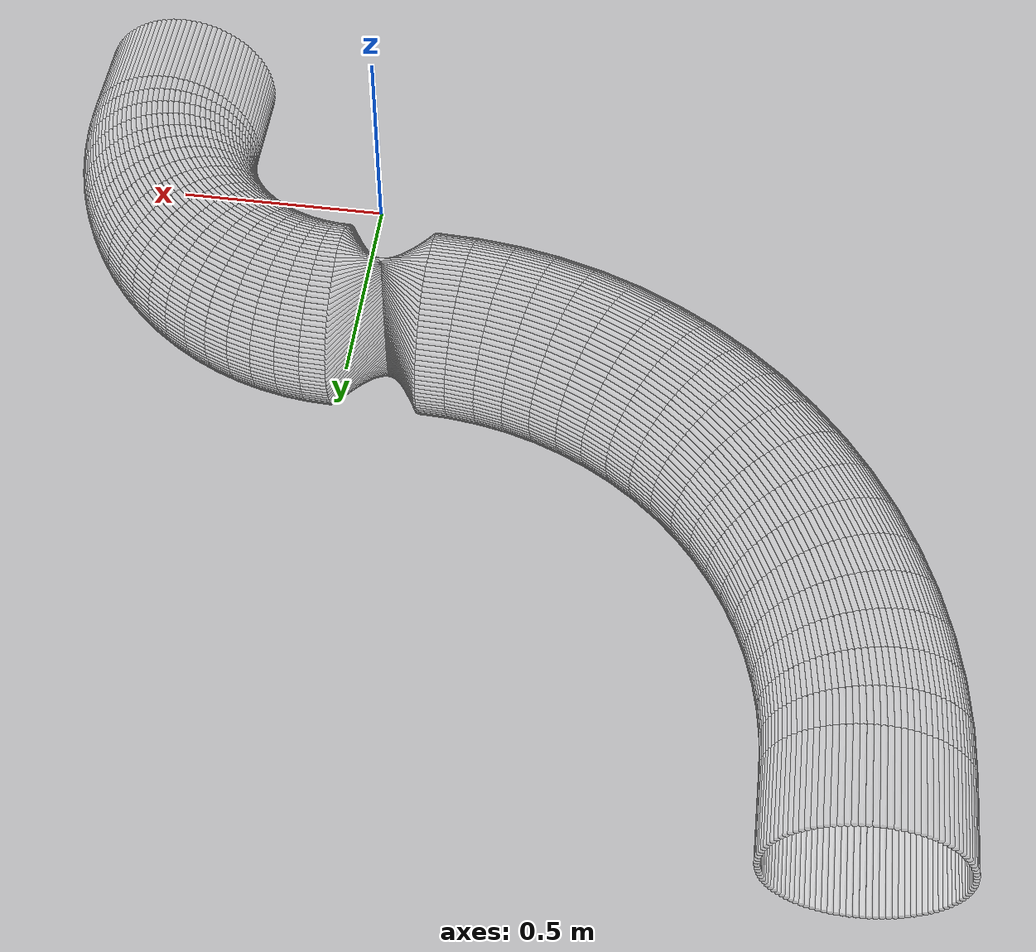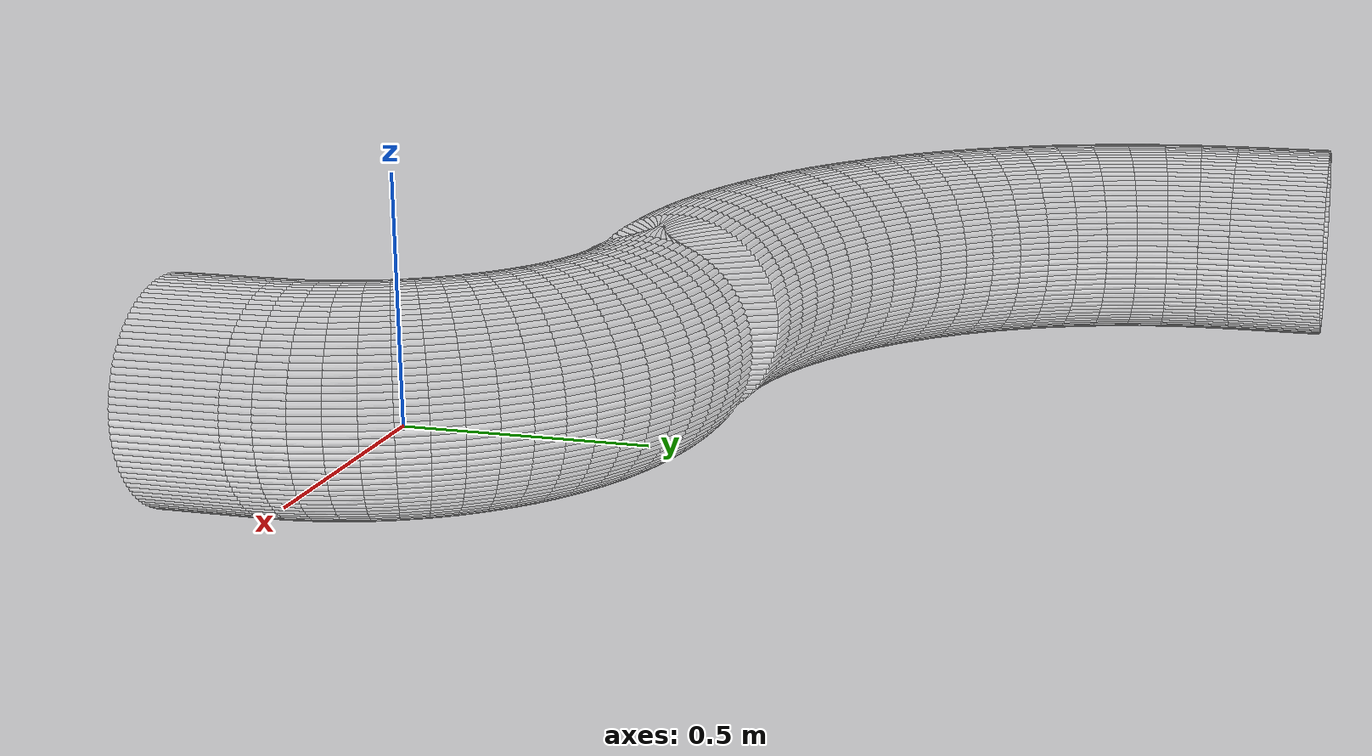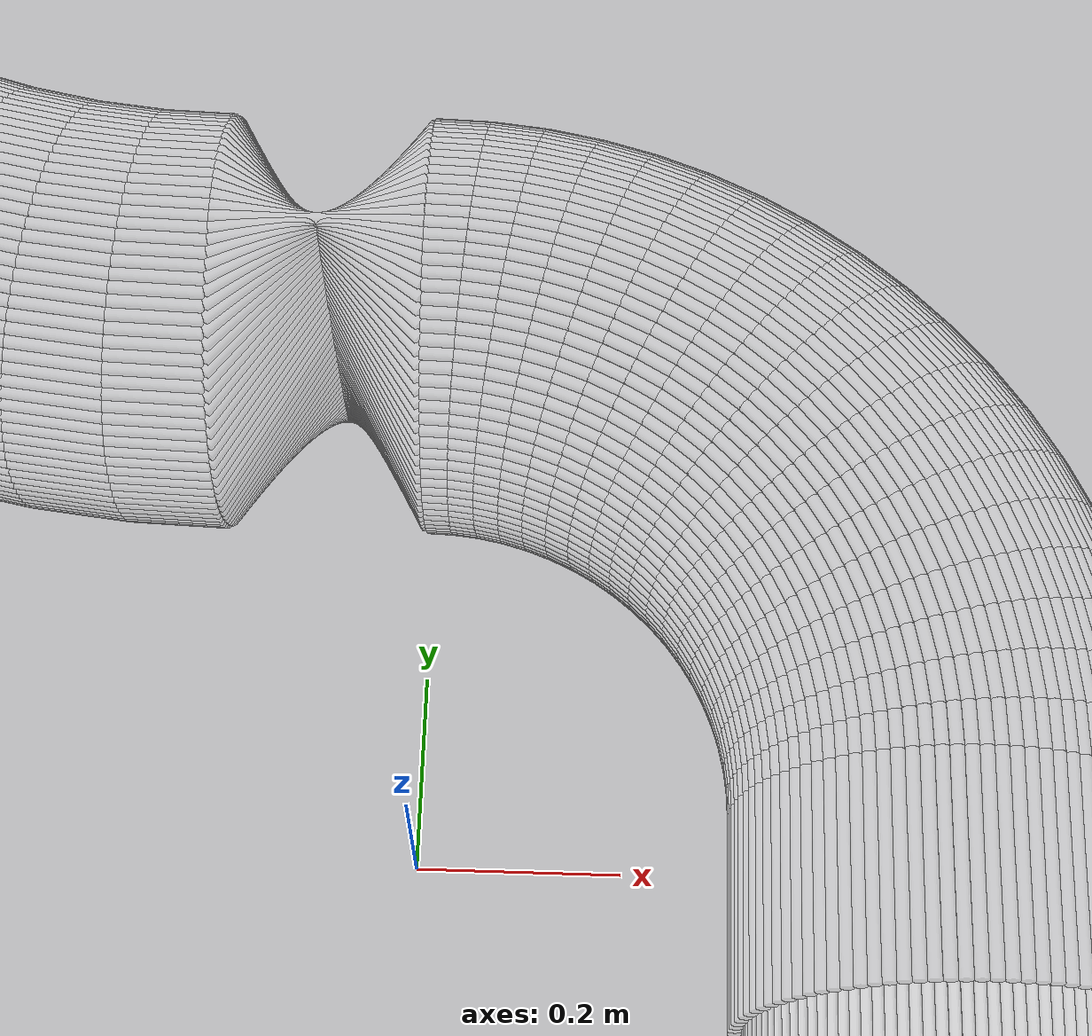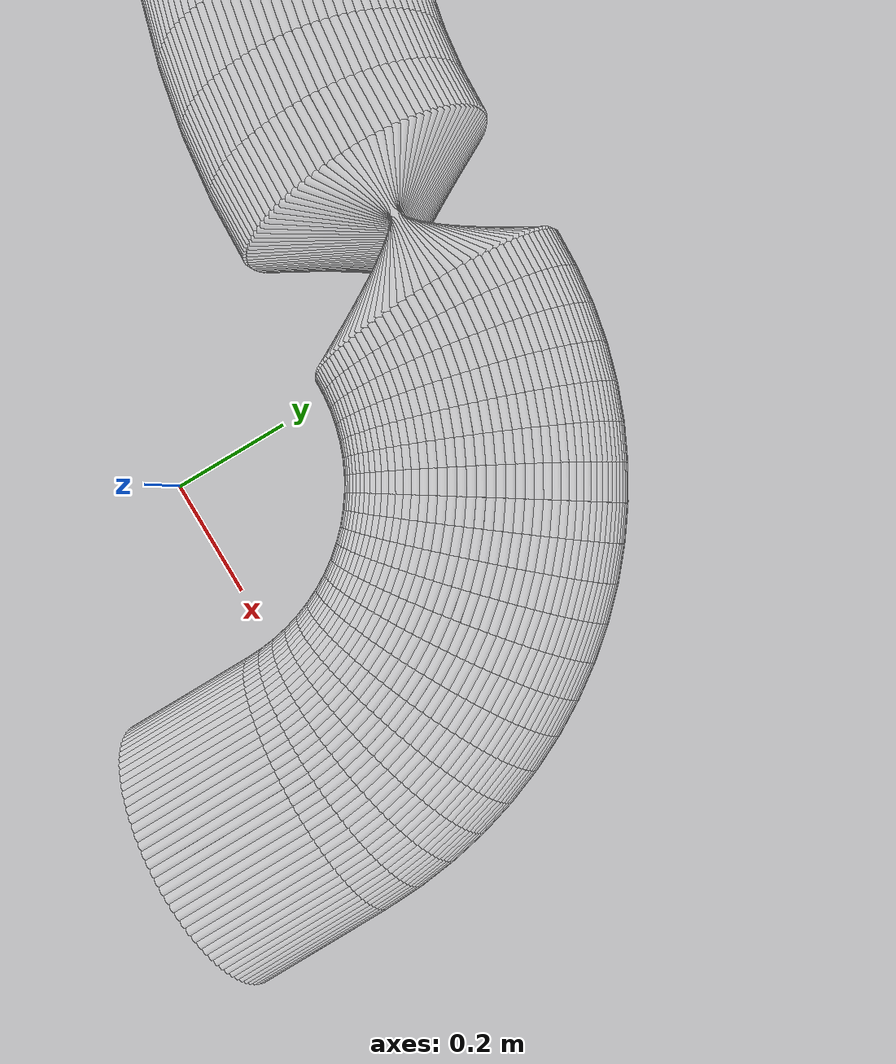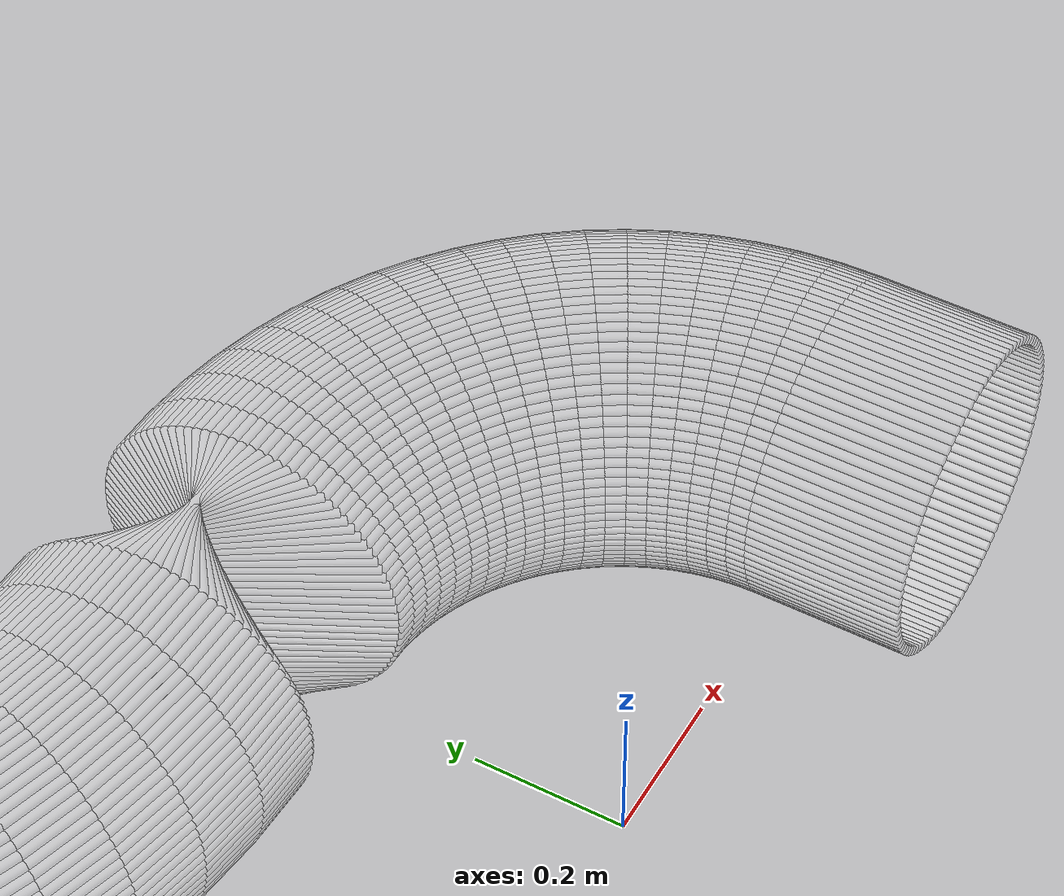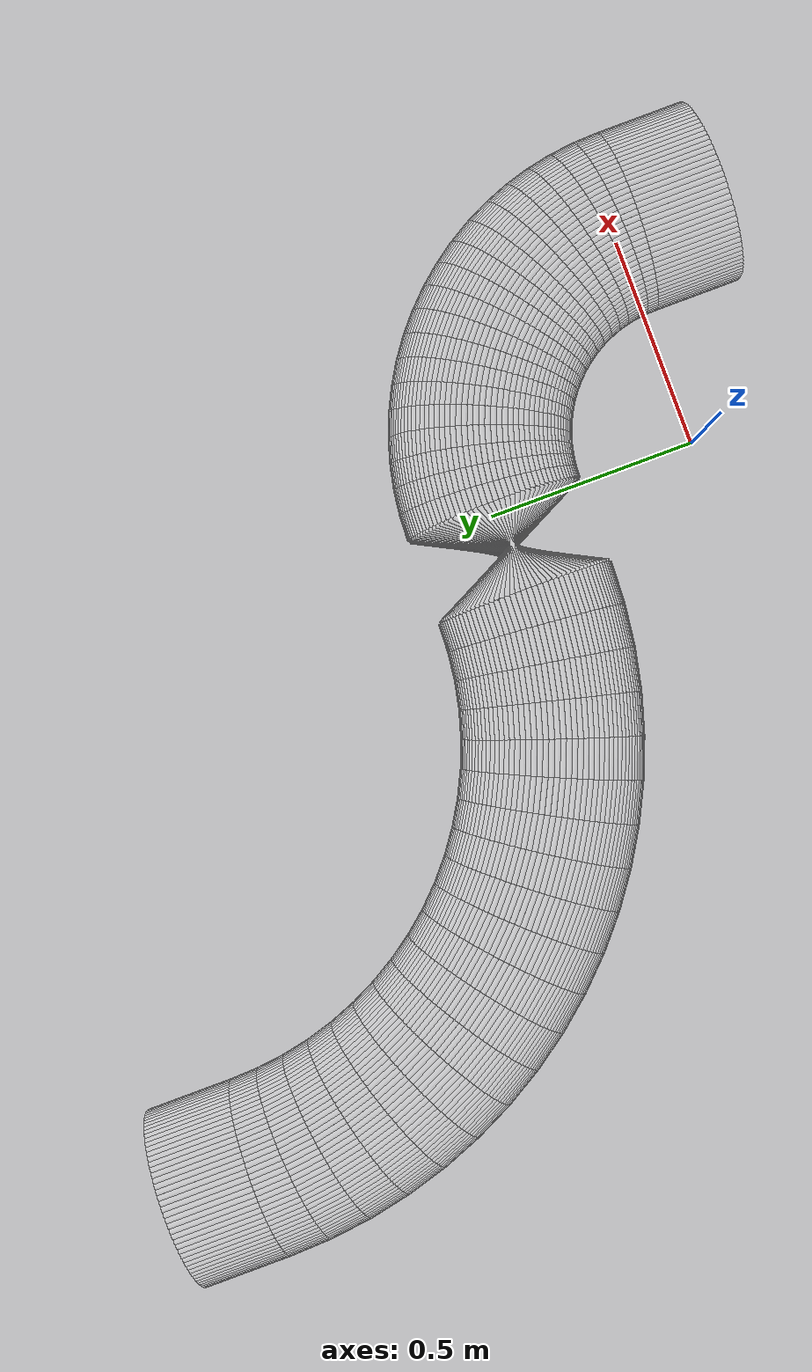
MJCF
<?xml version="1.0" encoding="utf-8"?>
<mujoco>
   <worldbody>
      <geom euler=" 0 10 0 " fromto="0.7 -0.2 0.2 0.7 0 0.2" rgba="1 1 1 0.35"
            size="0.0062822"
            type="cylinder"/>
      <geom euler=" 0 20 0 " fromto="0.69961 -0.2 0.21256 0.69961 0 0.21256"
            rgba="1 1 1 0.05"
            size="0.0062822"
            type="cylinder"/>
      <geom euler=" 0 30 0 " fromto="0.69842 -0.2 0.22507 0.69842 0 0.22507"
            rgba="1 1 1 0.05"
            size="0.0062822"
            type="cylinder"/>
      <geom euler=" 0 40 0 " fromto="0.69646 -0.2 0.23748 0.69646 0 0.23748"
            rgba="1 1 1 0.05"
            size="0.0062822"
            type="cylinder"/>
      <geom euler=" 0 50 0 " fromto="0.69372 -0.2 0.24974 0.69372 0 0.24974"
            rgba="1 1 1 0.05"
            size="0.0062822"
            type="cylinder"/>
      <geom euler=" 0 60 0 " fromto="0.69021 -0.2 0.2618 0.69021 0 0.2618"
            rgba="1 1 1 0.05"
            size="0.0062822"
            type="cylinder"/>
      <geom euler=" 0 70 0 " fromto="0.68596 -0.2 0.27362 0.68596 0 0.27362"
            rgba="1 1 1 0.05"
            size="0.0062822"
            type="cylinder"/>
      <geom euler=" 0 80 0 " fromto="0.68097 -0.2 0.28516 0.68097 0 0.28516"
            rgba="1 1 1 0.05"
            size="0.0062822"
            type="cylinder"/>
      <geom euler=" 0 90 0 " fromto="0.67526 -0.2 0.29635 0.67526 0 0.29635"
            rgba="1 1 1 0.05"
            size="0.0062822"
            type="cylinder"/>
      <geom euler=" 0 100 0 " fromto="0.66887 -0.2 0.30717 0.66887 0 0.30717"
            rgba="1 1 1 0.05"
            size="0.0062822"
            type="cylinder"/>
      <geom euler=" 0 110 0 " fromto="0.6618 -0.2 0.31756 0.6618 0 0.31756"
            rgba="1 1 1 0.05"
            size="0.0062822"
            type="cylinder"/>
      <geom euler=" 0 120 0 " fromto="0.6541 -0.2 0.32748 0.6541 0 0.32748"
            rgba="1 1 1 0.05"
            size="0.0062822"
            type="cylinder"/>
      <geom euler=" 0 130 0 " fromto="0.64579 -0.2 0.33691 0.64579 0 0.33691"
            rgba="1 1 1 0.05"
            size="0.0062822"
            type="cylinder"/>
      <geom euler=" 0 140 0 " fromto="0.63691 -0.2 0.34579 0.63691 0 0.34579"
            rgba="1 1 1 0.05"
            size="0.0062822"
            type="cylinder"/>
      <geom euler=" 0 150 0 " fromto="0.62748 -0.2 0.3541 0.62748 0 0.3541"
            rgba="1 1 1 0.05"
            size="0.0062822"
            type="cylinder"/>
      <geom euler=" 0 160 0 " fromto="0.61756 -0.2 0.3618 0.61756 0 0.3618"
            rgba="1 1 1 0.05"
            size="0.0062822"
            type="cylinder"/>
      <geom euler=" 0 170 0 " fromto="0.60717 -0.2 0.36887 0.60717 0 0.36887"
            rgba="1 1 1 0.05"
            size="0.0062822"
            type="cylinder"/>
      <geom euler=" 0 180 0 " fromto="0.59635 -0.2 0.37526 0.59635 0 0.37526"
            rgba="1 1 1 0.05"
            size="0.0062822"
            type="cylinder"/>
      <geom euler=" 0 190 0 " fromto="0.58516 -0.2 0.38097 0.58516 0 0.38097"
            rgba="1 1 1 0.05"
            size="0.0062822"
            type="cylinder"/>
      <geom euler=" 0 200 0 " fromto="0.57362 -0.2 0.38596 0.57362 0 0.38596"
            rgba="1 1 1 0.05"
            size="0.0062822"
            type="cylinder"/>
      <geom euler=" 0 210 0 " fromto="0.5618 -0.2 0.39021 0.5618 0 0.39021"
            rgba="1 1 1 0.05"
            size="0.0062822"
            type="cylinder"/>
      <geom euler=" 0 220 0 " fromto="0.54974 -0.2 0.39372 0.54974 0 0.39372"
            rgba="1 1 1 0.05"
            size="0.0062822"
            type="cylinder"/>
      <geom euler=" 0 230 0 " fromto="0.53748 -0.2 0.39646 0.53748 0 0.39646"
            rgba="1 1 1 0.05"
            size="0.0062822"
            type="cylinder"/>
      <geom euler=" 0 240 0 " fromto="0.52507 -0.2 0.39842 0.52507 0 0.39842"
            rgba="1 1 1 0.05"
            size="0.0062822"
            type="cylinder"/>
      <geom euler=" 0 250 0 " fromto="0.51256 -0.2 0.39961 0.51256 0 0.39961"
            rgba="1 1 1 0.05"
            size="0.0062822"
            type="cylinder"/>
      <geom euler=" 0 260 0 " fromto="0.5 -0.2 0.4 0.5 0 0.4" rgba="1 1 1 0.05"
            size="0.0062822"
            type="cylinder"/>
      <geom euler=" 0 270 0 " fromto="0.48744 -0.2 0.39961 0.48744 0 0.39961"
            rgba="1 1 1 0.05"
            size="0.0062822"
            type="cylinder"/>
      <geom euler=" 0 280 0 " fromto="0.47493 -0.2 0.39842 0.47493 0 0.39842"
            rgba="1 1 1 0.05"
            size="0.0062822"
            type="cylinder"/>
      <geom euler=" 0 290 0 " fromto="0.46252 -0.2 0.39646 0.46252 0 0.39646"
            rgba="1 1 1 0.05"
            size="0.0062822"
            type="cylinder"/>
      <geom euler=" 0 300 0 " fromto="0.45026 -0.2 0.39372 0.45026 0 0.39372"
            rgba="1 1 1 0.05"
            size="0.0062822"
            type="cylinder"/>
      <geom euler=" 0 310 0 " fromto="0.4382 -0.2 0.39021 0.4382 0 0.39021"
            rgba="1 1 1 0.05"
            size="0.0062822"
            type="cylinder"/>
      <geom euler=" 0 320 0 " fromto="0.42638 -0.2 0.38596 0.42638 0 0.38596"
            rgba="1 1 1 0.05"
            size="0.0062822"
            type="cylinder"/>
      <geom euler=" 0 330 0 " fromto="0.41484 -0.2 0.38097 0.41484 0 0.38097"
            rgba="1 1 1 0.05"
            size="0.0062822"
            type="cylinder"/>
      <geom euler=" 0 340 0 " fromto="0.40365 -0.2 0.37526 0.40365 0 0.37526"
            rgba="1 1 1 0.05"
            size="0.0062822"
            type="cylinder"/>
      <geom euler=" 0 350 0 " fromto="0.39283 -0.2 0.36887 0.39283 0 0.36887"
            rgba="1 1 1 0.05"
            size="0.0062822"
            type="cylinder"/>
      <geom euler=" 0 360 0 " fromto="0.38244 -0.2 0.3618 0.38244 0 0.3618"
            rgba="1 1 1 0.05"
            size="0.0062822"
            type="cylinder"/>
      <geom euler=" 0 370 0 " fromto="0.37252 -0.2 0.3541 0.37252 0 0.3541"
            rgba="1 1 1 0.05"
            size="0.0062822"
            type="cylinder"/>
      <geom euler=" 0 380 0 " fromto="0.36309 -0.2 0.34579 0.36309 0 0.34579"
            rgba="1 1 1 0.05"
            size="0.0062822"
            type="cylinder"/>
      <geom euler=" 0 390 0 " fromto="0.35421 -0.2 0.33691 0.35421 0 0.33691"
            rgba="1 1 1 0.05"
            size="0.0062822"
            type="cylinder"/>
      <geom euler=" 0 400 0 " fromto="0.3459 -0.2 0.32748 0.3459 0 0.32748"
            rgba="1 1 1 0.05"
            size="0.0062822"
            type="cylinder"/>
      <geom euler=" 0 410 0 " fromto="0.3382 -0.2 0.31756 0.3382 0 0.31756"
            rgba="1 1 1 0.05"
            size="0.0062822"
            type="cylinder"/>
      <geom euler=" 0 420 0 " fromto="0.33113 -0.2 0.30717 0.33113 0 0.30717"
            rgba="1 1 1 0.05"
            size="0.0062822"
            type="cylinder"/>
      <geom euler=" 0 430 0 " fromto="0.32474 -0.2 0.29635 0.32474 0 0.29635"
            rgba="1 1 1 0.05"
            size="0.0062822"
            type="cylinder"/>
      <geom euler=" 0 440 0 " fromto="0.31903 -0.2 0.28516 0.31903 0 0.28516"
            rgba="1 1 1 0.05"
            size="0.0062822"
            type="cylinder"/>
      <geom euler=" 0 450 0 " fromto="0.31404 -0.2 0.27362 0.31404 0 0.27362"
            rgba="1 1 1 0.05"
            size="0.0062822"
            type="cylinder"/>
      <geom euler=" 0 460 0 " fromto="0.30979 -0.2 0.2618 0.30979 0 0.2618"
            rgba="1 1 1 0.05"
            size="0.0062822"
            type="cylinder"/>
      <geom euler=" 0 470 0 " fromto="0.30628 -0.2 0.24974 0.30628 0 0.24974"
            rgba="1 1 1 0.05"
            size="0.0062822"
            type="cylinder"/>
      <geom euler=" 0 480 0 " fromto="0.30354 -0.2 0.23748 0.30354 0 0.23748"
            rgba="1 1 1 0.05"
            size="0.0062822"
            type="cylinder"/>
      <geom euler=" 0 490 0 " fromto="0.30158 -0.2 0.22507 0.30158 0 0.22507"
            rgba="1 1 1 0.05"
            size="0.0062822"
            type="cylinder"/>
      <geom euler=" 0 500 0 " fromto="0.30039 -0.2 0.21256 0.30039 0 0.21256"
            rgba="1 1 1 0.05"
            size="0.0062822"
            type="cylinder"/>
      <geom euler=" 0 510 0 " fromto="0.3 -0.2 0.2 0.3 0 0.2" rgba="1 1 1 0.05"
            size="0.0062822"
            type="cylinder"/>
      <geom euler=" 0 520 0 " fromto="0.30039 -0.2 0.18744 0.30039 0 0.18744"
            rgba="1 1 1 0.35"
            size="0.0062822"
            type="cylinder"/>
      <geom euler=" 0 530 0 " fromto="0.30158 -0.2 0.17493 0.30158 0 0.17493"
            rgba="1 1 1 0.35"
            size="0.0062822"
            type="cylinder"/>
      <geom euler=" 0 540 0 " fromto="0.30354 -0.2 0.16252 0.30354 0 0.16252"
            rgba="1 1 1 0.35"
            size="0.0062822"
            type="cylinder"/>
      <geom euler=" 0 550 0 " fromto="0.30628 -0.2 0.15026 0.30628 0 0.15026"
            rgba="1 1 1 0.35"
            size="0.0062822"
            type="cylinder"/>
      <geom euler=" 0 560 0 " fromto="0.30979 -0.2 0.1382 0.30979 0 0.1382"
            rgba="1 1 1 0.35"
            size="0.0062822"
            type="cylinder"/>
      <geom euler=" 0 570 0 " fromto="0.31404 -0.2 0.12638 0.31404 0 0.12638"
            rgba="1 1 1 0.35"
            size="0.0062822"
            type="cylinder"/>
      <geom euler=" 0 580 0 " fromto="0.31903 -0.2 0.11484 0.31903 0 0.11484"
            rgba="1 1 1 0.35"
            size="0.0062822"
            type="cylinder"/>
      <geom euler=" 0 590 0 " fromto="0.32474 -0.2 0.10365 0.32474 0 0.10365"
            rgba="1 1 1 0.35"
            size="0.0062822"
            type="cylinder"/>
      <geom euler=" 0 600 0 " fromto="0.33113 -0.2 0.092835 0.33113 0 0.092835"
            rgba="1 1 1 0.35"
            size="0.0062822"
            type="cylinder"/>
      <geom euler=" 0 610 0 " fromto="0.3382 -0.2 0.082443 0.3382 0 0.082443"
            rgba="1 1 1 0.35"
            size="0.0062822"
            type="cylinder"/>
      <geom euler=" 0 620 0 " fromto="0.3459 -0.2 0.072515 0.3459 0 0.072515"
            rgba="1 1 1 0.35"
            size="0.0062822"
            type="cylinder"/>
      <geom euler=" 0 630 0 " fromto="0.35421 -0.2 0.063091 0.35421 0 0.063091"
            rgba="1 1 1 0.35"
            size="0.0062822"
            type="cylinder"/>
      <geom euler=" 0 640 0 " fromto="0.36309 -0.2 0.054206 0.36309 0 0.054206"
            rgba="1 1 1 0.35"
            size="0.0062822"
            type="cylinder"/>
      <geom euler=" 0 650 0 " fromto="0.37252 -0.2 0.045897 0.37252 0 0.045897"
            rgba="1 1 1 0.35"
            size="0.0062822"
            type="cylinder"/>
      <geom euler=" 0 660 0 " fromto="0.38244 -0.2 0.038197 0.38244 0 0.038197"
            rgba="1 1 1 0.35"
            size="0.0062822"
            type="cylinder"/>
      <geom euler=" 0 670 0 " fromto="0.39283 -0.2 0.031134 0.39283 0 0.031134"
            rgba="1 1 1 0.35"
            size="0.0062822"
            type="cylinder"/>
      <geom euler=" 0 680 0 " fromto="0.40365 -0.2 0.024739 0.40365 0 0.024739"
            rgba="1 1 1 0.35"
            size="0.0062822"
            type="cylinder"/>
      <geom euler=" 0 690 0 " fromto="0.41484 -0.2 0.019035 0.41484 0 0.019035"
            rgba="1 1 1 0.35"
            size="0.0062822"
            type="cylinder"/>
      <geom euler=" 0 700 0 " fromto="0.42638 -0.2 0.014045 0.42638 0 0.014045"
            rgba="1 1 1 0.35"
            size="0.0062822"
            type="cylinder"/>
      <geom euler=" 0 710 0 " fromto="0.4382 -0.2 0.0097887 0.4382 0 0.0097887"
            rgba="1 1 1 0.35"
            size="0.0062822"
            type="cylinder"/>
      <geom euler=" 0 720 0 " fromto="0.45026 -0.2 0.0062834 0.45026 0 0.0062834"
            rgba="1 1 1 0.35"
            size="0.0062822"
            type="cylinder"/>
      <geom euler=" 0 730 0 " fromto="0.46252 -0.2 0.0035425 0.46252 0 0.0035425"
            rgba="1 1 1 0.35"
            size="0.0062822"
            type="cylinder"/>
      <geom euler=" 0 740 0 " fromto="0.47493 -0.2 0.0015771 0.47493 0 0.0015771"
            rgba="1 1 1 0.35"
            size="0.0062822"
            type="cylinder"/>
      <geom euler=" 0 750 0 " fromto="0.48744 -0.2 0.00039465 0.48744 0 0.00039465"
            rgba="1 1 1 0.35"
            size="0.0062822"
            type="cylinder"/>
      <geom euler=" 0 760 0 " fromto="0.5 -0.2 0 0.5 0 0" rgba="1 1 1 0.35"
            size="0.0062822"
            type="cylinder"/>
      <geom euler=" 0 770 0 " fromto="0.51256 -0.2 0.00039465 0.51256 0 0.00039465"
            rgba="1 1 1 0.35"
            size="0.0062822"
            type="cylinder"/>
      <geom euler=" 0 780 0 " fromto="0.52507 -0.2 0.0015771 0.52507 0 0.0015771"
            rgba="1 1 1 0.35"
            size="0.0062822"
            type="cylinder"/>
      <geom euler=" 0 790 0 " fromto="0.53748 -0.2 0.0035425 0.53748 0 0.0035425"
            rgba="1 1 1 0.35"
            size="0.0062822"
            type="cylinder"/>
      <geom euler=" 0 800 0 " fromto="0.54974 -0.2 0.0062834 0.54974 0 0.0062834"
            rgba="1 1 1 0.35"
            size="0.0062822"
            type="cylinder"/>
      <geom euler=" 0 810 0 " fromto="0.5618 -0.2 0.0097887 0.5618 0 0.0097887"
            rgba="1 1 1 0.35"
            size="0.0062822"
            type="cylinder"/>
      <geom euler=" 0 820 0 " fromto="0.57362 -0.2 0.014045 0.57362 0 0.014045"
            rgba="1 1 1 0.35"
            size="0.0062822"
            type="cylinder"/>
      <geom euler=" 0 830 0 " fromto="0.58516 -0.2 0.019035 0.58516 0 0.019035"
            rgba="1 1 1 0.35"
            size="0.0062822"
            type="cylinder"/>
      <geom euler=" 0 840 0 " fromto="0.59635 -0.2 0.024739 0.59635 0 0.024739"
            rgba="1 1 1 0.35"
            size="0.0062822"
            type="cylinder"/>
      <geom euler=" 0 850 0 " fromto="0.60717 -0.2 0.031134 0.60717 0 0.031134"
            rgba="1 1 1 0.35"
            size="0.0062822"
            type="cylinder"/>
      <geom euler=" 0 860 0 " fromto="0.61756 -0.2 0.038197 0.61756 0 0.038197"
            rgba="1 1 1 0.35"
            size="0.0062822"
            type="cylinder"/>
      <geom euler=" 0 870 0 " fromto="0.62748 -0.2 0.045897 0.62748 0 0.045897"
            rgba="1 1 1 0.35"
            size="0.0062822"
            type="cylinder"/>
      <geom euler=" 0 880 0 " fromto="0.63691 -0.2 0.054206 0.63691 0 0.054206"
            rgba="1 1 1 0.35"
            size="0.0062822"
            type="cylinder"/>
      <geom euler=" 0 890 0 " fromto="0.64579 -0.2 0.063091 0.64579 0 0.063091"
            rgba="1 1 1 0.35"
            size="0.0062822"
            type="cylinder"/>
      <geom euler=" 0 900 0 " fromto="0.6541 -0.2 0.072515 0.6541 0 0.072515"
            rgba="1 1 1 0.35"
            size="0.0062822"
            type="cylinder"/>
      <geom euler=" 0 910 0 " fromto="0.6618 -0.2 0.082443 0.6618 0 0.082443"
            rgba="1 1 1 0.35"
            size="0.0062822"
            type="cylinder"/>
      <geom euler=" 0 920 0 " fromto="0.66887 -0.2 0.092835 0.66887 0 0.092835"
            rgba="1 1 1 0.35"
            size="0.0062822"
            type="cylinder"/>
      <geom euler=" 0 930 0 " fromto="0.67526 -0.2 0.10365 0.67526 0 0.10365"
            rgba="1 1 1 0.35"
            size="0.0062822"
            type="cylinder"/>
      <geom euler=" 0 940 0 " fromto="0.68097 -0.2 0.11484 0.68097 0 0.11484"
            rgba="1 1 1 0.35"
            size="0.0062822"
            type="cylinder"/>
      <geom euler=" 0 950 0 " fromto="0.68596 -0.2 0.12638 0.68596 0 0.12638"
            rgba="1 1 1 0.35"
            size="0.0062822"
            type="cylinder"/>
      <geom euler=" 0 960 0 " fromto="0.69021 -0.2 0.1382 0.69021 0 0.1382"
            rgba="1 1 1 0.35"
            size="0.0062822"
            type="cylinder"/>
      <geom euler=" 0 970 0 " fromto="0.69372 -0.2 0.15026 0.69372 0 0.15026"
            rgba="1 1 1 0.35"
            size="0.0062822"
            type="cylinder"/>
      <geom euler=" 0 980 0 " fromto="0.69646 -0.2 0.16252 0.69646 0 0.16252"
            rgba="1 1 1 0.35"
            size="0.0062822"
            type="cylinder"/>
      <geom euler=" 0 990 0 " fromto="0.69842 -0.2 0.17493 0.69842 0 0.17493"
            rgba="1 1 1 0.35"
            size="0.0062822"
            type="cylinder"/>
      <geom euler=" 0 1000 0 " fromto="0.69961 -0.2 0.18744 0.69961 0 0.18744"
            rgba="1 1 1 0.35"
            size="0.0062822"
            type="cylinder"/>
      <geom euler=" 0 10 0 " fromto="0.7 0 0.2 0.69761 0.057806 0.2" rgba="1 1 1 0.35"
            size="0.0062822"
            type="cylinder"/>
      <geom euler=" 0 20 0 " fromto="0.69961 0 0.21256 0.69722 0.057773 0.21256"
            rgba="1 1 1 0.05"
            size="0.0062822"
            type="cylinder"/>
      <geom euler=" 0 30 0 " fromto="0.69842 0 0.22507 0.69604 0.057675 0.22507"
            rgba="1 1 1 0.05"
            size="0.0062822"
            type="cylinder"/>
      <geom euler=" 0 40 0 " fromto="0.69646 0 0.23748 0.69408 0.057513 0.23748"
            rgba="1 1 1 0.05"
            size="0.0062822"
            type="cylinder"/>
      <geom euler=" 0 50 0 " fromto="0.69372 0 0.24974 0.69135 0.057287 0.24974"
            rgba="1 1 1 0.05"
            size="0.0062822"
            type="cylinder"/>
      <geom euler=" 0 60 0 " fromto="0.69021 0 0.2618 0.68785 0.056997 0.2618"
            rgba="1 1 1 0.05"
            size="0.0062822"
            type="cylinder"/>
      <geom euler=" 0 70 0 " fromto="0.68596 0 0.27362 0.68361 0.056646 0.27362"
            rgba="1 1 1 0.05"
            size="0.0062822"
            type="cylinder"/>
      <geom euler=" 0 80 0 " fromto="0.68097 0 0.28516 0.67864 0.056234 0.28516"
            rgba="1 1 1 0.05"
            size="0.0062822"
            type="cylinder"/>
      <geom euler=" 0 90 0 " fromto="0.67526 0 0.29635 0.67295 0.055763 0.29635"
            rgba="1 1 1 0.05"
            size="0.0062822"
            type="cylinder"/>
      <geom euler=" 0 100 0 " fromto="0.66887 0 0.30717 0.66658 0.055234 0.30717"
            rgba="1 1 1 0.05"
            size="0.0062822"
            type="cylinder"/>
      <geom euler=" 0 110 0 " fromto="0.6618 0 0.31756 0.65954 0.054651 0.31756"
            rgba="1 1 1 0.05"
            size="0.0062822"
            type="cylinder"/>
      <geom euler=" 0 120 0 " fromto="0.6541 0 0.32748 0.65187 0.054015 0.32748"
            rgba="1 1 1 0.05"
            size="0.0062822"
            type="cylinder"/>
      <geom euler=" 0 130 0 " fromto="0.64579 0 0.33691 0.64359 0.053329 0.33691"
            rgba="1 1 1 0.05"
            size="0.0062822"
            type="cylinder"/>
      <geom euler=" 0 140 0 " fromto="0.63691 0 0.34579 0.63473 0.052596 0.34579"
            rgba="1 1 1 0.05"
            size="0.0062822"
            type="cylinder"/>
      <geom euler=" 0 150 0 " fromto="0.62748 0 0.3541 0.62534 0.051817 0.3541"
            rgba="1 1 1 0.05"
            size="0.0062822"
            type="cylinder"/>
      <geom euler=" 0 160 0 " fromto="0.61756 0 0.3618 0.61545 0.050997 0.3618"
            rgba="1 1 1 0.05"
            size="0.0062822"
            type="cylinder"/>
      <geom euler=" 0 170 0 " fromto="0.60717 0 0.36887 0.60509 0.050139 0.36887"
            rgba="1 1 1 0.05"
            size="0.0062822"
            type="cylinder"/>
      <geom euler=" 0 180 0 " fromto="0.59635 0 0.37526 0.59431 0.049246 0.37526"
            rgba="1 1 1 0.05"
            size="0.0062822"
            type="cylinder"/>
      <geom euler=" 0 190 0 " fromto="0.58516 0 0.38097 0.58316 0.048322 0.38097"
            rgba="1 1 1 0.05"
            size="0.0062822"
            type="cylinder"/>
      <geom euler=" 0 200 0 " fromto="0.57362 0 0.38596 0.57167 0.04737 0.38596"
            rgba="1 1 1 0.05"
            size="0.0062822"
            type="cylinder"/>
      <geom euler=" 0 210 0 " fromto="0.5618 0 0.39021 0.55988 0.046393 0.39021"
            rgba="1 1 1 0.05"
            size="0.0062822"
            type="cylinder"/>
      <geom euler=" 0 220 0 " fromto="0.54974 0 0.39372 0.54786 0.045397 0.39372"
            rgba="1 1 1 0.05"
            size="0.0062822"
            type="cylinder"/>
      <geom euler=" 0 230 0 " fromto="0.53748 0 0.39646 0.53564 0.044384 0.39646"
            rgba="1 1 1 0.05"
            size="0.0062822"
            type="cylinder"/>
      <geom euler=" 0 240 0 " fromto="0.52507 0 0.39842 0.52327 0.04336 0.39842"
            rgba="1 1 1 0.05"
            size="0.0062822"
            type="cylinder"/>
      <geom euler=" 0 250 0 " fromto="0.51256 0 0.39961 0.51081 0.042327 0.39961"
            rgba="1 1 1 0.05"
            size="0.0062822"
            type="cylinder"/>
      <geom euler=" 0 260 0 " fromto="0.5 0 0.4 0.49829 0.04129 0.4" rgba="1 1 1 0.05"
            size="0.0062822"
            type="cylinder"/>
      <geom euler=" 0 270 0 " fromto="0.48744 0 0.39961 0.48578 0.040253 0.39961"
            rgba="1 1 1 0.05"
            size="0.0062822"
            type="cylinder"/>
      <geom euler=" 0 280 0 " fromto="0.47493 0 0.39842 0.47331 0.03922 0.39842"
            rgba="1 1 1 0.05"
            size="0.0062822"
            type="cylinder"/>
      <geom euler=" 0 290 0 " fromto="0.46252 0 0.39646 0.46094 0.038195 0.39646"
            rgba="1 1 1 0.05"
            size="0.0062822"
            type="cylinder"/>
      <geom euler=" 0 300 0 " fromto="0.45026 0 0.39372 0.44872 0.037182 0.39372"
            rgba="1 1 1 0.05"
            size="0.0062822"
            type="cylinder"/>
      <geom euler=" 0 310 0 " fromto="0.4382 0 0.39021 0.4367 0.036186 0.39021"
            rgba="1 1 1 0.05"
            size="0.0062822"
            type="cylinder"/>
      <geom euler=" 0 320 0 " fromto="0.42638 0 0.38596 0.42492 0.03521 0.38596"
            rgba="1 1 1 0.05"
            size="0.0062822"
            type="cylinder"/>
      <geom euler=" 0 330 0 " fromto="0.41484 0 0.38097 0.41343 0.034258 0.38097"
            rgba="1 1 1 0.05"
            size="0.0062822"
            type="cylinder"/>
      <geom euler=" 0 340 0 " fromto="0.40365 0 0.37526 0.40227 0.033333 0.37526"
            rgba="1 1 1 0.05"
            size="0.0062822"
            type="cylinder"/>
      <geom euler=" 0 350 0 " fromto="0.39283 0 0.36887 0.39149 0.03244 0.36887"
            rgba="1 1 1 0.05"
            size="0.0062822"
            type="cylinder"/>
      <geom euler=" 0 360 0 " fromto="0.38244 0 0.3618 0.38114 0.031582 0.3618"
            rgba="1 1 1 0.05"
            size="0.0062822"
            type="cylinder"/>
      <geom euler=" 0 370 0 " fromto="0.37252 0 0.3541 0.37124 0.030762 0.3541"
            rgba="1 1 1 0.05"
            size="0.0062822"
            type="cylinder"/>
      <geom euler=" 0 380 0 " fromto="0.36309 0 0.34579 0.36185 0.029984 0.34579"
            rgba="1 1 1 0.05"
            size="0.0062822"
            type="cylinder"/>
      <geom euler=" 0 390 0 " fromto="0.35421 0 0.33691 0.353 0.02925 0.33691"
            rgba="1 1 1 0.05"
            size="0.0062822"
            type="cylinder"/>
      <geom euler=" 0 400 0 " fromto="0.3459 0 0.32748 0.34472 0.028564 0.32748"
            rgba="1 1 1 0.05"
            size="0.0062822"
            type="cylinder"/>
      <geom euler=" 0 410 0 " fromto="0.3382 0 0.31756 0.33704 0.027928 0.31756"
            rgba="1 1 1 0.05"
            size="0.0062822"
            type="cylinder"/>
      <geom euler=" 0 420 0 " fromto="0.33113 0 0.30717 0.33 0.027345 0.30717"
            rgba="1 1 1 0.05"
            size="0.0062822"
            type="cylinder"/>
      <geom euler=" 0 430 0 " fromto="0.32474 0 0.29635 0.32363 0.026817 0.29635"
            rgba="1 1 1 0.05"
            size="0.0062822"
            type="cylinder"/>
      <geom euler=" 0 440 0 " fromto="0.31903 0 0.28516 0.31794 0.026346 0.28516"
            rgba="1 1 1 0.05"
            size="0.0062822"
            type="cylinder"/>
      <geom euler=" 0 450 0 " fromto="0.31404 0 0.27362 0.31297 0.025934 0.27362"
            rgba="1 1 1 0.05"
            size="0.0062822"
            type="cylinder"/>
      <geom euler=" 0 460 0 " fromto="0.30979 0 0.2618 0.30873 0.025582 0.2618"
            rgba="1 1 1 0.05"
            size="0.0062822"
            type="cylinder"/>
      <geom euler=" 0 470 0 " fromto="0.30628 0 0.24974 0.30524 0.025293 0.24974"
            rgba="1 1 1 0.05"
            size="0.0062822"
            type="cylinder"/>
      <geom euler=" 0 480 0 " fromto="0.30354 0 0.23748 0.30251 0.025066 0.23748"
            rgba="1 1 1 0.05"
            size="0.0062822"
            type="cylinder"/>
      <geom euler=" 0 490 0 " fromto="0.30158 0 0.22507 0.30055 0.024904 0.22507"
            rgba="1 1 1 0.05"
            size="0.0062822"
            type="cylinder"/>
      <geom euler=" 0 500 0 " fromto="0.30039 0 0.21256 0.29937 0.024806 0.21256"
            rgba="1 1 1 0.05"
            size="0.0062822"
            type="cylinder"/>
      <geom euler=" 0 510 0 " fromto="0.3 0 0.2 0.29898 0.024774 0.2" rgba="1 1 1 0.05"
            size="0.0062822"
            type="cylinder"/>
      <geom euler=" 0 520 0 " fromto="0.30039 0 0.18744 0.29937 0.024806 0.18744"
            rgba="1 1 1 0.35"
            size="0.0062822"
            type="cylinder"/>
      <geom euler=" 0 530 0 " fromto="0.30158 0 0.17493 0.30055 0.024904 0.17493"
            rgba="1 1 1 0.35"
            size="0.0062822"
            type="cylinder"/>
      <geom euler=" 0 540 0 " fromto="0.30354 0 0.16252 0.30251 0.025066 0.16252"
            rgba="1 1 1 0.35"
            size="0.0062822"
            type="cylinder"/>
      <geom euler=" 0 550 0 " fromto="0.30628 0 0.15026 0.30524 0.025293 0.15026"
            rgba="1 1 1 0.35"
            size="0.0062822"
            type="cylinder"/>
      <geom euler=" 0 560 0 " fromto="0.30979 0 0.1382 0.30873 0.025582 0.1382"
            rgba="1 1 1 0.35"
            size="0.0062822"
            type="cylinder"/>
      <geom euler=" 0 570 0 " fromto="0.31404 0 0.12638 0.31297 0.025934 0.12638"
            rgba="1 1 1 0.35"
            size="0.0062822"
            type="cylinder"/>
      <geom euler=" 0 580 0 " fromto="0.31903 0 0.11484 0.31794 0.026346 0.11484"
            rgba="1 1 1 0.35"
            size="0.0062822"
            type="cylinder"/>
      <geom euler=" 0 590 0 " fromto="0.32474 0 0.10365 0.32363 0.026817 0.10365"
            rgba="1 1 1 0.35"
            size="0.0062822"
            type="cylinder"/>
      <geom euler=" 0 600 0 " fromto="0.33113 0 0.092835 0.33 0.027345 0.092835"
            rgba="1 1 1 0.35"
            size="0.0062822"
            type="cylinder"/>
      <geom euler=" 0 610 0 " fromto="0.3382 0 0.082443 0.33704 0.027928 0.082443"
            rgba="1 1 1 0.35"
            size="0.0062822"
            type="cylinder"/>
      <geom euler=" 0 620 0 " fromto="0.3459 0 0.072515 0.34472 0.028564 0.072515"
            rgba="1 1 1 0.35"
            size="0.0062822"
            type="cylinder"/>
      <geom euler=" 0 630 0 " fromto="0.35421 0 0.063091 0.353 0.02925 0.063091"
            rgba="1 1 1 0.35"
            size="0.0062822"
            type="cylinder"/>
      <geom euler=" 0 640 0 " fromto="0.36309 0 0.054206 0.36185 0.029984 0.054206"
            rgba="1 1 1 0.35"
            size="0.0062822"
            type="cylinder"/>
      <geom euler=" 0 650 0 " fromto="0.37252 0 0.045897 0.37124 0.030762 0.045897"
            rgba="1 1 1 0.35"
            size="0.0062822"
            type="cylinder"/>
      <geom euler=" 0 660 0 " fromto="0.38244 0 0.038197 0.38114 0.031582 0.038197"
            rgba="1 1 1 0.35"
            size="0.0062822"
            type="cylinder"/>
      <geom euler=" 0 670 0 " fromto="0.39283 0 0.031134 0.39149 0.03244 0.031134"
            rgba="1 1 1 0.35"
            size="0.0062822"
            type="cylinder"/>
      <geom euler=" 0 680 0 " fromto="0.40365 0 0.024739 0.40227 0.033333 0.024739"
            rgba="1 1 1 0.35"
            size="0.0062822"
            type="cylinder"/>
      <geom euler=" 0 690 0 " fromto="0.41484 0 0.019035 0.41343 0.034258 0.019035"
            rgba="1 1 1 0.35"
            size="0.0062822"
            type="cylinder"/>
      <geom euler=" 0 700 0 " fromto="0.42638 0 0.014045 0.42492 0.03521 0.014045"
            rgba="1 1 1 0.35"
            size="0.0062822"
            type="cylinder"/>
      <geom euler=" 0 710 0 " fromto="0.4382 0 0.0097887 0.4367 0.036186 0.0097887"
            rgba="1 1 1 0.35"
            size="0.0062822"
            type="cylinder"/>
      <geom euler=" 0 720 0 " fromto="0.45026 0 0.0062834 0.44872 0.037182 0.0062834"
            rgba="1 1 1 0.35"
            size="0.0062822"
            type="cylinder"/>
      <geom euler=" 0 730 0 " fromto="0.46252 0 0.0035425 0.46094 0.038195 0.0035425"
            rgba="1 1 1 0.35"
            size="0.0062822"
            type="cylinder"/>
      <geom euler=" 0 740 0 " fromto="0.47493 0 0.0015771 0.47331 0.03922 0.0015771"
            rgba="1 1 1 0.35"
            size="0.0062822"
            type="cylinder"/>
      <geom euler=" 0 750 0 " fromto="0.48744 0 0.00039465 0.48578 0.040253 0.00039465"
            rgba="1 1 1 0.35"
            size="0.0062822"
            type="cylinder"/>
      <geom euler=" 0 760 0 " fromto="0.5 0 0 0.49829 0.04129 0" rgba="1 1 1 0.35"
            size="0.0062822"
            type="cylinder"/>
      <geom euler=" 0 770 0 " fromto="0.51256 0 0.00039465 0.51081 0.042327 0.00039465"
            rgba="1 1 1 0.35"
            size="0.0062822"
            type="cylinder"/>
      <geom euler=" 0 780 0 " fromto="0.52507 0 0.0015771 0.52327 0.04336 0.0015771"
            rgba="1 1 1 0.35"
            size="0.0062822"
            type="cylinder"/>
      <geom euler=" 0 790 0 " fromto="0.53748 0 0.0035425 0.53564 0.044384 0.0035425"
            rgba="1 1 1 0.35"
            size="0.0062822"
            type="cylinder"/>
      <geom euler=" 0 800 0 " fromto="0.54974 0 0.0062834 0.54786 0.045397 0.0062834"
            rgba="1 1 1 0.35"
            size="0.0062822"
            type="cylinder"/>
      <geom euler=" 0 810 0 " fromto="0.5618 0 0.0097887 0.55988 0.046393 0.0097887"
            rgba="1 1 1 0.35"
            size="0.0062822"
            type="cylinder"/>
      <geom euler=" 0 820 0 " fromto="0.57362 0 0.014045 0.57167 0.04737 0.014045"
            rgba="1 1 1 0.35"
            size="0.0062822"
            type="cylinder"/>
      <geom euler=" 0 830 0 " fromto="0.58516 0 0.019035 0.58316 0.048322 0.019035"
            rgba="1 1 1 0.35"
            size="0.0062822"
            type="cylinder"/>
      <geom euler=" 0 840 0 " fromto="0.59635 0 0.024739 0.59431 0.049246 0.024739"
            rgba="1 1 1 0.35"
            size="0.0062822"
            type="cylinder"/>
      <geom euler=" 0 850 0 " fromto="0.60717 0 0.031134 0.60509 0.050139 0.031134"
            rgba="1 1 1 0.35"
            size="0.0062822"
            type="cylinder"/>
      <geom euler=" 0 860 0 " fromto="0.61756 0 0.038197 0.61545 0.050997 0.038197"
            rgba="1 1 1 0.35"
            size="0.0062822"
            type="cylinder"/>
      <geom euler=" 0 870 0 " fromto="0.62748 0 0.045897 0.62534 0.051817 0.045897"
            rgba="1 1 1 0.35"
            size="0.0062822"
            type="cylinder"/>
      <geom euler=" 0 880 0 " fromto="0.63691 0 0.054206 0.63473 0.052596 0.054206"
            rgba="1 1 1 0.35"
            size="0.0062822"
            type="cylinder"/>
      <geom euler=" 0 890 0 " fromto="0.64579 0 0.063091 0.64359 0.053329 0.063091"
            rgba="1 1 1 0.35"
            size="0.0062822"
            type="cylinder"/>
      <geom euler=" 0 900 0 " fromto="0.6541 0 0.072515 0.65187 0.054015 0.072515"
            rgba="1 1 1 0.35"
            size="0.0062822"
            type="cylinder"/>
      <geom euler=" 0 910 0 " fromto="0.6618 0 0.082443 0.65954 0.054651 0.082443"
            rgba="1 1 1 0.35"
            size="0.0062822"
            type="cylinder"/>
      <geom euler=" 0 920 0 " fromto="0.66887 0 0.092835 0.66658 0.055234 0.092835"
            rgba="1 1 1 0.35"
            size="0.0062822"
            type="cylinder"/>
      <geom euler=" 0 930 0 " fromto="0.67526 0 0.10365 0.67295 0.055763 0.10365"
            rgba="1 1 1 0.35"
            size="0.0062822"
            type="cylinder"/>
      <geom euler=" 0 940 0 " fromto="0.68097 0 0.11484 0.67864 0.056234 0.11484"
            rgba="1 1 1 0.35"
            size="0.0062822"
            type="cylinder"/>
      <geom euler=" 0 950 0 " fromto="0.68596 0 0.12638 0.68361 0.056646 0.12638"
            rgba="1 1 1 0.35"
            size="0.0062822"
            type="cylinder"/>
      <geom euler=" 0 960 0 " fromto="0.69021 0 0.1382 0.68785 0.056997 0.1382"
            rgba="1 1 1 0.35"
            size="0.0062822"
            type="cylinder"/>
      <geom euler=" 0 970 0 " fromto="0.69372 0 0.15026 0.69135 0.057287 0.15026"
            rgba="1 1 1 0.35"
            size="0.0062822"
            type="cylinder"/>
      <geom euler=" 0 980 0 " fromto="0.69646 0 0.16252 0.69408 0.057513 0.16252"
            rgba="1 1 1 0.35"
            size="0.0062822"
            type="cylinder"/>
      <geom euler=" 0 990 0 " fromto="0.69842 0 0.17493 0.69604 0.057675 0.17493"
            rgba="1 1 1 0.35"
            size="0.0062822"
            type="cylinder"/>
      <geom euler=" 0 1000 0 " fromto="0.69961 0 0.18744 0.69722 0.057773 0.18744"
            rgba="1 1 1 0.35"
            size="0.0062822"
            type="cylinder"/>
      <geom euler=" 0 10 0 " fromto="0.69761 0.057806 0.2 0.69045 0.11522 0.2"
            rgba="1 1 1 0.35"
            size="0.0062822"
            type="cylinder"/>
      <geom euler=" 0 20 0 " fromto="0.69722 0.057773 0.21256 0.69006 0.11515 0.21256"
            rgba="1 1 1 0.05"
            size="0.0062822"
            type="cylinder"/>
      <geom euler=" 0 30 0 " fromto="0.69604 0.057675 0.22507 0.6889 0.11496 0.22507"
            rgba="1 1 1 0.05"
            size="0.0062822"
            type="cylinder"/>
      <geom euler=" 0 40 0 " fromto="0.69408 0.057513 0.23748 0.68696 0.11463 0.23748"
            rgba="1 1 1 0.05"
            size="0.0062822"
            type="cylinder"/>
      <geom euler=" 0 50 0 " fromto="0.69135 0.057287 0.24974 0.68426 0.11418 0.24974"
            rgba="1 1 1 0.05"
            size="0.0062822"
            type="cylinder"/>
      <geom euler=" 0 60 0 " fromto="0.68785 0.056997 0.2618 0.6808 0.11361 0.2618"
            rgba="1 1 1 0.05"
            size="0.0062822"
            type="cylinder"/>
      <geom euler=" 0 70 0 " fromto="0.68361 0.056646 0.27362 0.6766 0.1129 0.27362"
            rgba="1 1 1 0.05"
            size="0.0062822"
            type="cylinder"/>
      <geom euler=" 0 80 0 " fromto="0.67864 0.056234 0.28516 0.67168 0.11208 0.28516"
            rgba="1 1 1 0.05"
            size="0.0062822"
            type="cylinder"/>
      <geom euler=" 0 90 0 " fromto="0.67295 0.055763 0.29635 0.66605 0.11114 0.29635"
            rgba="1 1 1 0.05"
            size="0.0062822"
            type="cylinder"/>
      <geom euler=" 0 100 0 " fromto="0.66658 0.055234 0.30717 0.65974 0.11009 0.30717"
            rgba="1 1 1 0.05"
            size="0.0062822"
            type="cylinder"/>
      <geom euler=" 0 110 0 " fromto="0.65954 0.054651 0.31756 0.65278 0.10893 0.31756"
            rgba="1 1 1 0.05"
            size="0.0062822"
            type="cylinder"/>
      <geom euler=" 0 120 0 " fromto="0.65187 0.054015 0.32748 0.64518 0.10766 0.32748"
            rgba="1 1 1 0.05"
            size="0.0062822"
            type="cylinder"/>
      <geom euler=" 0 130 0 " fromto="0.64359 0.053329 0.33691 0.63699 0.10629 0.33691"
            rgba="1 1 1 0.05"
            size="0.0062822"
            type="cylinder"/>
      <geom euler=" 0 140 0 " fromto="0.63473 0.052596 0.34579 0.62822 0.10483 0.34579"
            rgba="1 1 1 0.05"
            size="0.0062822"
            type="cylinder"/>
      <geom euler=" 0 150 0 " fromto="0.62534 0.051817 0.3541 0.61893 0.10328 0.3541"
            rgba="1 1 1 0.05"
            size="0.0062822"
            type="cylinder"/>
      <geom euler=" 0 160 0 " fromto="0.61545 0.050997 0.3618 0.60913 0.10165 0.3618"
            rgba="1 1 1 0.05"
            size="0.0062822"
            type="cylinder"/>
      <geom euler=" 0 170 0 " fromto="0.60509 0.050139 0.36887 0.59888 0.099936 0.36887"
            rgba="1 1 1 0.05"
            size="0.0062822"
            type="cylinder"/>
      <geom euler=" 0 180 0 " fromto="0.59431 0.049246 0.37526 0.58822 0.098156 0.37526"
            rgba="1 1 1 0.05"
            size="0.0062822"
            type="cylinder"/>
      <geom euler=" 0 190 0 " fromto="0.58316 0.048322 0.38097 0.57718 0.096313 0.38097"
            rgba="1 1 1 0.05"
            size="0.0062822"
            type="cylinder"/>
      <geom euler=" 0 200 0 " fromto="0.57167 0.04737 0.38596 0.5658 0.094416 0.38596"
            rgba="1 1 1 0.05"
            size="0.0062822"
            type="cylinder"/>
      <geom euler=" 0 210 0 " fromto="0.55988 0.046393 0.39021 0.55414 0.09247 0.39021"
            rgba="1 1 1 0.05"
            size="0.0062822"
            type="cylinder"/>
      <geom euler=" 0 220 0 " fromto="0.54786 0.045397 0.39372 0.54224 0.090484 0.39372"
            rgba="1 1 1 0.05"
            size="0.0062822"
            type="cylinder"/>
      <geom euler=" 0 230 0 " fromto="0.53564 0.044384 0.39646 0.53015 0.088466 0.39646"
            rgba="1 1 1 0.05"
            size="0.0062822"
            type="cylinder"/>
      <geom euler=" 0 240 0 " fromto="0.52327 0.04336 0.39842 0.51791 0.086423 0.39842"
            rgba="1 1 1 0.05"
            size="0.0062822"
            type="cylinder"/>
      <geom euler=" 0 250 0 " fromto="0.51081 0.042327 0.39961 0.50557 0.084364 0.39961"
            rgba="1 1 1 0.05"
            size="0.0062822"
            type="cylinder"/>
      <geom euler=" 0 260 0 " fromto="0.49829 0.04129 0.4 0.49318 0.082297 0.4"
            rgba="1 1 1 0.05"
            size="0.0062822"
            type="cylinder"/>
      <geom euler=" 0 270 0 " fromto="0.48578 0.040253 0.39961 0.48079 0.08023 0.39961"
            rgba="1 1 1 0.05"
            size="0.0062822"
            type="cylinder"/>
      <geom euler=" 0 280 0 " fromto="0.47331 0.03922 0.39842 0.46846 0.078171 0.39842"
            rgba="1 1 1 0.05"
            size="0.0062822"
            type="cylinder"/>
      <geom euler=" 0 290 0 " fromto="0.46094 0.038195 0.39646 0.45622 0.076129 0.39646"
            rgba="1 1 1 0.05"
            size="0.0062822"
            type="cylinder"/>
      <geom euler=" 0 300 0 " fromto="0.44872 0.037182 0.39372 0.44412 0.074111 0.39372"
            rgba="1 1 1 0.05"
            size="0.0062822"
            type="cylinder"/>
      <geom euler=" 0 310 0 " fromto="0.4367 0.036186 0.39021 0.43222 0.072125 0.39021"
            rgba="1 1 1 0.05"
            size="0.0062822"
            type="cylinder"/>
      <geom euler=" 0 320 0 " fromto="0.42492 0.03521 0.38596 0.42056 0.070179 0.38596"
            rgba="1 1 1 0.05"
            size="0.0062822"
            type="cylinder"/>
      <geom euler=" 0 330 0 " fromto="0.41343 0.034258 0.38097 0.40919 0.068281 0.38097"
            rgba="1 1 1 0.05"
            size="0.0062822"
            type="cylinder"/>
      <geom euler=" 0 340 0 " fromto="0.40227 0.033333 0.37526 0.39814 0.066438 0.37526"
            rgba="1 1 1 0.05"
            size="0.0062822"
            type="cylinder"/>
      <geom euler=" 0 350 0 " fromto="0.39149 0.03244 0.36887 0.38748 0.064658 0.36887"
            rgba="1 1 1 0.05"
            size="0.0062822"
            type="cylinder"/>
      <geom euler=" 0 360 0 " fromto="0.38114 0.031582 0.3618 0.37723 0.062948 0.3618"
            rgba="1 1 1 0.05"
            size="0.0062822"
            type="cylinder"/>
      <geom euler=" 0 370 0 " fromto="0.37124 0.030762 0.3541 0.36743 0.061314 0.3541"
            rgba="1 1 1 0.05"
            size="0.0062822"
            type="cylinder"/>
      <geom euler=" 0 380 0 " fromto="0.36185 0.029984 0.34579 0.35814 0.059763 0.34579"
            rgba="1 1 1 0.05"
            size="0.0062822"
            type="cylinder"/>
      <geom euler=" 0 390 0 " fromto="0.353 0.02925 0.33691 0.34938 0.0583 0.33691"
            rgba="1 1 1 0.05"
            size="0.0062822"
            type="cylinder"/>
      <geom euler=" 0 400 0 " fromto="0.34472 0.028564 0.32748 0.34118 0.056933 0.32748"
            rgba="1 1 1 0.05"
            size="0.0062822"
            type="cylinder"/>
      <geom euler=" 0 410 0 " fromto="0.33704 0.027928 0.31756 0.33358 0.055665 0.31756"
            rgba="1 1 1 0.05"
            size="0.0062822"
            type="cylinder"/>
      <geom euler=" 0 420 0 " fromto="0.33 0.027345 0.30717 0.32662 0.054503 0.30717"
            rgba="1 1 1 0.05"
            size="0.0062822"
            type="cylinder"/>
      <geom euler=" 0 430 0 " fromto="0.32363 0.026817 0.29635 0.32031 0.05345 0.29635"
            rgba="1 1 1 0.05"
            size="0.0062822"
            type="cylinder"/>
      <geom euler=" 0 440 0 " fromto="0.31794 0.026346 0.28516 0.31468 0.052511 0.28516"
            rgba="1 1 1 0.05"
            size="0.0062822"
            type="cylinder"/>
      <geom euler=" 0 450 0 " fromto="0.31297 0.025934 0.27362 0.30976 0.05169 0.27362"
            rgba="1 1 1 0.05"
            size="0.0062822"
            type="cylinder"/>
      <geom euler=" 0 460 0 " fromto="0.30873 0.025582 0.2618 0.30556 0.05099 0.2618"
            rgba="1 1 1 0.05"
            size="0.0062822"
            type="cylinder"/>
      <geom euler=" 0 470 0 " fromto="0.30524 0.025293 0.24974 0.30211 0.050413 0.24974"
            rgba="1 1 1 0.05"
            size="0.0062822"
            type="cylinder"/>
      <geom euler=" 0 480 0 " fromto="0.30251 0.025066 0.23748 0.2994 0.049961 0.23748"
            rgba="1 1 1 0.05"
            size="0.0062822"
            type="cylinder"/>
      <geom euler=" 0 490 0 " fromto="0.30055 0.024904 0.22507 0.29746 0.049638 0.22507"
            rgba="1 1 1 0.05"
            size="0.0062822"
            type="cylinder"/>
      <geom euler=" 0 500 0 " fromto="0.29937 0.024806 0.21256 0.2963 0.049443 0.21256"
            rgba="1 1 1 0.05"
            size="0.0062822"
            type="cylinder"/>
      <geom euler=" 0 510 0 " fromto="0.29898 0.024774 0.2 0.29591 0.049378 0.2"
            rgba="1 1 1 0.05"
            size="0.0062822"
            type="cylinder"/>
      <geom euler=" 0 520 0 " fromto="0.29937 0.024806 0.18744 0.2963 0.049443 0.18744"
            rgba="1 1 1 0.35"
            size="0.0062822"
            type="cylinder"/>
      <geom euler=" 0 530 0 " fromto="0.30055 0.024904 0.17493 0.29746 0.049638 0.17493"
            rgba="1 1 1 0.35"
            size="0.0062822"
            type="cylinder"/>
      <geom euler=" 0 540 0 " fromto="0.30251 0.025066 0.16252 0.2994 0.049961 0.16252"
            rgba="1 1 1 0.35"
            size="0.0062822"
            type="cylinder"/>
      <geom euler=" 0 550 0 " fromto="0.30524 0.025293 0.15026 0.30211 0.050413 0.15026"
            rgba="1 1 1 0.35"
            size="0.0062822"
            type="cylinder"/>
      <geom euler=" 0 560 0 " fromto="0.30873 0.025582 0.1382 0.30556 0.05099 0.1382"
            rgba="1 1 1 0.35"
            size="0.0062822"
            type="cylinder"/>
      <geom euler=" 0 570 0 " fromto="0.31297 0.025934 0.12638 0.30976 0.05169 0.12638"
            rgba="1 1 1 0.35"
            size="0.0062822"
            type="cylinder"/>
      <geom euler=" 0 580 0 " fromto="0.31794 0.026346 0.11484 0.31468 0.052511 0.11484"
            rgba="1 1 1 0.35"
            size="0.0062822"
            type="cylinder"/>
      <geom euler=" 0 590 0 " fromto="0.32363 0.026817 0.10365 0.32031 0.05345 0.10365"
            rgba="1 1 1 0.35"
            size="0.0062822"
            type="cylinder"/>
      <geom euler=" 0 600 0 " fromto="0.33 0.027345 0.092835 0.32662 0.054503 0.092835"
            rgba="1 1 1 0.35"
            size="0.0062822"
            type="cylinder"/>
      <geom euler=" 0 610 0 " fromto="0.33704 0.027928 0.082443 0.33358 0.055665 0.082443"
            rgba="1 1 1 0.35"
            size="0.0062822"
            type="cylinder"/>
      <geom euler=" 0 620 0 " fromto="0.34472 0.028564 0.072515 0.34118 0.056933 0.072515"
            rgba="1 1 1 0.35"
            size="0.0062822"
            type="cylinder"/>
      <geom euler=" 0 630 0 " fromto="0.353 0.02925 0.063091 0.34938 0.0583 0.063091"
            rgba="1 1 1 0.35"
            size="0.0062822"
            type="cylinder"/>
      <geom euler=" 0 640 0 " fromto="0.36185 0.029984 0.054206 0.35814 0.059763 0.054206"
            rgba="1 1 1 0.35"
            size="0.0062822"
            type="cylinder"/>
      <geom euler=" 0 650 0 " fromto="0.37124 0.030762 0.045897 0.36743 0.061314 0.045897"
            rgba="1 1 1 0.35"
            size="0.0062822"
            type="cylinder"/>
      <geom euler=" 0 660 0 " fromto="0.38114 0.031582 0.038197 0.37723 0.062948 0.038197"
            rgba="1 1 1 0.35"
            size="0.0062822"
            type="cylinder"/>
      <geom euler=" 0 670 0 " fromto="0.39149 0.03244 0.031134 0.38748 0.064658 0.031134"
            rgba="1 1 1 0.35"
            size="0.0062822"
            type="cylinder"/>
      <geom euler=" 0 680 0 " fromto="0.40227 0.033333 0.024739 0.39814 0.066438 0.024739"
            rgba="1 1 1 0.35"
            size="0.0062822"
            type="cylinder"/>
      <geom euler=" 0 690 0 " fromto="0.41343 0.034258 0.019035 0.40919 0.068281 0.019035"
            rgba="1 1 1 0.35"
            size="0.0062822"
            type="cylinder"/>
      <geom euler=" 0 700 0 " fromto="0.42492 0.03521 0.014045 0.42056 0.070179 0.014045"
            rgba="1 1 1 0.35"
            size="0.0062822"
            type="cylinder"/>
      <geom euler=" 0 710 0 " fromto="0.4367 0.036186 0.0097887 0.43222 0.072125 0.0097887"
            rgba="1 1 1 0.35"
            size="0.0062822"
            type="cylinder"/>
      <geom euler=" 0 720 0 "
            fromto="0.44872 0.037182 0.0062834 0.44412 0.074111 0.0062834"
            rgba="1 1 1 0.35"
            size="0.0062822"
            type="cylinder"/>
      <geom euler=" 0 730 0 "
            fromto="0.46094 0.038195 0.0035425 0.45622 0.076129 0.0035425"
            rgba="1 1 1 0.35"
            size="0.0062822"
            type="cylinder"/>
      <geom euler=" 0 740 0 " fromto="0.47331 0.03922 0.0015771 0.46846 0.078171 0.0015771"
            rgba="1 1 1 0.35"
            size="0.0062822"
            type="cylinder"/>
      <geom euler=" 0 750 0 "
            fromto="0.48578 0.040253 0.00039465 0.48079 0.08023 0.00039465"
            rgba="1 1 1 0.35"
            size="0.0062822"
            type="cylinder"/>
      <geom euler=" 0 760 0 " fromto="0.49829 0.04129 0 0.49318 0.082297 0"
            rgba="1 1 1 0.35"
            size="0.0062822"
            type="cylinder"/>
      <geom euler=" 0 770 0 "
            fromto="0.51081 0.042327 0.00039465 0.50557 0.084364 0.00039465"
            rgba="1 1 1 0.35"
            size="0.0062822"
            type="cylinder"/>
      <geom euler=" 0 780 0 " fromto="0.52327 0.04336 0.0015771 0.51791 0.086423 0.0015771"
            rgba="1 1 1 0.35"
            size="0.0062822"
            type="cylinder"/>
      <geom euler=" 0 790 0 "
            fromto="0.53564 0.044384 0.0035425 0.53015 0.088466 0.0035425"
            rgba="1 1 1 0.35"
            size="0.0062822"
            type="cylinder"/>
      <geom euler=" 0 800 0 "
            fromto="0.54786 0.045397 0.0062834 0.54224 0.090484 0.0062834"
            rgba="1 1 1 0.35"
            size="0.0062822"
            type="cylinder"/>
      <geom euler=" 0 810 0 " fromto="0.55988 0.046393 0.0097887 0.55414 0.09247 0.0097887"
            rgba="1 1 1 0.35"
            size="0.0062822"
            type="cylinder"/>
      <geom euler=" 0 820 0 " fromto="0.57167 0.04737 0.014045 0.5658 0.094416 0.014045"
            rgba="1 1 1 0.35"
            size="0.0062822"
            type="cylinder"/>
      <geom euler=" 0 830 0 " fromto="0.58316 0.048322 0.019035 0.57718 0.096313 0.019035"
            rgba="1 1 1 0.35"
            size="0.0062822"
            type="cylinder"/>
      <geom euler=" 0 840 0 " fromto="0.59431 0.049246 0.024739 0.58822 0.098156 0.024739"
            rgba="1 1 1 0.35"
            size="0.0062822"
            type="cylinder"/>
      <geom euler=" 0 850 0 " fromto="0.60509 0.050139 0.031134 0.59888 0.099936 0.031134"
            rgba="1 1 1 0.35"
            size="0.0062822"
            type="cylinder"/>
      <geom euler=" 0 860 0 " fromto="0.61545 0.050997 0.038197 0.60913 0.10165 0.038197"
            rgba="1 1 1 0.35"
            size="0.0062822"
            type="cylinder"/>
      <geom euler=" 0 870 0 " fromto="0.62534 0.051817 0.045897 0.61893 0.10328 0.045897"
            rgba="1 1 1 0.35"
            size="0.0062822"
            type="cylinder"/>
      <geom euler=" 0 880 0 " fromto="0.63473 0.052596 0.054206 0.62822 0.10483 0.054206"
            rgba="1 1 1 0.35"
            size="0.0062822"
            type="cylinder"/>
      <geom euler=" 0 890 0 " fromto="0.64359 0.053329 0.063091 0.63699 0.10629 0.063091"
            rgba="1 1 1 0.35"
            size="0.0062822"
            type="cylinder"/>
      <geom euler=" 0 900 0 " fromto="0.65187 0.054015 0.072515 0.64518 0.10766 0.072515"
            rgba="1 1 1 0.35"
            size="0.0062822"
            type="cylinder"/>
      <geom euler=" 0 910 0 " fromto="0.65954 0.054651 0.082443 0.65278 0.10893 0.082443"
            rgba="1 1 1 0.35"
            size="0.0062822"
            type="cylinder"/>
      <geom euler=" 0 920 0 " fromto="0.66658 0.055234 0.092835 0.65974 0.11009 0.092835"
            rgba="1 1 1 0.35"
            size="0.0062822"
            type="cylinder"/>
      <geom euler=" 0 930 0 " fromto="0.67295 0.055763 0.10365 0.66605 0.11114 0.10365"
            rgba="1 1 1 0.35"
            size="0.0062822"
            type="cylinder"/>
      <geom euler=" 0 940 0 " fromto="0.67864 0.056234 0.11484 0.67168 0.11208 0.11484"
            rgba="1 1 1 0.35"
            size="0.0062822"
            type="cylinder"/>
      <geom euler=" 0 950 0 " fromto="0.68361 0.056646 0.12638 0.6766 0.1129 0.12638"
            rgba="1 1 1 0.35"
            size="0.0062822"
            type="cylinder"/>
      <geom euler=" 0 960 0 " fromto="0.68785 0.056997 0.1382 0.6808 0.11361 0.1382"
            rgba="1 1 1 0.35"
            size="0.0062822"
            type="cylinder"/>
      <geom euler=" 0 970 0 " fromto="0.69135 0.057287 0.15026 0.68426 0.11418 0.15026"
            rgba="1 1 1 0.35"
            size="0.0062822"
            type="cylinder"/>
      <geom euler=" 0 980 0 " fromto="0.69408 0.057513 0.16252 0.68696 0.11463 0.16252"
            rgba="1 1 1 0.35"
            size="0.0062822"
            type="cylinder"/>
      <geom euler=" 0 990 0 " fromto="0.69604 0.057675 0.17493 0.6889 0.11496 0.17493"
            rgba="1 1 1 0.35"
            size="0.0062822"
            type="cylinder"/>
      <geom euler=" 0 1000 0 " fromto="0.69722 0.057773 0.18744 0.69006 0.11515 0.18744"
            rgba="1 1 1 0.35"
            size="0.0062822"
            type="cylinder"/>
      <geom euler=" 0 10 0 " fromto="0.69045 0.11522 0.2 0.67858 0.17184 0.2"
            rgba="1 1 1 0.35"
            size="0.0062822"
            type="cylinder"/>
      <geom euler=" 0 20 0 " fromto="0.69006 0.11515 0.21256 0.6782 0.17174 0.21256"
            rgba="1 1 1 0.05"
            size="0.0062822"
            type="cylinder"/>
      <geom euler=" 0 30 0 " fromto="0.6889 0.11496 0.22507 0.67705 0.17145 0.22507"
            rgba="1 1 1 0.05"
            size="0.0062822"
            type="cylinder"/>
      <geom euler=" 0 40 0 " fromto="0.68696 0.11463 0.23748 0.67515 0.17097 0.23748"
            rgba="1 1 1 0.05"
            size="0.0062822"
            type="cylinder"/>
      <geom euler=" 0 50 0 " fromto="0.68426 0.11418 0.24974 0.67249 0.1703 0.24974"
            rgba="1 1 1 0.05"
            size="0.0062822"
            type="cylinder"/>
      <geom euler=" 0 60 0 " fromto="0.6808 0.11361 0.2618 0.66909 0.16944 0.2618"
            rgba="1 1 1 0.05"
            size="0.0062822"
            type="cylinder"/>
      <geom euler=" 0 70 0 " fromto="0.6766 0.1129 0.27362 0.66497 0.16839 0.27362"
            rgba="1 1 1 0.05"
            size="0.0062822"
            type="cylinder"/>
      <geom euler=" 0 80 0 " fromto="0.67168 0.11208 0.28516 0.66013 0.16717 0.28516"
            rgba="1 1 1 0.05"
            size="0.0062822"
            type="cylinder"/>
      <geom euler=" 0 90 0 " fromto="0.66605 0.11114 0.29635 0.6546 0.16577 0.29635"
            rgba="1 1 1 0.05"
            size="0.0062822"
            type="cylinder"/>
      <geom euler=" 0 100 0 " fromto="0.65974 0.11009 0.30717 0.6484 0.1642 0.30717"
            rgba="1 1 1 0.05"
            size="0.0062822"
            type="cylinder"/>
      <geom euler=" 0 110 0 " fromto="0.65278 0.10893 0.31756 0.64155 0.16246 0.31756"
            rgba="1 1 1 0.05"
            size="0.0062822"
            type="cylinder"/>
      <geom euler=" 0 120 0 " fromto="0.64518 0.10766 0.32748 0.63409 0.16057 0.32748"
            rgba="1 1 1 0.05"
            size="0.0062822"
            type="cylinder"/>
      <geom euler=" 0 130 0 " fromto="0.63699 0.10629 0.33691 0.62603 0.15853 0.33691"
            rgba="1 1 1 0.05"
            size="0.0062822"
            type="cylinder"/>
      <geom euler=" 0 140 0 " fromto="0.62822 0.10483 0.34579 0.61742 0.15635 0.34579"
            rgba="1 1 1 0.05"
            size="0.0062822"
            type="cylinder"/>
      <geom euler=" 0 150 0 " fromto="0.61893 0.10328 0.3541 0.60828 0.15404 0.3541"
            rgba="1 1 1 0.05"
            size="0.0062822"
            type="cylinder"/>
      <geom euler=" 0 160 0 " fromto="0.60913 0.10165 0.3618 0.59866 0.1516 0.3618"
            rgba="1 1 1 0.05"
            size="0.0062822"
            type="cylinder"/>
      <geom euler=" 0 170 0 " fromto="0.59888 0.099936 0.36887 0.58859 0.14905 0.36887"
            rgba="1 1 1 0.05"
            size="0.0062822"
            type="cylinder"/>
      <geom euler=" 0 180 0 " fromto="0.58822 0.098156 0.37526 0.5781 0.1464 0.37526"
            rgba="1 1 1 0.05"
            size="0.0062822"
            type="cylinder"/>
      <geom euler=" 0 190 0 " fromto="0.57718 0.096313 0.38097 0.56725 0.14365 0.38097"
            rgba="1 1 1 0.05"
            size="0.0062822"
            type="cylinder"/>
      <geom euler=" 0 200 0 " fromto="0.5658 0.094416 0.38596 0.55607 0.14082 0.38596"
            rgba="1 1 1 0.05"
            size="0.0062822"
            type="cylinder"/>
      <geom euler=" 0 210 0 " fromto="0.55414 0.09247 0.39021 0.54461 0.13791 0.39021"
            rgba="1 1 1 0.05"
            size="0.0062822"
            type="cylinder"/>
      <geom euler=" 0 220 0 " fromto="0.54224 0.090484 0.39372 0.53292 0.13495 0.39372"
            rgba="1 1 1 0.05"
            size="0.0062822"
            type="cylinder"/>
      <geom euler=" 0 230 0 " fromto="0.53015 0.088466 0.39646 0.52103 0.13194 0.39646"
            rgba="1 1 1 0.05"
            size="0.0062822"
            type="cylinder"/>
      <geom euler=" 0 240 0 " fromto="0.51791 0.086423 0.39842 0.509 0.1289 0.39842"
            rgba="1 1 1 0.05"
            size="0.0062822"
            type="cylinder"/>
      <geom euler=" 0 250 0 " fromto="0.50557 0.084364 0.39961 0.49687 0.12583 0.39961"
            rgba="1 1 1 0.05"
            size="0.0062822"
            type="cylinder"/>
      <geom euler=" 0 260 0 " fromto="0.49318 0.082297 0.4 0.4847 0.12274 0.4"
            rgba="1 1 1 0.05"
            size="0.0062822"
            type="cylinder"/>
      <geom euler=" 0 270 0 " fromto="0.48079 0.08023 0.39961 0.47253 0.11966 0.39961"
            rgba="1 1 1 0.05"
            size="0.0062822"
            type="cylinder"/>
      <geom euler=" 0 280 0 " fromto="0.46846 0.078171 0.39842 0.4604 0.11659 0.39842"
            rgba="1 1 1 0.05"
            size="0.0062822"
            type="cylinder"/>
      <geom euler=" 0 290 0 " fromto="0.45622 0.076129 0.39646 0.44837 0.11354 0.39646"
            rgba="1 1 1 0.05"
            size="0.0062822"
            type="cylinder"/>
      <geom euler=" 0 300 0 " fromto="0.44412 0.074111 0.39372 0.43648 0.11053 0.39372"
            rgba="1 1 1 0.05"
            size="0.0062822"
            type="cylinder"/>
      <geom euler=" 0 310 0 " fromto="0.43222 0.072125 0.39021 0.42479 0.10757 0.39021"
            rgba="1 1 1 0.05"
            size="0.0062822"
            type="cylinder"/>
      <geom euler=" 0 320 0 " fromto="0.42056 0.070179 0.38596 0.41333 0.10467 0.38596"
            rgba="1 1 1 0.05"
            size="0.0062822"
            type="cylinder"/>
      <geom euler=" 0 330 0 " fromto="0.40919 0.068281 0.38097 0.40215 0.10184 0.38097"
            rgba="1 1 1 0.05"
            size="0.0062822"
            type="cylinder"/>
      <geom euler=" 0 340 0 " fromto="0.39814 0.066438 0.37526 0.3913 0.09909 0.37526"
            rgba="1 1 1 0.05"
            size="0.0062822"
            type="cylinder"/>
      <geom euler=" 0 350 0 " fromto="0.38748 0.064658 0.36887 0.38081 0.096435 0.36887"
            rgba="1 1 1 0.05"
            size="0.0062822"
            type="cylinder"/>
      <geom euler=" 0 360 0 " fromto="0.37723 0.062948 0.3618 0.37074 0.093884 0.3618"
            rgba="1 1 1 0.05"
            size="0.0062822"
            type="cylinder"/>
      <geom euler=" 0 370 0 " fromto="0.36743 0.061314 0.3541 0.36112 0.091447 0.3541"
            rgba="1 1 1 0.05"
            size="0.0062822"
            type="cylinder"/>
      <geom euler=" 0 380 0 " fromto="0.35814 0.059763 0.34579 0.35198 0.089133 0.34579"
            rgba="1 1 1 0.05"
            size="0.0062822"
            type="cylinder"/>
      <geom euler=" 0 390 0 " fromto="0.34938 0.0583 0.33691 0.34337 0.086952 0.33691"
            rgba="1 1 1 0.05"
            size="0.0062822"
            type="cylinder"/>
      <geom euler=" 0 400 0 " fromto="0.34118 0.056933 0.32748 0.33531 0.084913 0.32748"
            rgba="1 1 1 0.05"
            size="0.0062822"
            type="cylinder"/>
      <geom euler=" 0 410 0 " fromto="0.33358 0.055665 0.31756 0.32785 0.083022 0.31756"
            rgba="1 1 1 0.05"
            size="0.0062822"
            type="cylinder"/>
      <geom euler=" 0 420 0 " fromto="0.32662 0.054503 0.30717 0.321 0.081289 0.30717"
            rgba="1 1 1 0.05"
            size="0.0062822"
            type="cylinder"/>
      <geom euler=" 0 430 0 " fromto="0.32031 0.05345 0.29635 0.3148 0.079719 0.29635"
            rgba="1 1 1 0.05"
            size="0.0062822"
            type="cylinder"/>
      <geom euler=" 0 440 0 " fromto="0.31468 0.052511 0.28516 0.30927 0.078318 0.28516"
            rgba="1 1 1 0.05"
            size="0.0062822"
            type="cylinder"/>
      <geom euler=" 0 450 0 " fromto="0.30976 0.05169 0.27362 0.30444 0.077093 0.27362"
            rgba="1 1 1 0.05"
            size="0.0062822"
            type="cylinder"/>
      <geom euler=" 0 460 0 " fromto="0.30556 0.05099 0.2618 0.30031 0.076049 0.2618"
            rgba="1 1 1 0.05"
            size="0.0062822"
            type="cylinder"/>
      <geom euler=" 0 470 0 " fromto="0.30211 0.050413 0.24974 0.29691 0.075188 0.24974"
            rgba="1 1 1 0.05"
            size="0.0062822"
            type="cylinder"/>
      <geom euler=" 0 480 0 " fromto="0.2994 0.049961 0.23748 0.29425 0.074515 0.23748"
            rgba="1 1 1 0.05"
            size="0.0062822"
            type="cylinder"/>
      <geom euler=" 0 490 0 " fromto="0.29746 0.049638 0.22507 0.29235 0.074033 0.22507"
            rgba="1 1 1 0.05"
            size="0.0062822"
            type="cylinder"/>
      <geom euler=" 0 500 0 " fromto="0.2963 0.049443 0.21256 0.2912 0.073743 0.21256"
            rgba="1 1 1 0.05"
            size="0.0062822"
            type="cylinder"/>
      <geom euler=" 0 510 0 " fromto="0.29591 0.049378 0.2 0.29082 0.073646 0.2"
            rgba="1 1 1 0.05"
            size="0.0062822"
            type="cylinder"/>
      <geom euler=" 0 520 0 " fromto="0.2963 0.049443 0.18744 0.2912 0.073743 0.18744"
            rgba="1 1 1 0.35"
            size="0.0062822"
            type="cylinder"/>
      <geom euler=" 0 530 0 " fromto="0.29746 0.049638 0.17493 0.29235 0.074033 0.17493"
            rgba="1 1 1 0.35"
            size="0.0062822"
            type="cylinder"/>
      <geom euler=" 0 540 0 " fromto="0.2994 0.049961 0.16252 0.29425 0.074515 0.16252"
            rgba="1 1 1 0.35"
            size="0.0062822"
            type="cylinder"/>
      <geom euler=" 0 550 0 " fromto="0.30211 0.050413 0.15026 0.29691 0.075188 0.15026"
            rgba="1 1 1 0.35"
            size="0.0062822"
            type="cylinder"/>
      <geom euler=" 0 560 0 " fromto="0.30556 0.05099 0.1382 0.30031 0.076049 0.1382"
            rgba="1 1 1 0.35"
            size="0.0062822"
            type="cylinder"/>
      <geom euler=" 0 570 0 " fromto="0.30976 0.05169 0.12638 0.30444 0.077093 0.12638"
            rgba="1 1 1 0.35"
            size="0.0062822"
            type="cylinder"/>
      <geom euler=" 0 580 0 " fromto="0.31468 0.052511 0.11484 0.30927 0.078318 0.11484"
            rgba="1 1 1 0.35"
            size="0.0062822"
            type="cylinder"/>
      <geom euler=" 0 590 0 " fromto="0.32031 0.05345 0.10365 0.3148 0.079719 0.10365"
            rgba="1 1 1 0.35"
            size="0.0062822"
            type="cylinder"/>
      <geom euler=" 0 600 0 " fromto="0.32662 0.054503 0.092835 0.321 0.081289 0.092835"
            rgba="1 1 1 0.35"
            size="0.0062822"
            type="cylinder"/>
      <geom euler=" 0 610 0 " fromto="0.33358 0.055665 0.082443 0.32785 0.083022 0.082443"
            rgba="1 1 1 0.35"
            size="0.0062822"
            type="cylinder"/>
      <geom euler=" 0 620 0 " fromto="0.34118 0.056933 0.072515 0.33531 0.084913 0.072515"
            rgba="1 1 1 0.35"
            size="0.0062822"
            type="cylinder"/>
      <geom euler=" 0 630 0 " fromto="0.34938 0.0583 0.063091 0.34337 0.086952 0.063091"
            rgba="1 1 1 0.35"
            size="0.0062822"
            type="cylinder"/>
      <geom euler=" 0 640 0 " fromto="0.35814 0.059763 0.054206 0.35198 0.089133 0.054206"
            rgba="1 1 1 0.35"
            size="0.0062822"
            type="cylinder"/>
      <geom euler=" 0 650 0 " fromto="0.36743 0.061314 0.045897 0.36112 0.091447 0.045897"
            rgba="1 1 1 0.35"
            size="0.0062822"
            type="cylinder"/>
      <geom euler=" 0 660 0 " fromto="0.37723 0.062948 0.038197 0.37074 0.093884 0.038197"
            rgba="1 1 1 0.35"
            size="0.0062822"
            type="cylinder"/>
      <geom euler=" 0 670 0 " fromto="0.38748 0.064658 0.031134 0.38081 0.096435 0.031134"
            rgba="1 1 1 0.35"
            size="0.0062822"
            type="cylinder"/>
      <geom euler=" 0 680 0 " fromto="0.39814 0.066438 0.024739 0.3913 0.09909 0.024739"
            rgba="1 1 1 0.35"
            size="0.0062822"
            type="cylinder"/>
      <geom euler=" 0 690 0 " fromto="0.40919 0.068281 0.019035 0.40215 0.10184 0.019035"
            rgba="1 1 1 0.35"
            size="0.0062822"
            type="cylinder"/>
      <geom euler=" 0 700 0 " fromto="0.42056 0.070179 0.014045 0.41333 0.10467 0.014045"
            rgba="1 1 1 0.35"
            size="0.0062822"
            type="cylinder"/>
      <geom euler=" 0 710 0 " fromto="0.43222 0.072125 0.0097887 0.42479 0.10757 0.0097887"
            rgba="1 1 1 0.35"
            size="0.0062822"
            type="cylinder"/>
      <geom euler=" 0 720 0 " fromto="0.44412 0.074111 0.0062834 0.43648 0.11053 0.0062834"
            rgba="1 1 1 0.35"
            size="0.0062822"
            type="cylinder"/>
      <geom euler=" 0 730 0 " fromto="0.45622 0.076129 0.0035425 0.44837 0.11354 0.0035425"
            rgba="1 1 1 0.35"
            size="0.0062822"
            type="cylinder"/>
      <geom euler=" 0 740 0 " fromto="0.46846 0.078171 0.0015771 0.4604 0.11659 0.0015771"
            rgba="1 1 1 0.35"
            size="0.0062822"
            type="cylinder"/>
      <geom euler=" 0 750 0 "
            fromto="0.48079 0.08023 0.00039465 0.47253 0.11966 0.00039465"
            rgba="1 1 1 0.35"
            size="0.0062822"
            type="cylinder"/>
      <geom euler=" 0 760 0 " fromto="0.49318 0.082297 0 0.4847 0.12274 0"
            rgba="1 1 1 0.35"
            size="0.0062822"
            type="cylinder"/>
      <geom euler=" 0 770 0 "
            fromto="0.50557 0.084364 0.00039465 0.49687 0.12583 0.00039465"
            rgba="1 1 1 0.35"
            size="0.0062822"
            type="cylinder"/>
      <geom euler=" 0 780 0 " fromto="0.51791 0.086423 0.0015771 0.509 0.1289 0.0015771"
            rgba="1 1 1 0.35"
            size="0.0062822"
            type="cylinder"/>
      <geom euler=" 0 790 0 " fromto="0.53015 0.088466 0.0035425 0.52103 0.13194 0.0035425"
            rgba="1 1 1 0.35"
            size="0.0062822"
            type="cylinder"/>
      <geom euler=" 0 800 0 " fromto="0.54224 0.090484 0.0062834 0.53292 0.13495 0.0062834"
            rgba="1 1 1 0.35"
            size="0.0062822"
            type="cylinder"/>
      <geom euler=" 0 810 0 " fromto="0.55414 0.09247 0.0097887 0.54461 0.13791 0.0097887"
            rgba="1 1 1 0.35"
            size="0.0062822"
            type="cylinder"/>
      <geom euler=" 0 820 0 " fromto="0.5658 0.094416 0.014045 0.55607 0.14082 0.014045"
            rgba="1 1 1 0.35"
            size="0.0062822"
            type="cylinder"/>
      <geom euler=" 0 830 0 " fromto="0.57718 0.096313 0.019035 0.56725 0.14365 0.019035"
            rgba="1 1 1 0.35"
            size="0.0062822"
            type="cylinder"/>
      <geom euler=" 0 840 0 " fromto="0.58822 0.098156 0.024739 0.5781 0.1464 0.024739"
            rgba="1 1 1 0.35"
            size="0.0062822"
            type="cylinder"/>
      <geom euler=" 0 850 0 " fromto="0.59888 0.099936 0.031134 0.58859 0.14905 0.031134"
            rgba="1 1 1 0.35"
            size="0.0062822"
            type="cylinder"/>
      <geom euler=" 0 860 0 " fromto="0.60913 0.10165 0.038197 0.59866 0.1516 0.038197"
            rgba="1 1 1 0.35"
            size="0.0062822"
            type="cylinder"/>
      <geom euler=" 0 870 0 " fromto="0.61893 0.10328 0.045897 0.60828 0.15404 0.045897"
            rgba="1 1 1 0.35"
            size="0.0062822"
            type="cylinder"/>
      <geom euler=" 0 880 0 " fromto="0.62822 0.10483 0.054206 0.61742 0.15635 0.054206"
            rgba="1 1 1 0.35"
            size="0.0062822"
            type="cylinder"/>
      <geom euler=" 0 890 0 " fromto="0.63699 0.10629 0.063091 0.62603 0.15853 0.063091"
            rgba="1 1 1 0.35"
            size="0.0062822"
            type="cylinder"/>
      <geom euler=" 0 900 0 " fromto="0.64518 0.10766 0.072515 0.63409 0.16057 0.072515"
            rgba="1 1 1 0.35"
            size="0.0062822"
            type="cylinder"/>
      <geom euler=" 0 910 0 " fromto="0.65278 0.10893 0.082443 0.64155 0.16246 0.082443"
            rgba="1 1 1 0.35"
            size="0.0062822"
            type="cylinder"/>
      <geom euler=" 0 920 0 " fromto="0.65974 0.11009 0.092835 0.6484 0.1642 0.092835"
            rgba="1 1 1 0.35"
            size="0.0062822"
            type="cylinder"/>
      <geom euler=" 0 930 0 " fromto="0.66605 0.11114 0.10365 0.6546 0.16577 0.10365"
            rgba="1 1 1 0.35"
            size="0.0062822"
            type="cylinder"/>
      <geom euler=" 0 940 0 " fromto="0.67168 0.11208 0.11484 0.66013 0.16717 0.11484"
            rgba="1 1 1 0.35"
            size="0.0062822"
            type="cylinder"/>
      <geom euler=" 0 950 0 " fromto="0.6766 0.1129 0.12638 0.66497 0.16839 0.12638"
            rgba="1 1 1 0.35"
            size="0.0062822"
            type="cylinder"/>
      <geom euler=" 0 960 0 " fromto="0.6808 0.11361 0.1382 0.66909 0.16944 0.1382"
            rgba="1 1 1 0.35"
            size="0.0062822"
            type="cylinder"/>
      <geom euler=" 0 970 0 " fromto="0.68426 0.11418 0.15026 0.67249 0.1703 0.15026"
            rgba="1 1 1 0.35"
            size="0.0062822"
            type="cylinder"/>
      <geom euler=" 0 980 0 " fromto="0.68696 0.11463 0.16252 0.67515 0.17097 0.16252"
            rgba="1 1 1 0.35"
            size="0.0062822"
            type="cylinder"/>
      <geom euler=" 0 990 0 " fromto="0.6889 0.11496 0.17493 0.67705 0.17145 0.17493"
            rgba="1 1 1 0.35"
            size="0.0062822"
            type="cylinder"/>
      <geom euler=" 0 1000 0 " fromto="0.69006 0.11515 0.18744 0.6782 0.17174 0.18744"
            rgba="1 1 1 0.35"
            size="0.0062822"
            type="cylinder"/>
      <geom euler=" 0 10 0 " fromto="0.67858 0.17184 0.2 0.66207 0.22729 0.2"
            rgba="1 1 1 0.35"
            size="0.0062822"
            type="cylinder"/>
      <geom euler=" 0 20 0 " fromto="0.6782 0.17174 0.21256 0.6617 0.22716 0.21256"
            rgba="1 1 1 0.05"
            size="0.0062822"
            type="cylinder"/>
      <geom euler=" 0 30 0 " fromto="0.67705 0.17145 0.22507 0.66058 0.22678 0.22507"
            rgba="1 1 1 0.05"
            size="0.0062822"
            type="cylinder"/>
      <geom euler=" 0 40 0 " fromto="0.67515 0.17097 0.23748 0.65872 0.22614 0.23748"
            rgba="1 1 1 0.05"
            size="0.0062822"
            type="cylinder"/>
      <geom euler=" 0 50 0 " fromto="0.67249 0.1703 0.24974 0.65613 0.22525 0.24974"
            rgba="1 1 1 0.05"
            size="0.0062822"
            type="cylinder"/>
      <geom euler=" 0 60 0 " fromto="0.66909 0.16944 0.2618 0.65281 0.22411 0.2618"
            rgba="1 1 1 0.05"
            size="0.0062822"
            type="cylinder"/>
      <geom euler=" 0 70 0 " fromto="0.66497 0.16839 0.27362 0.64879 0.22273 0.27362"
            rgba="1 1 1 0.05"
            size="0.0062822"
            type="cylinder"/>
      <geom euler=" 0 80 0 " fromto="0.66013 0.16717 0.28516 0.64407 0.22111 0.28516"
            rgba="1 1 1 0.05"
            size="0.0062822"
            type="cylinder"/>
      <geom euler=" 0 90 0 " fromto="0.6546 0.16577 0.29635 0.63867 0.21926 0.29635"
            rgba="1 1 1 0.05"
            size="0.0062822"
            type="cylinder"/>
      <geom euler=" 0 100 0 " fromto="0.6484 0.1642 0.30717 0.63262 0.21718 0.30717"
            rgba="1 1 1 0.05"
            size="0.0062822"
            type="cylinder"/>
      <geom euler=" 0 110 0 " fromto="0.64155 0.16246 0.31756 0.62595 0.21489 0.31756"
            rgba="1 1 1 0.05"
            size="0.0062822"
            type="cylinder"/>
      <geom euler=" 0 120 0 " fromto="0.63409 0.16057 0.32748 0.61866 0.21239 0.32748"
            rgba="1 1 1 0.05"
            size="0.0062822"
            type="cylinder"/>
      <geom euler=" 0 130 0 " fromto="0.62603 0.15853 0.33691 0.6108 0.20969 0.33691"
            rgba="1 1 1 0.05"
            size="0.0062822"
            type="cylinder"/>
      <geom euler=" 0 140 0 " fromto="0.61742 0.15635 0.34579 0.6024 0.2068 0.34579"
            rgba="1 1 1 0.05"
            size="0.0062822"
            type="cylinder"/>
      <geom euler=" 0 150 0 " fromto="0.60828 0.15404 0.3541 0.59349 0.20374 0.3541"
            rgba="1 1 1 0.05"
            size="0.0062822"
            type="cylinder"/>
      <geom euler=" 0 160 0 " fromto="0.59866 0.1516 0.3618 0.5841 0.20052 0.3618"
            rgba="1 1 1 0.05"
            size="0.0062822"
            type="cylinder"/>
      <geom euler=" 0 170 0 " fromto="0.58859 0.14905 0.36887 0.57427 0.19715 0.36887"
            rgba="1 1 1 0.05"
            size="0.0062822"
            type="cylinder"/>
      <geom euler=" 0 180 0 " fromto="0.5781 0.1464 0.37526 0.56404 0.19363 0.37526"
            rgba="1 1 1 0.05"
            size="0.0062822"
            type="cylinder"/>
      <geom euler=" 0 190 0 " fromto="0.56725 0.14365 0.38097 0.55345 0.19 0.38097"
            rgba="1 1 1 0.05"
            size="0.0062822"
            type="cylinder"/>
      <geom euler=" 0 200 0 " fromto="0.55607 0.14082 0.38596 0.54254 0.18626 0.38596"
            rgba="1 1 1 0.05"
            size="0.0062822"
            type="cylinder"/>
      <geom euler=" 0 210 0 " fromto="0.54461 0.13791 0.39021 0.53136 0.18242 0.39021"
            rgba="1 1 1 0.05"
            size="0.0062822"
            type="cylinder"/>
      <geom euler=" 0 220 0 " fromto="0.53292 0.13495 0.39372 0.51995 0.1785 0.39372"
            rgba="1 1 1 0.05"
            size="0.0062822"
            type="cylinder"/>
      <geom euler=" 0 230 0 " fromto="0.52103 0.13194 0.39646 0.50835 0.17452 0.39646"
            rgba="1 1 1 0.05"
            size="0.0062822"
            type="cylinder"/>
      <geom euler=" 0 240 0 " fromto="0.509 0.1289 0.39842 0.49662 0.17049 0.39842"
            rgba="1 1 1 0.05"
            size="0.0062822"
            type="cylinder"/>
      <geom euler=" 0 250 0 " fromto="0.49687 0.12583 0.39961 0.48479 0.16643 0.39961"
            rgba="1 1 1 0.05"
            size="0.0062822"
            type="cylinder"/>
      <geom euler=" 0 260 0 " fromto="0.4847 0.12274 0.4 0.47291 0.16235 0.4"
            rgba="1 1 1 0.05"
            size="0.0062822"
            type="cylinder"/>
      <geom euler=" 0 270 0 " fromto="0.47253 0.11966 0.39961 0.46103 0.15827 0.39961"
            rgba="1 1 1 0.05"
            size="0.0062822"
            type="cylinder"/>
      <geom euler=" 0 280 0 " fromto="0.4604 0.11659 0.39842 0.4492 0.15421 0.39842"
            rgba="1 1 1 0.05"
            size="0.0062822"
            type="cylinder"/>
      <geom euler=" 0 290 0 " fromto="0.44837 0.11354 0.39646 0.43746 0.15018 0.39646"
            rgba="1 1 1 0.05"
            size="0.0062822"
            type="cylinder"/>
      <geom euler=" 0 300 0 " fromto="0.43648 0.11053 0.39372 0.42587 0.1462 0.39372"
            rgba="1 1 1 0.05"
            size="0.0062822"
            type="cylinder"/>
      <geom euler=" 0 310 0 " fromto="0.42479 0.10757 0.39021 0.41445 0.14228 0.39021"
            rgba="1 1 1 0.05"
            size="0.0062822"
            type="cylinder"/>
      <geom euler=" 0 320 0 " fromto="0.41333 0.10467 0.38596 0.40327 0.13844 0.38596"
            rgba="1 1 1 0.05"
            size="0.0062822"
            type="cylinder"/>
      <geom euler=" 0 330 0 " fromto="0.40215 0.10184 0.38097 0.39237 0.1347 0.38097"
            rgba="1 1 1 0.05"
            size="0.0062822"
            type="cylinder"/>
      <geom euler=" 0 340 0 " fromto="0.3913 0.09909 0.37526 0.38178 0.13106 0.37526"
            rgba="1 1 1 0.05"
            size="0.0062822"
            type="cylinder"/>
      <geom euler=" 0 350 0 " fromto="0.38081 0.096435 0.36887 0.37155 0.12755 0.36887"
            rgba="1 1 1 0.05"
            size="0.0062822"
            type="cylinder"/>
      <geom euler=" 0 360 0 " fromto="0.37074 0.093884 0.3618 0.36172 0.12418 0.3618"
            rgba="1 1 1 0.05"
            size="0.0062822"
            type="cylinder"/>
      <geom euler=" 0 370 0 " fromto="0.36112 0.091447 0.3541 0.35233 0.12096 0.3541"
            rgba="1 1 1 0.05"
            size="0.0062822"
            type="cylinder"/>
      <geom euler=" 0 380 0 " fromto="0.35198 0.089133 0.34579 0.34342 0.1179 0.34579"
            rgba="1 1 1 0.05"
            size="0.0062822"
            type="cylinder"/>
      <geom euler=" 0 390 0 " fromto="0.34337 0.086952 0.33691 0.33501 0.11501 0.33691"
            rgba="1 1 1 0.05"
            size="0.0062822"
            type="cylinder"/>
      <geom euler=" 0 400 0 " fromto="0.33531 0.084913 0.32748 0.32716 0.11231 0.32748"
            rgba="1 1 1 0.05"
            size="0.0062822"
            type="cylinder"/>
      <geom euler=" 0 410 0 " fromto="0.32785 0.083022 0.31756 0.31987 0.10981 0.31756"
            rgba="1 1 1 0.05"
            size="0.0062822"
            type="cylinder"/>
      <geom euler=" 0 420 0 " fromto="0.321 0.081289 0.30717 0.31319 0.10752 0.30717"
            rgba="1 1 1 0.05"
            size="0.0062822"
            type="cylinder"/>
      <geom euler=" 0 430 0 " fromto="0.3148 0.079719 0.29635 0.30714 0.10544 0.29635"
            rgba="1 1 1 0.05"
            size="0.0062822"
            type="cylinder"/>
      <geom euler=" 0 440 0 " fromto="0.30927 0.078318 0.28516 0.30175 0.10359 0.28516"
            rgba="1 1 1 0.05"
            size="0.0062822"
            type="cylinder"/>
      <geom euler=" 0 450 0 " fromto="0.30444 0.077093 0.27362 0.29703 0.10197 0.27362"
            rgba="1 1 1 0.05"
            size="0.0062822"
            type="cylinder"/>
      <geom euler=" 0 460 0 " fromto="0.30031 0.076049 0.2618 0.293 0.10059 0.2618"
            rgba="1 1 1 0.05"
            size="0.0062822"
            type="cylinder"/>
      <geom euler=" 0 470 0 " fromto="0.29691 0.075188 0.24974 0.28969 0.09945 0.24974"
            rgba="1 1 1 0.05"
            size="0.0062822"
            type="cylinder"/>
      <geom euler=" 0 480 0 " fromto="0.29425 0.074515 0.23748 0.2871 0.09856 0.23748"
            rgba="1 1 1 0.05"
            size="0.0062822"
            type="cylinder"/>
      <geom euler=" 0 490 0 " fromto="0.29235 0.074033 0.22507 0.28524 0.097922 0.22507"
            rgba="1 1 1 0.05"
            size="0.0062822"
            type="cylinder"/>
      <geom euler=" 0 500 0 " fromto="0.2912 0.073743 0.21256 0.28412 0.097538 0.21256"
            rgba="1 1 1 0.05"
            size="0.0062822"
            type="cylinder"/>
      <geom euler=" 0 510 0 " fromto="0.29082 0.073646 0.2 0.28375 0.09741 0.2"
            rgba="1 1 1 0.05"
            size="0.0062822"
            type="cylinder"/>
      <geom euler=" 0 520 0 " fromto="0.2912 0.073743 0.18744 0.28412 0.097538 0.18744"
            rgba="1 1 1 0.35"
            size="0.0062822"
            type="cylinder"/>
      <geom euler=" 0 530 0 " fromto="0.29235 0.074033 0.17493 0.28524 0.097922 0.17493"
            rgba="1 1 1 0.35"
            size="0.0062822"
            type="cylinder"/>
      <geom euler=" 0 540 0 " fromto="0.29425 0.074515 0.16252 0.2871 0.09856 0.16252"
            rgba="1 1 1 0.35"
            size="0.0062822"
            type="cylinder"/>
      <geom euler=" 0 550 0 " fromto="0.29691 0.075188 0.15026 0.28969 0.09945 0.15026"
            rgba="1 1 1 0.35"
            size="0.0062822"
            type="cylinder"/>
      <geom euler=" 0 560 0 " fromto="0.30031 0.076049 0.1382 0.293 0.10059 0.1382"
            rgba="1 1 1 0.35"
            size="0.0062822"
            type="cylinder"/>
      <geom euler=" 0 570 0 " fromto="0.30444 0.077093 0.12638 0.29703 0.10197 0.12638"
            rgba="1 1 1 0.35"
            size="0.0062822"
            type="cylinder"/>
      <geom euler=" 0 580 0 " fromto="0.30927 0.078318 0.11484 0.30175 0.10359 0.11484"
            rgba="1 1 1 0.35"
            size="0.0062822"
            type="cylinder"/>
      <geom euler=" 0 590 0 " fromto="0.3148 0.079719 0.10365 0.30714 0.10544 0.10365"
            rgba="1 1 1 0.35"
            size="0.0062822"
            type="cylinder"/>
      <geom euler=" 0 600 0 " fromto="0.321 0.081289 0.092835 0.31319 0.10752 0.092835"
            rgba="1 1 1 0.35"
            size="0.0062822"
            type="cylinder"/>
      <geom euler=" 0 610 0 " fromto="0.32785 0.083022 0.082443 0.31987 0.10981 0.082443"
            rgba="1 1 1 0.35"
            size="0.0062822"
            type="cylinder"/>
      <geom euler=" 0 620 0 " fromto="0.33531 0.084913 0.072515 0.32716 0.11231 0.072515"
            rgba="1 1 1 0.35"
            size="0.0062822"
            type="cylinder"/>
      <geom euler=" 0 630 0 " fromto="0.34337 0.086952 0.063091 0.33501 0.11501 0.063091"
            rgba="1 1 1 0.35"
            size="0.0062822"
            type="cylinder"/>
      <geom euler=" 0 640 0 " fromto="0.35198 0.089133 0.054206 0.34342 0.1179 0.054206"
            rgba="1 1 1 0.35"
            size="0.0062822"
            type="cylinder"/>
      <geom euler=" 0 650 0 " fromto="0.36112 0.091447 0.045897 0.35233 0.12096 0.045897"
            rgba="1 1 1 0.35"
            size="0.0062822"
            type="cylinder"/>
      <geom euler=" 0 660 0 " fromto="0.37074 0.093884 0.038197 0.36172 0.12418 0.038197"
            rgba="1 1 1 0.35"
            size="0.0062822"
            type="cylinder"/>
      <geom euler=" 0 670 0 " fromto="0.38081 0.096435 0.031134 0.37155 0.12755 0.031134"
            rgba="1 1 1 0.35"
            size="0.0062822"
            type="cylinder"/>
      <geom euler=" 0 680 0 " fromto="0.3913 0.09909 0.024739 0.38178 0.13106 0.024739"
            rgba="1 1 1 0.35"
            size="0.0062822"
            type="cylinder"/>
      <geom euler=" 0 690 0 " fromto="0.40215 0.10184 0.019035 0.39237 0.1347 0.019035"
            rgba="1 1 1 0.35"
            size="0.0062822"
            type="cylinder"/>
      <geom euler=" 0 700 0 " fromto="0.41333 0.10467 0.014045 0.40327 0.13844 0.014045"
            rgba="1 1 1 0.35"
            size="0.0062822"
            type="cylinder"/>
      <geom euler=" 0 710 0 " fromto="0.42479 0.10757 0.0097887 0.41445 0.14228 0.0097887"
            rgba="1 1 1 0.35"
            size="0.0062822"
            type="cylinder"/>
      <geom euler=" 0 720 0 " fromto="0.43648 0.11053 0.0062834 0.42587 0.1462 0.0062834"
            rgba="1 1 1 0.35"
            size="0.0062822"
            type="cylinder"/>
      <geom euler=" 0 730 0 " fromto="0.44837 0.11354 0.0035425 0.43746 0.15018 0.0035425"
            rgba="1 1 1 0.35"
            size="0.0062822"
            type="cylinder"/>
      <geom euler=" 0 740 0 " fromto="0.4604 0.11659 0.0015771 0.4492 0.15421 0.0015771"
            rgba="1 1 1 0.35"
            size="0.0062822"
            type="cylinder"/>
      <geom euler=" 0 750 0 "
            fromto="0.47253 0.11966 0.00039465 0.46103 0.15827 0.00039465"
            rgba="1 1 1 0.35"
            size="0.0062822"
            type="cylinder"/>
      <geom euler=" 0 760 0 " fromto="0.4847 0.12274 0 0.47291 0.16235 0" rgba="1 1 1 0.35"
            size="0.0062822"
            type="cylinder"/>
      <geom euler=" 0 770 0 "
            fromto="0.49687 0.12583 0.00039465 0.48479 0.16643 0.00039465"
            rgba="1 1 1 0.35"
            size="0.0062822"
            type="cylinder"/>
      <geom euler=" 0 780 0 " fromto="0.509 0.1289 0.0015771 0.49662 0.17049 0.0015771"
            rgba="1 1 1 0.35"
            size="0.0062822"
            type="cylinder"/>
      <geom euler=" 0 790 0 " fromto="0.52103 0.13194 0.0035425 0.50835 0.17452 0.0035425"
            rgba="1 1 1 0.35"
            size="0.0062822"
            type="cylinder"/>
      <geom euler=" 0 800 0 " fromto="0.53292 0.13495 0.0062834 0.51995 0.1785 0.0062834"
            rgba="1 1 1 0.35"
            size="0.0062822"
            type="cylinder"/>
      <geom euler=" 0 810 0 " fromto="0.54461 0.13791 0.0097887 0.53136 0.18242 0.0097887"
            rgba="1 1 1 0.35"
            size="0.0062822"
            type="cylinder"/>
      <geom euler=" 0 820 0 " fromto="0.55607 0.14082 0.014045 0.54254 0.18626 0.014045"
            rgba="1 1 1 0.35"
            size="0.0062822"
            type="cylinder"/>
      <geom euler=" 0 830 0 " fromto="0.56725 0.14365 0.019035 0.55345 0.19 0.019035"
            rgba="1 1 1 0.35"
            size="0.0062822"
            type="cylinder"/>
      <geom euler=" 0 840 0 " fromto="0.5781 0.1464 0.024739 0.56404 0.19363 0.024739"
            rgba="1 1 1 0.35"
            size="0.0062822"
            type="cylinder"/>
      <geom euler=" 0 850 0 " fromto="0.58859 0.14905 0.031134 0.57427 0.19715 0.031134"
            rgba="1 1 1 0.35"
            size="0.0062822"
            type="cylinder"/>
      <geom euler=" 0 860 0 " fromto="0.59866 0.1516 0.038197 0.5841 0.20052 0.038197"
            rgba="1 1 1 0.35"
            size="0.0062822"
            type="cylinder"/>
      <geom euler=" 0 870 0 " fromto="0.60828 0.15404 0.045897 0.59349 0.20374 0.045897"
            rgba="1 1 1 0.35"
            size="0.0062822"
            type="cylinder"/>
      <geom euler=" 0 880 0 " fromto="0.61742 0.15635 0.054206 0.6024 0.2068 0.054206"
            rgba="1 1 1 0.35"
            size="0.0062822"
            type="cylinder"/>
      <geom euler=" 0 890 0 " fromto="0.62603 0.15853 0.063091 0.6108 0.20969 0.063091"
            rgba="1 1 1 0.35"
            size="0.0062822"
            type="cylinder"/>
      <geom euler=" 0 900 0 " fromto="0.63409 0.16057 0.072515 0.61866 0.21239 0.072515"
            rgba="1 1 1 0.35"
            size="0.0062822"
            type="cylinder"/>
      <geom euler=" 0 910 0 " fromto="0.64155 0.16246 0.082443 0.62595 0.21489 0.082443"
            rgba="1 1 1 0.35"
            size="0.0062822"
            type="cylinder"/>
      <geom euler=" 0 920 0 " fromto="0.6484 0.1642 0.092835 0.63262 0.21718 0.092835"
            rgba="1 1 1 0.35"
            size="0.0062822"
            type="cylinder"/>
      <geom euler=" 0 930 0 " fromto="0.6546 0.16577 0.10365 0.63867 0.21926 0.10365"
            rgba="1 1 1 0.35"
            size="0.0062822"
            type="cylinder"/>
      <geom euler=" 0 940 0 " fromto="0.66013 0.16717 0.11484 0.64407 0.22111 0.11484"
            rgba="1 1 1 0.35"
            size="0.0062822"
            type="cylinder"/>
      <geom euler=" 0 950 0 " fromto="0.66497 0.16839 0.12638 0.64879 0.22273 0.12638"
            rgba="1 1 1 0.35"
            size="0.0062822"
            type="cylinder"/>
      <geom euler=" 0 960 0 " fromto="0.66909 0.16944 0.1382 0.65281 0.22411 0.1382"
            rgba="1 1 1 0.35"
            size="0.0062822"
            type="cylinder"/>
      <geom euler=" 0 970 0 " fromto="0.67249 0.1703 0.15026 0.65613 0.22525 0.15026"
            rgba="1 1 1 0.35"
            size="0.0062822"
            type="cylinder"/>
      <geom euler=" 0 980 0 " fromto="0.67515 0.17097 0.16252 0.65872 0.22614 0.16252"
            rgba="1 1 1 0.35"
            size="0.0062822"
            type="cylinder"/>
      <geom euler=" 0 990 0 " fromto="0.67705 0.17145 0.17493 0.66058 0.22678 0.17493"
            rgba="1 1 1 0.35"
            size="0.0062822"
            type="cylinder"/>
      <geom euler=" 0 1000 0 " fromto="0.6782 0.17174 0.18744 0.6617 0.22716 0.18744"
            rgba="1 1 1 0.35"
            size="0.0062822"
            type="cylinder"/>
      <geom euler=" 0 10 0 " fromto="0.66207 0.22729 0.2 0.64104 0.28119 0.2"
            rgba="1 1 1 0.35"
            size="0.0062822"
            type="cylinder"/>
      <geom euler=" 0 20 0 " fromto="0.6617 0.22716 0.21256 0.64068 0.28103 0.21256"
            rgba="1 1 1 0.05"
            size="0.0062822"
            type="cylinder"/>
      <geom euler=" 0 30 0 " fromto="0.66058 0.22678 0.22507 0.6396 0.28055 0.22507"
            rgba="1 1 1 0.05"
            size="0.0062822"
            type="cylinder"/>
      <geom euler=" 0 40 0 " fromto="0.65872 0.22614 0.23748 0.6378 0.27976 0.23748"
            rgba="1 1 1 0.05"
            size="0.0062822"
            type="cylinder"/>
      <geom euler=" 0 50 0 " fromto="0.65613 0.22525 0.24974 0.63529 0.27866 0.24974"
            rgba="1 1 1 0.05"
            size="0.0062822"
            type="cylinder"/>
      <geom euler=" 0 60 0 " fromto="0.65281 0.22411 0.2618 0.63208 0.27725 0.2618"
            rgba="1 1 1 0.05"
            size="0.0062822"
            type="cylinder"/>
      <geom euler=" 0 70 0 " fromto="0.64879 0.22273 0.27362 0.62818 0.27555 0.27362"
            rgba="1 1 1 0.05"
            size="0.0062822"
            type="cylinder"/>
      <geom euler=" 0 80 0 " fromto="0.64407 0.22111 0.28516 0.62361 0.27354 0.28516"
            rgba="1 1 1 0.05"
            size="0.0062822"
            type="cylinder"/>
      <geom euler=" 0 90 0 " fromto="0.63867 0.21926 0.29635 0.61839 0.27125 0.29635"
            rgba="1 1 1 0.05"
            size="0.0062822"
            type="cylinder"/>
      <geom euler=" 0 100 0 " fromto="0.63262 0.21718 0.30717 0.61253 0.26868 0.30717"
            rgba="1 1 1 0.05"
            size="0.0062822"
            type="cylinder"/>
      <geom euler=" 0 110 0 " fromto="0.62595 0.21489 0.31756 0.60606 0.26584 0.31756"
            rgba="1 1 1 0.05"
            size="0.0062822"
            type="cylinder"/>
      <geom euler=" 0 120 0 " fromto="0.61866 0.21239 0.32748 0.59901 0.26275 0.32748"
            rgba="1 1 1 0.05"
            size="0.0062822"
            type="cylinder"/>
      <geom euler=" 0 130 0 " fromto="0.6108 0.20969 0.33691 0.5914 0.25941 0.33691"
            rgba="1 1 1 0.05"
            size="0.0062822"
            type="cylinder"/>
      <geom euler=" 0 140 0 " fromto="0.6024 0.2068 0.34579 0.58326 0.25584 0.34579"
            rgba="1 1 1 0.05"
            size="0.0062822"
            type="cylinder"/>
      <geom euler=" 0 150 0 " fromto="0.59349 0.20374 0.3541 0.57463 0.25206 0.3541"
            rgba="1 1 1 0.05"
            size="0.0062822"
            type="cylinder"/>
      <geom euler=" 0 160 0 " fromto="0.5841 0.20052 0.3618 0.56554 0.24807 0.3618"
            rgba="1 1 1 0.05"
            size="0.0062822"
            type="cylinder"/>
      <geom euler=" 0 170 0 " fromto="0.57427 0.19715 0.36887 0.55603 0.2439 0.36887"
            rgba="1 1 1 0.05"
            size="0.0062822"
            type="cylinder"/>
      <geom euler=" 0 180 0 " fromto="0.56404 0.19363 0.37526 0.54612 0.23955 0.37526"
            rgba="1 1 1 0.05"
            size="0.0062822"
            type="cylinder"/>
      <geom euler=" 0 190 0 " fromto="0.55345 0.19 0.38097 0.53587 0.23505 0.38097"
            rgba="1 1 1 0.05"
            size="0.0062822"
            type="cylinder"/>
      <geom euler=" 0 200 0 " fromto="0.54254 0.18626 0.38596 0.52531 0.23042 0.38596"
            rgba="1 1 1 0.05"
            size="0.0062822"
            type="cylinder"/>
      <geom euler=" 0 210 0 " fromto="0.53136 0.18242 0.39021 0.51448 0.22567 0.39021"
            rgba="1 1 1 0.05"
            size="0.0062822"
            type="cylinder"/>
      <geom euler=" 0 220 0 " fromto="0.51995 0.1785 0.39372 0.50344 0.22083 0.39372"
            rgba="1 1 1 0.05"
            size="0.0062822"
            type="cylinder"/>
      <geom euler=" 0 230 0 " fromto="0.50835 0.17452 0.39646 0.49221 0.2159 0.39646"
            rgba="1 1 1 0.05"
            size="0.0062822"
            type="cylinder"/>
      <geom euler=" 0 240 0 " fromto="0.49662 0.17049 0.39842 0.48084 0.21092 0.39842"
            rgba="1 1 1 0.05"
            size="0.0062822"
            type="cylinder"/>
      <geom euler=" 0 250 0 " fromto="0.48479 0.16643 0.39961 0.46939 0.20589 0.39961"
            rgba="1 1 1 0.05"
            size="0.0062822"
            type="cylinder"/>
      <geom euler=" 0 260 0 " fromto="0.47291 0.16235 0.4 0.45789 0.20085 0.4"
            rgba="1 1 1 0.05"
            size="0.0062822"
            type="cylinder"/>
      <geom euler=" 0 270 0 " fromto="0.46103 0.15827 0.39961 0.44639 0.1958 0.39961"
            rgba="1 1 1 0.05"
            size="0.0062822"
            type="cylinder"/>
      <geom euler=" 0 280 0 " fromto="0.4492 0.15421 0.39842 0.43493 0.19078 0.39842"
            rgba="1 1 1 0.05"
            size="0.0062822"
            type="cylinder"/>
      <geom euler=" 0 290 0 " fromto="0.43746 0.15018 0.39646 0.42357 0.18579 0.39646"
            rgba="1 1 1 0.05"
            size="0.0062822"
            type="cylinder"/>
      <geom euler=" 0 300 0 " fromto="0.42587 0.1462 0.39372 0.41234 0.18087 0.39372"
            rgba="1 1 1 0.05"
            size="0.0062822"
            type="cylinder"/>
      <geom euler=" 0 310 0 " fromto="0.41445 0.14228 0.39021 0.40129 0.17602 0.39021"
            rgba="1 1 1 0.05"
            size="0.0062822"
            type="cylinder"/>
      <geom euler=" 0 320 0 " fromto="0.40327 0.13844 0.38596 0.39046 0.17127 0.38596"
            rgba="1 1 1 0.05"
            size="0.0062822"
            type="cylinder"/>
      <geom euler=" 0 330 0 " fromto="0.39237 0.1347 0.38097 0.3799 0.16664 0.38097"
            rgba="1 1 1 0.05"
            size="0.0062822"
            type="cylinder"/>
      <geom euler=" 0 340 0 " fromto="0.38178 0.13106 0.37526 0.36965 0.16214 0.37526"
            rgba="1 1 1 0.05"
            size="0.0062822"
            type="cylinder"/>
      <geom euler=" 0 350 0 " fromto="0.37155 0.12755 0.36887 0.35975 0.1578 0.36887"
            rgba="1 1 1 0.05"
            size="0.0062822"
            type="cylinder"/>
      <geom euler=" 0 360 0 " fromto="0.36172 0.12418 0.3618 0.35023 0.15363 0.3618"
            rgba="1 1 1 0.05"
            size="0.0062822"
            type="cylinder"/>
      <geom euler=" 0 370 0 " fromto="0.35233 0.12096 0.3541 0.34114 0.14964 0.3541"
            rgba="1 1 1 0.05"
            size="0.0062822"
            type="cylinder"/>
      <geom euler=" 0 380 0 " fromto="0.34342 0.1179 0.34579 0.33251 0.14585 0.34579"
            rgba="1 1 1 0.05"
            size="0.0062822"
            type="cylinder"/>
      <geom euler=" 0 390 0 " fromto="0.33501 0.11501 0.33691 0.32437 0.14228 0.33691"
            rgba="1 1 1 0.05"
            size="0.0062822"
            type="cylinder"/>
      <geom euler=" 0 400 0 " fromto="0.32716 0.11231 0.32748 0.31676 0.13895 0.32748"
            rgba="1 1 1 0.05"
            size="0.0062822"
            type="cylinder"/>
      <geom euler=" 0 410 0 " fromto="0.31987 0.10981 0.31756 0.30971 0.13585 0.31756"
            rgba="1 1 1 0.05"
            size="0.0062822"
            type="cylinder"/>
      <geom euler=" 0 420 0 " fromto="0.31319 0.10752 0.30717 0.30324 0.13302 0.30717"
            rgba="1 1 1 0.05"
            size="0.0062822"
            type="cylinder"/>
      <geom euler=" 0 430 0 " fromto="0.30714 0.10544 0.29635 0.29739 0.13045 0.29635"
            rgba="1 1 1 0.05"
            size="0.0062822"
            type="cylinder"/>
      <geom euler=" 0 440 0 " fromto="0.30175 0.10359 0.28516 0.29216 0.12815 0.28516"
            rgba="1 1 1 0.05"
            size="0.0062822"
            type="cylinder"/>
      <geom euler=" 0 450 0 " fromto="0.29703 0.10197 0.27362 0.28759 0.12615 0.27362"
            rgba="1 1 1 0.05"
            size="0.0062822"
            type="cylinder"/>
      <geom euler=" 0 460 0 " fromto="0.293 0.10059 0.2618 0.2837 0.12444 0.2618"
            rgba="1 1 1 0.05"
            size="0.0062822"
            type="cylinder"/>
      <geom euler=" 0 470 0 " fromto="0.28969 0.09945 0.24974 0.28049 0.12303 0.24974"
            rgba="1 1 1 0.05"
            size="0.0062822"
            type="cylinder"/>
      <geom euler=" 0 480 0 " fromto="0.2871 0.09856 0.23748 0.27798 0.12193 0.23748"
            rgba="1 1 1 0.05"
            size="0.0062822"
            type="cylinder"/>
      <geom euler=" 0 490 0 " fromto="0.28524 0.097922 0.22507 0.27618 0.12114 0.22507"
            rgba="1 1 1 0.05"
            size="0.0062822"
            type="cylinder"/>
      <geom euler=" 0 500 0 " fromto="0.28412 0.097538 0.21256 0.27509 0.12067 0.21256"
            rgba="1 1 1 0.05"
            size="0.0062822"
            type="cylinder"/>
      <geom euler=" 0 510 0 " fromto="0.28375 0.09741 0.2 0.27473 0.12051 0.2"
            rgba="1 1 1 0.05"
            size="0.0062822"
            type="cylinder"/>
      <geom euler=" 0 520 0 " fromto="0.28412 0.097538 0.18744 0.27509 0.12067 0.18744"
            rgba="1 1 1 0.35"
            size="0.0062822"
            type="cylinder"/>
      <geom euler=" 0 530 0 " fromto="0.28524 0.097922 0.17493 0.27618 0.12114 0.17493"
            rgba="1 1 1 0.35"
            size="0.0062822"
            type="cylinder"/>
      <geom euler=" 0 540 0 " fromto="0.2871 0.09856 0.16252 0.27798 0.12193 0.16252"
            rgba="1 1 1 0.35"
            size="0.0062822"
            type="cylinder"/>
      <geom euler=" 0 550 0 " fromto="0.28969 0.09945 0.15026 0.28049 0.12303 0.15026"
            rgba="1 1 1 0.35"
            size="0.0062822"
            type="cylinder"/>
      <geom euler=" 0 560 0 " fromto="0.293 0.10059 0.1382 0.2837 0.12444 0.1382"
            rgba="1 1 1 0.35"
            size="0.0062822"
            type="cylinder"/>
      <geom euler=" 0 570 0 " fromto="0.29703 0.10197 0.12638 0.28759 0.12615 0.12638"
            rgba="1 1 1 0.35"
            size="0.0062822"
            type="cylinder"/>
      <geom euler=" 0 580 0 " fromto="0.30175 0.10359 0.11484 0.29216 0.12815 0.11484"
            rgba="1 1 1 0.35"
            size="0.0062822"
            type="cylinder"/>
      <geom euler=" 0 590 0 " fromto="0.30714 0.10544 0.10365 0.29739 0.13045 0.10365"
            rgba="1 1 1 0.35"
            size="0.0062822"
            type="cylinder"/>
      <geom euler=" 0 600 0 " fromto="0.31319 0.10752 0.092835 0.30324 0.13302 0.092835"
            rgba="1 1 1 0.35"
            size="0.0062822"
            type="cylinder"/>
      <geom euler=" 0 610 0 " fromto="0.31987 0.10981 0.082443 0.30971 0.13585 0.082443"
            rgba="1 1 1 0.35"
            size="0.0062822"
            type="cylinder"/>
      <geom euler=" 0 620 0 " fromto="0.32716 0.11231 0.072515 0.31676 0.13895 0.072515"
            rgba="1 1 1 0.35"
            size="0.0062822"
            type="cylinder"/>
      <geom euler=" 0 630 0 " fromto="0.33501 0.11501 0.063091 0.32437 0.14228 0.063091"
            rgba="1 1 1 0.35"
            size="0.0062822"
            type="cylinder"/>
      <geom euler=" 0 640 0 " fromto="0.34342 0.1179 0.054206 0.33251 0.14585 0.054206"
            rgba="1 1 1 0.35"
            size="0.0062822"
            type="cylinder"/>
      <geom euler=" 0 650 0 " fromto="0.35233 0.12096 0.045897 0.34114 0.14964 0.045897"
            rgba="1 1 1 0.35"
            size="0.0062822"
            type="cylinder"/>
      <geom euler=" 0 660 0 " fromto="0.36172 0.12418 0.038197 0.35023 0.15363 0.038197"
            rgba="1 1 1 0.35"
            size="0.0062822"
            type="cylinder"/>
      <geom euler=" 0 670 0 " fromto="0.37155 0.12755 0.031134 0.35975 0.1578 0.031134"
            rgba="1 1 1 0.35"
            size="0.0062822"
            type="cylinder"/>
      <geom euler=" 0 680 0 " fromto="0.38178 0.13106 0.024739 0.36965 0.16214 0.024739"
            rgba="1 1 1 0.35"
            size="0.0062822"
            type="cylinder"/>
      <geom euler=" 0 690 0 " fromto="0.39237 0.1347 0.019035 0.3799 0.16664 0.019035"
            rgba="1 1 1 0.35"
            size="0.0062822"
            type="cylinder"/>
      <geom euler=" 0 700 0 " fromto="0.40327 0.13844 0.014045 0.39046 0.17127 0.014045"
            rgba="1 1 1 0.35"
            size="0.0062822"
            type="cylinder"/>
      <geom euler=" 0 710 0 " fromto="0.41445 0.14228 0.0097887 0.40129 0.17602 0.0097887"
            rgba="1 1 1 0.35"
            size="0.0062822"
            type="cylinder"/>
      <geom euler=" 0 720 0 " fromto="0.42587 0.1462 0.0062834 0.41234 0.18087 0.0062834"
            rgba="1 1 1 0.35"
            size="0.0062822"
            type="cylinder"/>
      <geom euler=" 0 730 0 " fromto="0.43746 0.15018 0.0035425 0.42357 0.18579 0.0035425"
            rgba="1 1 1 0.35"
            size="0.0062822"
            type="cylinder"/>
      <geom euler=" 0 740 0 " fromto="0.4492 0.15421 0.0015771 0.43493 0.19078 0.0015771"
            rgba="1 1 1 0.35"
            size="0.0062822"
            type="cylinder"/>
      <geom euler=" 0 750 0 " fromto="0.46103 0.15827 0.00039465 0.44639 0.1958 0.00039465"
            rgba="1 1 1 0.35"
            size="0.0062822"
            type="cylinder"/>
      <geom euler=" 0 760 0 " fromto="0.47291 0.16235 0 0.45789 0.20085 0"
            rgba="1 1 1 0.35"
            size="0.0062822"
            type="cylinder"/>
      <geom euler=" 0 770 0 "
            fromto="0.48479 0.16643 0.00039465 0.46939 0.20589 0.00039465"
            rgba="1 1 1 0.35"
            size="0.0062822"
            type="cylinder"/>
      <geom euler=" 0 780 0 " fromto="0.49662 0.17049 0.0015771 0.48084 0.21092 0.0015771"
            rgba="1 1 1 0.35"
            size="0.0062822"
            type="cylinder"/>
      <geom euler=" 0 790 0 " fromto="0.50835 0.17452 0.0035425 0.49221 0.2159 0.0035425"
            rgba="1 1 1 0.35"
            size="0.0062822"
            type="cylinder"/>
      <geom euler=" 0 800 0 " fromto="0.51995 0.1785 0.0062834 0.50344 0.22083 0.0062834"
            rgba="1 1 1 0.35"
            size="0.0062822"
            type="cylinder"/>
      <geom euler=" 0 810 0 " fromto="0.53136 0.18242 0.0097887 0.51448 0.22567 0.0097887"
            rgba="1 1 1 0.35"
            size="0.0062822"
            type="cylinder"/>
      <geom euler=" 0 820 0 " fromto="0.54254 0.18626 0.014045 0.52531 0.23042 0.014045"
            rgba="1 1 1 0.35"
            size="0.0062822"
            type="cylinder"/>
      <geom euler=" 0 830 0 " fromto="0.55345 0.19 0.019035 0.53587 0.23505 0.019035"
            rgba="1 1 1 0.35"
            size="0.0062822"
            type="cylinder"/>
      <geom euler=" 0 840 0 " fromto="0.56404 0.19363 0.024739 0.54612 0.23955 0.024739"
            rgba="1 1 1 0.35"
            size="0.0062822"
            type="cylinder"/>
      <geom euler=" 0 850 0 " fromto="0.57427 0.19715 0.031134 0.55603 0.2439 0.031134"
            rgba="1 1 1 0.35"
            size="0.0062822"
            type="cylinder"/>
      <geom euler=" 0 860 0 " fromto="0.5841 0.20052 0.038197 0.56554 0.24807 0.038197"
            rgba="1 1 1 0.35"
            size="0.0062822"
            type="cylinder"/>
      <geom euler=" 0 870 0 " fromto="0.59349 0.20374 0.045897 0.57463 0.25206 0.045897"
            rgba="1 1 1 0.35"
            size="0.0062822"
            type="cylinder"/>
      <geom euler=" 0 880 0 " fromto="0.6024 0.2068 0.054206 0.58326 0.25584 0.054206"
            rgba="1 1 1 0.35"
            size="0.0062822"
            type="cylinder"/>
      <geom euler=" 0 890 0 " fromto="0.6108 0.20969 0.063091 0.5914 0.25941 0.063091"
            rgba="1 1 1 0.35"
            size="0.0062822"
            type="cylinder"/>
      <geom euler=" 0 900 0 " fromto="0.61866 0.21239 0.072515 0.59901 0.26275 0.072515"
            rgba="1 1 1 0.35"
            size="0.0062822"
            type="cylinder"/>
      <geom euler=" 0 910 0 " fromto="0.62595 0.21489 0.082443 0.60606 0.26584 0.082443"
            rgba="1 1 1 0.35"
            size="0.0062822"
            type="cylinder"/>
      <geom euler=" 0 920 0 " fromto="0.63262 0.21718 0.092835 0.61253 0.26868 0.092835"
            rgba="1 1 1 0.35"
            size="0.0062822"
            type="cylinder"/>
      <geom euler=" 0 930 0 " fromto="0.63867 0.21926 0.10365 0.61839 0.27125 0.10365"
            rgba="1 1 1 0.35"
            size="0.0062822"
            type="cylinder"/>
      <geom euler=" 0 940 0 " fromto="0.64407 0.22111 0.11484 0.62361 0.27354 0.11484"
            rgba="1 1 1 0.35"
            size="0.0062822"
            type="cylinder"/>
      <geom euler=" 0 950 0 " fromto="0.64879 0.22273 0.12638 0.62818 0.27555 0.12638"
            rgba="1 1 1 0.35"
            size="0.0062822"
            type="cylinder"/>
      <geom euler=" 0 960 0 " fromto="0.65281 0.22411 0.1382 0.63208 0.27725 0.1382"
            rgba="1 1 1 0.35"
            size="0.0062822"
            type="cylinder"/>
      <geom euler=" 0 970 0 " fromto="0.65613 0.22525 0.15026 0.63529 0.27866 0.15026"
            rgba="1 1 1 0.35"
            size="0.0062822"
            type="cylinder"/>
      <geom euler=" 0 980 0 " fromto="0.65872 0.22614 0.16252 0.6378 0.27976 0.16252"
            rgba="1 1 1 0.35"
            size="0.0062822"
            type="cylinder"/>
      <geom euler=" 0 990 0 " fromto="0.66058 0.22678 0.17493 0.6396 0.28055 0.17493"
            rgba="1 1 1 0.35"
            size="0.0062822"
            type="cylinder"/>
      <geom euler=" 0 1000 0 " fromto="0.6617 0.22716 0.18744 0.64068 0.28103 0.18744"
            rgba="1 1 1 0.35"
            size="0.0062822"
            type="cylinder"/>
      <geom euler=" 0 10 0 " fromto="0.64104 0.28119 0.2 0.61563 0.33316 0.2"
            rgba="1 1 1 0.35"
            size="0.0062822"
            type="cylinder"/>
      <geom euler=" 0 20 0 " fromto="0.64068 0.28103 0.21256 0.61528 0.33298 0.21256"
            rgba="1 1 1 0.05"
            size="0.0062822"
            type="cylinder"/>
      <geom euler=" 0 30 0 " fromto="0.6396 0.28055 0.22507 0.61424 0.33241 0.22507"
            rgba="1 1 1 0.05"
            size="0.0062822"
            type="cylinder"/>
      <geom euler=" 0 40 0 " fromto="0.6378 0.27976 0.23748 0.61252 0.33148 0.23748"
            rgba="1 1 1 0.05"
            size="0.0062822"
            type="cylinder"/>
      <geom euler=" 0 50 0 " fromto="0.63529 0.27866 0.24974 0.61011 0.33017 0.24974"
            rgba="1 1 1 0.05"
            size="0.0062822"
            type="cylinder"/>
      <geom euler=" 0 60 0 " fromto="0.63208 0.27725 0.2618 0.60702 0.3285 0.2618"
            rgba="1 1 1 0.05"
            size="0.0062822"
            type="cylinder"/>
      <geom euler=" 0 70 0 " fromto="0.62818 0.27555 0.27362 0.60328 0.32648 0.27362"
            rgba="1 1 1 0.05"
            size="0.0062822"
            type="cylinder"/>
      <geom euler=" 0 80 0 " fromto="0.62361 0.27354 0.28516 0.59889 0.3241 0.28516"
            rgba="1 1 1 0.05"
            size="0.0062822"
            type="cylinder"/>
      <geom euler=" 0 90 0 " fromto="0.61839 0.27125 0.29635 0.59387 0.32139 0.29635"
            rgba="1 1 1 0.05"
            size="0.0062822"
            type="cylinder"/>
      <geom euler=" 0 100 0 " fromto="0.61253 0.26868 0.30717 0.58825 0.31834 0.30717"
            rgba="1 1 1 0.05"
            size="0.0062822"
            type="cylinder"/>
      <geom euler=" 0 110 0 " fromto="0.60606 0.26584 0.31756 0.58204 0.31498 0.31756"
            rgba="1 1 1 0.05"
            size="0.0062822"
            type="cylinder"/>
      <geom euler=" 0 120 0 " fromto="0.59901 0.26275 0.32748 0.57527 0.31132 0.32748"
            rgba="1 1 1 0.05"
            size="0.0062822"
            type="cylinder"/>
      <geom euler=" 0 130 0 " fromto="0.5914 0.25941 0.33691 0.56796 0.30736 0.33691"
            rgba="1 1 1 0.05"
            size="0.0062822"
            type="cylinder"/>
      <geom euler=" 0 140 0 " fromto="0.58326 0.25584 0.34579 0.56015 0.30314 0.34579"
            rgba="1 1 1 0.05"
            size="0.0062822"
            type="cylinder"/>
      <geom euler=" 0 150 0 " fromto="0.57463 0.25206 0.3541 0.55186 0.29865 0.3541"
            rgba="1 1 1 0.05"
            size="0.0062822"
            type="cylinder"/>
      <geom euler=" 0 160 0 " fromto="0.56554 0.24807 0.3618 0.54313 0.29392 0.3618"
            rgba="1 1 1 0.05"
            size="0.0062822"
            type="cylinder"/>
      <geom euler=" 0 170 0 " fromto="0.55603 0.2439 0.36887 0.53399 0.28898 0.36887"
            rgba="1 1 1 0.05"
            size="0.0062822"
            type="cylinder"/>
      <geom euler=" 0 180 0 " fromto="0.54612 0.23955 0.37526 0.52447 0.28383 0.37526"
            rgba="1 1 1 0.05"
            size="0.0062822"
            type="cylinder"/>
      <geom euler=" 0 190 0 " fromto="0.53587 0.23505 0.38097 0.51463 0.2785 0.38097"
            rgba="1 1 1 0.05"
            size="0.0062822"
            type="cylinder"/>
      <geom euler=" 0 200 0 " fromto="0.52531 0.23042 0.38596 0.50449 0.27302 0.38596"
            rgba="1 1 1 0.05"
            size="0.0062822"
            type="cylinder"/>
      <geom euler=" 0 210 0 " fromto="0.51448 0.22567 0.39021 0.49409 0.26739 0.39021"
            rgba="1 1 1 0.05"
            size="0.0062822"
            type="cylinder"/>
      <geom euler=" 0 220 0 " fromto="0.50344 0.22083 0.39372 0.48348 0.26165 0.39372"
            rgba="1 1 1 0.05"
            size="0.0062822"
            type="cylinder"/>
      <geom euler=" 0 230 0 " fromto="0.49221 0.2159 0.39646 0.4727 0.25581 0.39646"
            rgba="1 1 1 0.05"
            size="0.0062822"
            type="cylinder"/>
      <geom euler=" 0 240 0 " fromto="0.48084 0.21092 0.39842 0.46178 0.2499 0.39842"
            rgba="1 1 1 0.05"
            size="0.0062822"
            type="cylinder"/>
      <geom euler=" 0 250 0 " fromto="0.46939 0.20589 0.39961 0.45078 0.24395 0.39961"
            rgba="1 1 1 0.05"
            size="0.0062822"
            type="cylinder"/>
      <geom euler=" 0 260 0 " fromto="0.45789 0.20085 0.4 0.43974 0.23797 0.4"
            rgba="1 1 1 0.05"
            size="0.0062822"
            type="cylinder"/>
      <geom euler=" 0 270 0 " fromto="0.44639 0.1958 0.39961 0.42869 0.232 0.39961"
            rgba="1 1 1 0.05"
            size="0.0062822"
            type="cylinder"/>
      <geom euler=" 0 280 0 " fromto="0.43493 0.19078 0.39842 0.41769 0.22604 0.39842"
            rgba="1 1 1 0.05"
            size="0.0062822"
            type="cylinder"/>
      <geom euler=" 0 290 0 " fromto="0.42357 0.18579 0.39646 0.40678 0.22014 0.39646"
            rgba="1 1 1 0.05"
            size="0.0062822"
            type="cylinder"/>
      <geom euler=" 0 300 0 " fromto="0.41234 0.18087 0.39372 0.39599 0.2143 0.39372"
            rgba="1 1 1 0.05"
            size="0.0062822"
            type="cylinder"/>
      <geom euler=" 0 310 0 " fromto="0.40129 0.17602 0.39021 0.38538 0.20856 0.39021"
            rgba="1 1 1 0.05"
            size="0.0062822"
            type="cylinder"/>
      <geom euler=" 0 320 0 " fromto="0.39046 0.17127 0.38596 0.37499 0.20293 0.38596"
            rgba="1 1 1 0.05"
            size="0.0062822"
            type="cylinder"/>
      <geom euler=" 0 330 0 " fromto="0.3799 0.16664 0.38097 0.36484 0.19744 0.38097"
            rgba="1 1 1 0.05"
            size="0.0062822"
            type="cylinder"/>
      <geom euler=" 0 340 0 " fromto="0.36965 0.16214 0.37526 0.355 0.19212 0.37526"
            rgba="1 1 1 0.05"
            size="0.0062822"
            type="cylinder"/>
      <geom euler=" 0 350 0 " fromto="0.35975 0.1578 0.36887 0.34549 0.18697 0.36887"
            rgba="1 1 1 0.05"
            size="0.0062822"
            type="cylinder"/>
      <geom euler=" 0 360 0 " fromto="0.35023 0.15363 0.3618 0.33635 0.18202 0.3618"
            rgba="1 1 1 0.05"
            size="0.0062822"
            type="cylinder"/>
      <geom euler=" 0 370 0 " fromto="0.34114 0.14964 0.3541 0.32762 0.1773 0.3541"
            rgba="1 1 1 0.05"
            size="0.0062822"
            type="cylinder"/>
      <geom euler=" 0 380 0 " fromto="0.33251 0.14585 0.34579 0.31933 0.17281 0.34579"
            rgba="1 1 1 0.05"
            size="0.0062822"
            type="cylinder"/>
      <geom euler=" 0 390 0 " fromto="0.32437 0.14228 0.33691 0.31152 0.16858 0.33691"
            rgba="1 1 1 0.05"
            size="0.0062822"
            type="cylinder"/>
      <geom euler=" 0 400 0 " fromto="0.31676 0.13895 0.32748 0.30421 0.16463 0.32748"
            rgba="1 1 1 0.05"
            size="0.0062822"
            type="cylinder"/>
      <geom euler=" 0 410 0 " fromto="0.30971 0.13585 0.31756 0.29744 0.16096 0.31756"
            rgba="1 1 1 0.05"
            size="0.0062822"
            type="cylinder"/>
      <geom euler=" 0 420 0 " fromto="0.30324 0.13302 0.30717 0.29122 0.1576 0.30717"
            rgba="1 1 1 0.05"
            size="0.0062822"
            type="cylinder"/>
      <geom euler=" 0 430 0 " fromto="0.29739 0.13045 0.29635 0.2856 0.15456 0.29635"
            rgba="1 1 1 0.05"
            size="0.0062822"
            type="cylinder"/>
      <geom euler=" 0 440 0 " fromto="0.29216 0.12815 0.28516 0.28058 0.15184 0.28516"
            rgba="1 1 1 0.05"
            size="0.0062822"
            type="cylinder"/>
      <geom euler=" 0 450 0 " fromto="0.28759 0.12615 0.27362 0.27619 0.14947 0.27362"
            rgba="1 1 1 0.05"
            size="0.0062822"
            type="cylinder"/>
      <geom euler=" 0 460 0 " fromto="0.2837 0.12444 0.2618 0.27245 0.14744 0.2618"
            rgba="1 1 1 0.05"
            size="0.0062822"
            type="cylinder"/>
      <geom euler=" 0 470 0 " fromto="0.28049 0.12303 0.24974 0.26937 0.14577 0.24974"
            rgba="1 1 1 0.05"
            size="0.0062822"
            type="cylinder"/>
      <geom euler=" 0 480 0 " fromto="0.27798 0.12193 0.23748 0.26696 0.14447 0.23748"
            rgba="1 1 1 0.05"
            size="0.0062822"
            type="cylinder"/>
      <geom euler=" 0 490 0 " fromto="0.27618 0.12114 0.22507 0.26523 0.14353 0.22507"
            rgba="1 1 1 0.05"
            size="0.0062822"
            type="cylinder"/>
      <geom euler=" 0 500 0 " fromto="0.27509 0.12067 0.21256 0.26419 0.14297 0.21256"
            rgba="1 1 1 0.05"
            size="0.0062822"
            type="cylinder"/>
      <geom euler=" 0 510 0 " fromto="0.27473 0.12051 0.2 0.26384 0.14278 0.2"
            rgba="1 1 1 0.05"
            size="0.0062822"
            type="cylinder"/>
      <geom euler=" 0 520 0 " fromto="0.27509 0.12067 0.18744 0.26419 0.14297 0.18744"
            rgba="1 1 1 0.35"
            size="0.0062822"
            type="cylinder"/>
      <geom euler=" 0 530 0 " fromto="0.27618 0.12114 0.17493 0.26523 0.14353 0.17493"
            rgba="1 1 1 0.35"
            size="0.0062822"
            type="cylinder"/>
      <geom euler=" 0 540 0 " fromto="0.27798 0.12193 0.16252 0.26696 0.14447 0.16252"
            rgba="1 1 1 0.35"
            size="0.0062822"
            type="cylinder"/>
      <geom euler=" 0 550 0 " fromto="0.28049 0.12303 0.15026 0.26937 0.14577 0.15026"
            rgba="1 1 1 0.35"
            size="0.0062822"
            type="cylinder"/>
      <geom euler=" 0 560 0 " fromto="0.2837 0.12444 0.1382 0.27245 0.14744 0.1382"
            rgba="1 1 1 0.35"
            size="0.0062822"
            type="cylinder"/>
      <geom euler=" 0 570 0 " fromto="0.28759 0.12615 0.12638 0.27619 0.14947 0.12638"
            rgba="1 1 1 0.35"
            size="0.0062822"
            type="cylinder"/>
      <geom euler=" 0 580 0 " fromto="0.29216 0.12815 0.11484 0.28058 0.15184 0.11484"
            rgba="1 1 1 0.35"
            size="0.0062822"
            type="cylinder"/>
      <geom euler=" 0 590 0 " fromto="0.29739 0.13045 0.10365 0.2856 0.15456 0.10365"
            rgba="1 1 1 0.35"
            size="0.0062822"
            type="cylinder"/>
      <geom euler=" 0 600 0 " fromto="0.30324 0.13302 0.092835 0.29122 0.1576 0.092835"
            rgba="1 1 1 0.35"
            size="0.0062822"
            type="cylinder"/>
      <geom euler=" 0 610 0 " fromto="0.30971 0.13585 0.082443 0.29744 0.16096 0.082443"
            rgba="1 1 1 0.35"
            size="0.0062822"
            type="cylinder"/>
      <geom euler=" 0 620 0 " fromto="0.31676 0.13895 0.072515 0.30421 0.16463 0.072515"
            rgba="1 1 1 0.35"
            size="0.0062822"
            type="cylinder"/>
      <geom euler=" 0 630 0 " fromto="0.32437 0.14228 0.063091 0.31152 0.16858 0.063091"
            rgba="1 1 1 0.35"
            size="0.0062822"
            type="cylinder"/>
      <geom euler=" 0 640 0 " fromto="0.33251 0.14585 0.054206 0.31933 0.17281 0.054206"
            rgba="1 1 1 0.35"
            size="0.0062822"
            type="cylinder"/>
      <geom euler=" 0 650 0 " fromto="0.34114 0.14964 0.045897 0.32762 0.1773 0.045897"
            rgba="1 1 1 0.35"
            size="0.0062822"
            type="cylinder"/>
      <geom euler=" 0 660 0 " fromto="0.35023 0.15363 0.038197 0.33635 0.18202 0.038197"
            rgba="1 1 1 0.35"
            size="0.0062822"
            type="cylinder"/>
      <geom euler=" 0 670 0 " fromto="0.35975 0.1578 0.031134 0.34549 0.18697 0.031134"
            rgba="1 1 1 0.35"
            size="0.0062822"
            type="cylinder"/>
      <geom euler=" 0 680 0 " fromto="0.36965 0.16214 0.024739 0.355 0.19212 0.024739"
            rgba="1 1 1 0.35"
            size="0.0062822"
            type="cylinder"/>
      <geom euler=" 0 690 0 " fromto="0.3799 0.16664 0.019035 0.36484 0.19744 0.019035"
            rgba="1 1 1 0.35"
            size="0.0062822"
            type="cylinder"/>
      <geom euler=" 0 700 0 " fromto="0.39046 0.17127 0.014045 0.37499 0.20293 0.014045"
            rgba="1 1 1 0.35"
            size="0.0062822"
            type="cylinder"/>
      <geom euler=" 0 710 0 " fromto="0.40129 0.17602 0.0097887 0.38538 0.20856 0.0097887"
            rgba="1 1 1 0.35"
            size="0.0062822"
            type="cylinder"/>
      <geom euler=" 0 720 0 " fromto="0.41234 0.18087 0.0062834 0.39599 0.2143 0.0062834"
            rgba="1 1 1 0.35"
            size="0.0062822"
            type="cylinder"/>
      <geom euler=" 0 730 0 " fromto="0.42357 0.18579 0.0035425 0.40678 0.22014 0.0035425"
            rgba="1 1 1 0.35"
            size="0.0062822"
            type="cylinder"/>
      <geom euler=" 0 740 0 " fromto="0.43493 0.19078 0.0015771 0.41769 0.22604 0.0015771"
            rgba="1 1 1 0.35"
            size="0.0062822"
            type="cylinder"/>
      <geom euler=" 0 750 0 " fromto="0.44639 0.1958 0.00039465 0.42869 0.232 0.00039465"
            rgba="1 1 1 0.35"
            size="0.0062822"
            type="cylinder"/>
      <geom euler=" 0 760 0 " fromto="0.45789 0.20085 0 0.43974 0.23797 0"
            rgba="1 1 1 0.35"
            size="0.0062822"
            type="cylinder"/>
      <geom euler=" 0 770 0 "
            fromto="0.46939 0.20589 0.00039465 0.45078 0.24395 0.00039465"
            rgba="1 1 1 0.35"
            size="0.0062822"
            type="cylinder"/>
      <geom euler=" 0 780 0 " fromto="0.48084 0.21092 0.0015771 0.46178 0.2499 0.0015771"
            rgba="1 1 1 0.35"
            size="0.0062822"
            type="cylinder"/>
      <geom euler=" 0 790 0 " fromto="0.49221 0.2159 0.0035425 0.4727 0.25581 0.0035425"
            rgba="1 1 1 0.35"
            size="0.0062822"
            type="cylinder"/>
      <geom euler=" 0 800 0 " fromto="0.50344 0.22083 0.0062834 0.48348 0.26165 0.0062834"
            rgba="1 1 1 0.35"
            size="0.0062822"
            type="cylinder"/>
      <geom euler=" 0 810 0 " fromto="0.51448 0.22567 0.0097887 0.49409 0.26739 0.0097887"
            rgba="1 1 1 0.35"
            size="0.0062822"
            type="cylinder"/>
      <geom euler=" 0 820 0 " fromto="0.52531 0.23042 0.014045 0.50449 0.27302 0.014045"
            rgba="1 1 1 0.35"
            size="0.0062822"
            type="cylinder"/>
      <geom euler=" 0 830 0 " fromto="0.53587 0.23505 0.019035 0.51463 0.2785 0.019035"
            rgba="1 1 1 0.35"
            size="0.0062822"
            type="cylinder"/>
      <geom euler=" 0 840 0 " fromto="0.54612 0.23955 0.024739 0.52447 0.28383 0.024739"
            rgba="1 1 1 0.35"
            size="0.0062822"
            type="cylinder"/>
      <geom euler=" 0 850 0 " fromto="0.55603 0.2439 0.031134 0.53399 0.28898 0.031134"
            rgba="1 1 1 0.35"
            size="0.0062822"
            type="cylinder"/>
      <geom euler=" 0 860 0 " fromto="0.56554 0.24807 0.038197 0.54313 0.29392 0.038197"
            rgba="1 1 1 0.35"
            size="0.0062822"
            type="cylinder"/>
      <geom euler=" 0 870 0 " fromto="0.57463 0.25206 0.045897 0.55186 0.29865 0.045897"
            rgba="1 1 1 0.35"
            size="0.0062822"
            type="cylinder"/>
      <geom euler=" 0 880 0 " fromto="0.58326 0.25584 0.054206 0.56015 0.30314 0.054206"
            rgba="1 1 1 0.35"
            size="0.0062822"
            type="cylinder"/>
      <geom euler=" 0 890 0 " fromto="0.5914 0.25941 0.063091 0.56796 0.30736 0.063091"
            rgba="1 1 1 0.35"
            size="0.0062822"
            type="cylinder"/>
      <geom euler=" 0 900 0 " fromto="0.59901 0.26275 0.072515 0.57527 0.31132 0.072515"
            rgba="1 1 1 0.35"
            size="0.0062822"
            type="cylinder"/>
      <geom euler=" 0 910 0 " fromto="0.60606 0.26584 0.082443 0.58204 0.31498 0.082443"
            rgba="1 1 1 0.35"
            size="0.0062822"
            type="cylinder"/>
      <geom euler=" 0 920 0 " fromto="0.61253 0.26868 0.092835 0.58825 0.31834 0.092835"
            rgba="1 1 1 0.35"
            size="0.0062822"
            type="cylinder"/>
      <geom euler=" 0 930 0 " fromto="0.61839 0.27125 0.10365 0.59387 0.32139 0.10365"
            rgba="1 1 1 0.35"
            size="0.0062822"
            type="cylinder"/>
      <geom euler=" 0 940 0 " fromto="0.62361 0.27354 0.11484 0.59889 0.3241 0.11484"
            rgba="1 1 1 0.35"
            size="0.0062822"
            type="cylinder"/>
      <geom euler=" 0 950 0 " fromto="0.62818 0.27555 0.12638 0.60328 0.32648 0.12638"
            rgba="1 1 1 0.35"
            size="0.0062822"
            type="cylinder"/>
      <geom euler=" 0 960 0 " fromto="0.63208 0.27725 0.1382 0.60702 0.3285 0.1382"
            rgba="1 1 1 0.35"
            size="0.0062822"
            type="cylinder"/>
      <geom euler=" 0 970 0 " fromto="0.63529 0.27866 0.15026 0.61011 0.33017 0.15026"
            rgba="1 1 1 0.35"
            size="0.0062822"
            type="cylinder"/>
      <geom euler=" 0 980 0 " fromto="0.6378 0.27976 0.16252 0.61252 0.33148 0.16252"
            rgba="1 1 1 0.35"
            size="0.0062822"
            type="cylinder"/>
      <geom euler=" 0 990 0 " fromto="0.6396 0.28055 0.17493 0.61424 0.33241 0.17493"
            rgba="1 1 1 0.35"
            size="0.0062822"
            type="cylinder"/>
      <geom euler=" 0 1000 0 " fromto="0.64068 0.28103 0.18744 0.61528 0.33298 0.18744"
            rgba="1 1 1 0.35"
            size="0.0062822"
            type="cylinder"/>
      <geom euler=" 0 10 0 " fromto="0.61563 0.33316 0.2 0.58602 0.38286 0.2"
            rgba="1 1 1 0.35"
            size="0.0062822"
            type="cylinder"/>
      <geom euler=" 0 20 0 " fromto="0.61528 0.33298 0.21256 0.58569 0.38265 0.21256"
            rgba="1 1 1 0.05"
            size="0.0062822"
            type="cylinder"/>
      <geom euler=" 0 30 0 " fromto="0.61424 0.33241 0.22507 0.5847 0.382 0.22507"
            rgba="1 1 1 0.05"
            size="0.0062822"
            type="cylinder"/>
      <geom euler=" 0 40 0 " fromto="0.61252 0.33148 0.23748 0.58305 0.38093 0.23748"
            rgba="1 1 1 0.05"
            size="0.0062822"
            type="cylinder"/>
      <geom euler=" 0 50 0 " fromto="0.61011 0.33017 0.24974 0.58076 0.37943 0.24974"
            rgba="1 1 1 0.05"
            size="0.0062822"
            type="cylinder"/>
      <geom euler=" 0 60 0 " fromto="0.60702 0.3285 0.2618 0.57782 0.37751 0.2618"
            rgba="1 1 1 0.05"
            size="0.0062822"
            type="cylinder"/>
      <geom euler=" 0 70 0 " fromto="0.60328 0.32648 0.27362 0.57426 0.37518 0.27362"
            rgba="1 1 1 0.05"
            size="0.0062822"
            type="cylinder"/>
      <geom euler=" 0 80 0 " fromto="0.59889 0.3241 0.28516 0.57008 0.37245 0.28516"
            rgba="1 1 1 0.05"
            size="0.0062822"
            type="cylinder"/>
      <geom euler=" 0 90 0 " fromto="0.59387 0.32139 0.29635 0.56531 0.36933 0.29635"
            rgba="1 1 1 0.05"
            size="0.0062822"
            type="cylinder"/>
      <geom euler=" 0 100 0 " fromto="0.58825 0.31834 0.30717 0.55995 0.36583 0.30717"
            rgba="1 1 1 0.05"
            size="0.0062822"
            type="cylinder"/>
      <geom euler=" 0 110 0 " fromto="0.58204 0.31498 0.31756 0.55404 0.36197 0.31756"
            rgba="1 1 1 0.05"
            size="0.0062822"
            type="cylinder"/>
      <geom euler=" 0 120 0 " fromto="0.57527 0.31132 0.32748 0.54759 0.35776 0.32748"
            rgba="1 1 1 0.05"
            size="0.0062822"
            type="cylinder"/>
      <geom euler=" 0 130 0 " fromto="0.56796 0.30736 0.33691 0.54064 0.35322 0.33691"
            rgba="1 1 1 0.05"
            size="0.0062822"
            type="cylinder"/>
      <geom euler=" 0 140 0 " fromto="0.56015 0.30314 0.34579 0.5332 0.34836 0.34579"
            rgba="1 1 1 0.05"
            size="0.0062822"
            type="cylinder"/>
      <geom euler=" 0 150 0 " fromto="0.55186 0.29865 0.3541 0.52531 0.3432 0.3541"
            rgba="1 1 1 0.05"
            size="0.0062822"
            type="cylinder"/>
      <geom euler=" 0 160 0 " fromto="0.54313 0.29392 0.3618 0.517 0.33777 0.3618"
            rgba="1 1 1 0.05"
            size="0.0062822"
            type="cylinder"/>
      <geom euler=" 0 170 0 " fromto="0.53399 0.28898 0.36887 0.5083 0.33209 0.36887"
            rgba="1 1 1 0.05"
            size="0.0062822"
            type="cylinder"/>
      <geom euler=" 0 180 0 " fromto="0.52447 0.28383 0.37526 0.49924 0.32617 0.37526"
            rgba="1 1 1 0.05"
            size="0.0062822"
            type="cylinder"/>
      <geom euler=" 0 190 0 " fromto="0.51463 0.2785 0.38097 0.48987 0.32005 0.38097"
            rgba="1 1 1 0.05"
            size="0.0062822"
            type="cylinder"/>
      <geom euler=" 0 200 0 " fromto="0.50449 0.27302 0.38596 0.48022 0.31374 0.38596"
            rgba="1 1 1 0.05"
            size="0.0062822"
            type="cylinder"/>
      <geom euler=" 0 210 0 " fromto="0.49409 0.26739 0.39021 0.47032 0.30728 0.39021"
            rgba="1 1 1 0.05"
            size="0.0062822"
            type="cylinder"/>
      <geom euler=" 0 220 0 " fromto="0.48348 0.26165 0.39372 0.46022 0.30068 0.39372"
            rgba="1 1 1 0.05"
            size="0.0062822"
            type="cylinder"/>
      <geom euler=" 0 230 0 " fromto="0.4727 0.25581 0.39646 0.44996 0.29397 0.39646"
            rgba="1 1 1 0.05"
            size="0.0062822"
            type="cylinder"/>
      <geom euler=" 0 240 0 " fromto="0.46178 0.2499 0.39842 0.43957 0.28718 0.39842"
            rgba="1 1 1 0.05"
            size="0.0062822"
            type="cylinder"/>
      <geom euler=" 0 250 0 " fromto="0.45078 0.24395 0.39961 0.4291 0.28034 0.39961"
            rgba="1 1 1 0.05"
            size="0.0062822"
            type="cylinder"/>
      <geom euler=" 0 260 0 " fromto="0.43974 0.23797 0.4 0.41858 0.27347 0.4"
            rgba="1 1 1 0.05"
            size="0.0062822"
            type="cylinder"/>
      <geom euler=" 0 270 0 " fromto="0.42869 0.232 0.39961 0.40807 0.26661 0.39961"
            rgba="1 1 1 0.05"
            size="0.0062822"
            type="cylinder"/>
      <geom euler=" 0 280 0 " fromto="0.41769 0.22604 0.39842 0.3976 0.25976 0.39842"
            rgba="1 1 1 0.05"
            size="0.0062822"
            type="cylinder"/>
      <geom euler=" 0 290 0 " fromto="0.40678 0.22014 0.39646 0.38721 0.25298 0.39646"
            rgba="1 1 1 0.05"
            size="0.0062822"
            type="cylinder"/>
      <geom euler=" 0 300 0 " fromto="0.39599 0.2143 0.39372 0.37694 0.24627 0.39372"
            rgba="1 1 1 0.05"
            size="0.0062822"
            type="cylinder"/>
      <geom euler=" 0 310 0 " fromto="0.38538 0.20856 0.39021 0.36684 0.23967 0.39021"
            rgba="1 1 1 0.05"
            size="0.0062822"
            type="cylinder"/>
      <geom euler=" 0 320 0 " fromto="0.37499 0.20293 0.38596 0.35695 0.23321 0.38596"
            rgba="1 1 1 0.05"
            size="0.0062822"
            type="cylinder"/>
      <geom euler=" 0 330 0 " fromto="0.36484 0.19744 0.38097 0.34729 0.2269 0.38097"
            rgba="1 1 1 0.05"
            size="0.0062822"
            type="cylinder"/>
      <geom euler=" 0 340 0 " fromto="0.355 0.19212 0.37526 0.33792 0.22078 0.37526"
            rgba="1 1 1 0.05"
            size="0.0062822"
            type="cylinder"/>
      <geom euler=" 0 350 0 " fromto="0.34549 0.18697 0.36887 0.32887 0.21486 0.36887"
            rgba="1 1 1 0.05"
            size="0.0062822"
            type="cylinder"/>
      <geom euler=" 0 360 0 " fromto="0.33635 0.18202 0.3618 0.32017 0.20918 0.3618"
            rgba="1 1 1 0.05"
            size="0.0062822"
            type="cylinder"/>
      <geom euler=" 0 370 0 " fromto="0.32762 0.1773 0.3541 0.31186 0.20375 0.3541"
            rgba="1 1 1 0.05"
            size="0.0062822"
            type="cylinder"/>
      <geom euler=" 0 380 0 " fromto="0.31933 0.17281 0.34579 0.30397 0.19859 0.34579"
            rgba="1 1 1 0.05"
            size="0.0062822"
            type="cylinder"/>
      <geom euler=" 0 390 0 " fromto="0.31152 0.16858 0.33691 0.29653 0.19373 0.33691"
            rgba="1 1 1 0.05"
            size="0.0062822"
            type="cylinder"/>
      <geom euler=" 0 400 0 " fromto="0.30421 0.16463 0.32748 0.28957 0.18919 0.32748"
            rgba="1 1 1 0.05"
            size="0.0062822"
            type="cylinder"/>
      <geom euler=" 0 410 0 " fromto="0.29744 0.16096 0.31756 0.28313 0.18498 0.31756"
            rgba="1 1 1 0.05"
            size="0.0062822"
            type="cylinder"/>
      <geom euler=" 0 420 0 " fromto="0.29122 0.1576 0.30717 0.27721 0.18111 0.30717"
            rgba="1 1 1 0.05"
            size="0.0062822"
            type="cylinder"/>
      <geom euler=" 0 430 0 " fromto="0.2856 0.15456 0.29635 0.27186 0.17762 0.29635"
            rgba="1 1 1 0.05"
            size="0.0062822"
            type="cylinder"/>
      <geom euler=" 0 440 0 " fromto="0.28058 0.15184 0.28516 0.26709 0.1745 0.28516"
            rgba="1 1 1 0.05"
            size="0.0062822"
            type="cylinder"/>
      <geom euler=" 0 450 0 " fromto="0.27619 0.14947 0.27362 0.26291 0.17177 0.27362"
            rgba="1 1 1 0.05"
            size="0.0062822"
            type="cylinder"/>
      <geom euler=" 0 460 0 " fromto="0.27245 0.14744 0.2618 0.25934 0.16944 0.2618"
            rgba="1 1 1 0.05"
            size="0.0062822"
            type="cylinder"/>
      <geom euler=" 0 470 0 " fromto="0.26937 0.14577 0.24974 0.25641 0.16752 0.24974"
            rgba="1 1 1 0.05"
            size="0.0062822"
            type="cylinder"/>
      <geom euler=" 0 480 0 " fromto="0.26696 0.14447 0.23748 0.25412 0.16602 0.23748"
            rgba="1 1 1 0.05"
            size="0.0062822"
            type="cylinder"/>
      <geom euler=" 0 490 0 " fromto="0.26523 0.14353 0.22507 0.25247 0.16495 0.22507"
            rgba="1 1 1 0.05"
            size="0.0062822"
            type="cylinder"/>
      <geom euler=" 0 500 0 " fromto="0.26419 0.14297 0.21256 0.25148 0.1643 0.21256"
            rgba="1 1 1 0.05"
            size="0.0062822"
            type="cylinder"/>
      <geom euler=" 0 510 0 " fromto="0.26384 0.14278 0.2 0.25115 0.16408 0.2"
            rgba="1 1 1 0.05"
            size="0.0062822"
            type="cylinder"/>
      <geom euler=" 0 520 0 " fromto="0.26419 0.14297 0.18744 0.25148 0.1643 0.18744"
            rgba="1 1 1 0.35"
            size="0.0062822"
            type="cylinder"/>
      <geom euler=" 0 530 0 " fromto="0.26523 0.14353 0.17493 0.25247 0.16495 0.17493"
            rgba="1 1 1 0.35"
            size="0.0062822"
            type="cylinder"/>
      <geom euler=" 0 540 0 " fromto="0.26696 0.14447 0.16252 0.25412 0.16602 0.16252"
            rgba="1 1 1 0.35"
            size="0.0062822"
            type="cylinder"/>
      <geom euler=" 0 550 0 " fromto="0.26937 0.14577 0.15026 0.25641 0.16752 0.15026"
            rgba="1 1 1 0.35"
            size="0.0062822"
            type="cylinder"/>
      <geom euler=" 0 560 0 " fromto="0.27245 0.14744 0.1382 0.25934 0.16944 0.1382"
            rgba="1 1 1 0.35"
            size="0.0062822"
            type="cylinder"/>
      <geom euler=" 0 570 0 " fromto="0.27619 0.14947 0.12638 0.26291 0.17177 0.12638"
            rgba="1 1 1 0.35"
            size="0.0062822"
            type="cylinder"/>
      <geom euler=" 0 580 0 " fromto="0.28058 0.15184 0.11484 0.26709 0.1745 0.11484"
            rgba="1 1 1 0.35"
            size="0.0062822"
            type="cylinder"/>
      <geom euler=" 0 590 0 " fromto="0.2856 0.15456 0.10365 0.27186 0.17762 0.10365"
            rgba="1 1 1 0.35"
            size="0.0062822"
            type="cylinder"/>
      <geom euler=" 0 600 0 " fromto="0.29122 0.1576 0.092835 0.27721 0.18111 0.092835"
            rgba="1 1 1 0.35"
            size="0.0062822"
            type="cylinder"/>
      <geom euler=" 0 610 0 " fromto="0.29744 0.16096 0.082443 0.28313 0.18498 0.082443"
            rgba="1 1 1 0.35"
            size="0.0062822"
            type="cylinder"/>
      <geom euler=" 0 620 0 " fromto="0.30421 0.16463 0.072515 0.28957 0.18919 0.072515"
            rgba="1 1 1 0.35"
            size="0.0062822"
            type="cylinder"/>
      <geom euler=" 0 630 0 " fromto="0.31152 0.16858 0.063091 0.29653 0.19373 0.063091"
            rgba="1 1 1 0.35"
            size="0.0062822"
            type="cylinder"/>
      <geom euler=" 0 640 0 " fromto="0.31933 0.17281 0.054206 0.30397 0.19859 0.054206"
            rgba="1 1 1 0.35"
            size="0.0062822"
            type="cylinder"/>
      <geom euler=" 0 650 0 " fromto="0.32762 0.1773 0.045897 0.31186 0.20375 0.045897"
            rgba="1 1 1 0.35"
            size="0.0062822"
            type="cylinder"/>
      <geom euler=" 0 660 0 " fromto="0.33635 0.18202 0.038197 0.32017 0.20918 0.038197"
            rgba="1 1 1 0.35"
            size="0.0062822"
            type="cylinder"/>
      <geom euler=" 0 670 0 " fromto="0.34549 0.18697 0.031134 0.32887 0.21486 0.031134"
            rgba="1 1 1 0.35"
            size="0.0062822"
            type="cylinder"/>
      <geom euler=" 0 680 0 " fromto="0.355 0.19212 0.024739 0.33792 0.22078 0.024739"
            rgba="1 1 1 0.35"
            size="0.0062822"
            type="cylinder"/>
      <geom euler=" 0 690 0 " fromto="0.36484 0.19744 0.019035 0.34729 0.2269 0.019035"
            rgba="1 1 1 0.35"
            size="0.0062822"
            type="cylinder"/>
      <geom euler=" 0 700 0 " fromto="0.37499 0.20293 0.014045 0.35695 0.23321 0.014045"
            rgba="1 1 1 0.35"
            size="0.0062822"
            type="cylinder"/>
      <geom euler=" 0 710 0 " fromto="0.38538 0.20856 0.0097887 0.36684 0.23967 0.0097887"
            rgba="1 1 1 0.35"
            size="0.0062822"
            type="cylinder"/>
      <geom euler=" 0 720 0 " fromto="0.39599 0.2143 0.0062834 0.37694 0.24627 0.0062834"
            rgba="1 1 1 0.35"
            size="0.0062822"
            type="cylinder"/>
      <geom euler=" 0 730 0 " fromto="0.40678 0.22014 0.0035425 0.38721 0.25298 0.0035425"
            rgba="1 1 1 0.35"
            size="0.0062822"
            type="cylinder"/>
      <geom euler=" 0 740 0 " fromto="0.41769 0.22604 0.0015771 0.3976 0.25976 0.0015771"
            rgba="1 1 1 0.35"
            size="0.0062822"
            type="cylinder"/>
      <geom euler=" 0 750 0 " fromto="0.42869 0.232 0.00039465 0.40807 0.26661 0.00039465"
            rgba="1 1 1 0.35"
            size="0.0062822"
            type="cylinder"/>
      <geom euler=" 0 760 0 " fromto="0.43974 0.23797 0 0.41858 0.27347 0"
            rgba="1 1 1 0.35"
            size="0.0062822"
            type="cylinder"/>
      <geom euler=" 0 770 0 " fromto="0.45078 0.24395 0.00039465 0.4291 0.28034 0.00039465"
            rgba="1 1 1 0.35"
            size="0.0062822"
            type="cylinder"/>
      <geom euler=" 0 780 0 " fromto="0.46178 0.2499 0.0015771 0.43957 0.28718 0.0015771"
            rgba="1 1 1 0.35"
            size="0.0062822"
            type="cylinder"/>
      <geom euler=" 0 790 0 " fromto="0.4727 0.25581 0.0035425 0.44996 0.29397 0.0035425"
            rgba="1 1 1 0.35"
            size="0.0062822"
            type="cylinder"/>
      <geom euler=" 0 800 0 " fromto="0.48348 0.26165 0.0062834 0.46022 0.30068 0.0062834"
            rgba="1 1 1 0.35"
            size="0.0062822"
            type="cylinder"/>
      <geom euler=" 0 810 0 " fromto="0.49409 0.26739 0.0097887 0.47032 0.30728 0.0097887"
            rgba="1 1 1 0.35"
            size="0.0062822"
            type="cylinder"/>
      <geom euler=" 0 820 0 " fromto="0.50449 0.27302 0.014045 0.48022 0.31374 0.014045"
            rgba="1 1 1 0.35"
            size="0.0062822"
            type="cylinder"/>
      <geom euler=" 0 830 0 " fromto="0.51463 0.2785 0.019035 0.48987 0.32005 0.019035"
            rgba="1 1 1 0.35"
            size="0.0062822"
            type="cylinder"/>
      <geom euler=" 0 840 0 " fromto="0.52447 0.28383 0.024739 0.49924 0.32617 0.024739"
            rgba="1 1 1 0.35"
            size="0.0062822"
            type="cylinder"/>
      <geom euler=" 0 850 0 " fromto="0.53399 0.28898 0.031134 0.5083 0.33209 0.031134"
            rgba="1 1 1 0.35"
            size="0.0062822"
            type="cylinder"/>
      <geom euler=" 0 860 0 " fromto="0.54313 0.29392 0.038197 0.517 0.33777 0.038197"
            rgba="1 1 1 0.35"
            size="0.0062822"
            type="cylinder"/>
      <geom euler=" 0 870 0 " fromto="0.55186 0.29865 0.045897 0.52531 0.3432 0.045897"
            rgba="1 1 1 0.35"
            size="0.0062822"
            type="cylinder"/>
      <geom euler=" 0 880 0 " fromto="0.56015 0.30314 0.054206 0.5332 0.34836 0.054206"
            rgba="1 1 1 0.35"
            size="0.0062822"
            type="cylinder"/>
      <geom euler=" 0 890 0 " fromto="0.56796 0.30736 0.063091 0.54064 0.35322 0.063091"
            rgba="1 1 1 0.35"
            size="0.0062822"
            type="cylinder"/>
      <geom euler=" 0 900 0 " fromto="0.57527 0.31132 0.072515 0.54759 0.35776 0.072515"
            rgba="1 1 1 0.35"
            size="0.0062822"
            type="cylinder"/>
      <geom euler=" 0 910 0 " fromto="0.58204 0.31498 0.082443 0.55404 0.36197 0.082443"
            rgba="1 1 1 0.35"
            size="0.0062822"
            type="cylinder"/>
      <geom euler=" 0 920 0 " fromto="0.58825 0.31834 0.092835 0.55995 0.36583 0.092835"
            rgba="1 1 1 0.35"
            size="0.0062822"
            type="cylinder"/>
      <geom euler=" 0 930 0 " fromto="0.59387 0.32139 0.10365 0.56531 0.36933 0.10365"
            rgba="1 1 1 0.35"
            size="0.0062822"
            type="cylinder"/>
      <geom euler=" 0 940 0 " fromto="0.59889 0.3241 0.11484 0.57008 0.37245 0.11484"
            rgba="1 1 1 0.35"
            size="0.0062822"
            type="cylinder"/>
      <geom euler=" 0 950 0 " fromto="0.60328 0.32648 0.12638 0.57426 0.37518 0.12638"
            rgba="1 1 1 0.35"
            size="0.0062822"
            type="cylinder"/>
      <geom euler=" 0 960 0 " fromto="0.60702 0.3285 0.1382 0.57782 0.37751 0.1382"
            rgba="1 1 1 0.35"
            size="0.0062822"
            type="cylinder"/>
      <geom euler=" 0 970 0 " fromto="0.61011 0.33017 0.15026 0.58076 0.37943 0.15026"
            rgba="1 1 1 0.35"
            size="0.0062822"
            type="cylinder"/>
      <geom euler=" 0 980 0 " fromto="0.61252 0.33148 0.16252 0.58305 0.38093 0.16252"
            rgba="1 1 1 0.35"
            size="0.0062822"
            type="cylinder"/>
      <geom euler=" 0 990 0 " fromto="0.61424 0.33241 0.17493 0.5847 0.382 0.17493"
            rgba="1 1 1 0.35"
            size="0.0062822"
            type="cylinder"/>
      <geom euler=" 0 1000 0 " fromto="0.61528 0.33298 0.18744 0.58569 0.38265 0.18744"
            rgba="1 1 1 0.35"
            size="0.0062822"
            type="cylinder"/>
      <geom euler=" 0 10 0 " fromto="0.58602 0.38286 0.2 0.5524 0.42995 0.2"
            rgba="1 1 1 0.35"
            size="0.0062822"
            type="cylinder"/>
      <geom euler=" 0 20 0 " fromto="0.58569 0.38265 0.21256 0.55209 0.42971 0.21256"
            rgba="1 1 1 0.05"
            size="0.0062822"
            type="cylinder"/>
      <geom euler=" 0 30 0 " fromto="0.5847 0.382 0.22507 0.55115 0.42898 0.22507"
            rgba="1 1 1 0.05"
            size="0.0062822"
            type="cylinder"/>
      <geom euler=" 0 40 0 " fromto="0.58305 0.38093 0.23748 0.5496 0.42777 0.23748"
            rgba="1 1 1 0.05"
            size="0.0062822"
            type="cylinder"/>
      <geom euler=" 0 50 0 " fromto="0.58076 0.37943 0.24974 0.54744 0.42609 0.24974"
            rgba="1 1 1 0.05"
            size="0.0062822"
            type="cylinder"/>
      <geom euler=" 0 60 0 " fromto="0.57782 0.37751 0.2618 0.54467 0.42394 0.2618"
            rgba="1 1 1 0.05"
            size="0.0062822"
            type="cylinder"/>
      <geom euler=" 0 70 0 " fromto="0.57426 0.37518 0.27362 0.54132 0.42132 0.27362"
            rgba="1 1 1 0.05"
            size="0.0062822"
            type="cylinder"/>
      <geom euler=" 0 80 0 " fromto="0.57008 0.37245 0.28516 0.53738 0.41826 0.28516"
            rgba="1 1 1 0.05"
            size="0.0062822"
            type="cylinder"/>
      <geom euler=" 0 90 0 " fromto="0.56531 0.36933 0.29635 0.53288 0.41475 0.29635"
            rgba="1 1 1 0.05"
            size="0.0062822"
            type="cylinder"/>
      <geom euler=" 0 100 0 " fromto="0.55995 0.36583 0.30717 0.52783 0.41083 0.30717"
            rgba="1 1 1 0.05"
            size="0.0062822"
            type="cylinder"/>
      <geom euler=" 0 110 0 " fromto="0.55404 0.36197 0.31756 0.52226 0.40649 0.31756"
            rgba="1 1 1 0.05"
            size="0.0062822"
            type="cylinder"/>
      <geom euler=" 0 120 0 " fromto="0.54759 0.35776 0.32748 0.51618 0.40176 0.32748"
            rgba="1 1 1 0.05"
            size="0.0062822"
            type="cylinder"/>
      <geom euler=" 0 130 0 " fromto="0.54064 0.35322 0.33691 0.50962 0.39665 0.33691"
            rgba="1 1 1 0.05"
            size="0.0062822"
            type="cylinder"/>
      <geom euler=" 0 140 0 " fromto="0.5332 0.34836 0.34579 0.50261 0.3912 0.34579"
            rgba="1 1 1 0.05"
            size="0.0062822"
            type="cylinder"/>
      <geom euler=" 0 150 0 " fromto="0.52531 0.3432 0.3541 0.49517 0.38541 0.3541"
            rgba="1 1 1 0.05"
            size="0.0062822"
            type="cylinder"/>
      <geom euler=" 0 160 0 " fromto="0.517 0.33777 0.3618 0.48734 0.37931 0.3618"
            rgba="1 1 1 0.05"
            size="0.0062822"
            type="cylinder"/>
      <geom euler=" 0 170 0 " fromto="0.5083 0.33209 0.36887 0.47914 0.37293 0.36887"
            rgba="1 1 1 0.05"
            size="0.0062822"
            type="cylinder"/>
      <geom euler=" 0 180 0 " fromto="0.49924 0.32617 0.37526 0.4706 0.36629 0.37526"
            rgba="1 1 1 0.05"
            size="0.0062822"
            type="cylinder"/>
      <geom euler=" 0 190 0 " fromto="0.48987 0.32005 0.38097 0.46177 0.35941 0.38097"
            rgba="1 1 1 0.05"
            size="0.0062822"
            type="cylinder"/>
      <geom euler=" 0 200 0 " fromto="0.48022 0.31374 0.38596 0.45267 0.35233 0.38596"
            rgba="1 1 1 0.05"
            size="0.0062822"
            type="cylinder"/>
      <geom euler=" 0 210 0 " fromto="0.47032 0.30728 0.39021 0.44334 0.34507 0.39021"
            rgba="1 1 1 0.05"
            size="0.0062822"
            type="cylinder"/>
      <geom euler=" 0 220 0 " fromto="0.46022 0.30068 0.39372 0.43382 0.33766 0.39372"
            rgba="1 1 1 0.05"
            size="0.0062822"
            type="cylinder"/>
      <geom euler=" 0 230 0 " fromto="0.44996 0.29397 0.39646 0.42414 0.33012 0.39646"
            rgba="1 1 1 0.05"
            size="0.0062822"
            type="cylinder"/>
      <geom euler=" 0 240 0 " fromto="0.43957 0.28718 0.39842 0.41435 0.3225 0.39842"
            rgba="1 1 1 0.05"
            size="0.0062822"
            type="cylinder"/>
      <geom euler=" 0 250 0 " fromto="0.4291 0.28034 0.39961 0.40448 0.31482 0.39961"
            rgba="1 1 1 0.05"
            size="0.0062822"
            type="cylinder"/>
      <geom euler=" 0 260 0 " fromto="0.41858 0.27347 0.4 0.39457 0.30711 0.4"
            rgba="1 1 1 0.05"
            size="0.0062822"
            type="cylinder"/>
      <geom euler=" 0 270 0 " fromto="0.40807 0.26661 0.39961 0.38466 0.29939 0.39961"
            rgba="1 1 1 0.05"
            size="0.0062822"
            type="cylinder"/>
      <geom euler=" 0 280 0 " fromto="0.3976 0.25976 0.39842 0.37479 0.29171 0.39842"
            rgba="1 1 1 0.05"
            size="0.0062822"
            type="cylinder"/>
      <geom euler=" 0 290 0 " fromto="0.38721 0.25298 0.39646 0.365 0.28409 0.39646"
            rgba="1 1 1 0.05"
            size="0.0062822"
            type="cylinder"/>
      <geom euler=" 0 300 0 " fromto="0.37694 0.24627 0.39372 0.35532 0.27656 0.39372"
            rgba="1 1 1 0.05"
            size="0.0062822"
            type="cylinder"/>
      <geom euler=" 0 310 0 " fromto="0.36684 0.23967 0.39021 0.3458 0.26915 0.39021"
            rgba="1 1 1 0.05"
            size="0.0062822"
            type="cylinder"/>
      <geom euler=" 0 320 0 " fromto="0.35695 0.23321 0.38596 0.33647 0.26189 0.38596"
            rgba="1 1 1 0.05"
            size="0.0062822"
            type="cylinder"/>
      <geom euler=" 0 330 0 " fromto="0.34729 0.2269 0.38097 0.32737 0.2548 0.38097"
            rgba="1 1 1 0.05"
            size="0.0062822"
            type="cylinder"/>
      <geom euler=" 0 340 0 " fromto="0.33792 0.22078 0.37526 0.31854 0.24793 0.37526"
            rgba="1 1 1 0.05"
            size="0.0062822"
            type="cylinder"/>
      <geom euler=" 0 350 0 " fromto="0.32887 0.21486 0.36887 0.31 0.24128 0.36887"
            rgba="1 1 1 0.05"
            size="0.0062822"
            type="cylinder"/>
      <geom euler=" 0 360 0 " fromto="0.32017 0.20918 0.3618 0.3018 0.2349 0.3618"
            rgba="1 1 1 0.05"
            size="0.0062822"
            type="cylinder"/>
      <geom euler=" 0 370 0 " fromto="0.31186 0.20375 0.3541 0.29397 0.2288 0.3541"
            rgba="1 1 1 0.05"
            size="0.0062822"
            type="cylinder"/>
      <geom euler=" 0 380 0 " fromto="0.30397 0.19859 0.34579 0.28653 0.22301 0.34579"
            rgba="1 1 1 0.05"
            size="0.0062822"
            type="cylinder"/>
      <geom euler=" 0 390 0 " fromto="0.29653 0.19373 0.33691 0.27952 0.21756 0.33691"
            rgba="1 1 1 0.05"
            size="0.0062822"
            type="cylinder"/>
      <geom euler=" 0 400 0 " fromto="0.28957 0.18919 0.32748 0.27296 0.21245 0.32748"
            rgba="1 1 1 0.05"
            size="0.0062822"
            type="cylinder"/>
      <geom euler=" 0 410 0 " fromto="0.28313 0.18498 0.31756 0.26688 0.20772 0.31756"
            rgba="1 1 1 0.05"
            size="0.0062822"
            type="cylinder"/>
      <geom euler=" 0 420 0 " fromto="0.27721 0.18111 0.30717 0.26131 0.20339 0.30717"
            rgba="1 1 1 0.05"
            size="0.0062822"
            type="cylinder"/>
      <geom euler=" 0 430 0 " fromto="0.27186 0.17762 0.29635 0.25626 0.19946 0.29635"
            rgba="1 1 1 0.05"
            size="0.0062822"
            type="cylinder"/>
      <geom euler=" 0 440 0 " fromto="0.26709 0.1745 0.28516 0.25176 0.19596 0.28516"
            rgba="1 1 1 0.05"
            size="0.0062822"
            type="cylinder"/>
      <geom euler=" 0 450 0 " fromto="0.26291 0.17177 0.27362 0.24783 0.19289 0.27362"
            rgba="1 1 1 0.05"
            size="0.0062822"
            type="cylinder"/>
      <geom euler=" 0 460 0 " fromto="0.25934 0.16944 0.2618 0.24447 0.19028 0.2618"
            rgba="1 1 1 0.05"
            size="0.0062822"
            type="cylinder"/>
      <geom euler=" 0 470 0 " fromto="0.25641 0.16752 0.24974 0.2417 0.18812 0.24974"
            rgba="1 1 1 0.05"
            size="0.0062822"
            type="cylinder"/>
      <geom euler=" 0 480 0 " fromto="0.25412 0.16602 0.23748 0.23954 0.18644 0.23748"
            rgba="1 1 1 0.05"
            size="0.0062822"
            type="cylinder"/>
      <geom euler=" 0 490 0 " fromto="0.25247 0.16495 0.22507 0.23799 0.18523 0.22507"
            rgba="1 1 1 0.05"
            size="0.0062822"
            type="cylinder"/>
      <geom euler=" 0 500 0 " fromto="0.25148 0.1643 0.21256 0.23705 0.18451 0.21256"
            rgba="1 1 1 0.05"
            size="0.0062822"
            type="cylinder"/>
      <geom euler=" 0 510 0 " fromto="0.25115 0.16408 0.2 0.23674 0.18426 0.2"
            rgba="1 1 1 0.05"
            size="0.0062822"
            type="cylinder"/>
      <geom euler=" 0 520 0 " fromto="0.25148 0.1643 0.18744 0.23705 0.18451 0.18744"
            rgba="1 1 1 0.35"
            size="0.0062822"
            type="cylinder"/>
      <geom euler=" 0 530 0 " fromto="0.25247 0.16495 0.17493 0.23799 0.18523 0.17493"
            rgba="1 1 1 0.35"
            size="0.0062822"
            type="cylinder"/>
      <geom euler=" 0 540 0 " fromto="0.25412 0.16602 0.16252 0.23954 0.18644 0.16252"
            rgba="1 1 1 0.35"
            size="0.0062822"
            type="cylinder"/>
      <geom euler=" 0 550 0 " fromto="0.25641 0.16752 0.15026 0.2417 0.18812 0.15026"
            rgba="1 1 1 0.35"
            size="0.0062822"
            type="cylinder"/>
      <geom euler=" 0 560 0 " fromto="0.25934 0.16944 0.1382 0.24447 0.19028 0.1382"
            rgba="1 1 1 0.35"
            size="0.0062822"
            type="cylinder"/>
      <geom euler=" 0 570 0 " fromto="0.26291 0.17177 0.12638 0.24783 0.19289 0.12638"
            rgba="1 1 1 0.35"
            size="0.0062822"
            type="cylinder"/>
      <geom euler=" 0 580 0 " fromto="0.26709 0.1745 0.11484 0.25176 0.19596 0.11484"
            rgba="1 1 1 0.35"
            size="0.0062822"
            type="cylinder"/>
      <geom euler=" 0 590 0 " fromto="0.27186 0.17762 0.10365 0.25626 0.19946 0.10365"
            rgba="1 1 1 0.35"
            size="0.0062822"
            type="cylinder"/>
      <geom euler=" 0 600 0 " fromto="0.27721 0.18111 0.092835 0.26131 0.20339 0.092835"
            rgba="1 1 1 0.35"
            size="0.0062822"
            type="cylinder"/>
      <geom euler=" 0 610 0 " fromto="0.28313 0.18498 0.082443 0.26688 0.20772 0.082443"
            rgba="1 1 1 0.35"
            size="0.0062822"
            type="cylinder"/>
      <geom euler=" 0 620 0 " fromto="0.28957 0.18919 0.072515 0.27296 0.21245 0.072515"
            rgba="1 1 1 0.35"
            size="0.0062822"
            type="cylinder"/>
      <geom euler=" 0 630 0 " fromto="0.29653 0.19373 0.063091 0.27952 0.21756 0.063091"
            rgba="1 1 1 0.35"
            size="0.0062822"
            type="cylinder"/>
      <geom euler=" 0 640 0 " fromto="0.30397 0.19859 0.054206 0.28653 0.22301 0.054206"
            rgba="1 1 1 0.35"
            size="0.0062822"
            type="cylinder"/>
      <geom euler=" 0 650 0 " fromto="0.31186 0.20375 0.045897 0.29397 0.2288 0.045897"
            rgba="1 1 1 0.35"
            size="0.0062822"
            type="cylinder"/>
      <geom euler=" 0 660 0 " fromto="0.32017 0.20918 0.038197 0.3018 0.2349 0.038197"
            rgba="1 1 1 0.35"
            size="0.0062822"
            type="cylinder"/>
      <geom euler=" 0 670 0 " fromto="0.32887 0.21486 0.031134 0.31 0.24128 0.031134"
            rgba="1 1 1 0.35"
            size="0.0062822"
            type="cylinder"/>
      <geom euler=" 0 680 0 " fromto="0.33792 0.22078 0.024739 0.31854 0.24793 0.024739"
            rgba="1 1 1 0.35"
            size="0.0062822"
            type="cylinder"/>
      <geom euler=" 0 690 0 " fromto="0.34729 0.2269 0.019035 0.32737 0.2548 0.019035"
            rgba="1 1 1 0.35"
            size="0.0062822"
            type="cylinder"/>
      <geom euler=" 0 700 0 " fromto="0.35695 0.23321 0.014045 0.33647 0.26189 0.014045"
            rgba="1 1 1 0.35"
            size="0.0062822"
            type="cylinder"/>
      <geom euler=" 0 710 0 " fromto="0.36684 0.23967 0.0097887 0.3458 0.26915 0.0097887"
            rgba="1 1 1 0.35"
            size="0.0062822"
            type="cylinder"/>
      <geom euler=" 0 720 0 " fromto="0.37694 0.24627 0.0062834 0.35532 0.27656 0.0062834"
            rgba="1 1 1 0.35"
            size="0.0062822"
            type="cylinder"/>
      <geom euler=" 0 730 0 " fromto="0.38721 0.25298 0.0035425 0.365 0.28409 0.0035425"
            rgba="1 1 1 0.35"
            size="0.0062822"
            type="cylinder"/>
      <geom euler=" 0 740 0 " fromto="0.3976 0.25976 0.0015771 0.37479 0.29171 0.0015771"
            rgba="1 1 1 0.35"
            size="0.0062822"
            type="cylinder"/>
      <geom euler=" 0 750 0 "
            fromto="0.40807 0.26661 0.00039465 0.38466 0.29939 0.00039465"
            rgba="1 1 1 0.35"
            size="0.0062822"
            type="cylinder"/>
      <geom euler=" 0 760 0 " fromto="0.41858 0.27347 0 0.39457 0.30711 0"
            rgba="1 1 1 0.35"
            size="0.0062822"
            type="cylinder"/>
      <geom euler=" 0 770 0 " fromto="0.4291 0.28034 0.00039465 0.40448 0.31482 0.00039465"
            rgba="1 1 1 0.35"
            size="0.0062822"
            type="cylinder"/>
      <geom euler=" 0 780 0 " fromto="0.43957 0.28718 0.0015771 0.41435 0.3225 0.0015771"
            rgba="1 1 1 0.35"
            size="0.0062822"
            type="cylinder"/>
      <geom euler=" 0 790 0 " fromto="0.44996 0.29397 0.0035425 0.42414 0.33012 0.0035425"
            rgba="1 1 1 0.35"
            size="0.0062822"
            type="cylinder"/>
      <geom euler=" 0 800 0 " fromto="0.46022 0.30068 0.0062834 0.43382 0.33766 0.0062834"
            rgba="1 1 1 0.35"
            size="0.0062822"
            type="cylinder"/>
      <geom euler=" 0 810 0 " fromto="0.47032 0.30728 0.0097887 0.44334 0.34507 0.0097887"
            rgba="1 1 1 0.35"
            size="0.0062822"
            type="cylinder"/>
      <geom euler=" 0 820 0 " fromto="0.48022 0.31374 0.014045 0.45267 0.35233 0.014045"
            rgba="1 1 1 0.35"
            size="0.0062822"
            type="cylinder"/>
      <geom euler=" 0 830 0 " fromto="0.48987 0.32005 0.019035 0.46177 0.35941 0.019035"
            rgba="1 1 1 0.35"
            size="0.0062822"
            type="cylinder"/>
      <geom euler=" 0 840 0 " fromto="0.49924 0.32617 0.024739 0.4706 0.36629 0.024739"
            rgba="1 1 1 0.35"
            size="0.0062822"
            type="cylinder"/>
      <geom euler=" 0 850 0 " fromto="0.5083 0.33209 0.031134 0.47914 0.37293 0.031134"
            rgba="1 1 1 0.35"
            size="0.0062822"
            type="cylinder"/>
      <geom euler=" 0 860 0 " fromto="0.517 0.33777 0.038197 0.48734 0.37931 0.038197"
            rgba="1 1 1 0.35"
            size="0.0062822"
            type="cylinder"/>
      <geom euler=" 0 870 0 " fromto="0.52531 0.3432 0.045897 0.49517 0.38541 0.045897"
            rgba="1 1 1 0.35"
            size="0.0062822"
            type="cylinder"/>
      <geom euler=" 0 880 0 " fromto="0.5332 0.34836 0.054206 0.50261 0.3912 0.054206"
            rgba="1 1 1 0.35"
            size="0.0062822"
            type="cylinder"/>
      <geom euler=" 0 890 0 " fromto="0.54064 0.35322 0.063091 0.50962 0.39665 0.063091"
            rgba="1 1 1 0.35"
            size="0.0062822"
            type="cylinder"/>
      <geom euler=" 0 900 0 " fromto="0.54759 0.35776 0.072515 0.51618 0.40176 0.072515"
            rgba="1 1 1 0.35"
            size="0.0062822"
            type="cylinder"/>
      <geom euler=" 0 910 0 " fromto="0.55404 0.36197 0.082443 0.52226 0.40649 0.082443"
            rgba="1 1 1 0.35"
            size="0.0062822"
            type="cylinder"/>
      <geom euler=" 0 920 0 " fromto="0.55995 0.36583 0.092835 0.52783 0.41083 0.092835"
            rgba="1 1 1 0.35"
            size="0.0062822"
            type="cylinder"/>
      <geom euler=" 0 930 0 " fromto="0.56531 0.36933 0.10365 0.53288 0.41475 0.10365"
            rgba="1 1 1 0.35"
            size="0.0062822"
            type="cylinder"/>
      <geom euler=" 0 940 0 " fromto="0.57008 0.37245 0.11484 0.53738 0.41826 0.11484"
            rgba="1 1 1 0.35"
            size="0.0062822"
            type="cylinder"/>
      <geom euler=" 0 950 0 " fromto="0.57426 0.37518 0.12638 0.54132 0.42132 0.12638"
            rgba="1 1 1 0.35"
            size="0.0062822"
            type="cylinder"/>
      <geom euler=" 0 960 0 " fromto="0.57782 0.37751 0.1382 0.54467 0.42394 0.1382"
            rgba="1 1 1 0.35"
            size="0.0062822"
            type="cylinder"/>
      <geom euler=" 0 970 0 " fromto="0.58076 0.37943 0.15026 0.54744 0.42609 0.15026"
            rgba="1 1 1 0.35"
            size="0.0062822"
            type="cylinder"/>
      <geom euler=" 0 980 0 " fromto="0.58305 0.38093 0.16252 0.5496 0.42777 0.16252"
            rgba="1 1 1 0.35"
            size="0.0062822"
            type="cylinder"/>
      <geom euler=" 0 990 0 " fromto="0.5847 0.382 0.17493 0.55115 0.42898 0.17493"
            rgba="1 1 1 0.35"
            size="0.0062822"
            type="cylinder"/>
      <geom euler=" 0 1000 0 " fromto="0.58569 0.38265 0.18744 0.55209 0.42971 0.18744"
            rgba="1 1 1 0.35"
            size="0.0062822"
            type="cylinder"/>
      <geom euler=" 0 10 0 " fromto="0.5524 0.42995 0.2 0.51501 0.4741 0.2"
            rgba="1 1 1 0.35"
            size="0.0062822"
            type="cylinder"/>
      <geom euler=" 0 20 0 " fromto="0.55209 0.42971 0.21256 0.51472 0.47383 0.21256"
            rgba="1 1 1 0.05"
            size="0.0062822"
            type="cylinder"/>
      <geom euler=" 0 30 0 " fromto="0.55115 0.42898 0.22507 0.51385 0.47303 0.22507"
            rgba="1 1 1 0.05"
            size="0.0062822"
            type="cylinder"/>
      <geom euler=" 0 40 0 " fromto="0.5496 0.42777 0.23748 0.5124 0.4717 0.23748"
            rgba="1 1 1 0.05"
            size="0.0062822"
            type="cylinder"/>
      <geom euler=" 0 50 0 " fromto="0.54744 0.42609 0.24974 0.51038 0.46984 0.24974"
            rgba="1 1 1 0.05"
            size="0.0062822"
            type="cylinder"/>
      <geom euler=" 0 60 0 " fromto="0.54467 0.42394 0.2618 0.5078 0.46747 0.2618"
            rgba="1 1 1 0.05"
            size="0.0062822"
            type="cylinder"/>
      <geom euler=" 0 70 0 " fromto="0.54132 0.42132 0.27362 0.50467 0.46458 0.27362"
            rgba="1 1 1 0.05"
            size="0.0062822"
            type="cylinder"/>
      <geom euler=" 0 80 0 " fromto="0.53738 0.41826 0.28516 0.501 0.46121 0.28516"
            rgba="1 1 1 0.05"
            size="0.0062822"
            type="cylinder"/>
      <geom euler=" 0 90 0 " fromto="0.53288 0.41475 0.29635 0.49681 0.45734 0.29635"
            rgba="1 1 1 0.05"
            size="0.0062822"
            type="cylinder"/>
      <geom euler=" 0 100 0 " fromto="0.52783 0.41083 0.30717 0.4921 0.45301 0.30717"
            rgba="1 1 1 0.05"
            size="0.0062822"
            type="cylinder"/>
      <geom euler=" 0 110 0 " fromto="0.52226 0.40649 0.31756 0.4869 0.44823 0.31756"
            rgba="1 1 1 0.05"
            size="0.0062822"
            type="cylinder"/>
      <geom euler=" 0 120 0 " fromto="0.51618 0.40176 0.32748 0.48124 0.44301 0.32748"
            rgba="1 1 1 0.05"
            size="0.0062822"
            type="cylinder"/>
      <geom euler=" 0 130 0 " fromto="0.50962 0.39665 0.33691 0.47513 0.43738 0.33691"
            rgba="1 1 1 0.05"
            size="0.0062822"
            type="cylinder"/>
      <geom euler=" 0 140 0 " fromto="0.50261 0.3912 0.34579 0.46859 0.43137 0.34579"
            rgba="1 1 1 0.05"
            size="0.0062822"
            type="cylinder"/>
      <geom euler=" 0 150 0 " fromto="0.49517 0.38541 0.3541 0.46166 0.42498 0.3541"
            rgba="1 1 1 0.05"
            size="0.0062822"
            type="cylinder"/>
      <geom euler=" 0 160 0 " fromto="0.48734 0.37931 0.3618 0.45435 0.41826 0.3618"
            rgba="1 1 1 0.05"
            size="0.0062822"
            type="cylinder"/>
      <geom euler=" 0 170 0 " fromto="0.47914 0.37293 0.36887 0.44671 0.41122 0.36887"
            rgba="1 1 1 0.05"
            size="0.0062822"
            type="cylinder"/>
      <geom euler=" 0 180 0 " fromto="0.4706 0.36629 0.37526 0.43875 0.4039 0.37526"
            rgba="1 1 1 0.05"
            size="0.0062822"
            type="cylinder"/>
      <geom euler=" 0 190 0 " fromto="0.46177 0.35941 0.38097 0.43051 0.39632 0.38097"
            rgba="1 1 1 0.05"
            size="0.0062822"
            type="cylinder"/>
      <geom euler=" 0 200 0 " fromto="0.45267 0.35233 0.38596 0.42203 0.38851 0.38596"
            rgba="1 1 1 0.05"
            size="0.0062822"
            type="cylinder"/>
      <geom euler=" 0 210 0 " fromto="0.44334 0.34507 0.39021 0.41333 0.3805 0.39021"
            rgba="1 1 1 0.05"
            size="0.0062822"
            type="cylinder"/>
      <geom euler=" 0 220 0 " fromto="0.43382 0.33766 0.39372 0.40446 0.37233 0.39372"
            rgba="1 1 1 0.05"
            size="0.0062822"
            type="cylinder"/>
      <geom euler=" 0 230 0 " fromto="0.42414 0.33012 0.39646 0.39543 0.36402 0.39646"
            rgba="1 1 1 0.05"
            size="0.0062822"
            type="cylinder"/>
      <geom euler=" 0 240 0 " fromto="0.41435 0.3225 0.39842 0.3863 0.35562 0.39842"
            rgba="1 1 1 0.05"
            size="0.0062822"
            type="cylinder"/>
      <geom euler=" 0 250 0 " fromto="0.40448 0.31482 0.39961 0.3771 0.34715 0.39961"
            rgba="1 1 1 0.05"
            size="0.0062822"
            type="cylinder"/>
      <geom euler=" 0 260 0 " fromto="0.39457 0.30711 0.4 0.36786 0.33864 0.4"
            rgba="1 1 1 0.05"
            size="0.0062822"
            type="cylinder"/>
      <geom euler=" 0 270 0 " fromto="0.38466 0.29939 0.39961 0.35862 0.33014 0.39961"
            rgba="1 1 1 0.05"
            size="0.0062822"
            type="cylinder"/>
      <geom euler=" 0 280 0 " fromto="0.37479 0.29171 0.39842 0.34942 0.32166 0.39842"
            rgba="1 1 1 0.05"
            size="0.0062822"
            type="cylinder"/>
      <geom euler=" 0 290 0 " fromto="0.365 0.28409 0.39646 0.34029 0.31326 0.39646"
            rgba="1 1 1 0.05"
            size="0.0062822"
            type="cylinder"/>
      <geom euler=" 0 300 0 " fromto="0.35532 0.27656 0.39372 0.33127 0.30495 0.39372"
            rgba="1 1 1 0.05"
            size="0.0062822"
            type="cylinder"/>
      <geom euler=" 0 310 0 " fromto="0.3458 0.26915 0.39021 0.32239 0.29678 0.39021"
            rgba="1 1 1 0.05"
            size="0.0062822"
            type="cylinder"/>
      <geom euler=" 0 320 0 " fromto="0.33647 0.26189 0.38596 0.31369 0.28878 0.38596"
            rgba="1 1 1 0.05"
            size="0.0062822"
            type="cylinder"/>
      <geom euler=" 0 330 0 " fromto="0.32737 0.2548 0.38097 0.30521 0.28097 0.38097"
            rgba="1 1 1 0.05"
            size="0.0062822"
            type="cylinder"/>
      <geom euler=" 0 340 0 " fromto="0.31854 0.24793 0.37526 0.29697 0.27338 0.37526"
            rgba="1 1 1 0.05"
            size="0.0062822"
            type="cylinder"/>
      <geom euler=" 0 350 0 " fromto="0.31 0.24128 0.36887 0.28902 0.26606 0.36887"
            rgba="1 1 1 0.05"
            size="0.0062822"
            type="cylinder"/>
      <geom euler=" 0 360 0 " fromto="0.3018 0.2349 0.3618 0.28137 0.25902 0.3618"
            rgba="1 1 1 0.05"
            size="0.0062822"
            type="cylinder"/>
      <geom euler=" 0 370 0 " fromto="0.29397 0.2288 0.3541 0.27407 0.2523 0.3541"
            rgba="1 1 1 0.05"
            size="0.0062822"
            type="cylinder"/>
      <geom euler=" 0 380 0 " fromto="0.28653 0.22301 0.34579 0.26713 0.24591 0.34579"
            rgba="1 1 1 0.05"
            size="0.0062822"
            type="cylinder"/>
      <geom euler=" 0 390 0 " fromto="0.27952 0.21756 0.33691 0.2606 0.2399 0.33691"
            rgba="1 1 1 0.05"
            size="0.0062822"
            type="cylinder"/>
      <geom euler=" 0 400 0 " fromto="0.27296 0.21245 0.32748 0.25448 0.23427 0.32748"
            rgba="1 1 1 0.05"
            size="0.0062822"
            type="cylinder"/>
      <geom euler=" 0 410 0 " fromto="0.26688 0.20772 0.31756 0.24882 0.22905 0.31756"
            rgba="1 1 1 0.05"
            size="0.0062822"
            type="cylinder"/>
      <geom euler=" 0 420 0 " fromto="0.26131 0.20339 0.30717 0.24362 0.22427 0.30717"
            rgba="1 1 1 0.05"
            size="0.0062822"
            type="cylinder"/>
      <geom euler=" 0 430 0 " fromto="0.25626 0.19946 0.29635 0.23892 0.21994 0.29635"
            rgba="1 1 1 0.05"
            size="0.0062822"
            type="cylinder"/>
      <geom euler=" 0 440 0 " fromto="0.25176 0.19596 0.28516 0.23472 0.21608 0.28516"
            rgba="1 1 1 0.05"
            size="0.0062822"
            type="cylinder"/>
      <geom euler=" 0 450 0 " fromto="0.24783 0.19289 0.27362 0.23105 0.2127 0.27362"
            rgba="1 1 1 0.05"
            size="0.0062822"
            type="cylinder"/>
      <geom euler=" 0 460 0 " fromto="0.24447 0.19028 0.2618 0.22792 0.20981 0.2618"
            rgba="1 1 1 0.05"
            size="0.0062822"
            type="cylinder"/>
      <geom euler=" 0 470 0 " fromto="0.2417 0.18812 0.24974 0.22534 0.20744 0.24974"
            rgba="1 1 1 0.05"
            size="0.0062822"
            type="cylinder"/>
      <geom euler=" 0 480 0 " fromto="0.23954 0.18644 0.23748 0.22332 0.20558 0.23748"
            rgba="1 1 1 0.05"
            size="0.0062822"
            type="cylinder"/>
      <geom euler=" 0 490 0 " fromto="0.23799 0.18523 0.22507 0.22188 0.20425 0.22507"
            rgba="1 1 1 0.05"
            size="0.0062822"
            type="cylinder"/>
      <geom euler=" 0 500 0 " fromto="0.23705 0.18451 0.21256 0.22101 0.20345 0.21256"
            rgba="1 1 1 0.05"
            size="0.0062822"
            type="cylinder"/>
      <geom euler=" 0 510 0 " fromto="0.23674 0.18426 0.2 0.22072 0.20318 0.2"
            rgba="1 1 1 0.05"
            size="0.0062822"
            type="cylinder"/>
      <geom euler=" 0 520 0 " fromto="0.23705 0.18451 0.18744 0.22101 0.20345 0.18744"
            rgba="1 1 1 0.35"
            size="0.0062822"
            type="cylinder"/>
      <geom euler=" 0 530 0 " fromto="0.23799 0.18523 0.17493 0.22188 0.20425 0.17493"
            rgba="1 1 1 0.35"
            size="0.0062822"
            type="cylinder"/>
      <geom euler=" 0 540 0 " fromto="0.23954 0.18644 0.16252 0.22332 0.20558 0.16252"
            rgba="1 1 1 0.35"
            size="0.0062822"
            type="cylinder"/>
      <geom euler=" 0 550 0 " fromto="0.2417 0.18812 0.15026 0.22534 0.20744 0.15026"
            rgba="1 1 1 0.35"
            size="0.0062822"
            type="cylinder"/>
      <geom euler=" 0 560 0 " fromto="0.24447 0.19028 0.1382 0.22792 0.20981 0.1382"
            rgba="1 1 1 0.35"
            size="0.0062822"
            type="cylinder"/>
      <geom euler=" 0 570 0 " fromto="0.24783 0.19289 0.12638 0.23105 0.2127 0.12638"
            rgba="1 1 1 0.35"
            size="0.0062822"
            type="cylinder"/>
      <geom euler=" 0 580 0 " fromto="0.25176 0.19596 0.11484 0.23472 0.21608 0.11484"
            rgba="1 1 1 0.35"
            size="0.0062822"
            type="cylinder"/>
      <geom euler=" 0 590 0 " fromto="0.25626 0.19946 0.10365 0.23892 0.21994 0.10365"
            rgba="1 1 1 0.35"
            size="0.0062822"
            type="cylinder"/>
      <geom euler=" 0 600 0 " fromto="0.26131 0.20339 0.092835 0.24362 0.22427 0.092835"
            rgba="1 1 1 0.35"
            size="0.0062822"
            type="cylinder"/>
      <geom euler=" 0 610 0 " fromto="0.26688 0.20772 0.082443 0.24882 0.22905 0.082443"
            rgba="1 1 1 0.35"
            size="0.0062822"
            type="cylinder"/>
      <geom euler=" 0 620 0 " fromto="0.27296 0.21245 0.072515 0.25448 0.23427 0.072515"
            rgba="1 1 1 0.35"
            size="0.0062822"
            type="cylinder"/>
      <geom euler=" 0 630 0 " fromto="0.27952 0.21756 0.063091 0.2606 0.2399 0.063091"
            rgba="1 1 1 0.35"
            size="0.0062822"
            type="cylinder"/>
      <geom euler=" 0 640 0 " fromto="0.28653 0.22301 0.054206 0.26713 0.24591 0.054206"
            rgba="1 1 1 0.35"
            size="0.0062822"
            type="cylinder"/>
      <geom euler=" 0 650 0 " fromto="0.29397 0.2288 0.045897 0.27407 0.2523 0.045897"
            rgba="1 1 1 0.35"
            size="0.0062822"
            type="cylinder"/>
      <geom euler=" 0 660 0 " fromto="0.3018 0.2349 0.038197 0.28137 0.25902 0.038197"
            rgba="1 1 1 0.35"
            size="0.0062822"
            type="cylinder"/>
      <geom euler=" 0 670 0 " fromto="0.31 0.24128 0.031134 0.28902 0.26606 0.031134"
            rgba="1 1 1 0.35"
            size="0.0062822"
            type="cylinder"/>
      <geom euler=" 0 680 0 " fromto="0.31854 0.24793 0.024739 0.29697 0.27338 0.024739"
            rgba="1 1 1 0.35"
            size="0.0062822"
            type="cylinder"/>
      <geom euler=" 0 690 0 " fromto="0.32737 0.2548 0.019035 0.30521 0.28097 0.019035"
            rgba="1 1 1 0.35"
            size="0.0062822"
            type="cylinder"/>
      <geom euler=" 0 700 0 " fromto="0.33647 0.26189 0.014045 0.31369 0.28878 0.014045"
            rgba="1 1 1 0.35"
            size="0.0062822"
            type="cylinder"/>
      <geom euler=" 0 710 0 " fromto="0.3458 0.26915 0.0097887 0.32239 0.29678 0.0097887"
            rgba="1 1 1 0.35"
            size="0.0062822"
            type="cylinder"/>
      <geom euler=" 0 720 0 " fromto="0.35532 0.27656 0.0062834 0.33127 0.30495 0.0062834"
            rgba="1 1 1 0.35"
            size="0.0062822"
            type="cylinder"/>
      <geom euler=" 0 730 0 " fromto="0.365 0.28409 0.0035425 0.34029 0.31326 0.0035425"
            rgba="1 1 1 0.35"
            size="0.0062822"
            type="cylinder"/>
      <geom euler=" 0 740 0 " fromto="0.37479 0.29171 0.0015771 0.34942 0.32166 0.0015771"
            rgba="1 1 1 0.35"
            size="0.0062822"
            type="cylinder"/>
      <geom euler=" 0 750 0 "
            fromto="0.38466 0.29939 0.00039465 0.35862 0.33014 0.00039465"
            rgba="1 1 1 0.35"
            size="0.0062822"
            type="cylinder"/>
      <geom euler=" 0 760 0 " fromto="0.39457 0.30711 0 0.36786 0.33864 0"
            rgba="1 1 1 0.35"
            size="0.0062822"
            type="cylinder"/>
      <geom euler=" 0 770 0 " fromto="0.40448 0.31482 0.00039465 0.3771 0.34715 0.00039465"
            rgba="1 1 1 0.35"
            size="0.0062822"
            type="cylinder"/>
      <geom euler=" 0 780 0 " fromto="0.41435 0.3225 0.0015771 0.3863 0.35562 0.0015771"
            rgba="1 1 1 0.35"
            size="0.0062822"
            type="cylinder"/>
      <geom euler=" 0 790 0 " fromto="0.42414 0.33012 0.0035425 0.39543 0.36402 0.0035425"
            rgba="1 1 1 0.35"
            size="0.0062822"
            type="cylinder"/>
      <geom euler=" 0 800 0 " fromto="0.43382 0.33766 0.0062834 0.40446 0.37233 0.0062834"
            rgba="1 1 1 0.35"
            size="0.0062822"
            type="cylinder"/>
      <geom euler=" 0 810 0 " fromto="0.44334 0.34507 0.0097887 0.41333 0.3805 0.0097887"
            rgba="1 1 1 0.35"
            size="0.0062822"
            type="cylinder"/>
      <geom euler=" 0 820 0 " fromto="0.45267 0.35233 0.014045 0.42203 0.38851 0.014045"
            rgba="1 1 1 0.35"
            size="0.0062822"
            type="cylinder"/>
      <geom euler=" 0 830 0 " fromto="0.46177 0.35941 0.019035 0.43051 0.39632 0.019035"
            rgba="1 1 1 0.35"
            size="0.0062822"
            type="cylinder"/>
      <geom euler=" 0 840 0 " fromto="0.4706 0.36629 0.024739 0.43875 0.4039 0.024739"
            rgba="1 1 1 0.35"
            size="0.0062822"
            type="cylinder"/>
      <geom euler=" 0 850 0 " fromto="0.47914 0.37293 0.031134 0.44671 0.41122 0.031134"
            rgba="1 1 1 0.35"
            size="0.0062822"
            type="cylinder"/>
      <geom euler=" 0 860 0 " fromto="0.48734 0.37931 0.038197 0.45435 0.41826 0.038197"
            rgba="1 1 1 0.35"
            size="0.0062822"
            type="cylinder"/>
      <geom euler=" 0 870 0 " fromto="0.49517 0.38541 0.045897 0.46166 0.42498 0.045897"
            rgba="1 1 1 0.35"
            size="0.0062822"
            type="cylinder"/>
      <geom euler=" 0 880 0 " fromto="0.50261 0.3912 0.054206 0.46859 0.43137 0.054206"
            rgba="1 1 1 0.35"
            size="0.0062822"
            type="cylinder"/>
      <geom euler=" 0 890 0 " fromto="0.50962 0.39665 0.063091 0.47513 0.43738 0.063091"
            rgba="1 1 1 0.35"
            size="0.0062822"
            type="cylinder"/>
      <geom euler=" 0 900 0 " fromto="0.51618 0.40176 0.072515 0.48124 0.44301 0.072515"
            rgba="1 1 1 0.35"
            size="0.0062822"
            type="cylinder"/>
      <geom euler=" 0 910 0 " fromto="0.52226 0.40649 0.082443 0.4869 0.44823 0.082443"
            rgba="1 1 1 0.35"
            size="0.0062822"
            type="cylinder"/>
      <geom euler=" 0 920 0 " fromto="0.52783 0.41083 0.092835 0.4921 0.45301 0.092835"
            rgba="1 1 1 0.35"
            size="0.0062822"
            type="cylinder"/>
      <geom euler=" 0 930 0 " fromto="0.53288 0.41475 0.10365 0.49681 0.45734 0.10365"
            rgba="1 1 1 0.35"
            size="0.0062822"
            type="cylinder"/>
      <geom euler=" 0 940 0 " fromto="0.53738 0.41826 0.11484 0.501 0.46121 0.11484"
            rgba="1 1 1 0.35"
            size="0.0062822"
            type="cylinder"/>
      <geom euler=" 0 950 0 " fromto="0.54132 0.42132 0.12638 0.50467 0.46458 0.12638"
            rgba="1 1 1 0.35"
            size="0.0062822"
            type="cylinder"/>
      <geom euler=" 0 960 0 " fromto="0.54467 0.42394 0.1382 0.5078 0.46747 0.1382"
            rgba="1 1 1 0.35"
            size="0.0062822"
            type="cylinder"/>
      <geom euler=" 0 970 0 " fromto="0.54744 0.42609 0.15026 0.51038 0.46984 0.15026"
            rgba="1 1 1 0.35"
            size="0.0062822"
            type="cylinder"/>
      <geom euler=" 0 980 0 " fromto="0.5496 0.42777 0.16252 0.5124 0.4717 0.16252"
            rgba="1 1 1 0.35"
            size="0.0062822"
            type="cylinder"/>
      <geom euler=" 0 990 0 " fromto="0.55115 0.42898 0.17493 0.51385 0.47303 0.17493"
            rgba="1 1 1 0.35"
            size="0.0062822"
            type="cylinder"/>
      <geom euler=" 0 1000 0 " fromto="0.55209 0.42971 0.18744 0.51472 0.47383 0.18744"
            rgba="1 1 1 0.35"
            size="0.0062822"
            type="cylinder"/>
      <geom euler=" 0 10 0 " fromto="0.51501 0.4741 0.2 0.4741 0.51501 0.2"
            rgba="1 1 1 0.35"
            size="0.0062822"
            type="cylinder"/>
      <geom euler=" 0 20 0 " fromto="0.51472 0.47383 0.21256 0.47383 0.51472 0.21256"
            rgba="1 1 1 0.05"
            size="0.0062822"
            type="cylinder"/>
      <geom euler=" 0 30 0 " fromto="0.51385 0.47303 0.22507 0.47303 0.51385 0.22507"
            rgba="1 1 1 0.05"
            size="0.0062822"
            type="cylinder"/>
      <geom euler=" 0 40 0 " fromto="0.5124 0.4717 0.23748 0.4717 0.5124 0.23748"
            rgba="1 1 1 0.05"
            size="0.0062822"
            type="cylinder"/>
      <geom euler=" 0 50 0 " fromto="0.51038 0.46984 0.24974 0.46984 0.51038 0.24974"
            rgba="1 1 1 0.05"
            size="0.0062822"
            type="cylinder"/>
      <geom euler=" 0 60 0 " fromto="0.5078 0.46747 0.2618 0.46747 0.5078 0.2618"
            rgba="1 1 1 0.05"
            size="0.0062822"
            type="cylinder"/>
      <geom euler=" 0 70 0 " fromto="0.50467 0.46458 0.27362 0.46458 0.50467 0.27362"
            rgba="1 1 1 0.05"
            size="0.0062822"
            type="cylinder"/>
      <geom euler=" 0 80 0 " fromto="0.501 0.46121 0.28516 0.46121 0.501 0.28516"
            rgba="1 1 1 0.05"
            size="0.0062822"
            type="cylinder"/>
      <geom euler=" 0 90 0 " fromto="0.49681 0.45734 0.29635 0.45734 0.49681 0.29635"
            rgba="1 1 1 0.05"
            size="0.0062822"
            type="cylinder"/>
      <geom euler=" 0 100 0 " fromto="0.4921 0.45301 0.30717 0.45301 0.4921 0.30717"
            rgba="1 1 1 0.05"
            size="0.0062822"
            type="cylinder"/>
      <geom euler=" 0 110 0 " fromto="0.4869 0.44823 0.31756 0.44823 0.4869 0.31756"
            rgba="1 1 1 0.05"
            size="0.0062822"
            type="cylinder"/>
      <geom euler=" 0 120 0 " fromto="0.48124 0.44301 0.32748 0.44301 0.48124 0.32748"
            rgba="1 1 1 0.05"
            size="0.0062822"
            type="cylinder"/>
      <geom euler=" 0 130 0 " fromto="0.47513 0.43738 0.33691 0.43738 0.47513 0.33691"
            rgba="1 1 1 0.05"
            size="0.0062822"
            type="cylinder"/>
      <geom euler=" 0 140 0 " fromto="0.46859 0.43137 0.34579 0.43137 0.46859 0.34579"
            rgba="1 1 1 0.05"
            size="0.0062822"
            type="cylinder"/>
      <geom euler=" 0 150 0 " fromto="0.46166 0.42498 0.3541 0.42498 0.46166 0.3541"
            rgba="1 1 1 0.05"
            size="0.0062822"
            type="cylinder"/>
      <geom euler=" 0 160 0 " fromto="0.45435 0.41826 0.3618 0.41826 0.45435 0.3618"
            rgba="1 1 1 0.05"
            size="0.0062822"
            type="cylinder"/>
      <geom euler=" 0 170 0 " fromto="0.44671 0.41122 0.36887 0.41122 0.44671 0.36887"
            rgba="1 1 1 0.05"
            size="0.0062822"
            type="cylinder"/>
      <geom euler=" 0 180 0 " fromto="0.43875 0.4039 0.37526 0.4039 0.43875 0.37526"
            rgba="1 1 1 0.05"
            size="0.0062822"
            type="cylinder"/>
      <geom euler=" 0 190 0 " fromto="0.43051 0.39632 0.38097 0.39632 0.43051 0.38097"
            rgba="1 1 1 0.05"
            size="0.0062822"
            type="cylinder"/>
      <geom euler=" 0 200 0 " fromto="0.42203 0.38851 0.38596 0.38851 0.42203 0.38596"
            rgba="1 1 1 0.05"
            size="0.0062822"
            type="cylinder"/>
      <geom euler=" 0 210 0 " fromto="0.41333 0.3805 0.39021 0.3805 0.41333 0.39021"
            rgba="1 1 1 0.05"
            size="0.0062822"
            type="cylinder"/>
      <geom euler=" 0 220 0 " fromto="0.40446 0.37233 0.39372 0.37233 0.40446 0.39372"
            rgba="1 1 1 0.05"
            size="0.0062822"
            type="cylinder"/>
      <geom euler=" 0 230 0 " fromto="0.39543 0.36402 0.39646 0.36402 0.39543 0.39646"
            rgba="1 1 1 0.05"
            size="0.0062822"
            type="cylinder"/>
      <geom euler=" 0 240 0 " fromto="0.3863 0.35562 0.39842 0.35562 0.3863 0.39842"
            rgba="1 1 1 0.05"
            size="0.0062822"
            type="cylinder"/>
      <geom euler=" 0 250 0 " fromto="0.3771 0.34715 0.39961 0.34715 0.3771 0.39961"
            rgba="1 1 1 0.05"
            size="0.0062822"
            type="cylinder"/>
      <geom euler=" 0 260 0 " fromto="0.36786 0.33864 0.4 0.33864 0.36786 0.4"
            rgba="1 1 1 0.05"
            size="0.0062822"
            type="cylinder"/>
      <geom euler=" 0 270 0 " fromto="0.35862 0.33014 0.39961 0.33014 0.35862 0.39961"
            rgba="1 1 1 0.05"
            size="0.0062822"
            type="cylinder"/>
      <geom euler=" 0 280 0 " fromto="0.34942 0.32166 0.39842 0.32166 0.34942 0.39842"
            rgba="1 1 1 0.05"
            size="0.0062822"
            type="cylinder"/>
      <geom euler=" 0 290 0 " fromto="0.34029 0.31326 0.39646 0.31326 0.34029 0.39646"
            rgba="1 1 1 0.05"
            size="0.0062822"
            type="cylinder"/>
      <geom euler=" 0 300 0 " fromto="0.33127 0.30495 0.39372 0.30495 0.33127 0.39372"
            rgba="1 1 1 0.05"
            size="0.0062822"
            type="cylinder"/>
      <geom euler=" 0 310 0 " fromto="0.32239 0.29678 0.39021 0.29678 0.32239 0.39021"
            rgba="1 1 1 0.05"
            size="0.0062822"
            type="cylinder"/>
      <geom euler=" 0 320 0 " fromto="0.31369 0.28878 0.38596 0.28878 0.31369 0.38596"
            rgba="1 1 1 0.05"
            size="0.0062822"
            type="cylinder"/>
      <geom euler=" 0 330 0 " fromto="0.30521 0.28097 0.38097 0.28097 0.30521 0.38097"
            rgba="1 1 1 0.05"
            size="0.0062822"
            type="cylinder"/>
      <geom euler=" 0 340 0 " fromto="0.29697 0.27338 0.37526 0.27338 0.29697 0.37526"
            rgba="1 1 1 0.05"
            size="0.0062822"
            type="cylinder"/>
      <geom euler=" 0 350 0 " fromto="0.28902 0.26606 0.36887 0.26606 0.28902 0.36887"
            rgba="1 1 1 0.05"
            size="0.0062822"
            type="cylinder"/>
      <geom euler=" 0 360 0 " fromto="0.28137 0.25902 0.3618 0.25902 0.28137 0.3618"
            rgba="1 1 1 0.05"
            size="0.0062822"
            type="cylinder"/>
      <geom euler=" 0 370 0 " fromto="0.27407 0.2523 0.3541 0.2523 0.27407 0.3541"
            rgba="1 1 1 0.05"
            size="0.0062822"
            type="cylinder"/>
      <geom euler=" 0 380 0 " fromto="0.26713 0.24591 0.34579 0.24591 0.26713 0.34579"
            rgba="1 1 1 0.05"
            size="0.0062822"
            type="cylinder"/>
      <geom euler=" 0 390 0 " fromto="0.2606 0.2399 0.33691 0.2399 0.2606 0.33691"
            rgba="1 1 1 0.05"
            size="0.0062822"
            type="cylinder"/>
      <geom euler=" 0 400 0 " fromto="0.25448 0.23427 0.32748 0.23427 0.25448 0.32748"
            rgba="1 1 1 0.05"
            size="0.0062822"
            type="cylinder"/>
      <geom euler=" 0 410 0 " fromto="0.24882 0.22905 0.31756 0.22905 0.24882 0.31756"
            rgba="1 1 1 0.05"
            size="0.0062822"
            type="cylinder"/>
      <geom euler=" 0 420 0 " fromto="0.24362 0.22427 0.30717 0.22427 0.24362 0.30717"
            rgba="1 1 1 0.05"
            size="0.0062822"
            type="cylinder"/>
      <geom euler=" 0 430 0 " fromto="0.23892 0.21994 0.29635 0.21994 0.23892 0.29635"
            rgba="1 1 1 0.05"
            size="0.0062822"
            type="cylinder"/>
      <geom euler=" 0 440 0 " fromto="0.23472 0.21608 0.28516 0.21608 0.23472 0.28516"
            rgba="1 1 1 0.05"
            size="0.0062822"
            type="cylinder"/>
      <geom euler=" 0 450 0 " fromto="0.23105 0.2127 0.27362 0.2127 0.23105 0.27362"
            rgba="1 1 1 0.05"
            size="0.0062822"
            type="cylinder"/>
      <geom euler=" 0 460 0 " fromto="0.22792 0.20981 0.2618 0.20981 0.22792 0.2618"
            rgba="1 1 1 0.05"
            size="0.0062822"
            type="cylinder"/>
      <geom euler=" 0 470 0 " fromto="0.22534 0.20744 0.24974 0.20744 0.22534 0.24974"
            rgba="1 1 1 0.05"
            size="0.0062822"
            type="cylinder"/>
      <geom euler=" 0 480 0 " fromto="0.22332 0.20558 0.23748 0.20558 0.22332 0.23748"
            rgba="1 1 1 0.05"
            size="0.0062822"
            type="cylinder"/>
      <geom euler=" 0 490 0 " fromto="0.22188 0.20425 0.22507 0.20425 0.22188 0.22507"
            rgba="1 1 1 0.05"
            size="0.0062822"
            type="cylinder"/>
      <geom euler=" 0 500 0 " fromto="0.22101 0.20345 0.21256 0.20345 0.22101 0.21256"
            rgba="1 1 1 0.05"
            size="0.0062822"
            type="cylinder"/>
      <geom euler=" 0 510 0 " fromto="0.22072 0.20318 0.2 0.20318 0.22072 0.2"
            rgba="1 1 1 0.05"
            size="0.0062822"
            type="cylinder"/>
      <geom euler=" 0 520 0 " fromto="0.22101 0.20345 0.18744 0.20345 0.22101 0.18744"
            rgba="1 1 1 0.35"
            size="0.0062822"
            type="cylinder"/>
      <geom euler=" 0 530 0 " fromto="0.22188 0.20425 0.17493 0.20425 0.22188 0.17493"
            rgba="1 1 1 0.35"
            size="0.0062822"
            type="cylinder"/>
      <geom euler=" 0 540 0 " fromto="0.22332 0.20558 0.16252 0.20558 0.22332 0.16252"
            rgba="1 1 1 0.35"
            size="0.0062822"
            type="cylinder"/>
      <geom euler=" 0 550 0 " fromto="0.22534 0.20744 0.15026 0.20744 0.22534 0.15026"
            rgba="1 1 1 0.35"
            size="0.0062822"
            type="cylinder"/>
      <geom euler=" 0 560 0 " fromto="0.22792 0.20981 0.1382 0.20981 0.22792 0.1382"
            rgba="1 1 1 0.35"
            size="0.0062822"
            type="cylinder"/>
      <geom euler=" 0 570 0 " fromto="0.23105 0.2127 0.12638 0.2127 0.23105 0.12638"
            rgba="1 1 1 0.35"
            size="0.0062822"
            type="cylinder"/>
      <geom euler=" 0 580 0 " fromto="0.23472 0.21608 0.11484 0.21608 0.23472 0.11484"
            rgba="1 1 1 0.35"
            size="0.0062822"
            type="cylinder"/>
      <geom euler=" 0 590 0 " fromto="0.23892 0.21994 0.10365 0.21994 0.23892 0.10365"
            rgba="1 1 1 0.35"
            size="0.0062822"
            type="cylinder"/>
      <geom euler=" 0 600 0 " fromto="0.24362 0.22427 0.092835 0.22427 0.24362 0.092835"
            rgba="1 1 1 0.35"
            size="0.0062822"
            type="cylinder"/>
      <geom euler=" 0 610 0 " fromto="0.24882 0.22905 0.082443 0.22905 0.24882 0.082443"
            rgba="1 1 1 0.35"
            size="0.0062822"
            type="cylinder"/>
      <geom euler=" 0 620 0 " fromto="0.25448 0.23427 0.072515 0.23427 0.25448 0.072515"
            rgba="1 1 1 0.35"
            size="0.0062822"
            type="cylinder"/>
      <geom euler=" 0 630 0 " fromto="0.2606 0.2399 0.063091 0.2399 0.2606 0.063091"
            rgba="1 1 1 0.35"
            size="0.0062822"
            type="cylinder"/>
      <geom euler=" 0 640 0 " fromto="0.26713 0.24591 0.054206 0.24591 0.26713 0.054206"
            rgba="1 1 1 0.35"
            size="0.0062822"
            type="cylinder"/>
      <geom euler=" 0 650 0 " fromto="0.27407 0.2523 0.045897 0.2523 0.27407 0.045897"
            rgba="1 1 1 0.35"
            size="0.0062822"
            type="cylinder"/>
      <geom euler=" 0 660 0 " fromto="0.28137 0.25902 0.038197 0.25902 0.28137 0.038197"
            rgba="1 1 1 0.35"
            size="0.0062822"
            type="cylinder"/>
      <geom euler=" 0 670 0 " fromto="0.28902 0.26606 0.031134 0.26606 0.28902 0.031134"
            rgba="1 1 1 0.35"
            size="0.0062822"
            type="cylinder"/>
      <geom euler=" 0 680 0 " fromto="0.29697 0.27338 0.024739 0.27338 0.29697 0.024739"
            rgba="1 1 1 0.35"
            size="0.0062822"
            type="cylinder"/>
      <geom euler=" 0 690 0 " fromto="0.30521 0.28097 0.019035 0.28097 0.30521 0.019035"
            rgba="1 1 1 0.35"
            size="0.0062822"
            type="cylinder"/>
      <geom euler=" 0 700 0 " fromto="0.31369 0.28878 0.014045 0.28878 0.31369 0.014045"
            rgba="1 1 1 0.35"
            size="0.0062822"
            type="cylinder"/>
      <geom euler=" 0 710 0 " fromto="0.32239 0.29678 0.0097887 0.29678 0.32239 0.0097887"
            rgba="1 1 1 0.35"
            size="0.0062822"
            type="cylinder"/>
      <geom euler=" 0 720 0 " fromto="0.33127 0.30495 0.0062834 0.30495 0.33127 0.0062834"
            rgba="1 1 1 0.35"
            size="0.0062822"
            type="cylinder"/>
      <geom euler=" 0 730 0 " fromto="0.34029 0.31326 0.0035425 0.31326 0.34029 0.0035425"
            rgba="1 1 1 0.35"
            size="0.0062822"
            type="cylinder"/>
      <geom euler=" 0 740 0 " fromto="0.34942 0.32166 0.0015771 0.32166 0.34942 0.0015771"
            rgba="1 1 1 0.35"
            size="0.0062822"
            type="cylinder"/>
      <geom euler=" 0 750 0 "
            fromto="0.35862 0.33014 0.00039465 0.33014 0.35862 0.00039465"
            rgba="1 1 1 0.35"
            size="0.0062822"
            type="cylinder"/>
      <geom euler=" 0 760 0 " fromto="0.36786 0.33864 0 0.33864 0.36786 0"
            rgba="1 1 1 0.35"
            size="0.0062822"
            type="cylinder"/>
      <geom euler=" 0 770 0 " fromto="0.3771 0.34715 0.00039465 0.34715 0.3771 0.00039465"
            rgba="1 1 1 0.35"
            size="0.0062822"
            type="cylinder"/>
      <geom euler=" 0 780 0 " fromto="0.3863 0.35562 0.0015771 0.35562 0.3863 0.0015771"
            rgba="1 1 1 0.35"
            size="0.0062822"
            type="cylinder"/>
      <geom euler=" 0 790 0 " fromto="0.39543 0.36402 0.0035425 0.36402 0.39543 0.0035425"
            rgba="1 1 1 0.35"
            size="0.0062822"
            type="cylinder"/>
      <geom euler=" 0 800 0 " fromto="0.40446 0.37233 0.0062834 0.37233 0.40446 0.0062834"
            rgba="1 1 1 0.35"
            size="0.0062822"
            type="cylinder"/>
      <geom euler=" 0 810 0 " fromto="0.41333 0.3805 0.0097887 0.3805 0.41333 0.0097887"
            rgba="1 1 1 0.35"
            size="0.0062822"
            type="cylinder"/>
      <geom euler=" 0 820 0 " fromto="0.42203 0.38851 0.014045 0.38851 0.42203 0.014045"
            rgba="1 1 1 0.35"
            size="0.0062822"
            type="cylinder"/>
      <geom euler=" 0 830 0 " fromto="0.43051 0.39632 0.019035 0.39632 0.43051 0.019035"
            rgba="1 1 1 0.35"
            size="0.0062822"
            type="cylinder"/>
      <geom euler=" 0 840 0 " fromto="0.43875 0.4039 0.024739 0.4039 0.43875 0.024739"
            rgba="1 1 1 0.35"
            size="0.0062822"
            type="cylinder"/>
      <geom euler=" 0 850 0 " fromto="0.44671 0.41122 0.031134 0.41122 0.44671 0.031134"
            rgba="1 1 1 0.35"
            size="0.0062822"
            type="cylinder"/>
      <geom euler=" 0 860 0 " fromto="0.45435 0.41826 0.038197 0.41826 0.45435 0.038197"
            rgba="1 1 1 0.35"
            size="0.0062822"
            type="cylinder"/>
      <geom euler=" 0 870 0 " fromto="0.46166 0.42498 0.045897 0.42498 0.46166 0.045897"
            rgba="1 1 1 0.35"
            size="0.0062822"
            type="cylinder"/>
      <geom euler=" 0 880 0 " fromto="0.46859 0.43137 0.054206 0.43137 0.46859 0.054206"
            rgba="1 1 1 0.35"
            size="0.0062822"
            type="cylinder"/>
      <geom euler=" 0 890 0 " fromto="0.47513 0.43738 0.063091 0.43738 0.47513 0.063091"
            rgba="1 1 1 0.35"
            size="0.0062822"
            type="cylinder"/>
      <geom euler=" 0 900 0 " fromto="0.48124 0.44301 0.072515 0.44301 0.48124 0.072515"
            rgba="1 1 1 0.35"
            size="0.0062822"
            type="cylinder"/>
      <geom euler=" 0 910 0 " fromto="0.4869 0.44823 0.082443 0.44823 0.4869 0.082443"
            rgba="1 1 1 0.35"
            size="0.0062822"
            type="cylinder"/>
      <geom euler=" 0 920 0 " fromto="0.4921 0.45301 0.092835 0.45301 0.4921 0.092835"
            rgba="1 1 1 0.35"
            size="0.0062822"
            type="cylinder"/>
      <geom euler=" 0 930 0 " fromto="0.49681 0.45734 0.10365 0.45734 0.49681 0.10365"
            rgba="1 1 1 0.35"
            size="0.0062822"
            type="cylinder"/>
      <geom euler=" 0 940 0 " fromto="0.501 0.46121 0.11484 0.46121 0.501 0.11484"
            rgba="1 1 1 0.35"
            size="0.0062822"
            type="cylinder"/>
      <geom euler=" 0 950 0 " fromto="0.50467 0.46458 0.12638 0.46458 0.50467 0.12638"
            rgba="1 1 1 0.35"
            size="0.0062822"
            type="cylinder"/>
      <geom euler=" 0 960 0 " fromto="0.5078 0.46747 0.1382 0.46747 0.5078 0.1382"
            rgba="1 1 1 0.35"
            size="0.0062822"
            type="cylinder"/>
      <geom euler=" 0 970 0 " fromto="0.51038 0.46984 0.15026 0.46984 0.51038 0.15026"
            rgba="1 1 1 0.35"
            size="0.0062822"
            type="cylinder"/>
      <geom euler=" 0 980 0 " fromto="0.5124 0.4717 0.16252 0.4717 0.5124 0.16252"
            rgba="1 1 1 0.35"
            size="0.0062822"
            type="cylinder"/>
      <geom euler=" 0 990 0 " fromto="0.51385 0.47303 0.17493 0.47303 0.51385 0.17493"
            rgba="1 1 1 0.35"
            size="0.0062822"
            type="cylinder"/>
      <geom euler=" 0 1000 0 " fromto="0.51472 0.47383 0.18744 0.47383 0.51472 0.18744"
            rgba="1 1 1 0.35"
            size="0.0062822"
            type="cylinder"/>
      <geom euler=" 0 10 0 " fromto="0.4741 0.51501 0.2 0.42995 0.5524 0.2"
            rgba="1 1 1 0.35"
            size="0.0062822"
            type="cylinder"/>
      <geom euler=" 0 20 0 " fromto="0.47383 0.51472 0.21256 0.42971 0.55209 0.21256"
            rgba="1 1 1 0.05"
            size="0.0062822"
            type="cylinder"/>
      <geom euler=" 0 30 0 " fromto="0.47303 0.51385 0.22507 0.42898 0.55115 0.22507"
            rgba="1 1 1 0.05"
            size="0.0062822"
            type="cylinder"/>
      <geom euler=" 0 40 0 " fromto="0.4717 0.5124 0.23748 0.42777 0.5496 0.23748"
            rgba="1 1 1 0.05"
            size="0.0062822"
            type="cylinder"/>
      <geom euler=" 0 50 0 " fromto="0.46984 0.51038 0.24974 0.42609 0.54744 0.24974"
            rgba="1 1 1 0.05"
            size="0.0062822"
            type="cylinder"/>
      <geom euler=" 0 60 0 " fromto="0.46747 0.5078 0.2618 0.42394 0.54467 0.2618"
            rgba="1 1 1 0.05"
            size="0.0062822"
            type="cylinder"/>
      <geom euler=" 0 70 0 " fromto="0.46458 0.50467 0.27362 0.42132 0.54132 0.27362"
            rgba="1 1 1 0.05"
            size="0.0062822"
            type="cylinder"/>
      <geom euler=" 0 80 0 " fromto="0.46121 0.501 0.28516 0.41826 0.53738 0.28516"
            rgba="1 1 1 0.05"
            size="0.0062822"
            type="cylinder"/>
      <geom euler=" 0 90 0 " fromto="0.45734 0.49681 0.29635 0.41475 0.53288 0.29635"
            rgba="1 1 1 0.05"
            size="0.0062822"
            type="cylinder"/>
      <geom euler=" 0 100 0 " fromto="0.45301 0.4921 0.30717 0.41083 0.52783 0.30717"
            rgba="1 1 1 0.05"
            size="0.0062822"
            type="cylinder"/>
      <geom euler=" 0 110 0 " fromto="0.44823 0.4869 0.31756 0.40649 0.52226 0.31756"
            rgba="1 1 1 0.05"
            size="0.0062822"
            type="cylinder"/>
      <geom euler=" 0 120 0 " fromto="0.44301 0.48124 0.32748 0.40176 0.51618 0.32748"
            rgba="1 1 1 0.05"
            size="0.0062822"
            type="cylinder"/>
      <geom euler=" 0 130 0 " fromto="0.43738 0.47513 0.33691 0.39665 0.50962 0.33691"
            rgba="1 1 1 0.05"
            size="0.0062822"
            type="cylinder"/>
      <geom euler=" 0 140 0 " fromto="0.43137 0.46859 0.34579 0.3912 0.50261 0.34579"
            rgba="1 1 1 0.05"
            size="0.0062822"
            type="cylinder"/>
      <geom euler=" 0 150 0 " fromto="0.42498 0.46166 0.3541 0.38541 0.49517 0.3541"
            rgba="1 1 1 0.05"
            size="0.0062822"
            type="cylinder"/>
      <geom euler=" 0 160 0 " fromto="0.41826 0.45435 0.3618 0.37931 0.48734 0.3618"
            rgba="1 1 1 0.05"
            size="0.0062822"
            type="cylinder"/>
      <geom euler=" 0 170 0 " fromto="0.41122 0.44671 0.36887 0.37293 0.47914 0.36887"
            rgba="1 1 1 0.05"
            size="0.0062822"
            type="cylinder"/>
      <geom euler=" 0 180 0 " fromto="0.4039 0.43875 0.37526 0.36629 0.4706 0.37526"
            rgba="1 1 1 0.05"
            size="0.0062822"
            type="cylinder"/>
      <geom euler=" 0 190 0 " fromto="0.39632 0.43051 0.38097 0.35941 0.46177 0.38097"
            rgba="1 1 1 0.05"
            size="0.0062822"
            type="cylinder"/>
      <geom euler=" 0 200 0 " fromto="0.38851 0.42203 0.38596 0.35233 0.45267 0.38596"
            rgba="1 1 1 0.05"
            size="0.0062822"
            type="cylinder"/>
      <geom euler=" 0 210 0 " fromto="0.3805 0.41333 0.39021 0.34507 0.44334 0.39021"
            rgba="1 1 1 0.05"
            size="0.0062822"
            type="cylinder"/>
      <geom euler=" 0 220 0 " fromto="0.37233 0.40446 0.39372 0.33766 0.43382 0.39372"
            rgba="1 1 1 0.05"
            size="0.0062822"
            type="cylinder"/>
      <geom euler=" 0 230 0 " fromto="0.36402 0.39543 0.39646 0.33012 0.42414 0.39646"
            rgba="1 1 1 0.05"
            size="0.0062822"
            type="cylinder"/>
      <geom euler=" 0 240 0 " fromto="0.35562 0.3863 0.39842 0.3225 0.41435 0.39842"
            rgba="1 1 1 0.05"
            size="0.0062822"
            type="cylinder"/>
      <geom euler=" 0 250 0 " fromto="0.34715 0.3771 0.39961 0.31482 0.40448 0.39961"
            rgba="1 1 1 0.05"
            size="0.0062822"
            type="cylinder"/>
      <geom euler=" 0 260 0 " fromto="0.33864 0.36786 0.4 0.30711 0.39457 0.4"
            rgba="1 1 1 0.05"
            size="0.0062822"
            type="cylinder"/>
      <geom euler=" 0 270 0 " fromto="0.33014 0.35862 0.39961 0.29939 0.38466 0.39961"
            rgba="1 1 1 0.05"
            size="0.0062822"
            type="cylinder"/>
      <geom euler=" 0 280 0 " fromto="0.32166 0.34942 0.39842 0.29171 0.37479 0.39842"
            rgba="1 1 1 0.05"
            size="0.0062822"
            type="cylinder"/>
      <geom euler=" 0 290 0 " fromto="0.31326 0.34029 0.39646 0.28409 0.365 0.39646"
            rgba="1 1 1 0.05"
            size="0.0062822"
            type="cylinder"/>
      <geom euler=" 0 300 0 " fromto="0.30495 0.33127 0.39372 0.27656 0.35532 0.39372"
            rgba="1 1 1 0.05"
            size="0.0062822"
            type="cylinder"/>
      <geom euler=" 0 310 0 " fromto="0.29678 0.32239 0.39021 0.26915 0.3458 0.39021"
            rgba="1 1 1 0.05"
            size="0.0062822"
            type="cylinder"/>
      <geom euler=" 0 320 0 " fromto="0.28878 0.31369 0.38596 0.26189 0.33647 0.38596"
            rgba="1 1 1 0.05"
            size="0.0062822"
            type="cylinder"/>
      <geom euler=" 0 330 0 " fromto="0.28097 0.30521 0.38097 0.2548 0.32737 0.38097"
            rgba="1 1 1 0.05"
            size="0.0062822"
            type="cylinder"/>
      <geom euler=" 0 340 0 " fromto="0.27338 0.29697 0.37526 0.24793 0.31854 0.37526"
            rgba="1 1 1 0.05"
            size="0.0062822"
            type="cylinder"/>
      <geom euler=" 0 350 0 " fromto="0.26606 0.28902 0.36887 0.24128 0.31 0.36887"
            rgba="1 1 1 0.05"
            size="0.0062822"
            type="cylinder"/>
      <geom euler=" 0 360 0 " fromto="0.25902 0.28137 0.3618 0.2349 0.3018 0.3618"
            rgba="1 1 1 0.05"
            size="0.0062822"
            type="cylinder"/>
      <geom euler=" 0 370 0 " fromto="0.2523 0.27407 0.3541 0.2288 0.29397 0.3541"
            rgba="1 1 1 0.05"
            size="0.0062822"
            type="cylinder"/>
      <geom euler=" 0 380 0 " fromto="0.24591 0.26713 0.34579 0.22301 0.28653 0.34579"
            rgba="1 1 1 0.05"
            size="0.0062822"
            type="cylinder"/>
      <geom euler=" 0 390 0 " fromto="0.2399 0.2606 0.33691 0.21756 0.27952 0.33691"
            rgba="1 1 1 0.05"
            size="0.0062822"
            type="cylinder"/>
      <geom euler=" 0 400 0 " fromto="0.23427 0.25448 0.32748 0.21245 0.27296 0.32748"
            rgba="1 1 1 0.05"
            size="0.0062822"
            type="cylinder"/>
      <geom euler=" 0 410 0 " fromto="0.22905 0.24882 0.31756 0.20772 0.26688 0.31756"
            rgba="1 1 1 0.05"
            size="0.0062822"
            type="cylinder"/>
      <geom euler=" 0 420 0 " fromto="0.22427 0.24362 0.30717 0.20339 0.26131 0.30717"
            rgba="1 1 1 0.05"
            size="0.0062822"
            type="cylinder"/>
      <geom euler=" 0 430 0 " fromto="0.21994 0.23892 0.29635 0.19946 0.25626 0.29635"
            rgba="1 1 1 0.05"
            size="0.0062822"
            type="cylinder"/>
      <geom euler=" 0 440 0 " fromto="0.21608 0.23472 0.28516 0.19596 0.25176 0.28516"
            rgba="1 1 1 0.05"
            size="0.0062822"
            type="cylinder"/>
      <geom euler=" 0 450 0 " fromto="0.2127 0.23105 0.27362 0.19289 0.24783 0.27362"
            rgba="1 1 1 0.05"
            size="0.0062822"
            type="cylinder"/>
      <geom euler=" 0 460 0 " fromto="0.20981 0.22792 0.2618 0.19028 0.24447 0.2618"
            rgba="1 1 1 0.05"
            size="0.0062822"
            type="cylinder"/>
      <geom euler=" 0 470 0 " fromto="0.20744 0.22534 0.24974 0.18812 0.2417 0.24974"
            rgba="1 1 1 0.05"
            size="0.0062822"
            type="cylinder"/>
      <geom euler=" 0 480 0 " fromto="0.20558 0.22332 0.23748 0.18644 0.23954 0.23748"
            rgba="1 1 1 0.05"
            size="0.0062822"
            type="cylinder"/>
      <geom euler=" 0 490 0 " fromto="0.20425 0.22188 0.22507 0.18523 0.23799 0.22507"
            rgba="1 1 1 0.05"
            size="0.0062822"
            type="cylinder"/>
      <geom euler=" 0 500 0 " fromto="0.20345 0.22101 0.21256 0.18451 0.23705 0.21256"
            rgba="1 1 1 0.05"
            size="0.0062822"
            type="cylinder"/>
      <geom euler=" 0 510 0 " fromto="0.20318 0.22072 0.2 0.18426 0.23674 0.2"
            rgba="1 1 1 0.05"
            size="0.0062822"
            type="cylinder"/>
      <geom euler=" 0 520 0 " fromto="0.20345 0.22101 0.18744 0.18451 0.23705 0.18744"
            rgba="1 1 1 0.35"
            size="0.0062822"
            type="cylinder"/>
      <geom euler=" 0 530 0 " fromto="0.20425 0.22188 0.17493 0.18523 0.23799 0.17493"
            rgba="1 1 1 0.35"
            size="0.0062822"
            type="cylinder"/>
      <geom euler=" 0 540 0 " fromto="0.20558 0.22332 0.16252 0.18644 0.23954 0.16252"
            rgba="1 1 1 0.35"
            size="0.0062822"
            type="cylinder"/>
      <geom euler=" 0 550 0 " fromto="0.20744 0.22534 0.15026 0.18812 0.2417 0.15026"
            rgba="1 1 1 0.35"
            size="0.0062822"
            type="cylinder"/>
      <geom euler=" 0 560 0 " fromto="0.20981 0.22792 0.1382 0.19028 0.24447 0.1382"
            rgba="1 1 1 0.35"
            size="0.0062822"
            type="cylinder"/>
      <geom euler=" 0 570 0 " fromto="0.2127 0.23105 0.12638 0.19289 0.24783 0.12638"
            rgba="1 1 1 0.35"
            size="0.0062822"
            type="cylinder"/>
      <geom euler=" 0 580 0 " fromto="0.21608 0.23472 0.11484 0.19596 0.25176 0.11484"
            rgba="1 1 1 0.35"
            size="0.0062822"
            type="cylinder"/>
      <geom euler=" 0 590 0 " fromto="0.21994 0.23892 0.10365 0.19946 0.25626 0.10365"
            rgba="1 1 1 0.35"
            size="0.0062822"
            type="cylinder"/>
      <geom euler=" 0 600 0 " fromto="0.22427 0.24362 0.092835 0.20339 0.26131 0.092835"
            rgba="1 1 1 0.35"
            size="0.0062822"
            type="cylinder"/>
      <geom euler=" 0 610 0 " fromto="0.22905 0.24882 0.082443 0.20772 0.26688 0.082443"
            rgba="1 1 1 0.35"
            size="0.0062822"
            type="cylinder"/>
      <geom euler=" 0 620 0 " fromto="0.23427 0.25448 0.072515 0.21245 0.27296 0.072515"
            rgba="1 1 1 0.35"
            size="0.0062822"
            type="cylinder"/>
      <geom euler=" 0 630 0 " fromto="0.2399 0.2606 0.063091 0.21756 0.27952 0.063091"
            rgba="1 1 1 0.35"
            size="0.0062822"
            type="cylinder"/>
      <geom euler=" 0 640 0 " fromto="0.24591 0.26713 0.054206 0.22301 0.28653 0.054206"
            rgba="1 1 1 0.35"
            size="0.0062822"
            type="cylinder"/>
      <geom euler=" 0 650 0 " fromto="0.2523 0.27407 0.045897 0.2288 0.29397 0.045897"
            rgba="1 1 1 0.35"
            size="0.0062822"
            type="cylinder"/>
      <geom euler=" 0 660 0 " fromto="0.25902 0.28137 0.038197 0.2349 0.3018 0.038197"
            rgba="1 1 1 0.35"
            size="0.0062822"
            type="cylinder"/>
      <geom euler=" 0 670 0 " fromto="0.26606 0.28902 0.031134 0.24128 0.31 0.031134"
            rgba="1 1 1 0.35"
            size="0.0062822"
            type="cylinder"/>
      <geom euler=" 0 680 0 " fromto="0.27338 0.29697 0.024739 0.24793 0.31854 0.024739"
            rgba="1 1 1 0.35"
            size="0.0062822"
            type="cylinder"/>
      <geom euler=" 0 690 0 " fromto="0.28097 0.30521 0.019035 0.2548 0.32737 0.019035"
            rgba="1 1 1 0.35"
            size="0.0062822"
            type="cylinder"/>
      <geom euler=" 0 700 0 " fromto="0.28878 0.31369 0.014045 0.26189 0.33647 0.014045"
            rgba="1 1 1 0.35"
            size="0.0062822"
            type="cylinder"/>
      <geom euler=" 0 710 0 " fromto="0.29678 0.32239 0.0097887 0.26915 0.3458 0.0097887"
            rgba="1 1 1 0.35"
            size="0.0062822"
            type="cylinder"/>
      <geom euler=" 0 720 0 " fromto="0.30495 0.33127 0.0062834 0.27656 0.35532 0.0062834"
            rgba="1 1 1 0.35"
            size="0.0062822"
            type="cylinder"/>
      <geom euler=" 0 730 0 " fromto="0.31326 0.34029 0.0035425 0.28409 0.365 0.0035425"
            rgba="1 1 1 0.35"
            size="0.0062822"
            type="cylinder"/>
      <geom euler=" 0 740 0 " fromto="0.32166 0.34942 0.0015771 0.29171 0.37479 0.0015771"
            rgba="1 1 1 0.35"
            size="0.0062822"
            type="cylinder"/>
      <geom euler=" 0 750 0 "
            fromto="0.33014 0.35862 0.00039465 0.29939 0.38466 0.00039465"
            rgba="1 1 1 0.35"
            size="0.0062822"
            type="cylinder"/>
      <geom euler=" 0 760 0 " fromto="0.33864 0.36786 0 0.30711 0.39457 0"
            rgba="1 1 1 0.35"
            size="0.0062822"
            type="cylinder"/>
      <geom euler=" 0 770 0 " fromto="0.34715 0.3771 0.00039465 0.31482 0.40448 0.00039465"
            rgba="1 1 1 0.35"
            size="0.0062822"
            type="cylinder"/>
      <geom euler=" 0 780 0 " fromto="0.35562 0.3863 0.0015771 0.3225 0.41435 0.0015771"
            rgba="1 1 1 0.35"
            size="0.0062822"
            type="cylinder"/>
      <geom euler=" 0 790 0 " fromto="0.36402 0.39543 0.0035425 0.33012 0.42414 0.0035425"
            rgba="1 1 1 0.35"
            size="0.0062822"
            type="cylinder"/>
      <geom euler=" 0 800 0 " fromto="0.37233 0.40446 0.0062834 0.33766 0.43382 0.0062834"
            rgba="1 1 1 0.35"
            size="0.0062822"
            type="cylinder"/>
      <geom euler=" 0 810 0 " fromto="0.3805 0.41333 0.0097887 0.34507 0.44334 0.0097887"
            rgba="1 1 1 0.35"
            size="0.0062822"
            type="cylinder"/>
      <geom euler=" 0 820 0 " fromto="0.38851 0.42203 0.014045 0.35233 0.45267 0.014045"
            rgba="1 1 1 0.35"
            size="0.0062822"
            type="cylinder"/>
      <geom euler=" 0 830 0 " fromto="0.39632 0.43051 0.019035 0.35941 0.46177 0.019035"
            rgba="1 1 1 0.35"
            size="0.0062822"
            type="cylinder"/>
      <geom euler=" 0 840 0 " fromto="0.4039 0.43875 0.024739 0.36629 0.4706 0.024739"
            rgba="1 1 1 0.35"
            size="0.0062822"
            type="cylinder"/>
      <geom euler=" 0 850 0 " fromto="0.41122 0.44671 0.031134 0.37293 0.47914 0.031134"
            rgba="1 1 1 0.35"
            size="0.0062822"
            type="cylinder"/>
      <geom euler=" 0 860 0 " fromto="0.41826 0.45435 0.038197 0.37931 0.48734 0.038197"
            rgba="1 1 1 0.35"
            size="0.0062822"
            type="cylinder"/>
      <geom euler=" 0 870 0 " fromto="0.42498 0.46166 0.045897 0.38541 0.49517 0.045897"
            rgba="1 1 1 0.35"
            size="0.0062822"
            type="cylinder"/>
      <geom euler=" 0 880 0 " fromto="0.43137 0.46859 0.054206 0.3912 0.50261 0.054206"
            rgba="1 1 1 0.35"
            size="0.0062822"
            type="cylinder"/>
      <geom euler=" 0 890 0 " fromto="0.43738 0.47513 0.063091 0.39665 0.50962 0.063091"
            rgba="1 1 1 0.35"
            size="0.0062822"
            type="cylinder"/>
      <geom euler=" 0 900 0 " fromto="0.44301 0.48124 0.072515 0.40176 0.51618 0.072515"
            rgba="1 1 1 0.35"
            size="0.0062822"
            type="cylinder"/>
      <geom euler=" 0 910 0 " fromto="0.44823 0.4869 0.082443 0.40649 0.52226 0.082443"
            rgba="1 1 1 0.35"
            size="0.0062822"
            type="cylinder"/>
      <geom euler=" 0 920 0 " fromto="0.45301 0.4921 0.092835 0.41083 0.52783 0.092835"
            rgba="1 1 1 0.35"
            size="0.0062822"
            type="cylinder"/>
      <geom euler=" 0 930 0 " fromto="0.45734 0.49681 0.10365 0.41475 0.53288 0.10365"
            rgba="1 1 1 0.35"
            size="0.0062822"
            type="cylinder"/>
      <geom euler=" 0 940 0 " fromto="0.46121 0.501 0.11484 0.41826 0.53738 0.11484"
            rgba="1 1 1 0.35"
            size="0.0062822"
            type="cylinder"/>
      <geom euler=" 0 950 0 " fromto="0.46458 0.50467 0.12638 0.42132 0.54132 0.12638"
            rgba="1 1 1 0.35"
            size="0.0062822"
            type="cylinder"/>
      <geom euler=" 0 960 0 " fromto="0.46747 0.5078 0.1382 0.42394 0.54467 0.1382"
            rgba="1 1 1 0.35"
            size="0.0062822"
            type="cylinder"/>
      <geom euler=" 0 970 0 " fromto="0.46984 0.51038 0.15026 0.42609 0.54744 0.15026"
            rgba="1 1 1 0.35"
            size="0.0062822"
            type="cylinder"/>
      <geom euler=" 0 980 0 " fromto="0.4717 0.5124 0.16252 0.42777 0.5496 0.16252"
            rgba="1 1 1 0.35"
            size="0.0062822"
            type="cylinder"/>
      <geom euler=" 0 990 0 " fromto="0.47303 0.51385 0.17493 0.42898 0.55115 0.17493"
            rgba="1 1 1 0.35"
            size="0.0062822"
            type="cylinder"/>
      <geom euler=" 0 1000 0 " fromto="0.47383 0.51472 0.18744 0.42971 0.55209 0.18744"
            rgba="1 1 1 0.35"
            size="0.0062822"
            type="cylinder"/>
      <geom euler=" 0 10 0 " fromto="0.42995 0.5524 0.2 0.38286 0.58602 0.2"
            rgba="1 1 1 0.35"
            size="0.0062822"
            type="cylinder"/>
      <geom euler=" 0 20 0 " fromto="0.42971 0.55209 0.21256 0.38265 0.58569 0.21256"
            rgba="1 1 1 0.05"
            size="0.0062822"
            type="cylinder"/>
      <geom euler=" 0 30 0 " fromto="0.42898 0.55115 0.22507 0.382 0.5847 0.22507"
            rgba="1 1 1 0.05"
            size="0.0062822"
            type="cylinder"/>
      <geom euler=" 0 40 0 " fromto="0.42777 0.5496 0.23748 0.38093 0.58305 0.23748"
            rgba="1 1 1 0.05"
            size="0.0062822"
            type="cylinder"/>
      <geom euler=" 0 50 0 " fromto="0.42609 0.54744 0.24974 0.37943 0.58076 0.24974"
            rgba="1 1 1 0.05"
            size="0.0062822"
            type="cylinder"/>
      <geom euler=" 0 60 0 " fromto="0.42394 0.54467 0.2618 0.37751 0.57782 0.2618"
            rgba="1 1 1 0.05"
            size="0.0062822"
            type="cylinder"/>
      <geom euler=" 0 70 0 " fromto="0.42132 0.54132 0.27362 0.37518 0.57426 0.27362"
            rgba="1 1 1 0.05"
            size="0.0062822"
            type="cylinder"/>
      <geom euler=" 0 80 0 " fromto="0.41826 0.53738 0.28516 0.37245 0.57008 0.28516"
            rgba="1 1 1 0.05"
            size="0.0062822"
            type="cylinder"/>
      <geom euler=" 0 90 0 " fromto="0.41475 0.53288 0.29635 0.36933 0.56531 0.29635"
            rgba="1 1 1 0.05"
            size="0.0062822"
            type="cylinder"/>
      <geom euler=" 0 100 0 " fromto="0.41083 0.52783 0.30717 0.36583 0.55995 0.30717"
            rgba="1 1 1 0.05"
            size="0.0062822"
            type="cylinder"/>
      <geom euler=" 0 110 0 " fromto="0.40649 0.52226 0.31756 0.36197 0.55404 0.31756"
            rgba="1 1 1 0.05"
            size="0.0062822"
            type="cylinder"/>
      <geom euler=" 0 120 0 " fromto="0.40176 0.51618 0.32748 0.35776 0.54759 0.32748"
            rgba="1 1 1 0.05"
            size="0.0062822"
            type="cylinder"/>
      <geom euler=" 0 130 0 " fromto="0.39665 0.50962 0.33691 0.35322 0.54064 0.33691"
            rgba="1 1 1 0.05"
            size="0.0062822"
            type="cylinder"/>
      <geom euler=" 0 140 0 " fromto="0.3912 0.50261 0.34579 0.34836 0.5332 0.34579"
            rgba="1 1 1 0.05"
            size="0.0062822"
            type="cylinder"/>
      <geom euler=" 0 150 0 " fromto="0.38541 0.49517 0.3541 0.3432 0.52531 0.3541"
            rgba="1 1 1 0.05"
            size="0.0062822"
            type="cylinder"/>
      <geom euler=" 0 160 0 " fromto="0.37931 0.48734 0.3618 0.33777 0.517 0.3618"
            rgba="1 1 1 0.05"
            size="0.0062822"
            type="cylinder"/>
      <geom euler=" 0 170 0 " fromto="0.37293 0.47914 0.36887 0.33209 0.5083 0.36887"
            rgba="1 1 1 0.05"
            size="0.0062822"
            type="cylinder"/>
      <geom euler=" 0 180 0 " fromto="0.36629 0.4706 0.37526 0.32617 0.49924 0.37526"
            rgba="1 1 1 0.05"
            size="0.0062822"
            type="cylinder"/>
      <geom euler=" 0 190 0 " fromto="0.35941 0.46177 0.38097 0.32005 0.48987 0.38097"
            rgba="1 1 1 0.05"
            size="0.0062822"
            type="cylinder"/>
      <geom euler=" 0 200 0 " fromto="0.35233 0.45267 0.38596 0.31374 0.48022 0.38596"
            rgba="1 1 1 0.05"
            size="0.0062822"
            type="cylinder"/>
      <geom euler=" 0 210 0 " fromto="0.34507 0.44334 0.39021 0.30728 0.47032 0.39021"
            rgba="1 1 1 0.05"
            size="0.0062822"
            type="cylinder"/>
      <geom euler=" 0 220 0 " fromto="0.33766 0.43382 0.39372 0.30068 0.46022 0.39372"
            rgba="1 1 1 0.05"
            size="0.0062822"
            type="cylinder"/>
      <geom euler=" 0 230 0 " fromto="0.33012 0.42414 0.39646 0.29397 0.44996 0.39646"
            rgba="1 1 1 0.05"
            size="0.0062822"
            type="cylinder"/>
      <geom euler=" 0 240 0 " fromto="0.3225 0.41435 0.39842 0.28718 0.43957 0.39842"
            rgba="1 1 1 0.05"
            size="0.0062822"
            type="cylinder"/>
      <geom euler=" 0 250 0 " fromto="0.31482 0.40448 0.39961 0.28034 0.4291 0.39961"
            rgba="1 1 1 0.05"
            size="0.0062822"
            type="cylinder"/>
      <geom euler=" 0 260 0 " fromto="0.30711 0.39457 0.4 0.27347 0.41858 0.4"
            rgba="1 1 1 0.05"
            size="0.0062822"
            type="cylinder"/>
      <geom euler=" 0 270 0 " fromto="0.29939 0.38466 0.39961 0.26661 0.40807 0.39961"
            rgba="1 1 1 0.05"
            size="0.0062822"
            type="cylinder"/>
      <geom euler=" 0 280 0 " fromto="0.29171 0.37479 0.39842 0.25976 0.3976 0.39842"
            rgba="1 1 1 0.05"
            size="0.0062822"
            type="cylinder"/>
      <geom euler=" 0 290 0 " fromto="0.28409 0.365 0.39646 0.25298 0.38721 0.39646"
            rgba="1 1 1 0.05"
            size="0.0062822"
            type="cylinder"/>
      <geom euler=" 0 300 0 " fromto="0.27656 0.35532 0.39372 0.24627 0.37694 0.39372"
            rgba="1 1 1 0.05"
            size="0.0062822"
            type="cylinder"/>
      <geom euler=" 0 310 0 " fromto="0.26915 0.3458 0.39021 0.23967 0.36684 0.39021"
            rgba="1 1 1 0.05"
            size="0.0062822"
            type="cylinder"/>
      <geom euler=" 0 320 0 " fromto="0.26189 0.33647 0.38596 0.23321 0.35695 0.38596"
            rgba="1 1 1 0.05"
            size="0.0062822"
            type="cylinder"/>
      <geom euler=" 0 330 0 " fromto="0.2548 0.32737 0.38097 0.2269 0.34729 0.38097"
            rgba="1 1 1 0.05"
            size="0.0062822"
            type="cylinder"/>
      <geom euler=" 0 340 0 " fromto="0.24793 0.31854 0.37526 0.22078 0.33792 0.37526"
            rgba="1 1 1 0.05"
            size="0.0062822"
            type="cylinder"/>
      <geom euler=" 0 350 0 " fromto="0.24128 0.31 0.36887 0.21486 0.32887 0.36887"
            rgba="1 1 1 0.05"
            size="0.0062822"
            type="cylinder"/>
      <geom euler=" 0 360 0 " fromto="0.2349 0.3018 0.3618 0.20918 0.32017 0.3618"
            rgba="1 1 1 0.05"
            size="0.0062822"
            type="cylinder"/>
      <geom euler=" 0 370 0 " fromto="0.2288 0.29397 0.3541 0.20375 0.31186 0.3541"
            rgba="1 1 1 0.05"
            size="0.0062822"
            type="cylinder"/>
      <geom euler=" 0 380 0 " fromto="0.22301 0.28653 0.34579 0.19859 0.30397 0.34579"
            rgba="1 1 1 0.05"
            size="0.0062822"
            type="cylinder"/>
      <geom euler=" 0 390 0 " fromto="0.21756 0.27952 0.33691 0.19373 0.29653 0.33691"
            rgba="1 1 1 0.05"
            size="0.0062822"
            type="cylinder"/>
      <geom euler=" 0 400 0 " fromto="0.21245 0.27296 0.32748 0.18919 0.28957 0.32748"
            rgba="1 1 1 0.05"
            size="0.0062822"
            type="cylinder"/>
      <geom euler=" 0 410 0 " fromto="0.20772 0.26688 0.31756 0.18498 0.28313 0.31756"
            rgba="1 1 1 0.05"
            size="0.0062822"
            type="cylinder"/>
      <geom euler=" 0 420 0 " fromto="0.20339 0.26131 0.30717 0.18111 0.27721 0.30717"
            rgba="1 1 1 0.05"
            size="0.0062822"
            type="cylinder"/>
      <geom euler=" 0 430 0 " fromto="0.19946 0.25626 0.29635 0.17762 0.27186 0.29635"
            rgba="1 1 1 0.05"
            size="0.0062822"
            type="cylinder"/>
      <geom euler=" 0 440 0 " fromto="0.19596 0.25176 0.28516 0.1745 0.26709 0.28516"
            rgba="1 1 1 0.05"
            size="0.0062822"
            type="cylinder"/>
      <geom euler=" 0 450 0 " fromto="0.19289 0.24783 0.27362 0.17177 0.26291 0.27362"
            rgba="1 1 1 0.05"
            size="0.0062822"
            type="cylinder"/>
      <geom euler=" 0 460 0 " fromto="0.19028 0.24447 0.2618 0.16944 0.25934 0.2618"
            rgba="1 1 1 0.05"
            size="0.0062822"
            type="cylinder"/>
      <geom euler=" 0 470 0 " fromto="0.18812 0.2417 0.24974 0.16752 0.25641 0.24974"
            rgba="1 1 1 0.05"
            size="0.0062822"
            type="cylinder"/>
      <geom euler=" 0 480 0 " fromto="0.18644 0.23954 0.23748 0.16602 0.25412 0.23748"
            rgba="1 1 1 0.05"
            size="0.0062822"
            type="cylinder"/>
      <geom euler=" 0 490 0 " fromto="0.18523 0.23799 0.22507 0.16495 0.25247 0.22507"
            rgba="1 1 1 0.05"
            size="0.0062822"
            type="cylinder"/>
      <geom euler=" 0 500 0 " fromto="0.18451 0.23705 0.21256 0.1643 0.25148 0.21256"
            rgba="1 1 1 0.05"
            size="0.0062822"
            type="cylinder"/>
      <geom euler=" 0 510 0 " fromto="0.18426 0.23674 0.2 0.16408 0.25115 0.2"
            rgba="1 1 1 0.05"
            size="0.0062822"
            type="cylinder"/>
      <geom euler=" 0 520 0 " fromto="0.18451 0.23705 0.18744 0.1643 0.25148 0.18744"
            rgba="1 1 1 0.35"
            size="0.0062822"
            type="cylinder"/>
      <geom euler=" 0 530 0 " fromto="0.18523 0.23799 0.17493 0.16495 0.25247 0.17493"
            rgba="1 1 1 0.35"
            size="0.0062822"
            type="cylinder"/>
      <geom euler=" 0 540 0 " fromto="0.18644 0.23954 0.16252 0.16602 0.25412 0.16252"
            rgba="1 1 1 0.35"
            size="0.0062822"
            type="cylinder"/>
      <geom euler=" 0 550 0 " fromto="0.18812 0.2417 0.15026 0.16752 0.25641 0.15026"
            rgba="1 1 1 0.35"
            size="0.0062822"
            type="cylinder"/>
      <geom euler=" 0 560 0 " fromto="0.19028 0.24447 0.1382 0.16944 0.25934 0.1382"
            rgba="1 1 1 0.35"
            size="0.0062822"
            type="cylinder"/>
      <geom euler=" 0 570 0 " fromto="0.19289 0.24783 0.12638 0.17177 0.26291 0.12638"
            rgba="1 1 1 0.35"
            size="0.0062822"
            type="cylinder"/>
      <geom euler=" 0 580 0 " fromto="0.19596 0.25176 0.11484 0.1745 0.26709 0.11484"
            rgba="1 1 1 0.35"
            size="0.0062822"
            type="cylinder"/>
      <geom euler=" 0 590 0 " fromto="0.19946 0.25626 0.10365 0.17762 0.27186 0.10365"
            rgba="1 1 1 0.35"
            size="0.0062822"
            type="cylinder"/>
      <geom euler=" 0 600 0 " fromto="0.20339 0.26131 0.092835 0.18111 0.27721 0.092835"
            rgba="1 1 1 0.35"
            size="0.0062822"
            type="cylinder"/>
      <geom euler=" 0 610 0 " fromto="0.20772 0.26688 0.082443 0.18498 0.28313 0.082443"
            rgba="1 1 1 0.35"
            size="0.0062822"
            type="cylinder"/>
      <geom euler=" 0 620 0 " fromto="0.21245 0.27296 0.072515 0.18919 0.28957 0.072515"
            rgba="1 1 1 0.35"
            size="0.0062822"
            type="cylinder"/>
      <geom euler=" 0 630 0 " fromto="0.21756 0.27952 0.063091 0.19373 0.29653 0.063091"
            rgba="1 1 1 0.35"
            size="0.0062822"
            type="cylinder"/>
      <geom euler=" 0 640 0 " fromto="0.22301 0.28653 0.054206 0.19859 0.30397 0.054206"
            rgba="1 1 1 0.35"
            size="0.0062822"
            type="cylinder"/>
      <geom euler=" 0 650 0 " fromto="0.2288 0.29397 0.045897 0.20375 0.31186 0.045897"
            rgba="1 1 1 0.35"
            size="0.0062822"
            type="cylinder"/>
      <geom euler=" 0 660 0 " fromto="0.2349 0.3018 0.038197 0.20918 0.32017 0.038197"
            rgba="1 1 1 0.35"
            size="0.0062822"
            type="cylinder"/>
      <geom euler=" 0 670 0 " fromto="0.24128 0.31 0.031134 0.21486 0.32887 0.031134"
            rgba="1 1 1 0.35"
            size="0.0062822"
            type="cylinder"/>
      <geom euler=" 0 680 0 " fromto="0.24793 0.31854 0.024739 0.22078 0.33792 0.024739"
            rgba="1 1 1 0.35"
            size="0.0062822"
            type="cylinder"/>
      <geom euler=" 0 690 0 " fromto="0.2548 0.32737 0.019035 0.2269 0.34729 0.019035"
            rgba="1 1 1 0.35"
            size="0.0062822"
            type="cylinder"/>
      <geom euler=" 0 700 0 " fromto="0.26189 0.33647 0.014045 0.23321 0.35695 0.014045"
            rgba="1 1 1 0.35"
            size="0.0062822"
            type="cylinder"/>
      <geom euler=" 0 710 0 " fromto="0.26915 0.3458 0.0097887 0.23967 0.36684 0.0097887"
            rgba="1 1 1 0.35"
            size="0.0062822"
            type="cylinder"/>
      <geom euler=" 0 720 0 " fromto="0.27656 0.35532 0.0062834 0.24627 0.37694 0.0062834"
            rgba="1 1 1 0.35"
            size="0.0062822"
            type="cylinder"/>
      <geom euler=" 0 730 0 " fromto="0.28409 0.365 0.0035425 0.25298 0.38721 0.0035425"
            rgba="1 1 1 0.35"
            size="0.0062822"
            type="cylinder"/>
      <geom euler=" 0 740 0 " fromto="0.29171 0.37479 0.0015771 0.25976 0.3976 0.0015771"
            rgba="1 1 1 0.35"
            size="0.0062822"
            type="cylinder"/>
      <geom euler=" 0 750 0 "
            fromto="0.29939 0.38466 0.00039465 0.26661 0.40807 0.00039465"
            rgba="1 1 1 0.35"
            size="0.0062822"
            type="cylinder"/>
      <geom euler=" 0 760 0 " fromto="0.30711 0.39457 0 0.27347 0.41858 0"
            rgba="1 1 1 0.35"
            size="0.0062822"
            type="cylinder"/>
      <geom euler=" 0 770 0 " fromto="0.31482 0.40448 0.00039465 0.28034 0.4291 0.00039465"
            rgba="1 1 1 0.35"
            size="0.0062822"
            type="cylinder"/>
      <geom euler=" 0 780 0 " fromto="0.3225 0.41435 0.0015771 0.28718 0.43957 0.0015771"
            rgba="1 1 1 0.35"
            size="0.0062822"
            type="cylinder"/>
      <geom euler=" 0 790 0 " fromto="0.33012 0.42414 0.0035425 0.29397 0.44996 0.0035425"
            rgba="1 1 1 0.35"
            size="0.0062822"
            type="cylinder"/>
      <geom euler=" 0 800 0 " fromto="0.33766 0.43382 0.0062834 0.30068 0.46022 0.0062834"
            rgba="1 1 1 0.35"
            size="0.0062822"
            type="cylinder"/>
      <geom euler=" 0 810 0 " fromto="0.34507 0.44334 0.0097887 0.30728 0.47032 0.0097887"
            rgba="1 1 1 0.35"
            size="0.0062822"
            type="cylinder"/>
      <geom euler=" 0 820 0 " fromto="0.35233 0.45267 0.014045 0.31374 0.48022 0.014045"
            rgba="1 1 1 0.35"
            size="0.0062822"
            type="cylinder"/>
      <geom euler=" 0 830 0 " fromto="0.35941 0.46177 0.019035 0.32005 0.48987 0.019035"
            rgba="1 1 1 0.35"
            size="0.0062822"
            type="cylinder"/>
      <geom euler=" 0 840 0 " fromto="0.36629 0.4706 0.024739 0.32617 0.49924 0.024739"
            rgba="1 1 1 0.35"
            size="0.0062822"
            type="cylinder"/>
      <geom euler=" 0 850 0 " fromto="0.37293 0.47914 0.031134 0.33209 0.5083 0.031134"
            rgba="1 1 1 0.35"
            size="0.0062822"
            type="cylinder"/>
      <geom euler=" 0 860 0 " fromto="0.37931 0.48734 0.038197 0.33777 0.517 0.038197"
            rgba="1 1 1 0.35"
            size="0.0062822"
            type="cylinder"/>
      <geom euler=" 0 870 0 " fromto="0.38541 0.49517 0.045897 0.3432 0.52531 0.045897"
            rgba="1 1 1 0.35"
            size="0.0062822"
            type="cylinder"/>
      <geom euler=" 0 880 0 " fromto="0.3912 0.50261 0.054206 0.34836 0.5332 0.054206"
            rgba="1 1 1 0.35"
            size="0.0062822"
            type="cylinder"/>
      <geom euler=" 0 890 0 " fromto="0.39665 0.50962 0.063091 0.35322 0.54064 0.063091"
            rgba="1 1 1 0.35"
            size="0.0062822"
            type="cylinder"/>
      <geom euler=" 0 900 0 " fromto="0.40176 0.51618 0.072515 0.35776 0.54759 0.072515"
            rgba="1 1 1 0.35"
            size="0.0062822"
            type="cylinder"/>
      <geom euler=" 0 910 0 " fromto="0.40649 0.52226 0.082443 0.36197 0.55404 0.082443"
            rgba="1 1 1 0.35"
            size="0.0062822"
            type="cylinder"/>
      <geom euler=" 0 920 0 " fromto="0.41083 0.52783 0.092835 0.36583 0.55995 0.092835"
            rgba="1 1 1 0.35"
            size="0.0062822"
            type="cylinder"/>
      <geom euler=" 0 930 0 " fromto="0.41475 0.53288 0.10365 0.36933 0.56531 0.10365"
            rgba="1 1 1 0.35"
            size="0.0062822"
            type="cylinder"/>
      <geom euler=" 0 940 0 " fromto="0.41826 0.53738 0.11484 0.37245 0.57008 0.11484"
            rgba="1 1 1 0.35"
            size="0.0062822"
            type="cylinder"/>
      <geom euler=" 0 950 0 " fromto="0.42132 0.54132 0.12638 0.37518 0.57426 0.12638"
            rgba="1 1 1 0.35"
            size="0.0062822"
            type="cylinder"/>
      <geom euler=" 0 960 0 " fromto="0.42394 0.54467 0.1382 0.37751 0.57782 0.1382"
            rgba="1 1 1 0.35"
            size="0.0062822"
            type="cylinder"/>
      <geom euler=" 0 970 0 " fromto="0.42609 0.54744 0.15026 0.37943 0.58076 0.15026"
            rgba="1 1 1 0.35"
            size="0.0062822"
            type="cylinder"/>
      <geom euler=" 0 980 0 " fromto="0.42777 0.5496 0.16252 0.38093 0.58305 0.16252"
            rgba="1 1 1 0.35"
            size="0.0062822"
            type="cylinder"/>
      <geom euler=" 0 990 0 " fromto="0.42898 0.55115 0.17493 0.382 0.5847 0.17493"
            rgba="1 1 1 0.35"
            size="0.0062822"
            type="cylinder"/>
      <geom euler=" 0 1000 0 " fromto="0.42971 0.55209 0.18744 0.38265 0.58569 0.18744"
            rgba="1 1 1 0.35"
            size="0.0062822"
            type="cylinder"/>
      <geom euler=" 0 10 0 " fromto="0.38286 0.58602 0.2 0.33316 0.61563 0.2"
            rgba="1 1 1 0.35"
            size="0.0062822"
            type="cylinder"/>
      <geom euler=" 0 20 0 " fromto="0.38265 0.58569 0.21256 0.33298 0.61528 0.21256"
            rgba="1 1 1 0.05"
            size="0.0062822"
            type="cylinder"/>
      <geom euler=" 0 30 0 " fromto="0.382 0.5847 0.22507 0.33241 0.61424 0.22507"
            rgba="1 1 1 0.05"
            size="0.0062822"
            type="cylinder"/>
      <geom euler=" 0 40 0 " fromto="0.38093 0.58305 0.23748 0.33148 0.61252 0.23748"
            rgba="1 1 1 0.05"
            size="0.0062822"
            type="cylinder"/>
      <geom euler=" 0 50 0 " fromto="0.37943 0.58076 0.24974 0.33017 0.61011 0.24974"
            rgba="1 1 1 0.05"
            size="0.0062822"
            type="cylinder"/>
      <geom euler=" 0 60 0 " fromto="0.37751 0.57782 0.2618 0.3285 0.60702 0.2618"
            rgba="1 1 1 0.05"
            size="0.0062822"
            type="cylinder"/>
      <geom euler=" 0 70 0 " fromto="0.37518 0.57426 0.27362 0.32648 0.60328 0.27362"
            rgba="1 1 1 0.05"
            size="0.0062822"
            type="cylinder"/>
      <geom euler=" 0 80 0 " fromto="0.37245 0.57008 0.28516 0.3241 0.59889 0.28516"
            rgba="1 1 1 0.05"
            size="0.0062822"
            type="cylinder"/>
      <geom euler=" 0 90 0 " fromto="0.36933 0.56531 0.29635 0.32139 0.59387 0.29635"
            rgba="1 1 1 0.05"
            size="0.0062822"
            type="cylinder"/>
      <geom euler=" 0 100 0 " fromto="0.36583 0.55995 0.30717 0.31834 0.58825 0.30717"
            rgba="1 1 1 0.05"
            size="0.0062822"
            type="cylinder"/>
      <geom euler=" 0 110 0 " fromto="0.36197 0.55404 0.31756 0.31498 0.58204 0.31756"
            rgba="1 1 1 0.05"
            size="0.0062822"
            type="cylinder"/>
      <geom euler=" 0 120 0 " fromto="0.35776 0.54759 0.32748 0.31132 0.57527 0.32748"
            rgba="1 1 1 0.05"
            size="0.0062822"
            type="cylinder"/>
      <geom euler=" 0 130 0 " fromto="0.35322 0.54064 0.33691 0.30736 0.56796 0.33691"
            rgba="1 1 1 0.05"
            size="0.0062822"
            type="cylinder"/>
      <geom euler=" 0 140 0 " fromto="0.34836 0.5332 0.34579 0.30314 0.56015 0.34579"
            rgba="1 1 1 0.05"
            size="0.0062822"
            type="cylinder"/>
      <geom euler=" 0 150 0 " fromto="0.3432 0.52531 0.3541 0.29865 0.55186 0.3541"
            rgba="1 1 1 0.05"
            size="0.0062822"
            type="cylinder"/>
      <geom euler=" 0 160 0 " fromto="0.33777 0.517 0.3618 0.29392 0.54313 0.3618"
            rgba="1 1 1 0.05"
            size="0.0062822"
            type="cylinder"/>
      <geom euler=" 0 170 0 " fromto="0.33209 0.5083 0.36887 0.28898 0.53399 0.36887"
            rgba="1 1 1 0.05"
            size="0.0062822"
            type="cylinder"/>
      <geom euler=" 0 180 0 " fromto="0.32617 0.49924 0.37526 0.28383 0.52447 0.37526"
            rgba="1 1 1 0.05"
            size="0.0062822"
            type="cylinder"/>
      <geom euler=" 0 190 0 " fromto="0.32005 0.48987 0.38097 0.2785 0.51463 0.38097"
            rgba="1 1 1 0.05"
            size="0.0062822"
            type="cylinder"/>
      <geom euler=" 0 200 0 " fromto="0.31374 0.48022 0.38596 0.27302 0.50449 0.38596"
            rgba="1 1 1 0.05"
            size="0.0062822"
            type="cylinder"/>
      <geom euler=" 0 210 0 " fromto="0.30728 0.47032 0.39021 0.26739 0.49409 0.39021"
            rgba="1 1 1 0.05"
            size="0.0062822"
            type="cylinder"/>
      <geom euler=" 0 220 0 " fromto="0.30068 0.46022 0.39372 0.26165 0.48348 0.39372"
            rgba="1 1 1 0.05"
            size="0.0062822"
            type="cylinder"/>
      <geom euler=" 0 230 0 " fromto="0.29397 0.44996 0.39646 0.25581 0.4727 0.39646"
            rgba="1 1 1 0.05"
            size="0.0062822"
            type="cylinder"/>
      <geom euler=" 0 240 0 " fromto="0.28718 0.43957 0.39842 0.2499 0.46178 0.39842"
            rgba="1 1 1 0.05"
            size="0.0062822"
            type="cylinder"/>
      <geom euler=" 0 250 0 " fromto="0.28034 0.4291 0.39961 0.24395 0.45078 0.39961"
            rgba="1 1 1 0.05"
            size="0.0062822"
            type="cylinder"/>
      <geom euler=" 0 260 0 " fromto="0.27347 0.41858 0.4 0.23797 0.43974 0.4"
            rgba="1 1 1 0.05"
            size="0.0062822"
            type="cylinder"/>
      <geom euler=" 0 270 0 " fromto="0.26661 0.40807 0.39961 0.232 0.42869 0.39961"
            rgba="1 1 1 0.05"
            size="0.0062822"
            type="cylinder"/>
      <geom euler=" 0 280 0 " fromto="0.25976 0.3976 0.39842 0.22604 0.41769 0.39842"
            rgba="1 1 1 0.05"
            size="0.0062822"
            type="cylinder"/>
      <geom euler=" 0 290 0 " fromto="0.25298 0.38721 0.39646 0.22014 0.40678 0.39646"
            rgba="1 1 1 0.05"
            size="0.0062822"
            type="cylinder"/>
      <geom euler=" 0 300 0 " fromto="0.24627 0.37694 0.39372 0.2143 0.39599 0.39372"
            rgba="1 1 1 0.05"
            size="0.0062822"
            type="cylinder"/>
      <geom euler=" 0 310 0 " fromto="0.23967 0.36684 0.39021 0.20856 0.38538 0.39021"
            rgba="1 1 1 0.05"
            size="0.0062822"
            type="cylinder"/>
      <geom euler=" 0 320 0 " fromto="0.23321 0.35695 0.38596 0.20293 0.37499 0.38596"
            rgba="1 1 1 0.05"
            size="0.0062822"
            type="cylinder"/>
      <geom euler=" 0 330 0 " fromto="0.2269 0.34729 0.38097 0.19744 0.36484 0.38097"
            rgba="1 1 1 0.05"
            size="0.0062822"
            type="cylinder"/>
      <geom euler=" 0 340 0 " fromto="0.22078 0.33792 0.37526 0.19212 0.355 0.37526"
            rgba="1 1 1 0.05"
            size="0.0062822"
            type="cylinder"/>
      <geom euler=" 0 350 0 " fromto="0.21486 0.32887 0.36887 0.18697 0.34549 0.36887"
            rgba="1 1 1 0.05"
            size="0.0062822"
            type="cylinder"/>
      <geom euler=" 0 360 0 " fromto="0.20918 0.32017 0.3618 0.18202 0.33635 0.3618"
            rgba="1 1 1 0.05"
            size="0.0062822"
            type="cylinder"/>
      <geom euler=" 0 370 0 " fromto="0.20375 0.31186 0.3541 0.1773 0.32762 0.3541"
            rgba="1 1 1 0.05"
            size="0.0062822"
            type="cylinder"/>
      <geom euler=" 0 380 0 " fromto="0.19859 0.30397 0.34579 0.17281 0.31933 0.34579"
            rgba="1 1 1 0.05"
            size="0.0062822"
            type="cylinder"/>
      <geom euler=" 0 390 0 " fromto="0.19373 0.29653 0.33691 0.16858 0.31152 0.33691"
            rgba="1 1 1 0.05"
            size="0.0062822"
            type="cylinder"/>
      <geom euler=" 0 400 0 " fromto="0.18919 0.28957 0.32748 0.16463 0.30421 0.32748"
            rgba="1 1 1 0.05"
            size="0.0062822"
            type="cylinder"/>
      <geom euler=" 0 410 0 " fromto="0.18498 0.28313 0.31756 0.16096 0.29744 0.31756"
            rgba="1 1 1 0.05"
            size="0.0062822"
            type="cylinder"/>
      <geom euler=" 0 420 0 " fromto="0.18111 0.27721 0.30717 0.1576 0.29122 0.30717"
            rgba="1 1 1 0.05"
            size="0.0062822"
            type="cylinder"/>
      <geom euler=" 0 430 0 " fromto="0.17762 0.27186 0.29635 0.15456 0.2856 0.29635"
            rgba="1 1 1 0.05"
            size="0.0062822"
            type="cylinder"/>
      <geom euler=" 0 440 0 " fromto="0.1745 0.26709 0.28516 0.15184 0.28058 0.28516"
            rgba="1 1 1 0.05"
            size="0.0062822"
            type="cylinder"/>
      <geom euler=" 0 450 0 " fromto="0.17177 0.26291 0.27362 0.14947 0.27619 0.27362"
            rgba="1 1 1 0.05"
            size="0.0062822"
            type="cylinder"/>
      <geom euler=" 0 460 0 " fromto="0.16944 0.25934 0.2618 0.14744 0.27245 0.2618"
            rgba="1 1 1 0.05"
            size="0.0062822"
            type="cylinder"/>
      <geom euler=" 0 470 0 " fromto="0.16752 0.25641 0.24974 0.14577 0.26937 0.24974"
            rgba="1 1 1 0.05"
            size="0.0062822"
            type="cylinder"/>
      <geom euler=" 0 480 0 " fromto="0.16602 0.25412 0.23748 0.14447 0.26696 0.23748"
            rgba="1 1 1 0.05"
            size="0.0062822"
            type="cylinder"/>
      <geom euler=" 0 490 0 " fromto="0.16495 0.25247 0.22507 0.14353 0.26523 0.22507"
            rgba="1 1 1 0.05"
            size="0.0062822"
            type="cylinder"/>
      <geom euler=" 0 500 0 " fromto="0.1643 0.25148 0.21256 0.14297 0.26419 0.21256"
            rgba="1 1 1 0.05"
            size="0.0062822"
            type="cylinder"/>
      <geom euler=" 0 510 0 " fromto="0.16408 0.25115 0.2 0.14278 0.26384 0.2"
            rgba="1 1 1 0.05"
            size="0.0062822"
            type="cylinder"/>
      <geom euler=" 0 520 0 " fromto="0.1643 0.25148 0.18744 0.14297 0.26419 0.18744"
            rgba="1 1 1 0.35"
            size="0.0062822"
            type="cylinder"/>
      <geom euler=" 0 530 0 " fromto="0.16495 0.25247 0.17493 0.14353 0.26523 0.17493"
            rgba="1 1 1 0.35"
            size="0.0062822"
            type="cylinder"/>
      <geom euler=" 0 540 0 " fromto="0.16602 0.25412 0.16252 0.14447 0.26696 0.16252"
            rgba="1 1 1 0.35"
            size="0.0062822"
            type="cylinder"/>
      <geom euler=" 0 550 0 " fromto="0.16752 0.25641 0.15026 0.14577 0.26937 0.15026"
            rgba="1 1 1 0.35"
            size="0.0062822"
            type="cylinder"/>
      <geom euler=" 0 560 0 " fromto="0.16944 0.25934 0.1382 0.14744 0.27245 0.1382"
            rgba="1 1 1 0.35"
            size="0.0062822"
            type="cylinder"/>
      <geom euler=" 0 570 0 " fromto="0.17177 0.26291 0.12638 0.14947 0.27619 0.12638"
            rgba="1 1 1 0.35"
            size="0.0062822"
            type="cylinder"/>
      <geom euler=" 0 580 0 " fromto="0.1745 0.26709 0.11484 0.15184 0.28058 0.11484"
            rgba="1 1 1 0.35"
            size="0.0062822"
            type="cylinder"/>
      <geom euler=" 0 590 0 " fromto="0.17762 0.27186 0.10365 0.15456 0.2856 0.10365"
            rgba="1 1 1 0.35"
            size="0.0062822"
            type="cylinder"/>
      <geom euler=" 0 600 0 " fromto="0.18111 0.27721 0.092835 0.1576 0.29122 0.092835"
            rgba="1 1 1 0.35"
            size="0.0062822"
            type="cylinder"/>
      <geom euler=" 0 610 0 " fromto="0.18498 0.28313 0.082443 0.16096 0.29744 0.082443"
            rgba="1 1 1 0.35"
            size="0.0062822"
            type="cylinder"/>
      <geom euler=" 0 620 0 " fromto="0.18919 0.28957 0.072515 0.16463 0.30421 0.072515"
            rgba="1 1 1 0.35"
            size="0.0062822"
            type="cylinder"/>
      <geom euler=" 0 630 0 " fromto="0.19373 0.29653 0.063091 0.16858 0.31152 0.063091"
            rgba="1 1 1 0.35"
            size="0.0062822"
            type="cylinder"/>
      <geom euler=" 0 640 0 " fromto="0.19859 0.30397 0.054206 0.17281 0.31933 0.054206"
            rgba="1 1 1 0.35"
            size="0.0062822"
            type="cylinder"/>
      <geom euler=" 0 650 0 " fromto="0.20375 0.31186 0.045897 0.1773 0.32762 0.045897"
            rgba="1 1 1 0.35"
            size="0.0062822"
            type="cylinder"/>
      <geom euler=" 0 660 0 " fromto="0.20918 0.32017 0.038197 0.18202 0.33635 0.038197"
            rgba="1 1 1 0.35"
            size="0.0062822"
            type="cylinder"/>
      <geom euler=" 0 670 0 " fromto="0.21486 0.32887 0.031134 0.18697 0.34549 0.031134"
            rgba="1 1 1 0.35"
            size="0.0062822"
            type="cylinder"/>
      <geom euler=" 0 680 0 " fromto="0.22078 0.33792 0.024739 0.19212 0.355 0.024739"
            rgba="1 1 1 0.35"
            size="0.0062822"
            type="cylinder"/>
      <geom euler=" 0 690 0 " fromto="0.2269 0.34729 0.019035 0.19744 0.36484 0.019035"
            rgba="1 1 1 0.35"
            size="0.0062822"
            type="cylinder"/>
      <geom euler=" 0 700 0 " fromto="0.23321 0.35695 0.014045 0.20293 0.37499 0.014045"
            rgba="1 1 1 0.35"
            size="0.0062822"
            type="cylinder"/>
      <geom euler=" 0 710 0 " fromto="0.23967 0.36684 0.0097887 0.20856 0.38538 0.0097887"
            rgba="1 1 1 0.35"
            size="0.0062822"
            type="cylinder"/>
      <geom euler=" 0 720 0 " fromto="0.24627 0.37694 0.0062834 0.2143 0.39599 0.0062834"
            rgba="1 1 1 0.35"
            size="0.0062822"
            type="cylinder"/>
      <geom euler=" 0 730 0 " fromto="0.25298 0.38721 0.0035425 0.22014 0.40678 0.0035425"
            rgba="1 1 1 0.35"
            size="0.0062822"
            type="cylinder"/>
      <geom euler=" 0 740 0 " fromto="0.25976 0.3976 0.0015771 0.22604 0.41769 0.0015771"
            rgba="1 1 1 0.35"
            size="0.0062822"
            type="cylinder"/>
      <geom euler=" 0 750 0 " fromto="0.26661 0.40807 0.00039465 0.232 0.42869 0.00039465"
            rgba="1 1 1 0.35"
            size="0.0062822"
            type="cylinder"/>
      <geom euler=" 0 760 0 " fromto="0.27347 0.41858 0 0.23797 0.43974 0"
            rgba="1 1 1 0.35"
            size="0.0062822"
            type="cylinder"/>
      <geom euler=" 0 770 0 " fromto="0.28034 0.4291 0.00039465 0.24395 0.45078 0.00039465"
            rgba="1 1 1 0.35"
            size="0.0062822"
            type="cylinder"/>
      <geom euler=" 0 780 0 " fromto="0.28718 0.43957 0.0015771 0.2499 0.46178 0.0015771"
            rgba="1 1 1 0.35"
            size="0.0062822"
            type="cylinder"/>
      <geom euler=" 0 790 0 " fromto="0.29397 0.44996 0.0035425 0.25581 0.4727 0.0035425"
            rgba="1 1 1 0.35"
            size="0.0062822"
            type="cylinder"/>
      <geom euler=" 0 800 0 " fromto="0.30068 0.46022 0.0062834 0.26165 0.48348 0.0062834"
            rgba="1 1 1 0.35"
            size="0.0062822"
            type="cylinder"/>
      <geom euler=" 0 810 0 " fromto="0.30728 0.47032 0.0097887 0.26739 0.49409 0.0097887"
            rgba="1 1 1 0.35"
            size="0.0062822"
            type="cylinder"/>
      <geom euler=" 0 820 0 " fromto="0.31374 0.48022 0.014045 0.27302 0.50449 0.014045"
            rgba="1 1 1 0.35"
            size="0.0062822"
            type="cylinder"/>
      <geom euler=" 0 830 0 " fromto="0.32005 0.48987 0.019035 0.2785 0.51463 0.019035"
            rgba="1 1 1 0.35"
            size="0.0062822"
            type="cylinder"/>
      <geom euler=" 0 840 0 " fromto="0.32617 0.49924 0.024739 0.28383 0.52447 0.024739"
            rgba="1 1 1 0.35"
            size="0.0062822"
            type="cylinder"/>
      <geom euler=" 0 850 0 " fromto="0.33209 0.5083 0.031134 0.28898 0.53399 0.031134"
            rgba="1 1 1 0.35"
            size="0.0062822"
            type="cylinder"/>
      <geom euler=" 0 860 0 " fromto="0.33777 0.517 0.038197 0.29392 0.54313 0.038197"
            rgba="1 1 1 0.35"
            size="0.0062822"
            type="cylinder"/>
      <geom euler=" 0 870 0 " fromto="0.3432 0.52531 0.045897 0.29865 0.55186 0.045897"
            rgba="1 1 1 0.35"
            size="0.0062822"
            type="cylinder"/>
      <geom euler=" 0 880 0 " fromto="0.34836 0.5332 0.054206 0.30314 0.56015 0.054206"
            rgba="1 1 1 0.35"
            size="0.0062822"
            type="cylinder"/>
      <geom euler=" 0 890 0 " fromto="0.35322 0.54064 0.063091 0.30736 0.56796 0.063091"
            rgba="1 1 1 0.35"
            size="0.0062822"
            type="cylinder"/>
      <geom euler=" 0 900 0 " fromto="0.35776 0.54759 0.072515 0.31132 0.57527 0.072515"
            rgba="1 1 1 0.35"
            size="0.0062822"
            type="cylinder"/>
      <geom euler=" 0 910 0 " fromto="0.36197 0.55404 0.082443 0.31498 0.58204 0.082443"
            rgba="1 1 1 0.35"
            size="0.0062822"
            type="cylinder"/>
      <geom euler=" 0 920 0 " fromto="0.36583 0.55995 0.092835 0.31834 0.58825 0.092835"
            rgba="1 1 1 0.35"
            size="0.0062822"
            type="cylinder"/>
      <geom euler=" 0 930 0 " fromto="0.36933 0.56531 0.10365 0.32139 0.59387 0.10365"
            rgba="1 1 1 0.35"
            size="0.0062822"
            type="cylinder"/>
      <geom euler=" 0 940 0 " fromto="0.37245 0.57008 0.11484 0.3241 0.59889 0.11484"
            rgba="1 1 1 0.35"
            size="0.0062822"
            type="cylinder"/>
      <geom euler=" 0 950 0 " fromto="0.37518 0.57426 0.12638 0.32648 0.60328 0.12638"
            rgba="1 1 1 0.35"
            size="0.0062822"
            type="cylinder"/>
      <geom euler=" 0 960 0 " fromto="0.37751 0.57782 0.1382 0.3285 0.60702 0.1382"
            rgba="1 1 1 0.35"
            size="0.0062822"
            type="cylinder"/>
      <geom euler=" 0 970 0 " fromto="0.37943 0.58076 0.15026 0.33017 0.61011 0.15026"
            rgba="1 1 1 0.35"
            size="0.0062822"
            type="cylinder"/>
      <geom euler=" 0 980 0 " fromto="0.38093 0.58305 0.16252 0.33148 0.61252 0.16252"
            rgba="1 1 1 0.35"
            size="0.0062822"
            type="cylinder"/>
      <geom euler=" 0 990 0 " fromto="0.382 0.5847 0.17493 0.33241 0.61424 0.17493"
            rgba="1 1 1 0.35"
            size="0.0062822"
            type="cylinder"/>
      <geom euler=" 0 1000 0 " fromto="0.38265 0.58569 0.18744 0.33298 0.61528 0.18744"
            rgba="1 1 1 0.35"
            size="0.0062822"
            type="cylinder"/>
      <geom euler=" 0 10 0 " fromto="0.33316 0.61563 0.2 0.28119 0.64104 0.2"
            rgba="1 1 1 0.35"
            size="0.0062822"
            type="cylinder"/>
      <geom euler=" 0 20 0 " fromto="0.33298 0.61528 0.21256 0.28103 0.64068 0.21256"
            rgba="1 1 1 0.05"
            size="0.0062822"
            type="cylinder"/>
      <geom euler=" 0 30 0 " fromto="0.33241 0.61424 0.22507 0.28055 0.6396 0.22507"
            rgba="1 1 1 0.05"
            size="0.0062822"
            type="cylinder"/>
      <geom euler=" 0 40 0 " fromto="0.33148 0.61252 0.23748 0.27976 0.6378 0.23748"
            rgba="1 1 1 0.05"
            size="0.0062822"
            type="cylinder"/>
      <geom euler=" 0 50 0 " fromto="0.33017 0.61011 0.24974 0.27866 0.63529 0.24974"
            rgba="1 1 1 0.05"
            size="0.0062822"
            type="cylinder"/>
      <geom euler=" 0 60 0 " fromto="0.3285 0.60702 0.2618 0.27725 0.63208 0.2618"
            rgba="1 1 1 0.05"
            size="0.0062822"
            type="cylinder"/>
      <geom euler=" 0 70 0 " fromto="0.32648 0.60328 0.27362 0.27555 0.62818 0.27362"
            rgba="1 1 1 0.05"
            size="0.0062822"
            type="cylinder"/>
      <geom euler=" 0 80 0 " fromto="0.3241 0.59889 0.28516 0.27354 0.62361 0.28516"
            rgba="1 1 1 0.05"
            size="0.0062822"
            type="cylinder"/>
      <geom euler=" 0 90 0 " fromto="0.32139 0.59387 0.29635 0.27125 0.61839 0.29635"
            rgba="1 1 1 0.05"
            size="0.0062822"
            type="cylinder"/>
      <geom euler=" 0 100 0 " fromto="0.31834 0.58825 0.30717 0.26868 0.61253 0.30717"
            rgba="1 1 1 0.05"
            size="0.0062822"
            type="cylinder"/>
      <geom euler=" 0 110 0 " fromto="0.31498 0.58204 0.31756 0.26584 0.60606 0.31756"
            rgba="1 1 1 0.05"
            size="0.0062822"
            type="cylinder"/>
      <geom euler=" 0 120 0 " fromto="0.31132 0.57527 0.32748 0.26275 0.59901 0.32748"
            rgba="1 1 1 0.05"
            size="0.0062822"
            type="cylinder"/>
      <geom euler=" 0 130 0 " fromto="0.30736 0.56796 0.33691 0.25941 0.5914 0.33691"
            rgba="1 1 1 0.05"
            size="0.0062822"
            type="cylinder"/>
      <geom euler=" 0 140 0 " fromto="0.30314 0.56015 0.34579 0.25584 0.58326 0.34579"
            rgba="1 1 1 0.05"
            size="0.0062822"
            type="cylinder"/>
      <geom euler=" 0 150 0 " fromto="0.29865 0.55186 0.3541 0.25206 0.57463 0.3541"
            rgba="1 1 1 0.05"
            size="0.0062822"
            type="cylinder"/>
      <geom euler=" 0 160 0 " fromto="0.29392 0.54313 0.3618 0.24807 0.56554 0.3618"
            rgba="1 1 1 0.05"
            size="0.0062822"
            type="cylinder"/>
      <geom euler=" 0 170 0 " fromto="0.28898 0.53399 0.36887 0.2439 0.55603 0.36887"
            rgba="1 1 1 0.05"
            size="0.0062822"
            type="cylinder"/>
      <geom euler=" 0 180 0 " fromto="0.28383 0.52447 0.37526 0.23955 0.54612 0.37526"
            rgba="1 1 1 0.05"
            size="0.0062822"
            type="cylinder"/>
      <geom euler=" 0 190 0 " fromto="0.2785 0.51463 0.38097 0.23505 0.53587 0.38097"
            rgba="1 1 1 0.05"
            size="0.0062822"
            type="cylinder"/>
      <geom euler=" 0 200 0 " fromto="0.27302 0.50449 0.38596 0.23042 0.52531 0.38596"
            rgba="1 1 1 0.05"
            size="0.0062822"
            type="cylinder"/>
      <geom euler=" 0 210 0 " fromto="0.26739 0.49409 0.39021 0.22567 0.51448 0.39021"
            rgba="1 1 1 0.05"
            size="0.0062822"
            type="cylinder"/>
      <geom euler=" 0 220 0 " fromto="0.26165 0.48348 0.39372 0.22083 0.50344 0.39372"
            rgba="1 1 1 0.05"
            size="0.0062822"
            type="cylinder"/>
      <geom euler=" 0 230 0 " fromto="0.25581 0.4727 0.39646 0.2159 0.49221 0.39646"
            rgba="1 1 1 0.05"
            size="0.0062822"
            type="cylinder"/>
      <geom euler=" 0 240 0 " fromto="0.2499 0.46178 0.39842 0.21092 0.48084 0.39842"
            rgba="1 1 1 0.05"
            size="0.0062822"
            type="cylinder"/>
      <geom euler=" 0 250 0 " fromto="0.24395 0.45078 0.39961 0.20589 0.46939 0.39961"
            rgba="1 1 1 0.05"
            size="0.0062822"
            type="cylinder"/>
      <geom euler=" 0 260 0 " fromto="0.23797 0.43974 0.4 0.20085 0.45789 0.4"
            rgba="1 1 1 0.05"
            size="0.0062822"
            type="cylinder"/>
      <geom euler=" 0 270 0 " fromto="0.232 0.42869 0.39961 0.1958 0.44639 0.39961"
            rgba="1 1 1 0.05"
            size="0.0062822"
            type="cylinder"/>
      <geom euler=" 0 280 0 " fromto="0.22604 0.41769 0.39842 0.19078 0.43493 0.39842"
            rgba="1 1 1 0.05"
            size="0.0062822"
            type="cylinder"/>
      <geom euler=" 0 290 0 " fromto="0.22014 0.40678 0.39646 0.18579 0.42357 0.39646"
            rgba="1 1 1 0.05"
            size="0.0062822"
            type="cylinder"/>
      <geom euler=" 0 300 0 " fromto="0.2143 0.39599 0.39372 0.18087 0.41234 0.39372"
            rgba="1 1 1 0.05"
            size="0.0062822"
            type="cylinder"/>
      <geom euler=" 0 310 0 " fromto="0.20856 0.38538 0.39021 0.17602 0.40129 0.39021"
            rgba="1 1 1 0.05"
            size="0.0062822"
            type="cylinder"/>
      <geom euler=" 0 320 0 " fromto="0.20293 0.37499 0.38596 0.17127 0.39046 0.38596"
            rgba="1 1 1 0.05"
            size="0.0062822"
            type="cylinder"/>
      <geom euler=" 0 330 0 " fromto="0.19744 0.36484 0.38097 0.16664 0.3799 0.38097"
            rgba="1 1 1 0.05"
            size="0.0062822"
            type="cylinder"/>
      <geom euler=" 0 340 0 " fromto="0.19212 0.355 0.37526 0.16214 0.36965 0.37526"
            rgba="1 1 1 0.05"
            size="0.0062822"
            type="cylinder"/>
      <geom euler=" 0 350 0 " fromto="0.18697 0.34549 0.36887 0.1578 0.35975 0.36887"
            rgba="1 1 1 0.05"
            size="0.0062822"
            type="cylinder"/>
      <geom euler=" 0 360 0 " fromto="0.18202 0.33635 0.3618 0.15363 0.35023 0.3618"
            rgba="1 1 1 0.05"
            size="0.0062822"
            type="cylinder"/>
      <geom euler=" 0 370 0 " fromto="0.1773 0.32762 0.3541 0.14964 0.34114 0.3541"
            rgba="1 1 1 0.05"
            size="0.0062822"
            type="cylinder"/>
      <geom euler=" 0 380 0 " fromto="0.17281 0.31933 0.34579 0.14585 0.33251 0.34579"
            rgba="1 1 1 0.05"
            size="0.0062822"
            type="cylinder"/>
      <geom euler=" 0 390 0 " fromto="0.16858 0.31152 0.33691 0.14228 0.32437 0.33691"
            rgba="1 1 1 0.05"
            size="0.0062822"
            type="cylinder"/>
      <geom euler=" 0 400 0 " fromto="0.16463 0.30421 0.32748 0.13895 0.31676 0.32748"
            rgba="1 1 1 0.05"
            size="0.0062822"
            type="cylinder"/>
      <geom euler=" 0 410 0 " fromto="0.16096 0.29744 0.31756 0.13585 0.30971 0.31756"
            rgba="1 1 1 0.05"
            size="0.0062822"
            type="cylinder"/>
      <geom euler=" 0 420 0 " fromto="0.1576 0.29122 0.30717 0.13302 0.30324 0.30717"
            rgba="1 1 1 0.05"
            size="0.0062822"
            type="cylinder"/>
      <geom euler=" 0 430 0 " fromto="0.15456 0.2856 0.29635 0.13045 0.29739 0.29635"
            rgba="1 1 1 0.05"
            size="0.0062822"
            type="cylinder"/>
      <geom euler=" 0 440 0 " fromto="0.15184 0.28058 0.28516 0.12815 0.29216 0.28516"
            rgba="1 1 1 0.05"
            size="0.0062822"
            type="cylinder"/>
      <geom euler=" 0 450 0 " fromto="0.14947 0.27619 0.27362 0.12615 0.28759 0.27362"
            rgba="1 1 1 0.05"
            size="0.0062822"
            type="cylinder"/>
      <geom euler=" 0 460 0 " fromto="0.14744 0.27245 0.2618 0.12444 0.2837 0.2618"
            rgba="1 1 1 0.05"
            size="0.0062822"
            type="cylinder"/>
      <geom euler=" 0 470 0 " fromto="0.14577 0.26937 0.24974 0.12303 0.28049 0.24974"
            rgba="1 1 1 0.05"
            size="0.0062822"
            type="cylinder"/>
      <geom euler=" 0 480 0 " fromto="0.14447 0.26696 0.23748 0.12193 0.27798 0.23748"
            rgba="1 1 1 0.05"
            size="0.0062822"
            type="cylinder"/>
      <geom euler=" 0 490 0 " fromto="0.14353 0.26523 0.22507 0.12114 0.27618 0.22507"
            rgba="1 1 1 0.05"
            size="0.0062822"
            type="cylinder"/>
      <geom euler=" 0 500 0 " fromto="0.14297 0.26419 0.21256 0.12067 0.27509 0.21256"
            rgba="1 1 1 0.05"
            size="0.0062822"
            type="cylinder"/>
      <geom euler=" 0 510 0 " fromto="0.14278 0.26384 0.2 0.12051 0.27473 0.2"
            rgba="1 1 1 0.05"
            size="0.0062822"
            type="cylinder"/>
      <geom euler=" 0 520 0 " fromto="0.14297 0.26419 0.18744 0.12067 0.27509 0.18744"
            rgba="1 1 1 0.35"
            size="0.0062822"
            type="cylinder"/>
      <geom euler=" 0 530 0 " fromto="0.14353 0.26523 0.17493 0.12114 0.27618 0.17493"
            rgba="1 1 1 0.35"
            size="0.0062822"
            type="cylinder"/>
      <geom euler=" 0 540 0 " fromto="0.14447 0.26696 0.16252 0.12193 0.27798 0.16252"
            rgba="1 1 1 0.35"
            size="0.0062822"
            type="cylinder"/>
      <geom euler=" 0 550 0 " fromto="0.14577 0.26937 0.15026 0.12303 0.28049 0.15026"
            rgba="1 1 1 0.35"
            size="0.0062822"
            type="cylinder"/>
      <geom euler=" 0 560 0 " fromto="0.14744 0.27245 0.1382 0.12444 0.2837 0.1382"
            rgba="1 1 1 0.35"
            size="0.0062822"
            type="cylinder"/>
      <geom euler=" 0 570 0 " fromto="0.14947 0.27619 0.12638 0.12615 0.28759 0.12638"
            rgba="1 1 1 0.35"
            size="0.0062822"
            type="cylinder"/>
      <geom euler=" 0 580 0 " fromto="0.15184 0.28058 0.11484 0.12815 0.29216 0.11484"
            rgba="1 1 1 0.35"
            size="0.0062822"
            type="cylinder"/>
      <geom euler=" 0 590 0 " fromto="0.15456 0.2856 0.10365 0.13045 0.29739 0.10365"
            rgba="1 1 1 0.35"
            size="0.0062822"
            type="cylinder"/>
      <geom euler=" 0 600 0 " fromto="0.1576 0.29122 0.092835 0.13302 0.30324 0.092835"
            rgba="1 1 1 0.35"
            size="0.0062822"
            type="cylinder"/>
      <geom euler=" 0 610 0 " fromto="0.16096 0.29744 0.082443 0.13585 0.30971 0.082443"
            rgba="1 1 1 0.35"
            size="0.0062822"
            type="cylinder"/>
      <geom euler=" 0 620 0 " fromto="0.16463 0.30421 0.072515 0.13895 0.31676 0.072515"
            rgba="1 1 1 0.35"
            size="0.0062822"
            type="cylinder"/>
      <geom euler=" 0 630 0 " fromto="0.16858 0.31152 0.063091 0.14228 0.32437 0.063091"
            rgba="1 1 1 0.35"
            size="0.0062822"
            type="cylinder"/>
      <geom euler=" 0 640 0 " fromto="0.17281 0.31933 0.054206 0.14585 0.33251 0.054206"
            rgba="1 1 1 0.35"
            size="0.0062822"
            type="cylinder"/>
      <geom euler=" 0 650 0 " fromto="0.1773 0.32762 0.045897 0.14964 0.34114 0.045897"
            rgba="1 1 1 0.35"
            size="0.0062822"
            type="cylinder"/>
      <geom euler=" 0 660 0 " fromto="0.18202 0.33635 0.038197 0.15363 0.35023 0.038197"
            rgba="1 1 1 0.35"
            size="0.0062822"
            type="cylinder"/>
      <geom euler=" 0 670 0 " fromto="0.18697 0.34549 0.031134 0.1578 0.35975 0.031134"
            rgba="1 1 1 0.35"
            size="0.0062822"
            type="cylinder"/>
      <geom euler=" 0 680 0 " fromto="0.19212 0.355 0.024739 0.16214 0.36965 0.024739"
            rgba="1 1 1 0.35"
            size="0.0062822"
            type="cylinder"/>
      <geom euler=" 0 690 0 " fromto="0.19744 0.36484 0.019035 0.16664 0.3799 0.019035"
            rgba="1 1 1 0.35"
            size="0.0062822"
            type="cylinder"/>
      <geom euler=" 0 700 0 " fromto="0.20293 0.37499 0.014045 0.17127 0.39046 0.014045"
            rgba="1 1 1 0.35"
            size="0.0062822"
            type="cylinder"/>
      <geom euler=" 0 710 0 " fromto="0.20856 0.38538 0.0097887 0.17602 0.40129 0.0097887"
            rgba="1 1 1 0.35"
            size="0.0062822"
            type="cylinder"/>
      <geom euler=" 0 720 0 " fromto="0.2143 0.39599 0.0062834 0.18087 0.41234 0.0062834"
            rgba="1 1 1 0.35"
            size="0.0062822"
            type="cylinder"/>
      <geom euler=" 0 730 0 " fromto="0.22014 0.40678 0.0035425 0.18579 0.42357 0.0035425"
            rgba="1 1 1 0.35"
            size="0.0062822"
            type="cylinder"/>
      <geom euler=" 0 740 0 " fromto="0.22604 0.41769 0.0015771 0.19078 0.43493 0.0015771"
            rgba="1 1 1 0.35"
            size="0.0062822"
            type="cylinder"/>
      <geom euler=" 0 750 0 " fromto="0.232 0.42869 0.00039465 0.1958 0.44639 0.00039465"
            rgba="1 1 1 0.35"
            size="0.0062822"
            type="cylinder"/>
      <geom euler=" 0 760 0 " fromto="0.23797 0.43974 0 0.20085 0.45789 0"
            rgba="1 1 1 0.35"
            size="0.0062822"
            type="cylinder"/>
      <geom euler=" 0 770 0 "
            fromto="0.24395 0.45078 0.00039465 0.20589 0.46939 0.00039465"
            rgba="1 1 1 0.35"
            size="0.0062822"
            type="cylinder"/>
      <geom euler=" 0 780 0 " fromto="0.2499 0.46178 0.0015771 0.21092 0.48084 0.0015771"
            rgba="1 1 1 0.35"
            size="0.0062822"
            type="cylinder"/>
      <geom euler=" 0 790 0 " fromto="0.25581 0.4727 0.0035425 0.2159 0.49221 0.0035425"
            rgba="1 1 1 0.35"
            size="0.0062822"
            type="cylinder"/>
      <geom euler=" 0 800 0 " fromto="0.26165 0.48348 0.0062834 0.22083 0.50344 0.0062834"
            rgba="1 1 1 0.35"
            size="0.0062822"
            type="cylinder"/>
      <geom euler=" 0 810 0 " fromto="0.26739 0.49409 0.0097887 0.22567 0.51448 0.0097887"
            rgba="1 1 1 0.35"
            size="0.0062822"
            type="cylinder"/>
      <geom euler=" 0 820 0 " fromto="0.27302 0.50449 0.014045 0.23042 0.52531 0.014045"
            rgba="1 1 1 0.35"
            size="0.0062822"
            type="cylinder"/>
      <geom euler=" 0 830 0 " fromto="0.2785 0.51463 0.019035 0.23505 0.53587 0.019035"
            rgba="1 1 1 0.35"
            size="0.0062822"
            type="cylinder"/>
      <geom euler=" 0 840 0 " fromto="0.28383 0.52447 0.024739 0.23955 0.54612 0.024739"
            rgba="1 1 1 0.35"
            size="0.0062822"
            type="cylinder"/>
      <geom euler=" 0 850 0 " fromto="0.28898 0.53399 0.031134 0.2439 0.55603 0.031134"
            rgba="1 1 1 0.35"
            size="0.0062822"
            type="cylinder"/>
      <geom euler=" 0 860 0 " fromto="0.29392 0.54313 0.038197 0.24807 0.56554 0.038197"
            rgba="1 1 1 0.35"
            size="0.0062822"
            type="cylinder"/>
      <geom euler=" 0 870 0 " fromto="0.29865 0.55186 0.045897 0.25206 0.57463 0.045897"
            rgba="1 1 1 0.35"
            size="0.0062822"
            type="cylinder"/>
      <geom euler=" 0 880 0 " fromto="0.30314 0.56015 0.054206 0.25584 0.58326 0.054206"
            rgba="1 1 1 0.35"
            size="0.0062822"
            type="cylinder"/>
      <geom euler=" 0 890 0 " fromto="0.30736 0.56796 0.063091 0.25941 0.5914 0.063091"
            rgba="1 1 1 0.35"
            size="0.0062822"
            type="cylinder"/>
      <geom euler=" 0 900 0 " fromto="0.31132 0.57527 0.072515 0.26275 0.59901 0.072515"
            rgba="1 1 1 0.35"
            size="0.0062822"
            type="cylinder"/>
      <geom euler=" 0 910 0 " fromto="0.31498 0.58204 0.082443 0.26584 0.60606 0.082443"
            rgba="1 1 1 0.35"
            size="0.0062822"
            type="cylinder"/>
      <geom euler=" 0 920 0 " fromto="0.31834 0.58825 0.092835 0.26868 0.61253 0.092835"
            rgba="1 1 1 0.35"
            size="0.0062822"
            type="cylinder"/>
      <geom euler=" 0 930 0 " fromto="0.32139 0.59387 0.10365 0.27125 0.61839 0.10365"
            rgba="1 1 1 0.35"
            size="0.0062822"
            type="cylinder"/>
      <geom euler=" 0 940 0 " fromto="0.3241 0.59889 0.11484 0.27354 0.62361 0.11484"
            rgba="1 1 1 0.35"
            size="0.0062822"
            type="cylinder"/>
      <geom euler=" 0 950 0 " fromto="0.32648 0.60328 0.12638 0.27555 0.62818 0.12638"
            rgba="1 1 1 0.35"
            size="0.0062822"
            type="cylinder"/>
      <geom euler=" 0 960 0 " fromto="0.3285 0.60702 0.1382 0.27725 0.63208 0.1382"
            rgba="1 1 1 0.35"
            size="0.0062822"
            type="cylinder"/>
      <geom euler=" 0 970 0 " fromto="0.33017 0.61011 0.15026 0.27866 0.63529 0.15026"
            rgba="1 1 1 0.35"
            size="0.0062822"
            type="cylinder"/>
      <geom euler=" 0 980 0 " fromto="0.33148 0.61252 0.16252 0.27976 0.6378 0.16252"
            rgba="1 1 1 0.35"
            size="0.0062822"
            type="cylinder"/>
      <geom euler=" 0 990 0 " fromto="0.33241 0.61424 0.17493 0.28055 0.6396 0.17493"
            rgba="1 1 1 0.35"
            size="0.0062822"
            type="cylinder"/>
      <geom euler=" 0 1000 0 " fromto="0.33298 0.61528 0.18744 0.28103 0.64068 0.18744"
            rgba="1 1 1 0.35"
            size="0.0062822"
            type="cylinder"/>
      <geom euler=" 0 10 0 " fromto="0.28119 0.64104 0.2 0.22729 0.66207 0.2"
            rgba="1 1 1 0.35"
            size="0.0062822"
            type="cylinder"/>
      <geom euler=" 0 20 0 " fromto="0.28103 0.64068 0.21256 0.22716 0.6617 0.21256"
            rgba="1 1 1 0.05"
            size="0.0062822"
            type="cylinder"/>
      <geom euler=" 0 30 0 " fromto="0.28055 0.6396 0.22507 0.22678 0.66058 0.22507"
            rgba="1 1 1 0.05"
            size="0.0062822"
            type="cylinder"/>
      <geom euler=" 0 40 0 " fromto="0.27976 0.6378 0.23748 0.22614 0.65872 0.23748"
            rgba="1 1 1 0.05"
            size="0.0062822"
            type="cylinder"/>
      <geom euler=" 0 50 0 " fromto="0.27866 0.63529 0.24974 0.22525 0.65613 0.24974"
            rgba="1 1 1 0.05"
            size="0.0062822"
            type="cylinder"/>
      <geom euler=" 0 60 0 " fromto="0.27725 0.63208 0.2618 0.22411 0.65281 0.2618"
            rgba="1 1 1 0.05"
            size="0.0062822"
            type="cylinder"/>
      <geom euler=" 0 70 0 " fromto="0.27555 0.62818 0.27362 0.22273 0.64879 0.27362"
            rgba="1 1 1 0.05"
            size="0.0062822"
            type="cylinder"/>
      <geom euler=" 0 80 0 " fromto="0.27354 0.62361 0.28516 0.22111 0.64407 0.28516"
            rgba="1 1 1 0.05"
            size="0.0062822"
            type="cylinder"/>
      <geom euler=" 0 90 0 " fromto="0.27125 0.61839 0.29635 0.21926 0.63867 0.29635"
            rgba="1 1 1 0.05"
            size="0.0062822"
            type="cylinder"/>
      <geom euler=" 0 100 0 " fromto="0.26868 0.61253 0.30717 0.21718 0.63262 0.30717"
            rgba="1 1 1 0.05"
            size="0.0062822"
            type="cylinder"/>
      <geom euler=" 0 110 0 " fromto="0.26584 0.60606 0.31756 0.21489 0.62595 0.31756"
            rgba="1 1 1 0.05"
            size="0.0062822"
            type="cylinder"/>
      <geom euler=" 0 120 0 " fromto="0.26275 0.59901 0.32748 0.21239 0.61866 0.32748"
            rgba="1 1 1 0.05"
            size="0.0062822"
            type="cylinder"/>
      <geom euler=" 0 130 0 " fromto="0.25941 0.5914 0.33691 0.20969 0.6108 0.33691"
            rgba="1 1 1 0.05"
            size="0.0062822"
            type="cylinder"/>
      <geom euler=" 0 140 0 " fromto="0.25584 0.58326 0.34579 0.2068 0.6024 0.34579"
            rgba="1 1 1 0.05"
            size="0.0062822"
            type="cylinder"/>
      <geom euler=" 0 150 0 " fromto="0.25206 0.57463 0.3541 0.20374 0.59349 0.3541"
            rgba="1 1 1 0.05"
            size="0.0062822"
            type="cylinder"/>
      <geom euler=" 0 160 0 " fromto="0.24807 0.56554 0.3618 0.20052 0.5841 0.3618"
            rgba="1 1 1 0.05"
            size="0.0062822"
            type="cylinder"/>
      <geom euler=" 0 170 0 " fromto="0.2439 0.55603 0.36887 0.19715 0.57427 0.36887"
            rgba="1 1 1 0.05"
            size="0.0062822"
            type="cylinder"/>
      <geom euler=" 0 180 0 " fromto="0.23955 0.54612 0.37526 0.19363 0.56404 0.37526"
            rgba="1 1 1 0.05"
            size="0.0062822"
            type="cylinder"/>
      <geom euler=" 0 190 0 " fromto="0.23505 0.53587 0.38097 0.19 0.55345 0.38097"
            rgba="1 1 1 0.05"
            size="0.0062822"
            type="cylinder"/>
      <geom euler=" 0 200 0 " fromto="0.23042 0.52531 0.38596 0.18626 0.54254 0.38596"
            rgba="1 1 1 0.05"
            size="0.0062822"
            type="cylinder"/>
      <geom euler=" 0 210 0 " fromto="0.22567 0.51448 0.39021 0.18242 0.53136 0.39021"
            rgba="1 1 1 0.05"
            size="0.0062822"
            type="cylinder"/>
      <geom euler=" 0 220 0 " fromto="0.22083 0.50344 0.39372 0.1785 0.51995 0.39372"
            rgba="1 1 1 0.05"
            size="0.0062822"
            type="cylinder"/>
      <geom euler=" 0 230 0 " fromto="0.2159 0.49221 0.39646 0.17452 0.50835 0.39646"
            rgba="1 1 1 0.05"
            size="0.0062822"
            type="cylinder"/>
      <geom euler=" 0 240 0 " fromto="0.21092 0.48084 0.39842 0.17049 0.49662 0.39842"
            rgba="1 1 1 0.05"
            size="0.0062822"
            type="cylinder"/>
      <geom euler=" 0 250 0 " fromto="0.20589 0.46939 0.39961 0.16643 0.48479 0.39961"
            rgba="1 1 1 0.05"
            size="0.0062822"
            type="cylinder"/>
      <geom euler=" 0 260 0 " fromto="0.20085 0.45789 0.4 0.16235 0.47291 0.4"
            rgba="1 1 1 0.05"
            size="0.0062822"
            type="cylinder"/>
      <geom euler=" 0 270 0 " fromto="0.1958 0.44639 0.39961 0.15827 0.46103 0.39961"
            rgba="1 1 1 0.05"
            size="0.0062822"
            type="cylinder"/>
      <geom euler=" 0 280 0 " fromto="0.19078 0.43493 0.39842 0.15421 0.4492 0.39842"
            rgba="1 1 1 0.05"
            size="0.0062822"
            type="cylinder"/>
      <geom euler=" 0 290 0 " fromto="0.18579 0.42357 0.39646 0.15018 0.43746 0.39646"
            rgba="1 1 1 0.05"
            size="0.0062822"
            type="cylinder"/>
      <geom euler=" 0 300 0 " fromto="0.18087 0.41234 0.39372 0.1462 0.42587 0.39372"
            rgba="1 1 1 0.05"
            size="0.0062822"
            type="cylinder"/>
      <geom euler=" 0 310 0 " fromto="0.17602 0.40129 0.39021 0.14228 0.41445 0.39021"
            rgba="1 1 1 0.05"
            size="0.0062822"
            type="cylinder"/>
      <geom euler=" 0 320 0 " fromto="0.17127 0.39046 0.38596 0.13844 0.40327 0.38596"
            rgba="1 1 1 0.05"
            size="0.0062822"
            type="cylinder"/>
      <geom euler=" 0 330 0 " fromto="0.16664 0.3799 0.38097 0.1347 0.39237 0.38097"
            rgba="1 1 1 0.05"
            size="0.0062822"
            type="cylinder"/>
      <geom euler=" 0 340 0 " fromto="0.16214 0.36965 0.37526 0.13106 0.38178 0.37526"
            rgba="1 1 1 0.05"
            size="0.0062822"
            type="cylinder"/>
      <geom euler=" 0 350 0 " fromto="0.1578 0.35975 0.36887 0.12755 0.37155 0.36887"
            rgba="1 1 1 0.05"
            size="0.0062822"
            type="cylinder"/>
      <geom euler=" 0 360 0 " fromto="0.15363 0.35023 0.3618 0.12418 0.36172 0.3618"
            rgba="1 1 1 0.05"
            size="0.0062822"
            type="cylinder"/>
      <geom euler=" 0 370 0 " fromto="0.14964 0.34114 0.3541 0.12096 0.35233 0.3541"
            rgba="1 1 1 0.05"
            size="0.0062822"
            type="cylinder"/>
      <geom euler=" 0 380 0 " fromto="0.14585 0.33251 0.34579 0.1179 0.34342 0.34579"
            rgba="1 1 1 0.05"
            size="0.0062822"
            type="cylinder"/>
      <geom euler=" 0 390 0 " fromto="0.14228 0.32437 0.33691 0.11501 0.33501 0.33691"
            rgba="1 1 1 0.05"
            size="0.0062822"
            type="cylinder"/>
      <geom euler=" 0 400 0 " fromto="0.13895 0.31676 0.32748 0.11231 0.32716 0.32748"
            rgba="1 1 1 0.05"
            size="0.0062822"
            type="cylinder"/>
      <geom euler=" 0 410 0 " fromto="0.13585 0.30971 0.31756 0.10981 0.31987 0.31756"
            rgba="1 1 1 0.05"
            size="0.0062822"
            type="cylinder"/>
      <geom euler=" 0 420 0 " fromto="0.13302 0.30324 0.30717 0.10752 0.31319 0.30717"
            rgba="1 1 1 0.05"
            size="0.0062822"
            type="cylinder"/>
      <geom euler=" 0 430 0 " fromto="0.13045 0.29739 0.29635 0.10544 0.30714 0.29635"
            rgba="1 1 1 0.05"
            size="0.0062822"
            type="cylinder"/>
      <geom euler=" 0 440 0 " fromto="0.12815 0.29216 0.28516 0.10359 0.30175 0.28516"
            rgba="1 1 1 0.05"
            size="0.0062822"
            type="cylinder"/>
      <geom euler=" 0 450 0 " fromto="0.12615 0.28759 0.27362 0.10197 0.29703 0.27362"
            rgba="1 1 1 0.05"
            size="0.0062822"
            type="cylinder"/>
      <geom euler=" 0 460 0 " fromto="0.12444 0.2837 0.2618 0.10059 0.293 0.2618"
            rgba="1 1 1 0.05"
            size="0.0062822"
            type="cylinder"/>
      <geom euler=" 0 470 0 " fromto="0.12303 0.28049 0.24974 0.09945 0.28969 0.24974"
            rgba="1 1 1 0.05"
            size="0.0062822"
            type="cylinder"/>
      <geom euler=" 0 480 0 " fromto="0.12193 0.27798 0.23748 0.09856 0.2871 0.23748"
            rgba="1 1 1 0.05"
            size="0.0062822"
            type="cylinder"/>
      <geom euler=" 0 490 0 " fromto="0.12114 0.27618 0.22507 0.097922 0.28524 0.22507"
            rgba="1 1 1 0.05"
            size="0.0062822"
            type="cylinder"/>
      <geom euler=" 0 500 0 " fromto="0.12067 0.27509 0.21256 0.097538 0.28412 0.21256"
            rgba="1 1 1 0.05"
            size="0.0062822"
            type="cylinder"/>
      <geom euler=" 0 510 0 " fromto="0.12051 0.27473 0.2 0.09741 0.28375 0.2"
            rgba="1 1 1 0.05"
            size="0.0062822"
            type="cylinder"/>
      <geom euler=" 0 520 0 " fromto="0.12067 0.27509 0.18744 0.097538 0.28412 0.18744"
            rgba="1 1 1 0.35"
            size="0.0062822"
            type="cylinder"/>
      <geom euler=" 0 530 0 " fromto="0.12114 0.27618 0.17493 0.097922 0.28524 0.17493"
            rgba="1 1 1 0.35"
            size="0.0062822"
            type="cylinder"/>
      <geom euler=" 0 540 0 " fromto="0.12193 0.27798 0.16252 0.09856 0.2871 0.16252"
            rgba="1 1 1 0.35"
            size="0.0062822"
            type="cylinder"/>
      <geom euler=" 0 550 0 " fromto="0.12303 0.28049 0.15026 0.09945 0.28969 0.15026"
            rgba="1 1 1 0.35"
            size="0.0062822"
            type="cylinder"/>
      <geom euler=" 0 560 0 " fromto="0.12444 0.2837 0.1382 0.10059 0.293 0.1382"
            rgba="1 1 1 0.35"
            size="0.0062822"
            type="cylinder"/>
      <geom euler=" 0 570 0 " fromto="0.12615 0.28759 0.12638 0.10197 0.29703 0.12638"
            rgba="1 1 1 0.35"
            size="0.0062822"
            type="cylinder"/>
      <geom euler=" 0 580 0 " fromto="0.12815 0.29216 0.11484 0.10359 0.30175 0.11484"
            rgba="1 1 1 0.35"
            size="0.0062822"
            type="cylinder"/>
      <geom euler=" 0 590 0 " fromto="0.13045 0.29739 0.10365 0.10544 0.30714 0.10365"
            rgba="1 1 1 0.35"
            size="0.0062822"
            type="cylinder"/>
      <geom euler=" 0 600 0 " fromto="0.13302 0.30324 0.092835 0.10752 0.31319 0.092835"
            rgba="1 1 1 0.35"
            size="0.0062822"
            type="cylinder"/>
      <geom euler=" 0 610 0 " fromto="0.13585 0.30971 0.082443 0.10981 0.31987 0.082443"
            rgba="1 1 1 0.35"
            size="0.0062822"
            type="cylinder"/>
      <geom euler=" 0 620 0 " fromto="0.13895 0.31676 0.072515 0.11231 0.32716 0.072515"
            rgba="1 1 1 0.35"
            size="0.0062822"
            type="cylinder"/>
      <geom euler=" 0 630 0 " fromto="0.14228 0.32437 0.063091 0.11501 0.33501 0.063091"
            rgba="1 1 1 0.35"
            size="0.0062822"
            type="cylinder"/>
      <geom euler=" 0 640 0 " fromto="0.14585 0.33251 0.054206 0.1179 0.34342 0.054206"
            rgba="1 1 1 0.35"
            size="0.0062822"
            type="cylinder"/>
      <geom euler=" 0 650 0 " fromto="0.14964 0.34114 0.045897 0.12096 0.35233 0.045897"
            rgba="1 1 1 0.35"
            size="0.0062822"
            type="cylinder"/>
      <geom euler=" 0 660 0 " fromto="0.15363 0.35023 0.038197 0.12418 0.36172 0.038197"
            rgba="1 1 1 0.35"
            size="0.0062822"
            type="cylinder"/>
      <geom euler=" 0 670 0 " fromto="0.1578 0.35975 0.031134 0.12755 0.37155 0.031134"
            rgba="1 1 1 0.35"
            size="0.0062822"
            type="cylinder"/>
      <geom euler=" 0 680 0 " fromto="0.16214 0.36965 0.024739 0.13106 0.38178 0.024739"
            rgba="1 1 1 0.35"
            size="0.0062822"
            type="cylinder"/>
      <geom euler=" 0 690 0 " fromto="0.16664 0.3799 0.019035 0.1347 0.39237 0.019035"
            rgba="1 1 1 0.35"
            size="0.0062822"
            type="cylinder"/>
      <geom euler=" 0 700 0 " fromto="0.17127 0.39046 0.014045 0.13844 0.40327 0.014045"
            rgba="1 1 1 0.35"
            size="0.0062822"
            type="cylinder"/>
      <geom euler=" 0 710 0 " fromto="0.17602 0.40129 0.0097887 0.14228 0.41445 0.0097887"
            rgba="1 1 1 0.35"
            size="0.0062822"
            type="cylinder"/>
      <geom euler=" 0 720 0 " fromto="0.18087 0.41234 0.0062834 0.1462 0.42587 0.0062834"
            rgba="1 1 1 0.35"
            size="0.0062822"
            type="cylinder"/>
      <geom euler=" 0 730 0 " fromto="0.18579 0.42357 0.0035425 0.15018 0.43746 0.0035425"
            rgba="1 1 1 0.35"
            size="0.0062822"
            type="cylinder"/>
      <geom euler=" 0 740 0 " fromto="0.19078 0.43493 0.0015771 0.15421 0.4492 0.0015771"
            rgba="1 1 1 0.35"
            size="0.0062822"
            type="cylinder"/>
      <geom euler=" 0 750 0 " fromto="0.1958 0.44639 0.00039465 0.15827 0.46103 0.00039465"
            rgba="1 1 1 0.35"
            size="0.0062822"
            type="cylinder"/>
      <geom euler=" 0 760 0 " fromto="0.20085 0.45789 0 0.16235 0.47291 0"
            rgba="1 1 1 0.35"
            size="0.0062822"
            type="cylinder"/>
      <geom euler=" 0 770 0 "
            fromto="0.20589 0.46939 0.00039465 0.16643 0.48479 0.00039465"
            rgba="1 1 1 0.35"
            size="0.0062822"
            type="cylinder"/>
      <geom euler=" 0 780 0 " fromto="0.21092 0.48084 0.0015771 0.17049 0.49662 0.0015771"
            rgba="1 1 1 0.35"
            size="0.0062822"
            type="cylinder"/>
      <geom euler=" 0 790 0 " fromto="0.2159 0.49221 0.0035425 0.17452 0.50835 0.0035425"
            rgba="1 1 1 0.35"
            size="0.0062822"
            type="cylinder"/>
      <geom euler=" 0 800 0 " fromto="0.22083 0.50344 0.0062834 0.1785 0.51995 0.0062834"
            rgba="1 1 1 0.35"
            size="0.0062822"
            type="cylinder"/>
      <geom euler=" 0 810 0 " fromto="0.22567 0.51448 0.0097887 0.18242 0.53136 0.0097887"
            rgba="1 1 1 0.35"
            size="0.0062822"
            type="cylinder"/>
      <geom euler=" 0 820 0 " fromto="0.23042 0.52531 0.014045 0.18626 0.54254 0.014045"
            rgba="1 1 1 0.35"
            size="0.0062822"
            type="cylinder"/>
      <geom euler=" 0 830 0 " fromto="0.23505 0.53587 0.019035 0.19 0.55345 0.019035"
            rgba="1 1 1 0.35"
            size="0.0062822"
            type="cylinder"/>
      <geom euler=" 0 840 0 " fromto="0.23955 0.54612 0.024739 0.19363 0.56404 0.024739"
            rgba="1 1 1 0.35"
            size="0.0062822"
            type="cylinder"/>
      <geom euler=" 0 850 0 " fromto="0.2439 0.55603 0.031134 0.19715 0.57427 0.031134"
            rgba="1 1 1 0.35"
            size="0.0062822"
            type="cylinder"/>
      <geom euler=" 0 860 0 " fromto="0.24807 0.56554 0.038197 0.20052 0.5841 0.038197"
            rgba="1 1 1 0.35"
            size="0.0062822"
            type="cylinder"/>
      <geom euler=" 0 870 0 " fromto="0.25206 0.57463 0.045897 0.20374 0.59349 0.045897"
            rgba="1 1 1 0.35"
            size="0.0062822"
            type="cylinder"/>
      <geom euler=" 0 880 0 " fromto="0.25584 0.58326 0.054206 0.2068 0.6024 0.054206"
            rgba="1 1 1 0.35"
            size="0.0062822"
            type="cylinder"/>
      <geom euler=" 0 890 0 " fromto="0.25941 0.5914 0.063091 0.20969 0.6108 0.063091"
            rgba="1 1 1 0.35"
            size="0.0062822"
            type="cylinder"/>
      <geom euler=" 0 900 0 " fromto="0.26275 0.59901 0.072515 0.21239 0.61866 0.072515"
            rgba="1 1 1 0.35"
            size="0.0062822"
            type="cylinder"/>
      <geom euler=" 0 910 0 " fromto="0.26584 0.60606 0.082443 0.21489 0.62595 0.082443"
            rgba="1 1 1 0.35"
            size="0.0062822"
            type="cylinder"/>
      <geom euler=" 0 920 0 " fromto="0.26868 0.61253 0.092835 0.21718 0.63262 0.092835"
            rgba="1 1 1 0.35"
            size="0.0062822"
            type="cylinder"/>
      <geom euler=" 0 930 0 " fromto="0.27125 0.61839 0.10365 0.21926 0.63867 0.10365"
            rgba="1 1 1 0.35"
            size="0.0062822"
            type="cylinder"/>
      <geom euler=" 0 940 0 " fromto="0.27354 0.62361 0.11484 0.22111 0.64407 0.11484"
            rgba="1 1 1 0.35"
            size="0.0062822"
            type="cylinder"/>
      <geom euler=" 0 950 0 " fromto="0.27555 0.62818 0.12638 0.22273 0.64879 0.12638"
            rgba="1 1 1 0.35"
            size="0.0062822"
            type="cylinder"/>
      <geom euler=" 0 960 0 " fromto="0.27725 0.63208 0.1382 0.22411 0.65281 0.1382"
            rgba="1 1 1 0.35"
            size="0.0062822"
            type="cylinder"/>
      <geom euler=" 0 970 0 " fromto="0.27866 0.63529 0.15026 0.22525 0.65613 0.15026"
            rgba="1 1 1 0.35"
            size="0.0062822"
            type="cylinder"/>
      <geom euler=" 0 980 0 " fromto="0.27976 0.6378 0.16252 0.22614 0.65872 0.16252"
            rgba="1 1 1 0.35"
            size="0.0062822"
            type="cylinder"/>
      <geom euler=" 0 990 0 " fromto="0.28055 0.6396 0.17493 0.22678 0.66058 0.17493"
            rgba="1 1 1 0.35"
            size="0.0062822"
            type="cylinder"/>
      <geom euler=" 0 1000 0 " fromto="0.28103 0.64068 0.18744 0.22716 0.6617 0.18744"
            rgba="1 1 1 0.35"
            size="0.0062822"
            type="cylinder"/>
      <geom euler=" 0 10 0 " fromto="0.22729 0.66207 0.2 0.17184 0.67858 0.2"
            rgba="1 1 1 0.35"
            size="0.0062822"
            type="cylinder"/>
      <geom euler=" 0 20 0 " fromto="0.22716 0.6617 0.21256 0.17174 0.6782 0.21256"
            rgba="1 1 1 0.05"
            size="0.0062822"
            type="cylinder"/>
      <geom euler=" 0 30 0 " fromto="0.22678 0.66058 0.22507 0.17145 0.67705 0.22507"
            rgba="1 1 1 0.05"
            size="0.0062822"
            type="cylinder"/>
      <geom euler=" 0 40 0 " fromto="0.22614 0.65872 0.23748 0.17097 0.67515 0.23748"
            rgba="1 1 1 0.05"
            size="0.0062822"
            type="cylinder"/>
      <geom euler=" 0 50 0 " fromto="0.22525 0.65613 0.24974 0.1703 0.67249 0.24974"
            rgba="1 1 1 0.05"
            size="0.0062822"
            type="cylinder"/>
      <geom euler=" 0 60 0 " fromto="0.22411 0.65281 0.2618 0.16944 0.66909 0.2618"
            rgba="1 1 1 0.05"
            size="0.0062822"
            type="cylinder"/>
      <geom euler=" 0 70 0 " fromto="0.22273 0.64879 0.27362 0.16839 0.66497 0.27362"
            rgba="1 1 1 0.05"
            size="0.0062822"
            type="cylinder"/>
      <geom euler=" 0 80 0 " fromto="0.22111 0.64407 0.28516 0.16717 0.66013 0.28516"
            rgba="1 1 1 0.05"
            size="0.0062822"
            type="cylinder"/>
      <geom euler=" 0 90 0 " fromto="0.21926 0.63867 0.29635 0.16577 0.6546 0.29635"
            rgba="1 1 1 0.05"
            size="0.0062822"
            type="cylinder"/>
      <geom euler=" 0 100 0 " fromto="0.21718 0.63262 0.30717 0.1642 0.6484 0.30717"
            rgba="1 1 1 0.05"
            size="0.0062822"
            type="cylinder"/>
      <geom euler=" 0 110 0 " fromto="0.21489 0.62595 0.31756 0.16246 0.64155 0.31756"
            rgba="1 1 1 0.05"
            size="0.0062822"
            type="cylinder"/>
      <geom euler=" 0 120 0 " fromto="0.21239 0.61866 0.32748 0.16057 0.63409 0.32748"
            rgba="1 1 1 0.05"
            size="0.0062822"
            type="cylinder"/>
      <geom euler=" 0 130 0 " fromto="0.20969 0.6108 0.33691 0.15853 0.62603 0.33691"
            rgba="1 1 1 0.05"
            size="0.0062822"
            type="cylinder"/>
      <geom euler=" 0 140 0 " fromto="0.2068 0.6024 0.34579 0.15635 0.61742 0.34579"
            rgba="1 1 1 0.05"
            size="0.0062822"
            type="cylinder"/>
      <geom euler=" 0 150 0 " fromto="0.20374 0.59349 0.3541 0.15404 0.60828 0.3541"
            rgba="1 1 1 0.05"
            size="0.0062822"
            type="cylinder"/>
      <geom euler=" 0 160 0 " fromto="0.20052 0.5841 0.3618 0.1516 0.59866 0.3618"
            rgba="1 1 1 0.05"
            size="0.0062822"
            type="cylinder"/>
      <geom euler=" 0 170 0 " fromto="0.19715 0.57427 0.36887 0.14905 0.58859 0.36887"
            rgba="1 1 1 0.05"
            size="0.0062822"
            type="cylinder"/>
      <geom euler=" 0 180 0 " fromto="0.19363 0.56404 0.37526 0.1464 0.5781 0.37526"
            rgba="1 1 1 0.05"
            size="0.0062822"
            type="cylinder"/>
      <geom euler=" 0 190 0 " fromto="0.19 0.55345 0.38097 0.14365 0.56725 0.38097"
            rgba="1 1 1 0.05"
            size="0.0062822"
            type="cylinder"/>
      <geom euler=" 0 200 0 " fromto="0.18626 0.54254 0.38596 0.14082 0.55607 0.38596"
            rgba="1 1 1 0.05"
            size="0.0062822"
            type="cylinder"/>
      <geom euler=" 0 210 0 " fromto="0.18242 0.53136 0.39021 0.13791 0.54461 0.39021"
            rgba="1 1 1 0.05"
            size="0.0062822"
            type="cylinder"/>
      <geom euler=" 0 220 0 " fromto="0.1785 0.51995 0.39372 0.13495 0.53292 0.39372"
            rgba="1 1 1 0.05"
            size="0.0062822"
            type="cylinder"/>
      <geom euler=" 0 230 0 " fromto="0.17452 0.50835 0.39646 0.13194 0.52103 0.39646"
            rgba="1 1 1 0.05"
            size="0.0062822"
            type="cylinder"/>
      <geom euler=" 0 240 0 " fromto="0.17049 0.49662 0.39842 0.1289 0.509 0.39842"
            rgba="1 1 1 0.05"
            size="0.0062822"
            type="cylinder"/>
      <geom euler=" 0 250 0 " fromto="0.16643 0.48479 0.39961 0.12583 0.49687 0.39961"
            rgba="1 1 1 0.05"
            size="0.0062822"
            type="cylinder"/>
      <geom euler=" 0 260 0 " fromto="0.16235 0.47291 0.4 0.12274 0.4847 0.4"
            rgba="1 1 1 0.05"
            size="0.0062822"
            type="cylinder"/>
      <geom euler=" 0 270 0 " fromto="0.15827 0.46103 0.39961 0.11966 0.47253 0.39961"
            rgba="1 1 1 0.05"
            size="0.0062822"
            type="cylinder"/>
      <geom euler=" 0 280 0 " fromto="0.15421 0.4492 0.39842 0.11659 0.4604 0.39842"
            rgba="1 1 1 0.05"
            size="0.0062822"
            type="cylinder"/>
      <geom euler=" 0 290 0 " fromto="0.15018 0.43746 0.39646 0.11354 0.44837 0.39646"
            rgba="1 1 1 0.05"
            size="0.0062822"
            type="cylinder"/>
      <geom euler=" 0 300 0 " fromto="0.1462 0.42587 0.39372 0.11053 0.43648 0.39372"
            rgba="1 1 1 0.05"
            size="0.0062822"
            type="cylinder"/>
      <geom euler=" 0 310 0 " fromto="0.14228 0.41445 0.39021 0.10757 0.42479 0.39021"
            rgba="1 1 1 0.05"
            size="0.0062822"
            type="cylinder"/>
      <geom euler=" 0 320 0 " fromto="0.13844 0.40327 0.38596 0.10467 0.41333 0.38596"
            rgba="1 1 1 0.05"
            size="0.0062822"
            type="cylinder"/>
      <geom euler=" 0 330 0 " fromto="0.1347 0.39237 0.38097 0.10184 0.40215 0.38097"
            rgba="1 1 1 0.05"
            size="0.0062822"
            type="cylinder"/>
      <geom euler=" 0 340 0 " fromto="0.13106 0.38178 0.37526 0.09909 0.3913 0.37526"
            rgba="1 1 1 0.05"
            size="0.0062822"
            type="cylinder"/>
      <geom euler=" 0 350 0 " fromto="0.12755 0.37155 0.36887 0.096435 0.38081 0.36887"
            rgba="1 1 1 0.05"
            size="0.0062822"
            type="cylinder"/>
      <geom euler=" 0 360 0 " fromto="0.12418 0.36172 0.3618 0.093884 0.37074 0.3618"
            rgba="1 1 1 0.05"
            size="0.0062822"
            type="cylinder"/>
      <geom euler=" 0 370 0 " fromto="0.12096 0.35233 0.3541 0.091447 0.36112 0.3541"
            rgba="1 1 1 0.05"
            size="0.0062822"
            type="cylinder"/>
      <geom euler=" 0 380 0 " fromto="0.1179 0.34342 0.34579 0.089133 0.35198 0.34579"
            rgba="1 1 1 0.05"
            size="0.0062822"
            type="cylinder"/>
      <geom euler=" 0 390 0 " fromto="0.11501 0.33501 0.33691 0.086952 0.34337 0.33691"
            rgba="1 1 1 0.05"
            size="0.0062822"
            type="cylinder"/>
      <geom euler=" 0 400 0 " fromto="0.11231 0.32716 0.32748 0.084913 0.33531 0.32748"
            rgba="1 1 1 0.05"
            size="0.0062822"
            type="cylinder"/>
      <geom euler=" 0 410 0 " fromto="0.10981 0.31987 0.31756 0.083022 0.32785 0.31756"
            rgba="1 1 1 0.05"
            size="0.0062822"
            type="cylinder"/>
      <geom euler=" 0 420 0 " fromto="0.10752 0.31319 0.30717 0.081289 0.321 0.30717"
            rgba="1 1 1 0.05"
            size="0.0062822"
            type="cylinder"/>
      <geom euler=" 0 430 0 " fromto="0.10544 0.30714 0.29635 0.079719 0.3148 0.29635"
            rgba="1 1 1 0.05"
            size="0.0062822"
            type="cylinder"/>
      <geom euler=" 0 440 0 " fromto="0.10359 0.30175 0.28516 0.078318 0.30927 0.28516"
            rgba="1 1 1 0.05"
            size="0.0062822"
            type="cylinder"/>
      <geom euler=" 0 450 0 " fromto="0.10197 0.29703 0.27362 0.077093 0.30444 0.27362"
            rgba="1 1 1 0.05"
            size="0.0062822"
            type="cylinder"/>
      <geom euler=" 0 460 0 " fromto="0.10059 0.293 0.2618 0.076049 0.30031 0.2618"
            rgba="1 1 1 0.05"
            size="0.0062822"
            type="cylinder"/>
      <geom euler=" 0 470 0 " fromto="0.09945 0.28969 0.24974 0.075188 0.29691 0.24974"
            rgba="1 1 1 0.05"
            size="0.0062822"
            type="cylinder"/>
      <geom euler=" 0 480 0 " fromto="0.09856 0.2871 0.23748 0.074515 0.29425 0.23748"
            rgba="1 1 1 0.05"
            size="0.0062822"
            type="cylinder"/>
      <geom euler=" 0 490 0 " fromto="0.097922 0.28524 0.22507 0.074033 0.29235 0.22507"
            rgba="1 1 1 0.05"
            size="0.0062822"
            type="cylinder"/>
      <geom euler=" 0 500 0 " fromto="0.097538 0.28412 0.21256 0.073743 0.2912 0.21256"
            rgba="1 1 1 0.05"
            size="0.0062822"
            type="cylinder"/>
      <geom euler=" 0 510 0 " fromto="0.09741 0.28375 0.2 0.073646 0.29082 0.2"
            rgba="1 1 1 0.05"
            size="0.0062822"
            type="cylinder"/>
      <geom euler=" 0 520 0 " fromto="0.097538 0.28412 0.18744 0.073743 0.2912 0.18744"
            rgba="1 1 1 0.35"
            size="0.0062822"
            type="cylinder"/>
      <geom euler=" 0 530 0 " fromto="0.097922 0.28524 0.17493 0.074033 0.29235 0.17493"
            rgba="1 1 1 0.35"
            size="0.0062822"
            type="cylinder"/>
      <geom euler=" 0 540 0 " fromto="0.09856 0.2871 0.16252 0.074515 0.29425 0.16252"
            rgba="1 1 1 0.35"
            size="0.0062822"
            type="cylinder"/>
      <geom euler=" 0 550 0 " fromto="0.09945 0.28969 0.15026 0.075188 0.29691 0.15026"
            rgba="1 1 1 0.35"
            size="0.0062822"
            type="cylinder"/>
      <geom euler=" 0 560 0 " fromto="0.10059 0.293 0.1382 0.076049 0.30031 0.1382"
            rgba="1 1 1 0.35"
            size="0.0062822"
            type="cylinder"/>
      <geom euler=" 0 570 0 " fromto="0.10197 0.29703 0.12638 0.077093 0.30444 0.12638"
            rgba="1 1 1 0.35"
            size="0.0062822"
            type="cylinder"/>
      <geom euler=" 0 580 0 " fromto="0.10359 0.30175 0.11484 0.078318 0.30927 0.11484"
            rgba="1 1 1 0.35"
            size="0.0062822"
            type="cylinder"/>
      <geom euler=" 0 590 0 " fromto="0.10544 0.30714 0.10365 0.079719 0.3148 0.10365"
            rgba="1 1 1 0.35"
            size="0.0062822"
            type="cylinder"/>
      <geom euler=" 0 600 0 " fromto="0.10752 0.31319 0.092835 0.081289 0.321 0.092835"
            rgba="1 1 1 0.35"
            size="0.0062822"
            type="cylinder"/>
      <geom euler=" 0 610 0 " fromto="0.10981 0.31987 0.082443 0.083022 0.32785 0.082443"
            rgba="1 1 1 0.35"
            size="0.0062822"
            type="cylinder"/>
      <geom euler=" 0 620 0 " fromto="0.11231 0.32716 0.072515 0.084913 0.33531 0.072515"
            rgba="1 1 1 0.35"
            size="0.0062822"
            type="cylinder"/>
      <geom euler=" 0 630 0 " fromto="0.11501 0.33501 0.063091 0.086952 0.34337 0.063091"
            rgba="1 1 1 0.35"
            size="0.0062822"
            type="cylinder"/>
      <geom euler=" 0 640 0 " fromto="0.1179 0.34342 0.054206 0.089133 0.35198 0.054206"
            rgba="1 1 1 0.35"
            size="0.0062822"
            type="cylinder"/>
      <geom euler=" 0 650 0 " fromto="0.12096 0.35233 0.045897 0.091447 0.36112 0.045897"
            rgba="1 1 1 0.35"
            size="0.0062822"
            type="cylinder"/>
      <geom euler=" 0 660 0 " fromto="0.12418 0.36172 0.038197 0.093884 0.37074 0.038197"
            rgba="1 1 1 0.35"
            size="0.0062822"
            type="cylinder"/>
      <geom euler=" 0 670 0 " fromto="0.12755 0.37155 0.031134 0.096435 0.38081 0.031134"
            rgba="1 1 1 0.35"
            size="0.0062822"
            type="cylinder"/>
      <geom euler=" 0 680 0 " fromto="0.13106 0.38178 0.024739 0.09909 0.3913 0.024739"
            rgba="1 1 1 0.35"
            size="0.0062822"
            type="cylinder"/>
      <geom euler=" 0 690 0 " fromto="0.1347 0.39237 0.019035 0.10184 0.40215 0.019035"
            rgba="1 1 1 0.35"
            size="0.0062822"
            type="cylinder"/>
      <geom euler=" 0 700 0 " fromto="0.13844 0.40327 0.014045 0.10467 0.41333 0.014045"
            rgba="1 1 1 0.35"
            size="0.0062822"
            type="cylinder"/>
      <geom euler=" 0 710 0 " fromto="0.14228 0.41445 0.0097887 0.10757 0.42479 0.0097887"
            rgba="1 1 1 0.35"
            size="0.0062822"
            type="cylinder"/>
      <geom euler=" 0 720 0 " fromto="0.1462 0.42587 0.0062834 0.11053 0.43648 0.0062834"
            rgba="1 1 1 0.35"
            size="0.0062822"
            type="cylinder"/>
      <geom euler=" 0 730 0 " fromto="0.15018 0.43746 0.0035425 0.11354 0.44837 0.0035425"
            rgba="1 1 1 0.35"
            size="0.0062822"
            type="cylinder"/>
      <geom euler=" 0 740 0 " fromto="0.15421 0.4492 0.0015771 0.11659 0.4604 0.0015771"
            rgba="1 1 1 0.35"
            size="0.0062822"
            type="cylinder"/>
      <geom euler=" 0 750 0 "
            fromto="0.15827 0.46103 0.00039465 0.11966 0.47253 0.00039465"
            rgba="1 1 1 0.35"
            size="0.0062822"
            type="cylinder"/>
      <geom euler=" 0 760 0 " fromto="0.16235 0.47291 0 0.12274 0.4847 0" rgba="1 1 1 0.35"
            size="0.0062822"
            type="cylinder"/>
      <geom euler=" 0 770 0 "
            fromto="0.16643 0.48479 0.00039465 0.12583 0.49687 0.00039465"
            rgba="1 1 1 0.35"
            size="0.0062822"
            type="cylinder"/>
      <geom euler=" 0 780 0 " fromto="0.17049 0.49662 0.0015771 0.1289 0.509 0.0015771"
            rgba="1 1 1 0.35"
            size="0.0062822"
            type="cylinder"/>
      <geom euler=" 0 790 0 " fromto="0.17452 0.50835 0.0035425 0.13194 0.52103 0.0035425"
            rgba="1 1 1 0.35"
            size="0.0062822"
            type="cylinder"/>
      <geom euler=" 0 800 0 " fromto="0.1785 0.51995 0.0062834 0.13495 0.53292 0.0062834"
            rgba="1 1 1 0.35"
            size="0.0062822"
            type="cylinder"/>
      <geom euler=" 0 810 0 " fromto="0.18242 0.53136 0.0097887 0.13791 0.54461 0.0097887"
            rgba="1 1 1 0.35"
            size="0.0062822"
            type="cylinder"/>
      <geom euler=" 0 820 0 " fromto="0.18626 0.54254 0.014045 0.14082 0.55607 0.014045"
            rgba="1 1 1 0.35"
            size="0.0062822"
            type="cylinder"/>
      <geom euler=" 0 830 0 " fromto="0.19 0.55345 0.019035 0.14365 0.56725 0.019035"
            rgba="1 1 1 0.35"
            size="0.0062822"
            type="cylinder"/>
      <geom euler=" 0 840 0 " fromto="0.19363 0.56404 0.024739 0.1464 0.5781 0.024739"
            rgba="1 1 1 0.35"
            size="0.0062822"
            type="cylinder"/>
      <geom euler=" 0 850 0 " fromto="0.19715 0.57427 0.031134 0.14905 0.58859 0.031134"
            rgba="1 1 1 0.35"
            size="0.0062822"
            type="cylinder"/>
      <geom euler=" 0 860 0 " fromto="0.20052 0.5841 0.038197 0.1516 0.59866 0.038197"
            rgba="1 1 1 0.35"
            size="0.0062822"
            type="cylinder"/>
      <geom euler=" 0 870 0 " fromto="0.20374 0.59349 0.045897 0.15404 0.60828 0.045897"
            rgba="1 1 1 0.35"
            size="0.0062822"
            type="cylinder"/>
      <geom euler=" 0 880 0 " fromto="0.2068 0.6024 0.054206 0.15635 0.61742 0.054206"
            rgba="1 1 1 0.35"
            size="0.0062822"
            type="cylinder"/>
      <geom euler=" 0 890 0 " fromto="0.20969 0.6108 0.063091 0.15853 0.62603 0.063091"
            rgba="1 1 1 0.35"
            size="0.0062822"
            type="cylinder"/>
      <geom euler=" 0 900 0 " fromto="0.21239 0.61866 0.072515 0.16057 0.63409 0.072515"
            rgba="1 1 1 0.35"
            size="0.0062822"
            type="cylinder"/>
      <geom euler=" 0 910 0 " fromto="0.21489 0.62595 0.082443 0.16246 0.64155 0.082443"
            rgba="1 1 1 0.35"
            size="0.0062822"
            type="cylinder"/>
      <geom euler=" 0 920 0 " fromto="0.21718 0.63262 0.092835 0.1642 0.6484 0.092835"
            rgba="1 1 1 0.35"
            size="0.0062822"
            type="cylinder"/>
      <geom euler=" 0 930 0 " fromto="0.21926 0.63867 0.10365 0.16577 0.6546 0.10365"
            rgba="1 1 1 0.35"
            size="0.0062822"
            type="cylinder"/>
      <geom euler=" 0 940 0 " fromto="0.22111 0.64407 0.11484 0.16717 0.66013 0.11484"
            rgba="1 1 1 0.35"
            size="0.0062822"
            type="cylinder"/>
      <geom euler=" 0 950 0 " fromto="0.22273 0.64879 0.12638 0.16839 0.66497 0.12638"
            rgba="1 1 1 0.35"
            size="0.0062822"
            type="cylinder"/>
      <geom euler=" 0 960 0 " fromto="0.22411 0.65281 0.1382 0.16944 0.66909 0.1382"
            rgba="1 1 1 0.35"
            size="0.0062822"
            type="cylinder"/>
      <geom euler=" 0 970 0 " fromto="0.22525 0.65613 0.15026 0.1703 0.67249 0.15026"
            rgba="1 1 1 0.35"
            size="0.0062822"
            type="cylinder"/>
      <geom euler=" 0 980 0 " fromto="0.22614 0.65872 0.16252 0.17097 0.67515 0.16252"
            rgba="1 1 1 0.35"
            size="0.0062822"
            type="cylinder"/>
      <geom euler=" 0 990 0 " fromto="0.22678 0.66058 0.17493 0.17145 0.67705 0.17493"
            rgba="1 1 1 0.35"
            size="0.0062822"
            type="cylinder"/>
      <geom euler=" 0 1000 0 " fromto="0.22716 0.6617 0.18744 0.17174 0.6782 0.18744"
            rgba="1 1 1 0.35"
            size="0.0062822"
            type="cylinder"/>
      <geom euler=" 0 10 0 " fromto="0.17184 0.67858 0.2 0.11522 0.69045 0.2"
            rgba="1 1 1 0.35"
            size="0.0062822"
            type="cylinder"/>
      <geom euler=" 0 20 0 " fromto="0.17174 0.6782 0.21256 0.11515 0.69006 0.21256"
            rgba="1 1 1 0.05"
            size="0.0062822"
            type="cylinder"/>
      <geom euler=" 0 30 0 " fromto="0.17145 0.67705 0.22507 0.11496 0.6889 0.22507"
            rgba="1 1 1 0.05"
            size="0.0062822"
            type="cylinder"/>
      <geom euler=" 0 40 0 " fromto="0.17097 0.67515 0.23748 0.11463 0.68696 0.23748"
            rgba="1 1 1 0.05"
            size="0.0062822"
            type="cylinder"/>
      <geom euler=" 0 50 0 " fromto="0.1703 0.67249 0.24974 0.11418 0.68426 0.24974"
            rgba="1 1 1 0.05"
            size="0.0062822"
            type="cylinder"/>
      <geom euler=" 0 60 0 " fromto="0.16944 0.66909 0.2618 0.11361 0.6808 0.2618"
            rgba="1 1 1 0.05"
            size="0.0062822"
            type="cylinder"/>
      <geom euler=" 0 70 0 " fromto="0.16839 0.66497 0.27362 0.1129 0.6766 0.27362"
            rgba="1 1 1 0.05"
            size="0.0062822"
            type="cylinder"/>
      <geom euler=" 0 80 0 " fromto="0.16717 0.66013 0.28516 0.11208 0.67168 0.28516"
            rgba="1 1 1 0.05"
            size="0.0062822"
            type="cylinder"/>
      <geom euler=" 0 90 0 " fromto="0.16577 0.6546 0.29635 0.11114 0.66605 0.29635"
            rgba="1 1 1 0.05"
            size="0.0062822"
            type="cylinder"/>
      <geom euler=" 0 100 0 " fromto="0.1642 0.6484 0.30717 0.11009 0.65974 0.30717"
            rgba="1 1 1 0.05"
            size="0.0062822"
            type="cylinder"/>
      <geom euler=" 0 110 0 " fromto="0.16246 0.64155 0.31756 0.10893 0.65278 0.31756"
            rgba="1 1 1 0.05"
            size="0.0062822"
            type="cylinder"/>
      <geom euler=" 0 120 0 " fromto="0.16057 0.63409 0.32748 0.10766 0.64518 0.32748"
            rgba="1 1 1 0.05"
            size="0.0062822"
            type="cylinder"/>
      <geom euler=" 0 130 0 " fromto="0.15853 0.62603 0.33691 0.10629 0.63699 0.33691"
            rgba="1 1 1 0.05"
            size="0.0062822"
            type="cylinder"/>
      <geom euler=" 0 140 0 " fromto="0.15635 0.61742 0.34579 0.10483 0.62822 0.34579"
            rgba="1 1 1 0.05"
            size="0.0062822"
            type="cylinder"/>
      <geom euler=" 0 150 0 " fromto="0.15404 0.60828 0.3541 0.10328 0.61893 0.3541"
            rgba="1 1 1 0.05"
            size="0.0062822"
            type="cylinder"/>
      <geom euler=" 0 160 0 " fromto="0.1516 0.59866 0.3618 0.10165 0.60913 0.3618"
            rgba="1 1 1 0.05"
            size="0.0062822"
            type="cylinder"/>
      <geom euler=" 0 170 0 " fromto="0.14905 0.58859 0.36887 0.099936 0.59888 0.36887"
            rgba="1 1 1 0.05"
            size="0.0062822"
            type="cylinder"/>
      <geom euler=" 0 180 0 " fromto="0.1464 0.5781 0.37526 0.098156 0.58822 0.37526"
            rgba="1 1 1 0.05"
            size="0.0062822"
            type="cylinder"/>
      <geom euler=" 0 190 0 " fromto="0.14365 0.56725 0.38097 0.096313 0.57718 0.38097"
            rgba="1 1 1 0.05"
            size="0.0062822"
            type="cylinder"/>
      <geom euler=" 0 200 0 " fromto="0.14082 0.55607 0.38596 0.094416 0.5658 0.38596"
            rgba="1 1 1 0.05"
            size="0.0062822"
            type="cylinder"/>
      <geom euler=" 0 210 0 " fromto="0.13791 0.54461 0.39021 0.09247 0.55414 0.39021"
            rgba="1 1 1 0.05"
            size="0.0062822"
            type="cylinder"/>
      <geom euler=" 0 220 0 " fromto="0.13495 0.53292 0.39372 0.090484 0.54224 0.39372"
            rgba="1 1 1 0.05"
            size="0.0062822"
            type="cylinder"/>
      <geom euler=" 0 230 0 " fromto="0.13194 0.52103 0.39646 0.088466 0.53015 0.39646"
            rgba="1 1 1 0.05"
            size="0.0062822"
            type="cylinder"/>
      <geom euler=" 0 240 0 " fromto="0.1289 0.509 0.39842 0.086423 0.51791 0.39842"
            rgba="1 1 1 0.05"
            size="0.0062822"
            type="cylinder"/>
      <geom euler=" 0 250 0 " fromto="0.12583 0.49687 0.39961 0.084364 0.50557 0.39961"
            rgba="1 1 1 0.05"
            size="0.0062822"
            type="cylinder"/>
      <geom euler=" 0 260 0 " fromto="0.12274 0.4847 0.4 0.082297 0.49318 0.4"
            rgba="1 1 1 0.05"
            size="0.0062822"
            type="cylinder"/>
      <geom euler=" 0 270 0 " fromto="0.11966 0.47253 0.39961 0.08023 0.48079 0.39961"
            rgba="1 1 1 0.05"
            size="0.0062822"
            type="cylinder"/>
      <geom euler=" 0 280 0 " fromto="0.11659 0.4604 0.39842 0.078171 0.46846 0.39842"
            rgba="1 1 1 0.05"
            size="0.0062822"
            type="cylinder"/>
      <geom euler=" 0 290 0 " fromto="0.11354 0.44837 0.39646 0.076129 0.45622 0.39646"
            rgba="1 1 1 0.05"
            size="0.0062822"
            type="cylinder"/>
      <geom euler=" 0 300 0 " fromto="0.11053 0.43648 0.39372 0.074111 0.44412 0.39372"
            rgba="1 1 1 0.05"
            size="0.0062822"
            type="cylinder"/>
      <geom euler=" 0 310 0 " fromto="0.10757 0.42479 0.39021 0.072125 0.43222 0.39021"
            rgba="1 1 1 0.05"
            size="0.0062822"
            type="cylinder"/>
      <geom euler=" 0 320 0 " fromto="0.10467 0.41333 0.38596 0.070179 0.42056 0.38596"
            rgba="1 1 1 0.05"
            size="0.0062822"
            type="cylinder"/>
      <geom euler=" 0 330 0 " fromto="0.10184 0.40215 0.38097 0.068281 0.40919 0.38097"
            rgba="1 1 1 0.05"
            size="0.0062822"
            type="cylinder"/>
      <geom euler=" 0 340 0 " fromto="0.09909 0.3913 0.37526 0.066438 0.39814 0.37526"
            rgba="1 1 1 0.05"
            size="0.0062822"
            type="cylinder"/>
      <geom euler=" 0 350 0 " fromto="0.096435 0.38081 0.36887 0.064658 0.38748 0.36887"
            rgba="1 1 1 0.05"
            size="0.0062822"
            type="cylinder"/>
      <geom euler=" 0 360 0 " fromto="0.093884 0.37074 0.3618 0.062948 0.37723 0.3618"
            rgba="1 1 1 0.05"
            size="0.0062822"
            type="cylinder"/>
      <geom euler=" 0 370 0 " fromto="0.091447 0.36112 0.3541 0.061314 0.36743 0.3541"
            rgba="1 1 1 0.05"
            size="0.0062822"
            type="cylinder"/>
      <geom euler=" 0 380 0 " fromto="0.089133 0.35198 0.34579 0.059763 0.35814 0.34579"
            rgba="1 1 1 0.05"
            size="0.0062822"
            type="cylinder"/>
      <geom euler=" 0 390 0 " fromto="0.086952 0.34337 0.33691 0.0583 0.34938 0.33691"
            rgba="1 1 1 0.05"
            size="0.0062822"
            type="cylinder"/>
      <geom euler=" 0 400 0 " fromto="0.084913 0.33531 0.32748 0.056933 0.34118 0.32748"
            rgba="1 1 1 0.05"
            size="0.0062822"
            type="cylinder"/>
      <geom euler=" 0 410 0 " fromto="0.083022 0.32785 0.31756 0.055665 0.33358 0.31756"
            rgba="1 1 1 0.05"
            size="0.0062822"
            type="cylinder"/>
      <geom euler=" 0 420 0 " fromto="0.081289 0.321 0.30717 0.054503 0.32662 0.30717"
            rgba="1 1 1 0.05"
            size="0.0062822"
            type="cylinder"/>
      <geom euler=" 0 430 0 " fromto="0.079719 0.3148 0.29635 0.05345 0.32031 0.29635"
            rgba="1 1 1 0.05"
            size="0.0062822"
            type="cylinder"/>
      <geom euler=" 0 440 0 " fromto="0.078318 0.30927 0.28516 0.052511 0.31468 0.28516"
            rgba="1 1 1 0.05"
            size="0.0062822"
            type="cylinder"/>
      <geom euler=" 0 450 0 " fromto="0.077093 0.30444 0.27362 0.05169 0.30976 0.27362"
            rgba="1 1 1 0.05"
            size="0.0062822"
            type="cylinder"/>
      <geom euler=" 0 460 0 " fromto="0.076049 0.30031 0.2618 0.05099 0.30556 0.2618"
            rgba="1 1 1 0.05"
            size="0.0062822"
            type="cylinder"/>
      <geom euler=" 0 470 0 " fromto="0.075188 0.29691 0.24974 0.050413 0.30211 0.24974"
            rgba="1 1 1 0.05"
            size="0.0062822"
            type="cylinder"/>
      <geom euler=" 0 480 0 " fromto="0.074515 0.29425 0.23748 0.049961 0.2994 0.23748"
            rgba="1 1 1 0.05"
            size="0.0062822"
            type="cylinder"/>
      <geom euler=" 0 490 0 " fromto="0.074033 0.29235 0.22507 0.049638 0.29746 0.22507"
            rgba="1 1 1 0.05"
            size="0.0062822"
            type="cylinder"/>
      <geom euler=" 0 500 0 " fromto="0.073743 0.2912 0.21256 0.049443 0.2963 0.21256"
            rgba="1 1 1 0.05"
            size="0.0062822"
            type="cylinder"/>
      <geom euler=" 0 510 0 " fromto="0.073646 0.29082 0.2 0.049378 0.29591 0.2"
            rgba="1 1 1 0.05"
            size="0.0062822"
            type="cylinder"/>
      <geom euler=" 0 520 0 " fromto="0.073743 0.2912 0.18744 0.049443 0.2963 0.18744"
            rgba="1 1 1 0.35"
            size="0.0062822"
            type="cylinder"/>
      <geom euler=" 0 530 0 " fromto="0.074033 0.29235 0.17493 0.049638 0.29746 0.17493"
            rgba="1 1 1 0.35"
            size="0.0062822"
            type="cylinder"/>
      <geom euler=" 0 540 0 " fromto="0.074515 0.29425 0.16252 0.049961 0.2994 0.16252"
            rgba="1 1 1 0.35"
            size="0.0062822"
            type="cylinder"/>
      <geom euler=" 0 550 0 " fromto="0.075188 0.29691 0.15026 0.050413 0.30211 0.15026"
            rgba="1 1 1 0.35"
            size="0.0062822"
            type="cylinder"/>
      <geom euler=" 0 560 0 " fromto="0.076049 0.30031 0.1382 0.05099 0.30556 0.1382"
            rgba="1 1 1 0.35"
            size="0.0062822"
            type="cylinder"/>
      <geom euler=" 0 570 0 " fromto="0.077093 0.30444 0.12638 0.05169 0.30976 0.12638"
            rgba="1 1 1 0.35"
            size="0.0062822"
            type="cylinder"/>
      <geom euler=" 0 580 0 " fromto="0.078318 0.30927 0.11484 0.052511 0.31468 0.11484"
            rgba="1 1 1 0.35"
            size="0.0062822"
            type="cylinder"/>
      <geom euler=" 0 590 0 " fromto="0.079719 0.3148 0.10365 0.05345 0.32031 0.10365"
            rgba="1 1 1 0.35"
            size="0.0062822"
            type="cylinder"/>
      <geom euler=" 0 600 0 " fromto="0.081289 0.321 0.092835 0.054503 0.32662 0.092835"
            rgba="1 1 1 0.35"
            size="0.0062822"
            type="cylinder"/>
      <geom euler=" 0 610 0 " fromto="0.083022 0.32785 0.082443 0.055665 0.33358 0.082443"
            rgba="1 1 1 0.35"
            size="0.0062822"
            type="cylinder"/>
      <geom euler=" 0 620 0 " fromto="0.084913 0.33531 0.072515 0.056933 0.34118 0.072515"
            rgba="1 1 1 0.35"
            size="0.0062822"
            type="cylinder"/>
      <geom euler=" 0 630 0 " fromto="0.086952 0.34337 0.063091 0.0583 0.34938 0.063091"
            rgba="1 1 1 0.35"
            size="0.0062822"
            type="cylinder"/>
      <geom euler=" 0 640 0 " fromto="0.089133 0.35198 0.054206 0.059763 0.35814 0.054206"
            rgba="1 1 1 0.35"
            size="0.0062822"
            type="cylinder"/>
      <geom euler=" 0 650 0 " fromto="0.091447 0.36112 0.045897 0.061314 0.36743 0.045897"
            rgba="1 1 1 0.35"
            size="0.0062822"
            type="cylinder"/>
      <geom euler=" 0 660 0 " fromto="0.093884 0.37074 0.038197 0.062948 0.37723 0.038197"
            rgba="1 1 1 0.35"
            size="0.0062822"
            type="cylinder"/>
      <geom euler=" 0 670 0 " fromto="0.096435 0.38081 0.031134 0.064658 0.38748 0.031134"
            rgba="1 1 1 0.35"
            size="0.0062822"
            type="cylinder"/>
      <geom euler=" 0 680 0 " fromto="0.09909 0.3913 0.024739 0.066438 0.39814 0.024739"
            rgba="1 1 1 0.35"
            size="0.0062822"
            type="cylinder"/>
      <geom euler=" 0 690 0 " fromto="0.10184 0.40215 0.019035 0.068281 0.40919 0.019035"
            rgba="1 1 1 0.35"
            size="0.0062822"
            type="cylinder"/>
      <geom euler=" 0 700 0 " fromto="0.10467 0.41333 0.014045 0.070179 0.42056 0.014045"
            rgba="1 1 1 0.35"
            size="0.0062822"
            type="cylinder"/>
      <geom euler=" 0 710 0 " fromto="0.10757 0.42479 0.0097887 0.072125 0.43222 0.0097887"
            rgba="1 1 1 0.35"
            size="0.0062822"
            type="cylinder"/>
      <geom euler=" 0 720 0 " fromto="0.11053 0.43648 0.0062834 0.074111 0.44412 0.0062834"
            rgba="1 1 1 0.35"
            size="0.0062822"
            type="cylinder"/>
      <geom euler=" 0 730 0 " fromto="0.11354 0.44837 0.0035425 0.076129 0.45622 0.0035425"
            rgba="1 1 1 0.35"
            size="0.0062822"
            type="cylinder"/>
      <geom euler=" 0 740 0 " fromto="0.11659 0.4604 0.0015771 0.078171 0.46846 0.0015771"
            rgba="1 1 1 0.35"
            size="0.0062822"
            type="cylinder"/>
      <geom euler=" 0 750 0 "
            fromto="0.11966 0.47253 0.00039465 0.08023 0.48079 0.00039465"
            rgba="1 1 1 0.35"
            size="0.0062822"
            type="cylinder"/>
      <geom euler=" 0 760 0 " fromto="0.12274 0.4847 0 0.082297 0.49318 0"
            rgba="1 1 1 0.35"
            size="0.0062822"
            type="cylinder"/>
      <geom euler=" 0 770 0 "
            fromto="0.12583 0.49687 0.00039465 0.084364 0.50557 0.00039465"
            rgba="1 1 1 0.35"
            size="0.0062822"
            type="cylinder"/>
      <geom euler=" 0 780 0 " fromto="0.1289 0.509 0.0015771 0.086423 0.51791 0.0015771"
            rgba="1 1 1 0.35"
            size="0.0062822"
            type="cylinder"/>
      <geom euler=" 0 790 0 " fromto="0.13194 0.52103 0.0035425 0.088466 0.53015 0.0035425"
            rgba="1 1 1 0.35"
            size="0.0062822"
            type="cylinder"/>
      <geom euler=" 0 800 0 " fromto="0.13495 0.53292 0.0062834 0.090484 0.54224 0.0062834"
            rgba="1 1 1 0.35"
            size="0.0062822"
            type="cylinder"/>
      <geom euler=" 0 810 0 " fromto="0.13791 0.54461 0.0097887 0.09247 0.55414 0.0097887"
            rgba="1 1 1 0.35"
            size="0.0062822"
            type="cylinder"/>
      <geom euler=" 0 820 0 " fromto="0.14082 0.55607 0.014045 0.094416 0.5658 0.014045"
            rgba="1 1 1 0.35"
            size="0.0062822"
            type="cylinder"/>
      <geom euler=" 0 830 0 " fromto="0.14365 0.56725 0.019035 0.096313 0.57718 0.019035"
            rgba="1 1 1 0.35"
            size="0.0062822"
            type="cylinder"/>
      <geom euler=" 0 840 0 " fromto="0.1464 0.5781 0.024739 0.098156 0.58822 0.024739"
            rgba="1 1 1 0.35"
            size="0.0062822"
            type="cylinder"/>
      <geom euler=" 0 850 0 " fromto="0.14905 0.58859 0.031134 0.099936 0.59888 0.031134"
            rgba="1 1 1 0.35"
            size="0.0062822"
            type="cylinder"/>
      <geom euler=" 0 860 0 " fromto="0.1516 0.59866 0.038197 0.10165 0.60913 0.038197"
            rgba="1 1 1 0.35"
            size="0.0062822"
            type="cylinder"/>
      <geom euler=" 0 870 0 " fromto="0.15404 0.60828 0.045897 0.10328 0.61893 0.045897"
            rgba="1 1 1 0.35"
            size="0.0062822"
            type="cylinder"/>
      <geom euler=" 0 880 0 " fromto="0.15635 0.61742 0.054206 0.10483 0.62822 0.054206"
            rgba="1 1 1 0.35"
            size="0.0062822"
            type="cylinder"/>
      <geom euler=" 0 890 0 " fromto="0.15853 0.62603 0.063091 0.10629 0.63699 0.063091"
            rgba="1 1 1 0.35"
            size="0.0062822"
            type="cylinder"/>
      <geom euler=" 0 900 0 " fromto="0.16057 0.63409 0.072515 0.10766 0.64518 0.072515"
            rgba="1 1 1 0.35"
            size="0.0062822"
            type="cylinder"/>
      <geom euler=" 0 910 0 " fromto="0.16246 0.64155 0.082443 0.10893 0.65278 0.082443"
            rgba="1 1 1 0.35"
            size="0.0062822"
            type="cylinder"/>
      <geom euler=" 0 920 0 " fromto="0.1642 0.6484 0.092835 0.11009 0.65974 0.092835"
            rgba="1 1 1 0.35"
            size="0.0062822"
            type="cylinder"/>
      <geom euler=" 0 930 0 " fromto="0.16577 0.6546 0.10365 0.11114 0.66605 0.10365"
            rgba="1 1 1 0.35"
            size="0.0062822"
            type="cylinder"/>
      <geom euler=" 0 940 0 " fromto="0.16717 0.66013 0.11484 0.11208 0.67168 0.11484"
            rgba="1 1 1 0.35"
            size="0.0062822"
            type="cylinder"/>
      <geom euler=" 0 950 0 " fromto="0.16839 0.66497 0.12638 0.1129 0.6766 0.12638"
            rgba="1 1 1 0.35"
            size="0.0062822"
            type="cylinder"/>
      <geom euler=" 0 960 0 " fromto="0.16944 0.66909 0.1382 0.11361 0.6808 0.1382"
            rgba="1 1 1 0.35"
            size="0.0062822"
            type="cylinder"/>
      <geom euler=" 0 970 0 " fromto="0.1703 0.67249 0.15026 0.11418 0.68426 0.15026"
            rgba="1 1 1 0.35"
            size="0.0062822"
            type="cylinder"/>
      <geom euler=" 0 980 0 " fromto="0.17097 0.67515 0.16252 0.11463 0.68696 0.16252"
            rgba="1 1 1 0.35"
            size="0.0062822"
            type="cylinder"/>
      <geom euler=" 0 990 0 " fromto="0.17145 0.67705 0.17493 0.11496 0.6889 0.17493"
            rgba="1 1 1 0.35"
            size="0.0062822"
            type="cylinder"/>
      <geom euler=" 0 1000 0 " fromto="0.17174 0.6782 0.18744 0.11515 0.69006 0.18744"
            rgba="1 1 1 0.35"
            size="0.0062822"
            type="cylinder"/>
      <geom euler=" 0 10 0 " fromto="0.11522 0.69045 0.2 0.057806 0.69761 0.2"
            rgba="1 1 1 0.35"
            size="0.0062822"
            type="cylinder"/>
      <geom euler=" 0 20 0 " fromto="0.11515 0.69006 0.21256 0.057773 0.69722 0.21256"
            rgba="1 1 1 0.05"
            size="0.0062822"
            type="cylinder"/>
      <geom euler=" 0 30 0 " fromto="0.11496 0.6889 0.22507 0.057675 0.69604 0.22507"
            rgba="1 1 1 0.05"
            size="0.0062822"
            type="cylinder"/>
      <geom euler=" 0 40 0 " fromto="0.11463 0.68696 0.23748 0.057513 0.69408 0.23748"
            rgba="1 1 1 0.05"
            size="0.0062822"
            type="cylinder"/>
      <geom euler=" 0 50 0 " fromto="0.11418 0.68426 0.24974 0.057287 0.69135 0.24974"
            rgba="1 1 1 0.05"
            size="0.0062822"
            type="cylinder"/>
      <geom euler=" 0 60 0 " fromto="0.11361 0.6808 0.2618 0.056997 0.68785 0.2618"
            rgba="1 1 1 0.05"
            size="0.0062822"
            type="cylinder"/>
      <geom euler=" 0 70 0 " fromto="0.1129 0.6766 0.27362 0.056646 0.68361 0.27362"
            rgba="1 1 1 0.05"
            size="0.0062822"
            type="cylinder"/>
      <geom euler=" 0 80 0 " fromto="0.11208 0.67168 0.28516 0.056234 0.67864 0.28516"
            rgba="1 1 1 0.05"
            size="0.0062822"
            type="cylinder"/>
      <geom euler=" 0 90 0 " fromto="0.11114 0.66605 0.29635 0.055763 0.67295 0.29635"
            rgba="1 1 1 0.05"
            size="0.0062822"
            type="cylinder"/>
      <geom euler=" 0 100 0 " fromto="0.11009 0.65974 0.30717 0.055234 0.66658 0.30717"
            rgba="1 1 1 0.05"
            size="0.0062822"
            type="cylinder"/>
      <geom euler=" 0 110 0 " fromto="0.10893 0.65278 0.31756 0.054651 0.65954 0.31756"
            rgba="1 1 1 0.05"
            size="0.0062822"
            type="cylinder"/>
      <geom euler=" 0 120 0 " fromto="0.10766 0.64518 0.32748 0.054015 0.65187 0.32748"
            rgba="1 1 1 0.05"
            size="0.0062822"
            type="cylinder"/>
      <geom euler=" 0 130 0 " fromto="0.10629 0.63699 0.33691 0.053329 0.64359 0.33691"
            rgba="1 1 1 0.05"
            size="0.0062822"
            type="cylinder"/>
      <geom euler=" 0 140 0 " fromto="0.10483 0.62822 0.34579 0.052596 0.63473 0.34579"
            rgba="1 1 1 0.05"
            size="0.0062822"
            type="cylinder"/>
      <geom euler=" 0 150 0 " fromto="0.10328 0.61893 0.3541 0.051817 0.62534 0.3541"
            rgba="1 1 1 0.05"
            size="0.0062822"
            type="cylinder"/>
      <geom euler=" 0 160 0 " fromto="0.10165 0.60913 0.3618 0.050997 0.61545 0.3618"
            rgba="1 1 1 0.05"
            size="0.0062822"
            type="cylinder"/>
      <geom euler=" 0 170 0 " fromto="0.099936 0.59888 0.36887 0.050139 0.60509 0.36887"
            rgba="1 1 1 0.05"
            size="0.0062822"
            type="cylinder"/>
      <geom euler=" 0 180 0 " fromto="0.098156 0.58822 0.37526 0.049246 0.59431 0.37526"
            rgba="1 1 1 0.05"
            size="0.0062822"
            type="cylinder"/>
      <geom euler=" 0 190 0 " fromto="0.096313 0.57718 0.38097 0.048322 0.58316 0.38097"
            rgba="1 1 1 0.05"
            size="0.0062822"
            type="cylinder"/>
      <geom euler=" 0 200 0 " fromto="0.094416 0.5658 0.38596 0.04737 0.57167 0.38596"
            rgba="1 1 1 0.05"
            size="0.0062822"
            type="cylinder"/>
      <geom euler=" 0 210 0 " fromto="0.09247 0.55414 0.39021 0.046393 0.55988 0.39021"
            rgba="1 1 1 0.05"
            size="0.0062822"
            type="cylinder"/>
      <geom euler=" 0 220 0 " fromto="0.090484 0.54224 0.39372 0.045397 0.54786 0.39372"
            rgba="1 1 1 0.05"
            size="0.0062822"
            type="cylinder"/>
      <geom euler=" 0 230 0 " fromto="0.088466 0.53015 0.39646 0.044384 0.53564 0.39646"
            rgba="1 1 1 0.05"
            size="0.0062822"
            type="cylinder"/>
      <geom euler=" 0 240 0 " fromto="0.086423 0.51791 0.39842 0.04336 0.52327 0.39842"
            rgba="1 1 1 0.05"
            size="0.0062822"
            type="cylinder"/>
      <geom euler=" 0 250 0 " fromto="0.084364 0.50557 0.39961 0.042327 0.51081 0.39961"
            rgba="1 1 1 0.05"
            size="0.0062822"
            type="cylinder"/>
      <geom euler=" 0 260 0 " fromto="0.082297 0.49318 0.4 0.04129 0.49829 0.4"
            rgba="1 1 1 0.05"
            size="0.0062822"
            type="cylinder"/>
      <geom euler=" 0 270 0 " fromto="0.08023 0.48079 0.39961 0.040253 0.48578 0.39961"
            rgba="1 1 1 0.05"
            size="0.0062822"
            type="cylinder"/>
      <geom euler=" 0 280 0 " fromto="0.078171 0.46846 0.39842 0.03922 0.47331 0.39842"
            rgba="1 1 1 0.05"
            size="0.0062822"
            type="cylinder"/>
      <geom euler=" 0 290 0 " fromto="0.076129 0.45622 0.39646 0.038195 0.46094 0.39646"
            rgba="1 1 1 0.05"
            size="0.0062822"
            type="cylinder"/>
      <geom euler=" 0 300 0 " fromto="0.074111 0.44412 0.39372 0.037182 0.44872 0.39372"
            rgba="1 1 1 0.05"
            size="0.0062822"
            type="cylinder"/>
      <geom euler=" 0 310 0 " fromto="0.072125 0.43222 0.39021 0.036186 0.4367 0.39021"
            rgba="1 1 1 0.05"
            size="0.0062822"
            type="cylinder"/>
      <geom euler=" 0 320 0 " fromto="0.070179 0.42056 0.38596 0.03521 0.42492 0.38596"
            rgba="1 1 1 0.05"
            size="0.0062822"
            type="cylinder"/>
      <geom euler=" 0 330 0 " fromto="0.068281 0.40919 0.38097 0.034258 0.41343 0.38097"
            rgba="1 1 1 0.05"
            size="0.0062822"
            type="cylinder"/>
      <geom euler=" 0 340 0 " fromto="0.066438 0.39814 0.37526 0.033333 0.40227 0.37526"
            rgba="1 1 1 0.05"
            size="0.0062822"
            type="cylinder"/>
      <geom euler=" 0 350 0 " fromto="0.064658 0.38748 0.36887 0.03244 0.39149 0.36887"
            rgba="1 1 1 0.05"
            size="0.0062822"
            type="cylinder"/>
      <geom euler=" 0 360 0 " fromto="0.062948 0.37723 0.3618 0.031582 0.38114 0.3618"
            rgba="1 1 1 0.05"
            size="0.0062822"
            type="cylinder"/>
      <geom euler=" 0 370 0 " fromto="0.061314 0.36743 0.3541 0.030762 0.37124 0.3541"
            rgba="1 1 1 0.05"
            size="0.0062822"
            type="cylinder"/>
      <geom euler=" 0 380 0 " fromto="0.059763 0.35814 0.34579 0.029984 0.36185 0.34579"
            rgba="1 1 1 0.05"
            size="0.0062822"
            type="cylinder"/>
      <geom euler=" 0 390 0 " fromto="0.0583 0.34938 0.33691 0.02925 0.353 0.33691"
            rgba="1 1 1 0.05"
            size="0.0062822"
            type="cylinder"/>
      <geom euler=" 0 400 0 " fromto="0.056933 0.34118 0.32748 0.028564 0.34472 0.32748"
            rgba="1 1 1 0.05"
            size="0.0062822"
            type="cylinder"/>
      <geom euler=" 0 410 0 " fromto="0.055665 0.33358 0.31756 0.027928 0.33704 0.31756"
            rgba="1 1 1 0.05"
            size="0.0062822"
            type="cylinder"/>
      <geom euler=" 0 420 0 " fromto="0.054503 0.32662 0.30717 0.027345 0.33 0.30717"
            rgba="1 1 1 0.05"
            size="0.0062822"
            type="cylinder"/>
      <geom euler=" 0 430 0 " fromto="0.05345 0.32031 0.29635 0.026817 0.32363 0.29635"
            rgba="1 1 1 0.05"
            size="0.0062822"
            type="cylinder"/>
      <geom euler=" 0 440 0 " fromto="0.052511 0.31468 0.28516 0.026346 0.31794 0.28516"
            rgba="1 1 1 0.05"
            size="0.0062822"
            type="cylinder"/>
      <geom euler=" 0 450 0 " fromto="0.05169 0.30976 0.27362 0.025934 0.31297 0.27362"
            rgba="1 1 1 0.05"
            size="0.0062822"
            type="cylinder"/>
      <geom euler=" 0 460 0 " fromto="0.05099 0.30556 0.2618 0.025582 0.30873 0.2618"
            rgba="1 1 1 0.05"
            size="0.0062822"
            type="cylinder"/>
      <geom euler=" 0 470 0 " fromto="0.050413 0.30211 0.24974 0.025293 0.30524 0.24974"
            rgba="1 1 1 0.05"
            size="0.0062822"
            type="cylinder"/>
      <geom euler=" 0 480 0 " fromto="0.049961 0.2994 0.23748 0.025066 0.30251 0.23748"
            rgba="1 1 1 0.05"
            size="0.0062822"
            type="cylinder"/>
      <geom euler=" 0 490 0 " fromto="0.049638 0.29746 0.22507 0.024904 0.30055 0.22507"
            rgba="1 1 1 0.05"
            size="0.0062822"
            type="cylinder"/>
      <geom euler=" 0 500 0 " fromto="0.049443 0.2963 0.21256 0.024806 0.29937 0.21256"
            rgba="1 1 1 0.05"
            size="0.0062822"
            type="cylinder"/>
      <geom euler=" 0 510 0 " fromto="0.049378 0.29591 0.2 0.024774 0.29898 0.2"
            rgba="1 1 1 0.05"
            size="0.0062822"
            type="cylinder"/>
      <geom euler=" 0 520 0 " fromto="0.049443 0.2963 0.18744 0.024806 0.29937 0.18744"
            rgba="1 1 1 0.35"
            size="0.0062822"
            type="cylinder"/>
      <geom euler=" 0 530 0 " fromto="0.049638 0.29746 0.17493 0.024904 0.30055 0.17493"
            rgba="1 1 1 0.35"
            size="0.0062822"
            type="cylinder"/>
      <geom euler=" 0 540 0 " fromto="0.049961 0.2994 0.16252 0.025066 0.30251 0.16252"
            rgba="1 1 1 0.35"
            size="0.0062822"
            type="cylinder"/>
      <geom euler=" 0 550 0 " fromto="0.050413 0.30211 0.15026 0.025293 0.30524 0.15026"
            rgba="1 1 1 0.35"
            size="0.0062822"
            type="cylinder"/>
      <geom euler=" 0 560 0 " fromto="0.05099 0.30556 0.1382 0.025582 0.30873 0.1382"
            rgba="1 1 1 0.35"
            size="0.0062822"
            type="cylinder"/>
      <geom euler=" 0 570 0 " fromto="0.05169 0.30976 0.12638 0.025934 0.31297 0.12638"
            rgba="1 1 1 0.35"
            size="0.0062822"
            type="cylinder"/>
      <geom euler=" 0 580 0 " fromto="0.052511 0.31468 0.11484 0.026346 0.31794 0.11484"
            rgba="1 1 1 0.35"
            size="0.0062822"
            type="cylinder"/>
      <geom euler=" 0 590 0 " fromto="0.05345 0.32031 0.10365 0.026817 0.32363 0.10365"
            rgba="1 1 1 0.35"
            size="0.0062822"
            type="cylinder"/>
      <geom euler=" 0 600 0 " fromto="0.054503 0.32662 0.092835 0.027345 0.33 0.092835"
            rgba="1 1 1 0.35"
            size="0.0062822"
            type="cylinder"/>
      <geom euler=" 0 610 0 " fromto="0.055665 0.33358 0.082443 0.027928 0.33704 0.082443"
            rgba="1 1 1 0.35"
            size="0.0062822"
            type="cylinder"/>
      <geom euler=" 0 620 0 " fromto="0.056933 0.34118 0.072515 0.028564 0.34472 0.072515"
            rgba="1 1 1 0.35"
            size="0.0062822"
            type="cylinder"/>
      <geom euler=" 0 630 0 " fromto="0.0583 0.34938 0.063091 0.02925 0.353 0.063091"
            rgba="1 1 1 0.35"
            size="0.0062822"
            type="cylinder"/>
      <geom euler=" 0 640 0 " fromto="0.059763 0.35814 0.054206 0.029984 0.36185 0.054206"
            rgba="1 1 1 0.35"
            size="0.0062822"
            type="cylinder"/>
      <geom euler=" 0 650 0 " fromto="0.061314 0.36743 0.045897 0.030762 0.37124 0.045897"
            rgba="1 1 1 0.35"
            size="0.0062822"
            type="cylinder"/>
      <geom euler=" 0 660 0 " fromto="0.062948 0.37723 0.038197 0.031582 0.38114 0.038197"
            rgba="1 1 1 0.35"
            size="0.0062822"
            type="cylinder"/>
      <geom euler=" 0 670 0 " fromto="0.064658 0.38748 0.031134 0.03244 0.39149 0.031134"
            rgba="1 1 1 0.35"
            size="0.0062822"
            type="cylinder"/>
      <geom euler=" 0 680 0 " fromto="0.066438 0.39814 0.024739 0.033333 0.40227 0.024739"
            rgba="1 1 1 0.35"
            size="0.0062822"
            type="cylinder"/>
      <geom euler=" 0 690 0 " fromto="0.068281 0.40919 0.019035 0.034258 0.41343 0.019035"
            rgba="1 1 1 0.35"
            size="0.0062822"
            type="cylinder"/>
      <geom euler=" 0 700 0 " fromto="0.070179 0.42056 0.014045 0.03521 0.42492 0.014045"
            rgba="1 1 1 0.35"
            size="0.0062822"
            type="cylinder"/>
      <geom euler=" 0 710 0 " fromto="0.072125 0.43222 0.0097887 0.036186 0.4367 0.0097887"
            rgba="1 1 1 0.35"
            size="0.0062822"
            type="cylinder"/>
      <geom euler=" 0 720 0 "
            fromto="0.074111 0.44412 0.0062834 0.037182 0.44872 0.0062834"
            rgba="1 1 1 0.35"
            size="0.0062822"
            type="cylinder"/>
      <geom euler=" 0 730 0 "
            fromto="0.076129 0.45622 0.0035425 0.038195 0.46094 0.0035425"
            rgba="1 1 1 0.35"
            size="0.0062822"
            type="cylinder"/>
      <geom euler=" 0 740 0 " fromto="0.078171 0.46846 0.0015771 0.03922 0.47331 0.0015771"
            rgba="1 1 1 0.35"
            size="0.0062822"
            type="cylinder"/>
      <geom euler=" 0 750 0 "
            fromto="0.08023 0.48079 0.00039465 0.040253 0.48578 0.00039465"
            rgba="1 1 1 0.35"
            size="0.0062822"
            type="cylinder"/>
      <geom euler=" 0 760 0 " fromto="0.082297 0.49318 0 0.04129 0.49829 0"
            rgba="1 1 1 0.35"
            size="0.0062822"
            type="cylinder"/>
      <geom euler=" 0 770 0 "
            fromto="0.084364 0.50557 0.00039465 0.042327 0.51081 0.00039465"
            rgba="1 1 1 0.35"
            size="0.0062822"
            type="cylinder"/>
      <geom euler=" 0 780 0 " fromto="0.086423 0.51791 0.0015771 0.04336 0.52327 0.0015771"
            rgba="1 1 1 0.35"
            size="0.0062822"
            type="cylinder"/>
      <geom euler=" 0 790 0 "
            fromto="0.088466 0.53015 0.0035425 0.044384 0.53564 0.0035425"
            rgba="1 1 1 0.35"
            size="0.0062822"
            type="cylinder"/>
      <geom euler=" 0 800 0 "
            fromto="0.090484 0.54224 0.0062834 0.045397 0.54786 0.0062834"
            rgba="1 1 1 0.35"
            size="0.0062822"
            type="cylinder"/>
      <geom euler=" 0 810 0 " fromto="0.09247 0.55414 0.0097887 0.046393 0.55988 0.0097887"
            rgba="1 1 1 0.35"
            size="0.0062822"
            type="cylinder"/>
      <geom euler=" 0 820 0 " fromto="0.094416 0.5658 0.014045 0.04737 0.57167 0.014045"
            rgba="1 1 1 0.35"
            size="0.0062822"
            type="cylinder"/>
      <geom euler=" 0 830 0 " fromto="0.096313 0.57718 0.019035 0.048322 0.58316 0.019035"
            rgba="1 1 1 0.35"
            size="0.0062822"
            type="cylinder"/>
      <geom euler=" 0 840 0 " fromto="0.098156 0.58822 0.024739 0.049246 0.59431 0.024739"
            rgba="1 1 1 0.35"
            size="0.0062822"
            type="cylinder"/>
      <geom euler=" 0 850 0 " fromto="0.099936 0.59888 0.031134 0.050139 0.60509 0.031134"
            rgba="1 1 1 0.35"
            size="0.0062822"
            type="cylinder"/>
      <geom euler=" 0 860 0 " fromto="0.10165 0.60913 0.038197 0.050997 0.61545 0.038197"
            rgba="1 1 1 0.35"
            size="0.0062822"
            type="cylinder"/>
      <geom euler=" 0 870 0 " fromto="0.10328 0.61893 0.045897 0.051817 0.62534 0.045897"
            rgba="1 1 1 0.35"
            size="0.0062822"
            type="cylinder"/>
      <geom euler=" 0 880 0 " fromto="0.10483 0.62822 0.054206 0.052596 0.63473 0.054206"
            rgba="1 1 1 0.35"
            size="0.0062822"
            type="cylinder"/>
      <geom euler=" 0 890 0 " fromto="0.10629 0.63699 0.063091 0.053329 0.64359 0.063091"
            rgba="1 1 1 0.35"
            size="0.0062822"
            type="cylinder"/>
      <geom euler=" 0 900 0 " fromto="0.10766 0.64518 0.072515 0.054015 0.65187 0.072515"
            rgba="1 1 1 0.35"
            size="0.0062822"
            type="cylinder"/>
      <geom euler=" 0 910 0 " fromto="0.10893 0.65278 0.082443 0.054651 0.65954 0.082443"
            rgba="1 1 1 0.35"
            size="0.0062822"
            type="cylinder"/>
      <geom euler=" 0 920 0 " fromto="0.11009 0.65974 0.092835 0.055234 0.66658 0.092835"
            rgba="1 1 1 0.35"
            size="0.0062822"
            type="cylinder"/>
      <geom euler=" 0 930 0 " fromto="0.11114 0.66605 0.10365 0.055763 0.67295 0.10365"
            rgba="1 1 1 0.35"
            size="0.0062822"
            type="cylinder"/>
      <geom euler=" 0 940 0 " fromto="0.11208 0.67168 0.11484 0.056234 0.67864 0.11484"
            rgba="1 1 1 0.35"
            size="0.0062822"
            type="cylinder"/>
      <geom euler=" 0 950 0 " fromto="0.1129 0.6766 0.12638 0.056646 0.68361 0.12638"
            rgba="1 1 1 0.35"
            size="0.0062822"
            type="cylinder"/>
      <geom euler=" 0 960 0 " fromto="0.11361 0.6808 0.1382 0.056997 0.68785 0.1382"
            rgba="1 1 1 0.35"
            size="0.0062822"
            type="cylinder"/>
      <geom euler=" 0 970 0 " fromto="0.11418 0.68426 0.15026 0.057287 0.69135 0.15026"
            rgba="1 1 1 0.35"
            size="0.0062822"
            type="cylinder"/>
      <geom euler=" 0 980 0 " fromto="0.11463 0.68696 0.16252 0.057513 0.69408 0.16252"
            rgba="1 1 1 0.35"
            size="0.0062822"
            type="cylinder"/>
      <geom euler=" 0 990 0 " fromto="0.11496 0.6889 0.17493 0.057675 0.69604 0.17493"
            rgba="1 1 1 0.35"
            size="0.0062822"
            type="cylinder"/>
      <geom euler=" 0 1000 0 " fromto="0.11515 0.69006 0.18744 0.057773 0.69722 0.18744"
            rgba="1 1 1 0.35"
            size="0.0062822"
            type="cylinder"/>
      <geom euler=" 0 10 0 " fromto="0.057806 0.69761 0.2 4.2863e-17 0.7 0.2"
            rgba="1 1 1 0.35"
            size="0.0062822"
            type="cylinder"/>
      <geom euler=" 0 20 0 " fromto="0.057773 0.69722 0.21256 4.2838e-17 0.69961 0.21256"
            rgba="1 1 1 0.05"
            size="0.0062822"
            type="cylinder"/>
      <geom euler=" 0 30 0 " fromto="0.057675 0.69604 0.22507 4.2766e-17 0.69842 0.22507"
            rgba="1 1 1 0.05"
            size="0.0062822"
            type="cylinder"/>
      <geom euler=" 0 40 0 " fromto="0.057513 0.69408 0.23748 4.2646e-17 0.69646 0.23748"
            rgba="1 1 1 0.05"
            size="0.0062822"
            type="cylinder"/>
      <geom euler=" 0 50 0 " fromto="0.057287 0.69135 0.24974 4.2478e-17 0.69372 0.24974"
            rgba="1 1 1 0.05"
            size="0.0062822"
            type="cylinder"/>
      <geom euler=" 0 60 0 " fromto="0.056997 0.68785 0.2618 4.2263e-17 0.69021 0.2618"
            rgba="1 1 1 0.05"
            size="0.0062822"
            type="cylinder"/>
      <geom euler=" 0 70 0 " fromto="0.056646 0.68361 0.27362 4.2003e-17 0.68596 0.27362"
            rgba="1 1 1 0.05"
            size="0.0062822"
            type="cylinder"/>
      <geom euler=" 0 80 0 " fromto="0.056234 0.67864 0.28516 4.1697e-17 0.68097 0.28516"
            rgba="1 1 1 0.05"
            size="0.0062822"
            type="cylinder"/>
      <geom euler=" 0 90 0 " fromto="0.055763 0.67295 0.29635 4.1348e-17 0.67526 0.29635"
            rgba="1 1 1 0.05"
            size="0.0062822"
            type="cylinder"/>
      <geom euler=" 0 100 0 " fromto="0.055234 0.66658 0.30717 4.0956e-17 0.66887 0.30717"
            rgba="1 1 1 0.05"
            size="0.0062822"
            type="cylinder"/>
      <geom euler=" 0 110 0 " fromto="0.054651 0.65954 0.31756 4.0524e-17 0.6618 0.31756"
            rgba="1 1 1 0.05"
            size="0.0062822"
            type="cylinder"/>
      <geom euler=" 0 120 0 " fromto="0.054015 0.65187 0.32748 4.0052e-17 0.6541 0.32748"
            rgba="1 1 1 0.05"
            size="0.0062822"
            type="cylinder"/>
      <geom euler=" 0 130 0 " fromto="0.053329 0.64359 0.33691 3.9543e-17 0.64579 0.33691"
            rgba="1 1 1 0.05"
            size="0.0062822"
            type="cylinder"/>
      <geom euler=" 0 140 0 " fromto="0.052596 0.63473 0.34579 3.8999e-17 0.63691 0.34579"
            rgba="1 1 1 0.05"
            size="0.0062822"
            type="cylinder"/>
      <geom euler=" 0 150 0 " fromto="0.051817 0.62534 0.3541 3.8422e-17 0.62748 0.3541"
            rgba="1 1 1 0.05"
            size="0.0062822"
            type="cylinder"/>
      <geom euler=" 0 160 0 " fromto="0.050997 0.61545 0.3618 3.7814e-17 0.61756 0.3618"
            rgba="1 1 1 0.05"
            size="0.0062822"
            type="cylinder"/>
      <geom euler=" 0 170 0 " fromto="0.050139 0.60509 0.36887 3.7178e-17 0.60717 0.36887"
            rgba="1 1 1 0.05"
            size="0.0062822"
            type="cylinder"/>
      <geom euler=" 0 180 0 " fromto="0.049246 0.59431 0.37526 3.6516e-17 0.59635 0.37526"
            rgba="1 1 1 0.05"
            size="0.0062822"
            type="cylinder"/>
      <geom euler=" 0 190 0 " fromto="0.048322 0.58316 0.38097 3.583e-17 0.58516 0.38097"
            rgba="1 1 1 0.05"
            size="0.0062822"
            type="cylinder"/>
      <geom euler=" 0 200 0 " fromto="0.04737 0.57167 0.38596 3.5124e-17 0.57362 0.38596"
            rgba="1 1 1 0.05"
            size="0.0062822"
            type="cylinder"/>
      <geom euler=" 0 210 0 " fromto="0.046393 0.55988 0.39021 3.4401e-17 0.5618 0.39021"
            rgba="1 1 1 0.05"
            size="0.0062822"
            type="cylinder"/>
      <geom euler=" 0 220 0 " fromto="0.045397 0.54786 0.39372 3.3662e-17 0.54974 0.39372"
            rgba="1 1 1 0.05"
            size="0.0062822"
            type="cylinder"/>
      <geom euler=" 0 230 0 " fromto="0.044384 0.53564 0.39646 3.2911e-17 0.53748 0.39646"
            rgba="1 1 1 0.05"
            size="0.0062822"
            type="cylinder"/>
      <geom euler=" 0 240 0 " fromto="0.04336 0.52327 0.39842 3.2151e-17 0.52507 0.39842"
            rgba="1 1 1 0.05"
            size="0.0062822"
            type="cylinder"/>
      <geom euler=" 0 250 0 " fromto="0.042327 0.51081 0.39961 3.1385e-17 0.51256 0.39961"
            rgba="1 1 1 0.05"
            size="0.0062822"
            type="cylinder"/>
      <geom euler=" 0 260 0 " fromto="0.04129 0.49829 0.4 3.0616e-17 0.5 0.4"
            rgba="1 1 1 0.05"
            size="0.0062822"
            type="cylinder"/>
      <geom euler=" 0 270 0 " fromto="0.040253 0.48578 0.39961 2.9847e-17 0.48744 0.39961"
            rgba="1 1 1 0.05"
            size="0.0062822"
            type="cylinder"/>
      <geom euler=" 0 280 0 " fromto="0.03922 0.47331 0.39842 2.9081e-17 0.47493 0.39842"
            rgba="1 1 1 0.05"
            size="0.0062822"
            type="cylinder"/>
      <geom euler=" 0 290 0 " fromto="0.038195 0.46094 0.39646 2.8321e-17 0.46252 0.39646"
            rgba="1 1 1 0.05"
            size="0.0062822"
            type="cylinder"/>
      <geom euler=" 0 300 0 " fromto="0.037182 0.44872 0.39372 2.7571e-17 0.45026 0.39372"
            rgba="1 1 1 0.05"
            size="0.0062822"
            type="cylinder"/>
      <geom euler=" 0 310 0 " fromto="0.036186 0.4367 0.39021 2.6832e-17 0.4382 0.39021"
            rgba="1 1 1 0.05"
            size="0.0062822"
            type="cylinder"/>
      <geom euler=" 0 320 0 " fromto="0.03521 0.42492 0.38596 2.6108e-17 0.42638 0.38596"
            rgba="1 1 1 0.05"
            size="0.0062822"
            type="cylinder"/>
      <geom euler=" 0 330 0 " fromto="0.034258 0.41343 0.38097 2.5402e-17 0.41484 0.38097"
            rgba="1 1 1 0.05"
            size="0.0062822"
            type="cylinder"/>
      <geom euler=" 0 340 0 " fromto="0.033333 0.40227 0.37526 2.4716e-17 0.40365 0.37526"
            rgba="1 1 1 0.05"
            size="0.0062822"
            type="cylinder"/>
      <geom euler=" 0 350 0 " fromto="0.03244 0.39149 0.36887 2.4054e-17 0.39283 0.36887"
            rgba="1 1 1 0.05"
            size="0.0062822"
            type="cylinder"/>
      <geom euler=" 0 360 0 " fromto="0.031582 0.38114 0.3618 2.3418e-17 0.38244 0.3618"
            rgba="1 1 1 0.05"
            size="0.0062822"
            type="cylinder"/>
      <geom euler=" 0 370 0 " fromto="0.030762 0.37124 0.3541 2.281e-17 0.37252 0.3541"
            rgba="1 1 1 0.05"
            size="0.0062822"
            type="cylinder"/>
      <geom euler=" 0 380 0 " fromto="0.029984 0.36185 0.34579 2.2233e-17 0.36309 0.34579"
            rgba="1 1 1 0.05"
            size="0.0062822"
            type="cylinder"/>
      <geom euler=" 0 390 0 " fromto="0.02925 0.353 0.33691 2.1689e-17 0.35421 0.33691"
            rgba="1 1 1 0.05"
            size="0.0062822"
            type="cylinder"/>
      <geom euler=" 0 400 0 " fromto="0.028564 0.34472 0.32748 2.118e-17 0.3459 0.32748"
            rgba="1 1 1 0.05"
            size="0.0062822"
            type="cylinder"/>
      <geom euler=" 0 410 0 " fromto="0.027928 0.33704 0.31756 2.0709e-17 0.3382 0.31756"
            rgba="1 1 1 0.05"
            size="0.0062822"
            type="cylinder"/>
      <geom euler=" 0 420 0 " fromto="0.027345 0.33 0.30717 2.0276e-17 0.33113 0.30717"
            rgba="1 1 1 0.05"
            size="0.0062822"
            type="cylinder"/>
      <geom euler=" 0 430 0 " fromto="0.026817 0.32363 0.29635 1.9885e-17 0.32474 0.29635"
            rgba="1 1 1 0.05"
            size="0.0062822"
            type="cylinder"/>
      <geom euler=" 0 440 0 " fromto="0.026346 0.31794 0.28516 1.9535e-17 0.31903 0.28516"
            rgba="1 1 1 0.05"
            size="0.0062822"
            type="cylinder"/>
      <geom euler=" 0 450 0 " fromto="0.025934 0.31297 0.27362 1.923e-17 0.31404 0.27362"
            rgba="1 1 1 0.05"
            size="0.0062822"
            type="cylinder"/>
      <geom euler=" 0 460 0 " fromto="0.025582 0.30873 0.2618 1.8969e-17 0.30979 0.2618"
            rgba="1 1 1 0.05"
            size="0.0062822"
            type="cylinder"/>
      <geom euler=" 0 470 0 " fromto="0.025293 0.30524 0.24974 1.8754e-17 0.30628 0.24974"
            rgba="1 1 1 0.05"
            size="0.0062822"
            type="cylinder"/>
      <geom euler=" 0 480 0 " fromto="0.025066 0.30251 0.23748 1.8587e-17 0.30354 0.23748"
            rgba="1 1 1 0.05"
            size="0.0062822"
            type="cylinder"/>
      <geom euler=" 0 490 0 " fromto="0.024904 0.30055 0.22507 1.8466e-17 0.30158 0.22507"
            rgba="1 1 1 0.05"
            size="0.0062822"
            type="cylinder"/>
      <geom euler=" 0 500 0 " fromto="0.024806 0.29937 0.21256 1.8394e-17 0.30039 0.21256"
            rgba="1 1 1 0.05"
            size="0.0062822"
            type="cylinder"/>
      <geom euler=" 0 510 0 " fromto="0.024774 0.29898 0.2 1.837e-17 0.3 0.2"
            rgba="1 1 1 0.05"
            size="0.0062822"
            type="cylinder"/>
      <geom euler=" 0 520 0 " fromto="0.024806 0.29937 0.18744 1.8394e-17 0.30039 0.18744"
            rgba="1 1 1 0.35"
            size="0.0062822"
            type="cylinder"/>
      <geom euler=" 0 530 0 " fromto="0.024904 0.30055 0.17493 1.8466e-17 0.30158 0.17493"
            rgba="1 1 1 0.35"
            size="0.0062822"
            type="cylinder"/>
      <geom euler=" 0 540 0 " fromto="0.025066 0.30251 0.16252 1.8587e-17 0.30354 0.16252"
            rgba="1 1 1 0.35"
            size="0.0062822"
            type="cylinder"/>
      <geom euler=" 0 550 0 " fromto="0.025293 0.30524 0.15026 1.8754e-17 0.30628 0.15026"
            rgba="1 1 1 0.35"
            size="0.0062822"
            type="cylinder"/>
      <geom euler=" 0 560 0 " fromto="0.025582 0.30873 0.1382 1.8969e-17 0.30979 0.1382"
            rgba="1 1 1 0.35"
            size="0.0062822"
            type="cylinder"/>
      <geom euler=" 0 570 0 " fromto="0.025934 0.31297 0.12638 1.923e-17 0.31404 0.12638"
            rgba="1 1 1 0.35"
            size="0.0062822"
            type="cylinder"/>
      <geom euler=" 0 580 0 " fromto="0.026346 0.31794 0.11484 1.9535e-17 0.31903 0.11484"
            rgba="1 1 1 0.35"
            size="0.0062822"
            type="cylinder"/>
      <geom euler=" 0 590 0 " fromto="0.026817 0.32363 0.10365 1.9885e-17 0.32474 0.10365"
            rgba="1 1 1 0.35"
            size="0.0062822"
            type="cylinder"/>
      <geom euler=" 0 600 0 " fromto="0.027345 0.33 0.092835 2.0276e-17 0.33113 0.092835"
            rgba="1 1 1 0.35"
            size="0.0062822"
            type="cylinder"/>
      <geom euler=" 0 610 0 " fromto="0.027928 0.33704 0.082443 2.0709e-17 0.3382 0.082443"
            rgba="1 1 1 0.35"
            size="0.0062822"
            type="cylinder"/>
      <geom euler=" 0 620 0 " fromto="0.028564 0.34472 0.072515 2.118e-17 0.3459 0.072515"
            rgba="1 1 1 0.35"
            size="0.0062822"
            type="cylinder"/>
      <geom euler=" 0 630 0 " fromto="0.02925 0.353 0.063091 2.1689e-17 0.35421 0.063091"
            rgba="1 1 1 0.35"
            size="0.0062822"
            type="cylinder"/>
      <geom euler=" 0 640 0 "
            fromto="0.029984 0.36185 0.054206 2.2233e-17 0.36309 0.054206"
            rgba="1 1 1 0.35"
            size="0.0062822"
            type="cylinder"/>
      <geom euler=" 0 650 0 " fromto="0.030762 0.37124 0.045897 2.281e-17 0.37252 0.045897"
            rgba="1 1 1 0.35"
            size="0.0062822"
            type="cylinder"/>
      <geom euler=" 0 660 0 "
            fromto="0.031582 0.38114 0.038197 2.3418e-17 0.38244 0.038197"
            rgba="1 1 1 0.35"
            size="0.0062822"
            type="cylinder"/>
      <geom euler=" 0 670 0 " fromto="0.03244 0.39149 0.031134 2.4054e-17 0.39283 0.031134"
            rgba="1 1 1 0.35"
            size="0.0062822"
            type="cylinder"/>
      <geom euler=" 0 680 0 "
            fromto="0.033333 0.40227 0.024739 2.4716e-17 0.40365 0.024739"
            rgba="1 1 1 0.35"
            size="0.0062822"
            type="cylinder"/>
      <geom euler=" 0 690 0 "
            fromto="0.034258 0.41343 0.019035 2.5402e-17 0.41484 0.019035"
            rgba="1 1 1 0.35"
            size="0.0062822"
            type="cylinder"/>
      <geom euler=" 0 700 0 " fromto="0.03521 0.42492 0.014045 2.6108e-17 0.42638 0.014045"
            rgba="1 1 1 0.35"
            size="0.0062822"
            type="cylinder"/>
      <geom euler=" 0 710 0 "
            fromto="0.036186 0.4367 0.0097887 2.6832e-17 0.4382 0.0097887"
            rgba="1 1 1 0.35"
            size="0.0062822"
            type="cylinder"/>
      <geom euler=" 0 720 0 "
            fromto="0.037182 0.44872 0.0062834 2.7571e-17 0.45026 0.0062834"
            rgba="1 1 1 0.35"
            size="0.0062822"
            type="cylinder"/>
      <geom euler=" 0 730 0 "
            fromto="0.038195 0.46094 0.0035425 2.8321e-17 0.46252 0.0035425"
            rgba="1 1 1 0.35"
            size="0.0062822"
            type="cylinder"/>
      <geom euler=" 0 740 0 "
            fromto="0.03922 0.47331 0.0015771 2.9081e-17 0.47493 0.0015771"
            rgba="1 1 1 0.35"
            size="0.0062822"
            type="cylinder"/>
      <geom euler=" 0 750 0 "
            fromto="0.040253 0.48578 0.00039465 2.9847e-17 0.48744 0.00039465"
            rgba="1 1 1 0.35"
            size="0.0062822"
            type="cylinder"/>
      <geom euler=" 0 760 0 " fromto="0.04129 0.49829 0 3.0616e-17 0.5 0" rgba="1 1 1 0.35"
            size="0.0062822"
            type="cylinder"/>
      <geom euler=" 0 770 0 "
            fromto="0.042327 0.51081 0.00039465 3.1385e-17 0.51256 0.00039465"
            rgba="1 1 1 0.35"
            size="0.0062822"
            type="cylinder"/>
      <geom euler=" 0 780 0 "
            fromto="0.04336 0.52327 0.0015771 3.2151e-17 0.52507 0.0015771"
            rgba="1 1 1 0.35"
            size="0.0062822"
            type="cylinder"/>
      <geom euler=" 0 790 0 "
            fromto="0.044384 0.53564 0.0035425 3.2911e-17 0.53748 0.0035425"
            rgba="1 1 1 0.35"
            size="0.0062822"
            type="cylinder"/>
      <geom euler=" 0 800 0 "
            fromto="0.045397 0.54786 0.0062834 3.3662e-17 0.54974 0.0062834"
            rgba="1 1 1 0.35"
            size="0.0062822"
            type="cylinder"/>
      <geom euler=" 0 810 0 "
            fromto="0.046393 0.55988 0.0097887 3.4401e-17 0.5618 0.0097887"
            rgba="1 1 1 0.35"
            size="0.0062822"
            type="cylinder"/>
      <geom euler=" 0 820 0 " fromto="0.04737 0.57167 0.014045 3.5124e-17 0.57362 0.014045"
            rgba="1 1 1 0.35"
            size="0.0062822"
            type="cylinder"/>
      <geom euler=" 0 830 0 " fromto="0.048322 0.58316 0.019035 3.583e-17 0.58516 0.019035"
            rgba="1 1 1 0.35"
            size="0.0062822"
            type="cylinder"/>
      <geom euler=" 0 840 0 "
            fromto="0.049246 0.59431 0.024739 3.6516e-17 0.59635 0.024739"
            rgba="1 1 1 0.35"
            size="0.0062822"
            type="cylinder"/>
      <geom euler=" 0 850 0 "
            fromto="0.050139 0.60509 0.031134 3.7178e-17 0.60717 0.031134"
            rgba="1 1 1 0.35"
            size="0.0062822"
            type="cylinder"/>
      <geom euler=" 0 860 0 "
            fromto="0.050997 0.61545 0.038197 3.7814e-17 0.61756 0.038197"
            rgba="1 1 1 0.35"
            size="0.0062822"
            type="cylinder"/>
      <geom euler=" 0 870 0 "
            fromto="0.051817 0.62534 0.045897 3.8422e-17 0.62748 0.045897"
            rgba="1 1 1 0.35"
            size="0.0062822"
            type="cylinder"/>
      <geom euler=" 0 880 0 "
            fromto="0.052596 0.63473 0.054206 3.8999e-17 0.63691 0.054206"
            rgba="1 1 1 0.35"
            size="0.0062822"
            type="cylinder"/>
      <geom euler=" 0 890 0 "
            fromto="0.053329 0.64359 0.063091 3.9543e-17 0.64579 0.063091"
            rgba="1 1 1 0.35"
            size="0.0062822"
            type="cylinder"/>
      <geom euler=" 0 900 0 " fromto="0.054015 0.65187 0.072515 4.0052e-17 0.6541 0.072515"
            rgba="1 1 1 0.35"
            size="0.0062822"
            type="cylinder"/>
      <geom euler=" 0 910 0 " fromto="0.054651 0.65954 0.082443 4.0524e-17 0.6618 0.082443"
            rgba="1 1 1 0.35"
            size="0.0062822"
            type="cylinder"/>
      <geom euler=" 0 920 0 "
            fromto="0.055234 0.66658 0.092835 4.0956e-17 0.66887 0.092835"
            rgba="1 1 1 0.35"
            size="0.0062822"
            type="cylinder"/>
      <geom euler=" 0 930 0 " fromto="0.055763 0.67295 0.10365 4.1348e-17 0.67526 0.10365"
            rgba="1 1 1 0.35"
            size="0.0062822"
            type="cylinder"/>
      <geom euler=" 0 940 0 " fromto="0.056234 0.67864 0.11484 4.1697e-17 0.68097 0.11484"
            rgba="1 1 1 0.35"
            size="0.0062822"
            type="cylinder"/>
      <geom euler=" 0 950 0 " fromto="0.056646 0.68361 0.12638 4.2003e-17 0.68596 0.12638"
            rgba="1 1 1 0.35"
            size="0.0062822"
            type="cylinder"/>
      <geom euler=" 0 960 0 " fromto="0.056997 0.68785 0.1382 4.2263e-17 0.69021 0.1382"
            rgba="1 1 1 0.35"
            size="0.0062822"
            type="cylinder"/>
      <geom euler=" 0 970 0 " fromto="0.057287 0.69135 0.15026 4.2478e-17 0.69372 0.15026"
            rgba="1 1 1 0.35"
            size="0.0062822"
            type="cylinder"/>
      <geom euler=" 0 980 0 " fromto="0.057513 0.69408 0.16252 4.2646e-17 0.69646 0.16252"
            rgba="1 1 1 0.35"
            size="0.0062822"
            type="cylinder"/>
      <geom euler=" 0 990 0 " fromto="0.057675 0.69604 0.17493 4.2766e-17 0.69842 0.17493"
            rgba="1 1 1 0.35"
            size="0.0062822"
            type="cylinder"/>
      <geom euler=" 0 1000 0 " fromto="0.057773 0.69722 0.18744 4.2838e-17 0.69961 0.18744"
            rgba="1 1 1 0.35"
            size="0.0062822"
            type="cylinder"/>
      <geom euler=" 0 10 0 " fromto="4.2863e-17 0.7 0.2 -0.2 0.3 0.2" rgba="1 1 1 0.35"
            size="0.0062822"
            type="cylinder"/>
      <geom euler=" 0 20 0 " fromto="4.2838e-17 0.69961 0.21256 -0.2 0.30039 0.21256"
            rgba="1 1 1 0.05"
            size="0.0062822"
            type="cylinder"/>
      <geom euler=" 0 30 0 " fromto="4.2766e-17 0.69842 0.22507 -0.2 0.30158 0.22507"
            rgba="1 1 1 0.05"
            size="0.0062822"
            type="cylinder"/>
      <geom euler=" 0 40 0 " fromto="4.2646e-17 0.69646 0.23748 -0.2 0.30354 0.23748"
            rgba="1 1 1 0.05"
            size="0.0062822"
            type="cylinder"/>
      <geom euler=" 0 50 0 " fromto="4.2478e-17 0.69372 0.24974 -0.2 0.30628 0.24974"
            rgba="1 1 1 0.05"
            size="0.0062822"
            type="cylinder"/>
      <geom euler=" 0 60 0 " fromto="4.2263e-17 0.69021 0.2618 -0.2 0.30979 0.2618"
            rgba="1 1 1 0.05"
            size="0.0062822"
            type="cylinder"/>
      <geom euler=" 0 70 0 " fromto="4.2003e-17 0.68596 0.27362 -0.2 0.31404 0.27362"
            rgba="1 1 1 0.05"
            size="0.0062822"
            type="cylinder"/>
      <geom euler=" 0 80 0 " fromto="4.1697e-17 0.68097 0.28516 -0.2 0.31903 0.28516"
            rgba="1 1 1 0.05"
            size="0.0062822"
            type="cylinder"/>
      <geom euler=" 0 90 0 " fromto="4.1348e-17 0.67526 0.29635 -0.2 0.32474 0.29635"
            rgba="1 1 1 0.05"
            size="0.0062822"
            type="cylinder"/>
      <geom euler=" 0 100 0 " fromto="4.0956e-17 0.66887 0.30717 -0.2 0.33113 0.30717"
            rgba="1 1 1 0.05"
            size="0.0062822"
            type="cylinder"/>
      <geom euler=" 0 110 0 " fromto="4.0524e-17 0.6618 0.31756 -0.2 0.3382 0.31756"
            rgba="1 1 1 0.05"
            size="0.0062822"
            type="cylinder"/>
      <geom euler=" 0 120 0 " fromto="4.0052e-17 0.6541 0.32748 -0.2 0.3459 0.32748"
            rgba="1 1 1 0.05"
            size="0.0062822"
            type="cylinder"/>
      <geom euler=" 0 130 0 " fromto="3.9543e-17 0.64579 0.33691 -0.2 0.35421 0.33691"
            rgba="1 1 1 0.05"
            size="0.0062822"
            type="cylinder"/>
      <geom euler=" 0 140 0 " fromto="3.8999e-17 0.63691 0.34579 -0.2 0.36309 0.34579"
            rgba="1 1 1 0.05"
            size="0.0062822"
            type="cylinder"/>
      <geom euler=" 0 150 0 " fromto="3.8422e-17 0.62748 0.3541 -0.2 0.37252 0.3541"
            rgba="1 1 1 0.05"
            size="0.0062822"
            type="cylinder"/>
      <geom euler=" 0 160 0 " fromto="3.7814e-17 0.61756 0.3618 -0.2 0.38244 0.3618"
            rgba="1 1 1 0.05"
            size="0.0062822"
            type="cylinder"/>
      <geom euler=" 0 170 0 " fromto="3.7178e-17 0.60717 0.36887 -0.2 0.39283 0.36887"
            rgba="1 1 1 0.05"
            size="0.0062822"
            type="cylinder"/>
      <geom euler=" 0 180 0 " fromto="3.6516e-17 0.59635 0.37526 -0.2 0.40365 0.37526"
            rgba="1 1 1 0.05"
            size="0.0062822"
            type="cylinder"/>
      <geom euler=" 0 190 0 " fromto="3.583e-17 0.58516 0.38097 -0.2 0.41484 0.38097"
            rgba="1 1 1 0.05"
            size="0.0062822"
            type="cylinder"/>
      <geom euler=" 0 200 0 " fromto="3.5124e-17 0.57362 0.38596 -0.2 0.42638 0.38596"
            rgba="1 1 1 0.05"
            size="0.0062822"
            type="cylinder"/>
      <geom euler=" 0 210 0 " fromto="3.4401e-17 0.5618 0.39021 -0.2 0.4382 0.39021"
            rgba="1 1 1 0.05"
            size="0.0062822"
            type="cylinder"/>
      <geom euler=" 0 220 0 " fromto="3.3662e-17 0.54974 0.39372 -0.2 0.45026 0.39372"
            rgba="1 1 1 0.05"
            size="0.0062822"
            type="cylinder"/>
      <geom euler=" 0 230 0 " fromto="3.2911e-17 0.53748 0.39646 -0.2 0.46252 0.39646"
            rgba="1 1 1 0.05"
            size="0.0062822"
            type="cylinder"/>
      <geom euler=" 0 240 0 " fromto="3.2151e-17 0.52507 0.39842 -0.2 0.47493 0.39842"
            rgba="1 1 1 0.05"
            size="0.0062822"
            type="cylinder"/>
      <geom euler=" 0 250 0 " fromto="3.1385e-17 0.51256 0.39961 -0.2 0.48744 0.39961"
            rgba="1 1 1 0.05"
            size="0.0062822"
            type="cylinder"/>
      <geom euler=" 0 260 0 " fromto="3.0616e-17 0.5 0.4 -0.2 0.5 0.4" rgba="1 1 1 0.05"
            size="0.0062822"
            type="cylinder"/>
      <geom euler=" 0 270 0 " fromto="2.9847e-17 0.48744 0.39961 -0.2 0.51256 0.39961"
            rgba="1 1 1 0.05"
            size="0.0062822"
            type="cylinder"/>
      <geom euler=" 0 280 0 " fromto="2.9081e-17 0.47493 0.39842 -0.2 0.52507 0.39842"
            rgba="1 1 1 0.05"
            size="0.0062822"
            type="cylinder"/>
      <geom euler=" 0 290 0 " fromto="2.8321e-17 0.46252 0.39646 -0.2 0.53748 0.39646"
            rgba="1 1 1 0.05"
            size="0.0062822"
            type="cylinder"/>
      <geom euler=" 0 300 0 " fromto="2.7571e-17 0.45026 0.39372 -0.2 0.54974 0.39372"
            rgba="1 1 1 0.05"
            size="0.0062822"
            type="cylinder"/>
      <geom euler=" 0 310 0 " fromto="2.6832e-17 0.4382 0.39021 -0.2 0.5618 0.39021"
            rgba="1 1 1 0.05"
            size="0.0062822"
            type="cylinder"/>
      <geom euler=" 0 320 0 " fromto="2.6108e-17 0.42638 0.38596 -0.2 0.57362 0.38596"
            rgba="1 1 1 0.05"
            size="0.0062822"
            type="cylinder"/>
      <geom euler=" 0 330 0 " fromto="2.5402e-17 0.41484 0.38097 -0.2 0.58516 0.38097"
            rgba="1 1 1 0.05"
            size="0.0062822"
            type="cylinder"/>
      <geom euler=" 0 340 0 " fromto="2.4716e-17 0.40365 0.37526 -0.2 0.59635 0.37526"
            rgba="1 1 1 0.05"
            size="0.0062822"
            type="cylinder"/>
      <geom euler=" 0 350 0 " fromto="2.4054e-17 0.39283 0.36887 -0.2 0.60717 0.36887"
            rgba="1 1 1 0.05"
            size="0.0062822"
            type="cylinder"/>
      <geom euler=" 0 360 0 " fromto="2.3418e-17 0.38244 0.3618 -0.2 0.61756 0.3618"
            rgba="1 1 1 0.05"
            size="0.0062822"
            type="cylinder"/>
      <geom euler=" 0 370 0 " fromto="2.281e-17 0.37252 0.3541 -0.2 0.62748 0.3541"
            rgba="1 1 1 0.05"
            size="0.0062822"
            type="cylinder"/>
      <geom euler=" 0 380 0 " fromto="2.2233e-17 0.36309 0.34579 -0.2 0.63691 0.34579"
            rgba="1 1 1 0.05"
            size="0.0062822"
            type="cylinder"/>
      <geom euler=" 0 390 0 " fromto="2.1689e-17 0.35421 0.33691 -0.2 0.64579 0.33691"
            rgba="1 1 1 0.05"
            size="0.0062822"
            type="cylinder"/>
      <geom euler=" 0 400 0 " fromto="2.118e-17 0.3459 0.32748 -0.2 0.6541 0.32748"
            rgba="1 1 1 0.05"
            size="0.0062822"
            type="cylinder"/>
      <geom euler=" 0 410 0 " fromto="2.0709e-17 0.3382 0.31756 -0.2 0.6618 0.31756"
            rgba="1 1 1 0.05"
            size="0.0062822"
            type="cylinder"/>
      <geom euler=" 0 420 0 " fromto="2.0276e-17 0.33113 0.30717 -0.2 0.66887 0.30717"
            rgba="1 1 1 0.05"
            size="0.0062822"
            type="cylinder"/>
      <geom euler=" 0 430 0 " fromto="1.9885e-17 0.32474 0.29635 -0.2 0.67526 0.29635"
            rgba="1 1 1 0.05"
            size="0.0062822"
            type="cylinder"/>
      <geom euler=" 0 440 0 " fromto="1.9535e-17 0.31903 0.28516 -0.2 0.68097 0.28516"
            rgba="1 1 1 0.05"
            size="0.0062822"
            type="cylinder"/>
      <geom euler=" 0 450 0 " fromto="1.923e-17 0.31404 0.27362 -0.2 0.68596 0.27362"
            rgba="1 1 1 0.05"
            size="0.0062822"
            type="cylinder"/>
      <geom euler=" 0 460 0 " fromto="1.8969e-17 0.30979 0.2618 -0.2 0.69021 0.2618"
            rgba="1 1 1 0.05"
            size="0.0062822"
            type="cylinder"/>
      <geom euler=" 0 470 0 " fromto="1.8754e-17 0.30628 0.24974 -0.2 0.69372 0.24974"
            rgba="1 1 1 0.05"
            size="0.0062822"
            type="cylinder"/>
      <geom euler=" 0 480 0 " fromto="1.8587e-17 0.30354 0.23748 -0.2 0.69646 0.23748"
            rgba="1 1 1 0.05"
            size="0.0062822"
            type="cylinder"/>
      <geom euler=" 0 490 0 " fromto="1.8466e-17 0.30158 0.22507 -0.2 0.69842 0.22507"
            rgba="1 1 1 0.05"
            size="0.0062822"
            type="cylinder"/>
      <geom euler=" 0 500 0 " fromto="1.8394e-17 0.30039 0.21256 -0.2 0.69961 0.21256"
            rgba="1 1 1 0.05"
            size="0.0062822"
            type="cylinder"/>
      <geom euler=" 0 510 0 " fromto="1.837e-17 0.3 0.2 -0.2 0.7 0.2" rgba="1 1 1 0.05"
            size="0.0062822"
            type="cylinder"/>
      <geom euler=" 0 520 0 " fromto="1.8394e-17 0.30039 0.18744 -0.2 0.69961 0.18744"
            rgba="1 1 1 0.35"
            size="0.0062822"
            type="cylinder"/>
      <geom euler=" 0 530 0 " fromto="1.8466e-17 0.30158 0.17493 -0.2 0.69842 0.17493"
            rgba="1 1 1 0.35"
            size="0.0062822"
            type="cylinder"/>
      <geom euler=" 0 540 0 " fromto="1.8587e-17 0.30354 0.16252 -0.2 0.69646 0.16252"
            rgba="1 1 1 0.35"
            size="0.0062822"
            type="cylinder"/>
      <geom euler=" 0 550 0 " fromto="1.8754e-17 0.30628 0.15026 -0.2 0.69372 0.15026"
            rgba="1 1 1 0.35"
            size="0.0062822"
            type="cylinder"/>
      <geom euler=" 0 560 0 " fromto="1.8969e-17 0.30979 0.1382 -0.2 0.69021 0.1382"
            rgba="1 1 1 0.35"
            size="0.0062822"
            type="cylinder"/>
      <geom euler=" 0 570 0 " fromto="1.923e-17 0.31404 0.12638 -0.2 0.68596 0.12638"
            rgba="1 1 1 0.35"
            size="0.0062822"
            type="cylinder"/>
      <geom euler=" 0 580 0 " fromto="1.9535e-17 0.31903 0.11484 -0.2 0.68097 0.11484"
            rgba="1 1 1 0.35"
            size="0.0062822"
            type="cylinder"/>
      <geom euler=" 0 590 0 " fromto="1.9885e-17 0.32474 0.10365 -0.2 0.67526 0.10365"
            rgba="1 1 1 0.35"
            size="0.0062822"
            type="cylinder"/>
      <geom euler=" 0 600 0 " fromto="2.0276e-17 0.33113 0.092835 -0.2 0.66887 0.092835"
            rgba="1 1 1 0.35"
            size="0.0062822"
            type="cylinder"/>
      <geom euler=" 0 610 0 " fromto="2.0709e-17 0.3382 0.082443 -0.2 0.6618 0.082443"
            rgba="1 1 1 0.35"
            size="0.0062822"
            type="cylinder"/>
      <geom euler=" 0 620 0 " fromto="2.118e-17 0.3459 0.072515 -0.2 0.6541 0.072515"
            rgba="1 1 1 0.35"
            size="0.0062822"
            type="cylinder"/>
      <geom euler=" 0 630 0 " fromto="2.1689e-17 0.35421 0.063091 -0.2 0.64579 0.063091"
            rgba="1 1 1 0.35"
            size="0.0062822"
            type="cylinder"/>
      <geom euler=" 0 640 0 " fromto="2.2233e-17 0.36309 0.054206 -0.2 0.63691 0.054206"
            rgba="1 1 1 0.35"
            size="0.0062822"
            type="cylinder"/>
      <geom euler=" 0 650 0 " fromto="2.281e-17 0.37252 0.045897 -0.2 0.62748 0.045897"
            rgba="1 1 1 0.35"
            size="0.0062822"
            type="cylinder"/>
      <geom euler=" 0 660 0 " fromto="2.3418e-17 0.38244 0.038197 -0.2 0.61756 0.038197"
            rgba="1 1 1 0.35"
            size="0.0062822"
            type="cylinder"/>
      <geom euler=" 0 670 0 " fromto="2.4054e-17 0.39283 0.031134 -0.2 0.60717 0.031134"
            rgba="1 1 1 0.35"
            size="0.0062822"
            type="cylinder"/>
      <geom euler=" 0 680 0 " fromto="2.4716e-17 0.40365 0.024739 -0.2 0.59635 0.024739"
            rgba="1 1 1 0.35"
            size="0.0062822"
            type="cylinder"/>
      <geom euler=" 0 690 0 " fromto="2.5402e-17 0.41484 0.019035 -0.2 0.58516 0.019035"
            rgba="1 1 1 0.35"
            size="0.0062822"
            type="cylinder"/>
      <geom euler=" 0 700 0 " fromto="2.6108e-17 0.42638 0.014045 -0.2 0.57362 0.014045"
            rgba="1 1 1 0.35"
            size="0.0062822"
            type="cylinder"/>
      <geom euler=" 0 710 0 " fromto="2.6832e-17 0.4382 0.0097887 -0.2 0.5618 0.0097887"
            rgba="1 1 1 0.35"
            size="0.0062822"
            type="cylinder"/>
      <geom euler=" 0 720 0 " fromto="2.7571e-17 0.45026 0.0062834 -0.2 0.54974 0.0062834"
            rgba="1 1 1 0.35"
            size="0.0062822"
            type="cylinder"/>
      <geom euler=" 0 730 0 " fromto="2.8321e-17 0.46252 0.0035425 -0.2 0.53748 0.0035425"
            rgba="1 1 1 0.35"
            size="0.0062822"
            type="cylinder"/>
      <geom euler=" 0 740 0 " fromto="2.9081e-17 0.47493 0.0015771 -0.2 0.52507 0.0015771"
            rgba="1 1 1 0.35"
            size="0.0062822"
            type="cylinder"/>
      <geom euler=" 0 750 0 "
            fromto="2.9847e-17 0.48744 0.00039465 -0.2 0.51256 0.00039465"
            rgba="1 1 1 0.35"
            size="0.0062822"
            type="cylinder"/>
      <geom euler=" 0 760 0 " fromto="3.0616e-17 0.5 0 -0.2 0.5 0" rgba="1 1 1 0.35"
            size="0.0062822"
            type="cylinder"/>
      <geom euler=" 0 770 0 "
            fromto="3.1385e-17 0.51256 0.00039465 -0.2 0.48744 0.00039465"
            rgba="1 1 1 0.35"
            size="0.0062822"
            type="cylinder"/>
      <geom euler=" 0 780 0 " fromto="3.2151e-17 0.52507 0.0015771 -0.2 0.47493 0.0015771"
            rgba="1 1 1 0.35"
            size="0.0062822"
            type="cylinder"/>
      <geom euler=" 0 790 0 " fromto="3.2911e-17 0.53748 0.0035425 -0.2 0.46252 0.0035425"
            rgba="1 1 1 0.35"
            size="0.0062822"
            type="cylinder"/>
      <geom euler=" 0 800 0 " fromto="3.3662e-17 0.54974 0.0062834 -0.2 0.45026 0.0062834"
            rgba="1 1 1 0.35"
            size="0.0062822"
            type="cylinder"/>
      <geom euler=" 0 810 0 " fromto="3.4401e-17 0.5618 0.0097887 -0.2 0.4382 0.0097887"
            rgba="1 1 1 0.35"
            size="0.0062822"
            type="cylinder"/>
      <geom euler=" 0 820 0 " fromto="3.5124e-17 0.57362 0.014045 -0.2 0.42638 0.014045"
            rgba="1 1 1 0.35"
            size="0.0062822"
            type="cylinder"/>
      <geom euler=" 0 830 0 " fromto="3.583e-17 0.58516 0.019035 -0.2 0.41484 0.019035"
            rgba="1 1 1 0.35"
            size="0.0062822"
            type="cylinder"/>
      <geom euler=" 0 840 0 " fromto="3.6516e-17 0.59635 0.024739 -0.2 0.40365 0.024739"
            rgba="1 1 1 0.35"
            size="0.0062822"
            type="cylinder"/>
      <geom euler=" 0 850 0 " fromto="3.7178e-17 0.60717 0.031134 -0.2 0.39283 0.031134"
            rgba="1 1 1 0.35"
            size="0.0062822"
            type="cylinder"/>
      <geom euler=" 0 860 0 " fromto="3.7814e-17 0.61756 0.038197 -0.2 0.38244 0.038197"
            rgba="1 1 1 0.35"
            size="0.0062822"
            type="cylinder"/>
      <geom euler=" 0 870 0 " fromto="3.8422e-17 0.62748 0.045897 -0.2 0.37252 0.045897"
            rgba="1 1 1 0.35"
            size="0.0062822"
            type="cylinder"/>
      <geom euler=" 0 880 0 " fromto="3.8999e-17 0.63691 0.054206 -0.2 0.36309 0.054206"
            rgba="1 1 1 0.35"
            size="0.0062822"
            type="cylinder"/>
      <geom euler=" 0 890 0 " fromto="3.9543e-17 0.64579 0.063091 -0.2 0.35421 0.063091"
            rgba="1 1 1 0.35"
            size="0.0062822"
            type="cylinder"/>
      <geom euler=" 0 900 0 " fromto="4.0052e-17 0.6541 0.072515 -0.2 0.3459 0.072515"
            rgba="1 1 1 0.35"
            size="0.0062822"
            type="cylinder"/>
      <geom euler=" 0 910 0 " fromto="4.0524e-17 0.6618 0.082443 -0.2 0.3382 0.082443"
            rgba="1 1 1 0.35"
            size="0.0062822"
            type="cylinder"/>
      <geom euler=" 0 920 0 " fromto="4.0956e-17 0.66887 0.092835 -0.2 0.33113 0.092835"
            rgba="1 1 1 0.35"
            size="0.0062822"
            type="cylinder"/>
      <geom euler=" 0 930 0 " fromto="4.1348e-17 0.67526 0.10365 -0.2 0.32474 0.10365"
            rgba="1 1 1 0.35"
            size="0.0062822"
            type="cylinder"/>
      <geom euler=" 0 940 0 " fromto="4.1697e-17 0.68097 0.11484 -0.2 0.31903 0.11484"
            rgba="1 1 1 0.35"
            size="0.0062822"
            type="cylinder"/>
      <geom euler=" 0 950 0 " fromto="4.2003e-17 0.68596 0.12638 -0.2 0.31404 0.12638"
            rgba="1 1 1 0.35"
            size="0.0062822"
            type="cylinder"/>
      <geom euler=" 0 960 0 " fromto="4.2263e-17 0.69021 0.1382 -0.2 0.30979 0.1382"
            rgba="1 1 1 0.35"
            size="0.0062822"
            type="cylinder"/>
      <geom euler=" 0 970 0 " fromto="4.2478e-17 0.69372 0.15026 -0.2 0.30628 0.15026"
            rgba="1 1 1 0.35"
            size="0.0062822"
            type="cylinder"/>
      <geom euler=" 0 980 0 " fromto="4.2646e-17 0.69646 0.16252 -0.2 0.30354 0.16252"
            rgba="1 1 1 0.35"
            size="0.0062822"
            type="cylinder"/>
      <geom euler=" 0 990 0 " fromto="4.2766e-17 0.69842 0.17493 -0.2 0.30158 0.17493"
            rgba="1 1 1 0.35"
            size="0.0062822"
            type="cylinder"/>
      <geom euler=" 0 1000 0 " fromto="4.2838e-17 0.69961 0.18744 -0.2 0.30039 0.18744"
            rgba="1 1 1 0.35"
            size="0.0062822"
            type="cylinder"/>
      <geom euler=" 0 10 0 " fromto="-0.2 0.3 0.2 -0.2991 0.3041 0.2" rgba="1 1 1 0.35"
            size="0.0062822"
            type="cylinder"/>
      <geom euler=" 0 20 0 " fromto="-0.2 0.30039 0.21256 -0.29906 0.30449 0.21256"
            rgba="1 1 1 0.05"
            size="0.0062822"
            type="cylinder"/>
      <geom euler=" 0 30 0 " fromto="-0.2 0.30158 0.22507 -0.29896 0.30567 0.22507"
            rgba="1 1 1 0.05"
            size="0.0062822"
            type="cylinder"/>
      <geom euler=" 0 40 0 " fromto="-0.2 0.30354 0.23748 -0.2988 0.30763 0.23748"
            rgba="1 1 1 0.05"
            size="0.0062822"
            type="cylinder"/>
      <geom euler=" 0 50 0 " fromto="-0.2 0.30628 0.24974 -0.29858 0.31036 0.24974"
            rgba="1 1 1 0.05"
            size="0.0062822"
            type="cylinder"/>
      <geom euler=" 0 60 0 " fromto="-0.2 0.30979 0.2618 -0.29829 0.31385 0.2618"
            rgba="1 1 1 0.05"
            size="0.0062822"
            type="cylinder"/>
      <geom euler=" 0 70 0 " fromto="-0.2 0.31404 0.27362 -0.29794 0.3181 0.27362"
            rgba="1 1 1 0.05"
            size="0.0062822"
            type="cylinder"/>
      <geom euler=" 0 80 0 " fromto="-0.2 0.31903 0.28516 -0.29752 0.32307 0.28516"
            rgba="1 1 1 0.05"
            size="0.0062822"
            type="cylinder"/>
      <geom euler=" 0 90 0 " fromto="-0.2 0.32474 0.29635 -0.29705 0.32875 0.29635"
            rgba="1 1 1 0.05"
            size="0.0062822"
            type="cylinder"/>
      <geom euler=" 0 100 0 " fromto="-0.2 0.33113 0.30717 -0.29652 0.33513 0.30717"
            rgba="1 1 1 0.05"
            size="0.0062822"
            type="cylinder"/>
      <geom euler=" 0 110 0 " fromto="-0.2 0.3382 0.31756 -0.29594 0.34216 0.31756"
            rgba="1 1 1 0.05"
            size="0.0062822"
            type="cylinder"/>
      <geom euler=" 0 120 0 " fromto="-0.2 0.3459 0.32748 -0.29531 0.34984 0.32748"
            rgba="1 1 1 0.05"
            size="0.0062822"
            type="cylinder"/>
      <geom euler=" 0 130 0 " fromto="-0.2 0.35421 0.33691 -0.29462 0.35812 0.33691"
            rgba="1 1 1 0.05"
            size="0.0062822"
            type="cylinder"/>
      <geom euler=" 0 140 0 " fromto="-0.2 0.36309 0.34579 -0.29389 0.36697 0.34579"
            rgba="1 1 1 0.05"
            size="0.0062822"
            type="cylinder"/>
      <geom euler=" 0 150 0 " fromto="-0.2 0.37252 0.3541 -0.29311 0.37637 0.3541"
            rgba="1 1 1 0.05"
            size="0.0062822"
            type="cylinder"/>
      <geom euler=" 0 160 0 " fromto="-0.2 0.38244 0.3618 -0.29229 0.38626 0.3618"
            rgba="1 1 1 0.05"
            size="0.0062822"
            type="cylinder"/>
      <geom euler=" 0 170 0 " fromto="-0.2 0.39283 0.36887 -0.29143 0.39662 0.36887"
            rgba="1 1 1 0.05"
            size="0.0062822"
            type="cylinder"/>
      <geom euler=" 0 180 0 " fromto="-0.2 0.40365 0.37526 -0.29054 0.40739 0.37526"
            rgba="1 1 1 0.05"
            size="0.0062822"
            type="cylinder"/>
      <geom euler=" 0 190 0 " fromto="-0.2 0.41484 0.38097 -0.28961 0.41855 0.38097"
            rgba="1 1 1 0.05"
            size="0.0062822"
            type="cylinder"/>
      <geom euler=" 0 200 0 " fromto="-0.2 0.42638 0.38596 -0.28866 0.43004 0.38596"
            rgba="1 1 1 0.05"
            size="0.0062822"
            type="cylinder"/>
      <geom euler=" 0 210 0 " fromto="-0.2 0.4382 0.39021 -0.28768 0.44182 0.39021"
            rgba="1 1 1 0.05"
            size="0.0062822"
            type="cylinder"/>
      <geom euler=" 0 220 0 " fromto="-0.2 0.45026 0.39372 -0.28669 0.45385 0.39372"
            rgba="1 1 1 0.05"
            size="0.0062822"
            type="cylinder"/>
      <geom euler=" 0 230 0 " fromto="-0.2 0.46252 0.39646 -0.28567 0.46607 0.39646"
            rgba="1 1 1 0.05"
            size="0.0062822"
            type="cylinder"/>
      <geom euler=" 0 240 0 " fromto="-0.2 0.47493 0.39842 -0.28465 0.47843 0.39842"
            rgba="1 1 1 0.05"
            size="0.0062822"
            type="cylinder"/>
      <geom euler=" 0 250 0 " fromto="-0.2 0.48744 0.39961 -0.28362 0.4909 0.39961"
            rgba="1 1 1 0.05"
            size="0.0062822"
            type="cylinder"/>
      <geom euler=" 0 260 0 " fromto="-0.2 0.5 0.4 -0.28258 0.50342 0.4" rgba="1 1 1 0.05"
            size="0.0062822"
            type="cylinder"/>
      <geom euler=" 0 270 0 " fromto="-0.2 0.51256 0.39961 -0.28154 0.51593 0.39961"
            rgba="1 1 1 0.05"
            size="0.0062822"
            type="cylinder"/>
      <geom euler=" 0 280 0 " fromto="-0.2 0.52507 0.39842 -0.28051 0.5284 0.39842"
            rgba="1 1 1 0.05"
            size="0.0062822"
            type="cylinder"/>
      <geom euler=" 0 290 0 " fromto="-0.2 0.53748 0.39646 -0.27948 0.54076 0.39646"
            rgba="1 1 1 0.05"
            size="0.0062822"
            type="cylinder"/>
      <geom euler=" 0 300 0 " fromto="-0.2 0.54974 0.39372 -0.27847 0.55298 0.39372"
            rgba="1 1 1 0.05"
            size="0.0062822"
            type="cylinder"/>
      <geom euler=" 0 310 0 " fromto="-0.2 0.5618 0.39021 -0.27748 0.56501 0.39021"
            rgba="1 1 1 0.05"
            size="0.0062822"
            type="cylinder"/>
      <geom euler=" 0 320 0 " fromto="-0.2 0.57362 0.38596 -0.2765 0.57679 0.38596"
            rgba="1 1 1 0.05"
            size="0.0062822"
            type="cylinder"/>
      <geom euler=" 0 330 0 " fromto="-0.2 0.58516 0.38097 -0.27555 0.58828 0.38097"
            rgba="1 1 1 0.05"
            size="0.0062822"
            type="cylinder"/>
      <geom euler=" 0 340 0 " fromto="-0.2 0.59635 0.37526 -0.27462 0.59944 0.37526"
            rgba="1 1 1 0.05"
            size="0.0062822"
            type="cylinder"/>
      <geom euler=" 0 350 0 " fromto="-0.2 0.60717 0.36887 -0.27373 0.61021 0.36887"
            rgba="1 1 1 0.05"
            size="0.0062822"
            type="cylinder"/>
      <geom euler=" 0 360 0 " fromto="-0.2 0.61756 0.3618 -0.27287 0.62057 0.3618"
            rgba="1 1 1 0.05"
            size="0.0062822"
            type="cylinder"/>
      <geom euler=" 0 370 0 " fromto="-0.2 0.62748 0.3541 -0.27205 0.63046 0.3541"
            rgba="1 1 1 0.05"
            size="0.0062822"
            type="cylinder"/>
      <geom euler=" 0 380 0 " fromto="-0.2 0.63691 0.34579 -0.27127 0.63986 0.34579"
            rgba="1 1 1 0.05"
            size="0.0062822"
            type="cylinder"/>
      <geom euler=" 0 390 0 " fromto="-0.2 0.64579 0.33691 -0.27054 0.64871 0.33691"
            rgba="1 1 1 0.05"
            size="0.0062822"
            type="cylinder"/>
      <geom euler=" 0 400 0 " fromto="-0.2 0.6541 0.32748 -0.26985 0.65699 0.32748"
            rgba="1 1 1 0.05"
            size="0.0062822"
            type="cylinder"/>
      <geom euler=" 0 410 0 " fromto="-0.2 0.6618 0.31756 -0.26922 0.66467 0.31756"
            rgba="1 1 1 0.05"
            size="0.0062822"
            type="cylinder"/>
      <geom euler=" 0 420 0 " fromto="-0.2 0.66887 0.30717 -0.26863 0.6717 0.30717"
            rgba="1 1 1 0.05"
            size="0.0062822"
            type="cylinder"/>
      <geom euler=" 0 430 0 " fromto="-0.2 0.67526 0.29635 -0.26811 0.67808 0.29635"
            rgba="1 1 1 0.05"
            size="0.0062822"
            type="cylinder"/>
      <geom euler=" 0 440 0 " fromto="-0.2 0.68097 0.28516 -0.26764 0.68376 0.28516"
            rgba="1 1 1 0.05"
            size="0.0062822"
            type="cylinder"/>
      <geom euler=" 0 450 0 " fromto="-0.2 0.68596 0.27362 -0.26722 0.68874 0.27362"
            rgba="1 1 1 0.05"
            size="0.0062822"
            type="cylinder"/>
      <geom euler=" 0 460 0 " fromto="-0.2 0.69021 0.2618 -0.26687 0.69298 0.2618"
            rgba="1 1 1 0.05"
            size="0.0062822"
            type="cylinder"/>
      <geom euler=" 0 470 0 " fromto="-0.2 0.69372 0.24974 -0.26658 0.69647 0.24974"
            rgba="1 1 1 0.05"
            size="0.0062822"
            type="cylinder"/>
      <geom euler=" 0 480 0 " fromto="-0.2 0.69646 0.23748 -0.26636 0.6992 0.23748"
            rgba="1 1 1 0.05"
            size="0.0062822"
            type="cylinder"/>
      <geom euler=" 0 490 0 " fromto="-0.2 0.69842 0.22507 -0.26619 0.70116 0.22507"
            rgba="1 1 1 0.05"
            size="0.0062822"
            type="cylinder"/>
      <geom euler=" 0 500 0 " fromto="-0.2 0.69961 0.21256 -0.2661 0.70234 0.21256"
            rgba="1 1 1 0.05"
            size="0.0062822"
            type="cylinder"/>
      <geom euler=" 0 510 0 " fromto="-0.2 0.7 0.2 -0.26606 0.70273 0.2" rgba="1 1 1 0.05"
            size="0.0062822"
            type="cylinder"/>
      <geom euler=" 0 520 0 " fromto="-0.2 0.69961 0.18744 -0.2661 0.70234 0.18744"
            rgba="1 1 1 0.35"
            size="0.0062822"
            type="cylinder"/>
      <geom euler=" 0 530 0 " fromto="-0.2 0.69842 0.17493 -0.26619 0.70116 0.17493"
            rgba="1 1 1 0.35"
            size="0.0062822"
            type="cylinder"/>
      <geom euler=" 0 540 0 " fromto="-0.2 0.69646 0.16252 -0.26636 0.6992 0.16252"
            rgba="1 1 1 0.35"
            size="0.0062822"
            type="cylinder"/>
      <geom euler=" 0 550 0 " fromto="-0.2 0.69372 0.15026 -0.26658 0.69647 0.15026"
            rgba="1 1 1 0.35"
            size="0.0062822"
            type="cylinder"/>
      <geom euler=" 0 560 0 " fromto="-0.2 0.69021 0.1382 -0.26687 0.69298 0.1382"
            rgba="1 1 1 0.35"
            size="0.0062822"
            type="cylinder"/>
      <geom euler=" 0 570 0 " fromto="-0.2 0.68596 0.12638 -0.26722 0.68874 0.12638"
            rgba="1 1 1 0.35"
            size="0.0062822"
            type="cylinder"/>
      <geom euler=" 0 580 0 " fromto="-0.2 0.68097 0.11484 -0.26764 0.68376 0.11484"
            rgba="1 1 1 0.35"
            size="0.0062822"
            type="cylinder"/>
      <geom euler=" 0 590 0 " fromto="-0.2 0.67526 0.10365 -0.26811 0.67808 0.10365"
            rgba="1 1 1 0.35"
            size="0.0062822"
            type="cylinder"/>
      <geom euler=" 0 600 0 " fromto="-0.2 0.66887 0.092835 -0.26863 0.6717 0.092835"
            rgba="1 1 1 0.35"
            size="0.0062822"
            type="cylinder"/>
      <geom euler=" 0 610 0 " fromto="-0.2 0.6618 0.082443 -0.26922 0.66467 0.082443"
            rgba="1 1 1 0.35"
            size="0.0062822"
            type="cylinder"/>
      <geom euler=" 0 620 0 " fromto="-0.2 0.6541 0.072515 -0.26985 0.65699 0.072515"
            rgba="1 1 1 0.35"
            size="0.0062822"
            type="cylinder"/>
      <geom euler=" 0 630 0 " fromto="-0.2 0.64579 0.063091 -0.27054 0.64871 0.063091"
            rgba="1 1 1 0.35"
            size="0.0062822"
            type="cylinder"/>
      <geom euler=" 0 640 0 " fromto="-0.2 0.63691 0.054206 -0.27127 0.63986 0.054206"
            rgba="1 1 1 0.35"
            size="0.0062822"
            type="cylinder"/>
      <geom euler=" 0 650 0 " fromto="-0.2 0.62748 0.045897 -0.27205 0.63046 0.045897"
            rgba="1 1 1 0.35"
            size="0.0062822"
            type="cylinder"/>
      <geom euler=" 0 660 0 " fromto="-0.2 0.61756 0.038197 -0.27287 0.62057 0.038197"
            rgba="1 1 1 0.35"
            size="0.0062822"
            type="cylinder"/>
      <geom euler=" 0 670 0 " fromto="-0.2 0.60717 0.031134 -0.27373 0.61021 0.031134"
            rgba="1 1 1 0.35"
            size="0.0062822"
            type="cylinder"/>
      <geom euler=" 0 680 0 " fromto="-0.2 0.59635 0.024739 -0.27462 0.59944 0.024739"
            rgba="1 1 1 0.35"
            size="0.0062822"
            type="cylinder"/>
      <geom euler=" 0 690 0 " fromto="-0.2 0.58516 0.019035 -0.27555 0.58828 0.019035"
            rgba="1 1 1 0.35"
            size="0.0062822"
            type="cylinder"/>
      <geom euler=" 0 700 0 " fromto="-0.2 0.57362 0.014045 -0.2765 0.57679 0.014045"
            rgba="1 1 1 0.35"
            size="0.0062822"
            type="cylinder"/>
      <geom euler=" 0 710 0 " fromto="-0.2 0.5618 0.0097887 -0.27748 0.56501 0.0097887"
            rgba="1 1 1 0.35"
            size="0.0062822"
            type="cylinder"/>
      <geom euler=" 0 720 0 " fromto="-0.2 0.54974 0.0062834 -0.27847 0.55298 0.0062834"
            rgba="1 1 1 0.35"
            size="0.0062822"
            type="cylinder"/>
      <geom euler=" 0 730 0 " fromto="-0.2 0.53748 0.0035425 -0.27948 0.54076 0.0035425"
            rgba="1 1 1 0.35"
            size="0.0062822"
            type="cylinder"/>
      <geom euler=" 0 740 0 " fromto="-0.2 0.52507 0.0015771 -0.28051 0.5284 0.0015771"
            rgba="1 1 1 0.35"
            size="0.0062822"
            type="cylinder"/>
      <geom euler=" 0 750 0 " fromto="-0.2 0.51256 0.00039465 -0.28154 0.51593 0.00039465"
            rgba="1 1 1 0.35"
            size="0.0062822"
            type="cylinder"/>
      <geom euler=" 0 760 0 " fromto="-0.2 0.5 0 -0.28258 0.50342 0" rgba="1 1 1 0.35"
            size="0.0062822"
            type="cylinder"/>
      <geom euler=" 0 770 0 " fromto="-0.2 0.48744 0.00039465 -0.28362 0.4909 0.00039465"
            rgba="1 1 1 0.35"
            size="0.0062822"
            type="cylinder"/>
      <geom euler=" 0 780 0 " fromto="-0.2 0.47493 0.0015771 -0.28465 0.47843 0.0015771"
            rgba="1 1 1 0.35"
            size="0.0062822"
            type="cylinder"/>
      <geom euler=" 0 790 0 " fromto="-0.2 0.46252 0.0035425 -0.28567 0.46607 0.0035425"
            rgba="1 1 1 0.35"
            size="0.0062822"
            type="cylinder"/>
      <geom euler=" 0 800 0 " fromto="-0.2 0.45026 0.0062834 -0.28669 0.45385 0.0062834"
            rgba="1 1 1 0.35"
            size="0.0062822"
            type="cylinder"/>
      <geom euler=" 0 810 0 " fromto="-0.2 0.4382 0.0097887 -0.28768 0.44182 0.0097887"
            rgba="1 1 1 0.35"
            size="0.0062822"
            type="cylinder"/>
      <geom euler=" 0 820 0 " fromto="-0.2 0.42638 0.014045 -0.28866 0.43004 0.014045"
            rgba="1 1 1 0.35"
            size="0.0062822"
            type="cylinder"/>
      <geom euler=" 0 830 0 " fromto="-0.2 0.41484 0.019035 -0.28961 0.41855 0.019035"
            rgba="1 1 1 0.35"
            size="0.0062822"
            type="cylinder"/>
      <geom euler=" 0 840 0 " fromto="-0.2 0.40365 0.024739 -0.29054 0.40739 0.024739"
            rgba="1 1 1 0.35"
            size="0.0062822"
            type="cylinder"/>
      <geom euler=" 0 850 0 " fromto="-0.2 0.39283 0.031134 -0.29143 0.39662 0.031134"
            rgba="1 1 1 0.35"
            size="0.0062822"
            type="cylinder"/>
      <geom euler=" 0 860 0 " fromto="-0.2 0.38244 0.038197 -0.29229 0.38626 0.038197"
            rgba="1 1 1 0.35"
            size="0.0062822"
            type="cylinder"/>
      <geom euler=" 0 870 0 " fromto="-0.2 0.37252 0.045897 -0.29311 0.37637 0.045897"
            rgba="1 1 1 0.35"
            size="0.0062822"
            type="cylinder"/>
      <geom euler=" 0 880 0 " fromto="-0.2 0.36309 0.054206 -0.29389 0.36697 0.054206"
            rgba="1 1 1 0.35"
            size="0.0062822"
            type="cylinder"/>
      <geom euler=" 0 890 0 " fromto="-0.2 0.35421 0.063091 -0.29462 0.35812 0.063091"
            rgba="1 1 1 0.35"
            size="0.0062822"
            type="cylinder"/>
      <geom euler=" 0 900 0 " fromto="-0.2 0.3459 0.072515 -0.29531 0.34984 0.072515"
            rgba="1 1 1 0.35"
            size="0.0062822"
            type="cylinder"/>
      <geom euler=" 0 910 0 " fromto="-0.2 0.3382 0.082443 -0.29594 0.34216 0.082443"
            rgba="1 1 1 0.35"
            size="0.0062822"
            type="cylinder"/>
      <geom euler=" 0 920 0 " fromto="-0.2 0.33113 0.092835 -0.29652 0.33513 0.092835"
            rgba="1 1 1 0.35"
            size="0.0062822"
            type="cylinder"/>
      <geom euler=" 0 930 0 " fromto="-0.2 0.32474 0.10365 -0.29705 0.32875 0.10365"
            rgba="1 1 1 0.35"
            size="0.0062822"
            type="cylinder"/>
      <geom euler=" 0 940 0 " fromto="-0.2 0.31903 0.11484 -0.29752 0.32307 0.11484"
            rgba="1 1 1 0.35"
            size="0.0062822"
            type="cylinder"/>
      <geom euler=" 0 950 0 " fromto="-0.2 0.31404 0.12638 -0.29794 0.3181 0.12638"
            rgba="1 1 1 0.35"
            size="0.0062822"
            type="cylinder"/>
      <geom euler=" 0 960 0 " fromto="-0.2 0.30979 0.1382 -0.29829 0.31385 0.1382"
            rgba="1 1 1 0.35"
            size="0.0062822"
            type="cylinder"/>
      <geom euler=" 0 970 0 " fromto="-0.2 0.30628 0.15026 -0.29858 0.31036 0.15026"
            rgba="1 1 1 0.35"
            size="0.0062822"
            type="cylinder"/>
      <geom euler=" 0 980 0 " fromto="-0.2 0.30354 0.16252 -0.2988 0.30763 0.16252"
            rgba="1 1 1 0.35"
            size="0.0062822"
            type="cylinder"/>
      <geom euler=" 0 990 0 " fromto="-0.2 0.30158 0.17493 -0.29896 0.30567 0.17493"
            rgba="1 1 1 0.35"
            size="0.0062822"
            type="cylinder"/>
      <geom euler=" 0 1000 0 " fromto="-0.2 0.30039 0.18744 -0.29906 0.30449 0.18744"
            rgba="1 1 1 0.35"
            size="0.0062822"
            type="cylinder"/>
      <geom euler=" 0 10 0 " fromto="-0.2991 0.3041 0.2 -0.39751 0.31637 0.2"
            rgba="1 1 1 0.35"
            size="0.0062822"
            type="cylinder"/>
      <geom euler=" 0 20 0 " fromto="-0.29906 0.30449 0.21256 -0.39745 0.31676 0.21256"
            rgba="1 1 1 0.05"
            size="0.0062822"
            type="cylinder"/>
      <geom euler=" 0 30 0 " fromto="-0.29896 0.30567 0.22507 -0.39725 0.31792 0.22507"
            rgba="1 1 1 0.05"
            size="0.0062822"
            type="cylinder"/>
      <geom euler=" 0 40 0 " fromto="-0.2988 0.30763 0.23748 -0.39693 0.31986 0.23748"
            rgba="1 1 1 0.05"
            size="0.0062822"
            type="cylinder"/>
      <geom euler=" 0 50 0 " fromto="-0.29858 0.31036 0.24974 -0.39648 0.32256 0.24974"
            rgba="1 1 1 0.05"
            size="0.0062822"
            type="cylinder"/>
      <geom euler=" 0 60 0 " fromto="-0.29829 0.31385 0.2618 -0.3959 0.32602 0.2618"
            rgba="1 1 1 0.05"
            size="0.0062822"
            type="cylinder"/>
      <geom euler=" 0 70 0 " fromto="-0.29794 0.3181 0.27362 -0.3952 0.33022 0.27362"
            rgba="1 1 1 0.05"
            size="0.0062822"
            type="cylinder"/>
      <geom euler=" 0 80 0 " fromto="-0.29752 0.32307 0.28516 -0.39438 0.33514 0.28516"
            rgba="1 1 1 0.05"
            size="0.0062822"
            type="cylinder"/>
      <geom euler=" 0 90 0 " fromto="-0.29705 0.32875 0.29635 -0.39344 0.34077 0.29635"
            rgba="1 1 1 0.05"
            size="0.0062822"
            type="cylinder"/>
      <geom euler=" 0 100 0 " fromto="-0.29652 0.33513 0.30717 -0.39239 0.34708 0.30717"
            rgba="1 1 1 0.05"
            size="0.0062822"
            type="cylinder"/>
      <geom euler=" 0 110 0 " fromto="-0.29594 0.34216 0.31756 -0.39123 0.35404 0.31756"
            rgba="1 1 1 0.05"
            size="0.0062822"
            type="cylinder"/>
      <geom euler=" 0 120 0 " fromto="-0.29531 0.34984 0.32748 -0.38996 0.36164 0.32748"
            rgba="1 1 1 0.05"
            size="0.0062822"
            type="cylinder"/>
      <geom euler=" 0 130 0 " fromto="-0.29462 0.35812 0.33691 -0.38859 0.36983 0.33691"
            rgba="1 1 1 0.05"
            size="0.0062822"
            type="cylinder"/>
      <geom euler=" 0 140 0 " fromto="-0.29389 0.36697 0.34579 -0.38713 0.3786 0.34579"
            rgba="1 1 1 0.05"
            size="0.0062822"
            type="cylinder"/>
      <geom euler=" 0 150 0 " fromto="-0.29311 0.37637 0.3541 -0.38558 0.38789 0.3541"
            rgba="1 1 1 0.05"
            size="0.0062822"
            type="cylinder"/>
      <geom euler=" 0 160 0 " fromto="-0.29229 0.38626 0.3618 -0.38394 0.39768 0.3618"
            rgba="1 1 1 0.05"
            size="0.0062822"
            type="cylinder"/>
      <geom euler=" 0 170 0 " fromto="-0.29143 0.39662 0.36887 -0.38223 0.40793 0.36887"
            rgba="1 1 1 0.05"
            size="0.0062822"
            type="cylinder"/>
      <geom euler=" 0 180 0 " fromto="-0.29054 0.40739 0.37526 -0.38045 0.4186 0.37526"
            rgba="1 1 1 0.05"
            size="0.0062822"
            type="cylinder"/>
      <geom euler=" 0 190 0 " fromto="-0.28961 0.41855 0.38097 -0.37861 0.42964 0.38097"
            rgba="1 1 1 0.05"
            size="0.0062822"
            type="cylinder"/>
      <geom euler=" 0 200 0 " fromto="-0.28866 0.43004 0.38596 -0.37671 0.44102 0.38596"
            rgba="1 1 1 0.05"
            size="0.0062822"
            type="cylinder"/>
      <geom euler=" 0 210 0 " fromto="-0.28768 0.44182 0.39021 -0.37477 0.45268 0.39021"
            rgba="1 1 1 0.05"
            size="0.0062822"
            type="cylinder"/>
      <geom euler=" 0 220 0 " fromto="-0.28669 0.45385 0.39372 -0.37278 0.46458 0.39372"
            rgba="1 1 1 0.05"
            size="0.0062822"
            type="cylinder"/>
      <geom euler=" 0 230 0 " fromto="-0.28567 0.46607 0.39646 -0.37076 0.47667 0.39646"
            rgba="1 1 1 0.05"
            size="0.0062822"
            type="cylinder"/>
      <geom euler=" 0 240 0 " fromto="-0.28465 0.47843 0.39842 -0.36872 0.48891 0.39842"
            rgba="1 1 1 0.05"
            size="0.0062822"
            type="cylinder"/>
      <geom euler=" 0 250 0 " fromto="-0.28362 0.4909 0.39961 -0.36666 0.50125 0.39961"
            rgba="1 1 1 0.05"
            size="0.0062822"
            type="cylinder"/>
      <geom euler=" 0 260 0 " fromto="-0.28258 0.50342 0.4 -0.36459 0.51364 0.4"
            rgba="1 1 1 0.05"
            size="0.0062822"
            type="cylinder"/>
      <geom euler=" 0 270 0 " fromto="-0.28154 0.51593 0.39961 -0.36253 0.52603 0.39961"
            rgba="1 1 1 0.05"
            size="0.0062822"
            type="cylinder"/>
      <geom euler=" 0 280 0 " fromto="-0.28051 0.5284 0.39842 -0.36047 0.53836 0.39842"
            rgba="1 1 1 0.05"
            size="0.0062822"
            type="cylinder"/>
      <geom euler=" 0 290 0 " fromto="-0.27948 0.54076 0.39646 -0.35843 0.5506 0.39646"
            rgba="1 1 1 0.05"
            size="0.0062822"
            type="cylinder"/>
      <geom euler=" 0 300 0 " fromto="-0.27847 0.55298 0.39372 -0.35641 0.5627 0.39372"
            rgba="1 1 1 0.05"
            size="0.0062822"
            type="cylinder"/>
      <geom euler=" 0 310 0 " fromto="-0.27748 0.56501 0.39021 -0.35442 0.5746 0.39021"
            rgba="1 1 1 0.05"
            size="0.0062822"
            type="cylinder"/>
      <geom euler=" 0 320 0 " fromto="-0.2765 0.57679 0.38596 -0.35248 0.58626 0.38596"
            rgba="1 1 1 0.05"
            size="0.0062822"
            type="cylinder"/>
      <geom euler=" 0 330 0 " fromto="-0.27555 0.58828 0.38097 -0.35058 0.59763 0.38097"
            rgba="1 1 1 0.05"
            size="0.0062822"
            type="cylinder"/>
      <geom euler=" 0 340 0 " fromto="-0.27462 0.59944 0.37526 -0.34874 0.60868 0.37526"
            rgba="1 1 1 0.05"
            size="0.0062822"
            type="cylinder"/>
      <geom euler=" 0 350 0 " fromto="-0.27373 0.61021 0.36887 -0.34696 0.61934 0.36887"
            rgba="1 1 1 0.05"
            size="0.0062822"
            type="cylinder"/>
      <geom euler=" 0 360 0 " fromto="-0.27287 0.62057 0.3618 -0.34525 0.62959 0.3618"
            rgba="1 1 1 0.05"
            size="0.0062822"
            type="cylinder"/>
      <geom euler=" 0 370 0 " fromto="-0.27205 0.63046 0.3541 -0.34361 0.63938 0.3541"
            rgba="1 1 1 0.05"
            size="0.0062822"
            type="cylinder"/>
      <geom euler=" 0 380 0 " fromto="-0.27127 0.63986 0.34579 -0.34206 0.64868 0.34579"
            rgba="1 1 1 0.05"
            size="0.0062822"
            type="cylinder"/>
      <geom euler=" 0 390 0 " fromto="-0.27054 0.64871 0.33691 -0.3406 0.65744 0.33691"
            rgba="1 1 1 0.05"
            size="0.0062822"
            type="cylinder"/>
      <geom euler=" 0 400 0 " fromto="-0.26985 0.65699 0.32748 -0.33923 0.66564 0.32748"
            rgba="1 1 1 0.05"
            size="0.0062822"
            type="cylinder"/>
      <geom euler=" 0 410 0 " fromto="-0.26922 0.66467 0.31756 -0.33796 0.67324 0.31756"
            rgba="1 1 1 0.05"
            size="0.0062822"
            type="cylinder"/>
      <geom euler=" 0 420 0 " fromto="-0.26863 0.6717 0.30717 -0.3368 0.6802 0.30717"
            rgba="1 1 1 0.05"
            size="0.0062822"
            type="cylinder"/>
      <geom euler=" 0 430 0 " fromto="-0.26811 0.67808 0.29635 -0.33575 0.68651 0.29635"
            rgba="1 1 1 0.05"
            size="0.0062822"
            type="cylinder"/>
      <geom euler=" 0 440 0 " fromto="-0.26764 0.68376 0.28516 -0.33481 0.69214 0.28516"
            rgba="1 1 1 0.05"
            size="0.0062822"
            type="cylinder"/>
      <geom euler=" 0 450 0 " fromto="-0.26722 0.68874 0.27362 -0.33399 0.69706 0.27362"
            rgba="1 1 1 0.05"
            size="0.0062822"
            type="cylinder"/>
      <geom euler=" 0 460 0 " fromto="-0.26687 0.69298 0.2618 -0.33329 0.70126 0.2618"
            rgba="1 1 1 0.05"
            size="0.0062822"
            type="cylinder"/>
      <geom euler=" 0 470 0 " fromto="-0.26658 0.69647 0.24974 -0.33271 0.70471 0.24974"
            rgba="1 1 1 0.05"
            size="0.0062822"
            type="cylinder"/>
      <geom euler=" 0 480 0 " fromto="-0.26636 0.6992 0.23748 -0.33226 0.70742 0.23748"
            rgba="1 1 1 0.05"
            size="0.0062822"
            type="cylinder"/>
      <geom euler=" 0 490 0 " fromto="-0.26619 0.70116 0.22507 -0.33194 0.70936 0.22507"
            rgba="1 1 1 0.05"
            size="0.0062822"
            type="cylinder"/>
      <geom euler=" 0 500 0 " fromto="-0.2661 0.70234 0.21256 -0.33174 0.71052 0.21256"
            rgba="1 1 1 0.05"
            size="0.0062822"
            type="cylinder"/>
      <geom euler=" 0 510 0 " fromto="-0.26606 0.70273 0.2 -0.33168 0.71091 0.2"
            rgba="1 1 1 0.05"
            size="0.0062822"
            type="cylinder"/>
      <geom euler=" 0 520 0 " fromto="-0.2661 0.70234 0.18744 -0.33174 0.71052 0.18744"
            rgba="1 1 1 0.35"
            size="0.0062822"
            type="cylinder"/>
      <geom euler=" 0 530 0 " fromto="-0.26619 0.70116 0.17493 -0.33194 0.70936 0.17493"
            rgba="1 1 1 0.35"
            size="0.0062822"
            type="cylinder"/>
      <geom euler=" 0 540 0 " fromto="-0.26636 0.6992 0.16252 -0.33226 0.70742 0.16252"
            rgba="1 1 1 0.35"
            size="0.0062822"
            type="cylinder"/>
      <geom euler=" 0 550 0 " fromto="-0.26658 0.69647 0.15026 -0.33271 0.70471 0.15026"
            rgba="1 1 1 0.35"
            size="0.0062822"
            type="cylinder"/>
      <geom euler=" 0 560 0 " fromto="-0.26687 0.69298 0.1382 -0.33329 0.70126 0.1382"
            rgba="1 1 1 0.35"
            size="0.0062822"
            type="cylinder"/>
      <geom euler=" 0 570 0 " fromto="-0.26722 0.68874 0.12638 -0.33399 0.69706 0.12638"
            rgba="1 1 1 0.35"
            size="0.0062822"
            type="cylinder"/>
      <geom euler=" 0 580 0 " fromto="-0.26764 0.68376 0.11484 -0.33481 0.69214 0.11484"
            rgba="1 1 1 0.35"
            size="0.0062822"
            type="cylinder"/>
      <geom euler=" 0 590 0 " fromto="-0.26811 0.67808 0.10365 -0.33575 0.68651 0.10365"
            rgba="1 1 1 0.35"
            size="0.0062822"
            type="cylinder"/>
      <geom euler=" 0 600 0 " fromto="-0.26863 0.6717 0.092835 -0.3368 0.6802 0.092835"
            rgba="1 1 1 0.35"
            size="0.0062822"
            type="cylinder"/>
      <geom euler=" 0 610 0 " fromto="-0.26922 0.66467 0.082443 -0.33796 0.67324 0.082443"
            rgba="1 1 1 0.35"
            size="0.0062822"
            type="cylinder"/>
      <geom euler=" 0 620 0 " fromto="-0.26985 0.65699 0.072515 -0.33923 0.66564 0.072515"
            rgba="1 1 1 0.35"
            size="0.0062822"
            type="cylinder"/>
      <geom euler=" 0 630 0 " fromto="-0.27054 0.64871 0.063091 -0.3406 0.65744 0.063091"
            rgba="1 1 1 0.35"
            size="0.0062822"
            type="cylinder"/>
      <geom euler=" 0 640 0 " fromto="-0.27127 0.63986 0.054206 -0.34206 0.64868 0.054206"
            rgba="1 1 1 0.35"
            size="0.0062822"
            type="cylinder"/>
      <geom euler=" 0 650 0 " fromto="-0.27205 0.63046 0.045897 -0.34361 0.63938 0.045897"
            rgba="1 1 1 0.35"
            size="0.0062822"
            type="cylinder"/>
      <geom euler=" 0 660 0 " fromto="-0.27287 0.62057 0.038197 -0.34525 0.62959 0.038197"
            rgba="1 1 1 0.35"
            size="0.0062822"
            type="cylinder"/>
      <geom euler=" 0 670 0 " fromto="-0.27373 0.61021 0.031134 -0.34696 0.61934 0.031134"
            rgba="1 1 1 0.35"
            size="0.0062822"
            type="cylinder"/>
      <geom euler=" 0 680 0 " fromto="-0.27462 0.59944 0.024739 -0.34874 0.60868 0.024739"
            rgba="1 1 1 0.35"
            size="0.0062822"
            type="cylinder"/>
      <geom euler=" 0 690 0 " fromto="-0.27555 0.58828 0.019035 -0.35058 0.59763 0.019035"
            rgba="1 1 1 0.35"
            size="0.0062822"
            type="cylinder"/>
      <geom euler=" 0 700 0 " fromto="-0.2765 0.57679 0.014045 -0.35248 0.58626 0.014045"
            rgba="1 1 1 0.35"
            size="0.0062822"
            type="cylinder"/>
      <geom euler=" 0 710 0 " fromto="-0.27748 0.56501 0.0097887 -0.35442 0.5746 0.0097887"
            rgba="1 1 1 0.35"
            size="0.0062822"
            type="cylinder"/>
      <geom euler=" 0 720 0 " fromto="-0.27847 0.55298 0.0062834 -0.35641 0.5627 0.0062834"
            rgba="1 1 1 0.35"
            size="0.0062822"
            type="cylinder"/>
      <geom euler=" 0 730 0 " fromto="-0.27948 0.54076 0.0035425 -0.35843 0.5506 0.0035425"
            rgba="1 1 1 0.35"
            size="0.0062822"
            type="cylinder"/>
      <geom euler=" 0 740 0 " fromto="-0.28051 0.5284 0.0015771 -0.36047 0.53836 0.0015771"
            rgba="1 1 1 0.35"
            size="0.0062822"
            type="cylinder"/>
      <geom euler=" 0 750 0 "
            fromto="-0.28154 0.51593 0.00039465 -0.36253 0.52603 0.00039465"
            rgba="1 1 1 0.35"
            size="0.0062822"
            type="cylinder"/>
      <geom euler=" 0 760 0 " fromto="-0.28258 0.50342 0 -0.36459 0.51364 0"
            rgba="1 1 1 0.35"
            size="0.0062822"
            type="cylinder"/>
      <geom euler=" 0 770 0 "
            fromto="-0.28362 0.4909 0.00039465 -0.36666 0.50125 0.00039465"
            rgba="1 1 1 0.35"
            size="0.0062822"
            type="cylinder"/>
      <geom euler=" 0 780 0 "
            fromto="-0.28465 0.47843 0.0015771 -0.36872 0.48891 0.0015771"
            rgba="1 1 1 0.35"
            size="0.0062822"
            type="cylinder"/>
      <geom euler=" 0 790 0 "
            fromto="-0.28567 0.46607 0.0035425 -0.37076 0.47667 0.0035425"
            rgba="1 1 1 0.35"
            size="0.0062822"
            type="cylinder"/>
      <geom euler=" 0 800 0 "
            fromto="-0.28669 0.45385 0.0062834 -0.37278 0.46458 0.0062834"
            rgba="1 1 1 0.35"
            size="0.0062822"
            type="cylinder"/>
      <geom euler=" 0 810 0 "
            fromto="-0.28768 0.44182 0.0097887 -0.37477 0.45268 0.0097887"
            rgba="1 1 1 0.35"
            size="0.0062822"
            type="cylinder"/>
      <geom euler=" 0 820 0 " fromto="-0.28866 0.43004 0.014045 -0.37671 0.44102 0.014045"
            rgba="1 1 1 0.35"
            size="0.0062822"
            type="cylinder"/>
      <geom euler=" 0 830 0 " fromto="-0.28961 0.41855 0.019035 -0.37861 0.42964 0.019035"
            rgba="1 1 1 0.35"
            size="0.0062822"
            type="cylinder"/>
      <geom euler=" 0 840 0 " fromto="-0.29054 0.40739 0.024739 -0.38045 0.4186 0.024739"
            rgba="1 1 1 0.35"
            size="0.0062822"
            type="cylinder"/>
      <geom euler=" 0 850 0 " fromto="-0.29143 0.39662 0.031134 -0.38223 0.40793 0.031134"
            rgba="1 1 1 0.35"
            size="0.0062822"
            type="cylinder"/>
      <geom euler=" 0 860 0 " fromto="-0.29229 0.38626 0.038197 -0.38394 0.39768 0.038197"
            rgba="1 1 1 0.35"
            size="0.0062822"
            type="cylinder"/>
      <geom euler=" 0 870 0 " fromto="-0.29311 0.37637 0.045897 -0.38558 0.38789 0.045897"
            rgba="1 1 1 0.35"
            size="0.0062822"
            type="cylinder"/>
      <geom euler=" 0 880 0 " fromto="-0.29389 0.36697 0.054206 -0.38713 0.3786 0.054206"
            rgba="1 1 1 0.35"
            size="0.0062822"
            type="cylinder"/>
      <geom euler=" 0 890 0 " fromto="-0.29462 0.35812 0.063091 -0.38859 0.36983 0.063091"
            rgba="1 1 1 0.35"
            size="0.0062822"
            type="cylinder"/>
      <geom euler=" 0 900 0 " fromto="-0.29531 0.34984 0.072515 -0.38996 0.36164 0.072515"
            rgba="1 1 1 0.35"
            size="0.0062822"
            type="cylinder"/>
      <geom euler=" 0 910 0 " fromto="-0.29594 0.34216 0.082443 -0.39123 0.35404 0.082443"
            rgba="1 1 1 0.35"
            size="0.0062822"
            type="cylinder"/>
      <geom euler=" 0 920 0 " fromto="-0.29652 0.33513 0.092835 -0.39239 0.34708 0.092835"
            rgba="1 1 1 0.35"
            size="0.0062822"
            type="cylinder"/>
      <geom euler=" 0 930 0 " fromto="-0.29705 0.32875 0.10365 -0.39344 0.34077 0.10365"
            rgba="1 1 1 0.35"
            size="0.0062822"
            type="cylinder"/>
      <geom euler=" 0 940 0 " fromto="-0.29752 0.32307 0.11484 -0.39438 0.33514 0.11484"
            rgba="1 1 1 0.35"
            size="0.0062822"
            type="cylinder"/>
      <geom euler=" 0 950 0 " fromto="-0.29794 0.3181 0.12638 -0.3952 0.33022 0.12638"
            rgba="1 1 1 0.35"
            size="0.0062822"
            type="cylinder"/>
      <geom euler=" 0 960 0 " fromto="-0.29829 0.31385 0.1382 -0.3959 0.32602 0.1382"
            rgba="1 1 1 0.35"
            size="0.0062822"
            type="cylinder"/>
      <geom euler=" 0 970 0 " fromto="-0.29858 0.31036 0.15026 -0.39648 0.32256 0.15026"
            rgba="1 1 1 0.35"
            size="0.0062822"
            type="cylinder"/>
      <geom euler=" 0 980 0 " fromto="-0.2988 0.30763 0.16252 -0.39693 0.31986 0.16252"
            rgba="1 1 1 0.35"
            size="0.0062822"
            type="cylinder"/>
      <geom euler=" 0 990 0 " fromto="-0.29896 0.30567 0.17493 -0.39725 0.31792 0.17493"
            rgba="1 1 1 0.35"
            size="0.0062822"
            type="cylinder"/>
      <geom euler=" 0 1000 0 " fromto="-0.29906 0.30449 0.18744 -0.39745 0.31676 0.18744"
            rgba="1 1 1 0.35"
            size="0.0062822"
            type="cylinder"/>
      <geom euler=" 0 10 0 " fromto="-0.39751 0.31637 0.2 -0.49458 0.33672 0.2"
            rgba="1 1 1 0.35"
            size="0.0062822"
            type="cylinder"/>
      <geom euler=" 0 20 0 " fromto="-0.39745 0.31676 0.21256 -0.49449 0.3371 0.21256"
            rgba="1 1 1 0.05"
            size="0.0062822"
            type="cylinder"/>
      <geom euler=" 0 30 0 " fromto="-0.39725 0.31792 0.22507 -0.4942 0.33825 0.22507"
            rgba="1 1 1 0.05"
            size="0.0062822"
            type="cylinder"/>
      <geom euler=" 0 40 0 " fromto="-0.39693 0.31986 0.23748 -0.49371 0.34015 0.23748"
            rgba="1 1 1 0.05"
            size="0.0062822"
            type="cylinder"/>
      <geom euler=" 0 50 0 " fromto="-0.39648 0.32256 0.24974 -0.49304 0.34281 0.24974"
            rgba="1 1 1 0.05"
            size="0.0062822"
            type="cylinder"/>
      <geom euler=" 0 60 0 " fromto="-0.3959 0.32602 0.2618 -0.49218 0.34621 0.2618"
            rgba="1 1 1 0.05"
            size="0.0062822"
            type="cylinder"/>
      <geom euler=" 0 70 0 " fromto="-0.3952 0.33022 0.27362 -0.49113 0.35033 0.27362"
            rgba="1 1 1 0.05"
            size="0.0062822"
            type="cylinder"/>
      <geom euler=" 0 80 0 " fromto="-0.39438 0.33514 0.28516 -0.48991 0.35517 0.28516"
            rgba="1 1 1 0.05"
            size="0.0062822"
            type="cylinder"/>
      <geom euler=" 0 90 0 " fromto="-0.39344 0.34077 0.29635 -0.48851 0.3607 0.29635"
            rgba="1 1 1 0.05"
            size="0.0062822"
            type="cylinder"/>
      <geom euler=" 0 100 0 " fromto="-0.39239 0.34708 0.30717 -0.48694 0.3669 0.30717"
            rgba="1 1 1 0.05"
            size="0.0062822"
            type="cylinder"/>
      <geom euler=" 0 110 0 " fromto="-0.39123 0.35404 0.31756 -0.48521 0.37375 0.31756"
            rgba="1 1 1 0.05"
            size="0.0062822"
            type="cylinder"/>
      <geom euler=" 0 120 0 " fromto="-0.38996 0.36164 0.32748 -0.48332 0.38121 0.32748"
            rgba="1 1 1 0.05"
            size="0.0062822"
            type="cylinder"/>
      <geom euler=" 0 130 0 " fromto="-0.38859 0.36983 0.33691 -0.48128 0.38927 0.33691"
            rgba="1 1 1 0.05"
            size="0.0062822"
            type="cylinder"/>
      <geom euler=" 0 140 0 " fromto="-0.38713 0.3786 0.34579 -0.47909 0.39788 0.34579"
            rgba="1 1 1 0.05"
            size="0.0062822"
            type="cylinder"/>
      <geom euler=" 0 150 0 " fromto="-0.38558 0.38789 0.3541 -0.47678 0.40702 0.3541"
            rgba="1 1 1 0.05"
            size="0.0062822"
            type="cylinder"/>
      <geom euler=" 0 160 0 " fromto="-0.38394 0.39768 0.3618 -0.47434 0.41664 0.3618"
            rgba="1 1 1 0.05"
            size="0.0062822"
            type="cylinder"/>
      <geom euler=" 0 170 0 " fromto="-0.38223 0.40793 0.36887 -0.47179 0.42671 0.36887"
            rgba="1 1 1 0.05"
            size="0.0062822"
            type="cylinder"/>
      <geom euler=" 0 180 0 " fromto="-0.38045 0.4186 0.37526 -0.46914 0.4372 0.37526"
            rgba="1 1 1 0.05"
            size="0.0062822"
            type="cylinder"/>
      <geom euler=" 0 190 0 " fromto="-0.37861 0.42964 0.38097 -0.46639 0.44805 0.38097"
            rgba="1 1 1 0.05"
            size="0.0062822"
            type="cylinder"/>
      <geom euler=" 0 200 0 " fromto="-0.37671 0.44102 0.38596 -0.46356 0.45923 0.38596"
            rgba="1 1 1 0.05"
            size="0.0062822"
            type="cylinder"/>
      <geom euler=" 0 210 0 " fromto="-0.37477 0.45268 0.39021 -0.46066 0.47069 0.39021"
            rgba="1 1 1 0.05"
            size="0.0062822"
            type="cylinder"/>
      <geom euler=" 0 220 0 " fromto="-0.37278 0.46458 0.39372 -0.4577 0.48238 0.39372"
            rgba="1 1 1 0.05"
            size="0.0062822"
            type="cylinder"/>
      <geom euler=" 0 230 0 " fromto="-0.37076 0.47667 0.39646 -0.45469 0.49427 0.39646"
            rgba="1 1 1 0.05"
            size="0.0062822"
            type="cylinder"/>
      <geom euler=" 0 240 0 " fromto="-0.36872 0.48891 0.39842 -0.45164 0.5063 0.39842"
            rgba="1 1 1 0.05"
            size="0.0062822"
            type="cylinder"/>
      <geom euler=" 0 250 0 " fromto="-0.36666 0.50125 0.39961 -0.44857 0.51843 0.39961"
            rgba="1 1 1 0.05"
            size="0.0062822"
            type="cylinder"/>
      <geom euler=" 0 260 0 " fromto="-0.36459 0.51364 0.4 -0.44549 0.5306 0.4"
            rgba="1 1 1 0.05"
            size="0.0062822"
            type="cylinder"/>
      <geom euler=" 0 270 0 " fromto="-0.36253 0.52603 0.39961 -0.4424 0.54277 0.39961"
            rgba="1 1 1 0.05"
            size="0.0062822"
            type="cylinder"/>
      <geom euler=" 0 280 0 " fromto="-0.36047 0.53836 0.39842 -0.43933 0.5549 0.39842"
            rgba="1 1 1 0.05"
            size="0.0062822"
            type="cylinder"/>
      <geom euler=" 0 290 0 " fromto="-0.35843 0.5506 0.39646 -0.43629 0.56693 0.39646"
            rgba="1 1 1 0.05"
            size="0.0062822"
            type="cylinder"/>
      <geom euler=" 0 300 0 " fromto="-0.35641 0.5627 0.39372 -0.43328 0.57882 0.39372"
            rgba="1 1 1 0.05"
            size="0.0062822"
            type="cylinder"/>
      <geom euler=" 0 310 0 " fromto="-0.35442 0.5746 0.39021 -0.43031 0.59051 0.39021"
            rgba="1 1 1 0.05"
            size="0.0062822"
            type="cylinder"/>
      <geom euler=" 0 320 0 " fromto="-0.35248 0.58626 0.38596 -0.42741 0.60197 0.38596"
            rgba="1 1 1 0.05"
            size="0.0062822"
            type="cylinder"/>
      <geom euler=" 0 330 0 " fromto="-0.35058 0.59763 0.38097 -0.42458 0.61315 0.38097"
            rgba="1 1 1 0.05"
            size="0.0062822"
            type="cylinder"/>
      <geom euler=" 0 340 0 " fromto="-0.34874 0.60868 0.37526 -0.42183 0.624 0.37526"
            rgba="1 1 1 0.05"
            size="0.0062822"
            type="cylinder"/>
      <geom euler=" 0 350 0 " fromto="-0.34696 0.61934 0.36887 -0.41918 0.63449 0.36887"
            rgba="1 1 1 0.05"
            size="0.0062822"
            type="cylinder"/>
      <geom euler=" 0 360 0 " fromto="-0.34525 0.62959 0.3618 -0.41663 0.64456 0.3618"
            rgba="1 1 1 0.05"
            size="0.0062822"
            type="cylinder"/>
      <geom euler=" 0 370 0 " fromto="-0.34361 0.63938 0.3541 -0.41419 0.65418 0.3541"
            rgba="1 1 1 0.05"
            size="0.0062822"
            type="cylinder"/>
      <geom euler=" 0 380 0 " fromto="-0.34206 0.64868 0.34579 -0.41188 0.66332 0.34579"
            rgba="1 1 1 0.05"
            size="0.0062822"
            type="cylinder"/>
      <geom euler=" 0 390 0 " fromto="-0.3406 0.65744 0.33691 -0.4097 0.67193 0.33691"
            rgba="1 1 1 0.05"
            size="0.0062822"
            type="cylinder"/>
      <geom euler=" 0 400 0 " fromto="-0.33923 0.66564 0.32748 -0.40766 0.67999 0.32748"
            rgba="1 1 1 0.05"
            size="0.0062822"
            type="cylinder"/>
      <geom euler=" 0 410 0 " fromto="-0.33796 0.67324 0.31756 -0.40577 0.68745 0.31756"
            rgba="1 1 1 0.05"
            size="0.0062822"
            type="cylinder"/>
      <geom euler=" 0 420 0 " fromto="-0.3368 0.6802 0.30717 -0.40403 0.6943 0.30717"
            rgba="1 1 1 0.05"
            size="0.0062822"
            type="cylinder"/>
      <geom euler=" 0 430 0 " fromto="-0.33575 0.68651 0.29635 -0.40246 0.7005 0.29635"
            rgba="1 1 1 0.05"
            size="0.0062822"
            type="cylinder"/>
      <geom euler=" 0 440 0 " fromto="-0.33481 0.69214 0.28516 -0.40106 0.70603 0.28516"
            rgba="1 1 1 0.05"
            size="0.0062822"
            type="cylinder"/>
      <geom euler=" 0 450 0 " fromto="-0.33399 0.69706 0.27362 -0.39984 0.71086 0.27362"
            rgba="1 1 1 0.05"
            size="0.0062822"
            type="cylinder"/>
      <geom euler=" 0 460 0 " fromto="-0.33329 0.70126 0.2618 -0.39879 0.71499 0.2618"
            rgba="1 1 1 0.05"
            size="0.0062822"
            type="cylinder"/>
      <geom euler=" 0 470 0 " fromto="-0.33271 0.70471 0.24974 -0.39793 0.71839 0.24974"
            rgba="1 1 1 0.05"
            size="0.0062822"
            type="cylinder"/>
      <geom euler=" 0 480 0 " fromto="-0.33226 0.70742 0.23748 -0.39726 0.72105 0.23748"
            rgba="1 1 1 0.05"
            size="0.0062822"
            type="cylinder"/>
      <geom euler=" 0 490 0 " fromto="-0.33194 0.70936 0.22507 -0.39678 0.72295 0.22507"
            rgba="1 1 1 0.05"
            size="0.0062822"
            type="cylinder"/>
      <geom euler=" 0 500 0 " fromto="-0.33174 0.71052 0.21256 -0.39649 0.7241 0.21256"
            rgba="1 1 1 0.05"
            size="0.0062822"
            type="cylinder"/>
      <geom euler=" 0 510 0 " fromto="-0.33168 0.71091 0.2 -0.39639 0.72448 0.2"
            rgba="1 1 1 0.05"
            size="0.0062822"
            type="cylinder"/>
      <geom euler=" 0 520 0 " fromto="-0.33174 0.71052 0.18744 -0.39649 0.7241 0.18744"
            rgba="1 1 1 0.35"
            size="0.0062822"
            type="cylinder"/>
      <geom euler=" 0 530 0 " fromto="-0.33194 0.70936 0.17493 -0.39678 0.72295 0.17493"
            rgba="1 1 1 0.35"
            size="0.0062822"
            type="cylinder"/>
      <geom euler=" 0 540 0 " fromto="-0.33226 0.70742 0.16252 -0.39726 0.72105 0.16252"
            rgba="1 1 1 0.35"
            size="0.0062822"
            type="cylinder"/>
      <geom euler=" 0 550 0 " fromto="-0.33271 0.70471 0.15026 -0.39793 0.71839 0.15026"
            rgba="1 1 1 0.35"
            size="0.0062822"
            type="cylinder"/>
      <geom euler=" 0 560 0 " fromto="-0.33329 0.70126 0.1382 -0.39879 0.71499 0.1382"
            rgba="1 1 1 0.35"
            size="0.0062822"
            type="cylinder"/>
      <geom euler=" 0 570 0 " fromto="-0.33399 0.69706 0.12638 -0.39984 0.71086 0.12638"
            rgba="1 1 1 0.35"
            size="0.0062822"
            type="cylinder"/>
      <geom euler=" 0 580 0 " fromto="-0.33481 0.69214 0.11484 -0.40106 0.70603 0.11484"
            rgba="1 1 1 0.35"
            size="0.0062822"
            type="cylinder"/>
      <geom euler=" 0 590 0 " fromto="-0.33575 0.68651 0.10365 -0.40246 0.7005 0.10365"
            rgba="1 1 1 0.35"
            size="0.0062822"
            type="cylinder"/>
      <geom euler=" 0 600 0 " fromto="-0.3368 0.6802 0.092835 -0.40403 0.6943 0.092835"
            rgba="1 1 1 0.35"
            size="0.0062822"
            type="cylinder"/>
      <geom euler=" 0 610 0 " fromto="-0.33796 0.67324 0.082443 -0.40577 0.68745 0.082443"
            rgba="1 1 1 0.35"
            size="0.0062822"
            type="cylinder"/>
      <geom euler=" 0 620 0 " fromto="-0.33923 0.66564 0.072515 -0.40766 0.67999 0.072515"
            rgba="1 1 1 0.35"
            size="0.0062822"
            type="cylinder"/>
      <geom euler=" 0 630 0 " fromto="-0.3406 0.65744 0.063091 -0.4097 0.67193 0.063091"
            rgba="1 1 1 0.35"
            size="0.0062822"
            type="cylinder"/>
      <geom euler=" 0 640 0 " fromto="-0.34206 0.64868 0.054206 -0.41188 0.66332 0.054206"
            rgba="1 1 1 0.35"
            size="0.0062822"
            type="cylinder"/>
      <geom euler=" 0 650 0 " fromto="-0.34361 0.63938 0.045897 -0.41419 0.65418 0.045897"
            rgba="1 1 1 0.35"
            size="0.0062822"
            type="cylinder"/>
      <geom euler=" 0 660 0 " fromto="-0.34525 0.62959 0.038197 -0.41663 0.64456 0.038197"
            rgba="1 1 1 0.35"
            size="0.0062822"
            type="cylinder"/>
      <geom euler=" 0 670 0 " fromto="-0.34696 0.61934 0.031134 -0.41918 0.63449 0.031134"
            rgba="1 1 1 0.35"
            size="0.0062822"
            type="cylinder"/>
      <geom euler=" 0 680 0 " fromto="-0.34874 0.60868 0.024739 -0.42183 0.624 0.024739"
            rgba="1 1 1 0.35"
            size="0.0062822"
            type="cylinder"/>
      <geom euler=" 0 690 0 " fromto="-0.35058 0.59763 0.019035 -0.42458 0.61315 0.019035"
            rgba="1 1 1 0.35"
            size="0.0062822"
            type="cylinder"/>
      <geom euler=" 0 700 0 " fromto="-0.35248 0.58626 0.014045 -0.42741 0.60197 0.014045"
            rgba="1 1 1 0.35"
            size="0.0062822"
            type="cylinder"/>
      <geom euler=" 0 710 0 " fromto="-0.35442 0.5746 0.0097887 -0.43031 0.59051 0.0097887"
            rgba="1 1 1 0.35"
            size="0.0062822"
            type="cylinder"/>
      <geom euler=" 0 720 0 " fromto="-0.35641 0.5627 0.0062834 -0.43328 0.57882 0.0062834"
            rgba="1 1 1 0.35"
            size="0.0062822"
            type="cylinder"/>
      <geom euler=" 0 730 0 " fromto="-0.35843 0.5506 0.0035425 -0.43629 0.56693 0.0035425"
            rgba="1 1 1 0.35"
            size="0.0062822"
            type="cylinder"/>
      <geom euler=" 0 740 0 " fromto="-0.36047 0.53836 0.0015771 -0.43933 0.5549 0.0015771"
            rgba="1 1 1 0.35"
            size="0.0062822"
            type="cylinder"/>
      <geom euler=" 0 750 0 "
            fromto="-0.36253 0.52603 0.00039465 -0.4424 0.54277 0.00039465"
            rgba="1 1 1 0.35"
            size="0.0062822"
            type="cylinder"/>
      <geom euler=" 0 760 0 " fromto="-0.36459 0.51364 0 -0.44549 0.5306 0"
            rgba="1 1 1 0.35"
            size="0.0062822"
            type="cylinder"/>
      <geom euler=" 0 770 0 "
            fromto="-0.36666 0.50125 0.00039465 -0.44857 0.51843 0.00039465"
            rgba="1 1 1 0.35"
            size="0.0062822"
            type="cylinder"/>
      <geom euler=" 0 780 0 " fromto="-0.36872 0.48891 0.0015771 -0.45164 0.5063 0.0015771"
            rgba="1 1 1 0.35"
            size="0.0062822"
            type="cylinder"/>
      <geom euler=" 0 790 0 "
            fromto="-0.37076 0.47667 0.0035425 -0.45469 0.49427 0.0035425"
            rgba="1 1 1 0.35"
            size="0.0062822"
            type="cylinder"/>
      <geom euler=" 0 800 0 " fromto="-0.37278 0.46458 0.0062834 -0.4577 0.48238 0.0062834"
            rgba="1 1 1 0.35"
            size="0.0062822"
            type="cylinder"/>
      <geom euler=" 0 810 0 "
            fromto="-0.37477 0.45268 0.0097887 -0.46066 0.47069 0.0097887"
            rgba="1 1 1 0.35"
            size="0.0062822"
            type="cylinder"/>
      <geom euler=" 0 820 0 " fromto="-0.37671 0.44102 0.014045 -0.46356 0.45923 0.014045"
            rgba="1 1 1 0.35"
            size="0.0062822"
            type="cylinder"/>
      <geom euler=" 0 830 0 " fromto="-0.37861 0.42964 0.019035 -0.46639 0.44805 0.019035"
            rgba="1 1 1 0.35"
            size="0.0062822"
            type="cylinder"/>
      <geom euler=" 0 840 0 " fromto="-0.38045 0.4186 0.024739 -0.46914 0.4372 0.024739"
            rgba="1 1 1 0.35"
            size="0.0062822"
            type="cylinder"/>
      <geom euler=" 0 850 0 " fromto="-0.38223 0.40793 0.031134 -0.47179 0.42671 0.031134"
            rgba="1 1 1 0.35"
            size="0.0062822"
            type="cylinder"/>
      <geom euler=" 0 860 0 " fromto="-0.38394 0.39768 0.038197 -0.47434 0.41664 0.038197"
            rgba="1 1 1 0.35"
            size="0.0062822"
            type="cylinder"/>
      <geom euler=" 0 870 0 " fromto="-0.38558 0.38789 0.045897 -0.47678 0.40702 0.045897"
            rgba="1 1 1 0.35"
            size="0.0062822"
            type="cylinder"/>
      <geom euler=" 0 880 0 " fromto="-0.38713 0.3786 0.054206 -0.47909 0.39788 0.054206"
            rgba="1 1 1 0.35"
            size="0.0062822"
            type="cylinder"/>
      <geom euler=" 0 890 0 " fromto="-0.38859 0.36983 0.063091 -0.48128 0.38927 0.063091"
            rgba="1 1 1 0.35"
            size="0.0062822"
            type="cylinder"/>
      <geom euler=" 0 900 0 " fromto="-0.38996 0.36164 0.072515 -0.48332 0.38121 0.072515"
            rgba="1 1 1 0.35"
            size="0.0062822"
            type="cylinder"/>
      <geom euler=" 0 910 0 " fromto="-0.39123 0.35404 0.082443 -0.48521 0.37375 0.082443"
            rgba="1 1 1 0.35"
            size="0.0062822"
            type="cylinder"/>
      <geom euler=" 0 920 0 " fromto="-0.39239 0.34708 0.092835 -0.48694 0.3669 0.092835"
            rgba="1 1 1 0.35"
            size="0.0062822"
            type="cylinder"/>
      <geom euler=" 0 930 0 " fromto="-0.39344 0.34077 0.10365 -0.48851 0.3607 0.10365"
            rgba="1 1 1 0.35"
            size="0.0062822"
            type="cylinder"/>
      <geom euler=" 0 940 0 " fromto="-0.39438 0.33514 0.11484 -0.48991 0.35517 0.11484"
            rgba="1 1 1 0.35"
            size="0.0062822"
            type="cylinder"/>
      <geom euler=" 0 950 0 " fromto="-0.3952 0.33022 0.12638 -0.49113 0.35033 0.12638"
            rgba="1 1 1 0.35"
            size="0.0062822"
            type="cylinder"/>
      <geom euler=" 0 960 0 " fromto="-0.3959 0.32602 0.1382 -0.49218 0.34621 0.1382"
            rgba="1 1 1 0.35"
            size="0.0062822"
            type="cylinder"/>
      <geom euler=" 0 970 0 " fromto="-0.39648 0.32256 0.15026 -0.49304 0.34281 0.15026"
            rgba="1 1 1 0.35"
            size="0.0062822"
            type="cylinder"/>
      <geom euler=" 0 980 0 " fromto="-0.39693 0.31986 0.16252 -0.49371 0.34015 0.16252"
            rgba="1 1 1 0.35"
            size="0.0062822"
            type="cylinder"/>
      <geom euler=" 0 990 0 " fromto="-0.39725 0.31792 0.17493 -0.4942 0.33825 0.17493"
            rgba="1 1 1 0.35"
            size="0.0062822"
            type="cylinder"/>
      <geom euler=" 0 1000 0 " fromto="-0.39745 0.31676 0.18744 -0.49449 0.3371 0.18744"
            rgba="1 1 1 0.35"
            size="0.0062822"
            type="cylinder"/>
      <geom euler=" 0 10 0 " fromto="-0.49458 0.33672 0.2 -0.58964 0.36502 0.2"
            rgba="1 1 1 0.35"
            size="0.0062822"
            type="cylinder"/>
      <geom euler=" 0 20 0 " fromto="-0.49449 0.3371 0.21256 -0.58951 0.36539 0.21256"
            rgba="1 1 1 0.05"
            size="0.0062822"
            type="cylinder"/>
      <geom euler=" 0 30 0 " fromto="-0.4942 0.33825 0.22507 -0.58913 0.36651 0.22507"
            rgba="1 1 1 0.05"
            size="0.0062822"
            type="cylinder"/>
      <geom euler=" 0 40 0 " fromto="-0.49371 0.34015 0.23748 -0.58849 0.36837 0.23748"
            rgba="1 1 1 0.05"
            size="0.0062822"
            type="cylinder"/>
      <geom euler=" 0 50 0 " fromto="-0.49304 0.34281 0.24974 -0.5876 0.37096 0.24974"
            rgba="1 1 1 0.05"
            size="0.0062822"
            type="cylinder"/>
      <geom euler=" 0 60 0 " fromto="-0.49218 0.34621 0.2618 -0.58646 0.37428 0.2618"
            rgba="1 1 1 0.05"
            size="0.0062822"
            type="cylinder"/>
      <geom euler=" 0 70 0 " fromto="-0.49113 0.35033 0.27362 -0.58508 0.3783 0.27362"
            rgba="1 1 1 0.05"
            size="0.0062822"
            type="cylinder"/>
      <geom euler=" 0 80 0 " fromto="-0.48991 0.35517 0.28516 -0.58346 0.38302 0.28516"
            rgba="1 1 1 0.05"
            size="0.0062822"
            type="cylinder"/>
      <geom euler=" 0 90 0 " fromto="-0.48851 0.3607 0.29635 -0.58161 0.38842 0.29635"
            rgba="1 1 1 0.05"
            size="0.0062822"
            type="cylinder"/>
      <geom euler=" 0 100 0 " fromto="-0.48694 0.3669 0.30717 -0.57953 0.39447 0.30717"
            rgba="1 1 1 0.05"
            size="0.0062822"
            type="cylinder"/>
      <geom euler=" 0 110 0 " fromto="-0.48521 0.37375 0.31756 -0.57724 0.40115 0.31756"
            rgba="1 1 1 0.05"
            size="0.0062822"
            type="cylinder"/>
      <geom euler=" 0 120 0 " fromto="-0.48332 0.38121 0.32748 -0.57474 0.40843 0.32748"
            rgba="1 1 1 0.05"
            size="0.0062822"
            type="cylinder"/>
      <geom euler=" 0 130 0 " fromto="-0.48128 0.38927 0.33691 -0.57204 0.41629 0.33691"
            rgba="1 1 1 0.05"
            size="0.0062822"
            type="cylinder"/>
      <geom euler=" 0 140 0 " fromto="-0.47909 0.39788 0.34579 -0.56915 0.42469 0.34579"
            rgba="1 1 1 0.05"
            size="0.0062822"
            type="cylinder"/>
      <geom euler=" 0 150 0 " fromto="-0.47678 0.40702 0.3541 -0.56609 0.43361 0.3541"
            rgba="1 1 1 0.05"
            size="0.0062822"
            type="cylinder"/>
      <geom euler=" 0 160 0 " fromto="-0.47434 0.41664 0.3618 -0.56287 0.443 0.3618"
            rgba="1 1 1 0.05"
            size="0.0062822"
            type="cylinder"/>
      <geom euler=" 0 170 0 " fromto="-0.47179 0.42671 0.36887 -0.5595 0.45282 0.36887"
            rgba="1 1 1 0.05"
            size="0.0062822"
            type="cylinder"/>
      <geom euler=" 0 180 0 " fromto="-0.46914 0.4372 0.37526 -0.55598 0.46305 0.37526"
            rgba="1 1 1 0.05"
            size="0.0062822"
            type="cylinder"/>
      <geom euler=" 0 190 0 " fromto="-0.46639 0.44805 0.38097 -0.55235 0.47364 0.38097"
            rgba="1 1 1 0.05"
            size="0.0062822"
            type="cylinder"/>
      <geom euler=" 0 200 0 " fromto="-0.46356 0.45923 0.38596 -0.54861 0.48455 0.38596"
            rgba="1 1 1 0.05"
            size="0.0062822"
            type="cylinder"/>
      <geom euler=" 0 210 0 " fromto="-0.46066 0.47069 0.39021 -0.54477 0.49573 0.39021"
            rgba="1 1 1 0.05"
            size="0.0062822"
            type="cylinder"/>
      <geom euler=" 0 220 0 " fromto="-0.4577 0.48238 0.39372 -0.54085 0.50714 0.39372"
            rgba="1 1 1 0.05"
            size="0.0062822"
            type="cylinder"/>
      <geom euler=" 0 230 0 " fromto="-0.45469 0.49427 0.39646 -0.53687 0.51874 0.39646"
            rgba="1 1 1 0.05"
            size="0.0062822"
            type="cylinder"/>
      <geom euler=" 0 240 0 " fromto="-0.45164 0.5063 0.39842 -0.53284 0.53047 0.39842"
            rgba="1 1 1 0.05"
            size="0.0062822"
            type="cylinder"/>
      <geom euler=" 0 250 0 " fromto="-0.44857 0.51843 0.39961 -0.52878 0.54231 0.39961"
            rgba="1 1 1 0.05"
            size="0.0062822"
            type="cylinder"/>
      <geom euler=" 0 260 0 " fromto="-0.44549 0.5306 0.4 -0.5247 0.55418 0.4"
            rgba="1 1 1 0.05"
            size="0.0062822"
            type="cylinder"/>
      <geom euler=" 0 270 0 " fromto="-0.4424 0.54277 0.39961 -0.52062 0.56606 0.39961"
            rgba="1 1 1 0.05"
            size="0.0062822"
            type="cylinder"/>
      <geom euler=" 0 280 0 " fromto="-0.43933 0.5549 0.39842 -0.51656 0.57789 0.39842"
            rgba="1 1 1 0.05"
            size="0.0062822"
            type="cylinder"/>
      <geom euler=" 0 290 0 " fromto="-0.43629 0.56693 0.39646 -0.51253 0.58963 0.39646"
            rgba="1 1 1 0.05"
            size="0.0062822"
            type="cylinder"/>
      <geom euler=" 0 300 0 " fromto="-0.43328 0.57882 0.39372 -0.50855 0.60123 0.39372"
            rgba="1 1 1 0.05"
            size="0.0062822"
            type="cylinder"/>
      <geom euler=" 0 310 0 " fromto="-0.43031 0.59051 0.39021 -0.50463 0.61264 0.39021"
            rgba="1 1 1 0.05"
            size="0.0062822"
            type="cylinder"/>
      <geom euler=" 0 320 0 " fromto="-0.42741 0.60197 0.38596 -0.50079 0.62382 0.38596"
            rgba="1 1 1 0.05"
            size="0.0062822"
            type="cylinder"/>
      <geom euler=" 0 330 0 " fromto="-0.42458 0.61315 0.38097 -0.49705 0.63472 0.38097"
            rgba="1 1 1 0.05"
            size="0.0062822"
            type="cylinder"/>
      <geom euler=" 0 340 0 " fromto="-0.42183 0.624 0.37526 -0.49341 0.64531 0.37526"
            rgba="1 1 1 0.05"
            size="0.0062822"
            type="cylinder"/>
      <geom euler=" 0 350 0 " fromto="-0.41918 0.63449 0.36887 -0.4899 0.65554 0.36887"
            rgba="1 1 1 0.05"
            size="0.0062822"
            type="cylinder"/>
      <geom euler=" 0 360 0 " fromto="-0.41663 0.64456 0.3618 -0.48653 0.66537 0.3618"
            rgba="1 1 1 0.05"
            size="0.0062822"
            type="cylinder"/>
      <geom euler=" 0 370 0 " fromto="-0.41419 0.65418 0.3541 -0.48331 0.67476 0.3541"
            rgba="1 1 1 0.05"
            size="0.0062822"
            type="cylinder"/>
      <geom euler=" 0 380 0 " fromto="-0.41188 0.66332 0.34579 -0.48025 0.68367 0.34579"
            rgba="1 1 1 0.05"
            size="0.0062822"
            type="cylinder"/>
      <geom euler=" 0 390 0 " fromto="-0.4097 0.67193 0.33691 -0.47736 0.69208 0.33691"
            rgba="1 1 1 0.05"
            size="0.0062822"
            type="cylinder"/>
      <geom euler=" 0 400 0 " fromto="-0.40766 0.67999 0.32748 -0.47466 0.69994 0.32748"
            rgba="1 1 1 0.05"
            size="0.0062822"
            type="cylinder"/>
      <geom euler=" 0 410 0 " fromto="-0.40577 0.68745 0.31756 -0.47216 0.70722 0.31756"
            rgba="1 1 1 0.05"
            size="0.0062822"
            type="cylinder"/>
      <geom euler=" 0 420 0 " fromto="-0.40403 0.6943 0.30717 -0.46987 0.7139 0.30717"
            rgba="1 1 1 0.05"
            size="0.0062822"
            type="cylinder"/>
      <geom euler=" 0 430 0 " fromto="-0.40246 0.7005 0.29635 -0.46779 0.71995 0.29635"
            rgba="1 1 1 0.05"
            size="0.0062822"
            type="cylinder"/>
      <geom euler=" 0 440 0 " fromto="-0.40106 0.70603 0.28516 -0.46594 0.72534 0.28516"
            rgba="1 1 1 0.05"
            size="0.0062822"
            type="cylinder"/>
      <geom euler=" 0 450 0 " fromto="-0.39984 0.71086 0.27362 -0.46432 0.73006 0.27362"
            rgba="1 1 1 0.05"
            size="0.0062822"
            type="cylinder"/>
      <geom euler=" 0 460 0 " fromto="-0.39879 0.71499 0.2618 -0.46294 0.73409 0.2618"
            rgba="1 1 1 0.05"
            size="0.0062822"
            type="cylinder"/>
      <geom euler=" 0 470 0 " fromto="-0.39793 0.71839 0.24974 -0.4618 0.7374 0.24974"
            rgba="1 1 1 0.05"
            size="0.0062822"
            type="cylinder"/>
      <geom euler=" 0 480 0 " fromto="-0.39726 0.72105 0.23748 -0.46091 0.74 0.23748"
            rgba="1 1 1 0.05"
            size="0.0062822"
            type="cylinder"/>
      <geom euler=" 0 490 0 " fromto="-0.39678 0.72295 0.22507 -0.46027 0.74185 0.22507"
            rgba="1 1 1 0.05"
            size="0.0062822"
            type="cylinder"/>
      <geom euler=" 0 500 0 " fromto="-0.39649 0.7241 0.21256 -0.45989 0.74297 0.21256"
            rgba="1 1 1 0.05"
            size="0.0062822"
            type="cylinder"/>
      <geom euler=" 0 510 0 " fromto="-0.39639 0.72448 0.2 -0.45976 0.74335 0.2"
            rgba="1 1 1 0.05"
            size="0.0062822"
            type="cylinder"/>
      <geom euler=" 0 520 0 " fromto="-0.39649 0.7241 0.18744 -0.45989 0.74297 0.18744"
            rgba="1 1 1 0.35"
            size="0.0062822"
            type="cylinder"/>
      <geom euler=" 0 530 0 " fromto="-0.39678 0.72295 0.17493 -0.46027 0.74185 0.17493"
            rgba="1 1 1 0.35"
            size="0.0062822"
            type="cylinder"/>
      <geom euler=" 0 540 0 " fromto="-0.39726 0.72105 0.16252 -0.46091 0.74 0.16252"
            rgba="1 1 1 0.35"
            size="0.0062822"
            type="cylinder"/>
      <geom euler=" 0 550 0 " fromto="-0.39793 0.71839 0.15026 -0.4618 0.7374 0.15026"
            rgba="1 1 1 0.35"
            size="0.0062822"
            type="cylinder"/>
      <geom euler=" 0 560 0 " fromto="-0.39879 0.71499 0.1382 -0.46294 0.73409 0.1382"
            rgba="1 1 1 0.35"
            size="0.0062822"
            type="cylinder"/>
      <geom euler=" 0 570 0 " fromto="-0.39984 0.71086 0.12638 -0.46432 0.73006 0.12638"
            rgba="1 1 1 0.35"
            size="0.0062822"
            type="cylinder"/>
      <geom euler=" 0 580 0 " fromto="-0.40106 0.70603 0.11484 -0.46594 0.72534 0.11484"
            rgba="1 1 1 0.35"
            size="0.0062822"
            type="cylinder"/>
      <geom euler=" 0 590 0 " fromto="-0.40246 0.7005 0.10365 -0.46779 0.71995 0.10365"
            rgba="1 1 1 0.35"
            size="0.0062822"
            type="cylinder"/>
      <geom euler=" 0 600 0 " fromto="-0.40403 0.6943 0.092835 -0.46987 0.7139 0.092835"
            rgba="1 1 1 0.35"
            size="0.0062822"
            type="cylinder"/>
      <geom euler=" 0 610 0 " fromto="-0.40577 0.68745 0.082443 -0.47216 0.70722 0.082443"
            rgba="1 1 1 0.35"
            size="0.0062822"
            type="cylinder"/>
      <geom euler=" 0 620 0 " fromto="-0.40766 0.67999 0.072515 -0.47466 0.69994 0.072515"
            rgba="1 1 1 0.35"
            size="0.0062822"
            type="cylinder"/>
      <geom euler=" 0 630 0 " fromto="-0.4097 0.67193 0.063091 -0.47736 0.69208 0.063091"
            rgba="1 1 1 0.35"
            size="0.0062822"
            type="cylinder"/>
      <geom euler=" 0 640 0 " fromto="-0.41188 0.66332 0.054206 -0.48025 0.68367 0.054206"
            rgba="1 1 1 0.35"
            size="0.0062822"
            type="cylinder"/>
      <geom euler=" 0 650 0 " fromto="-0.41419 0.65418 0.045897 -0.48331 0.67476 0.045897"
            rgba="1 1 1 0.35"
            size="0.0062822"
            type="cylinder"/>
      <geom euler=" 0 660 0 " fromto="-0.41663 0.64456 0.038197 -0.48653 0.66537 0.038197"
            rgba="1 1 1 0.35"
            size="0.0062822"
            type="cylinder"/>
      <geom euler=" 0 670 0 " fromto="-0.41918 0.63449 0.031134 -0.4899 0.65554 0.031134"
            rgba="1 1 1 0.35"
            size="0.0062822"
            type="cylinder"/>
      <geom euler=" 0 680 0 " fromto="-0.42183 0.624 0.024739 -0.49341 0.64531 0.024739"
            rgba="1 1 1 0.35"
            size="0.0062822"
            type="cylinder"/>
      <geom euler=" 0 690 0 " fromto="-0.42458 0.61315 0.019035 -0.49705 0.63472 0.019035"
            rgba="1 1 1 0.35"
            size="0.0062822"
            type="cylinder"/>
      <geom euler=" 0 700 0 " fromto="-0.42741 0.60197 0.014045 -0.50079 0.62382 0.014045"
            rgba="1 1 1 0.35"
            size="0.0062822"
            type="cylinder"/>
      <geom euler=" 0 710 0 "
            fromto="-0.43031 0.59051 0.0097887 -0.50463 0.61264 0.0097887"
            rgba="1 1 1 0.35"
            size="0.0062822"
            type="cylinder"/>
      <geom euler=" 0 720 0 "
            fromto="-0.43328 0.57882 0.0062834 -0.50855 0.60123 0.0062834"
            rgba="1 1 1 0.35"
            size="0.0062822"
            type="cylinder"/>
      <geom euler=" 0 730 0 "
            fromto="-0.43629 0.56693 0.0035425 -0.51253 0.58963 0.0035425"
            rgba="1 1 1 0.35"
            size="0.0062822"
            type="cylinder"/>
      <geom euler=" 0 740 0 " fromto="-0.43933 0.5549 0.0015771 -0.51656 0.57789 0.0015771"
            rgba="1 1 1 0.35"
            size="0.0062822"
            type="cylinder"/>
      <geom euler=" 0 750 0 "
            fromto="-0.4424 0.54277 0.00039465 -0.52062 0.56606 0.00039465"
            rgba="1 1 1 0.35"
            size="0.0062822"
            type="cylinder"/>
      <geom euler=" 0 760 0 " fromto="-0.44549 0.5306 0 -0.5247 0.55418 0"
            rgba="1 1 1 0.35"
            size="0.0062822"
            type="cylinder"/>
      <geom euler=" 0 770 0 "
            fromto="-0.44857 0.51843 0.00039465 -0.52878 0.54231 0.00039465"
            rgba="1 1 1 0.35"
            size="0.0062822"
            type="cylinder"/>
      <geom euler=" 0 780 0 " fromto="-0.45164 0.5063 0.0015771 -0.53284 0.53047 0.0015771"
            rgba="1 1 1 0.35"
            size="0.0062822"
            type="cylinder"/>
      <geom euler=" 0 790 0 "
            fromto="-0.45469 0.49427 0.0035425 -0.53687 0.51874 0.0035425"
            rgba="1 1 1 0.35"
            size="0.0062822"
            type="cylinder"/>
      <geom euler=" 0 800 0 " fromto="-0.4577 0.48238 0.0062834 -0.54085 0.50714 0.0062834"
            rgba="1 1 1 0.35"
            size="0.0062822"
            type="cylinder"/>
      <geom euler=" 0 810 0 "
            fromto="-0.46066 0.47069 0.0097887 -0.54477 0.49573 0.0097887"
            rgba="1 1 1 0.35"
            size="0.0062822"
            type="cylinder"/>
      <geom euler=" 0 820 0 " fromto="-0.46356 0.45923 0.014045 -0.54861 0.48455 0.014045"
            rgba="1 1 1 0.35"
            size="0.0062822"
            type="cylinder"/>
      <geom euler=" 0 830 0 " fromto="-0.46639 0.44805 0.019035 -0.55235 0.47364 0.019035"
            rgba="1 1 1 0.35"
            size="0.0062822"
            type="cylinder"/>
      <geom euler=" 0 840 0 " fromto="-0.46914 0.4372 0.024739 -0.55598 0.46305 0.024739"
            rgba="1 1 1 0.35"
            size="0.0062822"
            type="cylinder"/>
      <geom euler=" 0 850 0 " fromto="-0.47179 0.42671 0.031134 -0.5595 0.45282 0.031134"
            rgba="1 1 1 0.35"
            size="0.0062822"
            type="cylinder"/>
      <geom euler=" 0 860 0 " fromto="-0.47434 0.41664 0.038197 -0.56287 0.443 0.038197"
            rgba="1 1 1 0.35"
            size="0.0062822"
            type="cylinder"/>
      <geom euler=" 0 870 0 " fromto="-0.47678 0.40702 0.045897 -0.56609 0.43361 0.045897"
            rgba="1 1 1 0.35"
            size="0.0062822"
            type="cylinder"/>
      <geom euler=" 0 880 0 " fromto="-0.47909 0.39788 0.054206 -0.56915 0.42469 0.054206"
            rgba="1 1 1 0.35"
            size="0.0062822"
            type="cylinder"/>
      <geom euler=" 0 890 0 " fromto="-0.48128 0.38927 0.063091 -0.57204 0.41629 0.063091"
            rgba="1 1 1 0.35"
            size="0.0062822"
            type="cylinder"/>
      <geom euler=" 0 900 0 " fromto="-0.48332 0.38121 0.072515 -0.57474 0.40843 0.072515"
            rgba="1 1 1 0.35"
            size="0.0062822"
            type="cylinder"/>
      <geom euler=" 0 910 0 " fromto="-0.48521 0.37375 0.082443 -0.57724 0.40115 0.082443"
            rgba="1 1 1 0.35"
            size="0.0062822"
            type="cylinder"/>
      <geom euler=" 0 920 0 " fromto="-0.48694 0.3669 0.092835 -0.57953 0.39447 0.092835"
            rgba="1 1 1 0.35"
            size="0.0062822"
            type="cylinder"/>
      <geom euler=" 0 930 0 " fromto="-0.48851 0.3607 0.10365 -0.58161 0.38842 0.10365"
            rgba="1 1 1 0.35"
            size="0.0062822"
            type="cylinder"/>
      <geom euler=" 0 940 0 " fromto="-0.48991 0.35517 0.11484 -0.58346 0.38302 0.11484"
            rgba="1 1 1 0.35"
            size="0.0062822"
            type="cylinder"/>
      <geom euler=" 0 950 0 " fromto="-0.49113 0.35033 0.12638 -0.58508 0.3783 0.12638"
            rgba="1 1 1 0.35"
            size="0.0062822"
            type="cylinder"/>
      <geom euler=" 0 960 0 " fromto="-0.49218 0.34621 0.1382 -0.58646 0.37428 0.1382"
            rgba="1 1 1 0.35"
            size="0.0062822"
            type="cylinder"/>
      <geom euler=" 0 970 0 " fromto="-0.49304 0.34281 0.15026 -0.5876 0.37096 0.15026"
            rgba="1 1 1 0.35"
            size="0.0062822"
            type="cylinder"/>
      <geom euler=" 0 980 0 " fromto="-0.49371 0.34015 0.16252 -0.58849 0.36837 0.16252"
            rgba="1 1 1 0.35"
            size="0.0062822"
            type="cylinder"/>
      <geom euler=" 0 990 0 " fromto="-0.4942 0.33825 0.17493 -0.58913 0.36651 0.17493"
            rgba="1 1 1 0.35"
            size="0.0062822"
            type="cylinder"/>
      <geom euler=" 0 1000 0 " fromto="-0.49449 0.3371 0.18744 -0.58951 0.36539 0.18744"
            rgba="1 1 1 0.35"
            size="0.0062822"
            type="cylinder"/>
      <geom euler=" 0 10 0 " fromto="-0.58964 0.36502 0.2 -0.68203 0.40107 0.2"
            rgba="1 1 1 0.35"
            size="0.0062822"
            type="cylinder"/>
      <geom euler=" 0 20 0 " fromto="-0.58951 0.36539 0.21256 -0.68188 0.40143 0.21256"
            rgba="1 1 1 0.05"
            size="0.0062822"
            type="cylinder"/>
      <geom euler=" 0 30 0 " fromto="-0.58913 0.36651 0.22507 -0.6814 0.40252 0.22507"
            rgba="1 1 1 0.05"
            size="0.0062822"
            type="cylinder"/>
      <geom euler=" 0 40 0 " fromto="-0.58849 0.36837 0.23748 -0.68061 0.40432 0.23748"
            rgba="1 1 1 0.05"
            size="0.0062822"
            type="cylinder"/>
      <geom euler=" 0 50 0 " fromto="-0.5876 0.37096 0.24974 -0.67951 0.40683 0.24974"
            rgba="1 1 1 0.05"
            size="0.0062822"
            type="cylinder"/>
      <geom euler=" 0 60 0 " fromto="-0.58646 0.37428 0.2618 -0.6781 0.41004 0.2618"
            rgba="1 1 1 0.05"
            size="0.0062822"
            type="cylinder"/>
      <geom euler=" 0 70 0 " fromto="-0.58508 0.3783 0.27362 -0.67639 0.41393 0.27362"
            rgba="1 1 1 0.05"
            size="0.0062822"
            type="cylinder"/>
      <geom euler=" 0 80 0 " fromto="-0.58346 0.38302 0.28516 -0.67439 0.4185 0.28516"
            rgba="1 1 1 0.05"
            size="0.0062822"
            type="cylinder"/>
      <geom euler=" 0 90 0 " fromto="-0.58161 0.38842 0.29635 -0.6721 0.42373 0.29635"
            rgba="1 1 1 0.05"
            size="0.0062822"
            type="cylinder"/>
      <geom euler=" 0 100 0 " fromto="-0.57953 0.39447 0.30717 -0.66953 0.42958 0.30717"
            rgba="1 1 1 0.05"
            size="0.0062822"
            type="cylinder"/>
      <geom euler=" 0 110 0 " fromto="-0.57724 0.40115 0.31756 -0.66669 0.43605 0.31756"
            rgba="1 1 1 0.05"
            size="0.0062822"
            type="cylinder"/>
      <geom euler=" 0 120 0 " fromto="-0.57474 0.40843 0.32748 -0.6636 0.4431 0.32748"
            rgba="1 1 1 0.05"
            size="0.0062822"
            type="cylinder"/>
      <geom euler=" 0 130 0 " fromto="-0.57204 0.41629 0.33691 -0.66026 0.45071 0.33691"
            rgba="1 1 1 0.05"
            size="0.0062822"
            type="cylinder"/>
      <geom euler=" 0 140 0 " fromto="-0.56915 0.42469 0.34579 -0.65669 0.45885 0.34579"
            rgba="1 1 1 0.05"
            size="0.0062822"
            type="cylinder"/>
      <geom euler=" 0 150 0 " fromto="-0.56609 0.43361 0.3541 -0.65291 0.46748 0.3541"
            rgba="1 1 1 0.05"
            size="0.0062822"
            type="cylinder"/>
      <geom euler=" 0 160 0 " fromto="-0.56287 0.443 0.3618 -0.64892 0.47657 0.3618"
            rgba="1 1 1 0.05"
            size="0.0062822"
            type="cylinder"/>
      <geom euler=" 0 170 0 " fromto="-0.5595 0.45282 0.36887 -0.64474 0.48609 0.36887"
            rgba="1 1 1 0.05"
            size="0.0062822"
            type="cylinder"/>
      <geom euler=" 0 180 0 " fromto="-0.55598 0.46305 0.37526 -0.6404 0.49599 0.37526"
            rgba="1 1 1 0.05"
            size="0.0062822"
            type="cylinder"/>
      <geom euler=" 0 190 0 " fromto="-0.55235 0.47364 0.38097 -0.6359 0.50624 0.38097"
            rgba="1 1 1 0.05"
            size="0.0062822"
            type="cylinder"/>
      <geom euler=" 0 200 0 " fromto="-0.54861 0.48455 0.38596 -0.63127 0.5168 0.38596"
            rgba="1 1 1 0.05"
            size="0.0062822"
            type="cylinder"/>
      <geom euler=" 0 210 0 " fromto="-0.54477 0.49573 0.39021 -0.62652 0.52763 0.39021"
            rgba="1 1 1 0.05"
            size="0.0062822"
            type="cylinder"/>
      <geom euler=" 0 220 0 " fromto="-0.54085 0.50714 0.39372 -0.62167 0.53868 0.39372"
            rgba="1 1 1 0.05"
            size="0.0062822"
            type="cylinder"/>
      <geom euler=" 0 230 0 " fromto="-0.53687 0.51874 0.39646 -0.61675 0.54991 0.39646"
            rgba="1 1 1 0.05"
            size="0.0062822"
            type="cylinder"/>
      <geom euler=" 0 240 0 " fromto="-0.53284 0.53047 0.39842 -0.61176 0.56127 0.39842"
            rgba="1 1 1 0.05"
            size="0.0062822"
            type="cylinder"/>
      <geom euler=" 0 250 0 " fromto="-0.52878 0.54231 0.39961 -0.60674 0.57273 0.39961"
            rgba="1 1 1 0.05"
            size="0.0062822"
            type="cylinder"/>
      <geom euler=" 0 260 0 " fromto="-0.5247 0.55418 0.4 -0.6017 0.58423 0.4"
            rgba="1 1 1 0.05"
            size="0.0062822"
            type="cylinder"/>
      <geom euler=" 0 270 0 " fromto="-0.52062 0.56606 0.39961 -0.59665 0.59573 0.39961"
            rgba="1 1 1 0.05"
            size="0.0062822"
            type="cylinder"/>
      <geom euler=" 0 280 0 " fromto="-0.51656 0.57789 0.39842 -0.59163 0.60718 0.39842"
            rgba="1 1 1 0.05"
            size="0.0062822"
            type="cylinder"/>
      <geom euler=" 0 290 0 " fromto="-0.51253 0.58963 0.39646 -0.58664 0.61855 0.39646"
            rgba="1 1 1 0.05"
            size="0.0062822"
            type="cylinder"/>
      <geom euler=" 0 300 0 " fromto="-0.50855 0.60123 0.39372 -0.58172 0.62978 0.39372"
            rgba="1 1 1 0.05"
            size="0.0062822"
            type="cylinder"/>
      <geom euler=" 0 310 0 " fromto="-0.50463 0.61264 0.39021 -0.57687 0.64082 0.39021"
            rgba="1 1 1 0.05"
            size="0.0062822"
            type="cylinder"/>
      <geom euler=" 0 320 0 " fromto="-0.50079 0.62382 0.38596 -0.57212 0.65165 0.38596"
            rgba="1 1 1 0.05"
            size="0.0062822"
            type="cylinder"/>
      <geom euler=" 0 330 0 " fromto="-0.49705 0.63472 0.38097 -0.56749 0.66221 0.38097"
            rgba="1 1 1 0.05"
            size="0.0062822"
            type="cylinder"/>
      <geom euler=" 0 340 0 " fromto="-0.49341 0.64531 0.37526 -0.56299 0.67246 0.37526"
            rgba="1 1 1 0.05"
            size="0.0062822"
            type="cylinder"/>
      <geom euler=" 0 350 0 " fromto="-0.4899 0.65554 0.36887 -0.55865 0.68237 0.36887"
            rgba="1 1 1 0.05"
            size="0.0062822"
            type="cylinder"/>
      <geom euler=" 0 360 0 " fromto="-0.48653 0.66537 0.3618 -0.55447 0.69188 0.3618"
            rgba="1 1 1 0.05"
            size="0.0062822"
            type="cylinder"/>
      <geom euler=" 0 370 0 " fromto="-0.48331 0.67476 0.3541 -0.55049 0.70097 0.3541"
            rgba="1 1 1 0.05"
            size="0.0062822"
            type="cylinder"/>
      <geom euler=" 0 380 0 " fromto="-0.48025 0.68367 0.34579 -0.5467 0.7096 0.34579"
            rgba="1 1 1 0.05"
            size="0.0062822"
            type="cylinder"/>
      <geom euler=" 0 390 0 " fromto="-0.47736 0.69208 0.33691 -0.54313 0.71774 0.33691"
            rgba="1 1 1 0.05"
            size="0.0062822"
            type="cylinder"/>
      <geom euler=" 0 400 0 " fromto="-0.47466 0.69994 0.32748 -0.53979 0.72535 0.32748"
            rgba="1 1 1 0.05"
            size="0.0062822"
            type="cylinder"/>
      <geom euler=" 0 410 0 " fromto="-0.47216 0.70722 0.31756 -0.5367 0.7324 0.31756"
            rgba="1 1 1 0.05"
            size="0.0062822"
            type="cylinder"/>
      <geom euler=" 0 420 0 " fromto="-0.46987 0.7139 0.30717 -0.53386 0.73887 0.30717"
            rgba="1 1 1 0.05"
            size="0.0062822"
            type="cylinder"/>
      <geom euler=" 0 430 0 " fromto="-0.46779 0.71995 0.29635 -0.53129 0.74473 0.29635"
            rgba="1 1 1 0.05"
            size="0.0062822"
            type="cylinder"/>
      <geom euler=" 0 440 0 " fromto="-0.46594 0.72534 0.28516 -0.529 0.74995 0.28516"
            rgba="1 1 1 0.05"
            size="0.0062822"
            type="cylinder"/>
      <geom euler=" 0 450 0 " fromto="-0.46432 0.73006 0.27362 -0.527 0.75452 0.27362"
            rgba="1 1 1 0.05"
            size="0.0062822"
            type="cylinder"/>
      <geom euler=" 0 460 0 " fromto="-0.46294 0.73409 0.2618 -0.52529 0.75842 0.2618"
            rgba="1 1 1 0.05"
            size="0.0062822"
            type="cylinder"/>
      <geom euler=" 0 470 0 " fromto="-0.4618 0.7374 0.24974 -0.52388 0.76163 0.24974"
            rgba="1 1 1 0.05"
            size="0.0062822"
            type="cylinder"/>
      <geom euler=" 0 480 0 " fromto="-0.46091 0.74 0.23748 -0.52278 0.76414 0.23748"
            rgba="1 1 1 0.05"
            size="0.0062822"
            type="cylinder"/>
      <geom euler=" 0 490 0 " fromto="-0.46027 0.74185 0.22507 -0.52199 0.76594 0.22507"
            rgba="1 1 1 0.05"
            size="0.0062822"
            type="cylinder"/>
      <geom euler=" 0 500 0 " fromto="-0.45989 0.74297 0.21256 -0.52151 0.76702 0.21256"
            rgba="1 1 1 0.05"
            size="0.0062822"
            type="cylinder"/>
      <geom euler=" 0 510 0 " fromto="-0.45976 0.74335 0.2 -0.52136 0.76738 0.2"
            rgba="1 1 1 0.05"
            size="0.0062822"
            type="cylinder"/>
      <geom euler=" 0 520 0 " fromto="-0.45989 0.74297 0.18744 -0.52151 0.76702 0.18744"
            rgba="1 1 1 0.35"
            size="0.0062822"
            type="cylinder"/>
      <geom euler=" 0 530 0 " fromto="-0.46027 0.74185 0.17493 -0.52199 0.76594 0.17493"
            rgba="1 1 1 0.35"
            size="0.0062822"
            type="cylinder"/>
      <geom euler=" 0 540 0 " fromto="-0.46091 0.74 0.16252 -0.52278 0.76414 0.16252"
            rgba="1 1 1 0.35"
            size="0.0062822"
            type="cylinder"/>
      <geom euler=" 0 550 0 " fromto="-0.4618 0.7374 0.15026 -0.52388 0.76163 0.15026"
            rgba="1 1 1 0.35"
            size="0.0062822"
            type="cylinder"/>
      <geom euler=" 0 560 0 " fromto="-0.46294 0.73409 0.1382 -0.52529 0.75842 0.1382"
            rgba="1 1 1 0.35"
            size="0.0062822"
            type="cylinder"/>
      <geom euler=" 0 570 0 " fromto="-0.46432 0.73006 0.12638 -0.527 0.75452 0.12638"
            rgba="1 1 1 0.35"
            size="0.0062822"
            type="cylinder"/>
      <geom euler=" 0 580 0 " fromto="-0.46594 0.72534 0.11484 -0.529 0.74995 0.11484"
            rgba="1 1 1 0.35"
            size="0.0062822"
            type="cylinder"/>
      <geom euler=" 0 590 0 " fromto="-0.46779 0.71995 0.10365 -0.53129 0.74473 0.10365"
            rgba="1 1 1 0.35"
            size="0.0062822"
            type="cylinder"/>
      <geom euler=" 0 600 0 " fromto="-0.46987 0.7139 0.092835 -0.53386 0.73887 0.092835"
            rgba="1 1 1 0.35"
            size="0.0062822"
            type="cylinder"/>
      <geom euler=" 0 610 0 " fromto="-0.47216 0.70722 0.082443 -0.5367 0.7324 0.082443"
            rgba="1 1 1 0.35"
            size="0.0062822"
            type="cylinder"/>
      <geom euler=" 0 620 0 " fromto="-0.47466 0.69994 0.072515 -0.53979 0.72535 0.072515"
            rgba="1 1 1 0.35"
            size="0.0062822"
            type="cylinder"/>
      <geom euler=" 0 630 0 " fromto="-0.47736 0.69208 0.063091 -0.54313 0.71774 0.063091"
            rgba="1 1 1 0.35"
            size="0.0062822"
            type="cylinder"/>
      <geom euler=" 0 640 0 " fromto="-0.48025 0.68367 0.054206 -0.5467 0.7096 0.054206"
            rgba="1 1 1 0.35"
            size="0.0062822"
            type="cylinder"/>
      <geom euler=" 0 650 0 " fromto="-0.48331 0.67476 0.045897 -0.55049 0.70097 0.045897"
            rgba="1 1 1 0.35"
            size="0.0062822"
            type="cylinder"/>
      <geom euler=" 0 660 0 " fromto="-0.48653 0.66537 0.038197 -0.55447 0.69188 0.038197"
            rgba="1 1 1 0.35"
            size="0.0062822"
            type="cylinder"/>
      <geom euler=" 0 670 0 " fromto="-0.4899 0.65554 0.031134 -0.55865 0.68237 0.031134"
            rgba="1 1 1 0.35"
            size="0.0062822"
            type="cylinder"/>
      <geom euler=" 0 680 0 " fromto="-0.49341 0.64531 0.024739 -0.56299 0.67246 0.024739"
            rgba="1 1 1 0.35"
            size="0.0062822"
            type="cylinder"/>
      <geom euler=" 0 690 0 " fromto="-0.49705 0.63472 0.019035 -0.56749 0.66221 0.019035"
            rgba="1 1 1 0.35"
            size="0.0062822"
            type="cylinder"/>
      <geom euler=" 0 700 0 " fromto="-0.50079 0.62382 0.014045 -0.57212 0.65165 0.014045"
            rgba="1 1 1 0.35"
            size="0.0062822"
            type="cylinder"/>
      <geom euler=" 0 710 0 "
            fromto="-0.50463 0.61264 0.0097887 -0.57687 0.64082 0.0097887"
            rgba="1 1 1 0.35"
            size="0.0062822"
            type="cylinder"/>
      <geom euler=" 0 720 0 "
            fromto="-0.50855 0.60123 0.0062834 -0.58172 0.62978 0.0062834"
            rgba="1 1 1 0.35"
            size="0.0062822"
            type="cylinder"/>
      <geom euler=" 0 730 0 "
            fromto="-0.51253 0.58963 0.0035425 -0.58664 0.61855 0.0035425"
            rgba="1 1 1 0.35"
            size="0.0062822"
            type="cylinder"/>
      <geom euler=" 0 740 0 "
            fromto="-0.51656 0.57789 0.0015771 -0.59163 0.60718 0.0015771"
            rgba="1 1 1 0.35"
            size="0.0062822"
            type="cylinder"/>
      <geom euler=" 0 750 0 "
            fromto="-0.52062 0.56606 0.00039465 -0.59665 0.59573 0.00039465"
            rgba="1 1 1 0.35"
            size="0.0062822"
            type="cylinder"/>
      <geom euler=" 0 760 0 " fromto="-0.5247 0.55418 0 -0.6017 0.58423 0"
            rgba="1 1 1 0.35"
            size="0.0062822"
            type="cylinder"/>
      <geom euler=" 0 770 0 "
            fromto="-0.52878 0.54231 0.00039465 -0.60674 0.57273 0.00039465"
            rgba="1 1 1 0.35"
            size="0.0062822"
            type="cylinder"/>
      <geom euler=" 0 780 0 "
            fromto="-0.53284 0.53047 0.0015771 -0.61176 0.56127 0.0015771"
            rgba="1 1 1 0.35"
            size="0.0062822"
            type="cylinder"/>
      <geom euler=" 0 790 0 "
            fromto="-0.53687 0.51874 0.0035425 -0.61675 0.54991 0.0035425"
            rgba="1 1 1 0.35"
            size="0.0062822"
            type="cylinder"/>
      <geom euler=" 0 800 0 "
            fromto="-0.54085 0.50714 0.0062834 -0.62167 0.53868 0.0062834"
            rgba="1 1 1 0.35"
            size="0.0062822"
            type="cylinder"/>
      <geom euler=" 0 810 0 "
            fromto="-0.54477 0.49573 0.0097887 -0.62652 0.52763 0.0097887"
            rgba="1 1 1 0.35"
            size="0.0062822"
            type="cylinder"/>
      <geom euler=" 0 820 0 " fromto="-0.54861 0.48455 0.014045 -0.63127 0.5168 0.014045"
            rgba="1 1 1 0.35"
            size="0.0062822"
            type="cylinder"/>
      <geom euler=" 0 830 0 " fromto="-0.55235 0.47364 0.019035 -0.6359 0.50624 0.019035"
            rgba="1 1 1 0.35"
            size="0.0062822"
            type="cylinder"/>
      <geom euler=" 0 840 0 " fromto="-0.55598 0.46305 0.024739 -0.6404 0.49599 0.024739"
            rgba="1 1 1 0.35"
            size="0.0062822"
            type="cylinder"/>
      <geom euler=" 0 850 0 " fromto="-0.5595 0.45282 0.031134 -0.64474 0.48609 0.031134"
            rgba="1 1 1 0.35"
            size="0.0062822"
            type="cylinder"/>
      <geom euler=" 0 860 0 " fromto="-0.56287 0.443 0.038197 -0.64892 0.47657 0.038197"
            rgba="1 1 1 0.35"
            size="0.0062822"
            type="cylinder"/>
      <geom euler=" 0 870 0 " fromto="-0.56609 0.43361 0.045897 -0.65291 0.46748 0.045897"
            rgba="1 1 1 0.35"
            size="0.0062822"
            type="cylinder"/>
      <geom euler=" 0 880 0 " fromto="-0.56915 0.42469 0.054206 -0.65669 0.45885 0.054206"
            rgba="1 1 1 0.35"
            size="0.0062822"
            type="cylinder"/>
      <geom euler=" 0 890 0 " fromto="-0.57204 0.41629 0.063091 -0.66026 0.45071 0.063091"
            rgba="1 1 1 0.35"
            size="0.0062822"
            type="cylinder"/>
      <geom euler=" 0 900 0 " fromto="-0.57474 0.40843 0.072515 -0.6636 0.4431 0.072515"
            rgba="1 1 1 0.35"
            size="0.0062822"
            type="cylinder"/>
      <geom euler=" 0 910 0 " fromto="-0.57724 0.40115 0.082443 -0.66669 0.43605 0.082443"
            rgba="1 1 1 0.35"
            size="0.0062822"
            type="cylinder"/>
      <geom euler=" 0 920 0 " fromto="-0.57953 0.39447 0.092835 -0.66953 0.42958 0.092835"
            rgba="1 1 1 0.35"
            size="0.0062822"
            type="cylinder"/>
      <geom euler=" 0 930 0 " fromto="-0.58161 0.38842 0.10365 -0.6721 0.42373 0.10365"
            rgba="1 1 1 0.35"
            size="0.0062822"
            type="cylinder"/>
      <geom euler=" 0 940 0 " fromto="-0.58346 0.38302 0.11484 -0.67439 0.4185 0.11484"
            rgba="1 1 1 0.35"
            size="0.0062822"
            type="cylinder"/>
      <geom euler=" 0 950 0 " fromto="-0.58508 0.3783 0.12638 -0.67639 0.41393 0.12638"
            rgba="1 1 1 0.35"
            size="0.0062822"
            type="cylinder"/>
      <geom euler=" 0 960 0 " fromto="-0.58646 0.37428 0.1382 -0.6781 0.41004 0.1382"
            rgba="1 1 1 0.35"
            size="0.0062822"
            type="cylinder"/>
      <geom euler=" 0 970 0 " fromto="-0.5876 0.37096 0.15026 -0.67951 0.40683 0.15026"
            rgba="1 1 1 0.35"
            size="0.0062822"
            type="cylinder"/>
      <geom euler=" 0 980 0 " fromto="-0.58849 0.36837 0.16252 -0.68061 0.40432 0.16252"
            rgba="1 1 1 0.35"
            size="0.0062822"
            type="cylinder"/>
      <geom euler=" 0 990 0 " fromto="-0.58913 0.36651 0.17493 -0.6814 0.40252 0.17493"
            rgba="1 1 1 0.35"
            size="0.0062822"
            type="cylinder"/>
      <geom euler=" 0 1000 0 " fromto="-0.58951 0.36539 0.18744 -0.68188 0.40143 0.18744"
            rgba="1 1 1 0.35"
            size="0.0062822"
            type="cylinder"/>
      <geom euler=" 0 10 0 " fromto="-0.68203 0.40107 0.2 -0.77114 0.44463 0.2"
            rgba="1 1 1 0.35"
            size="0.0062822"
            type="cylinder"/>
      <geom euler=" 0 20 0 " fromto="-0.68188 0.40143 0.21256 -0.77095 0.44498 0.21256"
            rgba="1 1 1 0.05"
            size="0.0062822"
            type="cylinder"/>
      <geom euler=" 0 30 0 " fromto="-0.6814 0.40252 0.22507 -0.77039 0.44602 0.22507"
            rgba="1 1 1 0.05"
            size="0.0062822"
            type="cylinder"/>
      <geom euler=" 0 40 0 " fromto="-0.68061 0.40432 0.23748 -0.76945 0.44775 0.23748"
            rgba="1 1 1 0.05"
            size="0.0062822"
            type="cylinder"/>
      <geom euler=" 0 50 0 " fromto="-0.67951 0.40683 0.24974 -0.76815 0.45016 0.24974"
            rgba="1 1 1 0.05"
            size="0.0062822"
            type="cylinder"/>
      <geom euler=" 0 60 0 " fromto="-0.6781 0.41004 0.2618 -0.76648 0.45324 0.2618"
            rgba="1 1 1 0.05"
            size="0.0062822"
            type="cylinder"/>
      <geom euler=" 0 70 0 " fromto="-0.67639 0.41393 0.27362 -0.76445 0.45698 0.27362"
            rgba="1 1 1 0.05"
            size="0.0062822"
            type="cylinder"/>
      <geom euler=" 0 80 0 " fromto="-0.67439 0.4185 0.28516 -0.76208 0.46137 0.28516"
            rgba="1 1 1 0.05"
            size="0.0062822"
            type="cylinder"/>
      <geom euler=" 0 90 0 " fromto="-0.6721 0.42373 0.29635 -0.75936 0.46639 0.29635"
            rgba="1 1 1 0.05"
            size="0.0062822"
            type="cylinder"/>
      <geom euler=" 0 100 0 " fromto="-0.66953 0.42958 0.30717 -0.75632 0.47201 0.30717"
            rgba="1 1 1 0.05"
            size="0.0062822"
            type="cylinder"/>
      <geom euler=" 0 110 0 " fromto="-0.66669 0.43605 0.31756 -0.75296 0.47822 0.31756"
            rgba="1 1 1 0.05"
            size="0.0062822"
            type="cylinder"/>
      <geom euler=" 0 120 0 " fromto="-0.6636 0.4431 0.32748 -0.74929 0.485 0.32748"
            rgba="1 1 1 0.05"
            size="0.0062822"
            type="cylinder"/>
      <geom euler=" 0 130 0 " fromto="-0.66026 0.45071 0.33691 -0.74534 0.4923 0.33691"
            rgba="1 1 1 0.05"
            size="0.0062822"
            type="cylinder"/>
      <geom euler=" 0 140 0 " fromto="-0.65669 0.45885 0.34579 -0.74111 0.50012 0.34579"
            rgba="1 1 1 0.05"
            size="0.0062822"
            type="cylinder"/>
      <geom euler=" 0 150 0 " fromto="-0.65291 0.46748 0.3541 -0.73662 0.50841 0.3541"
            rgba="1 1 1 0.05"
            size="0.0062822"
            type="cylinder"/>
      <geom euler=" 0 160 0 " fromto="-0.64892 0.47657 0.3618 -0.7319 0.51714 0.3618"
            rgba="1 1 1 0.05"
            size="0.0062822"
            type="cylinder"/>
      <geom euler=" 0 170 0 " fromto="-0.64474 0.48609 0.36887 -0.72695 0.52628 0.36887"
            rgba="1 1 1 0.05"
            size="0.0062822"
            type="cylinder"/>
      <geom euler=" 0 180 0 " fromto="-0.6404 0.49599 0.37526 -0.72181 0.53579 0.37526"
            rgba="1 1 1 0.05"
            size="0.0062822"
            type="cylinder"/>
      <geom euler=" 0 190 0 " fromto="-0.6359 0.50624 0.38097 -0.71648 0.54563 0.38097"
            rgba="1 1 1 0.05"
            size="0.0062822"
            type="cylinder"/>
      <geom euler=" 0 200 0 " fromto="-0.63127 0.5168 0.38596 -0.71099 0.55578 0.38596"
            rgba="1 1 1 0.05"
            size="0.0062822"
            type="cylinder"/>
      <geom euler=" 0 210 0 " fromto="-0.62652 0.52763 0.39021 -0.70536 0.56617 0.39021"
            rgba="1 1 1 0.05"
            size="0.0062822"
            type="cylinder"/>
      <geom euler=" 0 220 0 " fromto="-0.62167 0.53868 0.39372 -0.69962 0.57678 0.39372"
            rgba="1 1 1 0.05"
            size="0.0062822"
            type="cylinder"/>
      <geom euler=" 0 230 0 " fromto="-0.61675 0.54991 0.39646 -0.69378 0.58757 0.39646"
            rgba="1 1 1 0.05"
            size="0.0062822"
            type="cylinder"/>
      <geom euler=" 0 240 0 " fromto="-0.61176 0.56127 0.39842 -0.68788 0.59848 0.39842"
            rgba="1 1 1 0.05"
            size="0.0062822"
            type="cylinder"/>
      <geom euler=" 0 250 0 " fromto="-0.60674 0.57273 0.39961 -0.68192 0.60948 0.39961"
            rgba="1 1 1 0.05"
            size="0.0062822"
            type="cylinder"/>
      <geom euler=" 0 260 0 " fromto="-0.6017 0.58423 0.4 -0.67595 0.62053 0.4"
            rgba="1 1 1 0.05"
            size="0.0062822"
            type="cylinder"/>
      <geom euler=" 0 270 0 " fromto="-0.59665 0.59573 0.39961 -0.66997 0.63157 0.39961"
            rgba="1 1 1 0.05"
            size="0.0062822"
            type="cylinder"/>
      <geom euler=" 0 280 0 " fromto="-0.59163 0.60718 0.39842 -0.66402 0.64257 0.39842"
            rgba="1 1 1 0.05"
            size="0.0062822"
            type="cylinder"/>
      <geom euler=" 0 290 0 " fromto="-0.58664 0.61855 0.39646 -0.65811 0.65349 0.39646"
            rgba="1 1 1 0.05"
            size="0.0062822"
            type="cylinder"/>
      <geom euler=" 0 300 0 " fromto="-0.58172 0.62978 0.39372 -0.65227 0.66427 0.39372"
            rgba="1 1 1 0.05"
            size="0.0062822"
            type="cylinder"/>
      <geom euler=" 0 310 0 " fromto="-0.57687 0.64082 0.39021 -0.64653 0.67488 0.39021"
            rgba="1 1 1 0.05"
            size="0.0062822"
            type="cylinder"/>
      <geom euler=" 0 320 0 " fromto="-0.57212 0.65165 0.38596 -0.64091 0.68528 0.38596"
            rgba="1 1 1 0.05"
            size="0.0062822"
            type="cylinder"/>
      <geom euler=" 0 330 0 " fromto="-0.56749 0.66221 0.38097 -0.63542 0.69542 0.38097"
            rgba="1 1 1 0.05"
            size="0.0062822"
            type="cylinder"/>
      <geom euler=" 0 340 0 " fromto="-0.56299 0.67246 0.37526 -0.63009 0.70526 0.37526"
            rgba="1 1 1 0.05"
            size="0.0062822"
            type="cylinder"/>
      <geom euler=" 0 350 0 " fromto="-0.55865 0.68237 0.36887 -0.62494 0.71478 0.36887"
            rgba="1 1 1 0.05"
            size="0.0062822"
            type="cylinder"/>
      <geom euler=" 0 360 0 " fromto="-0.55447 0.69188 0.3618 -0.62 0.72391 0.3618"
            rgba="1 1 1 0.05"
            size="0.0062822"
            type="cylinder"/>
      <geom euler=" 0 370 0 " fromto="-0.55049 0.70097 0.3541 -0.61527 0.73265 0.3541"
            rgba="1 1 1 0.05"
            size="0.0062822"
            type="cylinder"/>
      <geom euler=" 0 380 0 " fromto="-0.5467 0.7096 0.34579 -0.61079 0.74093 0.34579"
            rgba="1 1 1 0.05"
            size="0.0062822"
            type="cylinder"/>
      <geom euler=" 0 390 0 " fromto="-0.54313 0.71774 0.33691 -0.60656 0.74875 0.33691"
            rgba="1 1 1 0.05"
            size="0.0062822"
            type="cylinder"/>
      <geom euler=" 0 400 0 " fromto="-0.53979 0.72535 0.32748 -0.6026 0.75606 0.32748"
            rgba="1 1 1 0.05"
            size="0.0062822"
            type="cylinder"/>
      <geom euler=" 0 410 0 " fromto="-0.5367 0.7324 0.31756 -0.59894 0.76283 0.31756"
            rgba="1 1 1 0.05"
            size="0.0062822"
            type="cylinder"/>
      <geom euler=" 0 420 0 " fromto="-0.53386 0.73887 0.30717 -0.59558 0.76904 0.30717"
            rgba="1 1 1 0.05"
            size="0.0062822"
            type="cylinder"/>
      <geom euler=" 0 430 0 " fromto="-0.53129 0.74473 0.29635 -0.59253 0.77466 0.29635"
            rgba="1 1 1 0.05"
            size="0.0062822"
            type="cylinder"/>
      <geom euler=" 0 440 0 " fromto="-0.529 0.74995 0.28516 -0.58982 0.77968 0.28516"
            rgba="1 1 1 0.05"
            size="0.0062822"
            type="cylinder"/>
      <geom euler=" 0 450 0 " fromto="-0.527 0.75452 0.27362 -0.58744 0.78407 0.27362"
            rgba="1 1 1 0.05"
            size="0.0062822"
            type="cylinder"/>
      <geom euler=" 0 460 0 " fromto="-0.52529 0.75842 0.2618 -0.58542 0.78781 0.2618"
            rgba="1 1 1 0.05"
            size="0.0062822"
            type="cylinder"/>
      <geom euler=" 0 470 0 " fromto="-0.52388 0.76163 0.24974 -0.58375 0.79089 0.24974"
            rgba="1 1 1 0.05"
            size="0.0062822"
            type="cylinder"/>
      <geom euler=" 0 480 0 " fromto="-0.52278 0.76414 0.23748 -0.58244 0.79331 0.23748"
            rgba="1 1 1 0.05"
            size="0.0062822"
            type="cylinder"/>
      <geom euler=" 0 490 0 " fromto="-0.52199 0.76594 0.22507 -0.58151 0.79503 0.22507"
            rgba="1 1 1 0.05"
            size="0.0062822"
            type="cylinder"/>
      <geom euler=" 0 500 0 " fromto="-0.52151 0.76702 0.21256 -0.58095 0.79607 0.21256"
            rgba="1 1 1 0.05"
            size="0.0062822"
            type="cylinder"/>
      <geom euler=" 0 510 0 " fromto="-0.52136 0.76738 0.2 -0.58076 0.79642 0.2"
            rgba="1 1 1 0.05"
            size="0.0062822"
            type="cylinder"/>
      <geom euler=" 0 520 0 " fromto="-0.52151 0.76702 0.18744 -0.58095 0.79607 0.18744"
            rgba="1 1 1 0.35"
            size="0.0062822"
            type="cylinder"/>
      <geom euler=" 0 530 0 " fromto="-0.52199 0.76594 0.17493 -0.58151 0.79503 0.17493"
            rgba="1 1 1 0.35"
            size="0.0062822"
            type="cylinder"/>
      <geom euler=" 0 540 0 " fromto="-0.52278 0.76414 0.16252 -0.58244 0.79331 0.16252"
            rgba="1 1 1 0.35"
            size="0.0062822"
            type="cylinder"/>
      <geom euler=" 0 550 0 " fromto="-0.52388 0.76163 0.15026 -0.58375 0.79089 0.15026"
            rgba="1 1 1 0.35"
            size="0.0062822"
            type="cylinder"/>
      <geom euler=" 0 560 0 " fromto="-0.52529 0.75842 0.1382 -0.58542 0.78781 0.1382"
            rgba="1 1 1 0.35"
            size="0.0062822"
            type="cylinder"/>
      <geom euler=" 0 570 0 " fromto="-0.527 0.75452 0.12638 -0.58744 0.78407 0.12638"
            rgba="1 1 1 0.35"
            size="0.0062822"
            type="cylinder"/>
      <geom euler=" 0 580 0 " fromto="-0.529 0.74995 0.11484 -0.58982 0.77968 0.11484"
            rgba="1 1 1 0.35"
            size="0.0062822"
            type="cylinder"/>
      <geom euler=" 0 590 0 " fromto="-0.53129 0.74473 0.10365 -0.59253 0.77466 0.10365"
            rgba="1 1 1 0.35"
            size="0.0062822"
            type="cylinder"/>
      <geom euler=" 0 600 0 " fromto="-0.53386 0.73887 0.092835 -0.59558 0.76904 0.092835"
            rgba="1 1 1 0.35"
            size="0.0062822"
            type="cylinder"/>
      <geom euler=" 0 610 0 " fromto="-0.5367 0.7324 0.082443 -0.59894 0.76283 0.082443"
            rgba="1 1 1 0.35"
            size="0.0062822"
            type="cylinder"/>
      <geom euler=" 0 620 0 " fromto="-0.53979 0.72535 0.072515 -0.6026 0.75606 0.072515"
            rgba="1 1 1 0.35"
            size="0.0062822"
            type="cylinder"/>
      <geom euler=" 0 630 0 " fromto="-0.54313 0.71774 0.063091 -0.60656 0.74875 0.063091"
            rgba="1 1 1 0.35"
            size="0.0062822"
            type="cylinder"/>
      <geom euler=" 0 640 0 " fromto="-0.5467 0.7096 0.054206 -0.61079 0.74093 0.054206"
            rgba="1 1 1 0.35"
            size="0.0062822"
            type="cylinder"/>
      <geom euler=" 0 650 0 " fromto="-0.55049 0.70097 0.045897 -0.61527 0.73265 0.045897"
            rgba="1 1 1 0.35"
            size="0.0062822"
            type="cylinder"/>
      <geom euler=" 0 660 0 " fromto="-0.55447 0.69188 0.038197 -0.62 0.72391 0.038197"
            rgba="1 1 1 0.35"
            size="0.0062822"
            type="cylinder"/>
      <geom euler=" 0 670 0 " fromto="-0.55865 0.68237 0.031134 -0.62494 0.71478 0.031134"
            rgba="1 1 1 0.35"
            size="0.0062822"
            type="cylinder"/>
      <geom euler=" 0 680 0 " fromto="-0.56299 0.67246 0.024739 -0.63009 0.70526 0.024739"
            rgba="1 1 1 0.35"
            size="0.0062822"
            type="cylinder"/>
      <geom euler=" 0 690 0 " fromto="-0.56749 0.66221 0.019035 -0.63542 0.69542 0.019035"
            rgba="1 1 1 0.35"
            size="0.0062822"
            type="cylinder"/>
      <geom euler=" 0 700 0 " fromto="-0.57212 0.65165 0.014045 -0.64091 0.68528 0.014045"
            rgba="1 1 1 0.35"
            size="0.0062822"
            type="cylinder"/>
      <geom euler=" 0 710 0 "
            fromto="-0.57687 0.64082 0.0097887 -0.64653 0.67488 0.0097887"
            rgba="1 1 1 0.35"
            size="0.0062822"
            type="cylinder"/>
      <geom euler=" 0 720 0 "
            fromto="-0.58172 0.62978 0.0062834 -0.65227 0.66427 0.0062834"
            rgba="1 1 1 0.35"
            size="0.0062822"
            type="cylinder"/>
      <geom euler=" 0 730 0 "
            fromto="-0.58664 0.61855 0.0035425 -0.65811 0.65349 0.0035425"
            rgba="1 1 1 0.35"
            size="0.0062822"
            type="cylinder"/>
      <geom euler=" 0 740 0 "
            fromto="-0.59163 0.60718 0.0015771 -0.66402 0.64257 0.0015771"
            rgba="1 1 1 0.35"
            size="0.0062822"
            type="cylinder"/>
      <geom euler=" 0 750 0 "
            fromto="-0.59665 0.59573 0.00039465 -0.66997 0.63157 0.00039465"
            rgba="1 1 1 0.35"
            size="0.0062822"
            type="cylinder"/>
      <geom euler=" 0 760 0 " fromto="-0.6017 0.58423 0 -0.67595 0.62053 0"
            rgba="1 1 1 0.35"
            size="0.0062822"
            type="cylinder"/>
      <geom euler=" 0 770 0 "
            fromto="-0.60674 0.57273 0.00039465 -0.68192 0.60948 0.00039465"
            rgba="1 1 1 0.35"
            size="0.0062822"
            type="cylinder"/>
      <geom euler=" 0 780 0 "
            fromto="-0.61176 0.56127 0.0015771 -0.68788 0.59848 0.0015771"
            rgba="1 1 1 0.35"
            size="0.0062822"
            type="cylinder"/>
      <geom euler=" 0 790 0 "
            fromto="-0.61675 0.54991 0.0035425 -0.69378 0.58757 0.0035425"
            rgba="1 1 1 0.35"
            size="0.0062822"
            type="cylinder"/>
      <geom euler=" 0 800 0 "
            fromto="-0.62167 0.53868 0.0062834 -0.69962 0.57678 0.0062834"
            rgba="1 1 1 0.35"
            size="0.0062822"
            type="cylinder"/>
      <geom euler=" 0 810 0 "
            fromto="-0.62652 0.52763 0.0097887 -0.70536 0.56617 0.0097887"
            rgba="1 1 1 0.35"
            size="0.0062822"
            type="cylinder"/>
      <geom euler=" 0 820 0 " fromto="-0.63127 0.5168 0.014045 -0.71099 0.55578 0.014045"
            rgba="1 1 1 0.35"
            size="0.0062822"
            type="cylinder"/>
      <geom euler=" 0 830 0 " fromto="-0.6359 0.50624 0.019035 -0.71648 0.54563 0.019035"
            rgba="1 1 1 0.35"
            size="0.0062822"
            type="cylinder"/>
      <geom euler=" 0 840 0 " fromto="-0.6404 0.49599 0.024739 -0.72181 0.53579 0.024739"
            rgba="1 1 1 0.35"
            size="0.0062822"
            type="cylinder"/>
      <geom euler=" 0 850 0 " fromto="-0.64474 0.48609 0.031134 -0.72695 0.52628 0.031134"
            rgba="1 1 1 0.35"
            size="0.0062822"
            type="cylinder"/>
      <geom euler=" 0 860 0 " fromto="-0.64892 0.47657 0.038197 -0.7319 0.51714 0.038197"
            rgba="1 1 1 0.35"
            size="0.0062822"
            type="cylinder"/>
      <geom euler=" 0 870 0 " fromto="-0.65291 0.46748 0.045897 -0.73662 0.50841 0.045897"
            rgba="1 1 1 0.35"
            size="0.0062822"
            type="cylinder"/>
      <geom euler=" 0 880 0 " fromto="-0.65669 0.45885 0.054206 -0.74111 0.50012 0.054206"
            rgba="1 1 1 0.35"
            size="0.0062822"
            type="cylinder"/>
      <geom euler=" 0 890 0 " fromto="-0.66026 0.45071 0.063091 -0.74534 0.4923 0.063091"
            rgba="1 1 1 0.35"
            size="0.0062822"
            type="cylinder"/>
      <geom euler=" 0 900 0 " fromto="-0.6636 0.4431 0.072515 -0.74929 0.485 0.072515"
            rgba="1 1 1 0.35"
            size="0.0062822"
            type="cylinder"/>
      <geom euler=" 0 910 0 " fromto="-0.66669 0.43605 0.082443 -0.75296 0.47822 0.082443"
            rgba="1 1 1 0.35"
            size="0.0062822"
            type="cylinder"/>
      <geom euler=" 0 920 0 " fromto="-0.66953 0.42958 0.092835 -0.75632 0.47201 0.092835"
            rgba="1 1 1 0.35"
            size="0.0062822"
            type="cylinder"/>
      <geom euler=" 0 930 0 " fromto="-0.6721 0.42373 0.10365 -0.75936 0.46639 0.10365"
            rgba="1 1 1 0.35"
            size="0.0062822"
            type="cylinder"/>
      <geom euler=" 0 940 0 " fromto="-0.67439 0.4185 0.11484 -0.76208 0.46137 0.11484"
            rgba="1 1 1 0.35"
            size="0.0062822"
            type="cylinder"/>
      <geom euler=" 0 950 0 " fromto="-0.67639 0.41393 0.12638 -0.76445 0.45698 0.12638"
            rgba="1 1 1 0.35"
            size="0.0062822"
            type="cylinder"/>
      <geom euler=" 0 960 0 " fromto="-0.6781 0.41004 0.1382 -0.76648 0.45324 0.1382"
            rgba="1 1 1 0.35"
            size="0.0062822"
            type="cylinder"/>
      <geom euler=" 0 970 0 " fromto="-0.67951 0.40683 0.15026 -0.76815 0.45016 0.15026"
            rgba="1 1 1 0.35"
            size="0.0062822"
            type="cylinder"/>
      <geom euler=" 0 980 0 " fromto="-0.68061 0.40432 0.16252 -0.76945 0.44775 0.16252"
            rgba="1 1 1 0.35"
            size="0.0062822"
            type="cylinder"/>
      <geom euler=" 0 990 0 " fromto="-0.6814 0.40252 0.17493 -0.77039 0.44602 0.17493"
            rgba="1 1 1 0.35"
            size="0.0062822"
            type="cylinder"/>
      <geom euler=" 0 1000 0 " fromto="-0.68188 0.40143 0.18744 -0.77095 0.44498 0.18744"
            rgba="1 1 1 0.35"
            size="0.0062822"
            type="cylinder"/>
      <geom euler=" 0 10 0 " fromto="-0.77114 0.44463 0.2 -0.85634 0.4954 0.2"
            rgba="1 1 1 0.35"
            size="0.0062822"
            type="cylinder"/>
      <geom euler=" 0 20 0 " fromto="-0.77095 0.44498 0.21256 -0.85612 0.49573 0.21256"
            rgba="1 1 1 0.05"
            size="0.0062822"
            type="cylinder"/>
      <geom euler=" 0 30 0 " fromto="-0.77039 0.44602 0.22507 -0.85548 0.49672 0.22507"
            rgba="1 1 1 0.05"
            size="0.0062822"
            type="cylinder"/>
      <geom euler=" 0 40 0 " fromto="-0.76945 0.44775 0.23748 -0.8544 0.49837 0.23748"
            rgba="1 1 1 0.05"
            size="0.0062822"
            type="cylinder"/>
      <geom euler=" 0 50 0 " fromto="-0.76815 0.45016 0.24974 -0.8529 0.50066 0.24974"
            rgba="1 1 1 0.05"
            size="0.0062822"
            type="cylinder"/>
      <geom euler=" 0 60 0 " fromto="-0.76648 0.45324 0.2618 -0.85098 0.50359 0.2618"
            rgba="1 1 1 0.05"
            size="0.0062822"
            type="cylinder"/>
      <geom euler=" 0 70 0 " fromto="-0.76445 0.45698 0.27362 -0.84866 0.50716 0.27362"
            rgba="1 1 1 0.05"
            size="0.0062822"
            type="cylinder"/>
      <geom euler=" 0 80 0 " fromto="-0.76208 0.46137 0.28516 -0.84593 0.51134 0.28516"
            rgba="1 1 1 0.05"
            size="0.0062822"
            type="cylinder"/>
      <geom euler=" 0 90 0 " fromto="-0.75936 0.46639 0.29635 -0.84281 0.51611 0.29635"
            rgba="1 1 1 0.05"
            size="0.0062822"
            type="cylinder"/>
      <geom euler=" 0 100 0 " fromto="-0.75632 0.47201 0.30717 -0.83931 0.52146 0.30717"
            rgba="1 1 1 0.05"
            size="0.0062822"
            type="cylinder"/>
      <geom euler=" 0 110 0 " fromto="-0.75296 0.47822 0.31756 -0.83545 0.52738 0.31756"
            rgba="1 1 1 0.05"
            size="0.0062822"
            type="cylinder"/>
      <geom euler=" 0 120 0 " fromto="-0.74929 0.485 0.32748 -0.83123 0.53382 0.32748"
            rgba="1 1 1 0.05"
            size="0.0062822"
            type="cylinder"/>
      <geom euler=" 0 130 0 " fromto="-0.74534 0.4923 0.33691 -0.82669 0.54078 0.33691"
            rgba="1 1 1 0.05"
            size="0.0062822"
            type="cylinder"/>
      <geom euler=" 0 140 0 " fromto="-0.74111 0.50012 0.34579 -0.82183 0.54822 0.34579"
            rgba="1 1 1 0.05"
            size="0.0062822"
            type="cylinder"/>
      <geom euler=" 0 150 0 " fromto="-0.73662 0.50841 0.3541 -0.81668 0.55611 0.3541"
            rgba="1 1 1 0.05"
            size="0.0062822"
            type="cylinder"/>
      <geom euler=" 0 160 0 " fromto="-0.7319 0.51714 0.3618 -0.81125 0.56442 0.3618"
            rgba="1 1 1 0.05"
            size="0.0062822"
            type="cylinder"/>
      <geom euler=" 0 170 0 " fromto="-0.72695 0.52628 0.36887 -0.80556 0.57312 0.36887"
            rgba="1 1 1 0.05"
            size="0.0062822"
            type="cylinder"/>
      <geom euler=" 0 180 0 " fromto="-0.72181 0.53579 0.37526 -0.79965 0.58217 0.37526"
            rgba="1 1 1 0.05"
            size="0.0062822"
            type="cylinder"/>
      <geom euler=" 0 190 0 " fromto="-0.71648 0.54563 0.38097 -0.79352 0.59154 0.38097"
            rgba="1 1 1 0.05"
            size="0.0062822"
            type="cylinder"/>
      <geom euler=" 0 200 0 " fromto="-0.71099 0.55578 0.38596 -0.78722 0.6012 0.38596"
            rgba="1 1 1 0.05"
            size="0.0062822"
            type="cylinder"/>
      <geom euler=" 0 210 0 " fromto="-0.70536 0.56617 0.39021 -0.78075 0.61109 0.39021"
            rgba="1 1 1 0.05"
            size="0.0062822"
            type="cylinder"/>
      <geom euler=" 0 220 0 " fromto="-0.69962 0.57678 0.39372 -0.77415 0.62119 0.39372"
            rgba="1 1 1 0.05"
            size="0.0062822"
            type="cylinder"/>
      <geom euler=" 0 230 0 " fromto="-0.69378 0.58757 0.39646 -0.76745 0.63146 0.39646"
            rgba="1 1 1 0.05"
            size="0.0062822"
            type="cylinder"/>
      <geom euler=" 0 240 0 " fromto="-0.68788 0.59848 0.39842 -0.76066 0.64185 0.39842"
            rgba="1 1 1 0.05"
            size="0.0062822"
            type="cylinder"/>
      <geom euler=" 0 250 0 " fromto="-0.68192 0.60948 0.39961 -0.75382 0.65232 0.39961"
            rgba="1 1 1 0.05"
            size="0.0062822"
            type="cylinder"/>
      <geom euler=" 0 260 0 " fromto="-0.67595 0.62053 0.4 -0.74695 0.66283 0.4"
            rgba="1 1 1 0.05"
            size="0.0062822"
            type="cylinder"/>
      <geom euler=" 0 270 0 " fromto="-0.66997 0.63157 0.39961 -0.74008 0.67335 0.39961"
            rgba="1 1 1 0.05"
            size="0.0062822"
            type="cylinder"/>
      <geom euler=" 0 280 0 " fromto="-0.66402 0.64257 0.39842 -0.73324 0.68382 0.39842"
            rgba="1 1 1 0.05"
            size="0.0062822"
            type="cylinder"/>
      <geom euler=" 0 290 0 " fromto="-0.65811 0.65349 0.39646 -0.72645 0.69421 0.39646"
            rgba="1 1 1 0.05"
            size="0.0062822"
            type="cylinder"/>
      <geom euler=" 0 300 0 " fromto="-0.65227 0.66427 0.39372 -0.71974 0.70447 0.39372"
            rgba="1 1 1 0.05"
            size="0.0062822"
            type="cylinder"/>
      <geom euler=" 0 310 0 " fromto="-0.64653 0.67488 0.39021 -0.71314 0.71457 0.39021"
            rgba="1 1 1 0.05"
            size="0.0062822"
            type="cylinder"/>
      <geom euler=" 0 320 0 " fromto="-0.64091 0.68528 0.38596 -0.70668 0.72447 0.38596"
            rgba="1 1 1 0.05"
            size="0.0062822"
            type="cylinder"/>
      <geom euler=" 0 330 0 " fromto="-0.63542 0.69542 0.38097 -0.70037 0.73412 0.38097"
            rgba="1 1 1 0.05"
            size="0.0062822"
            type="cylinder"/>
      <geom euler=" 0 340 0 " fromto="-0.63009 0.70526 0.37526 -0.69425 0.7435 0.37526"
            rgba="1 1 1 0.05"
            size="0.0062822"
            type="cylinder"/>
      <geom euler=" 0 350 0 " fromto="-0.62494 0.71478 0.36887 -0.68833 0.75255 0.36887"
            rgba="1 1 1 0.05"
            size="0.0062822"
            type="cylinder"/>
      <geom euler=" 0 360 0 " fromto="-0.62 0.72391 0.3618 -0.68265 0.76125 0.3618"
            rgba="1 1 1 0.05"
            size="0.0062822"
            type="cylinder"/>
      <geom euler=" 0 370 0 " fromto="-0.61527 0.73265 0.3541 -0.67722 0.76956 0.3541"
            rgba="1 1 1 0.05"
            size="0.0062822"
            type="cylinder"/>
      <geom euler=" 0 380 0 " fromto="-0.61079 0.74093 0.34579 -0.67207 0.77745 0.34579"
            rgba="1 1 1 0.05"
            size="0.0062822"
            type="cylinder"/>
      <geom euler=" 0 390 0 " fromto="-0.60656 0.74875 0.33691 -0.66721 0.78489 0.33691"
            rgba="1 1 1 0.05"
            size="0.0062822"
            type="cylinder"/>
      <geom euler=" 0 400 0 " fromto="-0.6026 0.75606 0.32748 -0.66266 0.79184 0.32748"
            rgba="1 1 1 0.05"
            size="0.0062822"
            type="cylinder"/>
      <geom euler=" 0 410 0 " fromto="-0.59894 0.76283 0.31756 -0.65845 0.79829 0.31756"
            rgba="1 1 1 0.05"
            size="0.0062822"
            type="cylinder"/>
      <geom euler=" 0 420 0 " fromto="-0.59558 0.76904 0.30717 -0.65459 0.8042 0.30717"
            rgba="1 1 1 0.05"
            size="0.0062822"
            type="cylinder"/>
      <geom euler=" 0 430 0 " fromto="-0.59253 0.77466 0.29635 -0.65109 0.80956 0.29635"
            rgba="1 1 1 0.05"
            size="0.0062822"
            type="cylinder"/>
      <geom euler=" 0 440 0 " fromto="-0.58982 0.77968 0.28516 -0.64797 0.81433 0.28516"
            rgba="1 1 1 0.05"
            size="0.0062822"
            type="cylinder"/>
      <geom euler=" 0 450 0 " fromto="-0.58744 0.78407 0.27362 -0.64524 0.81851 0.27362"
            rgba="1 1 1 0.05"
            size="0.0062822"
            type="cylinder"/>
      <geom euler=" 0 460 0 " fromto="-0.58542 0.78781 0.2618 -0.64291 0.82207 0.2618"
            rgba="1 1 1 0.05"
            size="0.0062822"
            type="cylinder"/>
      <geom euler=" 0 470 0 " fromto="-0.58375 0.79089 0.24974 -0.641 0.82501 0.24974"
            rgba="1 1 1 0.05"
            size="0.0062822"
            type="cylinder"/>
      <geom euler=" 0 480 0 " fromto="-0.58244 0.79331 0.23748 -0.6395 0.8273 0.23748"
            rgba="1 1 1 0.05"
            size="0.0062822"
            type="cylinder"/>
      <geom euler=" 0 490 0 " fromto="-0.58151 0.79503 0.22507 -0.63842 0.82895 0.22507"
            rgba="1 1 1 0.05"
            size="0.0062822"
            type="cylinder"/>
      <geom euler=" 0 500 0 " fromto="-0.58095 0.79607 0.21256 -0.63777 0.82994 0.21256"
            rgba="1 1 1 0.05"
            size="0.0062822"
            type="cylinder"/>
      <geom euler=" 0 510 0 " fromto="-0.58076 0.79642 0.2 -0.63756 0.83027 0.2"
            rgba="1 1 1 0.05"
            size="0.0062822"
            type="cylinder"/>
      <geom euler=" 0 520 0 " fromto="-0.58095 0.79607 0.18744 -0.63777 0.82994 0.18744"
            rgba="1 1 1 0.35"
            size="0.0062822"
            type="cylinder"/>
      <geom euler=" 0 530 0 " fromto="-0.58151 0.79503 0.17493 -0.63842 0.82895 0.17493"
            rgba="1 1 1 0.35"
            size="0.0062822"
            type="cylinder"/>
      <geom euler=" 0 540 0 " fromto="-0.58244 0.79331 0.16252 -0.6395 0.8273 0.16252"
            rgba="1 1 1 0.35"
            size="0.0062822"
            type="cylinder"/>
      <geom euler=" 0 550 0 " fromto="-0.58375 0.79089 0.15026 -0.641 0.82501 0.15026"
            rgba="1 1 1 0.35"
            size="0.0062822"
            type="cylinder"/>
      <geom euler=" 0 560 0 " fromto="-0.58542 0.78781 0.1382 -0.64291 0.82207 0.1382"
            rgba="1 1 1 0.35"
            size="0.0062822"
            type="cylinder"/>
      <geom euler=" 0 570 0 " fromto="-0.58744 0.78407 0.12638 -0.64524 0.81851 0.12638"
            rgba="1 1 1 0.35"
            size="0.0062822"
            type="cylinder"/>
      <geom euler=" 0 580 0 " fromto="-0.58982 0.77968 0.11484 -0.64797 0.81433 0.11484"
            rgba="1 1 1 0.35"
            size="0.0062822"
            type="cylinder"/>
      <geom euler=" 0 590 0 " fromto="-0.59253 0.77466 0.10365 -0.65109 0.80956 0.10365"
            rgba="1 1 1 0.35"
            size="0.0062822"
            type="cylinder"/>
      <geom euler=" 0 600 0 " fromto="-0.59558 0.76904 0.092835 -0.65459 0.8042 0.092835"
            rgba="1 1 1 0.35"
            size="0.0062822"
            type="cylinder"/>
      <geom euler=" 0 610 0 " fromto="-0.59894 0.76283 0.082443 -0.65845 0.79829 0.082443"
            rgba="1 1 1 0.35"
            size="0.0062822"
            type="cylinder"/>
      <geom euler=" 0 620 0 " fromto="-0.6026 0.75606 0.072515 -0.66266 0.79184 0.072515"
            rgba="1 1 1 0.35"
            size="0.0062822"
            type="cylinder"/>
      <geom euler=" 0 630 0 " fromto="-0.60656 0.74875 0.063091 -0.66721 0.78489 0.063091"
            rgba="1 1 1 0.35"
            size="0.0062822"
            type="cylinder"/>
      <geom euler=" 0 640 0 " fromto="-0.61079 0.74093 0.054206 -0.67207 0.77745 0.054206"
            rgba="1 1 1 0.35"
            size="0.0062822"
            type="cylinder"/>
      <geom euler=" 0 650 0 " fromto="-0.61527 0.73265 0.045897 -0.67722 0.76956 0.045897"
            rgba="1 1 1 0.35"
            size="0.0062822"
            type="cylinder"/>
      <geom euler=" 0 660 0 " fromto="-0.62 0.72391 0.038197 -0.68265 0.76125 0.038197"
            rgba="1 1 1 0.35"
            size="0.0062822"
            type="cylinder"/>
      <geom euler=" 0 670 0 " fromto="-0.62494 0.71478 0.031134 -0.68833 0.75255 0.031134"
            rgba="1 1 1 0.35"
            size="0.0062822"
            type="cylinder"/>
      <geom euler=" 0 680 0 " fromto="-0.63009 0.70526 0.024739 -0.69425 0.7435 0.024739"
            rgba="1 1 1 0.35"
            size="0.0062822"
            type="cylinder"/>
      <geom euler=" 0 690 0 " fromto="-0.63542 0.69542 0.019035 -0.70037 0.73412 0.019035"
            rgba="1 1 1 0.35"
            size="0.0062822"
            type="cylinder"/>
      <geom euler=" 0 700 0 " fromto="-0.64091 0.68528 0.014045 -0.70668 0.72447 0.014045"
            rgba="1 1 1 0.35"
            size="0.0062822"
            type="cylinder"/>
      <geom euler=" 0 710 0 "
            fromto="-0.64653 0.67488 0.0097887 -0.71314 0.71457 0.0097887"
            rgba="1 1 1 0.35"
            size="0.0062822"
            type="cylinder"/>
      <geom euler=" 0 720 0 "
            fromto="-0.65227 0.66427 0.0062834 -0.71974 0.70447 0.0062834"
            rgba="1 1 1 0.35"
            size="0.0062822"
            type="cylinder"/>
      <geom euler=" 0 730 0 "
            fromto="-0.65811 0.65349 0.0035425 -0.72645 0.69421 0.0035425"
            rgba="1 1 1 0.35"
            size="0.0062822"
            type="cylinder"/>
      <geom euler=" 0 740 0 "
            fromto="-0.66402 0.64257 0.0015771 -0.73324 0.68382 0.0015771"
            rgba="1 1 1 0.35"
            size="0.0062822"
            type="cylinder"/>
      <geom euler=" 0 750 0 "
            fromto="-0.66997 0.63157 0.00039465 -0.74008 0.67335 0.00039465"
            rgba="1 1 1 0.35"
            size="0.0062822"
            type="cylinder"/>
      <geom euler=" 0 760 0 " fromto="-0.67595 0.62053 0 -0.74695 0.66283 0"
            rgba="1 1 1 0.35"
            size="0.0062822"
            type="cylinder"/>
      <geom euler=" 0 770 0 "
            fromto="-0.68192 0.60948 0.00039465 -0.75382 0.65232 0.00039465"
            rgba="1 1 1 0.35"
            size="0.0062822"
            type="cylinder"/>
      <geom euler=" 0 780 0 "
            fromto="-0.68788 0.59848 0.0015771 -0.76066 0.64185 0.0015771"
            rgba="1 1 1 0.35"
            size="0.0062822"
            type="cylinder"/>
      <geom euler=" 0 790 0 "
            fromto="-0.69378 0.58757 0.0035425 -0.76745 0.63146 0.0035425"
            rgba="1 1 1 0.35"
            size="0.0062822"
            type="cylinder"/>
      <geom euler=" 0 800 0 "
            fromto="-0.69962 0.57678 0.0062834 -0.77415 0.62119 0.0062834"
            rgba="1 1 1 0.35"
            size="0.0062822"
            type="cylinder"/>
      <geom euler=" 0 810 0 "
            fromto="-0.70536 0.56617 0.0097887 -0.78075 0.61109 0.0097887"
            rgba="1 1 1 0.35"
            size="0.0062822"
            type="cylinder"/>
      <geom euler=" 0 820 0 " fromto="-0.71099 0.55578 0.014045 -0.78722 0.6012 0.014045"
            rgba="1 1 1 0.35"
            size="0.0062822"
            type="cylinder"/>
      <geom euler=" 0 830 0 " fromto="-0.71648 0.54563 0.019035 -0.79352 0.59154 0.019035"
            rgba="1 1 1 0.35"
            size="0.0062822"
            type="cylinder"/>
      <geom euler=" 0 840 0 " fromto="-0.72181 0.53579 0.024739 -0.79965 0.58217 0.024739"
            rgba="1 1 1 0.35"
            size="0.0062822"
            type="cylinder"/>
      <geom euler=" 0 850 0 " fromto="-0.72695 0.52628 0.031134 -0.80556 0.57312 0.031134"
            rgba="1 1 1 0.35"
            size="0.0062822"
            type="cylinder"/>
      <geom euler=" 0 860 0 " fromto="-0.7319 0.51714 0.038197 -0.81125 0.56442 0.038197"
            rgba="1 1 1 0.35"
            size="0.0062822"
            type="cylinder"/>
      <geom euler=" 0 870 0 " fromto="-0.73662 0.50841 0.045897 -0.81668 0.55611 0.045897"
            rgba="1 1 1 0.35"
            size="0.0062822"
            type="cylinder"/>
      <geom euler=" 0 880 0 " fromto="-0.74111 0.50012 0.054206 -0.82183 0.54822 0.054206"
            rgba="1 1 1 0.35"
            size="0.0062822"
            type="cylinder"/>
      <geom euler=" 0 890 0 " fromto="-0.74534 0.4923 0.063091 -0.82669 0.54078 0.063091"
            rgba="1 1 1 0.35"
            size="0.0062822"
            type="cylinder"/>
      <geom euler=" 0 900 0 " fromto="-0.74929 0.485 0.072515 -0.83123 0.53382 0.072515"
            rgba="1 1 1 0.35"
            size="0.0062822"
            type="cylinder"/>
      <geom euler=" 0 910 0 " fromto="-0.75296 0.47822 0.082443 -0.83545 0.52738 0.082443"
            rgba="1 1 1 0.35"
            size="0.0062822"
            type="cylinder"/>
      <geom euler=" 0 920 0 " fromto="-0.75632 0.47201 0.092835 -0.83931 0.52146 0.092835"
            rgba="1 1 1 0.35"
            size="0.0062822"
            type="cylinder"/>
      <geom euler=" 0 930 0 " fromto="-0.75936 0.46639 0.10365 -0.84281 0.51611 0.10365"
            rgba="1 1 1 0.35"
            size="0.0062822"
            type="cylinder"/>
      <geom euler=" 0 940 0 " fromto="-0.76208 0.46137 0.11484 -0.84593 0.51134 0.11484"
            rgba="1 1 1 0.35"
            size="0.0062822"
            type="cylinder"/>
      <geom euler=" 0 950 0 " fromto="-0.76445 0.45698 0.12638 -0.84866 0.50716 0.12638"
            rgba="1 1 1 0.35"
            size="0.0062822"
            type="cylinder"/>
      <geom euler=" 0 960 0 " fromto="-0.76648 0.45324 0.1382 -0.85098 0.50359 0.1382"
            rgba="1 1 1 0.35"
            size="0.0062822"
            type="cylinder"/>
      <geom euler=" 0 970 0 " fromto="-0.76815 0.45016 0.15026 -0.8529 0.50066 0.15026"
            rgba="1 1 1 0.35"
            size="0.0062822"
            type="cylinder"/>
      <geom euler=" 0 980 0 " fromto="-0.76945 0.44775 0.16252 -0.8544 0.49837 0.16252"
            rgba="1 1 1 0.35"
            size="0.0062822"
            type="cylinder"/>
      <geom euler=" 0 990 0 " fromto="-0.77039 0.44602 0.17493 -0.85548 0.49672 0.17493"
            rgba="1 1 1 0.35"
            size="0.0062822"
            type="cylinder"/>
      <geom euler=" 0 1000 0 " fromto="-0.77095 0.44498 0.18744 -0.85612 0.49573 0.18744"
            rgba="1 1 1 0.35"
            size="0.0062822"
            type="cylinder"/>
      <geom euler=" 0 10 0 " fromto="-0.85634 0.4954 0.2 -0.93706 0.55303 0.2"
            rgba="1 1 1 0.35"
            size="0.0062822"
            type="cylinder"/>
      <geom euler=" 0 20 0 " fromto="-0.85612 0.49573 0.21256 -0.93681 0.55334 0.21256"
            rgba="1 1 1 0.05"
            size="0.0062822"
            type="cylinder"/>
      <geom euler=" 0 30 0 " fromto="-0.85548 0.49672 0.22507 -0.93609 0.55428 0.22507"
            rgba="1 1 1 0.05"
            size="0.0062822"
            type="cylinder"/>
      <geom euler=" 0 40 0 " fromto="-0.8544 0.49837 0.23748 -0.93488 0.55583 0.23748"
            rgba="1 1 1 0.05"
            size="0.0062822"
            type="cylinder"/>
      <geom euler=" 0 50 0 " fromto="-0.8529 0.50066 0.24974 -0.9332 0.55799 0.24974"
            rgba="1 1 1 0.05"
            size="0.0062822"
            type="cylinder"/>
      <geom euler=" 0 60 0 " fromto="-0.85098 0.50359 0.2618 -0.93104 0.56076 0.2618"
            rgba="1 1 1 0.05"
            size="0.0062822"
            type="cylinder"/>
      <geom euler=" 0 70 0 " fromto="-0.84866 0.50716 0.27362 -0.92843 0.56411 0.27362"
            rgba="1 1 1 0.05"
            size="0.0062822"
            type="cylinder"/>
      <geom euler=" 0 80 0 " fromto="-0.84593 0.51134 0.28516 -0.92536 0.56805 0.28516"
            rgba="1 1 1 0.05"
            size="0.0062822"
            type="cylinder"/>
      <geom euler=" 0 90 0 " fromto="-0.84281 0.51611 0.29635 -0.92186 0.57255 0.29635"
            rgba="1 1 1 0.05"
            size="0.0062822"
            type="cylinder"/>
      <geom euler=" 0 100 0 " fromto="-0.83931 0.52146 0.30717 -0.91793 0.5776 0.30717"
            rgba="1 1 1 0.05"
            size="0.0062822"
            type="cylinder"/>
      <geom euler=" 0 110 0 " fromto="-0.83545 0.52738 0.31756 -0.91359 0.58317 0.31756"
            rgba="1 1 1 0.05"
            size="0.0062822"
            type="cylinder"/>
      <geom euler=" 0 120 0 " fromto="-0.83123 0.53382 0.32748 -0.90886 0.58925 0.32748"
            rgba="1 1 1 0.05"
            size="0.0062822"
            type="cylinder"/>
      <geom euler=" 0 130 0 " fromto="-0.82669 0.54078 0.33691 -0.90376 0.59581 0.33691"
            rgba="1 1 1 0.05"
            size="0.0062822"
            type="cylinder"/>
      <geom euler=" 0 140 0 " fromto="-0.82183 0.54822 0.34579 -0.8983 0.60282 0.34579"
            rgba="1 1 1 0.05"
            size="0.0062822"
            type="cylinder"/>
      <geom euler=" 0 150 0 " fromto="-0.81668 0.55611 0.3541 -0.89252 0.61026 0.3541"
            rgba="1 1 1 0.05"
            size="0.0062822"
            type="cylinder"/>
      <geom euler=" 0 160 0 " fromto="-0.81125 0.56442 0.3618 -0.88642 0.61809 0.3618"
            rgba="1 1 1 0.05"
            size="0.0062822"
            type="cylinder"/>
      <geom euler=" 0 170 0 " fromto="-0.80556 0.57312 0.36887 -0.88004 0.62629 0.36887"
            rgba="1 1 1 0.05"
            size="0.0062822"
            type="cylinder"/>
      <geom euler=" 0 180 0 " fromto="-0.79965 0.58217 0.37526 -0.87339 0.63483 0.37526"
            rgba="1 1 1 0.05"
            size="0.0062822"
            type="cylinder"/>
      <geom euler=" 0 190 0 " fromto="-0.79352 0.59154 0.38097 -0.86652 0.64366 0.38097"
            rgba="1 1 1 0.05"
            size="0.0062822"
            type="cylinder"/>
      <geom euler=" 0 200 0 " fromto="-0.78722 0.6012 0.38596 -0.85943 0.65276 0.38596"
            rgba="1 1 1 0.05"
            size="0.0062822"
            type="cylinder"/>
      <geom euler=" 0 210 0 " fromto="-0.78075 0.61109 0.39021 -0.85217 0.66209 0.39021"
            rgba="1 1 1 0.05"
            size="0.0062822"
            type="cylinder"/>
      <geom euler=" 0 220 0 " fromto="-0.77415 0.62119 0.39372 -0.84476 0.67161 0.39372"
            rgba="1 1 1 0.05"
            size="0.0062822"
            type="cylinder"/>
      <geom euler=" 0 230 0 " fromto="-0.76745 0.63146 0.39646 -0.83723 0.68129 0.39646"
            rgba="1 1 1 0.05"
            size="0.0062822"
            type="cylinder"/>
      <geom euler=" 0 240 0 " fromto="-0.76066 0.64185 0.39842 -0.82961 0.69108 0.39842"
            rgba="1 1 1 0.05"
            size="0.0062822"
            type="cylinder"/>
      <geom euler=" 0 250 0 " fromto="-0.75382 0.65232 0.39961 -0.82193 0.70095 0.39961"
            rgba="1 1 1 0.05"
            size="0.0062822"
            type="cylinder"/>
      <geom euler=" 0 260 0 " fromto="-0.74695 0.66283 0.4 -0.81421 0.71086 0.4"
            rgba="1 1 1 0.05"
            size="0.0062822"
            type="cylinder"/>
      <geom euler=" 0 270 0 " fromto="-0.74008 0.67335 0.39961 -0.8065 0.72077 0.39961"
            rgba="1 1 1 0.05"
            size="0.0062822"
            type="cylinder"/>
      <geom euler=" 0 280 0 " fromto="-0.73324 0.68382 0.39842 -0.79882 0.73064 0.39842"
            rgba="1 1 1 0.05"
            size="0.0062822"
            type="cylinder"/>
      <geom euler=" 0 290 0 " fromto="-0.72645 0.69421 0.39646 -0.79119 0.74043 0.39646"
            rgba="1 1 1 0.05"
            size="0.0062822"
            type="cylinder"/>
      <geom euler=" 0 300 0 " fromto="-0.71974 0.70447 0.39372 -0.78366 0.75011 0.39372"
            rgba="1 1 1 0.05"
            size="0.0062822"
            type="cylinder"/>
      <geom euler=" 0 310 0 " fromto="-0.71314 0.71457 0.39021 -0.77625 0.75963 0.39021"
            rgba="1 1 1 0.05"
            size="0.0062822"
            type="cylinder"/>
      <geom euler=" 0 320 0 " fromto="-0.70668 0.72447 0.38596 -0.76899 0.76896 0.38596"
            rgba="1 1 1 0.05"
            size="0.0062822"
            type="cylinder"/>
      <geom euler=" 0 330 0 " fromto="-0.70037 0.73412 0.38097 -0.76191 0.77806 0.38097"
            rgba="1 1 1 0.05"
            size="0.0062822"
            type="cylinder"/>
      <geom euler=" 0 340 0 " fromto="-0.69425 0.7435 0.37526 -0.75503 0.78689 0.37526"
            rgba="1 1 1 0.05"
            size="0.0062822"
            type="cylinder"/>
      <geom euler=" 0 350 0 " fromto="-0.68833 0.75255 0.36887 -0.74839 0.79543 0.36887"
            rgba="1 1 1 0.05"
            size="0.0062822"
            type="cylinder"/>
      <geom euler=" 0 360 0 " fromto="-0.68265 0.76125 0.3618 -0.74201 0.80363 0.3618"
            rgba="1 1 1 0.05"
            size="0.0062822"
            type="cylinder"/>
      <geom euler=" 0 370 0 " fromto="-0.67722 0.76956 0.3541 -0.73591 0.81146 0.3541"
            rgba="1 1 1 0.05"
            size="0.0062822"
            type="cylinder"/>
      <geom euler=" 0 380 0 " fromto="-0.67207 0.77745 0.34579 -0.73012 0.8189 0.34579"
            rgba="1 1 1 0.05"
            size="0.0062822"
            type="cylinder"/>
      <geom euler=" 0 390 0 " fromto="-0.66721 0.78489 0.33691 -0.72466 0.82591 0.33691"
            rgba="1 1 1 0.05"
            size="0.0062822"
            type="cylinder"/>
      <geom euler=" 0 400 0 " fromto="-0.66266 0.79184 0.32748 -0.71956 0.83247 0.32748"
            rgba="1 1 1 0.05"
            size="0.0062822"
            type="cylinder"/>
      <geom euler=" 0 410 0 " fromto="-0.65845 0.79829 0.31756 -0.71483 0.83855 0.31756"
            rgba="1 1 1 0.05"
            size="0.0062822"
            type="cylinder"/>
      <geom euler=" 0 420 0 " fromto="-0.65459 0.8042 0.30717 -0.71049 0.84412 0.30717"
            rgba="1 1 1 0.05"
            size="0.0062822"
            type="cylinder"/>
      <geom euler=" 0 430 0 " fromto="-0.65109 0.80956 0.29635 -0.70656 0.84917 0.29635"
            rgba="1 1 1 0.05"
            size="0.0062822"
            type="cylinder"/>
      <geom euler=" 0 440 0 " fromto="-0.64797 0.81433 0.28516 -0.70306 0.85367 0.28516"
            rgba="1 1 1 0.05"
            size="0.0062822"
            type="cylinder"/>
      <geom euler=" 0 450 0 " fromto="-0.64524 0.81851 0.27362 -0.7 0.8576 0.27362"
            rgba="1 1 1 0.05"
            size="0.0062822"
            type="cylinder"/>
      <geom euler=" 0 460 0 " fromto="-0.64291 0.82207 0.2618 -0.69738 0.86096 0.2618"
            rgba="1 1 1 0.05"
            size="0.0062822"
            type="cylinder"/>
      <geom euler=" 0 470 0 " fromto="-0.641 0.82501 0.24974 -0.69523 0.86373 0.24974"
            rgba="1 1 1 0.05"
            size="0.0062822"
            type="cylinder"/>
      <geom euler=" 0 480 0 " fromto="-0.6395 0.8273 0.23748 -0.69355 0.86589 0.23748"
            rgba="1 1 1 0.05"
            size="0.0062822"
            type="cylinder"/>
      <geom euler=" 0 490 0 " fromto="-0.63842 0.82895 0.22507 -0.69234 0.86744 0.22507"
            rgba="1 1 1 0.05"
            size="0.0062822"
            type="cylinder"/>
      <geom euler=" 0 500 0 " fromto="-0.63777 0.82994 0.21256 -0.69161 0.86838 0.21256"
            rgba="1 1 1 0.05"
            size="0.0062822"
            type="cylinder"/>
      <geom euler=" 0 510 0 " fromto="-0.63756 0.83027 0.2 -0.69137 0.86869 0.2"
            rgba="1 1 1 0.05"
            size="0.0062822"
            type="cylinder"/>
      <geom euler=" 0 520 0 " fromto="-0.63777 0.82994 0.18744 -0.69161 0.86838 0.18744"
            rgba="1 1 1 0.35"
            size="0.0062822"
            type="cylinder"/>
      <geom euler=" 0 530 0 " fromto="-0.63842 0.82895 0.17493 -0.69234 0.86744 0.17493"
            rgba="1 1 1 0.35"
            size="0.0062822"
            type="cylinder"/>
      <geom euler=" 0 540 0 " fromto="-0.6395 0.8273 0.16252 -0.69355 0.86589 0.16252"
            rgba="1 1 1 0.35"
            size="0.0062822"
            type="cylinder"/>
      <geom euler=" 0 550 0 " fromto="-0.641 0.82501 0.15026 -0.69523 0.86373 0.15026"
            rgba="1 1 1 0.35"
            size="0.0062822"
            type="cylinder"/>
      <geom euler=" 0 560 0 " fromto="-0.64291 0.82207 0.1382 -0.69738 0.86096 0.1382"
            rgba="1 1 1 0.35"
            size="0.0062822"
            type="cylinder"/>
      <geom euler=" 0 570 0 " fromto="-0.64524 0.81851 0.12638 -0.7 0.8576 0.12638"
            rgba="1 1 1 0.35"
            size="0.0062822"
            type="cylinder"/>
      <geom euler=" 0 580 0 " fromto="-0.64797 0.81433 0.11484 -0.70306 0.85367 0.11484"
            rgba="1 1 1 0.35"
            size="0.0062822"
            type="cylinder"/>
      <geom euler=" 0 590 0 " fromto="-0.65109 0.80956 0.10365 -0.70656 0.84917 0.10365"
            rgba="1 1 1 0.35"
            size="0.0062822"
            type="cylinder"/>
      <geom euler=" 0 600 0 " fromto="-0.65459 0.8042 0.092835 -0.71049 0.84412 0.092835"
            rgba="1 1 1 0.35"
            size="0.0062822"
            type="cylinder"/>
      <geom euler=" 0 610 0 " fromto="-0.65845 0.79829 0.082443 -0.71483 0.83855 0.082443"
            rgba="1 1 1 0.35"
            size="0.0062822"
            type="cylinder"/>
      <geom euler=" 0 620 0 " fromto="-0.66266 0.79184 0.072515 -0.71956 0.83247 0.072515"
            rgba="1 1 1 0.35"
            size="0.0062822"
            type="cylinder"/>
      <geom euler=" 0 630 0 " fromto="-0.66721 0.78489 0.063091 -0.72466 0.82591 0.063091"
            rgba="1 1 1 0.35"
            size="0.0062822"
            type="cylinder"/>
      <geom euler=" 0 640 0 " fromto="-0.67207 0.77745 0.054206 -0.73012 0.8189 0.054206"
            rgba="1 1 1 0.35"
            size="0.0062822"
            type="cylinder"/>
      <geom euler=" 0 650 0 " fromto="-0.67722 0.76956 0.045897 -0.73591 0.81146 0.045897"
            rgba="1 1 1 0.35"
            size="0.0062822"
            type="cylinder"/>
      <geom euler=" 0 660 0 " fromto="-0.68265 0.76125 0.038197 -0.74201 0.80363 0.038197"
            rgba="1 1 1 0.35"
            size="0.0062822"
            type="cylinder"/>
      <geom euler=" 0 670 0 " fromto="-0.68833 0.75255 0.031134 -0.74839 0.79543 0.031134"
            rgba="1 1 1 0.35"
            size="0.0062822"
            type="cylinder"/>
      <geom euler=" 0 680 0 " fromto="-0.69425 0.7435 0.024739 -0.75503 0.78689 0.024739"
            rgba="1 1 1 0.35"
            size="0.0062822"
            type="cylinder"/>
      <geom euler=" 0 690 0 " fromto="-0.70037 0.73412 0.019035 -0.76191 0.77806 0.019035"
            rgba="1 1 1 0.35"
            size="0.0062822"
            type="cylinder"/>
      <geom euler=" 0 700 0 " fromto="-0.70668 0.72447 0.014045 -0.76899 0.76896 0.014045"
            rgba="1 1 1 0.35"
            size="0.0062822"
            type="cylinder"/>
      <geom euler=" 0 710 0 "
            fromto="-0.71314 0.71457 0.0097887 -0.77625 0.75963 0.0097887"
            rgba="1 1 1 0.35"
            size="0.0062822"
            type="cylinder"/>
      <geom euler=" 0 720 0 "
            fromto="-0.71974 0.70447 0.0062834 -0.78366 0.75011 0.0062834"
            rgba="1 1 1 0.35"
            size="0.0062822"
            type="cylinder"/>
      <geom euler=" 0 730 0 "
            fromto="-0.72645 0.69421 0.0035425 -0.79119 0.74043 0.0035425"
            rgba="1 1 1 0.35"
            size="0.0062822"
            type="cylinder"/>
      <geom euler=" 0 740 0 "
            fromto="-0.73324 0.68382 0.0015771 -0.79882 0.73064 0.0015771"
            rgba="1 1 1 0.35"
            size="0.0062822"
            type="cylinder"/>
      <geom euler=" 0 750 0 "
            fromto="-0.74008 0.67335 0.00039465 -0.8065 0.72077 0.00039465"
            rgba="1 1 1 0.35"
            size="0.0062822"
            type="cylinder"/>
      <geom euler=" 0 760 0 " fromto="-0.74695 0.66283 0 -0.81421 0.71086 0"
            rgba="1 1 1 0.35"
            size="0.0062822"
            type="cylinder"/>
      <geom euler=" 0 770 0 "
            fromto="-0.75382 0.65232 0.00039465 -0.82193 0.70095 0.00039465"
            rgba="1 1 1 0.35"
            size="0.0062822"
            type="cylinder"/>
      <geom euler=" 0 780 0 "
            fromto="-0.76066 0.64185 0.0015771 -0.82961 0.69108 0.0015771"
            rgba="1 1 1 0.35"
            size="0.0062822"
            type="cylinder"/>
      <geom euler=" 0 790 0 "
            fromto="-0.76745 0.63146 0.0035425 -0.83723 0.68129 0.0035425"
            rgba="1 1 1 0.35"
            size="0.0062822"
            type="cylinder"/>
      <geom euler=" 0 800 0 "
            fromto="-0.77415 0.62119 0.0062834 -0.84476 0.67161 0.0062834"
            rgba="1 1 1 0.35"
            size="0.0062822"
            type="cylinder"/>
      <geom euler=" 0 810 0 "
            fromto="-0.78075 0.61109 0.0097887 -0.85217 0.66209 0.0097887"
            rgba="1 1 1 0.35"
            size="0.0062822"
            type="cylinder"/>
      <geom euler=" 0 820 0 " fromto="-0.78722 0.6012 0.014045 -0.85943 0.65276 0.014045"
            rgba="1 1 1 0.35"
            size="0.0062822"
            type="cylinder"/>
      <geom euler=" 0 830 0 " fromto="-0.79352 0.59154 0.019035 -0.86652 0.64366 0.019035"
            rgba="1 1 1 0.35"
            size="0.0062822"
            type="cylinder"/>
      <geom euler=" 0 840 0 " fromto="-0.79965 0.58217 0.024739 -0.87339 0.63483 0.024739"
            rgba="1 1 1 0.35"
            size="0.0062822"
            type="cylinder"/>
      <geom euler=" 0 850 0 " fromto="-0.80556 0.57312 0.031134 -0.88004 0.62629 0.031134"
            rgba="1 1 1 0.35"
            size="0.0062822"
            type="cylinder"/>
      <geom euler=" 0 860 0 " fromto="-0.81125 0.56442 0.038197 -0.88642 0.61809 0.038197"
            rgba="1 1 1 0.35"
            size="0.0062822"
            type="cylinder"/>
      <geom euler=" 0 870 0 " fromto="-0.81668 0.55611 0.045897 -0.89252 0.61026 0.045897"
            rgba="1 1 1 0.35"
            size="0.0062822"
            type="cylinder"/>
      <geom euler=" 0 880 0 " fromto="-0.82183 0.54822 0.054206 -0.8983 0.60282 0.054206"
            rgba="1 1 1 0.35"
            size="0.0062822"
            type="cylinder"/>
      <geom euler=" 0 890 0 " fromto="-0.82669 0.54078 0.063091 -0.90376 0.59581 0.063091"
            rgba="1 1 1 0.35"
            size="0.0062822"
            type="cylinder"/>
      <geom euler=" 0 900 0 " fromto="-0.83123 0.53382 0.072515 -0.90886 0.58925 0.072515"
            rgba="1 1 1 0.35"
            size="0.0062822"
            type="cylinder"/>
      <geom euler=" 0 910 0 " fromto="-0.83545 0.52738 0.082443 -0.91359 0.58317 0.082443"
            rgba="1 1 1 0.35"
            size="0.0062822"
            type="cylinder"/>
      <geom euler=" 0 920 0 " fromto="-0.83931 0.52146 0.092835 -0.91793 0.5776 0.092835"
            rgba="1 1 1 0.35"
            size="0.0062822"
            type="cylinder"/>
      <geom euler=" 0 930 0 " fromto="-0.84281 0.51611 0.10365 -0.92186 0.57255 0.10365"
            rgba="1 1 1 0.35"
            size="0.0062822"
            type="cylinder"/>
      <geom euler=" 0 940 0 " fromto="-0.84593 0.51134 0.11484 -0.92536 0.56805 0.11484"
            rgba="1 1 1 0.35"
            size="0.0062822"
            type="cylinder"/>
      <geom euler=" 0 950 0 " fromto="-0.84866 0.50716 0.12638 -0.92843 0.56411 0.12638"
            rgba="1 1 1 0.35"
            size="0.0062822"
            type="cylinder"/>
      <geom euler=" 0 960 0 " fromto="-0.85098 0.50359 0.1382 -0.93104 0.56076 0.1382"
            rgba="1 1 1 0.35"
            size="0.0062822"
            type="cylinder"/>
      <geom euler=" 0 970 0 " fromto="-0.8529 0.50066 0.15026 -0.9332 0.55799 0.15026"
            rgba="1 1 1 0.35"
            size="0.0062822"
            type="cylinder"/>
      <geom euler=" 0 980 0 " fromto="-0.8544 0.49837 0.16252 -0.93488 0.55583 0.16252"
            rgba="1 1 1 0.35"
            size="0.0062822"
            type="cylinder"/>
      <geom euler=" 0 990 0 " fromto="-0.85548 0.49672 0.17493 -0.93609 0.55428 0.17493"
            rgba="1 1 1 0.35"
            size="0.0062822"
            type="cylinder"/>
      <geom euler=" 0 1000 0 " fromto="-0.85612 0.49573 0.18744 -0.93681 0.55334 0.18744"
            rgba="1 1 1 0.35"
            size="0.0062822"
            type="cylinder"/>
      <geom euler=" 0 10 0 " fromto="-0.93706 0.55303 0.2 -1.0127 0.61713 0.2"
            rgba="1 1 1 0.35"
            size="0.0062822"
            type="cylinder"/>
      <geom euler=" 0 20 0 " fromto="-0.93681 0.55334 0.21256 -1.0125 0.61742 0.21256"
            rgba="1 1 1 0.05"
            size="0.0062822"
            type="cylinder"/>
      <geom euler=" 0 30 0 " fromto="-0.93609 0.55428 0.22507 -1.0117 0.61829 0.22507"
            rgba="1 1 1 0.05"
            size="0.0062822"
            type="cylinder"/>
      <geom euler=" 0 40 0 " fromto="-0.93488 0.55583 0.23748 -1.0103 0.61974 0.23748"
            rgba="1 1 1 0.05"
            size="0.0062822"
            type="cylinder"/>
      <geom euler=" 0 50 0 " fromto="-0.9332 0.55799 0.24974 -1.0085 0.62175 0.24974"
            rgba="1 1 1 0.05"
            size="0.0062822"
            type="cylinder"/>
      <geom euler=" 0 60 0 " fromto="-0.93104 0.56076 0.2618 -1.0061 0.62433 0.2618"
            rgba="1 1 1 0.05"
            size="0.0062822"
            type="cylinder"/>
      <geom euler=" 0 70 0 " fromto="-0.92843 0.56411 0.27362 -1.0032 0.62746 0.27362"
            rgba="1 1 1 0.05"
            size="0.0062822"
            type="cylinder"/>
      <geom euler=" 0 80 0 " fromto="-0.92536 0.56805 0.28516 -0.99985 0.63114 0.28516"
            rgba="1 1 1 0.05"
            size="0.0062822"
            type="cylinder"/>
      <geom euler=" 0 90 0 " fromto="-0.92186 0.57255 0.29635 -0.99598 0.63533 0.29635"
            rgba="1 1 1 0.05"
            size="0.0062822"
            type="cylinder"/>
      <geom euler=" 0 100 0 " fromto="-0.91793 0.5776 0.30717 -0.99165 0.64004 0.30717"
            rgba="1 1 1 0.05"
            size="0.0062822"
            type="cylinder"/>
      <geom euler=" 0 110 0 " fromto="-0.91359 0.58317 0.31756 -0.98687 0.64523 0.31756"
            rgba="1 1 1 0.05"
            size="0.0062822"
            type="cylinder"/>
      <geom euler=" 0 120 0 " fromto="-0.90886 0.58925 0.32748 -0.98165 0.6509 0.32748"
            rgba="1 1 1 0.05"
            size="0.0062822"
            type="cylinder"/>
      <geom euler=" 0 130 0 " fromto="-0.90376 0.59581 0.33691 -0.97602 0.65701 0.33691"
            rgba="1 1 1 0.05"
            size="0.0062822"
            type="cylinder"/>
      <geom euler=" 0 140 0 " fromto="-0.8983 0.60282 0.34579 -0.97001 0.66355 0.34579"
            rgba="1 1 1 0.05"
            size="0.0062822"
            type="cylinder"/>
      <geom euler=" 0 150 0 " fromto="-0.89252 0.61026 0.3541 -0.96362 0.67048 0.3541"
            rgba="1 1 1 0.05"
            size="0.0062822"
            type="cylinder"/>
      <geom euler=" 0 160 0 " fromto="-0.88642 0.61809 0.3618 -0.9569 0.67779 0.3618"
            rgba="1 1 1 0.05"
            size="0.0062822"
            type="cylinder"/>
      <geom euler=" 0 170 0 " fromto="-0.88004 0.62629 0.36887 -0.94986 0.68543 0.36887"
            rgba="1 1 1 0.05"
            size="0.0062822"
            type="cylinder"/>
      <geom euler=" 0 180 0 " fromto="-0.87339 0.63483 0.37526 -0.94254 0.69339 0.37526"
            rgba="1 1 1 0.05"
            size="0.0062822"
            type="cylinder"/>
      <geom euler=" 0 190 0 " fromto="-0.86652 0.64366 0.38097 -0.93496 0.70162 0.38097"
            rgba="1 1 1 0.05"
            size="0.0062822"
            type="cylinder"/>
      <geom euler=" 0 200 0 " fromto="-0.85943 0.65276 0.38596 -0.92715 0.71011 0.38596"
            rgba="1 1 1 0.05"
            size="0.0062822"
            type="cylinder"/>
      <geom euler=" 0 210 0 " fromto="-0.85217 0.66209 0.39021 -0.91914 0.71881 0.39021"
            rgba="1 1 1 0.05"
            size="0.0062822"
            type="cylinder"/>
      <geom euler=" 0 220 0 " fromto="-0.84476 0.67161 0.39372 -0.91097 0.72768 0.39372"
            rgba="1 1 1 0.05"
            size="0.0062822"
            type="cylinder"/>
      <geom euler=" 0 230 0 " fromto="-0.83723 0.68129 0.39646 -0.90266 0.7367 0.39646"
            rgba="1 1 1 0.05"
            size="0.0062822"
            type="cylinder"/>
      <geom euler=" 0 240 0 " fromto="-0.82961 0.69108 0.39842 -0.89426 0.74583 0.39842"
            rgba="1 1 1 0.05"
            size="0.0062822"
            type="cylinder"/>
      <geom euler=" 0 250 0 " fromto="-0.82193 0.70095 0.39961 -0.88579 0.75504 0.39961"
            rgba="1 1 1 0.05"
            size="0.0062822"
            type="cylinder"/>
      <geom euler=" 0 260 0 " fromto="-0.81421 0.71086 0.4 -0.87728 0.76428 0.4"
            rgba="1 1 1 0.05"
            size="0.0062822"
            type="cylinder"/>
      <geom euler=" 0 270 0 " fromto="-0.8065 0.72077 0.39961 -0.86878 0.77352 0.39961"
            rgba="1 1 1 0.05"
            size="0.0062822"
            type="cylinder"/>
      <geom euler=" 0 280 0 " fromto="-0.79882 0.73064 0.39842 -0.8603 0.78272 0.39842"
            rgba="1 1 1 0.05"
            size="0.0062822"
            type="cylinder"/>
      <geom euler=" 0 290 0 " fromto="-0.79119 0.74043 0.39646 -0.8519 0.79185 0.39646"
            rgba="1 1 1 0.05"
            size="0.0062822"
            type="cylinder"/>
      <geom euler=" 0 300 0 " fromto="-0.78366 0.75011 0.39372 -0.84359 0.80087 0.39372"
            rgba="1 1 1 0.05"
            size="0.0062822"
            type="cylinder"/>
      <geom euler=" 0 310 0 " fromto="-0.77625 0.75963 0.39021 -0.83542 0.80975 0.39021"
            rgba="1 1 1 0.05"
            size="0.0062822"
            type="cylinder"/>
      <geom euler=" 0 320 0 " fromto="-0.76899 0.76896 0.38596 -0.82742 0.81844 0.38596"
            rgba="1 1 1 0.05"
            size="0.0062822"
            type="cylinder"/>
      <geom euler=" 0 330 0 " fromto="-0.76191 0.77806 0.38097 -0.81961 0.82693 0.38097"
            rgba="1 1 1 0.05"
            size="0.0062822"
            type="cylinder"/>
      <geom euler=" 0 340 0 " fromto="-0.75503 0.78689 0.37526 -0.81202 0.83516 0.37526"
            rgba="1 1 1 0.05"
            size="0.0062822"
            type="cylinder"/>
      <geom euler=" 0 350 0 " fromto="-0.74839 0.79543 0.36887 -0.8047 0.84312 0.36887"
            rgba="1 1 1 0.05"
            size="0.0062822"
            type="cylinder"/>
      <geom euler=" 0 360 0 " fromto="-0.74201 0.80363 0.3618 -0.79766 0.85077 0.3618"
            rgba="1 1 1 0.05"
            size="0.0062822"
            type="cylinder"/>
      <geom euler=" 0 370 0 " fromto="-0.73591 0.81146 0.3541 -0.79094 0.85807 0.3541"
            rgba="1 1 1 0.05"
            size="0.0062822"
            type="cylinder"/>
      <geom euler=" 0 380 0 " fromto="-0.73012 0.8189 0.34579 -0.78456 0.865 0.34579"
            rgba="1 1 1 0.05"
            size="0.0062822"
            type="cylinder"/>
      <geom euler=" 0 390 0 " fromto="-0.72466 0.82591 0.33691 -0.77854 0.87154 0.33691"
            rgba="1 1 1 0.05"
            size="0.0062822"
            type="cylinder"/>
      <geom euler=" 0 400 0 " fromto="-0.71956 0.83247 0.32748 -0.77291 0.87765 0.32748"
            rgba="1 1 1 0.05"
            size="0.0062822"
            type="cylinder"/>
      <geom euler=" 0 410 0 " fromto="-0.71483 0.83855 0.31756 -0.7677 0.88332 0.31756"
            rgba="1 1 1 0.05"
            size="0.0062822"
            type="cylinder"/>
      <geom euler=" 0 420 0 " fromto="-0.71049 0.84412 0.30717 -0.76291 0.88851 0.30717"
            rgba="1 1 1 0.05"
            size="0.0062822"
            type="cylinder"/>
      <geom euler=" 0 430 0 " fromto="-0.70656 0.84917 0.29635 -0.75858 0.89322 0.29635"
            rgba="1 1 1 0.05"
            size="0.0062822"
            type="cylinder"/>
      <geom euler=" 0 440 0 " fromto="-0.70306 0.85367 0.28516 -0.75472 0.89742 0.28516"
            rgba="1 1 1 0.05"
            size="0.0062822"
            type="cylinder"/>
      <geom euler=" 0 450 0 " fromto="-0.7 0.8576 0.27362 -0.75134 0.90109 0.27362"
            rgba="1 1 1 0.05"
            size="0.0062822"
            type="cylinder"/>
      <geom euler=" 0 460 0 " fromto="-0.69738 0.86096 0.2618 -0.74845 0.90422 0.2618"
            rgba="1 1 1 0.05"
            size="0.0062822"
            type="cylinder"/>
      <geom euler=" 0 470 0 " fromto="-0.69523 0.86373 0.24974 -0.74608 0.9068 0.24974"
            rgba="1 1 1 0.05"
            size="0.0062822"
            type="cylinder"/>
      <geom euler=" 0 480 0 " fromto="-0.69355 0.86589 0.23748 -0.74422 0.90881 0.23748"
            rgba="1 1 1 0.05"
            size="0.0062822"
            type="cylinder"/>
      <geom euler=" 0 490 0 " fromto="-0.69234 0.86744 0.22507 -0.74289 0.91026 0.22507"
            rgba="1 1 1 0.05"
            size="0.0062822"
            type="cylinder"/>
      <geom euler=" 0 500 0 " fromto="-0.69161 0.86838 0.21256 -0.74209 0.91113 0.21256"
            rgba="1 1 1 0.05"
            size="0.0062822"
            type="cylinder"/>
      <geom euler=" 0 510 0 " fromto="-0.69137 0.86869 0.2 -0.74183 0.91142 0.2"
            rgba="1 1 1 0.05"
            size="0.0062822"
            type="cylinder"/>
      <geom euler=" 0 520 0 " fromto="-0.69161 0.86838 0.18744 -0.74209 0.91113 0.18744"
            rgba="1 1 1 0.35"
            size="0.0062822"
            type="cylinder"/>
      <geom euler=" 0 530 0 " fromto="-0.69234 0.86744 0.17493 -0.74289 0.91026 0.17493"
            rgba="1 1 1 0.35"
            size="0.0062822"
            type="cylinder"/>
      <geom euler=" 0 540 0 " fromto="-0.69355 0.86589 0.16252 -0.74422 0.90881 0.16252"
            rgba="1 1 1 0.35"
            size="0.0062822"
            type="cylinder"/>
      <geom euler=" 0 550 0 " fromto="-0.69523 0.86373 0.15026 -0.74608 0.9068 0.15026"
            rgba="1 1 1 0.35"
            size="0.0062822"
            type="cylinder"/>
      <geom euler=" 0 560 0 " fromto="-0.69738 0.86096 0.1382 -0.74845 0.90422 0.1382"
            rgba="1 1 1 0.35"
            size="0.0062822"
            type="cylinder"/>
      <geom euler=" 0 570 0 " fromto="-0.7 0.8576 0.12638 -0.75134 0.90109 0.12638"
            rgba="1 1 1 0.35"
            size="0.0062822"
            type="cylinder"/>
      <geom euler=" 0 580 0 " fromto="-0.70306 0.85367 0.11484 -0.75472 0.89742 0.11484"
            rgba="1 1 1 0.35"
            size="0.0062822"
            type="cylinder"/>
      <geom euler=" 0 590 0 " fromto="-0.70656 0.84917 0.10365 -0.75858 0.89322 0.10365"
            rgba="1 1 1 0.35"
            size="0.0062822"
            type="cylinder"/>
      <geom euler=" 0 600 0 " fromto="-0.71049 0.84412 0.092835 -0.76291 0.88851 0.092835"
            rgba="1 1 1 0.35"
            size="0.0062822"
            type="cylinder"/>
      <geom euler=" 0 610 0 " fromto="-0.71483 0.83855 0.082443 -0.7677 0.88332 0.082443"
            rgba="1 1 1 0.35"
            size="0.0062822"
            type="cylinder"/>
      <geom euler=" 0 620 0 " fromto="-0.71956 0.83247 0.072515 -0.77291 0.87765 0.072515"
            rgba="1 1 1 0.35"
            size="0.0062822"
            type="cylinder"/>
      <geom euler=" 0 630 0 " fromto="-0.72466 0.82591 0.063091 -0.77854 0.87154 0.063091"
            rgba="1 1 1 0.35"
            size="0.0062822"
            type="cylinder"/>
      <geom euler=" 0 640 0 " fromto="-0.73012 0.8189 0.054206 -0.78456 0.865 0.054206"
            rgba="1 1 1 0.35"
            size="0.0062822"
            type="cylinder"/>
      <geom euler=" 0 650 0 " fromto="-0.73591 0.81146 0.045897 -0.79094 0.85807 0.045897"
            rgba="1 1 1 0.35"
            size="0.0062822"
            type="cylinder"/>
      <geom euler=" 0 660 0 " fromto="-0.74201 0.80363 0.038197 -0.79766 0.85077 0.038197"
            rgba="1 1 1 0.35"
            size="0.0062822"
            type="cylinder"/>
      <geom euler=" 0 670 0 " fromto="-0.74839 0.79543 0.031134 -0.8047 0.84312 0.031134"
            rgba="1 1 1 0.35"
            size="0.0062822"
            type="cylinder"/>
      <geom euler=" 0 680 0 " fromto="-0.75503 0.78689 0.024739 -0.81202 0.83516 0.024739"
            rgba="1 1 1 0.35"
            size="0.0062822"
            type="cylinder"/>
      <geom euler=" 0 690 0 " fromto="-0.76191 0.77806 0.019035 -0.81961 0.82693 0.019035"
            rgba="1 1 1 0.35"
            size="0.0062822"
            type="cylinder"/>
      <geom euler=" 0 700 0 " fromto="-0.76899 0.76896 0.014045 -0.82742 0.81844 0.014045"
            rgba="1 1 1 0.35"
            size="0.0062822"
            type="cylinder"/>
      <geom euler=" 0 710 0 "
            fromto="-0.77625 0.75963 0.0097887 -0.83542 0.80975 0.0097887"
            rgba="1 1 1 0.35"
            size="0.0062822"
            type="cylinder"/>
      <geom euler=" 0 720 0 "
            fromto="-0.78366 0.75011 0.0062834 -0.84359 0.80087 0.0062834"
            rgba="1 1 1 0.35"
            size="0.0062822"
            type="cylinder"/>
      <geom euler=" 0 730 0 " fromto="-0.79119 0.74043 0.0035425 -0.8519 0.79185 0.0035425"
            rgba="1 1 1 0.35"
            size="0.0062822"
            type="cylinder"/>
      <geom euler=" 0 740 0 " fromto="-0.79882 0.73064 0.0015771 -0.8603 0.78272 0.0015771"
            rgba="1 1 1 0.35"
            size="0.0062822"
            type="cylinder"/>
      <geom euler=" 0 750 0 "
            fromto="-0.8065 0.72077 0.00039465 -0.86878 0.77352 0.00039465"
            rgba="1 1 1 0.35"
            size="0.0062822"
            type="cylinder"/>
      <geom euler=" 0 760 0 " fromto="-0.81421 0.71086 0 -0.87728 0.76428 0"
            rgba="1 1 1 0.35"
            size="0.0062822"
            type="cylinder"/>
      <geom euler=" 0 770 0 "
            fromto="-0.82193 0.70095 0.00039465 -0.88579 0.75504 0.00039465"
            rgba="1 1 1 0.35"
            size="0.0062822"
            type="cylinder"/>
      <geom euler=" 0 780 0 "
            fromto="-0.82961 0.69108 0.0015771 -0.89426 0.74583 0.0015771"
            rgba="1 1 1 0.35"
            size="0.0062822"
            type="cylinder"/>
      <geom euler=" 0 790 0 " fromto="-0.83723 0.68129 0.0035425 -0.90266 0.7367 0.0035425"
            rgba="1 1 1 0.35"
            size="0.0062822"
            type="cylinder"/>
      <geom euler=" 0 800 0 "
            fromto="-0.84476 0.67161 0.0062834 -0.91097 0.72768 0.0062834"
            rgba="1 1 1 0.35"
            size="0.0062822"
            type="cylinder"/>
      <geom euler=" 0 810 0 "
            fromto="-0.85217 0.66209 0.0097887 -0.91914 0.71881 0.0097887"
            rgba="1 1 1 0.35"
            size="0.0062822"
            type="cylinder"/>
      <geom euler=" 0 820 0 " fromto="-0.85943 0.65276 0.014045 -0.92715 0.71011 0.014045"
            rgba="1 1 1 0.35"
            size="0.0062822"
            type="cylinder"/>
      <geom euler=" 0 830 0 " fromto="-0.86652 0.64366 0.019035 -0.93496 0.70162 0.019035"
            rgba="1 1 1 0.35"
            size="0.0062822"
            type="cylinder"/>
      <geom euler=" 0 840 0 " fromto="-0.87339 0.63483 0.024739 -0.94254 0.69339 0.024739"
            rgba="1 1 1 0.35"
            size="0.0062822"
            type="cylinder"/>
      <geom euler=" 0 850 0 " fromto="-0.88004 0.62629 0.031134 -0.94986 0.68543 0.031134"
            rgba="1 1 1 0.35"
            size="0.0062822"
            type="cylinder"/>
      <geom euler=" 0 860 0 " fromto="-0.88642 0.61809 0.038197 -0.9569 0.67779 0.038197"
            rgba="1 1 1 0.35"
            size="0.0062822"
            type="cylinder"/>
      <geom euler=" 0 870 0 " fromto="-0.89252 0.61026 0.045897 -0.96362 0.67048 0.045897"
            rgba="1 1 1 0.35"
            size="0.0062822"
            type="cylinder"/>
      <geom euler=" 0 880 0 " fromto="-0.8983 0.60282 0.054206 -0.97001 0.66355 0.054206"
            rgba="1 1 1 0.35"
            size="0.0062822"
            type="cylinder"/>
      <geom euler=" 0 890 0 " fromto="-0.90376 0.59581 0.063091 -0.97602 0.65701 0.063091"
            rgba="1 1 1 0.35"
            size="0.0062822"
            type="cylinder"/>
      <geom euler=" 0 900 0 " fromto="-0.90886 0.58925 0.072515 -0.98165 0.6509 0.072515"
            rgba="1 1 1 0.35"
            size="0.0062822"
            type="cylinder"/>
      <geom euler=" 0 910 0 " fromto="-0.91359 0.58317 0.082443 -0.98687 0.64523 0.082443"
            rgba="1 1 1 0.35"
            size="0.0062822"
            type="cylinder"/>
      <geom euler=" 0 920 0 " fromto="-0.91793 0.5776 0.092835 -0.99165 0.64004 0.092835"
            rgba="1 1 1 0.35"
            size="0.0062822"
            type="cylinder"/>
      <geom euler=" 0 930 0 " fromto="-0.92186 0.57255 0.10365 -0.99598 0.63533 0.10365"
            rgba="1 1 1 0.35"
            size="0.0062822"
            type="cylinder"/>
      <geom euler=" 0 940 0 " fromto="-0.92536 0.56805 0.11484 -0.99985 0.63114 0.11484"
            rgba="1 1 1 0.35"
            size="0.0062822"
            type="cylinder"/>
      <geom euler=" 0 950 0 " fromto="-0.92843 0.56411 0.12638 -1.0032 0.62746 0.12638"
            rgba="1 1 1 0.35"
            size="0.0062822"
            type="cylinder"/>
      <geom euler=" 0 960 0 " fromto="-0.93104 0.56076 0.1382 -1.0061 0.62433 0.1382"
            rgba="1 1 1 0.35"
            size="0.0062822"
            type="cylinder"/>
      <geom euler=" 0 970 0 " fromto="-0.9332 0.55799 0.15026 -1.0085 0.62175 0.15026"
            rgba="1 1 1 0.35"
            size="0.0062822"
            type="cylinder"/>
      <geom euler=" 0 980 0 " fromto="-0.93488 0.55583 0.16252 -1.0103 0.61974 0.16252"
            rgba="1 1 1 0.35"
            size="0.0062822"
            type="cylinder"/>
      <geom euler=" 0 990 0 " fromto="-0.93609 0.55428 0.17493 -1.0117 0.61829 0.17493"
            rgba="1 1 1 0.35"
            size="0.0062822"
            type="cylinder"/>
      <geom euler=" 0 1000 0 " fromto="-0.93681 0.55334 0.18744 -1.0125 0.61742 0.18744"
            rgba="1 1 1 0.35"
            size="0.0062822"
            type="cylinder"/>
      <geom euler=" 0 10 0 " fromto="-1.0127 0.61713 0.2 -1.0829 0.68726 0.2"
            rgba="1 1 1 0.35"
            size="0.0062822"
            type="cylinder"/>
      <geom euler=" 0 20 0 " fromto="-1.0125 0.61742 0.21256 -1.0826 0.68753 0.21256"
            rgba="1 1 1 0.05"
            size="0.0062822"
            type="cylinder"/>
      <geom euler=" 0 30 0 " fromto="-1.0117 0.61829 0.22507 -1.0817 0.68833 0.22507"
            rgba="1 1 1 0.05"
            size="0.0062822"
            type="cylinder"/>
      <geom euler=" 0 40 0 " fromto="-1.0103 0.61974 0.23748 -1.0803 0.68966 0.23748"
            rgba="1 1 1 0.05"
            size="0.0062822"
            type="cylinder"/>
      <geom euler=" 0 50 0 " fromto="-1.0085 0.62175 0.24974 -1.0782 0.69152 0.24974"
            rgba="1 1 1 0.05"
            size="0.0062822"
            type="cylinder"/>
      <geom euler=" 0 60 0 " fromto="-1.0061 0.62433 0.2618 -1.0757 0.69389 0.2618"
            rgba="1 1 1 0.05"
            size="0.0062822"
            type="cylinder"/>
      <geom euler=" 0 70 0 " fromto="-1.0032 0.62746 0.27362 -1.0725 0.69677 0.27362"
            rgba="1 1 1 0.05"
            size="0.0062822"
            type="cylinder"/>
      <geom euler=" 0 80 0 " fromto="-0.99985 0.63114 0.28516 -1.0689 0.70015 0.28516"
            rgba="1 1 1 0.05"
            size="0.0062822"
            type="cylinder"/>
      <geom euler=" 0 90 0 " fromto="-0.99598 0.63533 0.29635 -1.0647 0.70402 0.29635"
            rgba="1 1 1 0.05"
            size="0.0062822"
            type="cylinder"/>
      <geom euler=" 0 100 0 " fromto="-0.99165 0.64004 0.30717 -1.06 0.70835 0.30717"
            rgba="1 1 1 0.05"
            size="0.0062822"
            type="cylinder"/>
      <geom euler=" 0 110 0 " fromto="-0.98687 0.64523 0.31756 -1.0548 0.71313 0.31756"
            rgba="1 1 1 0.05"
            size="0.0062822"
            type="cylinder"/>
      <geom euler=" 0 120 0 " fromto="-0.98165 0.6509 0.32748 -1.0491 0.71835 0.32748"
            rgba="1 1 1 0.05"
            size="0.0062822"
            type="cylinder"/>
      <geom euler=" 0 130 0 " fromto="-0.97602 0.65701 0.33691 -1.043 0.72398 0.33691"
            rgba="1 1 1 0.05"
            size="0.0062822"
            type="cylinder"/>
      <geom euler=" 0 140 0 " fromto="-0.97001 0.66355 0.34579 -1.0365 0.72999 0.34579"
            rgba="1 1 1 0.05"
            size="0.0062822"
            type="cylinder"/>
      <geom euler=" 0 150 0 " fromto="-0.96362 0.67048 0.3541 -1.0295 0.73638 0.3541"
            rgba="1 1 1 0.05"
            size="0.0062822"
            type="cylinder"/>
      <geom euler=" 0 160 0 " fromto="-0.9569 0.67779 0.3618 -1.0222 0.7431 0.3618"
            rgba="1 1 1 0.05"
            size="0.0062822"
            type="cylinder"/>
      <geom euler=" 0 170 0 " fromto="-0.94986 0.68543 0.36887 -1.0146 0.75014 0.36887"
            rgba="1 1 1 0.05"
            size="0.0062822"
            type="cylinder"/>
      <geom euler=" 0 180 0 " fromto="-0.94254 0.69339 0.37526 -1.0066 0.75746 0.37526"
            rgba="1 1 1 0.05"
            size="0.0062822"
            type="cylinder"/>
      <geom euler=" 0 190 0 " fromto="-0.93496 0.70162 0.38097 -0.99838 0.76504 0.38097"
            rgba="1 1 1 0.05"
            size="0.0062822"
            type="cylinder"/>
      <geom euler=" 0 200 0 " fromto="-0.92715 0.71011 0.38596 -0.98989 0.77285 0.38596"
            rgba="1 1 1 0.05"
            size="0.0062822"
            type="cylinder"/>
      <geom euler=" 0 210 0 " fromto="-0.91914 0.71881 0.39021 -0.98119 0.78086 0.39021"
            rgba="1 1 1 0.05"
            size="0.0062822"
            type="cylinder"/>
      <geom euler=" 0 220 0 " fromto="-0.91097 0.72768 0.39372 -0.97232 0.78903 0.39372"
            rgba="1 1 1 0.05"
            size="0.0062822"
            type="cylinder"/>
      <geom euler=" 0 230 0 " fromto="-0.90266 0.7367 0.39646 -0.9633 0.79734 0.39646"
            rgba="1 1 1 0.05"
            size="0.0062822"
            type="cylinder"/>
      <geom euler=" 0 240 0 " fromto="-0.89426 0.74583 0.39842 -0.95417 0.80574 0.39842"
            rgba="1 1 1 0.05"
            size="0.0062822"
            type="cylinder"/>
      <geom euler=" 0 250 0 " fromto="-0.88579 0.75504 0.39961 -0.94496 0.81421 0.39961"
            rgba="1 1 1 0.05"
            size="0.0062822"
            type="cylinder"/>
      <geom euler=" 0 260 0 " fromto="-0.87728 0.76428 0.4 -0.93572 0.82272 0.4"
            rgba="1 1 1 0.05"
            size="0.0062822"
            type="cylinder"/>
      <geom euler=" 0 270 0 " fromto="-0.86878 0.77352 0.39961 -0.92648 0.83122 0.39961"
            rgba="1 1 1 0.05"
            size="0.0062822"
            type="cylinder"/>
      <geom euler=" 0 280 0 " fromto="-0.8603 0.78272 0.39842 -0.91728 0.8397 0.39842"
            rgba="1 1 1 0.05"
            size="0.0062822"
            type="cylinder"/>
      <geom euler=" 0 290 0 " fromto="-0.8519 0.79185 0.39646 -0.90815 0.8481 0.39646"
            rgba="1 1 1 0.05"
            size="0.0062822"
            type="cylinder"/>
      <geom euler=" 0 300 0 " fromto="-0.84359 0.80087 0.39372 -0.89913 0.85641 0.39372"
            rgba="1 1 1 0.05"
            size="0.0062822"
            type="cylinder"/>
      <geom euler=" 0 310 0 " fromto="-0.83542 0.80975 0.39021 -0.89025 0.86458 0.39021"
            rgba="1 1 1 0.05"
            size="0.0062822"
            type="cylinder"/>
      <geom euler=" 0 320 0 " fromto="-0.82742 0.81844 0.38596 -0.88156 0.87258 0.38596"
            rgba="1 1 1 0.05"
            size="0.0062822"
            type="cylinder"/>
      <geom euler=" 0 330 0 " fromto="-0.81961 0.82693 0.38097 -0.87307 0.88039 0.38097"
            rgba="1 1 1 0.05"
            size="0.0062822"
            type="cylinder"/>
      <geom euler=" 0 340 0 " fromto="-0.81202 0.83516 0.37526 -0.86484 0.88798 0.37526"
            rgba="1 1 1 0.05"
            size="0.0062822"
            type="cylinder"/>
      <geom euler=" 0 350 0 " fromto="-0.8047 0.84312 0.36887 -0.85688 0.8953 0.36887"
            rgba="1 1 1 0.05"
            size="0.0062822"
            type="cylinder"/>
      <geom euler=" 0 360 0 " fromto="-0.79766 0.85077 0.3618 -0.84923 0.90234 0.3618"
            rgba="1 1 1 0.05"
            size="0.0062822"
            type="cylinder"/>
      <geom euler=" 0 370 0 " fromto="-0.79094 0.85807 0.3541 -0.84193 0.90906 0.3541"
            rgba="1 1 1 0.05"
            size="0.0062822"
            type="cylinder"/>
      <geom euler=" 0 380 0 " fromto="-0.78456 0.865 0.34579 -0.835 0.91544 0.34579"
            rgba="1 1 1 0.05"
            size="0.0062822"
            type="cylinder"/>
      <geom euler=" 0 390 0 " fromto="-0.77854 0.87154 0.33691 -0.82846 0.92146 0.33691"
            rgba="1 1 1 0.05"
            size="0.0062822"
            type="cylinder"/>
      <geom euler=" 0 400 0 " fromto="-0.77291 0.87765 0.32748 -0.82235 0.92709 0.32748"
            rgba="1 1 1 0.05"
            size="0.0062822"
            type="cylinder"/>
      <geom euler=" 0 410 0 " fromto="-0.7677 0.88332 0.31756 -0.81668 0.9323 0.31756"
            rgba="1 1 1 0.05"
            size="0.0062822"
            type="cylinder"/>
      <geom euler=" 0 420 0 " fromto="-0.76291 0.88851 0.30717 -0.81149 0.93709 0.30717"
            rgba="1 1 1 0.05"
            size="0.0062822"
            type="cylinder"/>
      <geom euler=" 0 430 0 " fromto="-0.75858 0.89322 0.29635 -0.80678 0.94142 0.29635"
            rgba="1 1 1 0.05"
            size="0.0062822"
            type="cylinder"/>
      <geom euler=" 0 440 0 " fromto="-0.75472 0.89742 0.28516 -0.80258 0.94528 0.28516"
            rgba="1 1 1 0.05"
            size="0.0062822"
            type="cylinder"/>
      <geom euler=" 0 450 0 " fromto="-0.75134 0.90109 0.27362 -0.79891 0.94866 0.27362"
            rgba="1 1 1 0.05"
            size="0.0062822"
            type="cylinder"/>
      <geom euler=" 0 460 0 " fromto="-0.74845 0.90422 0.2618 -0.79578 0.95155 0.2618"
            rgba="1 1 1 0.05"
            size="0.0062822"
            type="cylinder"/>
      <geom euler=" 0 470 0 " fromto="-0.74608 0.9068 0.24974 -0.7932 0.95392 0.24974"
            rgba="1 1 1 0.05"
            size="0.0062822"
            type="cylinder"/>
      <geom euler=" 0 480 0 " fromto="-0.74422 0.90881 0.23748 -0.79119 0.95578 0.23748"
            rgba="1 1 1 0.05"
            size="0.0062822"
            type="cylinder"/>
      <geom euler=" 0 490 0 " fromto="-0.74289 0.91026 0.22507 -0.78974 0.95711 0.22507"
            rgba="1 1 1 0.05"
            size="0.0062822"
            type="cylinder"/>
      <geom euler=" 0 500 0 " fromto="-0.74209 0.91113 0.21256 -0.78887 0.95791 0.21256"
            rgba="1 1 1 0.05"
            size="0.0062822"
            type="cylinder"/>
      <geom euler=" 0 510 0 " fromto="-0.74183 0.91142 0.2 -0.78858 0.95817 0.2"
            rgba="1 1 1 0.05"
            size="0.0062822"
            type="cylinder"/>
      <geom euler=" 0 520 0 " fromto="-0.74209 0.91113 0.18744 -0.78887 0.95791 0.18744"
            rgba="1 1 1 0.35"
            size="0.0062822"
            type="cylinder"/>
      <geom euler=" 0 530 0 " fromto="-0.74289 0.91026 0.17493 -0.78974 0.95711 0.17493"
            rgba="1 1 1 0.35"
            size="0.0062822"
            type="cylinder"/>
      <geom euler=" 0 540 0 " fromto="-0.74422 0.90881 0.16252 -0.79119 0.95578 0.16252"
            rgba="1 1 1 0.35"
            size="0.0062822"
            type="cylinder"/>
      <geom euler=" 0 550 0 " fromto="-0.74608 0.9068 0.15026 -0.7932 0.95392 0.15026"
            rgba="1 1 1 0.35"
            size="0.0062822"
            type="cylinder"/>
      <geom euler=" 0 560 0 " fromto="-0.74845 0.90422 0.1382 -0.79578 0.95155 0.1382"
            rgba="1 1 1 0.35"
            size="0.0062822"
            type="cylinder"/>
      <geom euler=" 0 570 0 " fromto="-0.75134 0.90109 0.12638 -0.79891 0.94866 0.12638"
            rgba="1 1 1 0.35"
            size="0.0062822"
            type="cylinder"/>
      <geom euler=" 0 580 0 " fromto="-0.75472 0.89742 0.11484 -0.80258 0.94528 0.11484"
            rgba="1 1 1 0.35"
            size="0.0062822"
            type="cylinder"/>
      <geom euler=" 0 590 0 " fromto="-0.75858 0.89322 0.10365 -0.80678 0.94142 0.10365"
            rgba="1 1 1 0.35"
            size="0.0062822"
            type="cylinder"/>
      <geom euler=" 0 600 0 " fromto="-0.76291 0.88851 0.092835 -0.81149 0.93709 0.092835"
            rgba="1 1 1 0.35"
            size="0.0062822"
            type="cylinder"/>
      <geom euler=" 0 610 0 " fromto="-0.7677 0.88332 0.082443 -0.81668 0.9323 0.082443"
            rgba="1 1 1 0.35"
            size="0.0062822"
            type="cylinder"/>
      <geom euler=" 0 620 0 " fromto="-0.77291 0.87765 0.072515 -0.82235 0.92709 0.072515"
            rgba="1 1 1 0.35"
            size="0.0062822"
            type="cylinder"/>
      <geom euler=" 0 630 0 " fromto="-0.77854 0.87154 0.063091 -0.82846 0.92146 0.063091"
            rgba="1 1 1 0.35"
            size="0.0062822"
            type="cylinder"/>
      <geom euler=" 0 640 0 " fromto="-0.78456 0.865 0.054206 -0.835 0.91544 0.054206"
            rgba="1 1 1 0.35"
            size="0.0062822"
            type="cylinder"/>
      <geom euler=" 0 650 0 " fromto="-0.79094 0.85807 0.045897 -0.84193 0.90906 0.045897"
            rgba="1 1 1 0.35"
            size="0.0062822"
            type="cylinder"/>
      <geom euler=" 0 660 0 " fromto="-0.79766 0.85077 0.038197 -0.84923 0.90234 0.038197"
            rgba="1 1 1 0.35"
            size="0.0062822"
            type="cylinder"/>
      <geom euler=" 0 670 0 " fromto="-0.8047 0.84312 0.031134 -0.85688 0.8953 0.031134"
            rgba="1 1 1 0.35"
            size="0.0062822"
            type="cylinder"/>
      <geom euler=" 0 680 0 " fromto="-0.81202 0.83516 0.024739 -0.86484 0.88798 0.024739"
            rgba="1 1 1 0.35"
            size="0.0062822"
            type="cylinder"/>
      <geom euler=" 0 690 0 " fromto="-0.81961 0.82693 0.019035 -0.87307 0.88039 0.019035"
            rgba="1 1 1 0.35"
            size="0.0062822"
            type="cylinder"/>
      <geom euler=" 0 700 0 " fromto="-0.82742 0.81844 0.014045 -0.88156 0.87258 0.014045"
            rgba="1 1 1 0.35"
            size="0.0062822"
            type="cylinder"/>
      <geom euler=" 0 710 0 "
            fromto="-0.83542 0.80975 0.0097887 -0.89025 0.86458 0.0097887"
            rgba="1 1 1 0.35"
            size="0.0062822"
            type="cylinder"/>
      <geom euler=" 0 720 0 "
            fromto="-0.84359 0.80087 0.0062834 -0.89913 0.85641 0.0062834"
            rgba="1 1 1 0.35"
            size="0.0062822"
            type="cylinder"/>
      <geom euler=" 0 730 0 " fromto="-0.8519 0.79185 0.0035425 -0.90815 0.8481 0.0035425"
            rgba="1 1 1 0.35"
            size="0.0062822"
            type="cylinder"/>
      <geom euler=" 0 740 0 " fromto="-0.8603 0.78272 0.0015771 -0.91728 0.8397 0.0015771"
            rgba="1 1 1 0.35"
            size="0.0062822"
            type="cylinder"/>
      <geom euler=" 0 750 0 "
            fromto="-0.86878 0.77352 0.00039465 -0.92648 0.83122 0.00039465"
            rgba="1 1 1 0.35"
            size="0.0062822"
            type="cylinder"/>
      <geom euler=" 0 760 0 " fromto="-0.87728 0.76428 0 -0.93572 0.82272 0"
            rgba="1 1 1 0.35"
            size="0.0062822"
            type="cylinder"/>
      <geom euler=" 0 770 0 "
            fromto="-0.88579 0.75504 0.00039465 -0.94496 0.81421 0.00039465"
            rgba="1 1 1 0.35"
            size="0.0062822"
            type="cylinder"/>
      <geom euler=" 0 780 0 "
            fromto="-0.89426 0.74583 0.0015771 -0.95417 0.80574 0.0015771"
            rgba="1 1 1 0.35"
            size="0.0062822"
            type="cylinder"/>
      <geom euler=" 0 790 0 " fromto="-0.90266 0.7367 0.0035425 -0.9633 0.79734 0.0035425"
            rgba="1 1 1 0.35"
            size="0.0062822"
            type="cylinder"/>
      <geom euler=" 0 800 0 "
            fromto="-0.91097 0.72768 0.0062834 -0.97232 0.78903 0.0062834"
            rgba="1 1 1 0.35"
            size="0.0062822"
            type="cylinder"/>
      <geom euler=" 0 810 0 "
            fromto="-0.91914 0.71881 0.0097887 -0.98119 0.78086 0.0097887"
            rgba="1 1 1 0.35"
            size="0.0062822"
            type="cylinder"/>
      <geom euler=" 0 820 0 " fromto="-0.92715 0.71011 0.014045 -0.98989 0.77285 0.014045"
            rgba="1 1 1 0.35"
            size="0.0062822"
            type="cylinder"/>
      <geom euler=" 0 830 0 " fromto="-0.93496 0.70162 0.019035 -0.99838 0.76504 0.019035"
            rgba="1 1 1 0.35"
            size="0.0062822"
            type="cylinder"/>
      <geom euler=" 0 840 0 " fromto="-0.94254 0.69339 0.024739 -1.0066 0.75746 0.024739"
            rgba="1 1 1 0.35"
            size="0.0062822"
            type="cylinder"/>
      <geom euler=" 0 850 0 " fromto="-0.94986 0.68543 0.031134 -1.0146 0.75014 0.031134"
            rgba="1 1 1 0.35"
            size="0.0062822"
            type="cylinder"/>
      <geom euler=" 0 860 0 " fromto="-0.9569 0.67779 0.038197 -1.0222 0.7431 0.038197"
            rgba="1 1 1 0.35"
            size="0.0062822"
            type="cylinder"/>
      <geom euler=" 0 870 0 " fromto="-0.96362 0.67048 0.045897 -1.0295 0.73638 0.045897"
            rgba="1 1 1 0.35"
            size="0.0062822"
            type="cylinder"/>
      <geom euler=" 0 880 0 " fromto="-0.97001 0.66355 0.054206 -1.0365 0.72999 0.054206"
            rgba="1 1 1 0.35"
            size="0.0062822"
            type="cylinder"/>
      <geom euler=" 0 890 0 " fromto="-0.97602 0.65701 0.063091 -1.043 0.72398 0.063091"
            rgba="1 1 1 0.35"
            size="0.0062822"
            type="cylinder"/>
      <geom euler=" 0 900 0 " fromto="-0.98165 0.6509 0.072515 -1.0491 0.71835 0.072515"
            rgba="1 1 1 0.35"
            size="0.0062822"
            type="cylinder"/>
      <geom euler=" 0 910 0 " fromto="-0.98687 0.64523 0.082443 -1.0548 0.71313 0.082443"
            rgba="1 1 1 0.35"
            size="0.0062822"
            type="cylinder"/>
      <geom euler=" 0 920 0 " fromto="-0.99165 0.64004 0.092835 -1.06 0.70835 0.092835"
            rgba="1 1 1 0.35"
            size="0.0062822"
            type="cylinder"/>
      <geom euler=" 0 930 0 " fromto="-0.99598 0.63533 0.10365 -1.0647 0.70402 0.10365"
            rgba="1 1 1 0.35"
            size="0.0062822"
            type="cylinder"/>
      <geom euler=" 0 940 0 " fromto="-0.99985 0.63114 0.11484 -1.0689 0.70015 0.11484"
            rgba="1 1 1 0.35"
            size="0.0062822"
            type="cylinder"/>
      <geom euler=" 0 950 0 " fromto="-1.0032 0.62746 0.12638 -1.0725 0.69677 0.12638"
            rgba="1 1 1 0.35"
            size="0.0062822"
            type="cylinder"/>
      <geom euler=" 0 960 0 " fromto="-1.0061 0.62433 0.1382 -1.0757 0.69389 0.1382"
            rgba="1 1 1 0.35"
            size="0.0062822"
            type="cylinder"/>
      <geom euler=" 0 970 0 " fromto="-1.0085 0.62175 0.15026 -1.0782 0.69152 0.15026"
            rgba="1 1 1 0.35"
            size="0.0062822"
            type="cylinder"/>
      <geom euler=" 0 980 0 " fromto="-1.0103 0.61974 0.16252 -1.0803 0.68966 0.16252"
            rgba="1 1 1 0.35"
            size="0.0062822"
            type="cylinder"/>
      <geom euler=" 0 990 0 " fromto="-1.0117 0.61829 0.17493 -1.0817 0.68833 0.17493"
            rgba="1 1 1 0.35"
            size="0.0062822"
            type="cylinder"/>
      <geom euler=" 0 1000 0 " fromto="-1.0125 0.61742 0.18744 -1.0826 0.68753 0.18744"
            rgba="1 1 1 0.35"
            size="0.0062822"
            type="cylinder"/>
      <geom euler=" 0 10 0 " fromto="-1.0829 0.68726 0.2 -1.147 0.76294 0.2"
            rgba="1 1 1 0.35"
            size="0.0062822"
            type="cylinder"/>
      <geom euler=" 0 20 0 " fromto="-1.0826 0.68753 0.21256 -1.1467 0.76319 0.21256"
            rgba="1 1 1 0.05"
            size="0.0062822"
            type="cylinder"/>
      <geom euler=" 0 30 0 " fromto="-1.0817 0.68833 0.22507 -1.1457 0.76391 0.22507"
            rgba="1 1 1 0.05"
            size="0.0062822"
            type="cylinder"/>
      <geom euler=" 0 40 0 " fromto="-1.0803 0.68966 0.23748 -1.1442 0.76512 0.23748"
            rgba="1 1 1 0.05"
            size="0.0062822"
            type="cylinder"/>
      <geom euler=" 0 50 0 " fromto="-1.0782 0.69152 0.24974 -1.142 0.7668 0.24974"
            rgba="1 1 1 0.05"
            size="0.0062822"
            type="cylinder"/>
      <geom euler=" 0 60 0 " fromto="-1.0757 0.69389 0.2618 -1.1392 0.76896 0.2618"
            rgba="1 1 1 0.05"
            size="0.0062822"
            type="cylinder"/>
      <geom euler=" 0 70 0 " fromto="-1.0725 0.69677 0.27362 -1.1359 0.77157 0.27362"
            rgba="1 1 1 0.05"
            size="0.0062822"
            type="cylinder"/>
      <geom euler=" 0 80 0 " fromto="-1.0689 0.70015 0.28516 -1.1319 0.77464 0.28516"
            rgba="1 1 1 0.05"
            size="0.0062822"
            type="cylinder"/>
      <geom euler=" 0 90 0 " fromto="-1.0647 0.70402 0.29635 -1.1274 0.77814 0.29635"
            rgba="1 1 1 0.05"
            size="0.0062822"
            type="cylinder"/>
      <geom euler=" 0 100 0 " fromto="-1.06 0.70835 0.30717 -1.1224 0.78207 0.30717"
            rgba="1 1 1 0.05"
            size="0.0062822"
            type="cylinder"/>
      <geom euler=" 0 110 0 " fromto="-1.0548 0.71313 0.31756 -1.1168 0.78641 0.31756"
            rgba="1 1 1 0.05"
            size="0.0062822"
            type="cylinder"/>
      <geom euler=" 0 120 0 " fromto="-1.0491 0.71835 0.32748 -1.1107 0.79114 0.32748"
            rgba="1 1 1 0.05"
            size="0.0062822"
            type="cylinder"/>
      <geom euler=" 0 130 0 " fromto="-1.043 0.72398 0.33691 -1.1042 0.79624 0.33691"
            rgba="1 1 1 0.05"
            size="0.0062822"
            type="cylinder"/>
      <geom euler=" 0 140 0 " fromto="-1.0365 0.72999 0.34579 -1.0972 0.8017 0.34579"
            rgba="1 1 1 0.05"
            size="0.0062822"
            type="cylinder"/>
      <geom euler=" 0 150 0 " fromto="-1.0295 0.73638 0.3541 -1.0897 0.80748 0.3541"
            rgba="1 1 1 0.05"
            size="0.0062822"
            type="cylinder"/>
      <geom euler=" 0 160 0 " fromto="-1.0222 0.7431 0.3618 -1.0819 0.81358 0.3618"
            rgba="1 1 1 0.05"
            size="0.0062822"
            type="cylinder"/>
      <geom euler=" 0 170 0 " fromto="-1.0146 0.75014 0.36887 -1.0737 0.81996 0.36887"
            rgba="1 1 1 0.05"
            size="0.0062822"
            type="cylinder"/>
      <geom euler=" 0 180 0 " fromto="-1.0066 0.75746 0.37526 -1.0652 0.82661 0.37526"
            rgba="1 1 1 0.05"
            size="0.0062822"
            type="cylinder"/>
      <geom euler=" 0 190 0 " fromto="-0.99838 0.76504 0.38097 -1.0563 0.83348 0.38097"
            rgba="1 1 1 0.05"
            size="0.0062822"
            type="cylinder"/>
      <geom euler=" 0 200 0 " fromto="-0.98989 0.77285 0.38596 -1.0472 0.84057 0.38596"
            rgba="1 1 1 0.05"
            size="0.0062822"
            type="cylinder"/>
      <geom euler=" 0 210 0 " fromto="-0.98119 0.78086 0.39021 -1.0379 0.84783 0.39021"
            rgba="1 1 1 0.05"
            size="0.0062822"
            type="cylinder"/>
      <geom euler=" 0 220 0 " fromto="-0.97232 0.78903 0.39372 -1.0284 0.85524 0.39372"
            rgba="1 1 1 0.05"
            size="0.0062822"
            type="cylinder"/>
      <geom euler=" 0 230 0 " fromto="-0.9633 0.79734 0.39646 -1.0187 0.86277 0.39646"
            rgba="1 1 1 0.05"
            size="0.0062822"
            type="cylinder"/>
      <geom euler=" 0 240 0 " fromto="-0.95417 0.80574 0.39842 -1.0089 0.87039 0.39842"
            rgba="1 1 1 0.05"
            size="0.0062822"
            type="cylinder"/>
      <geom euler=" 0 250 0 " fromto="-0.94496 0.81421 0.39961 -0.99905 0.87807 0.39961"
            rgba="1 1 1 0.05"
            size="0.0062822"
            type="cylinder"/>
      <geom euler=" 0 260 0 " fromto="-0.93572 0.82272 0.4 -0.98914 0.88579 0.4"
            rgba="1 1 1 0.05"
            size="0.0062822"
            type="cylinder"/>
      <geom euler=" 0 270 0 " fromto="-0.92648 0.83122 0.39961 -0.97923 0.8935 0.39961"
            rgba="1 1 1 0.05"
            size="0.0062822"
            type="cylinder"/>
      <geom euler=" 0 280 0 " fromto="-0.91728 0.8397 0.39842 -0.96936 0.90118 0.39842"
            rgba="1 1 1 0.05"
            size="0.0062822"
            type="cylinder"/>
      <geom euler=" 0 290 0 " fromto="-0.90815 0.8481 0.39646 -0.95957 0.90881 0.39646"
            rgba="1 1 1 0.05"
            size="0.0062822"
            type="cylinder"/>
      <geom euler=" 0 300 0 " fromto="-0.89913 0.85641 0.39372 -0.94989 0.91634 0.39372"
            rgba="1 1 1 0.05"
            size="0.0062822"
            type="cylinder"/>
      <geom euler=" 0 310 0 " fromto="-0.89025 0.86458 0.39021 -0.94037 0.92375 0.39021"
            rgba="1 1 1 0.05"
            size="0.0062822"
            type="cylinder"/>
      <geom euler=" 0 320 0 " fromto="-0.88156 0.87258 0.38596 -0.93104 0.93101 0.38596"
            rgba="1 1 1 0.05"
            size="0.0062822"
            type="cylinder"/>
      <geom euler=" 0 330 0 " fromto="-0.87307 0.88039 0.38097 -0.92194 0.93809 0.38097"
            rgba="1 1 1 0.05"
            size="0.0062822"
            type="cylinder"/>
      <geom euler=" 0 340 0 " fromto="-0.86484 0.88798 0.37526 -0.91311 0.94497 0.37526"
            rgba="1 1 1 0.05"
            size="0.0062822"
            type="cylinder"/>
      <geom euler=" 0 350 0 " fromto="-0.85688 0.8953 0.36887 -0.90457 0.95161 0.36887"
            rgba="1 1 1 0.05"
            size="0.0062822"
            type="cylinder"/>
      <geom euler=" 0 360 0 " fromto="-0.84923 0.90234 0.3618 -0.89637 0.95799 0.3618"
            rgba="1 1 1 0.05"
            size="0.0062822"
            type="cylinder"/>
      <geom euler=" 0 370 0 " fromto="-0.84193 0.90906 0.3541 -0.88854 0.96409 0.3541"
            rgba="1 1 1 0.05"
            size="0.0062822"
            type="cylinder"/>
      <geom euler=" 0 380 0 " fromto="-0.835 0.91544 0.34579 -0.8811 0.96988 0.34579"
            rgba="1 1 1 0.05"
            size="0.0062822"
            type="cylinder"/>
      <geom euler=" 0 390 0 " fromto="-0.82846 0.92146 0.33691 -0.87409 0.97534 0.33691"
            rgba="1 1 1 0.05"
            size="0.0062822"
            type="cylinder"/>
      <geom euler=" 0 400 0 " fromto="-0.82235 0.92709 0.32748 -0.86753 0.98044 0.32748"
            rgba="1 1 1 0.05"
            size="0.0062822"
            type="cylinder"/>
      <geom euler=" 0 410 0 " fromto="-0.81668 0.9323 0.31756 -0.86145 0.98517 0.31756"
            rgba="1 1 1 0.05"
            size="0.0062822"
            type="cylinder"/>
      <geom euler=" 0 420 0 " fromto="-0.81149 0.93709 0.30717 -0.85588 0.98951 0.30717"
            rgba="1 1 1 0.05"
            size="0.0062822"
            type="cylinder"/>
      <geom euler=" 0 430 0 " fromto="-0.80678 0.94142 0.29635 -0.85083 0.99344 0.29635"
            rgba="1 1 1 0.05"
            size="0.0062822"
            type="cylinder"/>
      <geom euler=" 0 440 0 " fromto="-0.80258 0.94528 0.28516 -0.84633 0.99694 0.28516"
            rgba="1 1 1 0.05"
            size="0.0062822"
            type="cylinder"/>
      <geom euler=" 0 450 0 " fromto="-0.79891 0.94866 0.27362 -0.8424 1 0.27362"
            rgba="1 1 1 0.05"
            size="0.0062822"
            type="cylinder"/>
      <geom euler=" 0 460 0 " fromto="-0.79578 0.95155 0.2618 -0.83904 1.0026 0.2618"
            rgba="1 1 1 0.05"
            size="0.0062822"
            type="cylinder"/>
      <geom euler=" 0 470 0 " fromto="-0.7932 0.95392 0.24974 -0.83627 1.0048 0.24974"
            rgba="1 1 1 0.05"
            size="0.0062822"
            type="cylinder"/>
      <geom euler=" 0 480 0 " fromto="-0.79119 0.95578 0.23748 -0.83411 1.0065 0.23748"
            rgba="1 1 1 0.05"
            size="0.0062822"
            type="cylinder"/>
      <geom euler=" 0 490 0 " fromto="-0.78974 0.95711 0.22507 -0.83256 1.0077 0.22507"
            rgba="1 1 1 0.05"
            size="0.0062822"
            type="cylinder"/>
      <geom euler=" 0 500 0 " fromto="-0.78887 0.95791 0.21256 -0.83162 1.0084 0.21256"
            rgba="1 1 1 0.05"
            size="0.0062822"
            type="cylinder"/>
      <geom euler=" 0 510 0 " fromto="-0.78858 0.95817 0.2 -0.83131 1.0086 0.2"
            rgba="1 1 1 0.05"
            size="0.0062822"
            type="cylinder"/>
      <geom euler=" 0 520 0 " fromto="-0.78887 0.95791 0.18744 -0.83162 1.0084 0.18744"
            rgba="1 1 1 0.35"
            size="0.0062822"
            type="cylinder"/>
      <geom euler=" 0 530 0 " fromto="-0.78974 0.95711 0.17493 -0.83256 1.0077 0.17493"
            rgba="1 1 1 0.35"
            size="0.0062822"
            type="cylinder"/>
      <geom euler=" 0 540 0 " fromto="-0.79119 0.95578 0.16252 -0.83411 1.0065 0.16252"
            rgba="1 1 1 0.35"
            size="0.0062822"
            type="cylinder"/>
      <geom euler=" 0 550 0 " fromto="-0.7932 0.95392 0.15026 -0.83627 1.0048 0.15026"
            rgba="1 1 1 0.35"
            size="0.0062822"
            type="cylinder"/>
      <geom euler=" 0 560 0 " fromto="-0.79578 0.95155 0.1382 -0.83904 1.0026 0.1382"
            rgba="1 1 1 0.35"
            size="0.0062822"
            type="cylinder"/>
      <geom euler=" 0 570 0 " fromto="-0.79891 0.94866 0.12638 -0.8424 1 0.12638"
            rgba="1 1 1 0.35"
            size="0.0062822"
            type="cylinder"/>
      <geom euler=" 0 580 0 " fromto="-0.80258 0.94528 0.11484 -0.84633 0.99694 0.11484"
            rgba="1 1 1 0.35"
            size="0.0062822"
            type="cylinder"/>
      <geom euler=" 0 590 0 " fromto="-0.80678 0.94142 0.10365 -0.85083 0.99344 0.10365"
            rgba="1 1 1 0.35"
            size="0.0062822"
            type="cylinder"/>
      <geom euler=" 0 600 0 " fromto="-0.81149 0.93709 0.092835 -0.85588 0.98951 0.092835"
            rgba="1 1 1 0.35"
            size="0.0062822"
            type="cylinder"/>
      <geom euler=" 0 610 0 " fromto="-0.81668 0.9323 0.082443 -0.86145 0.98517 0.082443"
            rgba="1 1 1 0.35"
            size="0.0062822"
            type="cylinder"/>
      <geom euler=" 0 620 0 " fromto="-0.82235 0.92709 0.072515 -0.86753 0.98044 0.072515"
            rgba="1 1 1 0.35"
            size="0.0062822"
            type="cylinder"/>
      <geom euler=" 0 630 0 " fromto="-0.82846 0.92146 0.063091 -0.87409 0.97534 0.063091"
            rgba="1 1 1 0.35"
            size="0.0062822"
            type="cylinder"/>
      <geom euler=" 0 640 0 " fromto="-0.835 0.91544 0.054206 -0.8811 0.96988 0.054206"
            rgba="1 1 1 0.35"
            size="0.0062822"
            type="cylinder"/>
      <geom euler=" 0 650 0 " fromto="-0.84193 0.90906 0.045897 -0.88854 0.96409 0.045897"
            rgba="1 1 1 0.35"
            size="0.0062822"
            type="cylinder"/>
      <geom euler=" 0 660 0 " fromto="-0.84923 0.90234 0.038197 -0.89637 0.95799 0.038197"
            rgba="1 1 1 0.35"
            size="0.0062822"
            type="cylinder"/>
      <geom euler=" 0 670 0 " fromto="-0.85688 0.8953 0.031134 -0.90457 0.95161 0.031134"
            rgba="1 1 1 0.35"
            size="0.0062822"
            type="cylinder"/>
      <geom euler=" 0 680 0 " fromto="-0.86484 0.88798 0.024739 -0.91311 0.94497 0.024739"
            rgba="1 1 1 0.35"
            size="0.0062822"
            type="cylinder"/>
      <geom euler=" 0 690 0 " fromto="-0.87307 0.88039 0.019035 -0.92194 0.93809 0.019035"
            rgba="1 1 1 0.35"
            size="0.0062822"
            type="cylinder"/>
      <geom euler=" 0 700 0 " fromto="-0.88156 0.87258 0.014045 -0.93104 0.93101 0.014045"
            rgba="1 1 1 0.35"
            size="0.0062822"
            type="cylinder"/>
      <geom euler=" 0 710 0 "
            fromto="-0.89025 0.86458 0.0097887 -0.94037 0.92375 0.0097887"
            rgba="1 1 1 0.35"
            size="0.0062822"
            type="cylinder"/>
      <geom euler=" 0 720 0 "
            fromto="-0.89913 0.85641 0.0062834 -0.94989 0.91634 0.0062834"
            rgba="1 1 1 0.35"
            size="0.0062822"
            type="cylinder"/>
      <geom euler=" 0 730 0 " fromto="-0.90815 0.8481 0.0035425 -0.95957 0.90881 0.0035425"
            rgba="1 1 1 0.35"
            size="0.0062822"
            type="cylinder"/>
      <geom euler=" 0 740 0 " fromto="-0.91728 0.8397 0.0015771 -0.96936 0.90118 0.0015771"
            rgba="1 1 1 0.35"
            size="0.0062822"
            type="cylinder"/>
      <geom euler=" 0 750 0 "
            fromto="-0.92648 0.83122 0.00039465 -0.97923 0.8935 0.00039465"
            rgba="1 1 1 0.35"
            size="0.0062822"
            type="cylinder"/>
      <geom euler=" 0 760 0 " fromto="-0.93572 0.82272 0 -0.98914 0.88579 0"
            rgba="1 1 1 0.35"
            size="0.0062822"
            type="cylinder"/>
      <geom euler=" 0 770 0 "
            fromto="-0.94496 0.81421 0.00039465 -0.99905 0.87807 0.00039465"
            rgba="1 1 1 0.35"
            size="0.0062822"
            type="cylinder"/>
      <geom euler=" 0 780 0 " fromto="-0.95417 0.80574 0.0015771 -1.0089 0.87039 0.0015771"
            rgba="1 1 1 0.35"
            size="0.0062822"
            type="cylinder"/>
      <geom euler=" 0 790 0 " fromto="-0.9633 0.79734 0.0035425 -1.0187 0.86277 0.0035425"
            rgba="1 1 1 0.35"
            size="0.0062822"
            type="cylinder"/>
      <geom euler=" 0 800 0 " fromto="-0.97232 0.78903 0.0062834 -1.0284 0.85524 0.0062834"
            rgba="1 1 1 0.35"
            size="0.0062822"
            type="cylinder"/>
      <geom euler=" 0 810 0 " fromto="-0.98119 0.78086 0.0097887 -1.0379 0.84783 0.0097887"
            rgba="1 1 1 0.35"
            size="0.0062822"
            type="cylinder"/>
      <geom euler=" 0 820 0 " fromto="-0.98989 0.77285 0.014045 -1.0472 0.84057 0.014045"
            rgba="1 1 1 0.35"
            size="0.0062822"
            type="cylinder"/>
      <geom euler=" 0 830 0 " fromto="-0.99838 0.76504 0.019035 -1.0563 0.83348 0.019035"
            rgba="1 1 1 0.35"
            size="0.0062822"
            type="cylinder"/>
      <geom euler=" 0 840 0 " fromto="-1.0066 0.75746 0.024739 -1.0652 0.82661 0.024739"
            rgba="1 1 1 0.35"
            size="0.0062822"
            type="cylinder"/>
      <geom euler=" 0 850 0 " fromto="-1.0146 0.75014 0.031134 -1.0737 0.81996 0.031134"
            rgba="1 1 1 0.35"
            size="0.0062822"
            type="cylinder"/>
      <geom euler=" 0 860 0 " fromto="-1.0222 0.7431 0.038197 -1.0819 0.81358 0.038197"
            rgba="1 1 1 0.35"
            size="0.0062822"
            type="cylinder"/>
      <geom euler=" 0 870 0 " fromto="-1.0295 0.73638 0.045897 -1.0897 0.80748 0.045897"
            rgba="1 1 1 0.35"
            size="0.0062822"
            type="cylinder"/>
      <geom euler=" 0 880 0 " fromto="-1.0365 0.72999 0.054206 -1.0972 0.8017 0.054206"
            rgba="1 1 1 0.35"
            size="0.0062822"
            type="cylinder"/>
      <geom euler=" 0 890 0 " fromto="-1.043 0.72398 0.063091 -1.1042 0.79624 0.063091"
            rgba="1 1 1 0.35"
            size="0.0062822"
            type="cylinder"/>
      <geom euler=" 0 900 0 " fromto="-1.0491 0.71835 0.072515 -1.1107 0.79114 0.072515"
            rgba="1 1 1 0.35"
            size="0.0062822"
            type="cylinder"/>
      <geom euler=" 0 910 0 " fromto="-1.0548 0.71313 0.082443 -1.1168 0.78641 0.082443"
            rgba="1 1 1 0.35"
            size="0.0062822"
            type="cylinder"/>
      <geom euler=" 0 920 0 " fromto="-1.06 0.70835 0.092835 -1.1224 0.78207 0.092835"
            rgba="1 1 1 0.35"
            size="0.0062822"
            type="cylinder"/>
      <geom euler=" 0 930 0 " fromto="-1.0647 0.70402 0.10365 -1.1274 0.77814 0.10365"
            rgba="1 1 1 0.35"
            size="0.0062822"
            type="cylinder"/>
      <geom euler=" 0 940 0 " fromto="-1.0689 0.70015 0.11484 -1.1319 0.77464 0.11484"
            rgba="1 1 1 0.35"
            size="0.0062822"
            type="cylinder"/>
      <geom euler=" 0 950 0 " fromto="-1.0725 0.69677 0.12638 -1.1359 0.77157 0.12638"
            rgba="1 1 1 0.35"
            size="0.0062822"
            type="cylinder"/>
      <geom euler=" 0 960 0 " fromto="-1.0757 0.69389 0.1382 -1.1392 0.76896 0.1382"
            rgba="1 1 1 0.35"
            size="0.0062822"
            type="cylinder"/>
      <geom euler=" 0 970 0 " fromto="-1.0782 0.69152 0.15026 -1.142 0.7668 0.15026"
            rgba="1 1 1 0.35"
            size="0.0062822"
            type="cylinder"/>
      <geom euler=" 0 980 0 " fromto="-1.0803 0.68966 0.16252 -1.1442 0.76512 0.16252"
            rgba="1 1 1 0.35"
            size="0.0062822"
            type="cylinder"/>
      <geom euler=" 0 990 0 " fromto="-1.0817 0.68833 0.17493 -1.1457 0.76391 0.17493"
            rgba="1 1 1 0.35"
            size="0.0062822"
            type="cylinder"/>
      <geom euler=" 0 1000 0 " fromto="-1.0826 0.68753 0.18744 -1.1467 0.76319 0.18744"
            rgba="1 1 1 0.35"
            size="0.0062822"
            type="cylinder"/>
      <geom euler=" 0 10 0 " fromto="-1.147 0.76294 0.2 -1.2046 0.84366 0.2"
            rgba="1 1 1 0.35"
            size="0.0062822"
            type="cylinder"/>
      <geom euler=" 0 20 0 " fromto="-1.1467 0.76319 0.21256 -1.2043 0.84388 0.21256"
            rgba="1 1 1 0.05"
            size="0.0062822"
            type="cylinder"/>
      <geom euler=" 0 30 0 " fromto="-1.1457 0.76391 0.22507 -1.2033 0.84452 0.22507"
            rgba="1 1 1 0.05"
            size="0.0062822"
            type="cylinder"/>
      <geom euler=" 0 40 0 " fromto="-1.1442 0.76512 0.23748 -1.2016 0.8456 0.23748"
            rgba="1 1 1 0.05"
            size="0.0062822"
            type="cylinder"/>
      <geom euler=" 0 50 0 " fromto="-1.142 0.7668 0.24974 -1.1993 0.8471 0.24974"
            rgba="1 1 1 0.05"
            size="0.0062822"
            type="cylinder"/>
      <geom euler=" 0 60 0 " fromto="-1.1392 0.76896 0.2618 -1.1964 0.84902 0.2618"
            rgba="1 1 1 0.05"
            size="0.0062822"
            type="cylinder"/>
      <geom euler=" 0 70 0 " fromto="-1.1359 0.77157 0.27362 -1.1928 0.85134 0.27362"
            rgba="1 1 1 0.05"
            size="0.0062822"
            type="cylinder"/>
      <geom euler=" 0 80 0 " fromto="-1.1319 0.77464 0.28516 -1.1887 0.85407 0.28516"
            rgba="1 1 1 0.05"
            size="0.0062822"
            type="cylinder"/>
      <geom euler=" 0 90 0 " fromto="-1.1274 0.77814 0.29635 -1.1839 0.85719 0.29635"
            rgba="1 1 1 0.05"
            size="0.0062822"
            type="cylinder"/>
      <geom euler=" 0 100 0 " fromto="-1.1224 0.78207 0.30717 -1.1785 0.86069 0.30717"
            rgba="1 1 1 0.05"
            size="0.0062822"
            type="cylinder"/>
      <geom euler=" 0 110 0 " fromto="-1.1168 0.78641 0.31756 -1.1726 0.86455 0.31756"
            rgba="1 1 1 0.05"
            size="0.0062822"
            type="cylinder"/>
      <geom euler=" 0 120 0 " fromto="-1.1107 0.79114 0.32748 -1.1662 0.86877 0.32748"
            rgba="1 1 1 0.05"
            size="0.0062822"
            type="cylinder"/>
      <geom euler=" 0 130 0 " fromto="-1.1042 0.79624 0.33691 -1.1592 0.87331 0.33691"
            rgba="1 1 1 0.05"
            size="0.0062822"
            type="cylinder"/>
      <geom euler=" 0 140 0 " fromto="-1.0972 0.8017 0.34579 -1.1518 0.87817 0.34579"
            rgba="1 1 1 0.05"
            size="0.0062822"
            type="cylinder"/>
      <geom euler=" 0 150 0 " fromto="-1.0897 0.80748 0.3541 -1.1439 0.88332 0.3541"
            rgba="1 1 1 0.05"
            size="0.0062822"
            type="cylinder"/>
      <geom euler=" 0 160 0 " fromto="-1.0819 0.81358 0.3618 -1.1356 0.88875 0.3618"
            rgba="1 1 1 0.05"
            size="0.0062822"
            type="cylinder"/>
      <geom euler=" 0 170 0 " fromto="-1.0737 0.81996 0.36887 -1.1269 0.89444 0.36887"
            rgba="1 1 1 0.05"
            size="0.0062822"
            type="cylinder"/>
      <geom euler=" 0 180 0 " fromto="-1.0652 0.82661 0.37526 -1.1178 0.90035 0.37526"
            rgba="1 1 1 0.05"
            size="0.0062822"
            type="cylinder"/>
      <geom euler=" 0 190 0 " fromto="-1.0563 0.83348 0.38097 -1.1085 0.90648 0.38097"
            rgba="1 1 1 0.05"
            size="0.0062822"
            type="cylinder"/>
      <geom euler=" 0 200 0 " fromto="-1.0472 0.84057 0.38596 -1.0988 0.91278 0.38596"
            rgba="1 1 1 0.05"
            size="0.0062822"
            type="cylinder"/>
      <geom euler=" 0 210 0 " fromto="-1.0379 0.84783 0.39021 -1.0889 0.91925 0.39021"
            rgba="1 1 1 0.05"
            size="0.0062822"
            type="cylinder"/>
      <geom euler=" 0 220 0 " fromto="-1.0284 0.85524 0.39372 -1.0788 0.92585 0.39372"
            rgba="1 1 1 0.05"
            size="0.0062822"
            type="cylinder"/>
      <geom euler=" 0 230 0 " fromto="-1.0187 0.86277 0.39646 -1.0685 0.93255 0.39646"
            rgba="1 1 1 0.05"
            size="0.0062822"
            type="cylinder"/>
      <geom euler=" 0 240 0 " fromto="-1.0089 0.87039 0.39842 -1.0582 0.93934 0.39842"
            rgba="1 1 1 0.05"
            size="0.0062822"
            type="cylinder"/>
      <geom euler=" 0 250 0 " fromto="-0.99905 0.87807 0.39961 -1.0477 0.94618 0.39961"
            rgba="1 1 1 0.05"
            size="0.0062822"
            type="cylinder"/>
      <geom euler=" 0 260 0 " fromto="-0.98914 0.88579 0.4 -1.0372 0.95305 0.4"
            rgba="1 1 1 0.05"
            size="0.0062822"
            type="cylinder"/>
      <geom euler=" 0 270 0 " fromto="-0.97923 0.8935 0.39961 -1.0267 0.95992 0.39961"
            rgba="1 1 1 0.05"
            size="0.0062822"
            type="cylinder"/>
      <geom euler=" 0 280 0 " fromto="-0.96936 0.90118 0.39842 -1.0162 0.96676 0.39842"
            rgba="1 1 1 0.05"
            size="0.0062822"
            type="cylinder"/>
      <geom euler=" 0 290 0 " fromto="-0.95957 0.90881 0.39646 -1.0058 0.97355 0.39646"
            rgba="1 1 1 0.05"
            size="0.0062822"
            type="cylinder"/>
      <geom euler=" 0 300 0 " fromto="-0.94989 0.91634 0.39372 -0.99553 0.98026 0.39372"
            rgba="1 1 1 0.05"
            size="0.0062822"
            type="cylinder"/>
      <geom euler=" 0 310 0 " fromto="-0.94037 0.92375 0.39021 -0.98543 0.98686 0.39021"
            rgba="1 1 1 0.05"
            size="0.0062822"
            type="cylinder"/>
      <geom euler=" 0 320 0 " fromto="-0.93104 0.93101 0.38596 -0.97553 0.99332 0.38596"
            rgba="1 1 1 0.05"
            size="0.0062822"
            type="cylinder"/>
      <geom euler=" 0 330 0 " fromto="-0.92194 0.93809 0.38097 -0.96588 0.99963 0.38097"
            rgba="1 1 1 0.05"
            size="0.0062822"
            type="cylinder"/>
      <geom euler=" 0 340 0 " fromto="-0.91311 0.94497 0.37526 -0.9565 1.0058 0.37526"
            rgba="1 1 1 0.05"
            size="0.0062822"
            type="cylinder"/>
      <geom euler=" 0 350 0 " fromto="-0.90457 0.95161 0.36887 -0.94745 1.0117 0.36887"
            rgba="1 1 1 0.05"
            size="0.0062822"
            type="cylinder"/>
      <geom euler=" 0 360 0 " fromto="-0.89637 0.95799 0.3618 -0.93875 1.0173 0.3618"
            rgba="1 1 1 0.05"
            size="0.0062822"
            type="cylinder"/>
      <geom euler=" 0 370 0 " fromto="-0.88854 0.96409 0.3541 -0.93044 1.0228 0.3541"
            rgba="1 1 1 0.05"
            size="0.0062822"
            type="cylinder"/>
      <geom euler=" 0 380 0 " fromto="-0.8811 0.96988 0.34579 -0.92255 1.0279 0.34579"
            rgba="1 1 1 0.05"
            size="0.0062822"
            type="cylinder"/>
      <geom euler=" 0 390 0 " fromto="-0.87409 0.97534 0.33691 -0.91511 1.0328 0.33691"
            rgba="1 1 1 0.05"
            size="0.0062822"
            type="cylinder"/>
      <geom euler=" 0 400 0 " fromto="-0.86753 0.98044 0.32748 -0.90816 1.0373 0.32748"
            rgba="1 1 1 0.05"
            size="0.0062822"
            type="cylinder"/>
      <geom euler=" 0 410 0 " fromto="-0.86145 0.98517 0.31756 -0.90171 1.0415 0.31756"
            rgba="1 1 1 0.05"
            size="0.0062822"
            type="cylinder"/>
      <geom euler=" 0 420 0 " fromto="-0.85588 0.98951 0.30717 -0.8958 1.0454 0.30717"
            rgba="1 1 1 0.05"
            size="0.0062822"
            type="cylinder"/>
      <geom euler=" 0 430 0 " fromto="-0.85083 0.99344 0.29635 -0.89044 1.0489 0.29635"
            rgba="1 1 1 0.05"
            size="0.0062822"
            type="cylinder"/>
      <geom euler=" 0 440 0 " fromto="-0.84633 0.99694 0.28516 -0.88567 1.052 0.28516"
            rgba="1 1 1 0.05"
            size="0.0062822"
            type="cylinder"/>
      <geom euler=" 0 450 0 " fromto="-0.8424 1 0.27362 -0.88149 1.0548 0.27362"
            rgba="1 1 1 0.05"
            size="0.0062822"
            type="cylinder"/>
      <geom euler=" 0 460 0 " fromto="-0.83904 1.0026 0.2618 -0.87793 1.0571 0.2618"
            rgba="1 1 1 0.05"
            size="0.0062822"
            type="cylinder"/>
      <geom euler=" 0 470 0 " fromto="-0.83627 1.0048 0.24974 -0.87499 1.059 0.24974"
            rgba="1 1 1 0.05"
            size="0.0062822"
            type="cylinder"/>
      <geom euler=" 0 480 0 " fromto="-0.83411 1.0065 0.23748 -0.8727 1.0605 0.23748"
            rgba="1 1 1 0.05"
            size="0.0062822"
            type="cylinder"/>
      <geom euler=" 0 490 0 " fromto="-0.83256 1.0077 0.22507 -0.87105 1.0616 0.22507"
            rgba="1 1 1 0.05"
            size="0.0062822"
            type="cylinder"/>
      <geom euler=" 0 500 0 " fromto="-0.83162 1.0084 0.21256 -0.87006 1.0622 0.21256"
            rgba="1 1 1 0.05"
            size="0.0062822"
            type="cylinder"/>
      <geom euler=" 0 510 0 " fromto="-0.83131 1.0086 0.2 -0.86973 1.0624 0.2"
            rgba="1 1 1 0.05"
            size="0.0062822"
            type="cylinder"/>
      <geom euler=" 0 520 0 " fromto="-0.83162 1.0084 0.18744 -0.87006 1.0622 0.18744"
            rgba="1 1 1 0.35"
            size="0.0062822"
            type="cylinder"/>
      <geom euler=" 0 530 0 " fromto="-0.83256 1.0077 0.17493 -0.87105 1.0616 0.17493"
            rgba="1 1 1 0.35"
            size="0.0062822"
            type="cylinder"/>
      <geom euler=" 0 540 0 " fromto="-0.83411 1.0065 0.16252 -0.8727 1.0605 0.16252"
            rgba="1 1 1 0.35"
            size="0.0062822"
            type="cylinder"/>
      <geom euler=" 0 550 0 " fromto="-0.83627 1.0048 0.15026 -0.87499 1.059 0.15026"
            rgba="1 1 1 0.35"
            size="0.0062822"
            type="cylinder"/>
      <geom euler=" 0 560 0 " fromto="-0.83904 1.0026 0.1382 -0.87793 1.0571 0.1382"
            rgba="1 1 1 0.35"
            size="0.0062822"
            type="cylinder"/>
      <geom euler=" 0 570 0 " fromto="-0.8424 1 0.12638 -0.88149 1.0548 0.12638"
            rgba="1 1 1 0.35"
            size="0.0062822"
            type="cylinder"/>
      <geom euler=" 0 580 0 " fromto="-0.84633 0.99694 0.11484 -0.88567 1.052 0.11484"
            rgba="1 1 1 0.35"
            size="0.0062822"
            type="cylinder"/>
      <geom euler=" 0 590 0 " fromto="-0.85083 0.99344 0.10365 -0.89044 1.0489 0.10365"
            rgba="1 1 1 0.35"
            size="0.0062822"
            type="cylinder"/>
      <geom euler=" 0 600 0 " fromto="-0.85588 0.98951 0.092835 -0.8958 1.0454 0.092835"
            rgba="1 1 1 0.35"
            size="0.0062822"
            type="cylinder"/>
      <geom euler=" 0 610 0 " fromto="-0.86145 0.98517 0.082443 -0.90171 1.0415 0.082443"
            rgba="1 1 1 0.35"
            size="0.0062822"
            type="cylinder"/>
      <geom euler=" 0 620 0 " fromto="-0.86753 0.98044 0.072515 -0.90816 1.0373 0.072515"
            rgba="1 1 1 0.35"
            size="0.0062822"
            type="cylinder"/>
      <geom euler=" 0 630 0 " fromto="-0.87409 0.97534 0.063091 -0.91511 1.0328 0.063091"
            rgba="1 1 1 0.35"
            size="0.0062822"
            type="cylinder"/>
      <geom euler=" 0 640 0 " fromto="-0.8811 0.96988 0.054206 -0.92255 1.0279 0.054206"
            rgba="1 1 1 0.35"
            size="0.0062822"
            type="cylinder"/>
      <geom euler=" 0 650 0 " fromto="-0.88854 0.96409 0.045897 -0.93044 1.0228 0.045897"
            rgba="1 1 1 0.35"
            size="0.0062822"
            type="cylinder"/>
      <geom euler=" 0 660 0 " fromto="-0.89637 0.95799 0.038197 -0.93875 1.0173 0.038197"
            rgba="1 1 1 0.35"
            size="0.0062822"
            type="cylinder"/>
      <geom euler=" 0 670 0 " fromto="-0.90457 0.95161 0.031134 -0.94745 1.0117 0.031134"
            rgba="1 1 1 0.35"
            size="0.0062822"
            type="cylinder"/>
      <geom euler=" 0 680 0 " fromto="-0.91311 0.94497 0.024739 -0.9565 1.0058 0.024739"
            rgba="1 1 1 0.35"
            size="0.0062822"
            type="cylinder"/>
      <geom euler=" 0 690 0 " fromto="-0.92194 0.93809 0.019035 -0.96588 0.99963 0.019035"
            rgba="1 1 1 0.35"
            size="0.0062822"
            type="cylinder"/>
      <geom euler=" 0 700 0 " fromto="-0.93104 0.93101 0.014045 -0.97553 0.99332 0.014045"
            rgba="1 1 1 0.35"
            size="0.0062822"
            type="cylinder"/>
      <geom euler=" 0 710 0 "
            fromto="-0.94037 0.92375 0.0097887 -0.98543 0.98686 0.0097887"
            rgba="1 1 1 0.35"
            size="0.0062822"
            type="cylinder"/>
      <geom euler=" 0 720 0 "
            fromto="-0.94989 0.91634 0.0062834 -0.99553 0.98026 0.0062834"
            rgba="1 1 1 0.35"
            size="0.0062822"
            type="cylinder"/>
      <geom euler=" 0 730 0 " fromto="-0.95957 0.90881 0.0035425 -1.0058 0.97355 0.0035425"
            rgba="1 1 1 0.35"
            size="0.0062822"
            type="cylinder"/>
      <geom euler=" 0 740 0 " fromto="-0.96936 0.90118 0.0015771 -1.0162 0.96676 0.0015771"
            rgba="1 1 1 0.35"
            size="0.0062822"
            type="cylinder"/>
      <geom euler=" 0 750 0 "
            fromto="-0.97923 0.8935 0.00039465 -1.0267 0.95992 0.00039465"
            rgba="1 1 1 0.35"
            size="0.0062822"
            type="cylinder"/>
      <geom euler=" 0 760 0 " fromto="-0.98914 0.88579 0 -1.0372 0.95305 0"
            rgba="1 1 1 0.35"
            size="0.0062822"
            type="cylinder"/>
      <geom euler=" 0 770 0 "
            fromto="-0.99905 0.87807 0.00039465 -1.0477 0.94618 0.00039465"
            rgba="1 1 1 0.35"
            size="0.0062822"
            type="cylinder"/>
      <geom euler=" 0 780 0 " fromto="-1.0089 0.87039 0.0015771 -1.0582 0.93934 0.0015771"
            rgba="1 1 1 0.35"
            size="0.0062822"
            type="cylinder"/>
      <geom euler=" 0 790 0 " fromto="-1.0187 0.86277 0.0035425 -1.0685 0.93255 0.0035425"
            rgba="1 1 1 0.35"
            size="0.0062822"
            type="cylinder"/>
      <geom euler=" 0 800 0 " fromto="-1.0284 0.85524 0.0062834 -1.0788 0.92585 0.0062834"
            rgba="1 1 1 0.35"
            size="0.0062822"
            type="cylinder"/>
      <geom euler=" 0 810 0 " fromto="-1.0379 0.84783 0.0097887 -1.0889 0.91925 0.0097887"
            rgba="1 1 1 0.35"
            size="0.0062822"
            type="cylinder"/>
      <geom euler=" 0 820 0 " fromto="-1.0472 0.84057 0.014045 -1.0988 0.91278 0.014045"
            rgba="1 1 1 0.35"
            size="0.0062822"
            type="cylinder"/>
      <geom euler=" 0 830 0 " fromto="-1.0563 0.83348 0.019035 -1.1085 0.90648 0.019035"
            rgba="1 1 1 0.35"
            size="0.0062822"
            type="cylinder"/>
      <geom euler=" 0 840 0 " fromto="-1.0652 0.82661 0.024739 -1.1178 0.90035 0.024739"
            rgba="1 1 1 0.35"
            size="0.0062822"
            type="cylinder"/>
      <geom euler=" 0 850 0 " fromto="-1.0737 0.81996 0.031134 -1.1269 0.89444 0.031134"
            rgba="1 1 1 0.35"
            size="0.0062822"
            type="cylinder"/>
      <geom euler=" 0 860 0 " fromto="-1.0819 0.81358 0.038197 -1.1356 0.88875 0.038197"
            rgba="1 1 1 0.35"
            size="0.0062822"
            type="cylinder"/>
      <geom euler=" 0 870 0 " fromto="-1.0897 0.80748 0.045897 -1.1439 0.88332 0.045897"
            rgba="1 1 1 0.35"
            size="0.0062822"
            type="cylinder"/>
      <geom euler=" 0 880 0 " fromto="-1.0972 0.8017 0.054206 -1.1518 0.87817 0.054206"
            rgba="1 1 1 0.35"
            size="0.0062822"
            type="cylinder"/>
      <geom euler=" 0 890 0 " fromto="-1.1042 0.79624 0.063091 -1.1592 0.87331 0.063091"
            rgba="1 1 1 0.35"
            size="0.0062822"
            type="cylinder"/>
      <geom euler=" 0 900 0 " fromto="-1.1107 0.79114 0.072515 -1.1662 0.86877 0.072515"
            rgba="1 1 1 0.35"
            size="0.0062822"
            type="cylinder"/>
      <geom euler=" 0 910 0 " fromto="-1.1168 0.78641 0.082443 -1.1726 0.86455 0.082443"
            rgba="1 1 1 0.35"
            size="0.0062822"
            type="cylinder"/>
      <geom euler=" 0 920 0 " fromto="-1.1224 0.78207 0.092835 -1.1785 0.86069 0.092835"
            rgba="1 1 1 0.35"
            size="0.0062822"
            type="cylinder"/>
      <geom euler=" 0 930 0 " fromto="-1.1274 0.77814 0.10365 -1.1839 0.85719 0.10365"
            rgba="1 1 1 0.35"
            size="0.0062822"
            type="cylinder"/>
      <geom euler=" 0 940 0 " fromto="-1.1319 0.77464 0.11484 -1.1887 0.85407 0.11484"
            rgba="1 1 1 0.35"
            size="0.0062822"
            type="cylinder"/>
      <geom euler=" 0 950 0 " fromto="-1.1359 0.77157 0.12638 -1.1928 0.85134 0.12638"
            rgba="1 1 1 0.35"
            size="0.0062822"
            type="cylinder"/>
      <geom euler=" 0 960 0 " fromto="-1.1392 0.76896 0.1382 -1.1964 0.84902 0.1382"
            rgba="1 1 1 0.35"
            size="0.0062822"
            type="cylinder"/>
      <geom euler=" 0 970 0 " fromto="-1.142 0.7668 0.15026 -1.1993 0.8471 0.15026"
            rgba="1 1 1 0.35"
            size="0.0062822"
            type="cylinder"/>
      <geom euler=" 0 980 0 " fromto="-1.1442 0.76512 0.16252 -1.2016 0.8456 0.16252"
            rgba="1 1 1 0.35"
            size="0.0062822"
            type="cylinder"/>
      <geom euler=" 0 990 0 " fromto="-1.1457 0.76391 0.17493 -1.2033 0.84452 0.17493"
            rgba="1 1 1 0.35"
            size="0.0062822"
            type="cylinder"/>
      <geom euler=" 0 1000 0 " fromto="-1.1467 0.76319 0.18744 -1.2043 0.84388 0.18744"
            rgba="1 1 1 0.35"
            size="0.0062822"
            type="cylinder"/>
      <geom euler=" 0 10 0 " fromto="-1.2046 0.84366 0.2 -1.2554 0.92886 0.2"
            rgba="1 1 1 0.35"
            size="0.0062822"
            type="cylinder"/>
      <geom euler=" 0 20 0 " fromto="-1.2043 0.84388 0.21256 -1.255 0.92905 0.21256"
            rgba="1 1 1 0.05"
            size="0.0062822"
            type="cylinder"/>
      <geom euler=" 0 30 0 " fromto="-1.2033 0.84452 0.22507 -1.254 0.92961 0.22507"
            rgba="1 1 1 0.05"
            size="0.0062822"
            type="cylinder"/>
      <geom euler=" 0 40 0 " fromto="-1.2016 0.8456 0.23748 -1.2523 0.93055 0.23748"
            rgba="1 1 1 0.05"
            size="0.0062822"
            type="cylinder"/>
      <geom euler=" 0 50 0 " fromto="-1.1993 0.8471 0.24974 -1.2498 0.93185 0.24974"
            rgba="1 1 1 0.05"
            size="0.0062822"
            type="cylinder"/>
      <geom euler=" 0 60 0 " fromto="-1.1964 0.84902 0.2618 -1.2468 0.93352 0.2618"
            rgba="1 1 1 0.05"
            size="0.0062822"
            type="cylinder"/>
      <geom euler=" 0 70 0 " fromto="-1.1928 0.85134 0.27362 -1.243 0.93555 0.27362"
            rgba="1 1 1 0.05"
            size="0.0062822"
            type="cylinder"/>
      <geom euler=" 0 80 0 " fromto="-1.1887 0.85407 0.28516 -1.2386 0.93792 0.28516"
            rgba="1 1 1 0.05"
            size="0.0062822"
            type="cylinder"/>
      <geom euler=" 0 90 0 " fromto="-1.1839 0.85719 0.29635 -1.2336 0.94064 0.29635"
            rgba="1 1 1 0.05"
            size="0.0062822"
            type="cylinder"/>
      <geom euler=" 0 100 0 " fromto="-1.1785 0.86069 0.30717 -1.228 0.94368 0.30717"
            rgba="1 1 1 0.05"
            size="0.0062822"
            type="cylinder"/>
      <geom euler=" 0 110 0 " fromto="-1.1726 0.86455 0.31756 -1.2218 0.94704 0.31756"
            rgba="1 1 1 0.05"
            size="0.0062822"
            type="cylinder"/>
      <geom euler=" 0 120 0 " fromto="-1.1662 0.86877 0.32748 -1.215 0.95071 0.32748"
            rgba="1 1 1 0.05"
            size="0.0062822"
            type="cylinder"/>
      <geom euler=" 0 130 0 " fromto="-1.1592 0.87331 0.33691 -1.2077 0.95466 0.33691"
            rgba="1 1 1 0.05"
            size="0.0062822"
            type="cylinder"/>
      <geom euler=" 0 140 0 " fromto="-1.1518 0.87817 0.34579 -1.1999 0.95889 0.34579"
            rgba="1 1 1 0.05"
            size="0.0062822"
            type="cylinder"/>
      <geom euler=" 0 150 0 " fromto="-1.1439 0.88332 0.3541 -1.1916 0.96338 0.3541"
            rgba="1 1 1 0.05"
            size="0.0062822"
            type="cylinder"/>
      <geom euler=" 0 160 0 " fromto="-1.1356 0.88875 0.3618 -1.1829 0.9681 0.3618"
            rgba="1 1 1 0.05"
            size="0.0062822"
            type="cylinder"/>
      <geom euler=" 0 170 0 " fromto="-1.1269 0.89444 0.36887 -1.1737 0.97305 0.36887"
            rgba="1 1 1 0.05"
            size="0.0062822"
            type="cylinder"/>
      <geom euler=" 0 180 0 " fromto="-1.1178 0.90035 0.37526 -1.1642 0.97819 0.37526"
            rgba="1 1 1 0.05"
            size="0.0062822"
            type="cylinder"/>
      <geom euler=" 0 190 0 " fromto="-1.1085 0.90648 0.38097 -1.1544 0.98352 0.38097"
            rgba="1 1 1 0.05"
            size="0.0062822"
            type="cylinder"/>
      <geom euler=" 0 200 0 " fromto="-1.0988 0.91278 0.38596 -1.1442 0.98901 0.38596"
            rgba="1 1 1 0.05"
            size="0.0062822"
            type="cylinder"/>
      <geom euler=" 0 210 0 " fromto="-1.0889 0.91925 0.39021 -1.1338 0.99464 0.39021"
            rgba="1 1 1 0.05"
            size="0.0062822"
            type="cylinder"/>
      <geom euler=" 0 220 0 " fromto="-1.0788 0.92585 0.39372 -1.1232 1.0004 0.39372"
            rgba="1 1 1 0.05"
            size="0.0062822"
            type="cylinder"/>
      <geom euler=" 0 230 0 " fromto="-1.0685 0.93255 0.39646 -1.1124 1.0062 0.39646"
            rgba="1 1 1 0.05"
            size="0.0062822"
            type="cylinder"/>
      <geom euler=" 0 240 0 " fromto="-1.0582 0.93934 0.39842 -1.1015 1.0121 0.39842"
            rgba="1 1 1 0.05"
            size="0.0062822"
            type="cylinder"/>
      <geom euler=" 0 250 0 " fromto="-1.0477 0.94618 0.39961 -1.0905 1.0181 0.39961"
            rgba="1 1 1 0.05"
            size="0.0062822"
            type="cylinder"/>
      <geom euler=" 0 260 0 " fromto="-1.0372 0.95305 0.4 -1.0795 1.0241 0.4"
            rgba="1 1 1 0.05"
            size="0.0062822"
            type="cylinder"/>
      <geom euler=" 0 270 0 " fromto="-1.0267 0.95992 0.39961 -1.0684 1.03 0.39961"
            rgba="1 1 1 0.05"
            size="0.0062822"
            type="cylinder"/>
      <geom euler=" 0 280 0 " fromto="-1.0162 0.96676 0.39842 -1.0574 1.036 0.39842"
            rgba="1 1 1 0.05"
            size="0.0062822"
            type="cylinder"/>
      <geom euler=" 0 290 0 " fromto="-1.0058 0.97355 0.39646 -1.0465 1.0419 0.39646"
            rgba="1 1 1 0.05"
            size="0.0062822"
            type="cylinder"/>
      <geom euler=" 0 300 0 " fromto="-0.99553 0.98026 0.39372 -1.0357 1.0477 0.39372"
            rgba="1 1 1 0.05"
            size="0.0062822"
            type="cylinder"/>
      <geom euler=" 0 310 0 " fromto="-0.98543 0.98686 0.39021 -1.0251 1.0535 0.39021"
            rgba="1 1 1 0.05"
            size="0.0062822"
            type="cylinder"/>
      <geom euler=" 0 320 0 " fromto="-0.97553 0.99332 0.38596 -1.0147 1.0591 0.38596"
            rgba="1 1 1 0.05"
            size="0.0062822"
            type="cylinder"/>
      <geom euler=" 0 330 0 " fromto="-0.96588 0.99963 0.38097 -1.0046 1.0646 0.38097"
            rgba="1 1 1 0.05"
            size="0.0062822"
            type="cylinder"/>
      <geom euler=" 0 340 0 " fromto="-0.9565 1.0058 0.37526 -0.99474 1.0699 0.37526"
            rgba="1 1 1 0.05"
            size="0.0062822"
            type="cylinder"/>
      <geom euler=" 0 350 0 " fromto="-0.94745 1.0117 0.36887 -0.98522 1.0751 0.36887"
            rgba="1 1 1 0.05"
            size="0.0062822"
            type="cylinder"/>
      <geom euler=" 0 360 0 " fromto="-0.93875 1.0173 0.3618 -0.97609 1.08 0.3618"
            rgba="1 1 1 0.05"
            size="0.0062822"
            type="cylinder"/>
      <geom euler=" 0 370 0 " fromto="-0.93044 1.0228 0.3541 -0.96735 1.0847 0.3541"
            rgba="1 1 1 0.05"
            size="0.0062822"
            type="cylinder"/>
      <geom euler=" 0 380 0 " fromto="-0.92255 1.0279 0.34579 -0.95907 1.0892 0.34579"
            rgba="1 1 1 0.05"
            size="0.0062822"
            type="cylinder"/>
      <geom euler=" 0 390 0 " fromto="-0.91511 1.0328 0.33691 -0.95125 1.0934 0.33691"
            rgba="1 1 1 0.05"
            size="0.0062822"
            type="cylinder"/>
      <geom euler=" 0 400 0 " fromto="-0.90816 1.0373 0.32748 -0.94394 1.0974 0.32748"
            rgba="1 1 1 0.05"
            size="0.0062822"
            type="cylinder"/>
      <geom euler=" 0 410 0 " fromto="-0.90171 1.0415 0.31756 -0.93717 1.1011 0.31756"
            rgba="1 1 1 0.05"
            size="0.0062822"
            type="cylinder"/>
      <geom euler=" 0 420 0 " fromto="-0.8958 1.0454 0.30717 -0.93096 1.1044 0.30717"
            rgba="1 1 1 0.05"
            size="0.0062822"
            type="cylinder"/>
      <geom euler=" 0 430 0 " fromto="-0.89044 1.0489 0.29635 -0.92534 1.1075 0.29635"
            rgba="1 1 1 0.05"
            size="0.0062822"
            type="cylinder"/>
      <geom euler=" 0 440 0 " fromto="-0.88567 1.052 0.28516 -0.92032 1.1102 0.28516"
            rgba="1 1 1 0.05"
            size="0.0062822"
            type="cylinder"/>
      <geom euler=" 0 450 0 " fromto="-0.88149 1.0548 0.27362 -0.91593 1.1126 0.27362"
            rgba="1 1 1 0.05"
            size="0.0062822"
            type="cylinder"/>
      <geom euler=" 0 460 0 " fromto="-0.87793 1.0571 0.2618 -0.91219 1.1146 0.2618"
            rgba="1 1 1 0.05"
            size="0.0062822"
            type="cylinder"/>
      <geom euler=" 0 470 0 " fromto="-0.87499 1.059 0.24974 -0.90911 1.1163 0.24974"
            rgba="1 1 1 0.05"
            size="0.0062822"
            type="cylinder"/>
      <geom euler=" 0 480 0 " fromto="-0.8727 1.0605 0.23748 -0.90669 1.1176 0.23748"
            rgba="1 1 1 0.05"
            size="0.0062822"
            type="cylinder"/>
      <geom euler=" 0 490 0 " fromto="-0.87105 1.0616 0.22507 -0.90497 1.1185 0.22507"
            rgba="1 1 1 0.05"
            size="0.0062822"
            type="cylinder"/>
      <geom euler=" 0 500 0 " fromto="-0.87006 1.0622 0.21256 -0.90393 1.1191 0.21256"
            rgba="1 1 1 0.05"
            size="0.0062822"
            type="cylinder"/>
      <geom euler=" 0 510 0 " fromto="-0.86973 1.0624 0.2 -0.90358 1.1192 0.2"
            rgba="1 1 1 0.05"
            size="0.0062822"
            type="cylinder"/>
      <geom euler=" 0 520 0 " fromto="-0.87006 1.0622 0.18744 -0.90393 1.1191 0.18744"
            rgba="1 1 1 0.35"
            size="0.0062822"
            type="cylinder"/>
      <geom euler=" 0 530 0 " fromto="-0.87105 1.0616 0.17493 -0.90497 1.1185 0.17493"
            rgba="1 1 1 0.35"
            size="0.0062822"
            type="cylinder"/>
      <geom euler=" 0 540 0 " fromto="-0.8727 1.0605 0.16252 -0.90669 1.1176 0.16252"
            rgba="1 1 1 0.35"
            size="0.0062822"
            type="cylinder"/>
      <geom euler=" 0 550 0 " fromto="-0.87499 1.059 0.15026 -0.90911 1.1163 0.15026"
            rgba="1 1 1 0.35"
            size="0.0062822"
            type="cylinder"/>
      <geom euler=" 0 560 0 " fromto="-0.87793 1.0571 0.1382 -0.91219 1.1146 0.1382"
            rgba="1 1 1 0.35"
            size="0.0062822"
            type="cylinder"/>
      <geom euler=" 0 570 0 " fromto="-0.88149 1.0548 0.12638 -0.91593 1.1126 0.12638"
            rgba="1 1 1 0.35"
            size="0.0062822"
            type="cylinder"/>
      <geom euler=" 0 580 0 " fromto="-0.88567 1.052 0.11484 -0.92032 1.1102 0.11484"
            rgba="1 1 1 0.35"
            size="0.0062822"
            type="cylinder"/>
      <geom euler=" 0 590 0 " fromto="-0.89044 1.0489 0.10365 -0.92534 1.1075 0.10365"
            rgba="1 1 1 0.35"
            size="0.0062822"
            type="cylinder"/>
      <geom euler=" 0 600 0 " fromto="-0.8958 1.0454 0.092835 -0.93096 1.1044 0.092835"
            rgba="1 1 1 0.35"
            size="0.0062822"
            type="cylinder"/>
      <geom euler=" 0 610 0 " fromto="-0.90171 1.0415 0.082443 -0.93717 1.1011 0.082443"
            rgba="1 1 1 0.35"
            size="0.0062822"
            type="cylinder"/>
      <geom euler=" 0 620 0 " fromto="-0.90816 1.0373 0.072515 -0.94394 1.0974 0.072515"
            rgba="1 1 1 0.35"
            size="0.0062822"
            type="cylinder"/>
      <geom euler=" 0 630 0 " fromto="-0.91511 1.0328 0.063091 -0.95125 1.0934 0.063091"
            rgba="1 1 1 0.35"
            size="0.0062822"
            type="cylinder"/>
      <geom euler=" 0 640 0 " fromto="-0.92255 1.0279 0.054206 -0.95907 1.0892 0.054206"
            rgba="1 1 1 0.35"
            size="0.0062822"
            type="cylinder"/>
      <geom euler=" 0 650 0 " fromto="-0.93044 1.0228 0.045897 -0.96735 1.0847 0.045897"
            rgba="1 1 1 0.35"
            size="0.0062822"
            type="cylinder"/>
      <geom euler=" 0 660 0 " fromto="-0.93875 1.0173 0.038197 -0.97609 1.08 0.038197"
            rgba="1 1 1 0.35"
            size="0.0062822"
            type="cylinder"/>
      <geom euler=" 0 670 0 " fromto="-0.94745 1.0117 0.031134 -0.98522 1.0751 0.031134"
            rgba="1 1 1 0.35"
            size="0.0062822"
            type="cylinder"/>
      <geom euler=" 0 680 0 " fromto="-0.9565 1.0058 0.024739 -0.99474 1.0699 0.024739"
            rgba="1 1 1 0.35"
            size="0.0062822"
            type="cylinder"/>
      <geom euler=" 0 690 0 " fromto="-0.96588 0.99963 0.019035 -1.0046 1.0646 0.019035"
            rgba="1 1 1 0.35"
            size="0.0062822"
            type="cylinder"/>
      <geom euler=" 0 700 0 " fromto="-0.97553 0.99332 0.014045 -1.0147 1.0591 0.014045"
            rgba="1 1 1 0.35"
            size="0.0062822"
            type="cylinder"/>
      <geom euler=" 0 710 0 " fromto="-0.98543 0.98686 0.0097887 -1.0251 1.0535 0.0097887"
            rgba="1 1 1 0.35"
            size="0.0062822"
            type="cylinder"/>
      <geom euler=" 0 720 0 " fromto="-0.99553 0.98026 0.0062834 -1.0357 1.0477 0.0062834"
            rgba="1 1 1 0.35"
            size="0.0062822"
            type="cylinder"/>
      <geom euler=" 0 730 0 " fromto="-1.0058 0.97355 0.0035425 -1.0465 1.0419 0.0035425"
            rgba="1 1 1 0.35"
            size="0.0062822"
            type="cylinder"/>
      <geom euler=" 0 740 0 " fromto="-1.0162 0.96676 0.0015771 -1.0574 1.036 0.0015771"
            rgba="1 1 1 0.35"
            size="0.0062822"
            type="cylinder"/>
      <geom euler=" 0 750 0 " fromto="-1.0267 0.95992 0.00039465 -1.0684 1.03 0.00039465"
            rgba="1 1 1 0.35"
            size="0.0062822"
            type="cylinder"/>
      <geom euler=" 0 760 0 " fromto="-1.0372 0.95305 0 -1.0795 1.0241 0" rgba="1 1 1 0.35"
            size="0.0062822"
            type="cylinder"/>
      <geom euler=" 0 770 0 " fromto="-1.0477 0.94618 0.00039465 -1.0905 1.0181 0.00039465"
            rgba="1 1 1 0.35"
            size="0.0062822"
            type="cylinder"/>
      <geom euler=" 0 780 0 " fromto="-1.0582 0.93934 0.0015771 -1.1015 1.0121 0.0015771"
            rgba="1 1 1 0.35"
            size="0.0062822"
            type="cylinder"/>
      <geom euler=" 0 790 0 " fromto="-1.0685 0.93255 0.0035425 -1.1124 1.0062 0.0035425"
            rgba="1 1 1 0.35"
            size="0.0062822"
            type="cylinder"/>
      <geom euler=" 0 800 0 " fromto="-1.0788 0.92585 0.0062834 -1.1232 1.0004 0.0062834"
            rgba="1 1 1 0.35"
            size="0.0062822"
            type="cylinder"/>
      <geom euler=" 0 810 0 " fromto="-1.0889 0.91925 0.0097887 -1.1338 0.99464 0.0097887"
            rgba="1 1 1 0.35"
            size="0.0062822"
            type="cylinder"/>
      <geom euler=" 0 820 0 " fromto="-1.0988 0.91278 0.014045 -1.1442 0.98901 0.014045"
            rgba="1 1 1 0.35"
            size="0.0062822"
            type="cylinder"/>
      <geom euler=" 0 830 0 " fromto="-1.1085 0.90648 0.019035 -1.1544 0.98352 0.019035"
            rgba="1 1 1 0.35"
            size="0.0062822"
            type="cylinder"/>
      <geom euler=" 0 840 0 " fromto="-1.1178 0.90035 0.024739 -1.1642 0.97819 0.024739"
            rgba="1 1 1 0.35"
            size="0.0062822"
            type="cylinder"/>
      <geom euler=" 0 850 0 " fromto="-1.1269 0.89444 0.031134 -1.1737 0.97305 0.031134"
            rgba="1 1 1 0.35"
            size="0.0062822"
            type="cylinder"/>
      <geom euler=" 0 860 0 " fromto="-1.1356 0.88875 0.038197 -1.1829 0.9681 0.038197"
            rgba="1 1 1 0.35"
            size="0.0062822"
            type="cylinder"/>
      <geom euler=" 0 870 0 " fromto="-1.1439 0.88332 0.045897 -1.1916 0.96338 0.045897"
            rgba="1 1 1 0.35"
            size="0.0062822"
            type="cylinder"/>
      <geom euler=" 0 880 0 " fromto="-1.1518 0.87817 0.054206 -1.1999 0.95889 0.054206"
            rgba="1 1 1 0.35"
            size="0.0062822"
            type="cylinder"/>
      <geom euler=" 0 890 0 " fromto="-1.1592 0.87331 0.063091 -1.2077 0.95466 0.063091"
            rgba="1 1 1 0.35"
            size="0.0062822"
            type="cylinder"/>
      <geom euler=" 0 900 0 " fromto="-1.1662 0.86877 0.072515 -1.215 0.95071 0.072515"
            rgba="1 1 1 0.35"
            size="0.0062822"
            type="cylinder"/>
      <geom euler=" 0 910 0 " fromto="-1.1726 0.86455 0.082443 -1.2218 0.94704 0.082443"
            rgba="1 1 1 0.35"
            size="0.0062822"
            type="cylinder"/>
      <geom euler=" 0 920 0 " fromto="-1.1785 0.86069 0.092835 -1.228 0.94368 0.092835"
            rgba="1 1 1 0.35"
            size="0.0062822"
            type="cylinder"/>
      <geom euler=" 0 930 0 " fromto="-1.1839 0.85719 0.10365 -1.2336 0.94064 0.10365"
            rgba="1 1 1 0.35"
            size="0.0062822"
            type="cylinder"/>
      <geom euler=" 0 940 0 " fromto="-1.1887 0.85407 0.11484 -1.2386 0.93792 0.11484"
            rgba="1 1 1 0.35"
            size="0.0062822"
            type="cylinder"/>
      <geom euler=" 0 950 0 " fromto="-1.1928 0.85134 0.12638 -1.243 0.93555 0.12638"
            rgba="1 1 1 0.35"
            size="0.0062822"
            type="cylinder"/>
      <geom euler=" 0 960 0 " fromto="-1.1964 0.84902 0.1382 -1.2468 0.93352 0.1382"
            rgba="1 1 1 0.35"
            size="0.0062822"
            type="cylinder"/>
      <geom euler=" 0 970 0 " fromto="-1.1993 0.8471 0.15026 -1.2498 0.93185 0.15026"
            rgba="1 1 1 0.35"
            size="0.0062822"
            type="cylinder"/>
      <geom euler=" 0 980 0 " fromto="-1.2016 0.8456 0.16252 -1.2523 0.93055 0.16252"
            rgba="1 1 1 0.35"
            size="0.0062822"
            type="cylinder"/>
      <geom euler=" 0 990 0 " fromto="-1.2033 0.84452 0.17493 -1.254 0.92961 0.17493"
            rgba="1 1 1 0.35"
            size="0.0062822"
            type="cylinder"/>
      <geom euler=" 0 1000 0 " fromto="-1.2043 0.84388 0.18744 -1.255 0.92905 0.18744"
            rgba="1 1 1 0.35"
            size="0.0062822"
            type="cylinder"/>
      <geom euler=" 0 10 0 " fromto="-1.2554 0.92886 0.2 -1.2989 1.018 0.2"
            rgba="1 1 1 0.35"
            size="0.0062822"
            type="cylinder"/>
      <geom euler=" 0 20 0 " fromto="-1.255 0.92905 0.21256 -1.2986 1.0181 0.21256"
            rgba="1 1 1 0.05"
            size="0.0062822"
            type="cylinder"/>
      <geom euler=" 0 30 0 " fromto="-1.254 0.92961 0.22507 -1.2975 1.0186 0.22507"
            rgba="1 1 1 0.05"
            size="0.0062822"
            type="cylinder"/>
      <geom euler=" 0 40 0 " fromto="-1.2523 0.93055 0.23748 -1.2957 1.0194 0.23748"
            rgba="1 1 1 0.05"
            size="0.0062822"
            type="cylinder"/>
      <geom euler=" 0 50 0 " fromto="-1.2498 0.93185 0.24974 -1.2932 1.0205 0.24974"
            rgba="1 1 1 0.05"
            size="0.0062822"
            type="cylinder"/>
      <geom euler=" 0 60 0 " fromto="-1.2468 0.93352 0.2618 -1.29 1.0219 0.2618"
            rgba="1 1 1 0.05"
            size="0.0062822"
            type="cylinder"/>
      <geom euler=" 0 70 0 " fromto="-1.243 0.93555 0.27362 -1.2861 1.0236 0.27362"
            rgba="1 1 1 0.05"
            size="0.0062822"
            type="cylinder"/>
      <geom euler=" 0 80 0 " fromto="-1.2386 0.93792 0.28516 -1.2815 1.0256 0.28516"
            rgba="1 1 1 0.05"
            size="0.0062822"
            type="cylinder"/>
      <geom euler=" 0 90 0 " fromto="-1.2336 0.94064 0.29635 -1.2763 1.0279 0.29635"
            rgba="1 1 1 0.05"
            size="0.0062822"
            type="cylinder"/>
      <geom euler=" 0 100 0 " fromto="-1.228 0.94368 0.30717 -1.2704 1.0305 0.30717"
            rgba="1 1 1 0.05"
            size="0.0062822"
            type="cylinder"/>
      <geom euler=" 0 110 0 " fromto="-1.2218 0.94704 0.31756 -1.2639 1.0333 0.31756"
            rgba="1 1 1 0.05"
            size="0.0062822"
            type="cylinder"/>
      <geom euler=" 0 120 0 " fromto="-1.215 0.95071 0.32748 -1.2569 1.0364 0.32748"
            rgba="1 1 1 0.05"
            size="0.0062822"
            type="cylinder"/>
      <geom euler=" 0 130 0 " fromto="-1.2077 0.95466 0.33691 -1.2493 1.0397 0.33691"
            rgba="1 1 1 0.05"
            size="0.0062822"
            type="cylinder"/>
      <geom euler=" 0 140 0 " fromto="-1.1999 0.95889 0.34579 -1.2412 1.0433 0.34579"
            rgba="1 1 1 0.05"
            size="0.0062822"
            type="cylinder"/>
      <geom euler=" 0 150 0 " fromto="-1.1916 0.96338 0.3541 -1.2325 1.0471 0.3541"
            rgba="1 1 1 0.05"
            size="0.0062822"
            type="cylinder"/>
      <geom euler=" 0 160 0 " fromto="-1.1829 0.9681 0.3618 -1.2234 1.0511 0.3618"
            rgba="1 1 1 0.05"
            size="0.0062822"
            type="cylinder"/>
      <geom euler=" 0 170 0 " fromto="-1.1737 0.97305 0.36887 -1.2139 1.0553 0.36887"
            rgba="1 1 1 0.05"
            size="0.0062822"
            type="cylinder"/>
      <geom euler=" 0 180 0 " fromto="-1.1642 0.97819 0.37526 -1.204 1.0596 0.37526"
            rgba="1 1 1 0.05"
            size="0.0062822"
            type="cylinder"/>
      <geom euler=" 0 190 0 " fromto="-1.1544 0.98352 0.38097 -1.1938 1.0641 0.38097"
            rgba="1 1 1 0.05"
            size="0.0062822"
            type="cylinder"/>
      <geom euler=" 0 200 0 " fromto="-1.1442 0.98901 0.38596 -1.1832 1.0687 0.38596"
            rgba="1 1 1 0.05"
            size="0.0062822"
            type="cylinder"/>
      <geom euler=" 0 210 0 " fromto="-1.1338 0.99464 0.39021 -1.1724 1.0735 0.39021"
            rgba="1 1 1 0.05"
            size="0.0062822"
            type="cylinder"/>
      <geom euler=" 0 220 0 " fromto="-1.1232 1.0004 0.39372 -1.1613 1.0783 0.39372"
            rgba="1 1 1 0.05"
            size="0.0062822"
            type="cylinder"/>
      <geom euler=" 0 230 0 " fromto="-1.1124 1.0062 0.39646 -1.1501 1.0833 0.39646"
            rgba="1 1 1 0.05"
            size="0.0062822"
            type="cylinder"/>
      <geom euler=" 0 240 0 " fromto="-1.1015 1.0121 0.39842 -1.1387 1.0882 0.39842"
            rgba="1 1 1 0.05"
            size="0.0062822"
            type="cylinder"/>
      <geom euler=" 0 250 0 " fromto="-1.0905 1.0181 0.39961 -1.1273 1.0933 0.39961"
            rgba="1 1 1 0.05"
            size="0.0062822"
            type="cylinder"/>
      <geom euler=" 0 260 0 " fromto="-1.0795 1.0241 0.4 -1.1158 1.0983 0.4"
            rgba="1 1 1 0.05"
            size="0.0062822"
            type="cylinder"/>
      <geom euler=" 0 270 0 " fromto="-1.0684 1.03 0.39961 -1.1043 1.1033 0.39961"
            rgba="1 1 1 0.05"
            size="0.0062822"
            type="cylinder"/>
      <geom euler=" 0 280 0 " fromto="-1.0574 1.036 0.39842 -1.0928 1.1084 0.39842"
            rgba="1 1 1 0.05"
            size="0.0062822"
            type="cylinder"/>
      <geom euler=" 0 290 0 " fromto="-1.0465 1.0419 0.39646 -1.0815 1.1134 0.39646"
            rgba="1 1 1 0.05"
            size="0.0062822"
            type="cylinder"/>
      <geom euler=" 0 300 0 " fromto="-1.0357 1.0477 0.39372 -1.0702 1.1183 0.39372"
            rgba="1 1 1 0.05"
            size="0.0062822"
            type="cylinder"/>
      <geom euler=" 0 310 0 " fromto="-1.0251 1.0535 0.39021 -1.0592 1.1231 0.39021"
            rgba="1 1 1 0.05"
            size="0.0062822"
            type="cylinder"/>
      <geom euler=" 0 320 0 " fromto="-1.0147 1.0591 0.38596 -1.0483 1.1279 0.38596"
            rgba="1 1 1 0.05"
            size="0.0062822"
            type="cylinder"/>
      <geom euler=" 0 330 0 " fromto="-1.0046 1.0646 0.38097 -1.0378 1.1325 0.38097"
            rgba="1 1 1 0.05"
            size="0.0062822"
            type="cylinder"/>
      <geom euler=" 0 340 0 " fromto="-0.99474 1.0699 0.37526 -1.0275 1.137 0.37526"
            rgba="1 1 1 0.05"
            size="0.0062822"
            type="cylinder"/>
      <geom euler=" 0 350 0 " fromto="-0.98522 1.0751 0.36887 -1.0176 1.1414 0.36887"
            rgba="1 1 1 0.05"
            size="0.0062822"
            type="cylinder"/>
      <geom euler=" 0 360 0 " fromto="-0.97609 1.08 0.3618 -1.0081 1.1455 0.3618"
            rgba="1 1 1 0.05"
            size="0.0062822"
            type="cylinder"/>
      <geom euler=" 0 370 0 " fromto="-0.96735 1.0847 0.3541 -0.99903 1.1495 0.3541"
            rgba="1 1 1 0.05"
            size="0.0062822"
            type="cylinder"/>
      <geom euler=" 0 380 0 " fromto="-0.95907 1.0892 0.34579 -0.9904 1.1533 0.34579"
            rgba="1 1 1 0.05"
            size="0.0062822"
            type="cylinder"/>
      <geom euler=" 0 390 0 " fromto="-0.95125 1.0934 0.33691 -0.98226 1.1569 0.33691"
            rgba="1 1 1 0.05"
            size="0.0062822"
            type="cylinder"/>
      <geom euler=" 0 400 0 " fromto="-0.94394 1.0974 0.32748 -0.97465 1.1602 0.32748"
            rgba="1 1 1 0.05"
            size="0.0062822"
            type="cylinder"/>
      <geom euler=" 0 410 0 " fromto="-0.93717 1.1011 0.31756 -0.9676 1.1633 0.31756"
            rgba="1 1 1 0.05"
            size="0.0062822"
            type="cylinder"/>
      <geom euler=" 0 420 0 " fromto="-0.93096 1.1044 0.30717 -0.96113 1.1661 0.30717"
            rgba="1 1 1 0.05"
            size="0.0062822"
            type="cylinder"/>
      <geom euler=" 0 430 0 " fromto="-0.92534 1.1075 0.29635 -0.95527 1.1687 0.29635"
            rgba="1 1 1 0.05"
            size="0.0062822"
            type="cylinder"/>
      <geom euler=" 0 440 0 " fromto="-0.92032 1.1102 0.28516 -0.95005 1.171 0.28516"
            rgba="1 1 1 0.05"
            size="0.0062822"
            type="cylinder"/>
      <geom euler=" 0 450 0 " fromto="-0.91593 1.1126 0.27362 -0.94548 1.173 0.27362"
            rgba="1 1 1 0.05"
            size="0.0062822"
            type="cylinder"/>
      <geom euler=" 0 460 0 " fromto="-0.91219 1.1146 0.2618 -0.94158 1.1747 0.2618"
            rgba="1 1 1 0.05"
            size="0.0062822"
            type="cylinder"/>
      <geom euler=" 0 470 0 " fromto="-0.90911 1.1163 0.24974 -0.93837 1.1761 0.24974"
            rgba="1 1 1 0.05"
            size="0.0062822"
            type="cylinder"/>
      <geom euler=" 0 480 0 " fromto="-0.90669 1.1176 0.23748 -0.93586 1.1772 0.23748"
            rgba="1 1 1 0.05"
            size="0.0062822"
            type="cylinder"/>
      <geom euler=" 0 490 0 " fromto="-0.90497 1.1185 0.22507 -0.93406 1.178 0.22507"
            rgba="1 1 1 0.05"
            size="0.0062822"
            type="cylinder"/>
      <geom euler=" 0 500 0 " fromto="-0.90393 1.1191 0.21256 -0.93298 1.1785 0.21256"
            rgba="1 1 1 0.05"
            size="0.0062822"
            type="cylinder"/>
      <geom euler=" 0 510 0 " fromto="-0.90358 1.1192 0.2 -0.93262 1.1786 0.2"
            rgba="1 1 1 0.05"
            size="0.0062822"
            type="cylinder"/>
      <geom euler=" 0 520 0 " fromto="-0.90393 1.1191 0.18744 -0.93298 1.1785 0.18744"
            rgba="1 1 1 0.35"
            size="0.0062822"
            type="cylinder"/>
      <geom euler=" 0 530 0 " fromto="-0.90497 1.1185 0.17493 -0.93406 1.178 0.17493"
            rgba="1 1 1 0.35"
            size="0.0062822"
            type="cylinder"/>
      <geom euler=" 0 540 0 " fromto="-0.90669 1.1176 0.16252 -0.93586 1.1772 0.16252"
            rgba="1 1 1 0.35"
            size="0.0062822"
            type="cylinder"/>
      <geom euler=" 0 550 0 " fromto="-0.90911 1.1163 0.15026 -0.93837 1.1761 0.15026"
            rgba="1 1 1 0.35"
            size="0.0062822"
            type="cylinder"/>
      <geom euler=" 0 560 0 " fromto="-0.91219 1.1146 0.1382 -0.94158 1.1747 0.1382"
            rgba="1 1 1 0.35"
            size="0.0062822"
            type="cylinder"/>
      <geom euler=" 0 570 0 " fromto="-0.91593 1.1126 0.12638 -0.94548 1.173 0.12638"
            rgba="1 1 1 0.35"
            size="0.0062822"
            type="cylinder"/>
      <geom euler=" 0 580 0 " fromto="-0.92032 1.1102 0.11484 -0.95005 1.171 0.11484"
            rgba="1 1 1 0.35"
            size="0.0062822"
            type="cylinder"/>
      <geom euler=" 0 590 0 " fromto="-0.92534 1.1075 0.10365 -0.95527 1.1687 0.10365"
            rgba="1 1 1 0.35"
            size="0.0062822"
            type="cylinder"/>
      <geom euler=" 0 600 0 " fromto="-0.93096 1.1044 0.092835 -0.96113 1.1661 0.092835"
            rgba="1 1 1 0.35"
            size="0.0062822"
            type="cylinder"/>
      <geom euler=" 0 610 0 " fromto="-0.93717 1.1011 0.082443 -0.9676 1.1633 0.082443"
            rgba="1 1 1 0.35"
            size="0.0062822"
            type="cylinder"/>
      <geom euler=" 0 620 0 " fromto="-0.94394 1.0974 0.072515 -0.97465 1.1602 0.072515"
            rgba="1 1 1 0.35"
            size="0.0062822"
            type="cylinder"/>
      <geom euler=" 0 630 0 " fromto="-0.95125 1.0934 0.063091 -0.98226 1.1569 0.063091"
            rgba="1 1 1 0.35"
            size="0.0062822"
            type="cylinder"/>
      <geom euler=" 0 640 0 " fromto="-0.95907 1.0892 0.054206 -0.9904 1.1533 0.054206"
            rgba="1 1 1 0.35"
            size="0.0062822"
            type="cylinder"/>
      <geom euler=" 0 650 0 " fromto="-0.96735 1.0847 0.045897 -0.99903 1.1495 0.045897"
            rgba="1 1 1 0.35"
            size="0.0062822"
            type="cylinder"/>
      <geom euler=" 0 660 0 " fromto="-0.97609 1.08 0.038197 -1.0081 1.1455 0.038197"
            rgba="1 1 1 0.35"
            size="0.0062822"
            type="cylinder"/>
      <geom euler=" 0 670 0 " fromto="-0.98522 1.0751 0.031134 -1.0176 1.1414 0.031134"
            rgba="1 1 1 0.35"
            size="0.0062822"
            type="cylinder"/>
      <geom euler=" 0 680 0 " fromto="-0.99474 1.0699 0.024739 -1.0275 1.137 0.024739"
            rgba="1 1 1 0.35"
            size="0.0062822"
            type="cylinder"/>
      <geom euler=" 0 690 0 " fromto="-1.0046 1.0646 0.019035 -1.0378 1.1325 0.019035"
            rgba="1 1 1 0.35"
            size="0.0062822"
            type="cylinder"/>
      <geom euler=" 0 700 0 " fromto="-1.0147 1.0591 0.014045 -1.0483 1.1279 0.014045"
            rgba="1 1 1 0.35"
            size="0.0062822"
            type="cylinder"/>
      <geom euler=" 0 710 0 " fromto="-1.0251 1.0535 0.0097887 -1.0592 1.1231 0.0097887"
            rgba="1 1 1 0.35"
            size="0.0062822"
            type="cylinder"/>
      <geom euler=" 0 720 0 " fromto="-1.0357 1.0477 0.0062834 -1.0702 1.1183 0.0062834"
            rgba="1 1 1 0.35"
            size="0.0062822"
            type="cylinder"/>
      <geom euler=" 0 730 0 " fromto="-1.0465 1.0419 0.0035425 -1.0815 1.1134 0.0035425"
            rgba="1 1 1 0.35"
            size="0.0062822"
            type="cylinder"/>
      <geom euler=" 0 740 0 " fromto="-1.0574 1.036 0.0015771 -1.0928 1.1084 0.0015771"
            rgba="1 1 1 0.35"
            size="0.0062822"
            type="cylinder"/>
      <geom euler=" 0 750 0 " fromto="-1.0684 1.03 0.00039465 -1.1043 1.1033 0.00039465"
            rgba="1 1 1 0.35"
            size="0.0062822"
            type="cylinder"/>
      <geom euler=" 0 760 0 " fromto="-1.0795 1.0241 0 -1.1158 1.0983 0" rgba="1 1 1 0.35"
            size="0.0062822"
            type="cylinder"/>
      <geom euler=" 0 770 0 " fromto="-1.0905 1.0181 0.00039465 -1.1273 1.0933 0.00039465"
            rgba="1 1 1 0.35"
            size="0.0062822"
            type="cylinder"/>
      <geom euler=" 0 780 0 " fromto="-1.1015 1.0121 0.0015771 -1.1387 1.0882 0.0015771"
            rgba="1 1 1 0.35"
            size="0.0062822"
            type="cylinder"/>
      <geom euler=" 0 790 0 " fromto="-1.1124 1.0062 0.0035425 -1.1501 1.0833 0.0035425"
            rgba="1 1 1 0.35"
            size="0.0062822"
            type="cylinder"/>
      <geom euler=" 0 800 0 " fromto="-1.1232 1.0004 0.0062834 -1.1613 1.0783 0.0062834"
            rgba="1 1 1 0.35"
            size="0.0062822"
            type="cylinder"/>
      <geom euler=" 0 810 0 " fromto="-1.1338 0.99464 0.0097887 -1.1724 1.0735 0.0097887"
            rgba="1 1 1 0.35"
            size="0.0062822"
            type="cylinder"/>
      <geom euler=" 0 820 0 " fromto="-1.1442 0.98901 0.014045 -1.1832 1.0687 0.014045"
            rgba="1 1 1 0.35"
            size="0.0062822"
            type="cylinder"/>
      <geom euler=" 0 830 0 " fromto="-1.1544 0.98352 0.019035 -1.1938 1.0641 0.019035"
            rgba="1 1 1 0.35"
            size="0.0062822"
            type="cylinder"/>
      <geom euler=" 0 840 0 " fromto="-1.1642 0.97819 0.024739 -1.204 1.0596 0.024739"
            rgba="1 1 1 0.35"
            size="0.0062822"
            type="cylinder"/>
      <geom euler=" 0 850 0 " fromto="-1.1737 0.97305 0.031134 -1.2139 1.0553 0.031134"
            rgba="1 1 1 0.35"
            size="0.0062822"
            type="cylinder"/>
      <geom euler=" 0 860 0 " fromto="-1.1829 0.9681 0.038197 -1.2234 1.0511 0.038197"
            rgba="1 1 1 0.35"
            size="0.0062822"
            type="cylinder"/>
      <geom euler=" 0 870 0 " fromto="-1.1916 0.96338 0.045897 -1.2325 1.0471 0.045897"
            rgba="1 1 1 0.35"
            size="0.0062822"
            type="cylinder"/>
      <geom euler=" 0 880 0 " fromto="-1.1999 0.95889 0.054206 -1.2412 1.0433 0.054206"
            rgba="1 1 1 0.35"
            size="0.0062822"
            type="cylinder"/>
      <geom euler=" 0 890 0 " fromto="-1.2077 0.95466 0.063091 -1.2493 1.0397 0.063091"
            rgba="1 1 1 0.35"
            size="0.0062822"
            type="cylinder"/>
      <geom euler=" 0 900 0 " fromto="-1.215 0.95071 0.072515 -1.2569 1.0364 0.072515"
            rgba="1 1 1 0.35"
            size="0.0062822"
            type="cylinder"/>
      <geom euler=" 0 910 0 " fromto="-1.2218 0.94704 0.082443 -1.2639 1.0333 0.082443"
            rgba="1 1 1 0.35"
            size="0.0062822"
            type="cylinder"/>
      <geom euler=" 0 920 0 " fromto="-1.228 0.94368 0.092835 -1.2704 1.0305 0.092835"
            rgba="1 1 1 0.35"
            size="0.0062822"
            type="cylinder"/>
      <geom euler=" 0 930 0 " fromto="-1.2336 0.94064 0.10365 -1.2763 1.0279 0.10365"
            rgba="1 1 1 0.35"
            size="0.0062822"
            type="cylinder"/>
      <geom euler=" 0 940 0 " fromto="-1.2386 0.93792 0.11484 -1.2815 1.0256 0.11484"
            rgba="1 1 1 0.35"
            size="0.0062822"
            type="cylinder"/>
      <geom euler=" 0 950 0 " fromto="-1.243 0.93555 0.12638 -1.2861 1.0236 0.12638"
            rgba="1 1 1 0.35"
            size="0.0062822"
            type="cylinder"/>
      <geom euler=" 0 960 0 " fromto="-1.2468 0.93352 0.1382 -1.29 1.0219 0.1382"
            rgba="1 1 1 0.35"
            size="0.0062822"
            type="cylinder"/>
      <geom euler=" 0 970 0 " fromto="-1.2498 0.93185 0.15026 -1.2932 1.0205 0.15026"
            rgba="1 1 1 0.35"
            size="0.0062822"
            type="cylinder"/>
      <geom euler=" 0 980 0 " fromto="-1.2523 0.93055 0.16252 -1.2957 1.0194 0.16252"
            rgba="1 1 1 0.35"
            size="0.0062822"
            type="cylinder"/>
      <geom euler=" 0 990 0 " fromto="-1.254 0.92961 0.17493 -1.2975 1.0186 0.17493"
            rgba="1 1 1 0.35"
            size="0.0062822"
            type="cylinder"/>
      <geom euler=" 0 1000 0 " fromto="-1.255 0.92905 0.18744 -1.2986 1.0181 0.18744"
            rgba="1 1 1 0.35"
            size="0.0062822"
            type="cylinder"/>
      <geom euler=" 0 10 0 " fromto="-1.2989 1.018 0.2 -1.335 1.1104 0.2" rgba="1 1 1 0.35"
            size="0.0062822"
            type="cylinder"/>
      <geom euler=" 0 20 0 " fromto="-1.2986 1.0181 0.21256 -1.3346 1.1105 0.21256"
            rgba="1 1 1 0.05"
            size="0.0062822"
            type="cylinder"/>
      <geom euler=" 0 30 0 " fromto="-1.2975 1.0186 0.22507 -1.3335 1.1109 0.22507"
            rgba="1 1 1 0.05"
            size="0.0062822"
            type="cylinder"/>
      <geom euler=" 0 40 0 " fromto="-1.2957 1.0194 0.23748 -1.3316 1.1115 0.23748"
            rgba="1 1 1 0.05"
            size="0.0062822"
            type="cylinder"/>
      <geom euler=" 0 50 0 " fromto="-1.2932 1.0205 0.24974 -1.329 1.1124 0.24974"
            rgba="1 1 1 0.05"
            size="0.0062822"
            type="cylinder"/>
      <geom euler=" 0 60 0 " fromto="-1.29 1.0219 0.2618 -1.3257 1.1135 0.2618"
            rgba="1 1 1 0.05"
            size="0.0062822"
            type="cylinder"/>
      <geom euler=" 0 70 0 " fromto="-1.2861 1.0236 0.27362 -1.3217 1.1149 0.27362"
            rgba="1 1 1 0.05"
            size="0.0062822"
            type="cylinder"/>
      <geom euler=" 0 80 0 " fromto="-1.2815 1.0256 0.28516 -1.317 1.1165 0.28516"
            rgba="1 1 1 0.05"
            size="0.0062822"
            type="cylinder"/>
      <geom euler=" 0 90 0 " fromto="-1.2763 1.0279 0.29635 -1.3116 1.1184 0.29635"
            rgba="1 1 1 0.05"
            size="0.0062822"
            type="cylinder"/>
      <geom euler=" 0 100 0 " fromto="-1.2704 1.0305 0.30717 -1.3055 1.1205 0.30717"
            rgba="1 1 1 0.05"
            size="0.0062822"
            type="cylinder"/>
      <geom euler=" 0 110 0 " fromto="-1.2639 1.0333 0.31756 -1.2989 1.1228 0.31756"
            rgba="1 1 1 0.05"
            size="0.0062822"
            type="cylinder"/>
      <geom euler=" 0 120 0 " fromto="-1.2569 1.0364 0.32748 -1.2916 1.1253 0.32748"
            rgba="1 1 1 0.05"
            size="0.0062822"
            type="cylinder"/>
      <geom euler=" 0 130 0 " fromto="-1.2493 1.0397 0.33691 -1.2837 1.128 0.33691"
            rgba="1 1 1 0.05"
            size="0.0062822"
            type="cylinder"/>
      <geom euler=" 0 140 0 " fromto="-1.2412 1.0433 0.34579 -1.2753 1.1308 0.34579"
            rgba="1 1 1 0.05"
            size="0.0062822"
            type="cylinder"/>
      <geom euler=" 0 150 0 " fromto="-1.2325 1.0471 0.3541 -1.2664 1.1339 0.3541"
            rgba="1 1 1 0.05"
            size="0.0062822"
            type="cylinder"/>
      <geom euler=" 0 160 0 " fromto="-1.2234 1.0511 0.3618 -1.257 1.1371 0.3618"
            rgba="1 1 1 0.05"
            size="0.0062822"
            type="cylinder"/>
      <geom euler=" 0 170 0 " fromto="-1.2139 1.0553 0.36887 -1.2472 1.1405 0.36887"
            rgba="1 1 1 0.05"
            size="0.0062822"
            type="cylinder"/>
      <geom euler=" 0 180 0 " fromto="-1.204 1.0596 0.37526 -1.2369 1.144 0.37526"
            rgba="1 1 1 0.05"
            size="0.0062822"
            type="cylinder"/>
      <geom euler=" 0 190 0 " fromto="-1.1938 1.0641 0.38097 -1.2264 1.1477 0.38097"
            rgba="1 1 1 0.05"
            size="0.0062822"
            type="cylinder"/>
      <geom euler=" 0 200 0 " fromto="-1.1832 1.0687 0.38596 -1.2155 1.1514 0.38596"
            rgba="1 1 1 0.05"
            size="0.0062822"
            type="cylinder"/>
      <geom euler=" 0 210 0 " fromto="-1.1724 1.0735 0.39021 -1.2043 1.1552 0.39021"
            rgba="1 1 1 0.05"
            size="0.0062822"
            type="cylinder"/>
      <geom euler=" 0 220 0 " fromto="-1.1613 1.0783 0.39372 -1.1929 1.1592 0.39372"
            rgba="1 1 1 0.05"
            size="0.0062822"
            type="cylinder"/>
      <geom euler=" 0 230 0 " fromto="-1.1501 1.0833 0.39646 -1.1813 1.1631 0.39646"
            rgba="1 1 1 0.05"
            size="0.0062822"
            type="cylinder"/>
      <geom euler=" 0 240 0 " fromto="-1.1387 1.0882 0.39842 -1.1695 1.1672 0.39842"
            rgba="1 1 1 0.05"
            size="0.0062822"
            type="cylinder"/>
      <geom euler=" 0 250 0 " fromto="-1.1273 1.0933 0.39961 -1.1577 1.1712 0.39961"
            rgba="1 1 1 0.05"
            size="0.0062822"
            type="cylinder"/>
      <geom euler=" 0 260 0 " fromto="-1.1158 1.0983 0.4 -1.1458 1.1753 0.4"
            rgba="1 1 1 0.05"
            size="0.0062822"
            type="cylinder"/>
      <geom euler=" 0 270 0 " fromto="-1.1043 1.1033 0.39961 -1.1339 1.1794 0.39961"
            rgba="1 1 1 0.05"
            size="0.0062822"
            type="cylinder"/>
      <geom euler=" 0 280 0 " fromto="-1.0928 1.1084 0.39842 -1.1221 1.1834 0.39842"
            rgba="1 1 1 0.05"
            size="0.0062822"
            type="cylinder"/>
      <geom euler=" 0 290 0 " fromto="-1.0815 1.1134 0.39646 -1.1104 1.1875 0.39646"
            rgba="1 1 1 0.05"
            size="0.0062822"
            type="cylinder"/>
      <geom euler=" 0 300 0 " fromto="-1.0702 1.1183 0.39372 -1.0988 1.1915 0.39372"
            rgba="1 1 1 0.05"
            size="0.0062822"
            type="cylinder"/>
      <geom euler=" 0 310 0 " fromto="-1.0592 1.1231 0.39021 -1.0874 1.1954 0.39021"
            rgba="1 1 1 0.05"
            size="0.0062822"
            type="cylinder"/>
      <geom euler=" 0 320 0 " fromto="-1.0483 1.1279 0.38596 -1.0762 1.1992 0.38596"
            rgba="1 1 1 0.05"
            size="0.0062822"
            type="cylinder"/>
      <geom euler=" 0 330 0 " fromto="-1.0378 1.1325 0.38097 -1.0653 1.203 0.38097"
            rgba="1 1 1 0.05"
            size="0.0062822"
            type="cylinder"/>
      <geom euler=" 0 340 0 " fromto="-1.0275 1.137 0.37526 -1.0547 1.2066 0.37526"
            rgba="1 1 1 0.05"
            size="0.0062822"
            type="cylinder"/>
      <geom euler=" 0 350 0 " fromto="-1.0176 1.1414 0.36887 -1.0445 1.2101 0.36887"
            rgba="1 1 1 0.05"
            size="0.0062822"
            type="cylinder"/>
      <geom euler=" 0 360 0 " fromto="-1.0081 1.1455 0.3618 -1.0346 1.2135 0.3618"
            rgba="1 1 1 0.05"
            size="0.0062822"
            type="cylinder"/>
      <geom euler=" 0 370 0 " fromto="-0.99903 1.1495 0.3541 -1.0252 1.2167 0.3541"
            rgba="1 1 1 0.05"
            size="0.0062822"
            type="cylinder"/>
      <geom euler=" 0 380 0 " fromto="-0.9904 1.1533 0.34579 -1.0163 1.2198 0.34579"
            rgba="1 1 1 0.05"
            size="0.0062822"
            type="cylinder"/>
      <geom euler=" 0 390 0 " fromto="-0.98226 1.1569 0.33691 -1.0079 1.2226 0.33691"
            rgba="1 1 1 0.05"
            size="0.0062822"
            type="cylinder"/>
      <geom euler=" 0 400 0 " fromto="-0.97465 1.1602 0.32748 -1.0001 1.2253 0.32748"
            rgba="1 1 1 0.05"
            size="0.0062822"
            type="cylinder"/>
      <geom euler=" 0 410 0 " fromto="-0.9676 1.1633 0.31756 -0.99278 1.2278 0.31756"
            rgba="1 1 1 0.05"
            size="0.0062822"
            type="cylinder"/>
      <geom euler=" 0 420 0 " fromto="-0.96113 1.1661 0.30717 -0.9861 1.2301 0.30717"
            rgba="1 1 1 0.05"
            size="0.0062822"
            type="cylinder"/>
      <geom euler=" 0 430 0 " fromto="-0.95527 1.1687 0.29635 -0.98005 1.2322 0.29635"
            rgba="1 1 1 0.05"
            size="0.0062822"
            type="cylinder"/>
      <geom euler=" 0 440 0 " fromto="-0.95005 1.171 0.28516 -0.97466 1.2341 0.28516"
            rgba="1 1 1 0.05"
            size="0.0062822"
            type="cylinder"/>
      <geom euler=" 0 450 0 " fromto="-0.94548 1.173 0.27362 -0.96994 1.2357 0.27362"
            rgba="1 1 1 0.05"
            size="0.0062822"
            type="cylinder"/>
      <geom euler=" 0 460 0 " fromto="-0.94158 1.1747 0.2618 -0.96591 1.2371 0.2618"
            rgba="1 1 1 0.05"
            size="0.0062822"
            type="cylinder"/>
      <geom euler=" 0 470 0 " fromto="-0.93837 1.1761 0.24974 -0.9626 1.2382 0.24974"
            rgba="1 1 1 0.05"
            size="0.0062822"
            type="cylinder"/>
      <geom euler=" 0 480 0 " fromto="-0.93586 1.1772 0.23748 -0.96 1.2391 0.23748"
            rgba="1 1 1 0.05"
            size="0.0062822"
            type="cylinder"/>
      <geom euler=" 0 490 0 " fromto="-0.93406 1.178 0.22507 -0.95815 1.2397 0.22507"
            rgba="1 1 1 0.05"
            size="0.0062822"
            type="cylinder"/>
      <geom euler=" 0 500 0 " fromto="-0.93298 1.1785 0.21256 -0.95703 1.2401 0.21256"
            rgba="1 1 1 0.05"
            size="0.0062822"
            type="cylinder"/>
      <geom euler=" 0 510 0 " fromto="-0.93262 1.1786 0.2 -0.95665 1.2402 0.2"
            rgba="1 1 1 0.05"
            size="0.0062822"
            type="cylinder"/>
      <geom euler=" 0 520 0 " fromto="-0.93298 1.1785 0.18744 -0.95703 1.2401 0.18744"
            rgba="1 1 1 0.35"
            size="0.0062822"
            type="cylinder"/>
      <geom euler=" 0 530 0 " fromto="-0.93406 1.178 0.17493 -0.95815 1.2397 0.17493"
            rgba="1 1 1 0.35"
            size="0.0062822"
            type="cylinder"/>
      <geom euler=" 0 540 0 " fromto="-0.93586 1.1772 0.16252 -0.96 1.2391 0.16252"
            rgba="1 1 1 0.35"
            size="0.0062822"
            type="cylinder"/>
      <geom euler=" 0 550 0 " fromto="-0.93837 1.1761 0.15026 -0.9626 1.2382 0.15026"
            rgba="1 1 1 0.35"
            size="0.0062822"
            type="cylinder"/>
      <geom euler=" 0 560 0 " fromto="-0.94158 1.1747 0.1382 -0.96591 1.2371 0.1382"
            rgba="1 1 1 0.35"
            size="0.0062822"
            type="cylinder"/>
      <geom euler=" 0 570 0 " fromto="-0.94548 1.173 0.12638 -0.96994 1.2357 0.12638"
            rgba="1 1 1 0.35"
            size="0.0062822"
            type="cylinder"/>
      <geom euler=" 0 580 0 " fromto="-0.95005 1.171 0.11484 -0.97466 1.2341 0.11484"
            rgba="1 1 1 0.35"
            size="0.0062822"
            type="cylinder"/>
      <geom euler=" 0 590 0 " fromto="-0.95527 1.1687 0.10365 -0.98005 1.2322 0.10365"
            rgba="1 1 1 0.35"
            size="0.0062822"
            type="cylinder"/>
      <geom euler=" 0 600 0 " fromto="-0.96113 1.1661 0.092835 -0.9861 1.2301 0.092835"
            rgba="1 1 1 0.35"
            size="0.0062822"
            type="cylinder"/>
      <geom euler=" 0 610 0 " fromto="-0.9676 1.1633 0.082443 -0.99278 1.2278 0.082443"
            rgba="1 1 1 0.35"
            size="0.0062822"
            type="cylinder"/>
      <geom euler=" 0 620 0 " fromto="-0.97465 1.1602 0.072515 -1.0001 1.2253 0.072515"
            rgba="1 1 1 0.35"
            size="0.0062822"
            type="cylinder"/>
      <geom euler=" 0 630 0 " fromto="-0.98226 1.1569 0.063091 -1.0079 1.2226 0.063091"
            rgba="1 1 1 0.35"
            size="0.0062822"
            type="cylinder"/>
      <geom euler=" 0 640 0 " fromto="-0.9904 1.1533 0.054206 -1.0163 1.2198 0.054206"
            rgba="1 1 1 0.35"
            size="0.0062822"
            type="cylinder"/>
      <geom euler=" 0 650 0 " fromto="-0.99903 1.1495 0.045897 -1.0252 1.2167 0.045897"
            rgba="1 1 1 0.35"
            size="0.0062822"
            type="cylinder"/>
      <geom euler=" 0 660 0 " fromto="-1.0081 1.1455 0.038197 -1.0346 1.2135 0.038197"
            rgba="1 1 1 0.35"
            size="0.0062822"
            type="cylinder"/>
      <geom euler=" 0 670 0 " fromto="-1.0176 1.1414 0.031134 -1.0445 1.2101 0.031134"
            rgba="1 1 1 0.35"
            size="0.0062822"
            type="cylinder"/>
      <geom euler=" 0 680 0 " fromto="-1.0275 1.137 0.024739 -1.0547 1.2066 0.024739"
            rgba="1 1 1 0.35"
            size="0.0062822"
            type="cylinder"/>
      <geom euler=" 0 690 0 " fromto="-1.0378 1.1325 0.019035 -1.0653 1.203 0.019035"
            rgba="1 1 1 0.35"
            size="0.0062822"
            type="cylinder"/>
      <geom euler=" 0 700 0 " fromto="-1.0483 1.1279 0.014045 -1.0762 1.1992 0.014045"
            rgba="1 1 1 0.35"
            size="0.0062822"
            type="cylinder"/>
      <geom euler=" 0 710 0 " fromto="-1.0592 1.1231 0.0097887 -1.0874 1.1954 0.0097887"
            rgba="1 1 1 0.35"
            size="0.0062822"
            type="cylinder"/>
      <geom euler=" 0 720 0 " fromto="-1.0702 1.1183 0.0062834 -1.0988 1.1915 0.0062834"
            rgba="1 1 1 0.35"
            size="0.0062822"
            type="cylinder"/>
      <geom euler=" 0 730 0 " fromto="-1.0815 1.1134 0.0035425 -1.1104 1.1875 0.0035425"
            rgba="1 1 1 0.35"
            size="0.0062822"
            type="cylinder"/>
      <geom euler=" 0 740 0 " fromto="-1.0928 1.1084 0.0015771 -1.1221 1.1834 0.0015771"
            rgba="1 1 1 0.35"
            size="0.0062822"
            type="cylinder"/>
      <geom euler=" 0 750 0 " fromto="-1.1043 1.1033 0.00039465 -1.1339 1.1794 0.00039465"
            rgba="1 1 1 0.35"
            size="0.0062822"
            type="cylinder"/>
      <geom euler=" 0 760 0 " fromto="-1.1158 1.0983 0 -1.1458 1.1753 0" rgba="1 1 1 0.35"
            size="0.0062822"
            type="cylinder"/>
      <geom euler=" 0 770 0 " fromto="-1.1273 1.0933 0.00039465 -1.1577 1.1712 0.00039465"
            rgba="1 1 1 0.35"
            size="0.0062822"
            type="cylinder"/>
      <geom euler=" 0 780 0 " fromto="-1.1387 1.0882 0.0015771 -1.1695 1.1672 0.0015771"
            rgba="1 1 1 0.35"
            size="0.0062822"
            type="cylinder"/>
      <geom euler=" 0 790 0 " fromto="-1.1501 1.0833 0.0035425 -1.1813 1.1631 0.0035425"
            rgba="1 1 1 0.35"
            size="0.0062822"
            type="cylinder"/>
      <geom euler=" 0 800 0 " fromto="-1.1613 1.0783 0.0062834 -1.1929 1.1592 0.0062834"
            rgba="1 1 1 0.35"
            size="0.0062822"
            type="cylinder"/>
      <geom euler=" 0 810 0 " fromto="-1.1724 1.0735 0.0097887 -1.2043 1.1552 0.0097887"
            rgba="1 1 1 0.35"
            size="0.0062822"
            type="cylinder"/>
      <geom euler=" 0 820 0 " fromto="-1.1832 1.0687 0.014045 -1.2155 1.1514 0.014045"
            rgba="1 1 1 0.35"
            size="0.0062822"
            type="cylinder"/>
      <geom euler=" 0 830 0 " fromto="-1.1938 1.0641 0.019035 -1.2264 1.1477 0.019035"
            rgba="1 1 1 0.35"
            size="0.0062822"
            type="cylinder"/>
      <geom euler=" 0 840 0 " fromto="-1.204 1.0596 0.024739 -1.2369 1.144 0.024739"
            rgba="1 1 1 0.35"
            size="0.0062822"
            type="cylinder"/>
      <geom euler=" 0 850 0 " fromto="-1.2139 1.0553 0.031134 -1.2472 1.1405 0.031134"
            rgba="1 1 1 0.35"
            size="0.0062822"
            type="cylinder"/>
      <geom euler=" 0 860 0 " fromto="-1.2234 1.0511 0.038197 -1.257 1.1371 0.038197"
            rgba="1 1 1 0.35"
            size="0.0062822"
            type="cylinder"/>
      <geom euler=" 0 870 0 " fromto="-1.2325 1.0471 0.045897 -1.2664 1.1339 0.045897"
            rgba="1 1 1 0.35"
            size="0.0062822"
            type="cylinder"/>
      <geom euler=" 0 880 0 " fromto="-1.2412 1.0433 0.054206 -1.2753 1.1308 0.054206"
            rgba="1 1 1 0.35"
            size="0.0062822"
            type="cylinder"/>
      <geom euler=" 0 890 0 " fromto="-1.2493 1.0397 0.063091 -1.2837 1.128 0.063091"
            rgba="1 1 1 0.35"
            size="0.0062822"
            type="cylinder"/>
      <geom euler=" 0 900 0 " fromto="-1.2569 1.0364 0.072515 -1.2916 1.1253 0.072515"
            rgba="1 1 1 0.35"
            size="0.0062822"
            type="cylinder"/>
      <geom euler=" 0 910 0 " fromto="-1.2639 1.0333 0.082443 -1.2989 1.1228 0.082443"
            rgba="1 1 1 0.35"
            size="0.0062822"
            type="cylinder"/>
      <geom euler=" 0 920 0 " fromto="-1.2704 1.0305 0.092835 -1.3055 1.1205 0.092835"
            rgba="1 1 1 0.35"
            size="0.0062822"
            type="cylinder"/>
      <geom euler=" 0 930 0 " fromto="-1.2763 1.0279 0.10365 -1.3116 1.1184 0.10365"
            rgba="1 1 1 0.35"
            size="0.0062822"
            type="cylinder"/>
      <geom euler=" 0 940 0 " fromto="-1.2815 1.0256 0.11484 -1.317 1.1165 0.11484"
            rgba="1 1 1 0.35"
            size="0.0062822"
            type="cylinder"/>
      <geom euler=" 0 950 0 " fromto="-1.2861 1.0236 0.12638 -1.3217 1.1149 0.12638"
            rgba="1 1 1 0.35"
            size="0.0062822"
            type="cylinder"/>
      <geom euler=" 0 960 0 " fromto="-1.29 1.0219 0.1382 -1.3257 1.1135 0.1382"
            rgba="1 1 1 0.35"
            size="0.0062822"
            type="cylinder"/>
      <geom euler=" 0 970 0 " fromto="-1.2932 1.0205 0.15026 -1.329 1.1124 0.15026"
            rgba="1 1 1 0.35"
            size="0.0062822"
            type="cylinder"/>
      <geom euler=" 0 980 0 " fromto="-1.2957 1.0194 0.16252 -1.3316 1.1115 0.16252"
            rgba="1 1 1 0.35"
            size="0.0062822"
            type="cylinder"/>
      <geom euler=" 0 990 0 " fromto="-1.2975 1.0186 0.17493 -1.3335 1.1109 0.17493"
            rgba="1 1 1 0.35"
            size="0.0062822"
            type="cylinder"/>
      <geom euler=" 0 1000 0 " fromto="-1.2986 1.0181 0.18744 -1.3346 1.1105 0.18744"
            rgba="1 1 1 0.35"
            size="0.0062822"
            type="cylinder"/>
      <geom euler=" 0 10 0 " fromto="-1.335 1.1104 0.2 -1.3633 1.2054 0.2"
            rgba="1 1 1 0.35"
            size="0.0062822"
            type="cylinder"/>
      <geom euler=" 0 20 0 " fromto="-1.3346 1.1105 0.21256 -1.3629 1.2055 0.21256"
            rgba="1 1 1 0.05"
            size="0.0062822"
            type="cylinder"/>
      <geom euler=" 0 30 0 " fromto="-1.3335 1.1109 0.22507 -1.3618 1.2058 0.22507"
            rgba="1 1 1 0.05"
            size="0.0062822"
            type="cylinder"/>
      <geom euler=" 0 40 0 " fromto="-1.3316 1.1115 0.23748 -1.3598 1.2063 0.23748"
            rgba="1 1 1 0.05"
            size="0.0062822"
            type="cylinder"/>
      <geom euler=" 0 50 0 " fromto="-1.329 1.1124 0.24974 -1.3572 1.207 0.24974"
            rgba="1 1 1 0.05"
            size="0.0062822"
            type="cylinder"/>
      <geom euler=" 0 60 0 " fromto="-1.3257 1.1135 0.2618 -1.3538 1.2078 0.2618"
            rgba="1 1 1 0.05"
            size="0.0062822"
            type="cylinder"/>
      <geom euler=" 0 70 0 " fromto="-1.3217 1.1149 0.27362 -1.3497 1.2089 0.27362"
            rgba="1 1 1 0.05"
            size="0.0062822"
            type="cylinder"/>
      <geom euler=" 0 80 0 " fromto="-1.317 1.1165 0.28516 -1.3448 1.2101 0.28516"
            rgba="1 1 1 0.05"
            size="0.0062822"
            type="cylinder"/>
      <geom euler=" 0 90 0 " fromto="-1.3116 1.1184 0.29635 -1.3393 1.2115 0.29635"
            rgba="1 1 1 0.05"
            size="0.0062822"
            type="cylinder"/>
      <geom euler=" 0 100 0 " fromto="-1.3055 1.1205 0.30717 -1.3331 1.2131 0.30717"
            rgba="1 1 1 0.05"
            size="0.0062822"
            type="cylinder"/>
      <geom euler=" 0 110 0 " fromto="-1.2989 1.1228 0.31756 -1.3263 1.2148 0.31756"
            rgba="1 1 1 0.05"
            size="0.0062822"
            type="cylinder"/>
      <geom euler=" 0 120 0 " fromto="-1.2916 1.1253 0.32748 -1.3188 1.2167 0.32748"
            rgba="1 1 1 0.05"
            size="0.0062822"
            type="cylinder"/>
      <geom euler=" 0 130 0 " fromto="-1.2837 1.128 0.33691 -1.3107 1.2187 0.33691"
            rgba="1 1 1 0.05"
            size="0.0062822"
            type="cylinder"/>
      <geom euler=" 0 140 0 " fromto="-1.2753 1.1308 0.34579 -1.3021 1.2209 0.34579"
            rgba="1 1 1 0.05"
            size="0.0062822"
            type="cylinder"/>
      <geom euler=" 0 150 0 " fromto="-1.2664 1.1339 0.3541 -1.293 1.2232 0.3541"
            rgba="1 1 1 0.05"
            size="0.0062822"
            type="cylinder"/>
      <geom euler=" 0 160 0 " fromto="-1.257 1.1371 0.3618 -1.2834 1.2257 0.3618"
            rgba="1 1 1 0.05"
            size="0.0062822"
            type="cylinder"/>
      <geom euler=" 0 170 0 " fromto="-1.2472 1.1405 0.36887 -1.2733 1.2282 0.36887"
            rgba="1 1 1 0.05"
            size="0.0062822"
            type="cylinder"/>
      <geom euler=" 0 180 0 " fromto="-1.2369 1.144 0.37526 -1.2628 1.2309 0.37526"
            rgba="1 1 1 0.05"
            size="0.0062822"
            type="cylinder"/>
      <geom euler=" 0 190 0 " fromto="-1.2264 1.1477 0.38097 -1.252 1.2336 0.38097"
            rgba="1 1 1 0.05"
            size="0.0062822"
            type="cylinder"/>
      <geom euler=" 0 200 0 " fromto="-1.2155 1.1514 0.38596 -1.2408 1.2364 0.38596"
            rgba="1 1 1 0.05"
            size="0.0062822"
            type="cylinder"/>
      <geom euler=" 0 210 0 " fromto="-1.2043 1.1552 0.39021 -1.2293 1.2393 0.39021"
            rgba="1 1 1 0.05"
            size="0.0062822"
            type="cylinder"/>
      <geom euler=" 0 220 0 " fromto="-1.1929 1.1592 0.39372 -1.2176 1.2423 0.39372"
            rgba="1 1 1 0.05"
            size="0.0062822"
            type="cylinder"/>
      <geom euler=" 0 230 0 " fromto="-1.1813 1.1631 0.39646 -1.2057 1.2453 0.39646"
            rgba="1 1 1 0.05"
            size="0.0062822"
            type="cylinder"/>
      <geom euler=" 0 240 0 " fromto="-1.1695 1.1672 0.39842 -1.1937 1.2484 0.39842"
            rgba="1 1 1 0.05"
            size="0.0062822"
            type="cylinder"/>
      <geom euler=" 0 250 0 " fromto="-1.1577 1.1712 0.39961 -1.1816 1.2514 0.39961"
            rgba="1 1 1 0.05"
            size="0.0062822"
            type="cylinder"/>
      <geom euler=" 0 260 0 " fromto="-1.1458 1.1753 0.4 -1.1694 1.2545 0.4"
            rgba="1 1 1 0.05"
            size="0.0062822"
            type="cylinder"/>
      <geom euler=" 0 270 0 " fromto="-1.1339 1.1794 0.39961 -1.1572 1.2576 0.39961"
            rgba="1 1 1 0.05"
            size="0.0062822"
            type="cylinder"/>
      <geom euler=" 0 280 0 " fromto="-1.1221 1.1834 0.39842 -1.1451 1.2607 0.39842"
            rgba="1 1 1 0.05"
            size="0.0062822"
            type="cylinder"/>
      <geom euler=" 0 290 0 " fromto="-1.1104 1.1875 0.39646 -1.1331 1.2637 0.39646"
            rgba="1 1 1 0.05"
            size="0.0062822"
            type="cylinder"/>
      <geom euler=" 0 300 0 " fromto="-1.0988 1.1915 0.39372 -1.1212 1.2667 0.39372"
            rgba="1 1 1 0.05"
            size="0.0062822"
            type="cylinder"/>
      <geom euler=" 0 310 0 " fromto="-1.0874 1.1954 0.39021 -1.1095 1.2697 0.39021"
            rgba="1 1 1 0.05"
            size="0.0062822"
            type="cylinder"/>
      <geom euler=" 0 320 0 " fromto="-1.0762 1.1992 0.38596 -1.098 1.2726 0.38596"
            rgba="1 1 1 0.05"
            size="0.0062822"
            type="cylinder"/>
      <geom euler=" 0 330 0 " fromto="-1.0653 1.203 0.38097 -1.0869 1.2754 0.38097"
            rgba="1 1 1 0.05"
            size="0.0062822"
            type="cylinder"/>
      <geom euler=" 0 340 0 " fromto="-1.0547 1.2066 0.37526 -1.076 1.2782 0.37526"
            rgba="1 1 1 0.05"
            size="0.0062822"
            type="cylinder"/>
      <geom euler=" 0 350 0 " fromto="-1.0445 1.2101 0.36887 -1.0655 1.2808 0.36887"
            rgba="1 1 1 0.05"
            size="0.0062822"
            type="cylinder"/>
      <geom euler=" 0 360 0 " fromto="-1.0346 1.2135 0.3618 -1.0554 1.2834 0.3618"
            rgba="1 1 1 0.05"
            size="0.0062822"
            type="cylinder"/>
      <geom euler=" 0 370 0 " fromto="-1.0252 1.2167 0.3541 -1.0458 1.2858 0.3541"
            rgba="1 1 1 0.05"
            size="0.0062822"
            type="cylinder"/>
      <geom euler=" 0 380 0 " fromto="-1.0163 1.2198 0.34579 -1.0367 1.2881 0.34579"
            rgba="1 1 1 0.05"
            size="0.0062822"
            type="cylinder"/>
      <geom euler=" 0 390 0 " fromto="-1.0079 1.2226 0.33691 -1.0281 1.2903 0.33691"
            rgba="1 1 1 0.05"
            size="0.0062822"
            type="cylinder"/>
      <geom euler=" 0 400 0 " fromto="-1.0001 1.2253 0.32748 -1.02 1.2923 0.32748"
            rgba="1 1 1 0.05"
            size="0.0062822"
            type="cylinder"/>
      <geom euler=" 0 410 0 " fromto="-0.99278 1.2278 0.31756 -1.0125 1.2942 0.31756"
            rgba="1 1 1 0.05"
            size="0.0062822"
            type="cylinder"/>
      <geom euler=" 0 420 0 " fromto="-0.9861 1.2301 0.30717 -1.0057 1.296 0.30717"
            rgba="1 1 1 0.05"
            size="0.0062822"
            type="cylinder"/>
      <geom euler=" 0 430 0 " fromto="-0.98005 1.2322 0.29635 -0.9995 1.2975 0.29635"
            rgba="1 1 1 0.05"
            size="0.0062822"
            type="cylinder"/>
      <geom euler=" 0 440 0 " fromto="-0.97466 1.2341 0.28516 -0.99397 1.2989 0.28516"
            rgba="1 1 1 0.05"
            size="0.0062822"
            type="cylinder"/>
      <geom euler=" 0 450 0 " fromto="-0.96994 1.2357 0.27362 -0.98914 1.3002 0.27362"
            rgba="1 1 1 0.05"
            size="0.0062822"
            type="cylinder"/>
      <geom euler=" 0 460 0 " fromto="-0.96591 1.2371 0.2618 -0.98501 1.3012 0.2618"
            rgba="1 1 1 0.05"
            size="0.0062822"
            type="cylinder"/>
      <geom euler=" 0 470 0 " fromto="-0.9626 1.2382 0.24974 -0.98161 1.3021 0.24974"
            rgba="1 1 1 0.05"
            size="0.0062822"
            type="cylinder"/>
      <geom euler=" 0 480 0 " fromto="-0.96 1.2391 0.23748 -0.97895 1.3027 0.23748"
            rgba="1 1 1 0.05"
            size="0.0062822"
            type="cylinder"/>
      <geom euler=" 0 490 0 " fromto="-0.95815 1.2397 0.22507 -0.97705 1.3032 0.22507"
            rgba="1 1 1 0.05"
            size="0.0062822"
            type="cylinder"/>
      <geom euler=" 0 500 0 " fromto="-0.95703 1.2401 0.21256 -0.9759 1.3035 0.21256"
            rgba="1 1 1 0.05"
            size="0.0062822"
            type="cylinder"/>
      <geom euler=" 0 510 0 " fromto="-0.95665 1.2402 0.2 -0.97552 1.3036 0.2"
            rgba="1 1 1 0.05"
            size="0.0062822"
            type="cylinder"/>
      <geom euler=" 0 520 0 " fromto="-0.95703 1.2401 0.18744 -0.9759 1.3035 0.18744"
            rgba="1 1 1 0.35"
            size="0.0062822"
            type="cylinder"/>
      <geom euler=" 0 530 0 " fromto="-0.95815 1.2397 0.17493 -0.97705 1.3032 0.17493"
            rgba="1 1 1 0.35"
            size="0.0062822"
            type="cylinder"/>
      <geom euler=" 0 540 0 " fromto="-0.96 1.2391 0.16252 -0.97895 1.3027 0.16252"
            rgba="1 1 1 0.35"
            size="0.0062822"
            type="cylinder"/>
      <geom euler=" 0 550 0 " fromto="-0.9626 1.2382 0.15026 -0.98161 1.3021 0.15026"
            rgba="1 1 1 0.35"
            size="0.0062822"
            type="cylinder"/>
      <geom euler=" 0 560 0 " fromto="-0.96591 1.2371 0.1382 -0.98501 1.3012 0.1382"
            rgba="1 1 1 0.35"
            size="0.0062822"
            type="cylinder"/>
      <geom euler=" 0 570 0 " fromto="-0.96994 1.2357 0.12638 -0.98914 1.3002 0.12638"
            rgba="1 1 1 0.35"
            size="0.0062822"
            type="cylinder"/>
      <geom euler=" 0 580 0 " fromto="-0.97466 1.2341 0.11484 -0.99397 1.2989 0.11484"
            rgba="1 1 1 0.35"
            size="0.0062822"
            type="cylinder"/>
      <geom euler=" 0 590 0 " fromto="-0.98005 1.2322 0.10365 -0.9995 1.2975 0.10365"
            rgba="1 1 1 0.35"
            size="0.0062822"
            type="cylinder"/>
      <geom euler=" 0 600 0 " fromto="-0.9861 1.2301 0.092835 -1.0057 1.296 0.092835"
            rgba="1 1 1 0.35"
            size="0.0062822"
            type="cylinder"/>
      <geom euler=" 0 610 0 " fromto="-0.99278 1.2278 0.082443 -1.0125 1.2942 0.082443"
            rgba="1 1 1 0.35"
            size="0.0062822"
            type="cylinder"/>
      <geom euler=" 0 620 0 " fromto="-1.0001 1.2253 0.072515 -1.02 1.2923 0.072515"
            rgba="1 1 1 0.35"
            size="0.0062822"
            type="cylinder"/>
      <geom euler=" 0 630 0 " fromto="-1.0079 1.2226 0.063091 -1.0281 1.2903 0.063091"
            rgba="1 1 1 0.35"
            size="0.0062822"
            type="cylinder"/>
      <geom euler=" 0 640 0 " fromto="-1.0163 1.2198 0.054206 -1.0367 1.2881 0.054206"
            rgba="1 1 1 0.35"
            size="0.0062822"
            type="cylinder"/>
      <geom euler=" 0 650 0 " fromto="-1.0252 1.2167 0.045897 -1.0458 1.2858 0.045897"
            rgba="1 1 1 0.35"
            size="0.0062822"
            type="cylinder"/>
      <geom euler=" 0 660 0 " fromto="-1.0346 1.2135 0.038197 -1.0554 1.2834 0.038197"
            rgba="1 1 1 0.35"
            size="0.0062822"
            type="cylinder"/>
      <geom euler=" 0 670 0 " fromto="-1.0445 1.2101 0.031134 -1.0655 1.2808 0.031134"
            rgba="1 1 1 0.35"
            size="0.0062822"
            type="cylinder"/>
      <geom euler=" 0 680 0 " fromto="-1.0547 1.2066 0.024739 -1.076 1.2782 0.024739"
            rgba="1 1 1 0.35"
            size="0.0062822"
            type="cylinder"/>
      <geom euler=" 0 690 0 " fromto="-1.0653 1.203 0.019035 -1.0869 1.2754 0.019035"
            rgba="1 1 1 0.35"
            size="0.0062822"
            type="cylinder"/>
      <geom euler=" 0 700 0 " fromto="-1.0762 1.1992 0.014045 -1.098 1.2726 0.014045"
            rgba="1 1 1 0.35"
            size="0.0062822"
            type="cylinder"/>
      <geom euler=" 0 710 0 " fromto="-1.0874 1.1954 0.0097887 -1.1095 1.2697 0.0097887"
            rgba="1 1 1 0.35"
            size="0.0062822"
            type="cylinder"/>
      <geom euler=" 0 720 0 " fromto="-1.0988 1.1915 0.0062834 -1.1212 1.2667 0.0062834"
            rgba="1 1 1 0.35"
            size="0.0062822"
            type="cylinder"/>
      <geom euler=" 0 730 0 " fromto="-1.1104 1.1875 0.0035425 -1.1331 1.2637 0.0035425"
            rgba="1 1 1 0.35"
            size="0.0062822"
            type="cylinder"/>
      <geom euler=" 0 740 0 " fromto="-1.1221 1.1834 0.0015771 -1.1451 1.2607 0.0015771"
            rgba="1 1 1 0.35"
            size="0.0062822"
            type="cylinder"/>
      <geom euler=" 0 750 0 " fromto="-1.1339 1.1794 0.00039465 -1.1572 1.2576 0.00039465"
            rgba="1 1 1 0.35"
            size="0.0062822"
            type="cylinder"/>
      <geom euler=" 0 760 0 " fromto="-1.1458 1.1753 0 -1.1694 1.2545 0" rgba="1 1 1 0.35"
            size="0.0062822"
            type="cylinder"/>
      <geom euler=" 0 770 0 " fromto="-1.1577 1.1712 0.00039465 -1.1816 1.2514 0.00039465"
            rgba="1 1 1 0.35"
            size="0.0062822"
            type="cylinder"/>
      <geom euler=" 0 780 0 " fromto="-1.1695 1.1672 0.0015771 -1.1937 1.2484 0.0015771"
            rgba="1 1 1 0.35"
            size="0.0062822"
            type="cylinder"/>
      <geom euler=" 0 790 0 " fromto="-1.1813 1.1631 0.0035425 -1.2057 1.2453 0.0035425"
            rgba="1 1 1 0.35"
            size="0.0062822"
            type="cylinder"/>
      <geom euler=" 0 800 0 " fromto="-1.1929 1.1592 0.0062834 -1.2176 1.2423 0.0062834"
            rgba="1 1 1 0.35"
            size="0.0062822"
            type="cylinder"/>
      <geom euler=" 0 810 0 " fromto="-1.2043 1.1552 0.0097887 -1.2293 1.2393 0.0097887"
            rgba="1 1 1 0.35"
            size="0.0062822"
            type="cylinder"/>
      <geom euler=" 0 820 0 " fromto="-1.2155 1.1514 0.014045 -1.2408 1.2364 0.014045"
            rgba="1 1 1 0.35"
            size="0.0062822"
            type="cylinder"/>
      <geom euler=" 0 830 0 " fromto="-1.2264 1.1477 0.019035 -1.252 1.2336 0.019035"
            rgba="1 1 1 0.35"
            size="0.0062822"
            type="cylinder"/>
      <geom euler=" 0 840 0 " fromto="-1.2369 1.144 0.024739 -1.2628 1.2309 0.024739"
            rgba="1 1 1 0.35"
            size="0.0062822"
            type="cylinder"/>
      <geom euler=" 0 850 0 " fromto="-1.2472 1.1405 0.031134 -1.2733 1.2282 0.031134"
            rgba="1 1 1 0.35"
            size="0.0062822"
            type="cylinder"/>
      <geom euler=" 0 860 0 " fromto="-1.257 1.1371 0.038197 -1.2834 1.2257 0.038197"
            rgba="1 1 1 0.35"
            size="0.0062822"
            type="cylinder"/>
      <geom euler=" 0 870 0 " fromto="-1.2664 1.1339 0.045897 -1.293 1.2232 0.045897"
            rgba="1 1 1 0.35"
            size="0.0062822"
            type="cylinder"/>
      <geom euler=" 0 880 0 " fromto="-1.2753 1.1308 0.054206 -1.3021 1.2209 0.054206"
            rgba="1 1 1 0.35"
            size="0.0062822"
            type="cylinder"/>
      <geom euler=" 0 890 0 " fromto="-1.2837 1.128 0.063091 -1.3107 1.2187 0.063091"
            rgba="1 1 1 0.35"
            size="0.0062822"
            type="cylinder"/>
      <geom euler=" 0 900 0 " fromto="-1.2916 1.1253 0.072515 -1.3188 1.2167 0.072515"
            rgba="1 1 1 0.35"
            size="0.0062822"
            type="cylinder"/>
      <geom euler=" 0 910 0 " fromto="-1.2989 1.1228 0.082443 -1.3263 1.2148 0.082443"
            rgba="1 1 1 0.35"
            size="0.0062822"
            type="cylinder"/>
      <geom euler=" 0 920 0 " fromto="-1.3055 1.1205 0.092835 -1.3331 1.2131 0.092835"
            rgba="1 1 1 0.35"
            size="0.0062822"
            type="cylinder"/>
      <geom euler=" 0 930 0 " fromto="-1.3116 1.1184 0.10365 -1.3393 1.2115 0.10365"
            rgba="1 1 1 0.35"
            size="0.0062822"
            type="cylinder"/>
      <geom euler=" 0 940 0 " fromto="-1.317 1.1165 0.11484 -1.3448 1.2101 0.11484"
            rgba="1 1 1 0.35"
            size="0.0062822"
            type="cylinder"/>
      <geom euler=" 0 950 0 " fromto="-1.3217 1.1149 0.12638 -1.3497 1.2089 0.12638"
            rgba="1 1 1 0.35"
            size="0.0062822"
            type="cylinder"/>
      <geom euler=" 0 960 0 " fromto="-1.3257 1.1135 0.1382 -1.3538 1.2078 0.1382"
            rgba="1 1 1 0.35"
            size="0.0062822"
            type="cylinder"/>
      <geom euler=" 0 970 0 " fromto="-1.329 1.1124 0.15026 -1.3572 1.207 0.15026"
            rgba="1 1 1 0.35"
            size="0.0062822"
            type="cylinder"/>
      <geom euler=" 0 980 0 " fromto="-1.3316 1.1115 0.16252 -1.3598 1.2063 0.16252"
            rgba="1 1 1 0.35"
            size="0.0062822"
            type="cylinder"/>
      <geom euler=" 0 990 0 " fromto="-1.3335 1.1109 0.17493 -1.3618 1.2058 0.17493"
            rgba="1 1 1 0.35"
            size="0.0062822"
            type="cylinder"/>
      <geom euler=" 0 1000 0 " fromto="-1.3346 1.1105 0.18744 -1.3629 1.2055 0.18744"
            rgba="1 1 1 0.35"
            size="0.0062822"
            type="cylinder"/>
      <geom euler=" 0 10 0 " fromto="-1.3633 1.2054 0.2 -1.3836 1.3025 0.2"
            rgba="1 1 1 0.35"
            size="0.0062822"
            type="cylinder"/>
      <geom euler=" 0 20 0 " fromto="-1.3629 1.2055 0.21256 -1.3832 1.3026 0.21256"
            rgba="1 1 1 0.05"
            size="0.0062822"
            type="cylinder"/>
      <geom euler=" 0 30 0 " fromto="-1.3618 1.2058 0.22507 -1.3821 1.3027 0.22507"
            rgba="1 1 1 0.05"
            size="0.0062822"
            type="cylinder"/>
      <geom euler=" 0 40 0 " fromto="-1.3598 1.2063 0.23748 -1.3801 1.3031 0.23748"
            rgba="1 1 1 0.05"
            size="0.0062822"
            type="cylinder"/>
      <geom euler=" 0 50 0 " fromto="-1.3572 1.207 0.24974 -1.3774 1.3035 0.24974"
            rgba="1 1 1 0.05"
            size="0.0062822"
            type="cylinder"/>
      <geom euler=" 0 60 0 " fromto="-1.3538 1.2078 0.2618 -1.374 1.3041 0.2618"
            rgba="1 1 1 0.05"
            size="0.0062822"
            type="cylinder"/>
      <geom euler=" 0 70 0 " fromto="-1.3497 1.2089 0.27362 -1.3698 1.3048 0.27362"
            rgba="1 1 1 0.05"
            size="0.0062822"
            type="cylinder"/>
      <geom euler=" 0 80 0 " fromto="-1.3448 1.2101 0.28516 -1.3649 1.3056 0.28516"
            rgba="1 1 1 0.05"
            size="0.0062822"
            type="cylinder"/>
      <geom euler=" 0 90 0 " fromto="-1.3393 1.2115 0.29635 -1.3592 1.3066 0.29635"
            rgba="1 1 1 0.05"
            size="0.0062822"
            type="cylinder"/>
      <geom euler=" 0 100 0 " fromto="-1.3331 1.2131 0.30717 -1.3529 1.3076 0.30717"
            rgba="1 1 1 0.05"
            size="0.0062822"
            type="cylinder"/>
      <geom euler=" 0 110 0 " fromto="-1.3263 1.2148 0.31756 -1.346 1.3088 0.31756"
            rgba="1 1 1 0.05"
            size="0.0062822"
            type="cylinder"/>
      <geom euler=" 0 120 0 " fromto="-1.3188 1.2167 0.32748 -1.3384 1.31 0.32748"
            rgba="1 1 1 0.05"
            size="0.0062822"
            type="cylinder"/>
      <geom euler=" 0 130 0 " fromto="-1.3107 1.2187 0.33691 -1.3302 1.3114 0.33691"
            rgba="1 1 1 0.05"
            size="0.0062822"
            type="cylinder"/>
      <geom euler=" 0 140 0 " fromto="-1.3021 1.2209 0.34579 -1.3214 1.3129 0.34579"
            rgba="1 1 1 0.05"
            size="0.0062822"
            type="cylinder"/>
      <geom euler=" 0 150 0 " fromto="-1.293 1.2232 0.3541 -1.3121 1.3144 0.3541"
            rgba="1 1 1 0.05"
            size="0.0062822"
            type="cylinder"/>
      <geom euler=" 0 160 0 " fromto="-1.2834 1.2257 0.3618 -1.3023 1.3161 0.3618"
            rgba="1 1 1 0.05"
            size="0.0062822"
            type="cylinder"/>
      <geom euler=" 0 170 0 " fromto="-1.2733 1.2282 0.36887 -1.2921 1.3178 0.36887"
            rgba="1 1 1 0.05"
            size="0.0062822"
            type="cylinder"/>
      <geom euler=" 0 180 0 " fromto="-1.2628 1.2309 0.37526 -1.2814 1.3195 0.37526"
            rgba="1 1 1 0.05"
            size="0.0062822"
            type="cylinder"/>
      <geom euler=" 0 190 0 " fromto="-1.252 1.2336 0.38097 -1.2704 1.3214 0.38097"
            rgba="1 1 1 0.05"
            size="0.0062822"
            type="cylinder"/>
      <geom euler=" 0 200 0 " fromto="-1.2408 1.2364 0.38596 -1.259 1.3233 0.38596"
            rgba="1 1 1 0.05"
            size="0.0062822"
            type="cylinder"/>
      <geom euler=" 0 210 0 " fromto="-1.2293 1.2393 0.39021 -1.2473 1.3252 0.39021"
            rgba="1 1 1 0.05"
            size="0.0062822"
            type="cylinder"/>
      <geom euler=" 0 220 0 " fromto="-1.2176 1.2423 0.39372 -1.2354 1.3272 0.39372"
            rgba="1 1 1 0.05"
            size="0.0062822"
            type="cylinder"/>
      <geom euler=" 0 230 0 " fromto="-1.2057 1.2453 0.39646 -1.2233 1.3292 0.39646"
            rgba="1 1 1 0.05"
            size="0.0062822"
            type="cylinder"/>
      <geom euler=" 0 240 0 " fromto="-1.1937 1.2484 0.39842 -1.2111 1.3313 0.39842"
            rgba="1 1 1 0.05"
            size="0.0062822"
            type="cylinder"/>
      <geom euler=" 0 250 0 " fromto="-1.1816 1.2514 0.39961 -1.1987 1.3333 0.39961"
            rgba="1 1 1 0.05"
            size="0.0062822"
            type="cylinder"/>
      <geom euler=" 0 260 0 " fromto="-1.1694 1.2545 0.4 -1.1864 1.3354 0.4"
            rgba="1 1 1 0.05"
            size="0.0062822"
            type="cylinder"/>
      <geom euler=" 0 270 0 " fromto="-1.1572 1.2576 0.39961 -1.174 1.3375 0.39961"
            rgba="1 1 1 0.05"
            size="0.0062822"
            type="cylinder"/>
      <geom euler=" 0 280 0 " fromto="-1.1451 1.2607 0.39842 -1.1616 1.3395 0.39842"
            rgba="1 1 1 0.05"
            size="0.0062822"
            type="cylinder"/>
      <geom euler=" 0 290 0 " fromto="-1.1331 1.2637 0.39646 -1.1494 1.3416 0.39646"
            rgba="1 1 1 0.05"
            size="0.0062822"
            type="cylinder"/>
      <geom euler=" 0 300 0 " fromto="-1.1212 1.2667 0.39372 -1.1373 1.3436 0.39372"
            rgba="1 1 1 0.05"
            size="0.0062822"
            type="cylinder"/>
      <geom euler=" 0 310 0 " fromto="-1.1095 1.2697 0.39021 -1.1254 1.3456 0.39021"
            rgba="1 1 1 0.05"
            size="0.0062822"
            type="cylinder"/>
      <geom euler=" 0 320 0 " fromto="-1.098 1.2726 0.38596 -1.1137 1.3475 0.38596"
            rgba="1 1 1 0.05"
            size="0.0062822"
            type="cylinder"/>
      <geom euler=" 0 330 0 " fromto="-1.0869 1.2754 0.38097 -1.1024 1.3494 0.38097"
            rgba="1 1 1 0.05"
            size="0.0062822"
            type="cylinder"/>
      <geom euler=" 0 340 0 " fromto="-1.076 1.2782 0.37526 -1.0913 1.3513 0.37526"
            rgba="1 1 1 0.05"
            size="0.0062822"
            type="cylinder"/>
      <geom euler=" 0 350 0 " fromto="-1.0655 1.2808 0.36887 -1.0807 1.353 0.36887"
            rgba="1 1 1 0.05"
            size="0.0062822"
            type="cylinder"/>
      <geom euler=" 0 360 0 " fromto="-1.0554 1.2834 0.3618 -1.0704 1.3548 0.3618"
            rgba="1 1 1 0.05"
            size="0.0062822"
            type="cylinder"/>
      <geom euler=" 0 370 0 " fromto="-1.0458 1.2858 0.3541 -1.0606 1.3564 0.3541"
            rgba="1 1 1 0.05"
            size="0.0062822"
            type="cylinder"/>
      <geom euler=" 0 380 0 " fromto="-1.0367 1.2881 0.34579 -1.0513 1.3579 0.34579"
            rgba="1 1 1 0.05"
            size="0.0062822"
            type="cylinder"/>
      <geom euler=" 0 390 0 " fromto="-1.0281 1.2903 0.33691 -1.0426 1.3594 0.33691"
            rgba="1 1 1 0.05"
            size="0.0062822"
            type="cylinder"/>
      <geom euler=" 0 400 0 " fromto="-1.02 1.2923 0.32748 -1.0344 1.3608 0.32748"
            rgba="1 1 1 0.05"
            size="0.0062822"
            type="cylinder"/>
      <geom euler=" 0 410 0 " fromto="-1.0125 1.2942 0.31756 -1.0268 1.362 0.31756"
            rgba="1 1 1 0.05"
            size="0.0062822"
            type="cylinder"/>
      <geom euler=" 0 420 0 " fromto="-1.0057 1.296 0.30717 -1.0198 1.3632 0.30717"
            rgba="1 1 1 0.05"
            size="0.0062822"
            type="cylinder"/>
      <geom euler=" 0 430 0 " fromto="-0.9995 1.2975 0.29635 -1.0135 1.3643 0.29635"
            rgba="1 1 1 0.05"
            size="0.0062822"
            type="cylinder"/>
      <geom euler=" 0 440 0 " fromto="-0.99397 1.2989 0.28516 -1.0079 1.3652 0.28516"
            rgba="1 1 1 0.05"
            size="0.0062822"
            type="cylinder"/>
      <geom euler=" 0 450 0 " fromto="-0.98914 1.3002 0.27362 -1.0029 1.366 0.27362"
            rgba="1 1 1 0.05"
            size="0.0062822"
            type="cylinder"/>
      <geom euler=" 0 460 0 " fromto="-0.98501 1.3012 0.2618 -0.99874 1.3667 0.2618"
            rgba="1 1 1 0.05"
            size="0.0062822"
            type="cylinder"/>
      <geom euler=" 0 470 0 " fromto="-0.98161 1.3021 0.24974 -0.99529 1.3673 0.24974"
            rgba="1 1 1 0.05"
            size="0.0062822"
            type="cylinder"/>
      <geom euler=" 0 480 0 " fromto="-0.97895 1.3027 0.23748 -0.99258 1.3677 0.23748"
            rgba="1 1 1 0.05"
            size="0.0062822"
            type="cylinder"/>
      <geom euler=" 0 490 0 " fromto="-0.97705 1.3032 0.22507 -0.99064 1.3681 0.22507"
            rgba="1 1 1 0.05"
            size="0.0062822"
            type="cylinder"/>
      <geom euler=" 0 500 0 " fromto="-0.9759 1.3035 0.21256 -0.98948 1.3683 0.21256"
            rgba="1 1 1 0.05"
            size="0.0062822"
            type="cylinder"/>
      <geom euler=" 0 510 0 " fromto="-0.97552 1.3036 0.2 -0.98909 1.3683 0.2"
            rgba="1 1 1 0.05"
            size="0.0062822"
            type="cylinder"/>
      <geom euler=" 0 520 0 " fromto="-0.9759 1.3035 0.18744 -0.98948 1.3683 0.18744"
            rgba="1 1 1 0.35"
            size="0.0062822"
            type="cylinder"/>
      <geom euler=" 0 530 0 " fromto="-0.97705 1.3032 0.17493 -0.99064 1.3681 0.17493"
            rgba="1 1 1 0.35"
            size="0.0062822"
            type="cylinder"/>
      <geom euler=" 0 540 0 " fromto="-0.97895 1.3027 0.16252 -0.99258 1.3677 0.16252"
            rgba="1 1 1 0.35"
            size="0.0062822"
            type="cylinder"/>
      <geom euler=" 0 550 0 " fromto="-0.98161 1.3021 0.15026 -0.99529 1.3673 0.15026"
            rgba="1 1 1 0.35"
            size="0.0062822"
            type="cylinder"/>
      <geom euler=" 0 560 0 " fromto="-0.98501 1.3012 0.1382 -0.99874 1.3667 0.1382"
            rgba="1 1 1 0.35"
            size="0.0062822"
            type="cylinder"/>
      <geom euler=" 0 570 0 " fromto="-0.98914 1.3002 0.12638 -1.0029 1.366 0.12638"
            rgba="1 1 1 0.35"
            size="0.0062822"
            type="cylinder"/>
      <geom euler=" 0 580 0 " fromto="-0.99397 1.2989 0.11484 -1.0079 1.3652 0.11484"
            rgba="1 1 1 0.35"
            size="0.0062822"
            type="cylinder"/>
      <geom euler=" 0 590 0 " fromto="-0.9995 1.2975 0.10365 -1.0135 1.3643 0.10365"
            rgba="1 1 1 0.35"
            size="0.0062822"
            type="cylinder"/>
      <geom euler=" 0 600 0 " fromto="-1.0057 1.296 0.092835 -1.0198 1.3632 0.092835"
            rgba="1 1 1 0.35"
            size="0.0062822"
            type="cylinder"/>
      <geom euler=" 0 610 0 " fromto="-1.0125 1.2942 0.082443 -1.0268 1.362 0.082443"
            rgba="1 1 1 0.35"
            size="0.0062822"
            type="cylinder"/>
      <geom euler=" 0 620 0 " fromto="-1.02 1.2923 0.072515 -1.0344 1.3608 0.072515"
            rgba="1 1 1 0.35"
            size="0.0062822"
            type="cylinder"/>
      <geom euler=" 0 630 0 " fromto="-1.0281 1.2903 0.063091 -1.0426 1.3594 0.063091"
            rgba="1 1 1 0.35"
            size="0.0062822"
            type="cylinder"/>
      <geom euler=" 0 640 0 " fromto="-1.0367 1.2881 0.054206 -1.0513 1.3579 0.054206"
            rgba="1 1 1 0.35"
            size="0.0062822"
            type="cylinder"/>
      <geom euler=" 0 650 0 " fromto="-1.0458 1.2858 0.045897 -1.0606 1.3564 0.045897"
            rgba="1 1 1 0.35"
            size="0.0062822"
            type="cylinder"/>
      <geom euler=" 0 660 0 " fromto="-1.0554 1.2834 0.038197 -1.0704 1.3548 0.038197"
            rgba="1 1 1 0.35"
            size="0.0062822"
            type="cylinder"/>
      <geom euler=" 0 670 0 " fromto="-1.0655 1.2808 0.031134 -1.0807 1.353 0.031134"
            rgba="1 1 1 0.35"
            size="0.0062822"
            type="cylinder"/>
      <geom euler=" 0 680 0 " fromto="-1.076 1.2782 0.024739 -1.0913 1.3513 0.024739"
            rgba="1 1 1 0.35"
            size="0.0062822"
            type="cylinder"/>
      <geom euler=" 0 690 0 " fromto="-1.0869 1.2754 0.019035 -1.1024 1.3494 0.019035"
            rgba="1 1 1 0.35"
            size="0.0062822"
            type="cylinder"/>
      <geom euler=" 0 700 0 " fromto="-1.098 1.2726 0.014045 -1.1137 1.3475 0.014045"
            rgba="1 1 1 0.35"
            size="0.0062822"
            type="cylinder"/>
      <geom euler=" 0 710 0 " fromto="-1.1095 1.2697 0.0097887 -1.1254 1.3456 0.0097887"
            rgba="1 1 1 0.35"
            size="0.0062822"
            type="cylinder"/>
      <geom euler=" 0 720 0 " fromto="-1.1212 1.2667 0.0062834 -1.1373 1.3436 0.0062834"
            rgba="1 1 1 0.35"
            size="0.0062822"
            type="cylinder"/>
      <geom euler=" 0 730 0 " fromto="-1.1331 1.2637 0.0035425 -1.1494 1.3416 0.0035425"
            rgba="1 1 1 0.35"
            size="0.0062822"
            type="cylinder"/>
      <geom euler=" 0 740 0 " fromto="-1.1451 1.2607 0.0015771 -1.1616 1.3395 0.0015771"
            rgba="1 1 1 0.35"
            size="0.0062822"
            type="cylinder"/>
      <geom euler=" 0 750 0 " fromto="-1.1572 1.2576 0.00039465 -1.174 1.3375 0.00039465"
            rgba="1 1 1 0.35"
            size="0.0062822"
            type="cylinder"/>
      <geom euler=" 0 760 0 " fromto="-1.1694 1.2545 0 -1.1864 1.3354 0" rgba="1 1 1 0.35"
            size="0.0062822"
            type="cylinder"/>
      <geom euler=" 0 770 0 " fromto="-1.1816 1.2514 0.00039465 -1.1987 1.3333 0.00039465"
            rgba="1 1 1 0.35"
            size="0.0062822"
            type="cylinder"/>
      <geom euler=" 0 780 0 " fromto="-1.1937 1.2484 0.0015771 -1.2111 1.3313 0.0015771"
            rgba="1 1 1 0.35"
            size="0.0062822"
            type="cylinder"/>
      <geom euler=" 0 790 0 " fromto="-1.2057 1.2453 0.0035425 -1.2233 1.3292 0.0035425"
            rgba="1 1 1 0.35"
            size="0.0062822"
            type="cylinder"/>
      <geom euler=" 0 800 0 " fromto="-1.2176 1.2423 0.0062834 -1.2354 1.3272 0.0062834"
            rgba="1 1 1 0.35"
            size="0.0062822"
            type="cylinder"/>
      <geom euler=" 0 810 0 " fromto="-1.2293 1.2393 0.0097887 -1.2473 1.3252 0.0097887"
            rgba="1 1 1 0.35"
            size="0.0062822"
            type="cylinder"/>
      <geom euler=" 0 820 0 " fromto="-1.2408 1.2364 0.014045 -1.259 1.3233 0.014045"
            rgba="1 1 1 0.35"
            size="0.0062822"
            type="cylinder"/>
      <geom euler=" 0 830 0 " fromto="-1.252 1.2336 0.019035 -1.2704 1.3214 0.019035"
            rgba="1 1 1 0.35"
            size="0.0062822"
            type="cylinder"/>
      <geom euler=" 0 840 0 " fromto="-1.2628 1.2309 0.024739 -1.2814 1.3195 0.024739"
            rgba="1 1 1 0.35"
            size="0.0062822"
            type="cylinder"/>
      <geom euler=" 0 850 0 " fromto="-1.2733 1.2282 0.031134 -1.2921 1.3178 0.031134"
            rgba="1 1 1 0.35"
            size="0.0062822"
            type="cylinder"/>
      <geom euler=" 0 860 0 " fromto="-1.2834 1.2257 0.038197 -1.3023 1.3161 0.038197"
            rgba="1 1 1 0.35"
            size="0.0062822"
            type="cylinder"/>
      <geom euler=" 0 870 0 " fromto="-1.293 1.2232 0.045897 -1.3121 1.3144 0.045897"
            rgba="1 1 1 0.35"
            size="0.0062822"
            type="cylinder"/>
      <geom euler=" 0 880 0 " fromto="-1.3021 1.2209 0.054206 -1.3214 1.3129 0.054206"
            rgba="1 1 1 0.35"
            size="0.0062822"
            type="cylinder"/>
      <geom euler=" 0 890 0 " fromto="-1.3107 1.2187 0.063091 -1.3302 1.3114 0.063091"
            rgba="1 1 1 0.35"
            size="0.0062822"
            type="cylinder"/>
      <geom euler=" 0 900 0 " fromto="-1.3188 1.2167 0.072515 -1.3384 1.31 0.072515"
            rgba="1 1 1 0.35"
            size="0.0062822"
            type="cylinder"/>
      <geom euler=" 0 910 0 " fromto="-1.3263 1.2148 0.082443 -1.346 1.3088 0.082443"
            rgba="1 1 1 0.35"
            size="0.0062822"
            type="cylinder"/>
      <geom euler=" 0 920 0 " fromto="-1.3331 1.2131 0.092835 -1.3529 1.3076 0.092835"
            rgba="1 1 1 0.35"
            size="0.0062822"
            type="cylinder"/>
      <geom euler=" 0 930 0 " fromto="-1.3393 1.2115 0.10365 -1.3592 1.3066 0.10365"
            rgba="1 1 1 0.35"
            size="0.0062822"
            type="cylinder"/>
      <geom euler=" 0 940 0 " fromto="-1.3448 1.2101 0.11484 -1.3649 1.3056 0.11484"
            rgba="1 1 1 0.35"
            size="0.0062822"
            type="cylinder"/>
      <geom euler=" 0 950 0 " fromto="-1.3497 1.2089 0.12638 -1.3698 1.3048 0.12638"
            rgba="1 1 1 0.35"
            size="0.0062822"
            type="cylinder"/>
      <geom euler=" 0 960 0 " fromto="-1.3538 1.2078 0.1382 -1.374 1.3041 0.1382"
            rgba="1 1 1 0.35"
            size="0.0062822"
            type="cylinder"/>
      <geom euler=" 0 970 0 " fromto="-1.3572 1.207 0.15026 -1.3774 1.3035 0.15026"
            rgba="1 1 1 0.35"
            size="0.0062822"
            type="cylinder"/>
      <geom euler=" 0 980 0 " fromto="-1.3598 1.2063 0.16252 -1.3801 1.3031 0.16252"
            rgba="1 1 1 0.35"
            size="0.0062822"
            type="cylinder"/>
      <geom euler=" 0 990 0 " fromto="-1.3618 1.2058 0.17493 -1.3821 1.3027 0.17493"
            rgba="1 1 1 0.35"
            size="0.0062822"
            type="cylinder"/>
      <geom euler=" 0 1000 0 " fromto="-1.3629 1.2055 0.18744 -1.3832 1.3026 0.18744"
            rgba="1 1 1 0.35"
            size="0.0062822"
            type="cylinder"/>
      <geom euler=" 0 10 0 " fromto="-1.3836 1.3025 0.2 -1.3959 1.4009 0.2"
            rgba="1 1 1 0.35"
            size="0.0062822"
            type="cylinder"/>
      <geom euler=" 0 20 0 " fromto="-1.3832 1.3026 0.21256 -1.3955 1.4009 0.21256"
            rgba="1 1 1 0.05"
            size="0.0062822"
            type="cylinder"/>
      <geom euler=" 0 30 0 " fromto="-1.3821 1.3027 0.22507 -1.3943 1.401 0.22507"
            rgba="1 1 1 0.05"
            size="0.0062822"
            type="cylinder"/>
      <geom euler=" 0 40 0 " fromto="-1.3801 1.3031 0.23748 -1.3924 1.4012 0.23748"
            rgba="1 1 1 0.05"
            size="0.0062822"
            type="cylinder"/>
      <geom euler=" 0 50 0 " fromto="-1.3774 1.3035 0.24974 -1.3896 1.4014 0.24974"
            rgba="1 1 1 0.05"
            size="0.0062822"
            type="cylinder"/>
      <geom euler=" 0 60 0 " fromto="-1.374 1.3041 0.2618 -1.3861 1.4017 0.2618"
            rgba="1 1 1 0.05"
            size="0.0062822"
            type="cylinder"/>
      <geom euler=" 0 70 0 " fromto="-1.3698 1.3048 0.27362 -1.3819 1.4021 0.27362"
            rgba="1 1 1 0.05"
            size="0.0062822"
            type="cylinder"/>
      <geom euler=" 0 80 0 " fromto="-1.3649 1.3056 0.28516 -1.3769 1.4025 0.28516"
            rgba="1 1 1 0.05"
            size="0.0062822"
            type="cylinder"/>
      <geom euler=" 0 90 0 " fromto="-1.3592 1.3066 0.29635 -1.3712 1.4029 0.29635"
            rgba="1 1 1 0.05"
            size="0.0062822"
            type="cylinder"/>
      <geom euler=" 0 100 0 " fromto="-1.3529 1.3076 0.30717 -1.3649 1.4035 0.30717"
            rgba="1 1 1 0.05"
            size="0.0062822"
            type="cylinder"/>
      <geom euler=" 0 110 0 " fromto="-1.346 1.3088 0.31756 -1.3578 1.4041 0.31756"
            rgba="1 1 1 0.05"
            size="0.0062822"
            type="cylinder"/>
      <geom euler=" 0 120 0 " fromto="-1.3384 1.31 0.32748 -1.3502 1.4047 0.32748"
            rgba="1 1 1 0.05"
            size="0.0062822"
            type="cylinder"/>
      <geom euler=" 0 130 0 " fromto="-1.3302 1.3114 0.33691 -1.3419 1.4054 0.33691"
            rgba="1 1 1 0.05"
            size="0.0062822"
            type="cylinder"/>
      <geom euler=" 0 140 0 " fromto="-1.3214 1.3129 0.34579 -1.333 1.4061 0.34579"
            rgba="1 1 1 0.05"
            size="0.0062822"
            type="cylinder"/>
      <geom euler=" 0 150 0 " fromto="-1.3121 1.3144 0.3541 -1.3236 1.4069 0.3541"
            rgba="1 1 1 0.05"
            size="0.0062822"
            type="cylinder"/>
      <geom euler=" 0 160 0 " fromto="-1.3023 1.3161 0.3618 -1.3137 1.4077 0.3618"
            rgba="1 1 1 0.05"
            size="0.0062822"
            type="cylinder"/>
      <geom euler=" 0 170 0 " fromto="-1.2921 1.3178 0.36887 -1.3034 1.4086 0.36887"
            rgba="1 1 1 0.05"
            size="0.0062822"
            type="cylinder"/>
      <geom euler=" 0 180 0 " fromto="-1.2814 1.3195 0.37526 -1.2926 1.4095 0.37526"
            rgba="1 1 1 0.05"
            size="0.0062822"
            type="cylinder"/>
      <geom euler=" 0 190 0 " fromto="-1.2704 1.3214 0.38097 -1.2814 1.4104 0.38097"
            rgba="1 1 1 0.05"
            size="0.0062822"
            type="cylinder"/>
      <geom euler=" 0 200 0 " fromto="-1.259 1.3233 0.38596 -1.27 1.4113 0.38596"
            rgba="1 1 1 0.05"
            size="0.0062822"
            type="cylinder"/>
      <geom euler=" 0 210 0 " fromto="-1.2473 1.3252 0.39021 -1.2582 1.4123 0.39021"
            rgba="1 1 1 0.05"
            size="0.0062822"
            type="cylinder"/>
      <geom euler=" 0 220 0 " fromto="-1.2354 1.3272 0.39372 -1.2462 1.4133 0.39372"
            rgba="1 1 1 0.05"
            size="0.0062822"
            type="cylinder"/>
      <geom euler=" 0 230 0 " fromto="-1.2233 1.3292 0.39646 -1.2339 1.4143 0.39646"
            rgba="1 1 1 0.05"
            size="0.0062822"
            type="cylinder"/>
      <geom euler=" 0 240 0 " fromto="-1.2111 1.3313 0.39842 -1.2216 1.4154 0.39842"
            rgba="1 1 1 0.05"
            size="0.0062822"
            type="cylinder"/>
      <geom euler=" 0 250 0 " fromto="-1.1987 1.3333 0.39961 -1.2091 1.4164 0.39961"
            rgba="1 1 1 0.05"
            size="0.0062822"
            type="cylinder"/>
      <geom euler=" 0 260 0 " fromto="-1.1864 1.3354 0.4 -1.1966 1.4174 0.4"
            rgba="1 1 1 0.05"
            size="0.0062822"
            type="cylinder"/>
      <geom euler=" 0 270 0 " fromto="-1.174 1.3375 0.39961 -1.1841 1.4185 0.39961"
            rgba="1 1 1 0.05"
            size="0.0062822"
            type="cylinder"/>
      <geom euler=" 0 280 0 " fromto="-1.1616 1.3395 0.39842 -1.1716 1.4195 0.39842"
            rgba="1 1 1 0.05"
            size="0.0062822"
            type="cylinder"/>
      <geom euler=" 0 290 0 " fromto="-1.1494 1.3416 0.39646 -1.1592 1.4205 0.39646"
            rgba="1 1 1 0.05"
            size="0.0062822"
            type="cylinder"/>
      <geom euler=" 0 300 0 " fromto="-1.1373 1.3436 0.39372 -1.147 1.4215 0.39372"
            rgba="1 1 1 0.05"
            size="0.0062822"
            type="cylinder"/>
      <geom euler=" 0 310 0 " fromto="-1.1254 1.3456 0.39021 -1.135 1.4225 0.39021"
            rgba="1 1 1 0.05"
            size="0.0062822"
            type="cylinder"/>
      <geom euler=" 0 320 0 " fromto="-1.1137 1.3475 0.38596 -1.1232 1.4235 0.38596"
            rgba="1 1 1 0.05"
            size="0.0062822"
            type="cylinder"/>
      <geom euler=" 0 330 0 " fromto="-1.1024 1.3494 0.38097 -1.1117 1.4245 0.38097"
            rgba="1 1 1 0.05"
            size="0.0062822"
            type="cylinder"/>
      <geom euler=" 0 340 0 " fromto="-1.0913 1.3513 0.37526 -1.1006 1.4254 0.37526"
            rgba="1 1 1 0.05"
            size="0.0062822"
            type="cylinder"/>
      <geom euler=" 0 350 0 " fromto="-1.0807 1.353 0.36887 -1.0898 1.4263 0.36887"
            rgba="1 1 1 0.05"
            size="0.0062822"
            type="cylinder"/>
      <geom euler=" 0 360 0 " fromto="-1.0704 1.3548 0.3618 -1.0794 1.4271 0.3618"
            rgba="1 1 1 0.05"
            size="0.0062822"
            type="cylinder"/>
      <geom euler=" 0 370 0 " fromto="-1.0606 1.3564 0.3541 -1.0695 1.4279 0.3541"
            rgba="1 1 1 0.05"
            size="0.0062822"
            type="cylinder"/>
      <geom euler=" 0 380 0 " fromto="-1.0513 1.3579 0.34579 -1.0601 1.4287 0.34579"
            rgba="1 1 1 0.05"
            size="0.0062822"
            type="cylinder"/>
      <geom euler=" 0 390 0 " fromto="-1.0426 1.3594 0.33691 -1.0513 1.4295 0.33691"
            rgba="1 1 1 0.05"
            size="0.0062822"
            type="cylinder"/>
      <geom euler=" 0 400 0 " fromto="-1.0344 1.3608 0.32748 -1.043 1.4301 0.32748"
            rgba="1 1 1 0.05"
            size="0.0062822"
            type="cylinder"/>
      <geom euler=" 0 410 0 " fromto="-1.0268 1.362 0.31756 -1.0353 1.4308 0.31756"
            rgba="1 1 1 0.05"
            size="0.0062822"
            type="cylinder"/>
      <geom euler=" 0 420 0 " fromto="-1.0198 1.3632 0.30717 -1.0283 1.4314 0.30717"
            rgba="1 1 1 0.05"
            size="0.0062822"
            type="cylinder"/>
      <geom euler=" 0 430 0 " fromto="-1.0135 1.3643 0.29635 -1.0219 1.4319 0.29635"
            rgba="1 1 1 0.05"
            size="0.0062822"
            type="cylinder"/>
      <geom euler=" 0 440 0 " fromto="-1.0079 1.3652 0.28516 -1.0162 1.4324 0.28516"
            rgba="1 1 1 0.05"
            size="0.0062822"
            type="cylinder"/>
      <geom euler=" 0 450 0 " fromto="-1.0029 1.366 0.27362 -1.0113 1.4328 0.27362"
            rgba="1 1 1 0.05"
            size="0.0062822"
            type="cylinder"/>
      <geom euler=" 0 460 0 " fromto="-0.99874 1.3667 0.2618 -1.007 1.4331 0.2618"
            rgba="1 1 1 0.05"
            size="0.0062822"
            type="cylinder"/>
      <geom euler=" 0 470 0 " fromto="-0.99529 1.3673 0.24974 -1.0035 1.4334 0.24974"
            rgba="1 1 1 0.05"
            size="0.0062822"
            type="cylinder"/>
      <geom euler=" 0 480 0 " fromto="-0.99258 1.3677 0.23748 -1.0008 1.4336 0.23748"
            rgba="1 1 1 0.05"
            size="0.0062822"
            type="cylinder"/>
      <geom euler=" 0 490 0 " fromto="-0.99064 1.3681 0.22507 -0.99884 1.4338 0.22507"
            rgba="1 1 1 0.05"
            size="0.0062822"
            type="cylinder"/>
      <geom euler=" 0 500 0 " fromto="-0.98948 1.3683 0.21256 -0.99766 1.4339 0.21256"
            rgba="1 1 1 0.05"
            size="0.0062822"
            type="cylinder"/>
      <geom euler=" 0 510 0 " fromto="-0.98909 1.3683 0.2 -0.99727 1.4339 0.2"
            rgba="1 1 1 0.05"
            size="0.0062822"
            type="cylinder"/>
      <geom euler=" 0 520 0 " fromto="-0.98948 1.3683 0.18744 -0.99766 1.4339 0.18744"
            rgba="1 1 1 0.35"
            size="0.0062822"
            type="cylinder"/>
      <geom euler=" 0 530 0 " fromto="-0.99064 1.3681 0.17493 -0.99884 1.4338 0.17493"
            rgba="1 1 1 0.35"
            size="0.0062822"
            type="cylinder"/>
      <geom euler=" 0 540 0 " fromto="-0.99258 1.3677 0.16252 -1.0008 1.4336 0.16252"
            rgba="1 1 1 0.35"
            size="0.0062822"
            type="cylinder"/>
      <geom euler=" 0 550 0 " fromto="-0.99529 1.3673 0.15026 -1.0035 1.4334 0.15026"
            rgba="1 1 1 0.35"
            size="0.0062822"
            type="cylinder"/>
      <geom euler=" 0 560 0 " fromto="-0.99874 1.3667 0.1382 -1.007 1.4331 0.1382"
            rgba="1 1 1 0.35"
            size="0.0062822"
            type="cylinder"/>
      <geom euler=" 0 570 0 " fromto="-1.0029 1.366 0.12638 -1.0113 1.4328 0.12638"
            rgba="1 1 1 0.35"
            size="0.0062822"
            type="cylinder"/>
      <geom euler=" 0 580 0 " fromto="-1.0079 1.3652 0.11484 -1.0162 1.4324 0.11484"
            rgba="1 1 1 0.35"
            size="0.0062822"
            type="cylinder"/>
      <geom euler=" 0 590 0 " fromto="-1.0135 1.3643 0.10365 -1.0219 1.4319 0.10365"
            rgba="1 1 1 0.35"
            size="0.0062822"
            type="cylinder"/>
      <geom euler=" 0 600 0 " fromto="-1.0198 1.3632 0.092835 -1.0283 1.4314 0.092835"
            rgba="1 1 1 0.35"
            size="0.0062822"
            type="cylinder"/>
      <geom euler=" 0 610 0 " fromto="-1.0268 1.362 0.082443 -1.0353 1.4308 0.082443"
            rgba="1 1 1 0.35"
            size="0.0062822"
            type="cylinder"/>
      <geom euler=" 0 620 0 " fromto="-1.0344 1.3608 0.072515 -1.043 1.4301 0.072515"
            rgba="1 1 1 0.35"
            size="0.0062822"
            type="cylinder"/>
      <geom euler=" 0 630 0 " fromto="-1.0426 1.3594 0.063091 -1.0513 1.4295 0.063091"
            rgba="1 1 1 0.35"
            size="0.0062822"
            type="cylinder"/>
      <geom euler=" 0 640 0 " fromto="-1.0513 1.3579 0.054206 -1.0601 1.4287 0.054206"
            rgba="1 1 1 0.35"
            size="0.0062822"
            type="cylinder"/>
      <geom euler=" 0 650 0 " fromto="-1.0606 1.3564 0.045897 -1.0695 1.4279 0.045897"
            rgba="1 1 1 0.35"
            size="0.0062822"
            type="cylinder"/>
      <geom euler=" 0 660 0 " fromto="-1.0704 1.3548 0.038197 -1.0794 1.4271 0.038197"
            rgba="1 1 1 0.35"
            size="0.0062822"
            type="cylinder"/>
      <geom euler=" 0 670 0 " fromto="-1.0807 1.353 0.031134 -1.0898 1.4263 0.031134"
            rgba="1 1 1 0.35"
            size="0.0062822"
            type="cylinder"/>
      <geom euler=" 0 680 0 " fromto="-1.0913 1.3513 0.024739 -1.1006 1.4254 0.024739"
            rgba="1 1 1 0.35"
            size="0.0062822"
            type="cylinder"/>
      <geom euler=" 0 690 0 " fromto="-1.1024 1.3494 0.019035 -1.1117 1.4245 0.019035"
            rgba="1 1 1 0.35"
            size="0.0062822"
            type="cylinder"/>
      <geom euler=" 0 700 0 " fromto="-1.1137 1.3475 0.014045 -1.1232 1.4235 0.014045"
            rgba="1 1 1 0.35"
            size="0.0062822"
            type="cylinder"/>
      <geom euler=" 0 710 0 " fromto="-1.1254 1.3456 0.0097887 -1.135 1.4225 0.0097887"
            rgba="1 1 1 0.35"
            size="0.0062822"
            type="cylinder"/>
      <geom euler=" 0 720 0 " fromto="-1.1373 1.3436 0.0062834 -1.147 1.4215 0.0062834"
            rgba="1 1 1 0.35"
            size="0.0062822"
            type="cylinder"/>
      <geom euler=" 0 730 0 " fromto="-1.1494 1.3416 0.0035425 -1.1592 1.4205 0.0035425"
            rgba="1 1 1 0.35"
            size="0.0062822"
            type="cylinder"/>
      <geom euler=" 0 740 0 " fromto="-1.1616 1.3395 0.0015771 -1.1716 1.4195 0.0015771"
            rgba="1 1 1 0.35"
            size="0.0062822"
            type="cylinder"/>
      <geom euler=" 0 750 0 " fromto="-1.174 1.3375 0.00039465 -1.1841 1.4185 0.00039465"
            rgba="1 1 1 0.35"
            size="0.0062822"
            type="cylinder"/>
      <geom euler=" 0 760 0 " fromto="-1.1864 1.3354 0 -1.1966 1.4174 0" rgba="1 1 1 0.35"
            size="0.0062822"
            type="cylinder"/>
      <geom euler=" 0 770 0 " fromto="-1.1987 1.3333 0.00039465 -1.2091 1.4164 0.00039465"
            rgba="1 1 1 0.35"
            size="0.0062822"
            type="cylinder"/>
      <geom euler=" 0 780 0 " fromto="-1.2111 1.3313 0.0015771 -1.2216 1.4154 0.0015771"
            rgba="1 1 1 0.35"
            size="0.0062822"
            type="cylinder"/>
      <geom euler=" 0 790 0 " fromto="-1.2233 1.3292 0.0035425 -1.2339 1.4143 0.0035425"
            rgba="1 1 1 0.35"
            size="0.0062822"
            type="cylinder"/>
      <geom euler=" 0 800 0 " fromto="-1.2354 1.3272 0.0062834 -1.2462 1.4133 0.0062834"
            rgba="1 1 1 0.35"
            size="0.0062822"
            type="cylinder"/>
      <geom euler=" 0 810 0 " fromto="-1.2473 1.3252 0.0097887 -1.2582 1.4123 0.0097887"
            rgba="1 1 1 0.35"
            size="0.0062822"
            type="cylinder"/>
      <geom euler=" 0 820 0 " fromto="-1.259 1.3233 0.014045 -1.27 1.4113 0.014045"
            rgba="1 1 1 0.35"
            size="0.0062822"
            type="cylinder"/>
      <geom euler=" 0 830 0 " fromto="-1.2704 1.3214 0.019035 -1.2814 1.4104 0.019035"
            rgba="1 1 1 0.35"
            size="0.0062822"
            type="cylinder"/>
      <geom euler=" 0 840 0 " fromto="-1.2814 1.3195 0.024739 -1.2926 1.4095 0.024739"
            rgba="1 1 1 0.35"
            size="0.0062822"
            type="cylinder"/>
      <geom euler=" 0 850 0 " fromto="-1.2921 1.3178 0.031134 -1.3034 1.4086 0.031134"
            rgba="1 1 1 0.35"
            size="0.0062822"
            type="cylinder"/>
      <geom euler=" 0 860 0 " fromto="-1.3023 1.3161 0.038197 -1.3137 1.4077 0.038197"
            rgba="1 1 1 0.35"
            size="0.0062822"
            type="cylinder"/>
      <geom euler=" 0 870 0 " fromto="-1.3121 1.3144 0.045897 -1.3236 1.4069 0.045897"
            rgba="1 1 1 0.35"
            size="0.0062822"
            type="cylinder"/>
      <geom euler=" 0 880 0 " fromto="-1.3214 1.3129 0.054206 -1.333 1.4061 0.054206"
            rgba="1 1 1 0.35"
            size="0.0062822"
            type="cylinder"/>
      <geom euler=" 0 890 0 " fromto="-1.3302 1.3114 0.063091 -1.3419 1.4054 0.063091"
            rgba="1 1 1 0.35"
            size="0.0062822"
            type="cylinder"/>
      <geom euler=" 0 900 0 " fromto="-1.3384 1.31 0.072515 -1.3502 1.4047 0.072515"
            rgba="1 1 1 0.35"
            size="0.0062822"
            type="cylinder"/>
      <geom euler=" 0 910 0 " fromto="-1.346 1.3088 0.082443 -1.3578 1.4041 0.082443"
            rgba="1 1 1 0.35"
            size="0.0062822"
            type="cylinder"/>
      <geom euler=" 0 920 0 " fromto="-1.3529 1.3076 0.092835 -1.3649 1.4035 0.092835"
            rgba="1 1 1 0.35"
            size="0.0062822"
            type="cylinder"/>
      <geom euler=" 0 930 0 " fromto="-1.3592 1.3066 0.10365 -1.3712 1.4029 0.10365"
            rgba="1 1 1 0.35"
            size="0.0062822"
            type="cylinder"/>
      <geom euler=" 0 940 0 " fromto="-1.3649 1.3056 0.11484 -1.3769 1.4025 0.11484"
            rgba="1 1 1 0.35"
            size="0.0062822"
            type="cylinder"/>
      <geom euler=" 0 950 0 " fromto="-1.3698 1.3048 0.12638 -1.3819 1.4021 0.12638"
            rgba="1 1 1 0.35"
            size="0.0062822"
            type="cylinder"/>
      <geom euler=" 0 960 0 " fromto="-1.374 1.3041 0.1382 -1.3861 1.4017 0.1382"
            rgba="1 1 1 0.35"
            size="0.0062822"
            type="cylinder"/>
      <geom euler=" 0 970 0 " fromto="-1.3774 1.3035 0.15026 -1.3896 1.4014 0.15026"
            rgba="1 1 1 0.35"
            size="0.0062822"
            type="cylinder"/>
      <geom euler=" 0 980 0 " fromto="-1.3801 1.3031 0.16252 -1.3924 1.4012 0.16252"
            rgba="1 1 1 0.35"
            size="0.0062822"
            type="cylinder"/>
      <geom euler=" 0 990 0 " fromto="-1.3821 1.3027 0.17493 -1.3943 1.401 0.17493"
            rgba="1 1 1 0.35"
            size="0.0062822"
            type="cylinder"/>
      <geom euler=" 0 1000 0 " fromto="-1.3832 1.3026 0.18744 -1.3955 1.4009 0.18744"
            rgba="1 1 1 0.35"
            size="0.0062822"
            type="cylinder"/>
      <geom euler=" 0 10 0 " fromto="-1.3959 1.4009 0.2 -1.4 1.5 0.2" rgba="1 1 1 0.35"
            size="0.0062822"
            type="cylinder"/>
      <geom euler=" 0 20 0 " fromto="-1.3955 1.4009 0.21256 -1.3996 1.5 0.21256"
            rgba="1 1 1 0.05"
            size="0.0062822"
            type="cylinder"/>
      <geom euler=" 0 30 0 " fromto="-1.3943 1.401 0.22507 -1.3984 1.5 0.22507"
            rgba="1 1 1 0.05"
            size="0.0062822"
            type="cylinder"/>
      <geom euler=" 0 40 0 " fromto="-1.3924 1.4012 0.23748 -1.3965 1.5 0.23748"
            rgba="1 1 1 0.05"
            size="0.0062822"
            type="cylinder"/>
      <geom euler=" 0 50 0 " fromto="-1.3896 1.4014 0.24974 -1.3937 1.5 0.24974"
            rgba="1 1 1 0.05"
            size="0.0062822"
            type="cylinder"/>
      <geom euler=" 0 60 0 " fromto="-1.3861 1.4017 0.2618 -1.3902 1.5 0.2618"
            rgba="1 1 1 0.05"
            size="0.0062822"
            type="cylinder"/>
      <geom euler=" 0 70 0 " fromto="-1.3819 1.4021 0.27362 -1.386 1.5 0.27362"
            rgba="1 1 1 0.05"
            size="0.0062822"
            type="cylinder"/>
      <geom euler=" 0 80 0 " fromto="-1.3769 1.4025 0.28516 -1.381 1.5 0.28516"
            rgba="1 1 1 0.05"
            size="0.0062822"
            type="cylinder"/>
      <geom euler=" 0 90 0 " fromto="-1.3712 1.4029 0.29635 -1.3753 1.5 0.29635"
            rgba="1 1 1 0.05"
            size="0.0062822"
            type="cylinder"/>
      <geom euler=" 0 100 0 " fromto="-1.3649 1.4035 0.30717 -1.3689 1.5 0.30717"
            rgba="1 1 1 0.05"
            size="0.0062822"
            type="cylinder"/>
      <geom euler=" 0 110 0 " fromto="-1.3578 1.4041 0.31756 -1.3618 1.5 0.31756"
            rgba="1 1 1 0.05"
            size="0.0062822"
            type="cylinder"/>
      <geom euler=" 0 120 0 " fromto="-1.3502 1.4047 0.32748 -1.3541 1.5 0.32748"
            rgba="1 1 1 0.05"
            size="0.0062822"
            type="cylinder"/>
      <geom euler=" 0 130 0 " fromto="-1.3419 1.4054 0.33691 -1.3458 1.5 0.33691"
            rgba="1 1 1 0.05"
            size="0.0062822"
            type="cylinder"/>
      <geom euler=" 0 140 0 " fromto="-1.333 1.4061 0.34579 -1.3369 1.5 0.34579"
            rgba="1 1 1 0.05"
            size="0.0062822"
            type="cylinder"/>
      <geom euler=" 0 150 0 " fromto="-1.3236 1.4069 0.3541 -1.3275 1.5 0.3541"
            rgba="1 1 1 0.05"
            size="0.0062822"
            type="cylinder"/>
      <geom euler=" 0 160 0 " fromto="-1.3137 1.4077 0.3618 -1.3176 1.5 0.3618"
            rgba="1 1 1 0.05"
            size="0.0062822"
            type="cylinder"/>
      <geom euler=" 0 170 0 " fromto="-1.3034 1.4086 0.36887 -1.3072 1.5 0.36887"
            rgba="1 1 1 0.05"
            size="0.0062822"
            type="cylinder"/>
      <geom euler=" 0 180 0 " fromto="-1.2926 1.4095 0.37526 -1.2964 1.5 0.37526"
            rgba="1 1 1 0.05"
            size="0.0062822"
            type="cylinder"/>
      <geom euler=" 0 190 0 " fromto="-1.2814 1.4104 0.38097 -1.2852 1.5 0.38097"
            rgba="1 1 1 0.05"
            size="0.0062822"
            type="cylinder"/>
      <geom euler=" 0 200 0 " fromto="-1.27 1.4113 0.38596 -1.2736 1.5 0.38596"
            rgba="1 1 1 0.05"
            size="0.0062822"
            type="cylinder"/>
      <geom euler=" 0 210 0 " fromto="-1.2582 1.4123 0.39021 -1.2618 1.5 0.39021"
            rgba="1 1 1 0.05"
            size="0.0062822"
            type="cylinder"/>
      <geom euler=" 0 220 0 " fromto="-1.2462 1.4133 0.39372 -1.2497 1.5 0.39372"
            rgba="1 1 1 0.05"
            size="0.0062822"
            type="cylinder"/>
      <geom euler=" 0 230 0 " fromto="-1.2339 1.4143 0.39646 -1.2375 1.5 0.39646"
            rgba="1 1 1 0.05"
            size="0.0062822"
            type="cylinder"/>
      <geom euler=" 0 240 0 " fromto="-1.2216 1.4154 0.39842 -1.2251 1.5 0.39842"
            rgba="1 1 1 0.05"
            size="0.0062822"
            type="cylinder"/>
      <geom euler=" 0 250 0 " fromto="-1.2091 1.4164 0.39961 -1.2126 1.5 0.39961"
            rgba="1 1 1 0.05"
            size="0.0062822"
            type="cylinder"/>
      <geom euler=" 0 260 0 " fromto="-1.1966 1.4174 0.4 -1.2 1.5 0.4" rgba="1 1 1 0.05"
            size="0.0062822"
            type="cylinder"/>
      <geom euler=" 0 270 0 " fromto="-1.1841 1.4185 0.39961 -1.1874 1.5 0.39961"
            rgba="1 1 1 0.05"
            size="0.0062822"
            type="cylinder"/>
      <geom euler=" 0 280 0 " fromto="-1.1716 1.4195 0.39842 -1.1749 1.5 0.39842"
            rgba="1 1 1 0.05"
            size="0.0062822"
            type="cylinder"/>
      <geom euler=" 0 290 0 " fromto="-1.1592 1.4205 0.39646 -1.1625 1.5 0.39646"
            rgba="1 1 1 0.05"
            size="0.0062822"
            type="cylinder"/>
      <geom euler=" 0 300 0 " fromto="-1.147 1.4215 0.39372 -1.1503 1.5 0.39372"
            rgba="1 1 1 0.05"
            size="0.0062822"
            type="cylinder"/>
      <geom euler=" 0 310 0 " fromto="-1.135 1.4225 0.39021 -1.1382 1.5 0.39021"
            rgba="1 1 1 0.05"
            size="0.0062822"
            type="cylinder"/>
      <geom euler=" 0 320 0 " fromto="-1.1232 1.4235 0.38596 -1.1264 1.5 0.38596"
            rgba="1 1 1 0.05"
            size="0.0062822"
            type="cylinder"/>
      <geom euler=" 0 330 0 " fromto="-1.1117 1.4245 0.38097 -1.1148 1.5 0.38097"
            rgba="1 1 1 0.05"
            size="0.0062822"
            type="cylinder"/>
      <geom euler=" 0 340 0 " fromto="-1.1006 1.4254 0.37526 -1.1036 1.5 0.37526"
            rgba="1 1 1 0.05"
            size="0.0062822"
            type="cylinder"/>
      <geom euler=" 0 350 0 " fromto="-1.0898 1.4263 0.36887 -1.0928 1.5 0.36887"
            rgba="1 1 1 0.05"
            size="0.0062822"
            type="cylinder"/>
      <geom euler=" 0 360 0 " fromto="-1.0794 1.4271 0.3618 -1.0824 1.5 0.3618"
            rgba="1 1 1 0.05"
            size="0.0062822"
            type="cylinder"/>
      <geom euler=" 0 370 0 " fromto="-1.0695 1.4279 0.3541 -1.0725 1.5 0.3541"
            rgba="1 1 1 0.05"
            size="0.0062822"
            type="cylinder"/>
      <geom euler=" 0 380 0 " fromto="-1.0601 1.4287 0.34579 -1.0631 1.5 0.34579"
            rgba="1 1 1 0.05"
            size="0.0062822"
            type="cylinder"/>
      <geom euler=" 0 390 0 " fromto="-1.0513 1.4295 0.33691 -1.0542 1.5 0.33691"
            rgba="1 1 1 0.05"
            size="0.0062822"
            type="cylinder"/>
      <geom euler=" 0 400 0 " fromto="-1.043 1.4301 0.32748 -1.0459 1.5 0.32748"
            rgba="1 1 1 0.05"
            size="0.0062822"
            type="cylinder"/>
      <geom euler=" 0 410 0 " fromto="-1.0353 1.4308 0.31756 -1.0382 1.5 0.31756"
            rgba="1 1 1 0.05"
            size="0.0062822"
            type="cylinder"/>
      <geom euler=" 0 420 0 " fromto="-1.0283 1.4314 0.30717 -1.0311 1.5 0.30717"
            rgba="1 1 1 0.05"
            size="0.0062822"
            type="cylinder"/>
      <geom euler=" 0 430 0 " fromto="-1.0219 1.4319 0.29635 -1.0247 1.5 0.29635"
            rgba="1 1 1 0.05"
            size="0.0062822"
            type="cylinder"/>
      <geom euler=" 0 440 0 " fromto="-1.0162 1.4324 0.28516 -1.019 1.5 0.28516"
            rgba="1 1 1 0.05"
            size="0.0062822"
            type="cylinder"/>
      <geom euler=" 0 450 0 " fromto="-1.0113 1.4328 0.27362 -1.014 1.5 0.27362"
            rgba="1 1 1 0.05"
            size="0.0062822"
            type="cylinder"/>
      <geom euler=" 0 460 0 " fromto="-1.007 1.4331 0.2618 -1.0098 1.5 0.2618"
            rgba="1 1 1 0.05"
            size="0.0062822"
            type="cylinder"/>
      <geom euler=" 0 470 0 " fromto="-1.0035 1.4334 0.24974 -1.0063 1.5 0.24974"
            rgba="1 1 1 0.05"
            size="0.0062822"
            type="cylinder"/>
      <geom euler=" 0 480 0 " fromto="-1.0008 1.4336 0.23748 -1.0035 1.5 0.23748"
            rgba="1 1 1 0.05"
            size="0.0062822"
            type="cylinder"/>
      <geom euler=" 0 490 0 " fromto="-0.99884 1.4338 0.22507 -1.0016 1.5 0.22507"
            rgba="1 1 1 0.05"
            size="0.0062822"
            type="cylinder"/>
      <geom euler=" 0 500 0 " fromto="-0.99766 1.4339 0.21256 -1.0004 1.5 0.21256"
            rgba="1 1 1 0.05"
            size="0.0062822"
            type="cylinder"/>
      <geom euler=" 0 510 0 " fromto="-0.99727 1.4339 0.2 -1 1.5 0.2" rgba="1 1 1 0.05"
            size="0.0062822"
            type="cylinder"/>
      <geom euler=" 0 520 0 " fromto="-0.99766 1.4339 0.18744 -1.0004 1.5 0.18744"
            rgba="1 1 1 0.35"
            size="0.0062822"
            type="cylinder"/>
      <geom euler=" 0 530 0 " fromto="-0.99884 1.4338 0.17493 -1.0016 1.5 0.17493"
            rgba="1 1 1 0.35"
            size="0.0062822"
            type="cylinder"/>
      <geom euler=" 0 540 0 " fromto="-1.0008 1.4336 0.16252 -1.0035 1.5 0.16252"
            rgba="1 1 1 0.35"
            size="0.0062822"
            type="cylinder"/>
      <geom euler=" 0 550 0 " fromto="-1.0035 1.4334 0.15026 -1.0063 1.5 0.15026"
            rgba="1 1 1 0.35"
            size="0.0062822"
            type="cylinder"/>
      <geom euler=" 0 560 0 " fromto="-1.007 1.4331 0.1382 -1.0098 1.5 0.1382"
            rgba="1 1 1 0.35"
            size="0.0062822"
            type="cylinder"/>
      <geom euler=" 0 570 0 " fromto="-1.0113 1.4328 0.12638 -1.014 1.5 0.12638"
            rgba="1 1 1 0.35"
            size="0.0062822"
            type="cylinder"/>
      <geom euler=" 0 580 0 " fromto="-1.0162 1.4324 0.11484 -1.019 1.5 0.11484"
            rgba="1 1 1 0.35"
            size="0.0062822"
            type="cylinder"/>
      <geom euler=" 0 590 0 " fromto="-1.0219 1.4319 0.10365 -1.0247 1.5 0.10365"
            rgba="1 1 1 0.35"
            size="0.0062822"
            type="cylinder"/>
      <geom euler=" 0 600 0 " fromto="-1.0283 1.4314 0.092835 -1.0311 1.5 0.092835"
            rgba="1 1 1 0.35"
            size="0.0062822"
            type="cylinder"/>
      <geom euler=" 0 610 0 " fromto="-1.0353 1.4308 0.082443 -1.0382 1.5 0.082443"
            rgba="1 1 1 0.35"
            size="0.0062822"
            type="cylinder"/>
      <geom euler=" 0 620 0 " fromto="-1.043 1.4301 0.072515 -1.0459 1.5 0.072515"
            rgba="1 1 1 0.35"
            size="0.0062822"
            type="cylinder"/>
      <geom euler=" 0 630 0 " fromto="-1.0513 1.4295 0.063091 -1.0542 1.5 0.063091"
            rgba="1 1 1 0.35"
            size="0.0062822"
            type="cylinder"/>
      <geom euler=" 0 640 0 " fromto="-1.0601 1.4287 0.054206 -1.0631 1.5 0.054206"
            rgba="1 1 1 0.35"
            size="0.0062822"
            type="cylinder"/>
      <geom euler=" 0 650 0 " fromto="-1.0695 1.4279 0.045897 -1.0725 1.5 0.045897"
            rgba="1 1 1 0.35"
            size="0.0062822"
            type="cylinder"/>
      <geom euler=" 0 660 0 " fromto="-1.0794 1.4271 0.038197 -1.0824 1.5 0.038197"
            rgba="1 1 1 0.35"
            size="0.0062822"
            type="cylinder"/>
      <geom euler=" 0 670 0 " fromto="-1.0898 1.4263 0.031134 -1.0928 1.5 0.031134"
            rgba="1 1 1 0.35"
            size="0.0062822"
            type="cylinder"/>
      <geom euler=" 0 680 0 " fromto="-1.1006 1.4254 0.024739 -1.1036 1.5 0.024739"
            rgba="1 1 1 0.35"
            size="0.0062822"
            type="cylinder"/>
      <geom euler=" 0 690 0 " fromto="-1.1117 1.4245 0.019035 -1.1148 1.5 0.019035"
            rgba="1 1 1 0.35"
            size="0.0062822"
            type="cylinder"/>
      <geom euler=" 0 700 0 " fromto="-1.1232 1.4235 0.014045 -1.1264 1.5 0.014045"
            rgba="1 1 1 0.35"
            size="0.0062822"
            type="cylinder"/>
      <geom euler=" 0 710 0 " fromto="-1.135 1.4225 0.0097887 -1.1382 1.5 0.0097887"
            rgba="1 1 1 0.35"
            size="0.0062822"
            type="cylinder"/>
      <geom euler=" 0 720 0 " fromto="-1.147 1.4215 0.0062834 -1.1503 1.5 0.0062834"
            rgba="1 1 1 0.35"
            size="0.0062822"
            type="cylinder"/>
      <geom euler=" 0 730 0 " fromto="-1.1592 1.4205 0.0035425 -1.1625 1.5 0.0035425"
            rgba="1 1 1 0.35"
            size="0.0062822"
            type="cylinder"/>
      <geom euler=" 0 740 0 " fromto="-1.1716 1.4195 0.0015771 -1.1749 1.5 0.0015771"
            rgba="1 1 1 0.35"
            size="0.0062822"
            type="cylinder"/>
      <geom euler=" 0 750 0 " fromto="-1.1841 1.4185 0.00039465 -1.1874 1.5 0.00039465"
            rgba="1 1 1 0.35"
            size="0.0062822"
            type="cylinder"/>
      <geom euler=" 0 760 0 " fromto="-1.1966 1.4174 0 -1.2 1.5 0" rgba="1 1 1 0.35"
            size="0.0062822"
            type="cylinder"/>
      <geom euler=" 0 770 0 " fromto="-1.2091 1.4164 0.00039465 -1.2126 1.5 0.00039465"
            rgba="1 1 1 0.35"
            size="0.0062822"
            type="cylinder"/>
      <geom euler=" 0 780 0 " fromto="-1.2216 1.4154 0.0015771 -1.2251 1.5 0.0015771"
            rgba="1 1 1 0.35"
            size="0.0062822"
            type="cylinder"/>
      <geom euler=" 0 790 0 " fromto="-1.2339 1.4143 0.0035425 -1.2375 1.5 0.0035425"
            rgba="1 1 1 0.35"
            size="0.0062822"
            type="cylinder"/>
      <geom euler=" 0 800 0 " fromto="-1.2462 1.4133 0.0062834 -1.2497 1.5 0.0062834"
            rgba="1 1 1 0.35"
            size="0.0062822"
            type="cylinder"/>
      <geom euler=" 0 810 0 " fromto="-1.2582 1.4123 0.0097887 -1.2618 1.5 0.0097887"
            rgba="1 1 1 0.35"
            size="0.0062822"
            type="cylinder"/>
      <geom euler=" 0 820 0 " fromto="-1.27 1.4113 0.014045 -1.2736 1.5 0.014045"
            rgba="1 1 1 0.35"
            size="0.0062822"
            type="cylinder"/>
      <geom euler=" 0 830 0 " fromto="-1.2814 1.4104 0.019035 -1.2852 1.5 0.019035"
            rgba="1 1 1 0.35"
            size="0.0062822"
            type="cylinder"/>
      <geom euler=" 0 840 0 " fromto="-1.2926 1.4095 0.024739 -1.2964 1.5 0.024739"
            rgba="1 1 1 0.35"
            size="0.0062822"
            type="cylinder"/>
      <geom euler=" 0 850 0 " fromto="-1.3034 1.4086 0.031134 -1.3072 1.5 0.031134"
            rgba="1 1 1 0.35"
            size="0.0062822"
            type="cylinder"/>
      <geom euler=" 0 860 0 " fromto="-1.3137 1.4077 0.038197 -1.3176 1.5 0.038197"
            rgba="1 1 1 0.35"
            size="0.0062822"
            type="cylinder"/>
      <geom euler=" 0 870 0 " fromto="-1.3236 1.4069 0.045897 -1.3275 1.5 0.045897"
            rgba="1 1 1 0.35"
            size="0.0062822"
            type="cylinder"/>
      <geom euler=" 0 880 0 " fromto="-1.333 1.4061 0.054206 -1.3369 1.5 0.054206"
            rgba="1 1 1 0.35"
            size="0.0062822"
            type="cylinder"/>
      <geom euler=" 0 890 0 " fromto="-1.3419 1.4054 0.063091 -1.3458 1.5 0.063091"
            rgba="1 1 1 0.35"
            size="0.0062822"
            type="cylinder"/>
      <geom euler=" 0 900 0 " fromto="-1.3502 1.4047 0.072515 -1.3541 1.5 0.072515"
            rgba="1 1 1 0.35"
            size="0.0062822"
            type="cylinder"/>
      <geom euler=" 0 910 0 " fromto="-1.3578 1.4041 0.082443 -1.3618 1.5 0.082443"
            rgba="1 1 1 0.35"
            size="0.0062822"
            type="cylinder"/>
      <geom euler=" 0 920 0 " fromto="-1.3649 1.4035 0.092835 -1.3689 1.5 0.092835"
            rgba="1 1 1 0.35"
            size="0.0062822"
            type="cylinder"/>
      <geom euler=" 0 930 0 " fromto="-1.3712 1.4029 0.10365 -1.3753 1.5 0.10365"
            rgba="1 1 1 0.35"
            size="0.0062822"
            type="cylinder"/>
      <geom euler=" 0 940 0 " fromto="-1.3769 1.4025 0.11484 -1.381 1.5 0.11484"
            rgba="1 1 1 0.35"
            size="0.0062822"
            type="cylinder"/>
      <geom euler=" 0 950 0 " fromto="-1.3819 1.4021 0.12638 -1.386 1.5 0.12638"
            rgba="1 1 1 0.35"
            size="0.0062822"
            type="cylinder"/>
      <geom euler=" 0 960 0 " fromto="-1.3861 1.4017 0.1382 -1.3902 1.5 0.1382"
            rgba="1 1 1 0.35"
            size="0.0062822"
            type="cylinder"/>
      <geom euler=" 0 970 0 " fromto="-1.3896 1.4014 0.15026 -1.3937 1.5 0.15026"
            rgba="1 1 1 0.35"
            size="0.0062822"
            type="cylinder"/>
      <geom euler=" 0 980 0 " fromto="-1.3924 1.4012 0.16252 -1.3965 1.5 0.16252"
            rgba="1 1 1 0.35"
            size="0.0062822"
            type="cylinder"/>
      <geom euler=" 0 990 0 " fromto="-1.3943 1.401 0.17493 -1.3984 1.5 0.17493"
            rgba="1 1 1 0.35"
            size="0.0062822"
            type="cylinder"/>
      <geom euler=" 0 1000 0 " fromto="-1.3955 1.4009 0.18744 -1.3996 1.5 0.18744"
            rgba="1 1 1 0.35"
            size="0.0062822"
            type="cylinder"/>
      <geom euler=" 0 10 0 " fromto="-1.4 1.5 0.2 -1.4 1.7 0.2" rgba="1 1 1 0.35"
            size="0.0062822"
            type="cylinder"/>
      <geom euler=" 0 20 0 " fromto="-1.3996 1.5 0.21256 -1.3996 1.7 0.21256"
            rgba="1 1 1 0.05"
            size="0.0062822"
            type="cylinder"/>
      <geom euler=" 0 30 0 " fromto="-1.3984 1.5 0.22507 -1.3984 1.7 0.22507"
            rgba="1 1 1 0.05"
            size="0.0062822"
            type="cylinder"/>
      <geom euler=" 0 40 0 " fromto="-1.3965 1.5 0.23748 -1.3965 1.7 0.23748"
            rgba="1 1 1 0.05"
            size="0.0062822"
            type="cylinder"/>
      <geom euler=" 0 50 0 " fromto="-1.3937 1.5 0.24974 -1.3937 1.7 0.24974"
            rgba="1 1 1 0.05"
            size="0.0062822"
            type="cylinder"/>
      <geom euler=" 0 60 0 " fromto="-1.3902 1.5 0.2618 -1.3902 1.7 0.2618"
            rgba="1 1 1 0.05"
            size="0.0062822"
            type="cylinder"/>
      <geom euler=" 0 70 0 " fromto="-1.386 1.5 0.27362 -1.386 1.7 0.27362"
            rgba="1 1 1 0.05"
            size="0.0062822"
            type="cylinder"/>
      <geom euler=" 0 80 0 " fromto="-1.381 1.5 0.28516 -1.381 1.7 0.28516"
            rgba="1 1 1 0.05"
            size="0.0062822"
            type="cylinder"/>
      <geom euler=" 0 90 0 " fromto="-1.3753 1.5 0.29635 -1.3753 1.7 0.29635"
            rgba="1 1 1 0.05"
            size="0.0062822"
            type="cylinder"/>
      <geom euler=" 0 100 0 " fromto="-1.3689 1.5 0.30717 -1.3689 1.7 0.30717"
            rgba="1 1 1 0.05"
            size="0.0062822"
            type="cylinder"/>
      <geom euler=" 0 110 0 " fromto="-1.3618 1.5 0.31756 -1.3618 1.7 0.31756"
            rgba="1 1 1 0.05"
            size="0.0062822"
            type="cylinder"/>
      <geom euler=" 0 120 0 " fromto="-1.3541 1.5 0.32748 -1.3541 1.7 0.32748"
            rgba="1 1 1 0.05"
            size="0.0062822"
            type="cylinder"/>
      <geom euler=" 0 130 0 " fromto="-1.3458 1.5 0.33691 -1.3458 1.7 0.33691"
            rgba="1 1 1 0.05"
            size="0.0062822"
            type="cylinder"/>
      <geom euler=" 0 140 0 " fromto="-1.3369 1.5 0.34579 -1.3369 1.7 0.34579"
            rgba="1 1 1 0.05"
            size="0.0062822"
            type="cylinder"/>
      <geom euler=" 0 150 0 " fromto="-1.3275 1.5 0.3541 -1.3275 1.7 0.3541"
            rgba="1 1 1 0.05"
            size="0.0062822"
            type="cylinder"/>
      <geom euler=" 0 160 0 " fromto="-1.3176 1.5 0.3618 -1.3176 1.7 0.3618"
            rgba="1 1 1 0.05"
            size="0.0062822"
            type="cylinder"/>
      <geom euler=" 0 170 0 " fromto="-1.3072 1.5 0.36887 -1.3072 1.7 0.36887"
            rgba="1 1 1 0.05"
            size="0.0062822"
            type="cylinder"/>
      <geom euler=" 0 180 0 " fromto="-1.2964 1.5 0.37526 -1.2964 1.7 0.37526"
            rgba="1 1 1 0.05"
            size="0.0062822"
            type="cylinder"/>
      <geom euler=" 0 190 0 " fromto="-1.2852 1.5 0.38097 -1.2852 1.7 0.38097"
            rgba="1 1 1 0.05"
            size="0.0062822"
            type="cylinder"/>
      <geom euler=" 0 200 0 " fromto="-1.2736 1.5 0.38596 -1.2736 1.7 0.38596"
            rgba="1 1 1 0.05"
            size="0.0062822"
            type="cylinder"/>
      <geom euler=" 0 210 0 " fromto="-1.2618 1.5 0.39021 -1.2618 1.7 0.39021"
            rgba="1 1 1 0.05"
            size="0.0062822"
            type="cylinder"/>
      <geom euler=" 0 220 0 " fromto="-1.2497 1.5 0.39372 -1.2497 1.7 0.39372"
            rgba="1 1 1 0.05"
            size="0.0062822"
            type="cylinder"/>
      <geom euler=" 0 230 0 " fromto="-1.2375 1.5 0.39646 -1.2375 1.7 0.39646"
            rgba="1 1 1 0.05"
            size="0.0062822"
            type="cylinder"/>
      <geom euler=" 0 240 0 " fromto="-1.2251 1.5 0.39842 -1.2251 1.7 0.39842"
            rgba="1 1 1 0.05"
            size="0.0062822"
            type="cylinder"/>
      <geom euler=" 0 250 0 " fromto="-1.2126 1.5 0.39961 -1.2126 1.7 0.39961"
            rgba="1 1 1 0.05"
            size="0.0062822"
            type="cylinder"/>
      <geom euler=" 0 260 0 " fromto="-1.2 1.5 0.4 -1.2 1.7 0.4" rgba="1 1 1 0.05"
            size="0.0062822"
            type="cylinder"/>
      <geom euler=" 0 270 0 " fromto="-1.1874 1.5 0.39961 -1.1874 1.7 0.39961"
            rgba="1 1 1 0.05"
            size="0.0062822"
            type="cylinder"/>
      <geom euler=" 0 280 0 " fromto="-1.1749 1.5 0.39842 -1.1749 1.7 0.39842"
            rgba="1 1 1 0.05"
            size="0.0062822"
            type="cylinder"/>
      <geom euler=" 0 290 0 " fromto="-1.1625 1.5 0.39646 -1.1625 1.7 0.39646"
            rgba="1 1 1 0.05"
            size="0.0062822"
            type="cylinder"/>
      <geom euler=" 0 300 0 " fromto="-1.1503 1.5 0.39372 -1.1503 1.7 0.39372"
            rgba="1 1 1 0.05"
            size="0.0062822"
            type="cylinder"/>
      <geom euler=" 0 310 0 " fromto="-1.1382 1.5 0.39021 -1.1382 1.7 0.39021"
            rgba="1 1 1 0.05"
            size="0.0062822"
            type="cylinder"/>
      <geom euler=" 0 320 0 " fromto="-1.1264 1.5 0.38596 -1.1264 1.7 0.38596"
            rgba="1 1 1 0.05"
            size="0.0062822"
            type="cylinder"/>
      <geom euler=" 0 330 0 " fromto="-1.1148 1.5 0.38097 -1.1148 1.7 0.38097"
            rgba="1 1 1 0.05"
            size="0.0062822"
            type="cylinder"/>
      <geom euler=" 0 340 0 " fromto="-1.1036 1.5 0.37526 -1.1036 1.7 0.37526"
            rgba="1 1 1 0.05"
            size="0.0062822"
            type="cylinder"/>
      <geom euler=" 0 350 0 " fromto="-1.0928 1.5 0.36887 -1.0928 1.7 0.36887"
            rgba="1 1 1 0.05"
            size="0.0062822"
            type="cylinder"/>
      <geom euler=" 0 360 0 " fromto="-1.0824 1.5 0.3618 -1.0824 1.7 0.3618"
            rgba="1 1 1 0.05"
            size="0.0062822"
            type="cylinder"/>
      <geom euler=" 0 370 0 " fromto="-1.0725 1.5 0.3541 -1.0725 1.7 0.3541"
            rgba="1 1 1 0.05"
            size="0.0062822"
            type="cylinder"/>
      <geom euler=" 0 380 0 " fromto="-1.0631 1.5 0.34579 -1.0631 1.7 0.34579"
            rgba="1 1 1 0.05"
            size="0.0062822"
            type="cylinder"/>
      <geom euler=" 0 390 0 " fromto="-1.0542 1.5 0.33691 -1.0542 1.7 0.33691"
            rgba="1 1 1 0.05"
            size="0.0062822"
            type="cylinder"/>
      <geom euler=" 0 400 0 " fromto="-1.0459 1.5 0.32748 -1.0459 1.7 0.32748"
            rgba="1 1 1 0.05"
            size="0.0062822"
            type="cylinder"/>
      <geom euler=" 0 410 0 " fromto="-1.0382 1.5 0.31756 -1.0382 1.7 0.31756"
            rgba="1 1 1 0.05"
            size="0.0062822"
            type="cylinder"/>
      <geom euler=" 0 420 0 " fromto="-1.0311 1.5 0.30717 -1.0311 1.7 0.30717"
            rgba="1 1 1 0.05"
            size="0.0062822"
            type="cylinder"/>
      <geom euler=" 0 430 0 " fromto="-1.0247 1.5 0.29635 -1.0247 1.7 0.29635"
            rgba="1 1 1 0.05"
            size="0.0062822"
            type="cylinder"/>
      <geom euler=" 0 440 0 " fromto="-1.019 1.5 0.28516 -1.019 1.7 0.28516"
            rgba="1 1 1 0.05"
            size="0.0062822"
            type="cylinder"/>
      <geom euler=" 0 450 0 " fromto="-1.014 1.5 0.27362 -1.014 1.7 0.27362"
            rgba="1 1 1 0.05"
            size="0.0062822"
            type="cylinder"/>
      <geom euler=" 0 460 0 " fromto="-1.0098 1.5 0.2618 -1.0098 1.7 0.2618"
            rgba="1 1 1 0.05"
            size="0.0062822"
            type="cylinder"/>
      <geom euler=" 0 470 0 " fromto="-1.0063 1.5 0.24974 -1.0063 1.7 0.24974"
            rgba="1 1 1 0.05"
            size="0.0062822"
            type="cylinder"/>
      <geom euler=" 0 480 0 " fromto="-1.0035 1.5 0.23748 -1.0035 1.7 0.23748"
            rgba="1 1 1 0.05"
            size="0.0062822"
            type="cylinder"/>
      <geom euler=" 0 490 0 " fromto="-1.0016 1.5 0.22507 -1.0016 1.7 0.22507"
            rgba="1 1 1 0.05"
            size="0.0062822"
            type="cylinder"/>
      <geom euler=" 0 500 0 " fromto="-1.0004 1.5 0.21256 -1.0004 1.7 0.21256"
            rgba="1 1 1 0.05"
            size="0.0062822"
            type="cylinder"/>
      <geom euler=" 0 510 0 " fromto="-1 1.5 0.2 -1 1.7 0.2" rgba="1 1 1 0.05"
            size="0.0062822"
            type="cylinder"/>
      <geom euler=" 0 520 0 " fromto="-1.0004 1.5 0.18744 -1.0004 1.7 0.18744"
            rgba="1 1 1 0.35"
            size="0.0062822"
            type="cylinder"/>
      <geom euler=" 0 530 0 " fromto="-1.0016 1.5 0.17493 -1.0016 1.7 0.17493"
            rgba="1 1 1 0.35"
            size="0.0062822"
            type="cylinder"/>
      <geom euler=" 0 540 0 " fromto="-1.0035 1.5 0.16252 -1.0035 1.7 0.16252"
            rgba="1 1 1 0.35"
            size="0.0062822"
            type="cylinder"/>
      <geom euler=" 0 550 0 " fromto="-1.0063 1.5 0.15026 -1.0063 1.7 0.15026"
            rgba="1 1 1 0.35"
            size="0.0062822"
            type="cylinder"/>
      <geom euler=" 0 560 0 " fromto="-1.0098 1.5 0.1382 -1.0098 1.7 0.1382"
            rgba="1 1 1 0.35"
            size="0.0062822"
            type="cylinder"/>
      <geom euler=" 0 570 0 " fromto="-1.014 1.5 0.12638 -1.014 1.7 0.12638"
            rgba="1 1 1 0.35"
            size="0.0062822"
            type="cylinder"/>
      <geom euler=" 0 580 0 " fromto="-1.019 1.5 0.11484 -1.019 1.7 0.11484"
            rgba="1 1 1 0.35"
            size="0.0062822"
            type="cylinder"/>
      <geom euler=" 0 590 0 " fromto="-1.0247 1.5 0.10365 -1.0247 1.7 0.10365"
            rgba="1 1 1 0.35"
            size="0.0062822"
            type="cylinder"/>
      <geom euler=" 0 600 0 " fromto="-1.0311 1.5 0.092835 -1.0311 1.7 0.092835"
            rgba="1 1 1 0.35"
            size="0.0062822"
            type="cylinder"/>
      <geom euler=" 0 610 0 " fromto="-1.0382 1.5 0.082443 -1.0382 1.7 0.082443"
            rgba="1 1 1 0.35"
            size="0.0062822"
            type="cylinder"/>
      <geom euler=" 0 620 0 " fromto="-1.0459 1.5 0.072515 -1.0459 1.7 0.072515"
            rgba="1 1 1 0.35"
            size="0.0062822"
            type="cylinder"/>
      <geom euler=" 0 630 0 " fromto="-1.0542 1.5 0.063091 -1.0542 1.7 0.063091"
            rgba="1 1 1 0.35"
            size="0.0062822"
            type="cylinder"/>
      <geom euler=" 0 640 0 " fromto="-1.0631 1.5 0.054206 -1.0631 1.7 0.054206"
            rgba="1 1 1 0.35"
            size="0.0062822"
            type="cylinder"/>
      <geom euler=" 0 650 0 " fromto="-1.0725 1.5 0.045897 -1.0725 1.7 0.045897"
            rgba="1 1 1 0.35"
            size="0.0062822"
            type="cylinder"/>
      <geom euler=" 0 660 0 " fromto="-1.0824 1.5 0.038197 -1.0824 1.7 0.038197"
            rgba="1 1 1 0.35"
            size="0.0062822"
            type="cylinder"/>
      <geom euler=" 0 670 0 " fromto="-1.0928 1.5 0.031134 -1.0928 1.7 0.031134"
            rgba="1 1 1 0.35"
            size="0.0062822"
            type="cylinder"/>
      <geom euler=" 0 680 0 " fromto="-1.1036 1.5 0.024739 -1.1036 1.7 0.024739"
            rgba="1 1 1 0.35"
            size="0.0062822"
            type="cylinder"/>
      <geom euler=" 0 690 0 " fromto="-1.1148 1.5 0.019035 -1.1148 1.7 0.019035"
            rgba="1 1 1 0.35"
            size="0.0062822"
            type="cylinder"/>
      <geom euler=" 0 700 0 " fromto="-1.1264 1.5 0.014045 -1.1264 1.7 0.014045"
            rgba="1 1 1 0.35"
            size="0.0062822"
            type="cylinder"/>
      <geom euler=" 0 710 0 " fromto="-1.1382 1.5 0.0097887 -1.1382 1.7 0.0097887"
            rgba="1 1 1 0.35"
            size="0.0062822"
            type="cylinder"/>
      <geom euler=" 0 720 0 " fromto="-1.1503 1.5 0.0062834 -1.1503 1.7 0.0062834"
            rgba="1 1 1 0.35"
            size="0.0062822"
            type="cylinder"/>
      <geom euler=" 0 730 0 " fromto="-1.1625 1.5 0.0035425 -1.1625 1.7 0.0035425"
            rgba="1 1 1 0.35"
            size="0.0062822"
            type="cylinder"/>
      <geom euler=" 0 740 0 " fromto="-1.1749 1.5 0.0015771 -1.1749 1.7 0.0015771"
            rgba="1 1 1 0.35"
            size="0.0062822"
            type="cylinder"/>
      <geom euler=" 0 750 0 " fromto="-1.1874 1.5 0.00039465 -1.1874 1.7 0.00039465"
            rgba="1 1 1 0.35"
            size="0.0062822"
            type="cylinder"/>
      <geom euler=" 0 760 0 " fromto="-1.2 1.5 0 -1.2 1.7 0" rgba="1 1 1 0.35"
            size="0.0062822"
            type="cylinder"/>
      <geom euler=" 0 770 0 " fromto="-1.2126 1.5 0.00039465 -1.2126 1.7 0.00039465"
            rgba="1 1 1 0.35"
            size="0.0062822"
            type="cylinder"/>
      <geom euler=" 0 780 0 " fromto="-1.2251 1.5 0.0015771 -1.2251 1.7 0.0015771"
            rgba="1 1 1 0.35"
            size="0.0062822"
            type="cylinder"/>
      <geom euler=" 0 790 0 " fromto="-1.2375 1.5 0.0035425 -1.2375 1.7 0.0035425"
            rgba="1 1 1 0.35"
            size="0.0062822"
            type="cylinder"/>
      <geom euler=" 0 800 0 " fromto="-1.2497 1.5 0.0062834 -1.2497 1.7 0.0062834"
            rgba="1 1 1 0.35"
            size="0.0062822"
            type="cylinder"/>
      <geom euler=" 0 810 0 " fromto="-1.2618 1.5 0.0097887 -1.2618 1.7 0.0097887"
            rgba="1 1 1 0.35"
            size="0.0062822"
            type="cylinder"/>
      <geom euler=" 0 820 0 " fromto="-1.2736 1.5 0.014045 -1.2736 1.7 0.014045"
            rgba="1 1 1 0.35"
            size="0.0062822"
            type="cylinder"/>
      <geom euler=" 0 830 0 " fromto="-1.2852 1.5 0.019035 -1.2852 1.7 0.019035"
            rgba="1 1 1 0.35"
            size="0.0062822"
            type="cylinder"/>
      <geom euler=" 0 840 0 " fromto="-1.2964 1.5 0.024739 -1.2964 1.7 0.024739"
            rgba="1 1 1 0.35"
            size="0.0062822"
            type="cylinder"/>
      <geom euler=" 0 850 0 " fromto="-1.3072 1.5 0.031134 -1.3072 1.7 0.031134"
            rgba="1 1 1 0.35"
            size="0.0062822"
            type="cylinder"/>
      <geom euler=" 0 860 0 " fromto="-1.3176 1.5 0.038197 -1.3176 1.7 0.038197"
            rgba="1 1 1 0.35"
            size="0.0062822"
            type="cylinder"/>
      <geom euler=" 0 870 0 " fromto="-1.3275 1.5 0.045897 -1.3275 1.7 0.045897"
            rgba="1 1 1 0.35"
            size="0.0062822"
            type="cylinder"/>
      <geom euler=" 0 880 0 " fromto="-1.3369 1.5 0.054206 -1.3369 1.7 0.054206"
            rgba="1 1 1 0.35"
            size="0.0062822"
            type="cylinder"/>
      <geom euler=" 0 890 0 " fromto="-1.3458 1.5 0.063091 -1.3458 1.7 0.063091"
            rgba="1 1 1 0.35"
            size="0.0062822"
            type="cylinder"/>
      <geom euler=" 0 900 0 " fromto="-1.3541 1.5 0.072515 -1.3541 1.7 0.072515"
            rgba="1 1 1 0.35"
            size="0.0062822"
            type="cylinder"/>
      <geom euler=" 0 910 0 " fromto="-1.3618 1.5 0.082443 -1.3618 1.7 0.082443"
            rgba="1 1 1 0.35"
            size="0.0062822"
            type="cylinder"/>
      <geom euler=" 0 920 0 " fromto="-1.3689 1.5 0.092835 -1.3689 1.7 0.092835"
            rgba="1 1 1 0.35"
            size="0.0062822"
            type="cylinder"/>
      <geom euler=" 0 930 0 " fromto="-1.3753 1.5 0.10365 -1.3753 1.7 0.10365"
            rgba="1 1 1 0.35"
            size="0.0062822"
            type="cylinder"/>
      <geom euler=" 0 940 0 " fromto="-1.381 1.5 0.11484 -1.381 1.7 0.11484"
            rgba="1 1 1 0.35"
            size="0.0062822"
            type="cylinder"/>
      <geom euler=" 0 950 0 " fromto="-1.386 1.5 0.12638 -1.386 1.7 0.12638"
            rgba="1 1 1 0.35"
            size="0.0062822"
            type="cylinder"/>
      <geom euler=" 0 960 0 " fromto="-1.3902 1.5 0.1382 -1.3902 1.7 0.1382"
            rgba="1 1 1 0.35"
            size="0.0062822"
            type="cylinder"/>
      <geom euler=" 0 970 0 " fromto="-1.3937 1.5 0.15026 -1.3937 1.7 0.15026"
            rgba="1 1 1 0.35"
            size="0.0062822"
            type="cylinder"/>
      <geom euler=" 0 980 0 " fromto="-1.3965 1.5 0.16252 -1.3965 1.7 0.16252"
            rgba="1 1 1 0.35"
            size="0.0062822"
            type="cylinder"/>
      <geom euler=" 0 990 0 " fromto="-1.3984 1.5 0.17493 -1.3984 1.7 0.17493"
            rgba="1 1 1 0.35"
            size="0.0062822"
            type="cylinder"/>
      <geom euler=" 0 1000 0 " fromto="-1.3996 1.5 0.18744 -1.3996 1.7 0.18744"
            rgba="1 1 1 0.35"
            size="0.0062822"
            type="cylinder"/>
   </worldbody>
</mujoco>
